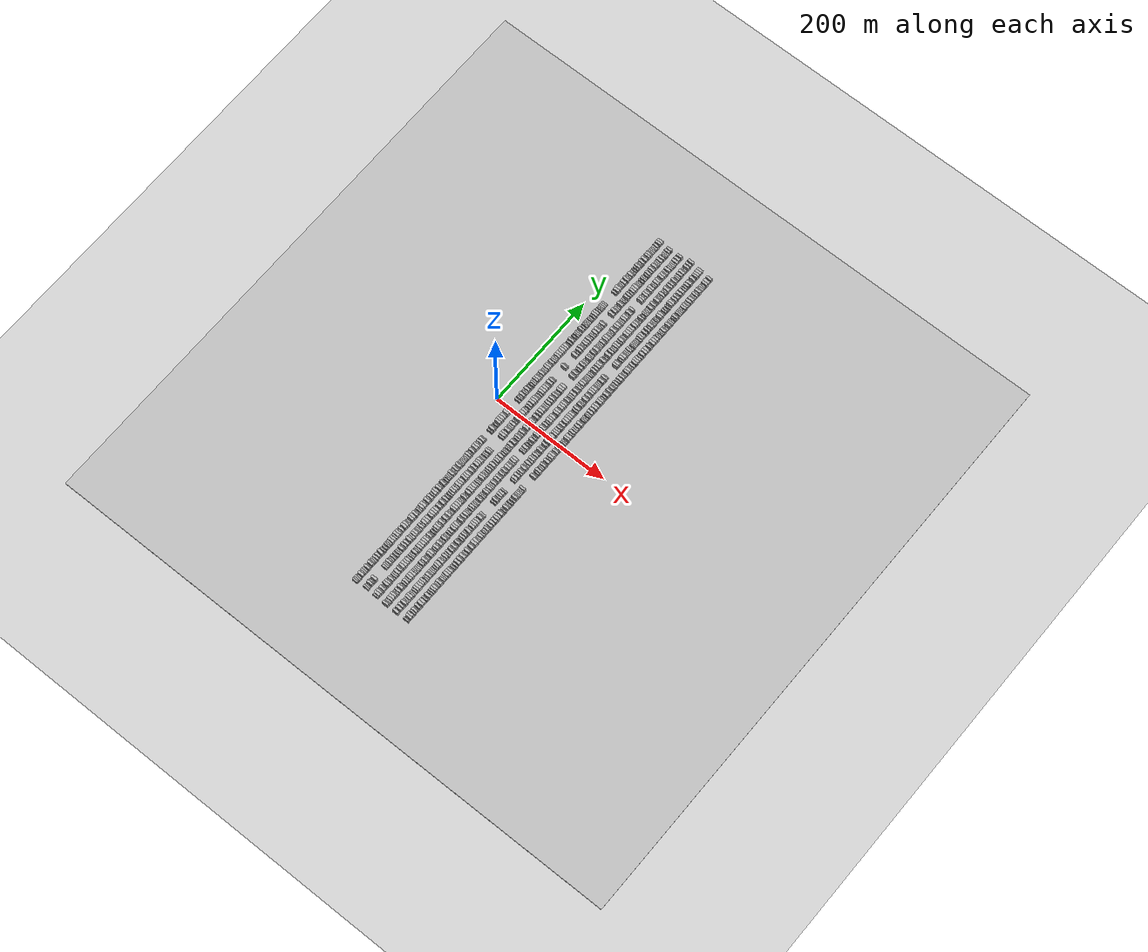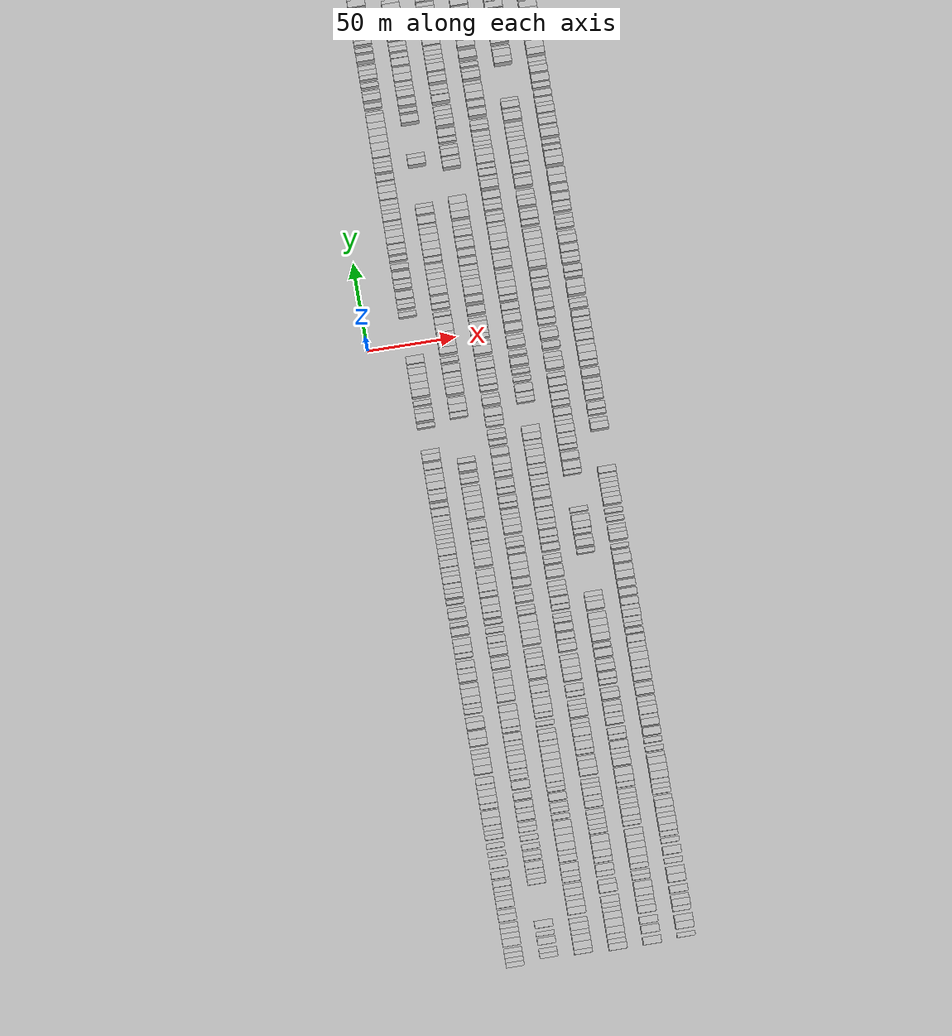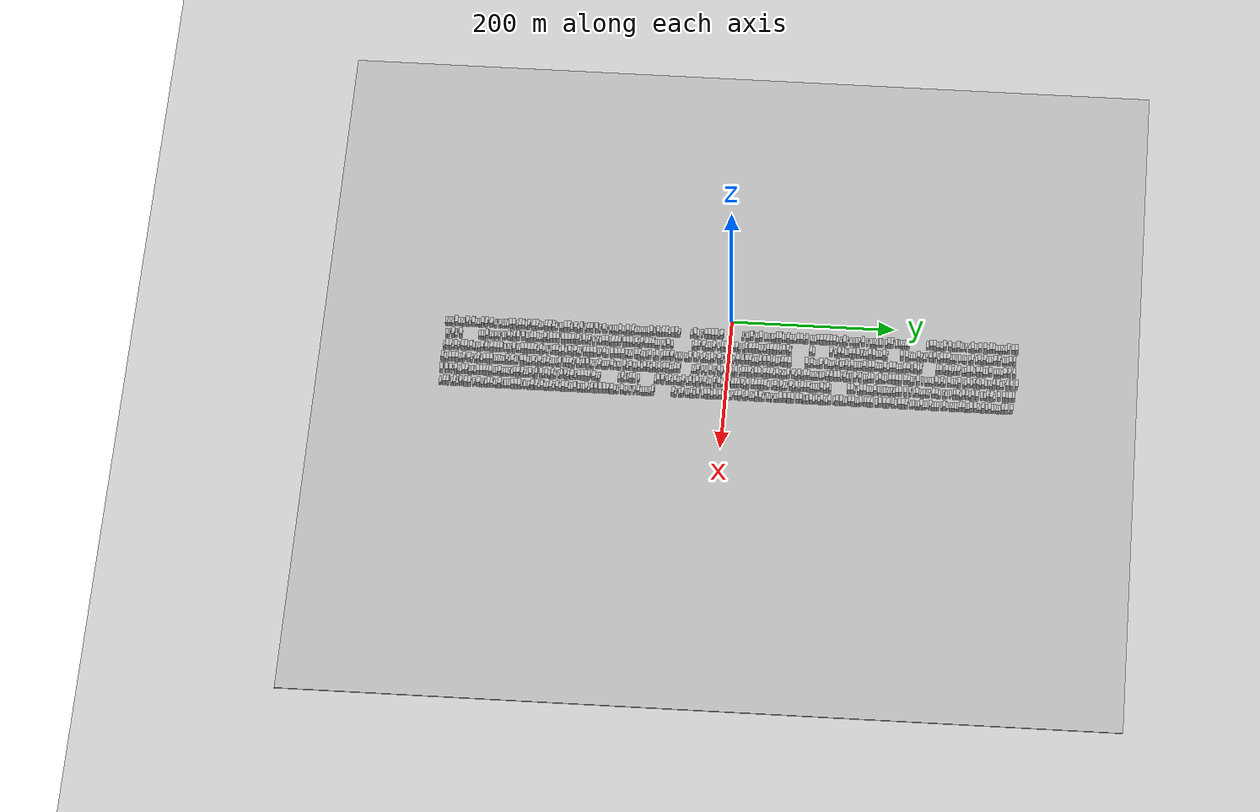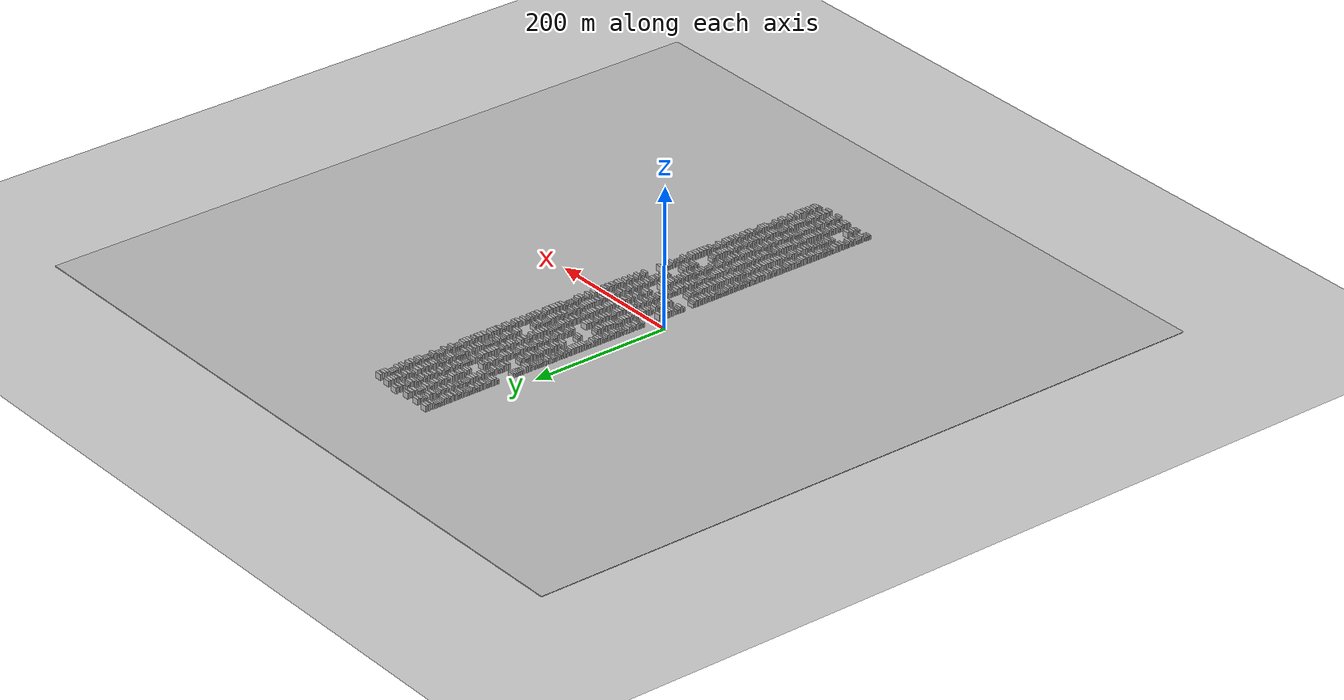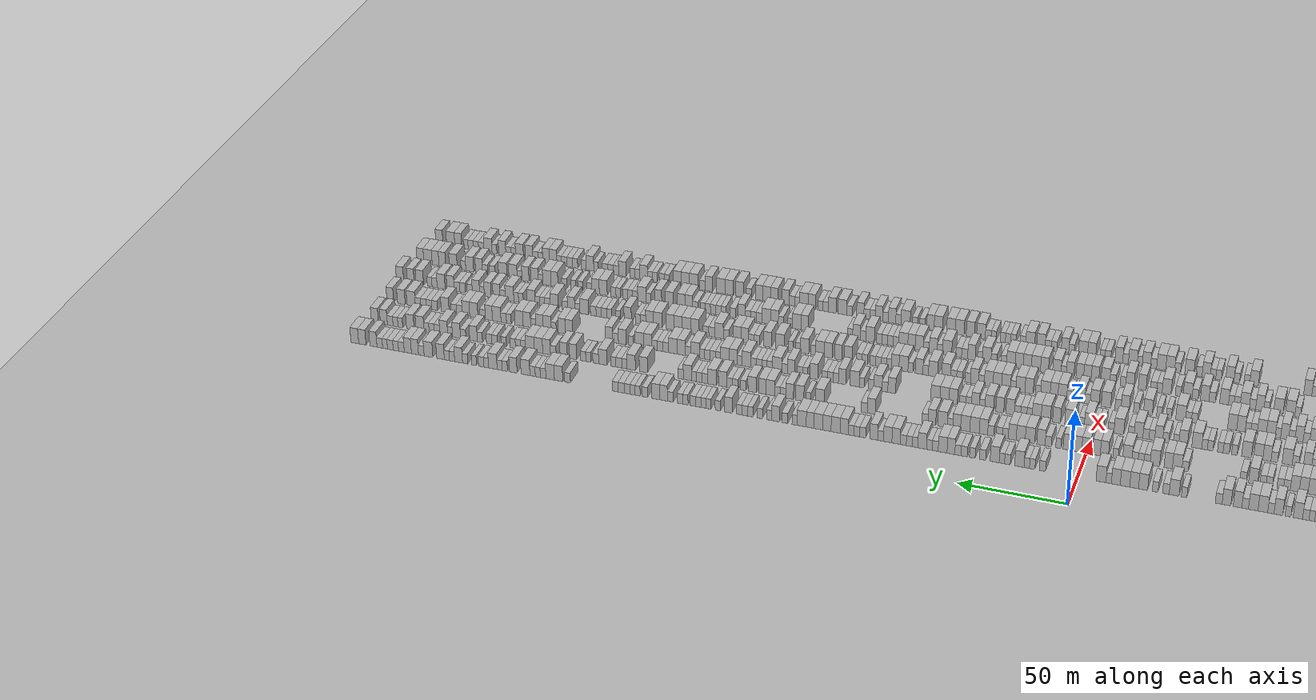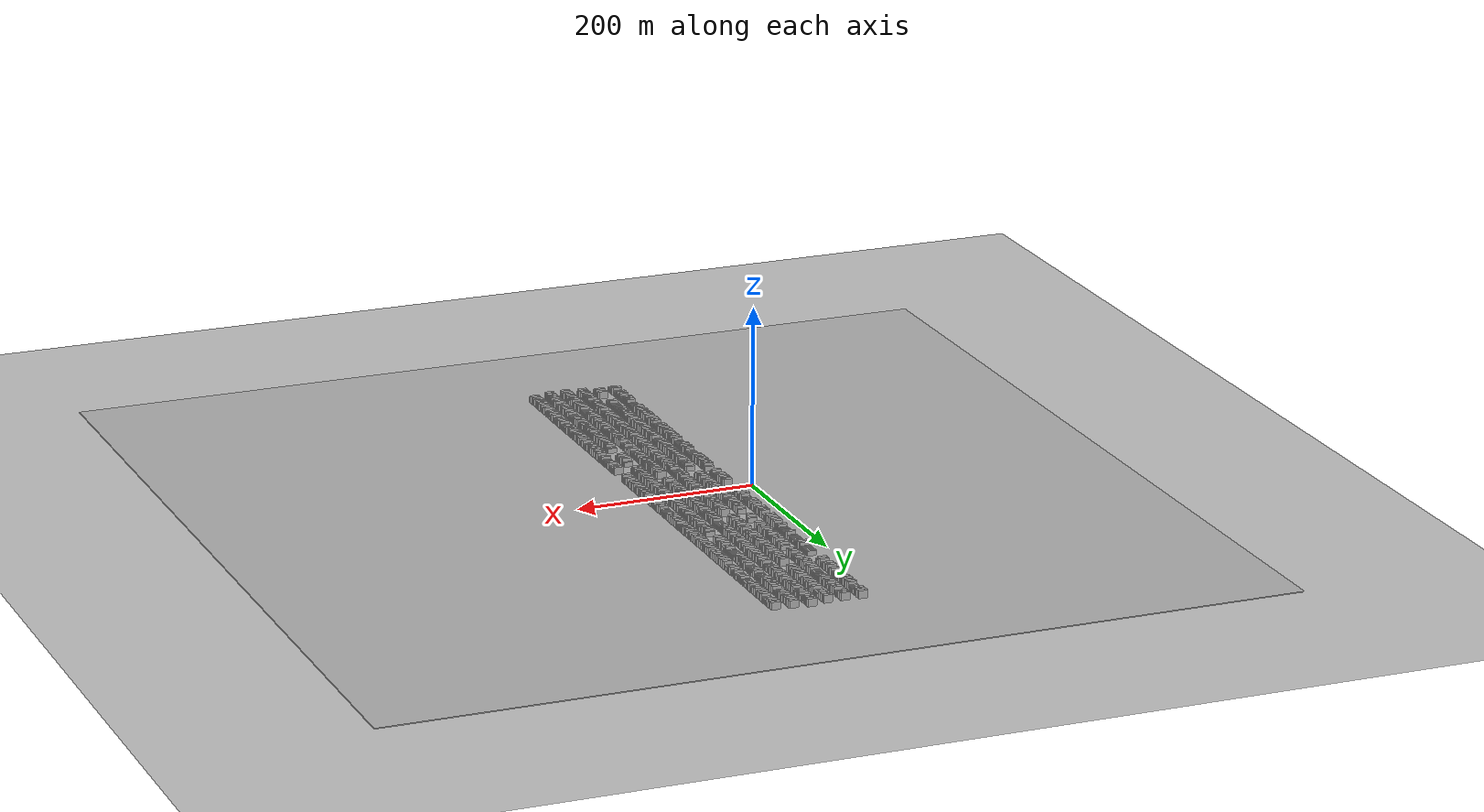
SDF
<?xml version="1.0" encoding="utf-8"?>

<sdf version="1.6">

   <world name="default">

      <gui fullscreen="0">

         <camera name="user_camera">

            <pose>-15 0 4.57585 0 0 0</pose>

            <view_controller>orbit</view_controller>

         </camera>

      </gui>

      <scene>

         <sky>

           <clouds>

             <speed>12</speed>

           </clouds>

         </sky>

         <ambient>0.4 0.4 0.4 1</ambient>

         <background>0.7 0.7 0.7 1</background>

         <shadows>1</shadows>

      </scene>

      <gravity>0 0 -9.8066</gravity>

      <magnetic_field>6e-06 2.3e-05 -4.2e-05</magnetic_field>

      <physics default="0" name="default_physics" type="ode">

         <ode>

            <solver>

               <type>quick</type>

               <iters>10</iters>

               <sor>1.0</sor>

               <use_dynamic_moi_rescaling>0</use_dynamic_moi_rescaling>

            </solver>

            <constraints>

               <cfm>0</cfm>

               <erp>0.2</erp>

               <contact_max_correcting_vel>100</contact_max_correcting_vel>

               <contact_surface_layer>0.001</contact_surface_layer>

            </constraints>

         </ode>

         <max_step_size>0.004</max_step_size>

         <real_time_factor>1</real_time_factor>

         <real_time_update_rate>250</real_time_update_rate>

      </physics>

      <light name="sun" type="directional">

         <cast_shadows>1</cast_shadows>

         <pose>0 0 10 0 0 0</pose>

         <diffuse>0.8 0.8 0.8 1</diffuse>

         <specular>0.2 0.2 0.2 1</specular>

         <attenuation>

            <range>1000</range>

            <constant>0.9</constant>

            <linear>0.01</linear>

            <quadratic>0.001</quadratic>

         </attenuation>

         <direction>-0.5 0.1 -0.9</direction>

      </light>

      <include>

         <name>ground_plane_1</name>

         <uri>model://HANNAS_ground_plane</uri>

         <pose>0 0 0  0 0 0</pose>

      </include>

      <include>

         <name>ground_plane_2</name>

         <uri>model://HANNAS_ground_plane</uri>

         <pose>100 0 0  0 0 0</pose>

      </include>

      <model name="building_1">

         <static>1</static>

         <pose frame="">25.0000 -348.6442 0 0.000000 0.000000 0.000000</pose>

         <link name="link">

            <pose frame="">0 0 3.00 0 0 0</pose>

            <collision name="collision">

               <geometry>

                  <box>

                     <size>10.0000 2.7117 6.0000</size>

                  </box>

               </geometry>

               <max_contacts>10</max_contacts>

               <surface>

                  <contact>

                     <ode/>

                  </contact>

                  <bounce/>

                  <friction>

                     <torsional>

                        <ode/>

                     </torsional>

                     <ode/>

                  </friction>

               </surface>

            </collision>

            <visual name="visual">

               <cast_shadows>0</cast_shadows>

               <geometry>

                  <box>

                     <size>10.0000 2.7117 6.0000</size>

                  </box>

               </geometry>

               <material>

                  <script>

                     <uri>model://HANNAS_wall/materials/scripts</uri>

                     <uri>model://HANNAS_wall/materials/textures</uri>

                     <name>vrc/HANNAS_wall</name>

                  </script>

               </material>

            </visual>

            <self_collide>0</self_collide>

            <enable_wind>0</enable_wind>

            <kinematic>0</kinematic>

         </link>

      </model>

      <model name="building_2">

         <static>1</static>

         <pose frame="">25.0000 -346.0377 0 0.000000 0.000000 0.000000</pose>

         <link name="link">

            <pose frame="">0 0 3.00 0 0 0</pose>

            <collision name="collision">

               <geometry>

                  <box>

                     <size>10.0000 2.5012 6.0000</size>

                  </box>

               </geometry>

               <max_contacts>10</max_contacts>

               <surface>

                  <contact>

                     <ode/>

                  </contact>

                  <bounce/>

                  <friction>

                     <torsional>

                        <ode/>

                     </torsional>

                     <ode/>

                  </friction>

               </surface>

            </collision>

            <visual name="visual">

               <cast_shadows>0</cast_shadows>

               <geometry>

                  <box>

                     <size>10.0000 2.5012 6.0000</size>

                  </box>

               </geometry>

               <material>

                  <script>

                     <uri>model://HANNAS_wall/materials/scripts</uri>

                     <uri>model://HANNAS_wall/materials/textures</uri>

                     <name>vrc/HANNAS_wall</name>

                  </script>

               </material>

            </visual>

            <self_collide>0</self_collide>

            <enable_wind>0</enable_wind>

            <kinematic>0</kinematic>

         </link>

      </model>

      <model name="building_3">

         <static>1</static>

         <pose frame="">25.0000 -343.4030 0 0.000000 0.000000 0.000000</pose>

         <link name="link">

            <pose frame="">0 0 3.00 0 0 0</pose>

            <collision name="collision">

               <geometry>

                  <box>

                     <size>10.0000 2.7682 6.0000</size>

                  </box>

               </geometry>

               <max_contacts>10</max_contacts>

               <surface>

                  <contact>

                     <ode/>

                  </contact>

                  <bounce/>

                  <friction>

                     <torsional>

                        <ode/>

                     </torsional>

                     <ode/>

                  </friction>

               </surface>

            </collision>

            <visual name="visual">

               <cast_shadows>0</cast_shadows>

               <geometry>

                  <box>

                     <size>10.0000 2.7682 6.0000</size>

                  </box>

               </geometry>

               <material>

                  <script>

                     <uri>model://HANNAS_wall/materials/scripts</uri>

                     <uri>model://HANNAS_wall/materials/textures</uri>

                     <name>vrc/HANNAS_wall</name>

                  </script>

               </material>

            </visual>

            <self_collide>0</self_collide>

            <enable_wind>0</enable_wind>

            <kinematic>0</kinematic>

         </link>

      </model>

      <model name="building_4">

         <static>1</static>

         <pose frame="">25.0000 -340.7748 0 0.000000 0.000000 0.000000</pose>

         <link name="link">

            <pose frame="">0 0 3.00 0 0 0</pose>

            <collision name="collision">

               <geometry>

                  <box>

                     <size>10.0000 2.4882 6.0000</size>

                  </box>

               </geometry>

               <max_contacts>10</max_contacts>

               <surface>

                  <contact>

                     <ode/>

                  </contact>

                  <bounce/>

                  <friction>

                     <torsional>

                        <ode/>

                     </torsional>

                     <ode/>

                  </friction>

               </surface>

            </collision>

            <visual name="visual">

               <cast_shadows>0</cast_shadows>

               <geometry>

                  <box>

                     <size>10.0000 2.4882 6.0000</size>

                  </box>

               </geometry>

               <material>

                  <script>

                     <uri>model://HANNAS_wall/materials/scripts</uri>

                     <uri>model://HANNAS_wall/materials/textures</uri>

                     <name>vrc/HANNAS_wall</name>

                  </script>

               </material>

            </visual>

            <self_collide>0</self_collide>

            <enable_wind>0</enable_wind>

            <kinematic>0</kinematic>

         </link>

      </model>

      <model name="building_5">

         <static>1</static>

         <pose frame="">25.0000 -336.3944 0 0.000000 0.000000 0.000000</pose>

         <link name="link">

            <pose frame="">0 0 4.50 0 0 0</pose>

            <collision name="collision">

               <geometry>

                  <box>

                     <size>10.0000 4.2726 9.0000</size>

                  </box>

               </geometry>

               <max_contacts>10</max_contacts>

               <surface>

                  <contact>

                     <ode/>

                  </contact>

                  <bounce/>

                  <friction>

                     <torsional>

                        <ode/>

                     </torsional>

                     <ode/>

                  </friction>

               </surface>

            </collision>

            <visual name="visual">

               <cast_shadows>0</cast_shadows>

               <geometry>

                  <box>

                     <size>10.0000 4.2726 9.0000</size>

                  </box>

               </geometry>

               <material>

                  <script>

                     <uri>model://HANNAS_wall/materials/scripts</uri>

                     <uri>model://HANNAS_wall/materials/textures</uri>

                     <name>vrc/HANNAS_wall</name>

                  </script>

               </material>

            </visual>

            <self_collide>0</self_collide>

            <enable_wind>0</enable_wind>

            <kinematic>0</kinematic>

         </link>

      </model>

      <model name="building_6">

         <static>1</static>

         <pose frame="">25.0000 -332.8057 0 0.000000 0.000000 0.000000</pose>

         <link name="link">

            <pose frame="">0 0 3.00 0 0 0</pose>

            <collision name="collision">

               <geometry>

                  <box>

                     <size>10.0000 2.9047 6.0000</size>

                  </box>

               </geometry>

               <max_contacts>10</max_contacts>

               <surface>

                  <contact>

                     <ode/>

                  </contact>

                  <bounce/>

                  <friction>

                     <torsional>

                        <ode/>

                     </torsional>

                     <ode/>

                  </friction>

               </surface>

            </collision>

            <visual name="visual">

               <cast_shadows>0</cast_shadows>

               <geometry>

                  <box>

                     <size>10.0000 2.9047 6.0000</size>

                  </box>

               </geometry>

               <material>

                  <script>

                     <uri>model://HANNAS_wall/materials/scripts</uri>

                     <uri>model://HANNAS_wall/materials/textures</uri>

                     <name>vrc/HANNAS_wall</name>

                  </script>

               </material>

            </visual>

            <self_collide>0</self_collide>

            <enable_wind>0</enable_wind>

            <kinematic>0</kinematic>

         </link>

      </model>

      <model name="building_7">

         <static>1</static>

         <pose frame="">25.0000 -329.9600 0 0.000000 0.000000 0.000000</pose>

         <link name="link">

            <pose frame="">0 0 3.00 0 0 0</pose>

            <collision name="collision">

               <geometry>

                  <box>

                     <size>10.0000 2.7868 6.0000</size>

                  </box>

               </geometry>

               <max_contacts>10</max_contacts>

               <surface>

                  <contact>

                     <ode/>

                  </contact>

                  <bounce/>

                  <friction>

                     <torsional>

                        <ode/>

                     </torsional>

                     <ode/>

                  </friction>

               </surface>

            </collision>

            <visual name="visual">

               <cast_shadows>0</cast_shadows>

               <geometry>

                  <box>

                     <size>10.0000 2.7868 6.0000</size>

                  </box>

               </geometry>

               <material>

                  <script>

                     <uri>model://HANNAS_wall/materials/scripts</uri>

                     <uri>model://HANNAS_wall/materials/textures</uri>

                     <name>vrc/HANNAS_wall</name>

                  </script>

               </material>

            </visual>

            <self_collide>0</self_collide>

            <enable_wind>0</enable_wind>

            <kinematic>0</kinematic>

         </link>

      </model>

      <model name="building_8">

         <static>1</static>

         <pose frame="">25.0000 -327.2002 0 0.000000 0.000000 0.000000</pose>

         <link name="link">

            <pose frame="">0 0 3.00 0 0 0</pose>

            <collision name="collision">

               <geometry>

                  <box>

                     <size>10.0000 2.7328 6.0000</size>

                  </box>

               </geometry>

               <max_contacts>10</max_contacts>

               <surface>

                  <contact>

                     <ode/>

                  </contact>

                  <bounce/>

                  <friction>

                     <torsional>

                        <ode/>

                     </torsional>

                     <ode/>

                  </friction>

               </surface>

            </collision>

            <visual name="visual">

               <cast_shadows>0</cast_shadows>

               <geometry>

                  <box>

                     <size>10.0000 2.7328 6.0000</size>

                  </box>

               </geometry>

               <material>

                  <script>

                     <uri>model://HANNAS_wall/materials/scripts</uri>

                     <uri>model://HANNAS_wall/materials/textures</uri>

                     <name>vrc/HANNAS_wall</name>

                  </script>

               </material>

            </visual>

            <self_collide>0</self_collide>

            <enable_wind>0</enable_wind>

            <kinematic>0</kinematic>

         </link>

      </model>

      <model name="building_9">

         <static>1</static>

         <pose frame="">25.0000 -322.9202 0 0.000000 0.000000 0.000000</pose>

         <link name="link">

            <pose frame="">0 0 4.50 0 0 0</pose>

            <collision name="collision">

               <geometry>

                  <box>

                     <size>10.0000 3.8272 9.0000</size>

                  </box>

               </geometry>

               <max_contacts>10</max_contacts>

               <surface>

                  <contact>

                     <ode/>

                  </contact>

                  <bounce/>

                  <friction>

                     <torsional>

                        <ode/>

                     </torsional>

                     <ode/>

                  </friction>

               </surface>

            </collision>

            <visual name="visual">

               <cast_shadows>0</cast_shadows>

               <geometry>

                  <box>

                     <size>10.0000 3.8272 9.0000</size>

                  </box>

               </geometry>

               <material>

                  <script>

                     <uri>model://HANNAS_wall/materials/scripts</uri>

                     <uri>model://HANNAS_wall/materials/textures</uri>

                     <name>vrc/HANNAS_wall</name>

                  </script>

               </material>

            </visual>

            <self_collide>0</self_collide>

            <enable_wind>0</enable_wind>

            <kinematic>0</kinematic>

         </link>

      </model>

      <model name="building_10">

         <static>1</static>

         <pose frame="">25.0000 -319.7039 0 0.000000 0.000000 0.000000</pose>

         <link name="link">

            <pose frame="">0 0 3.00 0 0 0</pose>

            <collision name="collision">

               <geometry>

                  <box>

                     <size>10.0000 2.6053 6.0000</size>

                  </box>

               </geometry>

               <max_contacts>10</max_contacts>

               <surface>

                  <contact>

                     <ode/>

                  </contact>

                  <bounce/>

                  <friction>

                     <torsional>

                        <ode/>

                     </torsional>

                     <ode/>

                  </friction>

               </surface>

            </collision>

            <visual name="visual">

               <cast_shadows>0</cast_shadows>

               <geometry>

                  <box>

                     <size>10.0000 2.6053 6.0000</size>

                  </box>

               </geometry>

               <material>

                  <script>

                     <uri>model://HANNAS_wall/materials/scripts</uri>

                     <uri>model://HANNAS_wall/materials/textures</uri>

                     <name>vrc/HANNAS_wall</name>

                  </script>

               </material>

            </visual>

            <self_collide>0</self_collide>

            <enable_wind>0</enable_wind>

            <kinematic>0</kinematic>

         </link>

      </model>

      <model name="building_11">

         <static>1</static>

         <pose frame="">25.0000 -315.4033 0 0.000000 0.000000 0.000000</pose>

         <link name="link">

            <pose frame="">0 0 4.50 0 0 0</pose>

            <collision name="collision">

               <geometry>

                  <box>

                     <size>10.0000 3.9959 9.0000</size>

                  </box>

               </geometry>

               <max_contacts>10</max_contacts>

               <surface>

                  <contact>

                     <ode/>

                  </contact>

                  <bounce/>

                  <friction>

                     <torsional>

                        <ode/>

                     </torsional>

                     <ode/>

                  </friction>

               </surface>

            </collision>

            <visual name="visual">

               <cast_shadows>0</cast_shadows>

               <geometry>

                  <box>

                     <size>10.0000 3.9959 9.0000</size>

                  </box>

               </geometry>

               <material>

                  <script>

                     <uri>model://HANNAS_wall/materials/scripts</uri>

                     <uri>model://HANNAS_wall/materials/textures</uri>

                     <name>vrc/HANNAS_wall</name>

                  </script>

               </material>

            </visual>

            <self_collide>0</self_collide>

            <enable_wind>0</enable_wind>

            <kinematic>0</kinematic>

         </link>

      </model>

      <model name="building_12">

         <static>1</static>

         <pose frame="">25.0000 -312.1419 0 0.000000 0.000000 0.000000</pose>

         <link name="link">

            <pose frame="">0 0 3.00 0 0 0</pose>

            <collision name="collision">

               <geometry>

                  <box>

                     <size>10.0000 2.5270 6.0000</size>

                  </box>

               </geometry>

               <max_contacts>10</max_contacts>

               <surface>

                  <contact>

                     <ode/>

                  </contact>

                  <bounce/>

                  <friction>

                     <torsional>

                        <ode/>

                     </torsional>

                     <ode/>

                  </friction>

               </surface>

            </collision>

            <visual name="visual">

               <cast_shadows>0</cast_shadows>

               <geometry>

                  <box>

                     <size>10.0000 2.5270 6.0000</size>

                  </box>

               </geometry>

               <material>

                  <script>

                     <uri>model://HANNAS_wall/materials/scripts</uri>

                     <uri>model://HANNAS_wall/materials/textures</uri>

                     <name>vrc/HANNAS_wall</name>

                  </script>

               </material>

            </visual>

            <self_collide>0</self_collide>

            <enable_wind>0</enable_wind>

            <kinematic>0</kinematic>

         </link>

      </model>

      <model name="building_13">

         <static>1</static>

         <pose frame="">25.0000 -309.6720 0 0.000000 0.000000 0.000000</pose>

         <link name="link">

            <pose frame="">0 0 3.00 0 0 0</pose>

            <collision name="collision">

               <geometry>

                  <box>

                     <size>10.0000 2.4127 6.0000</size>

                  </box>

               </geometry>

               <max_contacts>10</max_contacts>

               <surface>

                  <contact>

                     <ode/>

                  </contact>

                  <bounce/>

                  <friction>

                     <torsional>

                        <ode/>

                     </torsional>

                     <ode/>

                  </friction>

               </surface>

            </collision>

            <visual name="visual">

               <cast_shadows>0</cast_shadows>

               <geometry>

                  <box>

                     <size>10.0000 2.4127 6.0000</size>

                  </box>

               </geometry>

               <material>

                  <script>

                     <uri>model://HANNAS_wall/materials/scripts</uri>

                     <uri>model://HANNAS_wall/materials/textures</uri>

                     <name>vrc/HANNAS_wall</name>

                  </script>

               </material>

            </visual>

            <self_collide>0</self_collide>

            <enable_wind>0</enable_wind>

            <kinematic>0</kinematic>

         </link>

      </model>

      <model name="building_14">

         <static>1</static>

         <pose frame="">25.0000 -307.1670 0 0.000000 0.000000 0.000000</pose>

         <link name="link">

            <pose frame="">0 0 3.00 0 0 0</pose>

            <collision name="collision">

               <geometry>

                  <box>

                     <size>10.0000 2.5974 6.0000</size>

                  </box>

               </geometry>

               <max_contacts>10</max_contacts>

               <surface>

                  <contact>

                     <ode/>

                  </contact>

                  <bounce/>

                  <friction>

                     <torsional>

                        <ode/>

                     </torsional>

                     <ode/>

                  </friction>

               </surface>

            </collision>

            <visual name="visual">

               <cast_shadows>0</cast_shadows>

               <geometry>

                  <box>

                     <size>10.0000 2.5974 6.0000</size>

                  </box>

               </geometry>

               <material>

                  <script>

                     <uri>model://HANNAS_wall/materials/scripts</uri>

                     <uri>model://HANNAS_wall/materials/textures</uri>

                     <name>vrc/HANNAS_wall</name>

                  </script>

               </material>

            </visual>

            <self_collide>0</self_collide>

            <enable_wind>0</enable_wind>

            <kinematic>0</kinematic>

         </link>

      </model>

      <model name="building_15">

         <static>1</static>

         <pose frame="">25.0000 -304.0613 0 0.000000 0.000000 0.000000</pose>

         <link name="link">

            <pose frame="">0 0 4.50 0 0 0</pose>

            <collision name="collision">

               <geometry>

                  <box>

                     <size>10.0000 3.6139 9.0000</size>

                  </box>

               </geometry>

               <max_contacts>10</max_contacts>

               <surface>

                  <contact>

                     <ode/>

                  </contact>

                  <bounce/>

                  <friction>

                     <torsional>

                        <ode/>

                     </torsional>

                     <ode/>

                  </friction>

               </surface>

            </collision>

            <visual name="visual">

               <cast_shadows>0</cast_shadows>

               <geometry>

                  <box>

                     <size>10.0000 3.6139 9.0000</size>

                  </box>

               </geometry>

               <material>

                  <script>

                     <uri>model://HANNAS_wall/materials/scripts</uri>

                     <uri>model://HANNAS_wall/materials/textures</uri>

                     <name>vrc/HANNAS_wall</name>

                  </script>

               </material>

            </visual>

            <self_collide>0</self_collide>

            <enable_wind>0</enable_wind>

            <kinematic>0</kinematic>

         </link>

      </model>

      <model name="building_16">

         <static>1</static>

         <pose frame="">25.0000 -299.3112 0 0.000000 0.000000 0.000000</pose>

         <link name="link">

            <pose frame="">0 0 4.50 0 0 0</pose>

            <collision name="collision">

               <geometry>

                  <box>

                     <size>10.0000 3.8862 9.0000</size>

                  </box>

               </geometry>

               <max_contacts>10</max_contacts>

               <surface>

                  <contact>

                     <ode/>

                  </contact>

                  <bounce/>

                  <friction>

                     <torsional>

                        <ode/>

                     </torsional>

                     <ode/>

                  </friction>

               </surface>

            </collision>

            <visual name="visual">

               <cast_shadows>0</cast_shadows>

               <geometry>

                  <box>

                     <size>10.0000 3.8862 9.0000</size>

                  </box>

               </geometry>

               <material>

                  <script>

                     <uri>model://HANNAS_wall/materials/scripts</uri>

                     <uri>model://HANNAS_wall/materials/textures</uri>

                     <name>vrc/HANNAS_wall</name>

                  </script>

               </material>

            </visual>

            <self_collide>0</self_collide>

            <enable_wind>0</enable_wind>

            <kinematic>0</kinematic>

         </link>

      </model>

      <model name="building_17">

         <static>1</static>

         <pose frame="">25.0000 -293.1671 0 0.000000 0.000000 0.000000</pose>

         <link name="link">

            <pose frame="">0 0 4.50 0 0 0</pose>

            <collision name="collision">

               <geometry>

                  <box>

                     <size>10.0000 4.4021 9.0000</size>

                  </box>

               </geometry>

               <max_contacts>10</max_contacts>

               <surface>

                  <contact>

                     <ode/>

                  </contact>

                  <bounce/>

                  <friction>

                     <torsional>

                        <ode/>

                     </torsional>

                     <ode/>

                  </friction>

               </surface>

            </collision>

            <visual name="visual">

               <cast_shadows>0</cast_shadows>

               <geometry>

                  <box>

                     <size>10.0000 4.4021 9.0000</size>

                  </box>

               </geometry>

               <material>

                  <script>

                     <uri>model://HANNAS_wall/materials/scripts</uri>

                     <uri>model://HANNAS_wall/materials/textures</uri>

                     <name>vrc/HANNAS_wall</name>

                  </script>

               </material>

            </visual>

            <self_collide>0</self_collide>

            <enable_wind>0</enable_wind>

            <kinematic>0</kinematic>

         </link>

      </model>

      <model name="building_18">

         <static>1</static>

         <pose frame="">25.0000 -287.7111 0 0.000000 0.000000 0.000000</pose>

         <link name="link">

            <pose frame="">0 0 3.00 0 0 0</pose>

            <collision name="collision">

               <geometry>

                  <box>

                     <size>10.0000 2.5098 6.0000</size>

                  </box>

               </geometry>

               <max_contacts>10</max_contacts>

               <surface>

                  <contact>

                     <ode/>

                  </contact>

                  <bounce/>

                  <friction>

                     <torsional>

                        <ode/>

                     </torsional>

                     <ode/>

                  </friction>

               </surface>

            </collision>

            <visual name="visual">

               <cast_shadows>0</cast_shadows>

               <geometry>

                  <box>

                     <size>10.0000 2.5098 6.0000</size>

                  </box>

               </geometry>

               <material>

                  <script>

                     <uri>model://HANNAS_wall/materials/scripts</uri>

                     <uri>model://HANNAS_wall/materials/textures</uri>

                     <name>vrc/HANNAS_wall</name>

                  </script>

               </material>

            </visual>

            <self_collide>0</self_collide>

            <enable_wind>0</enable_wind>

            <kinematic>0</kinematic>

         </link>

      </model>

      <model name="building_19">

         <static>1</static>

         <pose frame="">25.0000 -283.0220 0 0.000000 0.000000 0.000000</pose>

         <link name="link">

            <pose frame="">0 0 3.00 0 0 0</pose>

            <collision name="collision">

               <geometry>

                  <box>

                     <size>10.0000 2.8683 6.0000</size>

                  </box>

               </geometry>

               <max_contacts>10</max_contacts>

               <surface>

                  <contact>

                     <ode/>

                  </contact>

                  <bounce/>

                  <friction>

                     <torsional>

                        <ode/>

                     </torsional>

                     <ode/>

                  </friction>

               </surface>

            </collision>

            <visual name="visual">

               <cast_shadows>0</cast_shadows>

               <geometry>

                  <box>

                     <size>10.0000 2.8683 6.0000</size>

                  </box>

               </geometry>

               <material>

                  <script>

                     <uri>model://HANNAS_wall/materials/scripts</uri>

                     <uri>model://HANNAS_wall/materials/textures</uri>

                     <name>vrc/HANNAS_wall</name>

                  </script>

               </material>

            </visual>

            <self_collide>0</self_collide>

            <enable_wind>0</enable_wind>

            <kinematic>0</kinematic>

         </link>

      </model>

      <model name="building_20">

         <static>1</static>

         <pose frame="">25.0000 -278.3360 0 0.000000 0.000000 0.000000</pose>

         <link name="link">

            <pose frame="">0 0 3.00 0 0 0</pose>

            <collision name="collision">

               <geometry>

                  <box>

                     <size>10.0000 2.5036 6.0000</size>

                  </box>

               </geometry>

               <max_contacts>10</max_contacts>

               <surface>

                  <contact>

                     <ode/>

                  </contact>

                  <bounce/>

                  <friction>

                     <torsional>

                        <ode/>

                     </torsional>

                     <ode/>

                  </friction>

               </surface>

            </collision>

            <visual name="visual">

               <cast_shadows>0</cast_shadows>

               <geometry>

                  <box>

                     <size>10.0000 2.5036 6.0000</size>

                  </box>

               </geometry>

               <material>

                  <script>

                     <uri>model://HANNAS_wall/materials/scripts</uri>

                     <uri>model://HANNAS_wall/materials/textures</uri>

                     <name>vrc/HANNAS_wall</name>

                  </script>

               </material>

            </visual>

            <self_collide>0</self_collide>

            <enable_wind>0</enable_wind>

            <kinematic>0</kinematic>

         </link>

      </model>

      <model name="building_21">

         <static>1</static>

         <pose frame="">25.0000 -275.8799 0 0.000000 0.000000 0.000000</pose>

         <link name="link">

            <pose frame="">0 0 3.00 0 0 0</pose>

            <collision name="collision">

               <geometry>

                  <box>

                     <size>10.0000 2.4085 6.0000</size>

                  </box>

               </geometry>

               <max_contacts>10</max_contacts>

               <surface>

                  <contact>

                     <ode/>

                  </contact>

                  <bounce/>

                  <friction>

                     <torsional>

                        <ode/>

                     </torsional>

                     <ode/>

                  </friction>

               </surface>

            </collision>

            <visual name="visual">

               <cast_shadows>0</cast_shadows>

               <geometry>

                  <box>

                     <size>10.0000 2.4085 6.0000</size>

                  </box>

               </geometry>

               <material>

                  <script>

                     <uri>model://HANNAS_wall/materials/scripts</uri>

                     <uri>model://HANNAS_wall/materials/textures</uri>

                     <name>vrc/HANNAS_wall</name>

                  </script>

               </material>

            </visual>

            <self_collide>0</self_collide>

            <enable_wind>0</enable_wind>

            <kinematic>0</kinematic>

         </link>

      </model>

      <model name="building_22">

         <static>1</static>

         <pose frame="">25.0000 -273.3234 0 0.000000 0.000000 0.000000</pose>

         <link name="link">

            <pose frame="">0 0 3.00 0 0 0</pose>

            <collision name="collision">

               <geometry>

                  <box>

                     <size>10.0000 2.7045 6.0000</size>

                  </box>

               </geometry>

               <max_contacts>10</max_contacts>

               <surface>

                  <contact>

                     <ode/>

                  </contact>

                  <bounce/>

                  <friction>

                     <torsional>

                        <ode/>

                     </torsional>

                     <ode/>

                  </friction>

               </surface>

            </collision>

            <visual name="visual">

               <cast_shadows>0</cast_shadows>

               <geometry>

                  <box>

                     <size>10.0000 2.7045 6.0000</size>

                  </box>

               </geometry>

               <material>

                  <script>

                     <uri>model://HANNAS_wall/materials/scripts</uri>

                     <uri>model://HANNAS_wall/materials/textures</uri>

                     <name>vrc/HANNAS_wall</name>

                  </script>

               </material>

            </visual>

            <self_collide>0</self_collide>

            <enable_wind>0</enable_wind>

            <kinematic>0</kinematic>

         </link>

      </model>

      <model name="building_23">

         <static>1</static>

         <pose frame="">25.0000 -269.9088 0 0.000000 0.000000 0.000000</pose>

         <link name="link">

            <pose frame="">0 0 4.50 0 0 0</pose>

            <collision name="collision">

               <geometry>

                  <box>

                     <size>10.0000 4.1248 9.0000</size>

                  </box>

               </geometry>

               <max_contacts>10</max_contacts>

               <surface>

                  <contact>

                     <ode/>

                  </contact>

                  <bounce/>

                  <friction>

                     <torsional>

                        <ode/>

                     </torsional>

                     <ode/>

                  </friction>

               </surface>

            </collision>

            <visual name="visual">

               <cast_shadows>0</cast_shadows>

               <geometry>

                  <box>

                     <size>10.0000 4.1248 9.0000</size>

                  </box>

               </geometry>

               <material>

                  <script>

                     <uri>model://HANNAS_wall/materials/scripts</uri>

                     <uri>model://HANNAS_wall/materials/textures</uri>

                     <name>vrc/HANNAS_wall</name>

                  </script>

               </material>

            </visual>

            <self_collide>0</self_collide>

            <enable_wind>0</enable_wind>

            <kinematic>0</kinematic>

         </link>

      </model>

      <model name="building_24">

         <static>1</static>

         <pose frame="">25.0000 -265.8082 0 0.000000 0.000000 0.000000</pose>

         <link name="link">

            <pose frame="">0 0 4.50 0 0 0</pose>

            <collision name="collision">

               <geometry>

                  <box>

                     <size>10.0000 4.0764 9.0000</size>

                  </box>

               </geometry>

               <max_contacts>10</max_contacts>

               <surface>

                  <contact>

                     <ode/>

                  </contact>

                  <bounce/>

                  <friction>

                     <torsional>

                        <ode/>

                     </torsional>

                     <ode/>

                  </friction>

               </surface>

            </collision>

            <visual name="visual">

               <cast_shadows>0</cast_shadows>

               <geometry>

                  <box>

                     <size>10.0000 4.0764 9.0000</size>

                  </box>

               </geometry>

               <material>

                  <script>

                     <uri>model://HANNAS_wall/materials/scripts</uri>

                     <uri>model://HANNAS_wall/materials/textures</uri>

                     <name>vrc/HANNAS_wall</name>

                  </script>

               </material>

            </visual>

            <self_collide>0</self_collide>

            <enable_wind>0</enable_wind>

            <kinematic>0</kinematic>

         </link>

      </model>

      <model name="building_25">

         <static>1</static>

         <pose frame="">25.0000 -261.3336 0 0.000000 0.000000 0.000000</pose>

         <link name="link">

            <pose frame="">0 0 3.00 0 0 0</pose>

            <collision name="collision">

               <geometry>

                  <box>

                     <size>10.0000 2.8729 6.0000</size>

                  </box>

               </geometry>

               <max_contacts>10</max_contacts>

               <surface>

                  <contact>

                     <ode/>

                  </contact>

                  <bounce/>

                  <friction>

                     <torsional>

                        <ode/>

                     </torsional>

                     <ode/>

                  </friction>

               </surface>

            </collision>

            <visual name="visual">

               <cast_shadows>0</cast_shadows>

               <geometry>

                  <box>

                     <size>10.0000 2.8729 6.0000</size>

                  </box>

               </geometry>

               <material>

                  <script>

                     <uri>model://HANNAS_wall/materials/scripts</uri>

                     <uri>model://HANNAS_wall/materials/textures</uri>

                     <name>vrc/HANNAS_wall</name>

                  </script>

               </material>

            </visual>

            <self_collide>0</self_collide>

            <enable_wind>0</enable_wind>

            <kinematic>0</kinematic>

         </link>

      </model>

      <model name="building_26">

         <static>1</static>

         <pose frame="">25.0000 -257.8863 0 0.000000 0.000000 0.000000</pose>

         <link name="link">

            <pose frame="">0 0 4.50 0 0 0</pose>

            <collision name="collision">

               <geometry>

                  <box>

                     <size>10.0000 4.0216 9.0000</size>

                  </box>

               </geometry>

               <max_contacts>10</max_contacts>

               <surface>

                  <contact>

                     <ode/>

                  </contact>

                  <bounce/>

                  <friction>

                     <torsional>

                        <ode/>

                     </torsional>

                     <ode/>

                  </friction>

               </surface>

            </collision>

            <visual name="visual">

               <cast_shadows>0</cast_shadows>

               <geometry>

                  <box>

                     <size>10.0000 4.0216 9.0000</size>

                  </box>

               </geometry>

               <material>

                  <script>

                     <uri>model://HANNAS_wall/materials/scripts</uri>

                     <uri>model://HANNAS_wall/materials/textures</uri>

                     <name>vrc/HANNAS_wall</name>

                  </script>

               </material>

            </visual>

            <self_collide>0</self_collide>

            <enable_wind>0</enable_wind>

            <kinematic>0</kinematic>

         </link>

      </model>

      <model name="building_27">

         <static>1</static>

         <pose frame="">25.0000 -254.0091 0 0.000000 0.000000 0.000000</pose>

         <link name="link">

            <pose frame="">0 0 4.50 0 0 0</pose>

            <collision name="collision">

               <geometry>

                  <box>

                     <size>10.0000 3.7329 9.0000</size>

                  </box>

               </geometry>

               <max_contacts>10</max_contacts>

               <surface>

                  <contact>

                     <ode/>

                  </contact>

                  <bounce/>

                  <friction>

                     <torsional>

                        <ode/>

                     </torsional>

                     <ode/>

                  </friction>

               </surface>

            </collision>

            <visual name="visual">

               <cast_shadows>0</cast_shadows>

               <geometry>

                  <box>

                     <size>10.0000 3.7329 9.0000</size>

                  </box>

               </geometry>

               <material>

                  <script>

                     <uri>model://HANNAS_wall/materials/scripts</uri>

                     <uri>model://HANNAS_wall/materials/textures</uri>

                     <name>vrc/HANNAS_wall</name>

                  </script>

               </material>

            </visual>

            <self_collide>0</self_collide>

            <enable_wind>0</enable_wind>

            <kinematic>0</kinematic>

         </link>

      </model>

      <model name="building_28">

         <static>1</static>

         <pose frame="">25.0000 -250.6905 0 0.000000 0.000000 0.000000</pose>

         <link name="link">

            <pose frame="">0 0 3.00 0 0 0</pose>

            <collision name="collision">

               <geometry>

                  <box>

                     <size>10.0000 2.9043 6.0000</size>

                  </box>

               </geometry>

               <max_contacts>10</max_contacts>

               <surface>

                  <contact>

                     <ode/>

                  </contact>

                  <bounce/>

                  <friction>

                     <torsional>

                        <ode/>

                     </torsional>

                     <ode/>

                  </friction>

               </surface>

            </collision>

            <visual name="visual">

               <cast_shadows>0</cast_shadows>

               <geometry>

                  <box>

                     <size>10.0000 2.9043 6.0000</size>

                  </box>

               </geometry>

               <material>

                  <script>

                     <uri>model://HANNAS_wall/materials/scripts</uri>

                     <uri>model://HANNAS_wall/materials/textures</uri>

                     <name>vrc/HANNAS_wall</name>

                  </script>

               </material>

            </visual>

            <self_collide>0</self_collide>

            <enable_wind>0</enable_wind>

            <kinematic>0</kinematic>

         </link>

      </model>

      <model name="building_29">

         <static>1</static>

         <pose frame="">25.0000 -247.3382 0 0.000000 0.000000 0.000000</pose>

         <link name="link">

            <pose frame="">0 0 4.50 0 0 0</pose>

            <collision name="collision">

               <geometry>

                  <box>

                     <size>10.0000 3.8004 9.0000</size>

                  </box>

               </geometry>

               <max_contacts>10</max_contacts>

               <surface>

                  <contact>

                     <ode/>

                  </contact>

                  <bounce/>

                  <friction>

                     <torsional>

                        <ode/>

                     </torsional>

                     <ode/>

                  </friction>

               </surface>

            </collision>

            <visual name="visual">

               <cast_shadows>0</cast_shadows>

               <geometry>

                  <box>

                     <size>10.0000 3.8004 9.0000</size>

                  </box>

               </geometry>

               <material>

                  <script>

                     <uri>model://HANNAS_wall/materials/scripts</uri>

                     <uri>model://HANNAS_wall/materials/textures</uri>

                     <name>vrc/HANNAS_wall</name>

                  </script>

               </material>

            </visual>

            <self_collide>0</self_collide>

            <enable_wind>0</enable_wind>

            <kinematic>0</kinematic>

         </link>

      </model>

      <model name="building_30">

         <static>1</static>

         <pose frame="">25.0000 -241.2113 0 0.000000 0.000000 0.000000</pose>

         <link name="link">

            <pose frame="">0 0 4.50 0 0 0</pose>

            <collision name="collision">

               <geometry>

                  <box>

                     <size>10.0000 4.4534 9.0000</size>

                  </box>

               </geometry>

               <max_contacts>10</max_contacts>

               <surface>

                  <contact>

                     <ode/>

                  </contact>

                  <bounce/>

                  <friction>

                     <torsional>

                        <ode/>

                     </torsional>

                     <ode/>

                  </friction>

               </surface>

            </collision>

            <visual name="visual">

               <cast_shadows>0</cast_shadows>

               <geometry>

                  <box>

                     <size>10.0000 4.4534 9.0000</size>

                  </box>

               </geometry>

               <material>

                  <script>

                     <uri>model://HANNAS_wall/materials/scripts</uri>

                     <uri>model://HANNAS_wall/materials/textures</uri>

                     <name>vrc/HANNAS_wall</name>

                  </script>

               </material>

            </visual>

            <self_collide>0</self_collide>

            <enable_wind>0</enable_wind>

            <kinematic>0</kinematic>

         </link>

      </model>

      <model name="building_31">

         <static>1</static>

         <pose frame="">25.0000 -237.0478 0 0.000000 0.000000 0.000000</pose>

         <link name="link">

            <pose frame="">0 0 4.50 0 0 0</pose>

            <collision name="collision">

               <geometry>

                  <box>

                     <size>10.0000 3.8735 9.0000</size>

                  </box>

               </geometry>

               <max_contacts>10</max_contacts>

               <surface>

                  <contact>

                     <ode/>

                  </contact>

                  <bounce/>

                  <friction>

                     <torsional>

                        <ode/>

                     </torsional>

                     <ode/>

                  </friction>

               </surface>

            </collision>

            <visual name="visual">

               <cast_shadows>0</cast_shadows>

               <geometry>

                  <box>

                     <size>10.0000 3.8735 9.0000</size>

                  </box>

               </geometry>

               <material>

                  <script>

                     <uri>model://HANNAS_wall/materials/scripts</uri>

                     <uri>model://HANNAS_wall/materials/textures</uri>

                     <name>vrc/HANNAS_wall</name>

                  </script>

               </material>

            </visual>

            <self_collide>0</self_collide>

            <enable_wind>0</enable_wind>

            <kinematic>0</kinematic>

         </link>

      </model>

      <model name="building_32">

         <static>1</static>

         <pose frame="">25.0000 -233.6529 0 0.000000 0.000000 0.000000</pose>

         <link name="link">

            <pose frame="">0 0 3.00 0 0 0</pose>

            <collision name="collision">

               <geometry>

                  <box>

                     <size>10.0000 2.9162 6.0000</size>

                  </box>

               </geometry>

               <max_contacts>10</max_contacts>

               <surface>

                  <contact>

                     <ode/>

                  </contact>

                  <bounce/>

                  <friction>

                     <torsional>

                        <ode/>

                     </torsional>

                     <ode/>

                  </friction>

               </surface>

            </collision>

            <visual name="visual">

               <cast_shadows>0</cast_shadows>

               <geometry>

                  <box>

                     <size>10.0000 2.9162 6.0000</size>

                  </box>

               </geometry>

               <material>

                  <script>

                     <uri>model://HANNAS_wall/materials/scripts</uri>

                     <uri>model://HANNAS_wall/materials/textures</uri>

                     <name>vrc/HANNAS_wall</name>

                  </script>

               </material>

            </visual>

            <self_collide>0</self_collide>

            <enable_wind>0</enable_wind>

            <kinematic>0</kinematic>

         </link>

      </model>

      <model name="building_33">

         <static>1</static>

         <pose frame="">25.0000 -230.9695 0 0.000000 0.000000 0.000000</pose>

         <link name="link">

            <pose frame="">0 0 3.00 0 0 0</pose>

            <collision name="collision">

               <geometry>

                  <box>

                     <size>10.0000 2.4507 6.0000</size>

                  </box>

               </geometry>

               <max_contacts>10</max_contacts>

               <surface>

                  <contact>

                     <ode/>

                  </contact>

                  <bounce/>

                  <friction>

                     <torsional>

                        <ode/>

                     </torsional>

                     <ode/>

                  </friction>

               </surface>

            </collision>

            <visual name="visual">

               <cast_shadows>0</cast_shadows>

               <geometry>

                  <box>

                     <size>10.0000 2.4507 6.0000</size>

                  </box>

               </geometry>

               <material>

                  <script>

                     <uri>model://HANNAS_wall/materials/scripts</uri>

                     <uri>model://HANNAS_wall/materials/textures</uri>

                     <name>vrc/HANNAS_wall</name>

                  </script>

               </material>

            </visual>

            <self_collide>0</self_collide>

            <enable_wind>0</enable_wind>

            <kinematic>0</kinematic>

         </link>

      </model>

      <model name="building_34">

         <static>1</static>

         <pose frame="">25.0000 -225.7912 0 0.000000 0.000000 0.000000</pose>

         <link name="link">

            <pose frame="">0 0 4.50 0 0 0</pose>

            <collision name="collision">

               <geometry>

                  <box>

                     <size>10.0000 3.9059 9.0000</size>

                  </box>

               </geometry>

               <max_contacts>10</max_contacts>

               <surface>

                  <contact>

                     <ode/>

                  </contact>

                  <bounce/>

                  <friction>

                     <torsional>

                        <ode/>

                     </torsional>

                     <ode/>

                  </friction>

               </surface>

            </collision>

            <visual name="visual">

               <cast_shadows>0</cast_shadows>

               <geometry>

                  <box>

                     <size>10.0000 3.9059 9.0000</size>

                  </box>

               </geometry>

               <material>

                  <script>

                     <uri>model://HANNAS_wall/materials/scripts</uri>

                     <uri>model://HANNAS_wall/materials/textures</uri>

                     <name>vrc/HANNAS_wall</name>

                  </script>

               </material>

            </visual>

            <self_collide>0</self_collide>

            <enable_wind>0</enable_wind>

            <kinematic>0</kinematic>

         </link>

      </model>

      <model name="building_35">

         <static>1</static>

         <pose frame="">25.0000 -221.6603 0 0.000000 0.000000 0.000000</pose>

         <link name="link">

            <pose frame="">0 0 4.50 0 0 0</pose>

            <collision name="collision">

               <geometry>

                  <box>

                     <size>10.0000 4.3558 9.0000</size>

                  </box>

               </geometry>

               <max_contacts>10</max_contacts>

               <surface>

                  <contact>

                     <ode/>

                  </contact>

                  <bounce/>

                  <friction>

                     <torsional>

                        <ode/>

                     </torsional>

                     <ode/>

                  </friction>

               </surface>

            </collision>

            <visual name="visual">

               <cast_shadows>0</cast_shadows>

               <geometry>

                  <box>

                     <size>10.0000 4.3558 9.0000</size>

                  </box>

               </geometry>

               <material>

                  <script>

                     <uri>model://HANNAS_wall/materials/scripts</uri>

                     <uri>model://HANNAS_wall/materials/textures</uri>

                     <name>vrc/HANNAS_wall</name>

                  </script>

               </material>

            </visual>

            <self_collide>0</self_collide>

            <enable_wind>0</enable_wind>

            <kinematic>0</kinematic>

         </link>

      </model>

      <model name="building_36">

         <static>1</static>

         <pose frame="">25.0000 -216.5429 0 0.000000 0.000000 0.000000</pose>

         <link name="link">

            <pose frame="">0 0 4.50 0 0 0</pose>

            <collision name="collision">

               <geometry>

                  <box>

                     <size>10.0000 3.8790 9.0000</size>

                  </box>

               </geometry>

               <max_contacts>10</max_contacts>

               <surface>

                  <contact>

                     <ode/>

                  </contact>

                  <bounce/>

                  <friction>

                     <torsional>

                        <ode/>

                     </torsional>

                     <ode/>

                  </friction>

               </surface>

            </collision>

            <visual name="visual">

               <cast_shadows>0</cast_shadows>

               <geometry>

                  <box>

                     <size>10.0000 3.8790 9.0000</size>

                  </box>

               </geometry>

               <material>

                  <script>

                     <uri>model://HANNAS_wall/materials/scripts</uri>

                     <uri>model://HANNAS_wall/materials/textures</uri>

                     <name>vrc/HANNAS_wall</name>

                  </script>

               </material>

            </visual>

            <self_collide>0</self_collide>

            <enable_wind>0</enable_wind>

            <kinematic>0</kinematic>

         </link>

      </model>

      <model name="building_37">

         <static>1</static>

         <pose frame="">25.0000 -213.1179 0 0.000000 0.000000 0.000000</pose>

         <link name="link">

            <pose frame="">0 0 3.00 0 0 0</pose>

            <collision name="collision">

               <geometry>

                  <box>

                     <size>10.0000 2.9709 6.0000</size>

                  </box>

               </geometry>

               <max_contacts>10</max_contacts>

               <surface>

                  <contact>

                     <ode/>

                  </contact>

                  <bounce/>

                  <friction>

                     <torsional>

                        <ode/>

                     </torsional>

                     <ode/>

                  </friction>

               </surface>

            </collision>

            <visual name="visual">

               <cast_shadows>0</cast_shadows>

               <geometry>

                  <box>

                     <size>10.0000 2.9709 6.0000</size>

                  </box>

               </geometry>

               <material>

                  <script>

                     <uri>model://HANNAS_wall/materials/scripts</uri>

                     <uri>model://HANNAS_wall/materials/textures</uri>

                     <name>vrc/HANNAS_wall</name>

                  </script>

               </material>

            </visual>

            <self_collide>0</self_collide>

            <enable_wind>0</enable_wind>

            <kinematic>0</kinematic>

         </link>

      </model>

      <model name="building_38">

         <static>1</static>

         <pose frame="">25.0000 -208.2390 0 0.000000 0.000000 0.000000</pose>

         <link name="link">

            <pose frame="">0 0 3.00 0 0 0</pose>

            <collision name="collision">

               <geometry>

                  <box>

                     <size>10.0000 2.7869 6.0000</size>

                  </box>

               </geometry>

               <max_contacts>10</max_contacts>

               <surface>

                  <contact>

                     <ode/>

                  </contact>

                  <bounce/>

                  <friction>

                     <torsional>

                        <ode/>

                     </torsional>

                     <ode/>

                  </friction>

               </surface>

            </collision>

            <visual name="visual">

               <cast_shadows>0</cast_shadows>

               <geometry>

                  <box>

                     <size>10.0000 2.7869 6.0000</size>

                  </box>

               </geometry>

               <material>

                  <script>

                     <uri>model://HANNAS_wall/materials/scripts</uri>

                     <uri>model://HANNAS_wall/materials/textures</uri>

                     <name>vrc/HANNAS_wall</name>

                  </script>

               </material>

            </visual>

            <self_collide>0</self_collide>

            <enable_wind>0</enable_wind>

            <kinematic>0</kinematic>

         </link>

      </model>

      <model name="building_39">

         <static>1</static>

         <pose frame="">25.0000 -205.6031 0 0.000000 0.000000 0.000000</pose>

         <link name="link">

            <pose frame="">0 0 3.00 0 0 0</pose>

            <collision name="collision">

               <geometry>

                  <box>

                     <size>10.0000 2.4848 6.0000</size>

                  </box>

               </geometry>

               <max_contacts>10</max_contacts>

               <surface>

                  <contact>

                     <ode/>

                  </contact>

                  <bounce/>

                  <friction>

                     <torsional>

                        <ode/>

                     </torsional>

                     <ode/>

                  </friction>

               </surface>

            </collision>

            <visual name="visual">

               <cast_shadows>0</cast_shadows>

               <geometry>

                  <box>

                     <size>10.0000 2.4848 6.0000</size>

                  </box>

               </geometry>

               <material>

                  <script>

                     <uri>model://HANNAS_wall/materials/scripts</uri>

                     <uri>model://HANNAS_wall/materials/textures</uri>

                     <name>vrc/HANNAS_wall</name>

                  </script>

               </material>

            </visual>

            <self_collide>0</self_collide>

            <enable_wind>0</enable_wind>

            <kinematic>0</kinematic>

         </link>

      </model>

      <model name="building_40">

         <static>1</static>

         <pose frame="">25.0000 -202.3572 0 0.000000 0.000000 0.000000</pose>

         <link name="link">

            <pose frame="">0 0 4.50 0 0 0</pose>

            <collision name="collision">

               <geometry>

                  <box>

                     <size>10.0000 4.0070 9.0000</size>

                  </box>

               </geometry>

               <max_contacts>10</max_contacts>

               <surface>

                  <contact>

                     <ode/>

                  </contact>

                  <bounce/>

                  <friction>

                     <torsional>

                        <ode/>

                     </torsional>

                     <ode/>

                  </friction>

               </surface>

            </collision>

            <visual name="visual">

               <cast_shadows>0</cast_shadows>

               <geometry>

                  <box>

                     <size>10.0000 4.0070 9.0000</size>

                  </box>

               </geometry>

               <material>

                  <script>

                     <uri>model://HANNAS_wall/materials/scripts</uri>

                     <uri>model://HANNAS_wall/materials/textures</uri>

                     <name>vrc/HANNAS_wall</name>

                  </script>

               </material>

            </visual>

            <self_collide>0</self_collide>

            <enable_wind>0</enable_wind>

            <kinematic>0</kinematic>

         </link>

      </model>

      <model name="building_41">

         <static>1</static>

         <pose frame="">25.0000 -198.1088 0 0.000000 0.000000 0.000000</pose>

         <link name="link">

            <pose frame="">0 0 4.50 0 0 0</pose>

            <collision name="collision">

               <geometry>

                  <box>

                     <size>10.0000 4.4899 9.0000</size>

                  </box>

               </geometry>

               <max_contacts>10</max_contacts>

               <surface>

                  <contact>

                     <ode/>

                  </contact>

                  <bounce/>

                  <friction>

                     <torsional>

                        <ode/>

                     </torsional>

                     <ode/>

                  </friction>

               </surface>

            </collision>

            <visual name="visual">

               <cast_shadows>0</cast_shadows>

               <geometry>

                  <box>

                     <size>10.0000 4.4899 9.0000</size>

                  </box>

               </geometry>

               <material>

                  <script>

                     <uri>model://HANNAS_wall/materials/scripts</uri>

                     <uri>model://HANNAS_wall/materials/textures</uri>

                     <name>vrc/HANNAS_wall</name>

                  </script>

               </material>

            </visual>

            <self_collide>0</self_collide>

            <enable_wind>0</enable_wind>

            <kinematic>0</kinematic>

         </link>

      </model>

      <model name="building_42">

         <static>1</static>

         <pose frame="">25.0000 -194.3705 0 0.000000 0.000000 0.000000</pose>

         <link name="link">

            <pose frame="">0 0 3.00 0 0 0</pose>

            <collision name="collision">

               <geometry>

                  <box>

                     <size>10.0000 2.9866 6.0000</size>

                  </box>

               </geometry>

               <max_contacts>10</max_contacts>

               <surface>

                  <contact>

                     <ode/>

                  </contact>

                  <bounce/>

                  <friction>

                     <torsional>

                        <ode/>

                     </torsional>

                     <ode/>

                  </friction>

               </surface>

            </collision>

            <visual name="visual">

               <cast_shadows>0</cast_shadows>

               <geometry>

                  <box>

                     <size>10.0000 2.9866 6.0000</size>

                  </box>

               </geometry>

               <material>

                  <script>

                     <uri>model://HANNAS_wall/materials/scripts</uri>

                     <uri>model://HANNAS_wall/materials/textures</uri>

                     <name>vrc/HANNAS_wall</name>

                  </script>

               </material>

            </visual>

            <self_collide>0</self_collide>

            <enable_wind>0</enable_wind>

            <kinematic>0</kinematic>

         </link>

      </model>

      <model name="building_43">

         <static>1</static>

         <pose frame="">25.0000 -189.7090 0 0.000000 0.000000 0.000000</pose>

         <link name="link">

            <pose frame="">0 0 4.50 0 0 0</pose>

            <collision name="collision">

               <geometry>

                  <box>

                     <size>10.0000 4.3365 9.0000</size>

                  </box>

               </geometry>

               <max_contacts>10</max_contacts>

               <surface>

                  <contact>

                     <ode/>

                  </contact>

                  <bounce/>

                  <friction>

                     <torsional>

                        <ode/>

                     </torsional>

                     <ode/>

                  </friction>

               </surface>

            </collision>

            <visual name="visual">

               <cast_shadows>0</cast_shadows>

               <geometry>

                  <box>

                     <size>10.0000 4.3365 9.0000</size>

                  </box>

               </geometry>

               <material>

                  <script>

                     <uri>model://HANNAS_wall/materials/scripts</uri>

                     <uri>model://HANNAS_wall/materials/textures</uri>

                     <name>vrc/HANNAS_wall</name>

                  </script>

               </material>

            </visual>

            <self_collide>0</self_collide>

            <enable_wind>0</enable_wind>

            <kinematic>0</kinematic>

         </link>

      </model>

      <model name="building_44">

         <static>1</static>

         <pose frame="">25.0000 -186.0591 0 0.000000 0.000000 0.000000</pose>

         <link name="link">

            <pose frame="">0 0 3.00 0 0 0</pose>

            <collision name="collision">

               <geometry>

                  <box>

                     <size>10.0000 2.9633 6.0000</size>

                  </box>

               </geometry>

               <max_contacts>10</max_contacts>

               <surface>

                  <contact>

                     <ode/>

                  </contact>

                  <bounce/>

                  <friction>

                     <torsional>

                        <ode/>

                     </torsional>

                     <ode/>

                  </friction>

               </surface>

            </collision>

            <visual name="visual">

               <cast_shadows>0</cast_shadows>

               <geometry>

                  <box>

                     <size>10.0000 2.9633 6.0000</size>

                  </box>

               </geometry>

               <material>

                  <script>

                     <uri>model://HANNAS_wall/materials/scripts</uri>

                     <uri>model://HANNAS_wall/materials/textures</uri>

                     <name>vrc/HANNAS_wall</name>

                  </script>

               </material>

            </visual>

            <self_collide>0</self_collide>

            <enable_wind>0</enable_wind>

            <kinematic>0</kinematic>

         </link>

      </model>

      <model name="building_45">

         <static>1</static>

         <pose frame="">25.0000 -182.5844 0 0.000000 0.000000 0.000000</pose>

         <link name="link">

            <pose frame="">0 0 4.50 0 0 0</pose>

            <collision name="collision">

               <geometry>

                  <box>

                     <size>10.0000 3.9861 9.0000</size>

                  </box>

               </geometry>

               <max_contacts>10</max_contacts>

               <surface>

                  <contact>

                     <ode/>

                  </contact>

                  <bounce/>

                  <friction>

                     <torsional>

                        <ode/>

                     </torsional>

                     <ode/>

                  </friction>

               </surface>

            </collision>

            <visual name="visual">

               <cast_shadows>0</cast_shadows>

               <geometry>

                  <box>

                     <size>10.0000 3.9861 9.0000</size>

                  </box>

               </geometry>

               <material>

                  <script>

                     <uri>model://HANNAS_wall/materials/scripts</uri>

                     <uri>model://HANNAS_wall/materials/textures</uri>

                     <name>vrc/HANNAS_wall</name>

                  </script>

               </material>

            </visual>

            <self_collide>0</self_collide>

            <enable_wind>0</enable_wind>

            <kinematic>0</kinematic>

         </link>

      </model>

      <model name="building_46">

         <static>1</static>

         <pose frame="">25.0000 -177.3015 0 0.000000 0.000000 0.000000</pose>

         <link name="link">

            <pose frame="">0 0 3.00 0 0 0</pose>

            <collision name="collision">

               <geometry>

                  <box>

                     <size>10.0000 2.5799 6.0000</size>

                  </box>

               </geometry>

               <max_contacts>10</max_contacts>

               <surface>

                  <contact>

                     <ode/>

                  </contact>

                  <bounce/>

                  <friction>

                     <torsional>

                        <ode/>

                     </torsional>

                     <ode/>

                  </friction>

               </surface>

            </collision>

            <visual name="visual">

               <cast_shadows>0</cast_shadows>

               <geometry>

                  <box>

                     <size>10.0000 2.5799 6.0000</size>

                  </box>

               </geometry>

               <material>

                  <script>

                     <uri>model://HANNAS_wall/materials/scripts</uri>

                     <uri>model://HANNAS_wall/materials/textures</uri>

                     <name>vrc/HANNAS_wall</name>

                  </script>

               </material>

            </visual>

            <self_collide>0</self_collide>

            <enable_wind>0</enable_wind>

            <kinematic>0</kinematic>

         </link>

      </model>

      <model name="building_47">

         <static>1</static>

         <pose frame="">25.0000 -173.9532 0 0.000000 0.000000 0.000000</pose>

         <link name="link">

            <pose frame="">0 0 4.50 0 0 0</pose>

            <collision name="collision">

               <geometry>

                  <box>

                     <size>10.0000 4.1166 9.0000</size>

                  </box>

               </geometry>

               <max_contacts>10</max_contacts>

               <surface>

                  <contact>

                     <ode/>

                  </contact>

                  <bounce/>

                  <friction>

                     <torsional>

                        <ode/>

                     </torsional>

                     <ode/>

                  </friction>

               </surface>

            </collision>

            <visual name="visual">

               <cast_shadows>0</cast_shadows>

               <geometry>

                  <box>

                     <size>10.0000 4.1166 9.0000</size>

                  </box>

               </geometry>

               <material>

                  <script>

                     <uri>model://HANNAS_wall/materials/scripts</uri>

                     <uri>model://HANNAS_wall/materials/textures</uri>

                     <name>vrc/HANNAS_wall</name>

                  </script>

               </material>

            </visual>

            <self_collide>0</self_collide>

            <enable_wind>0</enable_wind>

            <kinematic>0</kinematic>

         </link>

      </model>

      <model name="building_48">

         <static>1</static>

         <pose frame="">25.0000 -169.9814 0 0.000000 0.000000 0.000000</pose>

         <link name="link">

            <pose frame="">0 0 4.50 0 0 0</pose>

            <collision name="collision">

               <geometry>

                  <box>

                     <size>10.0000 3.8270 9.0000</size>

                  </box>

               </geometry>

               <max_contacts>10</max_contacts>

               <surface>

                  <contact>

                     <ode/>

                  </contact>

                  <bounce/>

                  <friction>

                     <torsional>

                        <ode/>

                     </torsional>

                     <ode/>

                  </friction>

               </surface>

            </collision>

            <visual name="visual">

               <cast_shadows>0</cast_shadows>

               <geometry>

                  <box>

                     <size>10.0000 3.8270 9.0000</size>

                  </box>

               </geometry>

               <material>

                  <script>

                     <uri>model://HANNAS_wall/materials/scripts</uri>

                     <uri>model://HANNAS_wall/materials/textures</uri>

                     <name>vrc/HANNAS_wall</name>

                  </script>

               </material>

            </visual>

            <self_collide>0</self_collide>

            <enable_wind>0</enable_wind>

            <kinematic>0</kinematic>

         </link>

      </model>

      <model name="building_49">

         <static>1</static>

         <pose frame="">25.0000 -164.0157 0 0.000000 0.000000 0.000000</pose>

         <link name="link">

            <pose frame="">0 0 4.50 0 0 0</pose>

            <collision name="collision">

               <geometry>

                  <box>

                     <size>10.0000 4.1044 9.0000</size>

                  </box>

               </geometry>

               <max_contacts>10</max_contacts>

               <surface>

                  <contact>

                     <ode/>

                  </contact>

                  <bounce/>

                  <friction>

                     <torsional>

                        <ode/>

                     </torsional>

                     <ode/>

                  </friction>

               </surface>

            </collision>

            <visual name="visual">

               <cast_shadows>0</cast_shadows>

               <geometry>

                  <box>

                     <size>10.0000 4.1044 9.0000</size>

                  </box>

               </geometry>

               <material>

                  <script>

                     <uri>model://HANNAS_wall/materials/scripts</uri>

                     <uri>model://HANNAS_wall/materials/textures</uri>

                     <name>vrc/HANNAS_wall</name>

                  </script>

               </material>

            </visual>

            <self_collide>0</self_collide>

            <enable_wind>0</enable_wind>

            <kinematic>0</kinematic>

         </link>

      </model>

      <model name="building_50">

         <static>1</static>

         <pose frame="">25.0000 -159.7517 0 0.000000 0.000000 0.000000</pose>

         <link name="link">

            <pose frame="">0 0 3.00 0 0 0</pose>

            <collision name="collision">

               <geometry>

                  <box>

                     <size>10.0000 2.4236 6.0000</size>

                  </box>

               </geometry>

               <max_contacts>10</max_contacts>

               <surface>

                  <contact>

                     <ode/>

                  </contact>

                  <bounce/>

                  <friction>

                     <torsional>

                        <ode/>

                     </torsional>

                     <ode/>

                  </friction>

               </surface>

            </collision>

            <visual name="visual">

               <cast_shadows>0</cast_shadows>

               <geometry>

                  <box>

                     <size>10.0000 2.4236 6.0000</size>

                  </box>

               </geometry>

               <material>

                  <script>

                     <uri>model://HANNAS_wall/materials/scripts</uri>

                     <uri>model://HANNAS_wall/materials/textures</uri>

                     <name>vrc/HANNAS_wall</name>

                  </script>

               </material>

            </visual>

            <self_collide>0</self_collide>

            <enable_wind>0</enable_wind>

            <kinematic>0</kinematic>

         </link>

      </model>

      <model name="building_51">

         <static>1</static>

         <pose frame="">25.0000 -154.6381 0 0.000000 0.000000 0.000000</pose>

         <link name="link">

            <pose frame="">0 0 4.50 0 0 0</pose>

            <collision name="collision">

               <geometry>

                  <box>

                     <size>10.0000 3.8036 9.0000</size>

                  </box>

               </geometry>

               <max_contacts>10</max_contacts>

               <surface>

                  <contact>

                     <ode/>

                  </contact>

                  <bounce/>

                  <friction>

                     <torsional>

                        <ode/>

                     </torsional>

                     <ode/>

                  </friction>

               </surface>

            </collision>

            <visual name="visual">

               <cast_shadows>0</cast_shadows>

               <geometry>

                  <box>

                     <size>10.0000 3.8036 9.0000</size>

                  </box>

               </geometry>

               <material>

                  <script>

                     <uri>model://HANNAS_wall/materials/scripts</uri>

                     <uri>model://HANNAS_wall/materials/textures</uri>

                     <name>vrc/HANNAS_wall</name>

                  </script>

               </material>

            </visual>

            <self_collide>0</self_collide>

            <enable_wind>0</enable_wind>

            <kinematic>0</kinematic>

         </link>

      </model>

      <model name="building_52">

         <static>1</static>

         <pose frame="">25.0000 -151.5140 0 0.000000 0.000000 0.000000</pose>

         <link name="link">

            <pose frame="">0 0 3.00 0 0 0</pose>

            <collision name="collision">

               <geometry>

                  <box>

                     <size>10.0000 2.4446 6.0000</size>

                  </box>

               </geometry>

               <max_contacts>10</max_contacts>

               <surface>

                  <contact>

                     <ode/>

                  </contact>

                  <bounce/>

                  <friction>

                     <torsional>

                        <ode/>

                     </torsional>

                     <ode/>

                  </friction>

               </surface>

            </collision>

            <visual name="visual">

               <cast_shadows>0</cast_shadows>

               <geometry>

                  <box>

                     <size>10.0000 2.4446 6.0000</size>

                  </box>

               </geometry>

               <material>

                  <script>

                     <uri>model://HANNAS_wall/materials/scripts</uri>

                     <uri>model://HANNAS_wall/materials/textures</uri>

                     <name>vrc/HANNAS_wall</name>

                  </script>

               </material>

            </visual>

            <self_collide>0</self_collide>

            <enable_wind>0</enable_wind>

            <kinematic>0</kinematic>

         </link>

      </model>

      <model name="building_53">

         <static>1</static>

         <pose frame="">25.0000 -147.0240 0 0.000000 0.000000 0.000000</pose>

         <link name="link">

            <pose frame="">0 0 3.00 0 0 0</pose>

            <collision name="collision">

               <geometry>

                  <box>

                     <size>10.0000 2.5353 6.0000</size>

                  </box>

               </geometry>

               <max_contacts>10</max_contacts>

               <surface>

                  <contact>

                     <ode/>

                  </contact>

                  <bounce/>

                  <friction>

                     <torsional>

                        <ode/>

                     </torsional>

                     <ode/>

                  </friction>

               </surface>

            </collision>

            <visual name="visual">

               <cast_shadows>0</cast_shadows>

               <geometry>

                  <box>

                     <size>10.0000 2.5353 6.0000</size>

                  </box>

               </geometry>

               <material>

                  <script>

                     <uri>model://HANNAS_wall/materials/scripts</uri>

                     <uri>model://HANNAS_wall/materials/textures</uri>

                     <name>vrc/HANNAS_wall</name>

                  </script>

               </material>

            </visual>

            <self_collide>0</self_collide>

            <enable_wind>0</enable_wind>

            <kinematic>0</kinematic>

         </link>

      </model>

      <model name="building_54">

         <static>1</static>

         <pose frame="">25.0000 -143.5289 0 0.000000 0.000000 0.000000</pose>

         <link name="link">

            <pose frame="">0 0 3.00 0 0 0</pose>

            <collision name="collision">

               <geometry>

                  <box>

                     <size>10.0000 2.4549 6.0000</size>

                  </box>

               </geometry>

               <max_contacts>10</max_contacts>

               <surface>

                  <contact>

                     <ode/>

                  </contact>

                  <bounce/>

                  <friction>

                     <torsional>

                        <ode/>

                     </torsional>

                     <ode/>

                  </friction>

               </surface>

            </collision>

            <visual name="visual">

               <cast_shadows>0</cast_shadows>

               <geometry>

                  <box>

                     <size>10.0000 2.4549 6.0000</size>

                  </box>

               </geometry>

               <material>

                  <script>

                     <uri>model://HANNAS_wall/materials/scripts</uri>

                     <uri>model://HANNAS_wall/materials/textures</uri>

                     <name>vrc/HANNAS_wall</name>

                  </script>

               </material>

            </visual>

            <self_collide>0</self_collide>

            <enable_wind>0</enable_wind>

            <kinematic>0</kinematic>

         </link>

      </model>

      <model name="building_55">

         <static>1</static>

         <pose frame="">25.0000 -140.9448 0 0.000000 0.000000 0.000000</pose>

         <link name="link">

            <pose frame="">0 0 3.00 0 0 0</pose>

            <collision name="collision">

               <geometry>

                  <box>

                     <size>10.0000 2.7134 6.0000</size>

                  </box>

               </geometry>

               <max_contacts>10</max_contacts>

               <surface>

                  <contact>

                     <ode/>

                  </contact>

                  <bounce/>

                  <friction>

                     <torsional>

                        <ode/>

                     </torsional>

                     <ode/>

                  </friction>

               </surface>

            </collision>

            <visual name="visual">

               <cast_shadows>0</cast_shadows>

               <geometry>

                  <box>

                     <size>10.0000 2.7134 6.0000</size>

                  </box>

               </geometry>

               <material>

                  <script>

                     <uri>model://HANNAS_wall/materials/scripts</uri>

                     <uri>model://HANNAS_wall/materials/textures</uri>

                     <name>vrc/HANNAS_wall</name>

                  </script>

               </material>

            </visual>

            <self_collide>0</self_collide>

            <enable_wind>0</enable_wind>

            <kinematic>0</kinematic>

         </link>

      </model>

      <model name="building_56">

         <static>1</static>

         <pose frame="">25.0000 -138.2319 0 0.000000 0.000000 0.000000</pose>

         <link name="link">

            <pose frame="">0 0 3.00 0 0 0</pose>

            <collision name="collision">

               <geometry>

                  <box>

                     <size>10.0000 2.7122 6.0000</size>

                  </box>

               </geometry>

               <max_contacts>10</max_contacts>

               <surface>

                  <contact>

                     <ode/>

                  </contact>

                  <bounce/>

                  <friction>

                     <torsional>

                        <ode/>

                     </torsional>

                     <ode/>

                  </friction>

               </surface>

            </collision>

            <visual name="visual">

               <cast_shadows>0</cast_shadows>

               <geometry>

                  <box>

                     <size>10.0000 2.7122 6.0000</size>

                  </box>

               </geometry>

               <material>

                  <script>

                     <uri>model://HANNAS_wall/materials/scripts</uri>

                     <uri>model://HANNAS_wall/materials/textures</uri>

                     <name>vrc/HANNAS_wall</name>

                  </script>

               </material>

            </visual>

            <self_collide>0</self_collide>

            <enable_wind>0</enable_wind>

            <kinematic>0</kinematic>

         </link>

      </model>

      <model name="building_57">

         <static>1</static>

         <pose frame="">25.0000 -134.9331 0 0.000000 0.000000 0.000000</pose>

         <link name="link">

            <pose frame="">0 0 4.50 0 0 0</pose>

            <collision name="collision">

               <geometry>

                  <box>

                     <size>10.0000 3.8853 9.0000</size>

                  </box>

               </geometry>

               <max_contacts>10</max_contacts>

               <surface>

                  <contact>

                     <ode/>

                  </contact>

                  <bounce/>

                  <friction>

                     <torsional>

                        <ode/>

                     </torsional>

                     <ode/>

                  </friction>

               </surface>

            </collision>

            <visual name="visual">

               <cast_shadows>0</cast_shadows>

               <geometry>

                  <box>

                     <size>10.0000 3.8853 9.0000</size>

                  </box>

               </geometry>

               <material>

                  <script>

                     <uri>model://HANNAS_wall/materials/scripts</uri>

                     <uri>model://HANNAS_wall/materials/textures</uri>

                     <name>vrc/HANNAS_wall</name>

                  </script>

               </material>

            </visual>

            <self_collide>0</self_collide>

            <enable_wind>0</enable_wind>

            <kinematic>0</kinematic>

         </link>

      </model>

      <model name="building_58">

         <static>1</static>

         <pose frame="">25.0000 -131.5786 0 0.000000 0.000000 0.000000</pose>

         <link name="link">

            <pose frame="">0 0 3.00 0 0 0</pose>

            <collision name="collision">

               <geometry>

                  <box>

                     <size>10.0000 2.8238 6.0000</size>

                  </box>

               </geometry>

               <max_contacts>10</max_contacts>

               <surface>

                  <contact>

                     <ode/>

                  </contact>

                  <bounce/>

                  <friction>

                     <torsional>

                        <ode/>

                     </torsional>

                     <ode/>

                  </friction>

               </surface>

            </collision>

            <visual name="visual">

               <cast_shadows>0</cast_shadows>

               <geometry>

                  <box>

                     <size>10.0000 2.8238 6.0000</size>

                  </box>

               </geometry>

               <material>

                  <script>

                     <uri>model://HANNAS_wall/materials/scripts</uri>

                     <uri>model://HANNAS_wall/materials/textures</uri>

                     <name>vrc/HANNAS_wall</name>

                  </script>

               </material>

            </visual>

            <self_collide>0</self_collide>

            <enable_wind>0</enable_wind>

            <kinematic>0</kinematic>

         </link>

      </model>

      <model name="building_59">

         <static>1</static>

         <pose frame="">25.0000 -128.9428 0 0.000000 0.000000 0.000000</pose>

         <link name="link">

            <pose frame="">0 0 3.00 0 0 0</pose>

            <collision name="collision">

               <geometry>

                  <box>

                     <size>10.0000 2.4478 6.0000</size>

                  </box>

               </geometry>

               <max_contacts>10</max_contacts>

               <surface>

                  <contact>

                     <ode/>

                  </contact>

                  <bounce/>

                  <friction>

                     <torsional>

                        <ode/>

                     </torsional>

                     <ode/>

                  </friction>

               </surface>

            </collision>

            <visual name="visual">

               <cast_shadows>0</cast_shadows>

               <geometry>

                  <box>

                     <size>10.0000 2.4478 6.0000</size>

                  </box>

               </geometry>

               <material>

                  <script>

                     <uri>model://HANNAS_wall/materials/scripts</uri>

                     <uri>model://HANNAS_wall/materials/textures</uri>

                     <name>vrc/HANNAS_wall</name>

                  </script>

               </material>

            </visual>

            <self_collide>0</self_collide>

            <enable_wind>0</enable_wind>

            <kinematic>0</kinematic>

         </link>

      </model>

      <model name="building_60">

         <static>1</static>

         <pose frame="">25.0000 -125.7645 0 0.000000 0.000000 0.000000</pose>

         <link name="link">

            <pose frame="">0 0 4.50 0 0 0</pose>

            <collision name="collision">

               <geometry>

                  <box>

                     <size>10.0000 3.9089 9.0000</size>

                  </box>

               </geometry>

               <max_contacts>10</max_contacts>

               <surface>

                  <contact>

                     <ode/>

                  </contact>

                  <bounce/>

                  <friction>

                     <torsional>

                        <ode/>

                     </torsional>

                     <ode/>

                  </friction>

               </surface>

            </collision>

            <visual name="visual">

               <cast_shadows>0</cast_shadows>

               <geometry>

                  <box>

                     <size>10.0000 3.9089 9.0000</size>

                  </box>

               </geometry>

               <material>

                  <script>

                     <uri>model://HANNAS_wall/materials/scripts</uri>

                     <uri>model://HANNAS_wall/materials/textures</uri>

                     <name>vrc/HANNAS_wall</name>

                  </script>

               </material>

            </visual>

            <self_collide>0</self_collide>

            <enable_wind>0</enable_wind>

            <kinematic>0</kinematic>

         </link>

      </model>

      <model name="building_61">

         <static>1</static>

         <pose frame="">25.0000 -122.4540 0 0.000000 0.000000 0.000000</pose>

         <link name="link">

            <pose frame="">0 0 3.00 0 0 0</pose>

            <collision name="collision">

               <geometry>

                  <box>

                     <size>10.0000 2.7120 6.0000</size>

                  </box>

               </geometry>

               <max_contacts>10</max_contacts>

               <surface>

                  <contact>

                     <ode/>

                  </contact>

                  <bounce/>

                  <friction>

                     <torsional>

                        <ode/>

                     </torsional>

                     <ode/>

                  </friction>

               </surface>

            </collision>

            <visual name="visual">

               <cast_shadows>0</cast_shadows>

               <geometry>

                  <box>

                     <size>10.0000 2.7120 6.0000</size>

                  </box>

               </geometry>

               <material>

                  <script>

                     <uri>model://HANNAS_wall/materials/scripts</uri>

                     <uri>model://HANNAS_wall/materials/textures</uri>

                     <name>vrc/HANNAS_wall</name>

                  </script>

               </material>

            </visual>

            <self_collide>0</self_collide>

            <enable_wind>0</enable_wind>

            <kinematic>0</kinematic>

         </link>

      </model>

      <model name="building_62">

         <static>1</static>

         <pose frame="">25.0000 -119.0976 0 0.000000 0.000000 0.000000</pose>

         <link name="link">

            <pose frame="">0 0 4.50 0 0 0</pose>

            <collision name="collision">

               <geometry>

                  <box>

                     <size>10.0000 4.0009 9.0000</size>

                  </box>

               </geometry>

               <max_contacts>10</max_contacts>

               <surface>

                  <contact>

                     <ode/>

                  </contact>

                  <bounce/>

                  <friction>

                     <torsional>

                        <ode/>

                     </torsional>

                     <ode/>

                  </friction>

               </surface>

            </collision>

            <visual name="visual">

               <cast_shadows>0</cast_shadows>

               <geometry>

                  <box>

                     <size>10.0000 4.0009 9.0000</size>

                  </box>

               </geometry>

               <material>

                  <script>

                     <uri>model://HANNAS_wall/materials/scripts</uri>

                     <uri>model://HANNAS_wall/materials/textures</uri>

                     <name>vrc/HANNAS_wall</name>

                  </script>

               </material>

            </visual>

            <self_collide>0</self_collide>

            <enable_wind>0</enable_wind>

            <kinematic>0</kinematic>

         </link>

      </model>

      <model name="building_63">

         <static>1</static>

         <pose frame="">25.0000 -115.6321 0 0.000000 0.000000 0.000000</pose>

         <link name="link">

            <pose frame="">0 0 3.00 0 0 0</pose>

            <collision name="collision">

               <geometry>

                  <box>

                     <size>10.0000 2.9301 6.0000</size>

                  </box>

               </geometry>

               <max_contacts>10</max_contacts>

               <surface>

                  <contact>

                     <ode/>

                  </contact>

                  <bounce/>

                  <friction>

                     <torsional>

                        <ode/>

                     </torsional>

                     <ode/>

                  </friction>

               </surface>

            </collision>

            <visual name="visual">

               <cast_shadows>0</cast_shadows>

               <geometry>

                  <box>

                     <size>10.0000 2.9301 6.0000</size>

                  </box>

               </geometry>

               <material>

                  <script>

                     <uri>model://HANNAS_wall/materials/scripts</uri>

                     <uri>model://HANNAS_wall/materials/textures</uri>

                     <name>vrc/HANNAS_wall</name>

                  </script>

               </material>

            </visual>

            <self_collide>0</self_collide>

            <enable_wind>0</enable_wind>

            <kinematic>0</kinematic>

         </link>

      </model>

      <model name="building_64">

         <static>1</static>

         <pose frame="">25.0000 -112.9607 0 0.000000 0.000000 0.000000</pose>

         <link name="link">

            <pose frame="">0 0 3.00 0 0 0</pose>

            <collision name="collision">

               <geometry>

                  <box>

                     <size>10.0000 2.4127 6.0000</size>

                  </box>

               </geometry>

               <max_contacts>10</max_contacts>

               <surface>

                  <contact>

                     <ode/>

                  </contact>

                  <bounce/>

                  <friction>

                     <torsional>

                        <ode/>

                     </torsional>

                     <ode/>

                  </friction>

               </surface>

            </collision>

            <visual name="visual">

               <cast_shadows>0</cast_shadows>

               <geometry>

                  <box>

                     <size>10.0000 2.4127 6.0000</size>

                  </box>

               </geometry>

               <material>

                  <script>

                     <uri>model://HANNAS_wall/materials/scripts</uri>

                     <uri>model://HANNAS_wall/materials/textures</uri>

                     <name>vrc/HANNAS_wall</name>

                  </script>

               </material>

            </visual>

            <self_collide>0</self_collide>

            <enable_wind>0</enable_wind>

            <kinematic>0</kinematic>

         </link>

      </model>

      <model name="building_65">

         <static>1</static>

         <pose frame="">25.0000 -110.4550 0 0.000000 0.000000 0.000000</pose>

         <link name="link">

            <pose frame="">0 0 3.00 0 0 0</pose>

            <collision name="collision">

               <geometry>

                  <box>

                     <size>10.0000 2.5988 6.0000</size>

                  </box>

               </geometry>

               <max_contacts>10</max_contacts>

               <surface>

                  <contact>

                     <ode/>

                  </contact>

                  <bounce/>

                  <friction>

                     <torsional>

                        <ode/>

                     </torsional>

                     <ode/>

                  </friction>

               </surface>

            </collision>

            <visual name="visual">

               <cast_shadows>0</cast_shadows>

               <geometry>

                  <box>

                     <size>10.0000 2.5988 6.0000</size>

                  </box>

               </geometry>

               <material>

                  <script>

                     <uri>model://HANNAS_wall/materials/scripts</uri>

                     <uri>model://HANNAS_wall/materials/textures</uri>

                     <name>vrc/HANNAS_wall</name>

                  </script>

               </material>

            </visual>

            <self_collide>0</self_collide>

            <enable_wind>0</enable_wind>

            <kinematic>0</kinematic>

         </link>

      </model>

      <model name="building_66">

         <static>1</static>

         <pose frame="">25.0000 -107.8737 0 0.000000 0.000000 0.000000</pose>

         <link name="link">

            <pose frame="">0 0 3.00 0 0 0</pose>

            <collision name="collision">

               <geometry>

                  <box>

                     <size>10.0000 2.5639 6.0000</size>

                  </box>

               </geometry>

               <max_contacts>10</max_contacts>

               <surface>

                  <contact>

                     <ode/>

                  </contact>

                  <bounce/>

                  <friction>

                     <torsional>

                        <ode/>

                     </torsional>

                     <ode/>

                  </friction>

               </surface>

            </collision>

            <visual name="visual">

               <cast_shadows>0</cast_shadows>

               <geometry>

                  <box>

                     <size>10.0000 2.5639 6.0000</size>

                  </box>

               </geometry>

               <material>

                  <script>

                     <uri>model://HANNAS_wall/materials/scripts</uri>

                     <uri>model://HANNAS_wall/materials/textures</uri>

                     <name>vrc/HANNAS_wall</name>

                  </script>

               </material>

            </visual>

            <self_collide>0</self_collide>

            <enable_wind>0</enable_wind>

            <kinematic>0</kinematic>

         </link>

      </model>

      <model name="building_67">

         <static>1</static>

         <pose frame="">25.0000 -105.3900 0 0.000000 0.000000 0.000000</pose>

         <link name="link">

            <pose frame="">0 0 3.00 0 0 0</pose>

            <collision name="collision">

               <geometry>

                  <box>

                     <size>10.0000 2.4034 6.0000</size>

                  </box>

               </geometry>

               <max_contacts>10</max_contacts>

               <surface>

                  <contact>

                     <ode/>

                  </contact>

                  <bounce/>

                  <friction>

                     <torsional>

                        <ode/>

                     </torsional>

                     <ode/>

                  </friction>

               </surface>

            </collision>

            <visual name="visual">

               <cast_shadows>0</cast_shadows>

               <geometry>

                  <box>

                     <size>10.0000 2.4034 6.0000</size>

                  </box>

               </geometry>

               <material>

                  <script>

                     <uri>model://HANNAS_wall/materials/scripts</uri>

                     <uri>model://HANNAS_wall/materials/textures</uri>

                     <name>vrc/HANNAS_wall</name>

                  </script>

               </material>

            </visual>

            <self_collide>0</self_collide>

            <enable_wind>0</enable_wind>

            <kinematic>0</kinematic>

         </link>

      </model>

      <model name="building_68">

         <static>1</static>

         <pose frame="">25.0000 -102.9690 0 0.000000 0.000000 0.000000</pose>

         <link name="link">

            <pose frame="">0 0 3.00 0 0 0</pose>

            <collision name="collision">

               <geometry>

                  <box>

                     <size>10.0000 2.4385 6.0000</size>

                  </box>

               </geometry>

               <max_contacts>10</max_contacts>

               <surface>

                  <contact>

                     <ode/>

                  </contact>

                  <bounce/>

                  <friction>

                     <torsional>

                        <ode/>

                     </torsional>

                     <ode/>

                  </friction>

               </surface>

            </collision>

            <visual name="visual">

               <cast_shadows>0</cast_shadows>

               <geometry>

                  <box>

                     <size>10.0000 2.4385 6.0000</size>

                  </box>

               </geometry>

               <material>

                  <script>

                     <uri>model://HANNAS_wall/materials/scripts</uri>

                     <uri>model://HANNAS_wall/materials/textures</uri>

                     <name>vrc/HANNAS_wall</name>

                  </script>

               </material>

            </visual>

            <self_collide>0</self_collide>

            <enable_wind>0</enable_wind>

            <kinematic>0</kinematic>

         </link>

      </model>

      <model name="building_69">

         <static>1</static>

         <pose frame="">25.0000 -100.3519 0 0.000000 0.000000 0.000000</pose>

         <link name="link">

            <pose frame="">0 0 3.00 0 0 0</pose>

            <collision name="collision">

               <geometry>

                  <box>

                     <size>10.0000 2.7957 6.0000</size>

                  </box>

               </geometry>

               <max_contacts>10</max_contacts>

               <surface>

                  <contact>

                     <ode/>

                  </contact>

                  <bounce/>

                  <friction>

                     <torsional>

                        <ode/>

                     </torsional>

                     <ode/>

                  </friction>

               </surface>

            </collision>

            <visual name="visual">

               <cast_shadows>0</cast_shadows>

               <geometry>

                  <box>

                     <size>10.0000 2.7957 6.0000</size>

                  </box>

               </geometry>

               <material>

                  <script>

                     <uri>model://HANNAS_wall/materials/scripts</uri>

                     <uri>model://HANNAS_wall/materials/textures</uri>

                     <name>vrc/HANNAS_wall</name>

                  </script>

               </material>

            </visual>

            <self_collide>0</self_collide>

            <enable_wind>0</enable_wind>

            <kinematic>0</kinematic>

         </link>

      </model>

      <model name="building_70">

         <static>1</static>

         <pose frame="">25.0000 -96.9507 0 0.000000 0.000000 0.000000</pose>

         <link name="link">

            <pose frame="">0 0 4.50 0 0 0</pose>

            <collision name="collision">

               <geometry>

                  <box>

                     <size>10.0000 4.0066 9.0000</size>

                  </box>

               </geometry>

               <max_contacts>10</max_contacts>

               <surface>

                  <contact>

                     <ode/>

                  </contact>

                  <bounce/>

                  <friction>

                     <torsional>

                        <ode/>

                     </torsional>

                     <ode/>

                  </friction>

               </surface>

            </collision>

            <visual name="visual">

               <cast_shadows>0</cast_shadows>

               <geometry>

                  <box>

                     <size>10.0000 4.0066 9.0000</size>

                  </box>

               </geometry>

               <material>

                  <script>

                     <uri>model://HANNAS_wall/materials/scripts</uri>

                     <uri>model://HANNAS_wall/materials/textures</uri>

                     <name>vrc/HANNAS_wall</name>

                  </script>

               </material>

            </visual>

            <self_collide>0</self_collide>

            <enable_wind>0</enable_wind>

            <kinematic>0</kinematic>

         </link>

      </model>

      <model name="building_71">

         <static>1</static>

         <pose frame="">25.0000 -92.6870 0 0.000000 0.000000 0.000000</pose>

         <link name="link">

            <pose frame="">0 0 3.00 0 0 0</pose>

            <collision name="collision">

               <geometry>

                  <box>

                     <size>10.0000 2.5209 6.0000</size>

                  </box>

               </geometry>

               <max_contacts>10</max_contacts>

               <surface>

                  <contact>

                     <ode/>

                  </contact>

                  <bounce/>

                  <friction>

                     <torsional>

                        <ode/>

                     </torsional>

                     <ode/>

                  </friction>

               </surface>

            </collision>

            <visual name="visual">

               <cast_shadows>0</cast_shadows>

               <geometry>

                  <box>

                     <size>10.0000 2.5209 6.0000</size>

                  </box>

               </geometry>

               <material>

                  <script>

                     <uri>model://HANNAS_wall/materials/scripts</uri>

                     <uri>model://HANNAS_wall/materials/textures</uri>

                     <name>vrc/HANNAS_wall</name>

                  </script>

               </material>

            </visual>

            <self_collide>0</self_collide>

            <enable_wind>0</enable_wind>

            <kinematic>0</kinematic>

         </link>

      </model>

      <model name="building_72">

         <static>1</static>

         <pose frame="">25.0000 -88.5406 0 0.000000 0.000000 0.000000</pose>

         <link name="link">

            <pose frame="">0 0 4.50 0 0 0</pose>

            <collision name="collision">

               <geometry>

                  <box>

                     <size>10.0000 3.7719 9.0000</size>

                  </box>

               </geometry>

               <max_contacts>10</max_contacts>

               <surface>

                  <contact>

                     <ode/>

                  </contact>

                  <bounce/>

                  <friction>

                     <torsional>

                        <ode/>

                     </torsional>

                     <ode/>

                  </friction>

               </surface>

            </collision>

            <visual name="visual">

               <cast_shadows>0</cast_shadows>

               <geometry>

                  <box>

                     <size>10.0000 3.7719 9.0000</size>

                  </box>

               </geometry>

               <material>

                  <script>

                     <uri>model://HANNAS_wall/materials/scripts</uri>

                     <uri>model://HANNAS_wall/materials/textures</uri>

                     <name>vrc/HANNAS_wall</name>

                  </script>

               </material>

            </visual>

            <self_collide>0</self_collide>

            <enable_wind>0</enable_wind>

            <kinematic>0</kinematic>

         </link>

      </model>

      <model name="building_73">

         <static>1</static>

         <pose frame="">25.0000 -85.2821 0 0.000000 0.000000 0.000000</pose>

         <link name="link">

            <pose frame="">0 0 3.00 0 0 0</pose>

            <collision name="collision">

               <geometry>

                  <box>

                     <size>10.0000 2.7451 6.0000</size>

                  </box>

               </geometry>

               <max_contacts>10</max_contacts>

               <surface>

                  <contact>

                     <ode/>

                  </contact>

                  <bounce/>

                  <friction>

                     <torsional>

                        <ode/>

                     </torsional>

                     <ode/>

                  </friction>

               </surface>

            </collision>

            <visual name="visual">

               <cast_shadows>0</cast_shadows>

               <geometry>

                  <box>

                     <size>10.0000 2.7451 6.0000</size>

                  </box>

               </geometry>

               <material>

                  <script>

                     <uri>model://HANNAS_wall/materials/scripts</uri>

                     <uri>model://HANNAS_wall/materials/textures</uri>

                     <name>vrc/HANNAS_wall</name>

                  </script>

               </material>

            </visual>

            <self_collide>0</self_collide>

            <enable_wind>0</enable_wind>

            <kinematic>0</kinematic>

         </link>

      </model>

      <model name="building_74">

         <static>1</static>

         <pose frame="">25.0000 -81.8021 0 0.000000 0.000000 0.000000</pose>

         <link name="link">

            <pose frame="">0 0 4.50 0 0 0</pose>

            <collision name="collision">

               <geometry>

                  <box>

                     <size>10.0000 4.2150 9.0000</size>

                  </box>

               </geometry>

               <max_contacts>10</max_contacts>

               <surface>

                  <contact>

                     <ode/>

                  </contact>

                  <bounce/>

                  <friction>

                     <torsional>

                        <ode/>

                     </torsional>

                     <ode/>

                  </friction>

               </surface>

            </collision>

            <visual name="visual">

               <cast_shadows>0</cast_shadows>

               <geometry>

                  <box>

                     <size>10.0000 4.2150 9.0000</size>

                  </box>

               </geometry>

               <material>

                  <script>

                     <uri>model://HANNAS_wall/materials/scripts</uri>

                     <uri>model://HANNAS_wall/materials/textures</uri>

                     <name>vrc/HANNAS_wall</name>

                  </script>

               </material>

            </visual>

            <self_collide>0</self_collide>

            <enable_wind>0</enable_wind>

            <kinematic>0</kinematic>

         </link>

      </model>

      <model name="building_75">

         <static>1</static>

         <pose frame="">25.0000 -77.6193 0 0.000000 0.000000 0.000000</pose>

         <link name="link">

            <pose frame="">0 0 4.50 0 0 0</pose>

            <collision name="collision">

               <geometry>

                  <box>

                     <size>10.0000 4.1505 9.0000</size>

                  </box>

               </geometry>

               <max_contacts>10</max_contacts>

               <surface>

                  <contact>

                     <ode/>

                  </contact>

                  <bounce/>

                  <friction>

                     <torsional>

                        <ode/>

                     </torsional>

                     <ode/>

                  </friction>

               </surface>

            </collision>

            <visual name="visual">

               <cast_shadows>0</cast_shadows>

               <geometry>

                  <box>

                     <size>10.0000 4.1505 9.0000</size>

                  </box>

               </geometry>

               <material>

                  <script>

                     <uri>model://HANNAS_wall/materials/scripts</uri>

                     <uri>model://HANNAS_wall/materials/textures</uri>

                     <name>vrc/HANNAS_wall</name>

                  </script>

               </material>

            </visual>

            <self_collide>0</self_collide>

            <enable_wind>0</enable_wind>

            <kinematic>0</kinematic>

         </link>

      </model>

      <model name="building_76">

         <static>1</static>

         <pose frame="">25.0000 -74.0915 0 0.000000 0.000000 0.000000</pose>

         <link name="link">

            <pose frame="">0 0 3.00 0 0 0</pose>

            <collision name="collision">

               <geometry>

                  <box>

                     <size>10.0000 2.9051 6.0000</size>

                  </box>

               </geometry>

               <max_contacts>10</max_contacts>

               <surface>

                  <contact>

                     <ode/>

                  </contact>

                  <bounce/>

                  <friction>

                     <torsional>

                        <ode/>

                     </torsional>

                     <ode/>

                  </friction>

               </surface>

            </collision>

            <visual name="visual">

               <cast_shadows>0</cast_shadows>

               <geometry>

                  <box>

                     <size>10.0000 2.9051 6.0000</size>

                  </box>

               </geometry>

               <material>

                  <script>

                     <uri>model://HANNAS_wall/materials/scripts</uri>

                     <uri>model://HANNAS_wall/materials/textures</uri>

                     <name>vrc/HANNAS_wall</name>

                  </script>

               </material>

            </visual>

            <self_collide>0</self_collide>

            <enable_wind>0</enable_wind>

            <kinematic>0</kinematic>

         </link>

      </model>

      <model name="building_77">

         <static>1</static>

         <pose frame="">25.0000 -70.7532 0 0.000000 0.000000 0.000000</pose>

         <link name="link">

            <pose frame="">0 0 4.50 0 0 0</pose>

            <collision name="collision">

               <geometry>

                  <box>

                     <size>10.0000 3.7714 9.0000</size>

                  </box>

               </geometry>

               <max_contacts>10</max_contacts>

               <surface>

                  <contact>

                     <ode/>

                  </contact>

                  <bounce/>

                  <friction>

                     <torsional>

                        <ode/>

                     </torsional>

                     <ode/>

                  </friction>

               </surface>

            </collision>

            <visual name="visual">

               <cast_shadows>0</cast_shadows>

               <geometry>

                  <box>

                     <size>10.0000 3.7714 9.0000</size>

                  </box>

               </geometry>

               <material>

                  <script>

                     <uri>model://HANNAS_wall/materials/scripts</uri>

                     <uri>model://HANNAS_wall/materials/textures</uri>

                     <name>vrc/HANNAS_wall</name>

                  </script>

               </material>

            </visual>

            <self_collide>0</self_collide>

            <enable_wind>0</enable_wind>

            <kinematic>0</kinematic>

         </link>

      </model>

      <model name="building_78">

         <static>1</static>

         <pose frame="">25.0000 -65.9466 0 0.000000 0.000000 0.000000</pose>

         <link name="link">

            <pose frame="">0 0 4.50 0 0 0</pose>

            <collision name="collision">

               <geometry>

                  <box>

                     <size>10.0000 3.8419 9.0000</size>

                  </box>

               </geometry>

               <max_contacts>10</max_contacts>

               <surface>

                  <contact>

                     <ode/>

                  </contact>

                  <bounce/>

                  <friction>

                     <torsional>

                        <ode/>

                     </torsional>

                     <ode/>

                  </friction>

               </surface>

            </collision>

            <visual name="visual">

               <cast_shadows>0</cast_shadows>

               <geometry>

                  <box>

                     <size>10.0000 3.8419 9.0000</size>

                  </box>

               </geometry>

               <material>

                  <script>

                     <uri>model://HANNAS_wall/materials/scripts</uri>

                     <uri>model://HANNAS_wall/materials/textures</uri>

                     <name>vrc/HANNAS_wall</name>

                  </script>

               </material>

            </visual>

            <self_collide>0</self_collide>

            <enable_wind>0</enable_wind>

            <kinematic>0</kinematic>

         </link>

      </model>

      <model name="building_79">

         <static>1</static>

         <pose frame="">25.0000 -62.5279 0 0.000000 0.000000 0.000000</pose>

         <link name="link">

            <pose frame="">0 0 3.00 0 0 0</pose>

            <collision name="collision">

               <geometry>

                  <box>

                     <size>10.0000 2.9954 6.0000</size>

                  </box>

               </geometry>

               <max_contacts>10</max_contacts>

               <surface>

                  <contact>

                     <ode/>

                  </contact>

                  <bounce/>

                  <friction>

                     <torsional>

                        <ode/>

                     </torsional>

                     <ode/>

                  </friction>

               </surface>

            </collision>

            <visual name="visual">

               <cast_shadows>0</cast_shadows>

               <geometry>

                  <box>

                     <size>10.0000 2.9954 6.0000</size>

                  </box>

               </geometry>

               <material>

                  <script>

                     <uri>model://HANNAS_wall/materials/scripts</uri>

                     <uri>model://HANNAS_wall/materials/textures</uri>

                     <name>vrc/HANNAS_wall</name>

                  </script>

               </material>

            </visual>

            <self_collide>0</self_collide>

            <enable_wind>0</enable_wind>

            <kinematic>0</kinematic>

         </link>

      </model>

      <model name="building_80">

         <static>1</static>

         <pose frame="">25.0000 -47.3221 0 0.000000 0.000000 0.000000</pose>

         <link name="link">

            <pose frame="">0 0 3.00 0 0 0</pose>

            <collision name="collision">

               <geometry>

                  <box>

                     <size>10.0000 2.4721 6.0000</size>

                  </box>

               </geometry>

               <max_contacts>10</max_contacts>

               <surface>

                  <contact>

                     <ode/>

                  </contact>

                  <bounce/>

                  <friction>

                     <torsional>

                        <ode/>

                     </torsional>

                     <ode/>

                  </friction>

               </surface>

            </collision>

            <visual name="visual">

               <cast_shadows>0</cast_shadows>

               <geometry>

                  <box>

                     <size>10.0000 2.4721 6.0000</size>

                  </box>

               </geometry>

               <material>

                  <script>

                     <uri>model://HANNAS_wall/materials/scripts</uri>

                     <uri>model://HANNAS_wall/materials/textures</uri>

                     <name>vrc/HANNAS_wall</name>

                  </script>

               </material>

            </visual>

            <self_collide>0</self_collide>

            <enable_wind>0</enable_wind>

            <kinematic>0</kinematic>

         </link>

      </model>

      <model name="building_81">

         <static>1</static>

         <pose frame="">25.0000 -42.9015 0 0.000000 0.000000 0.000000</pose>

         <link name="link">

            <pose frame="">0 0 4.50 0 0 0</pose>

            <collision name="collision">

               <geometry>

                  <box>

                     <size>10.0000 4.3690 9.0000</size>

                  </box>

               </geometry>

               <max_contacts>10</max_contacts>

               <surface>

                  <contact>

                     <ode/>

                  </contact>

                  <bounce/>

                  <friction>

                     <torsional>

                        <ode/>

                     </torsional>

                     <ode/>

                  </friction>

               </surface>

            </collision>

            <visual name="visual">

               <cast_shadows>0</cast_shadows>

               <geometry>

                  <box>

                     <size>10.0000 4.3690 9.0000</size>

                  </box>

               </geometry>

               <material>

                  <script>

                     <uri>model://HANNAS_wall/materials/scripts</uri>

                     <uri>model://HANNAS_wall/materials/textures</uri>

                     <name>vrc/HANNAS_wall</name>

                  </script>

               </material>

            </visual>

            <self_collide>0</self_collide>

            <enable_wind>0</enable_wind>

            <kinematic>0</kinematic>

         </link>

      </model>

      <model name="building_82">

         <static>1</static>

         <pose frame="">25.0000 -39.2447 0 0.000000 0.000000 0.000000</pose>

         <link name="link">

            <pose frame="">0 0 3.00 0 0 0</pose>

            <collision name="collision">

               <geometry>

                  <box>

                     <size>10.0000 2.9447 6.0000</size>

                  </box>

               </geometry>

               <max_contacts>10</max_contacts>

               <surface>

                  <contact>

                     <ode/>

                  </contact>

                  <bounce/>

                  <friction>

                     <torsional>

                        <ode/>

                     </torsional>

                     <ode/>

                  </friction>

               </surface>

            </collision>

            <visual name="visual">

               <cast_shadows>0</cast_shadows>

               <geometry>

                  <box>

                     <size>10.0000 2.9447 6.0000</size>

                  </box>

               </geometry>

               <material>

                  <script>

                     <uri>model://HANNAS_wall/materials/scripts</uri>

                     <uri>model://HANNAS_wall/materials/textures</uri>

                     <name>vrc/HANNAS_wall</name>

                  </script>

               </material>

            </visual>

            <self_collide>0</self_collide>

            <enable_wind>0</enable_wind>

            <kinematic>0</kinematic>

         </link>

      </model>

      <model name="building_83">

         <static>1</static>

         <pose frame="">25.0000 -34.4802 0 0.000000 0.000000 0.000000</pose>

         <link name="link">

            <pose frame="">0 0 3.00 0 0 0</pose>

            <collision name="collision">

               <geometry>

                  <box>

                     <size>10.0000 2.5842 6.0000</size>

                  </box>

               </geometry>

               <max_contacts>10</max_contacts>

               <surface>

                  <contact>

                     <ode/>

                  </contact>

                  <bounce/>

                  <friction>

                     <torsional>

                        <ode/>

                     </torsional>

                     <ode/>

                  </friction>

               </surface>

            </collision>

            <visual name="visual">

               <cast_shadows>0</cast_shadows>

               <geometry>

                  <box>

                     <size>10.0000 2.5842 6.0000</size>

                  </box>

               </geometry>

               <material>

                  <script>

                     <uri>model://HANNAS_wall/materials/scripts</uri>

                     <uri>model://HANNAS_wall/materials/textures</uri>

                     <name>vrc/HANNAS_wall</name>

                  </script>

               </material>

            </visual>

            <self_collide>0</self_collide>

            <enable_wind>0</enable_wind>

            <kinematic>0</kinematic>

         </link>

      </model>

      <model name="building_84">

         <static>1</static>

         <pose frame="">25.0000 -29.1527 0 0.000000 0.000000 0.000000</pose>

         <link name="link">

            <pose frame="">0 0 4.50 0 0 0</pose>

            <collision name="collision">

               <geometry>

                  <box>

                     <size>10.0000 4.0708 9.0000</size>

                  </box>

               </geometry>

               <max_contacts>10</max_contacts>

               <surface>

                  <contact>

                     <ode/>

                  </contact>

                  <bounce/>

                  <friction>

                     <torsional>

                        <ode/>

                     </torsional>

                     <ode/>

                  </friction>

               </surface>

            </collision>

            <visual name="visual">

               <cast_shadows>0</cast_shadows>

               <geometry>

                  <box>

                     <size>10.0000 4.0708 9.0000</size>

                  </box>

               </geometry>

               <material>

                  <script>

                     <uri>model://HANNAS_wall/materials/scripts</uri>

                     <uri>model://HANNAS_wall/materials/textures</uri>

                     <name>vrc/HANNAS_wall</name>

                  </script>

               </material>

            </visual>

            <self_collide>0</self_collide>

            <enable_wind>0</enable_wind>

            <kinematic>0</kinematic>

         </link>

      </model>

      <model name="building_85">

         <static>1</static>

         <pose frame="">25.0000 -25.1547 0 0.000000 0.000000 0.000000</pose>

         <link name="link">

            <pose frame="">0 0 4.50 0 0 0</pose>

            <collision name="collision">

               <geometry>

                  <box>

                     <size>10.0000 3.9250 9.0000</size>

                  </box>

               </geometry>

               <max_contacts>10</max_contacts>

               <surface>

                  <contact>

                     <ode/>

                  </contact>

                  <bounce/>

                  <friction>

                     <torsional>

                        <ode/>

                     </torsional>

                     <ode/>

                  </friction>

               </surface>

            </collision>

            <visual name="visual">

               <cast_shadows>0</cast_shadows>

               <geometry>

                  <box>

                     <size>10.0000 3.9250 9.0000</size>

                  </box>

               </geometry>

               <material>

                  <script>

                     <uri>model://HANNAS_wall/materials/scripts</uri>

                     <uri>model://HANNAS_wall/materials/textures</uri>

                     <name>vrc/HANNAS_wall</name>

                  </script>

               </material>

            </visual>

            <self_collide>0</self_collide>

            <enable_wind>0</enable_wind>

            <kinematic>0</kinematic>

         </link>

      </model>

      <model name="building_86">

         <static>1</static>

         <pose frame="">25.0000 -21.0648 0 0.000000 0.000000 0.000000</pose>

         <link name="link">

            <pose frame="">0 0 4.50 0 0 0</pose>

            <collision name="collision">

               <geometry>

                  <box>

                     <size>10.0000 4.2548 9.0000</size>

                  </box>

               </geometry>

               <max_contacts>10</max_contacts>

               <surface>

                  <contact>

                     <ode/>

                  </contact>

                  <bounce/>

                  <friction>

                     <torsional>

                        <ode/>

                     </torsional>

                     <ode/>

                  </friction>

               </surface>

            </collision>

            <visual name="visual">

               <cast_shadows>0</cast_shadows>

               <geometry>

                  <box>

                     <size>10.0000 4.2548 9.0000</size>

                  </box>

               </geometry>

               <material>

                  <script>

                     <uri>model://HANNAS_wall/materials/scripts</uri>

                     <uri>model://HANNAS_wall/materials/textures</uri>

                     <name>vrc/HANNAS_wall</name>

                  </script>

               </material>

            </visual>

            <self_collide>0</self_collide>

            <enable_wind>0</enable_wind>

            <kinematic>0</kinematic>

         </link>

      </model>

      <model name="building_87">

         <static>1</static>

         <pose frame="">25.0000 -16.9578 0 0.000000 0.000000 0.000000</pose>

         <link name="link">

            <pose frame="">0 0 4.50 0 0 0</pose>

            <collision name="collision">

               <geometry>

                  <box>

                     <size>10.0000 3.9593 9.0000</size>

                  </box>

               </geometry>

               <max_contacts>10</max_contacts>

               <surface>

                  <contact>

                     <ode/>

                  </contact>

                  <bounce/>

                  <friction>

                     <torsional>

                        <ode/>

                     </torsional>

                     <ode/>

                  </friction>

               </surface>

            </collision>

            <visual name="visual">

               <cast_shadows>0</cast_shadows>

               <geometry>

                  <box>

                     <size>10.0000 3.9593 9.0000</size>

                  </box>

               </geometry>

               <material>

                  <script>

                     <uri>model://HANNAS_wall/materials/scripts</uri>

                     <uri>model://HANNAS_wall/materials/textures</uri>

                     <name>vrc/HANNAS_wall</name>

                  </script>

               </material>

            </visual>

            <self_collide>0</self_collide>

            <enable_wind>0</enable_wind>

            <kinematic>0</kinematic>

         </link>

      </model>

      <model name="building_88">

         <static>1</static>

         <pose frame="">25.0000 -13.7613 0 0.000000 0.000000 0.000000</pose>

         <link name="link">

            <pose frame="">0 0 3.00 0 0 0</pose>

            <collision name="collision">

               <geometry>

                  <box>

                     <size>10.0000 2.4338 6.0000</size>

                  </box>

               </geometry>

               <max_contacts>10</max_contacts>

               <surface>

                  <contact>

                     <ode/>

                  </contact>

                  <bounce/>

                  <friction>

                     <torsional>

                        <ode/>

                     </torsional>

                     <ode/>

                  </friction>

               </surface>

            </collision>

            <visual name="visual">

               <cast_shadows>0</cast_shadows>

               <geometry>

                  <box>

                     <size>10.0000 2.4338 6.0000</size>

                  </box>

               </geometry>

               <material>

                  <script>

                     <uri>model://HANNAS_wall/materials/scripts</uri>

                     <uri>model://HANNAS_wall/materials/textures</uri>

                     <name>vrc/HANNAS_wall</name>

                  </script>

               </material>

            </visual>

            <self_collide>0</self_collide>

            <enable_wind>0</enable_wind>

            <kinematic>0</kinematic>

         </link>

      </model>

      <model name="building_89">

         <static>1</static>

         <pose frame="">25.0000 -10.3332 0 0.000000 0.000000 0.000000</pose>

         <link name="link">

            <pose frame="">0 0 4.50 0 0 0</pose>

            <collision name="collision">

               <geometry>

                  <box>

                     <size>10.0000 4.4223 9.0000</size>

                  </box>

               </geometry>

               <max_contacts>10</max_contacts>

               <surface>

                  <contact>

                     <ode/>

                  </contact>

                  <bounce/>

                  <friction>

                     <torsional>

                        <ode/>

                     </torsional>

                     <ode/>

                  </friction>

               </surface>

            </collision>

            <visual name="visual">

               <cast_shadows>0</cast_shadows>

               <geometry>

                  <box>

                     <size>10.0000 4.4223 9.0000</size>

                  </box>

               </geometry>

               <material>

                  <script>

                     <uri>model://HANNAS_wall/materials/scripts</uri>

                     <uri>model://HANNAS_wall/materials/textures</uri>

                     <name>vrc/HANNAS_wall</name>

                  </script>

               </material>

            </visual>

            <self_collide>0</self_collide>

            <enable_wind>0</enable_wind>

            <kinematic>0</kinematic>

         </link>

      </model>

      <model name="building_90">

         <static>1</static>

         <pose frame="">25.0000 16.0833 0 0.000000 0.000000 0.000000</pose>

         <link name="link">

            <pose frame="">0 0 3.00 0 0 0</pose>

            <collision name="collision">

               <geometry>

                  <box>

                     <size>10.0000 2.8036 6.0000</size>

                  </box>

               </geometry>

               <max_contacts>10</max_contacts>

               <surface>

                  <contact>

                     <ode/>

                  </contact>

                  <bounce/>

                  <friction>

                     <torsional>

                        <ode/>

                     </torsional>

                     <ode/>

                  </friction>

               </surface>

            </collision>

            <visual name="visual">

               <cast_shadows>0</cast_shadows>

               <geometry>

                  <box>

                     <size>10.0000 2.8036 6.0000</size>

                  </box>

               </geometry>

               <material>

                  <script>

                     <uri>model://HANNAS_wall/materials/scripts</uri>

                     <uri>model://HANNAS_wall/materials/textures</uri>

                     <name>vrc/HANNAS_wall</name>

                  </script>

               </material>

            </visual>

            <self_collide>0</self_collide>

            <enable_wind>0</enable_wind>

            <kinematic>0</kinematic>

         </link>

      </model>

      <model name="building_91">

         <static>1</static>

         <pose frame="">25.0000 20.7323 0 0.000000 0.000000 0.000000</pose>

         <link name="link">

            <pose frame="">0 0 3.00 0 0 0</pose>

            <collision name="collision">

               <geometry>

                  <box>

                     <size>10.0000 2.4944 6.0000</size>

                  </box>

               </geometry>

               <max_contacts>10</max_contacts>

               <surface>

                  <contact>

                     <ode/>

                  </contact>

                  <bounce/>

                  <friction>

                     <torsional>

                        <ode/>

                     </torsional>

                     <ode/>

                  </friction>

               </surface>

            </collision>

            <visual name="visual">

               <cast_shadows>0</cast_shadows>

               <geometry>

                  <box>

                     <size>10.0000 2.4944 6.0000</size>

                  </box>

               </geometry>

               <material>

                  <script>

                     <uri>model://HANNAS_wall/materials/scripts</uri>

                     <uri>model://HANNAS_wall/materials/textures</uri>

                     <name>vrc/HANNAS_wall</name>

                  </script>

               </material>

            </visual>

            <self_collide>0</self_collide>

            <enable_wind>0</enable_wind>

            <kinematic>0</kinematic>

         </link>

      </model>

      <model name="building_92">

         <static>1</static>

         <pose frame="">25.0000 23.2109 0 0.000000 0.000000 0.000000</pose>

         <link name="link">

            <pose frame="">0 0 3.00 0 0 0</pose>

            <collision name="collision">

               <geometry>

                  <box>

                     <size>10.0000 2.4626 6.0000</size>

                  </box>

               </geometry>

               <max_contacts>10</max_contacts>

               <surface>

                  <contact>

                     <ode/>

                  </contact>

                  <bounce/>

                  <friction>

                     <torsional>

                        <ode/>

                     </torsional>

                     <ode/>

                  </friction>

               </surface>

            </collision>

            <visual name="visual">

               <cast_shadows>0</cast_shadows>

               <geometry>

                  <box>

                     <size>10.0000 2.4626 6.0000</size>

                  </box>

               </geometry>

               <material>

                  <script>

                     <uri>model://HANNAS_wall/materials/scripts</uri>

                     <uri>model://HANNAS_wall/materials/textures</uri>

                     <name>vrc/HANNAS_wall</name>

                  </script>

               </material>

            </visual>

            <self_collide>0</self_collide>

            <enable_wind>0</enable_wind>

            <kinematic>0</kinematic>

         </link>

      </model>

      <model name="building_93">

         <static>1</static>

         <pose frame="">25.0000 26.5714 0 0.000000 0.000000 0.000000</pose>

         <link name="link">

            <pose frame="">0 0 4.50 0 0 0</pose>

            <collision name="collision">

               <geometry>

                  <box>

                     <size>10.0000 4.2585 9.0000</size>

                  </box>

               </geometry>

               <max_contacts>10</max_contacts>

               <surface>

                  <contact>

                     <ode/>

                  </contact>

                  <bounce/>

                  <friction>

                     <torsional>

                        <ode/>

                     </torsional>

                     <ode/>

                  </friction>

               </surface>

            </collision>

            <visual name="visual">

               <cast_shadows>0</cast_shadows>

               <geometry>

                  <box>

                     <size>10.0000 4.2585 9.0000</size>

                  </box>

               </geometry>

               <material>

                  <script>

                     <uri>model://HANNAS_wall/materials/scripts</uri>

                     <uri>model://HANNAS_wall/materials/textures</uri>

                     <name>vrc/HANNAS_wall</name>

                  </script>

               </material>

            </visual>

            <self_collide>0</self_collide>

            <enable_wind>0</enable_wind>

            <kinematic>0</kinematic>

         </link>

      </model>

      <model name="building_94">

         <static>1</static>

         <pose frame="">25.0000 32.0183 0 0.000000 0.000000 0.000000</pose>

         <link name="link">

            <pose frame="">0 0 3.00 0 0 0</pose>

            <collision name="collision">

               <geometry>

                  <box>

                     <size>10.0000 2.6353 6.0000</size>

                  </box>

               </geometry>

               <max_contacts>10</max_contacts>

               <surface>

                  <contact>

                     <ode/>

                  </contact>

                  <bounce/>

                  <friction>

                     <torsional>

                        <ode/>

                     </torsional>

                     <ode/>

                  </friction>

               </surface>

            </collision>

            <visual name="visual">

               <cast_shadows>0</cast_shadows>

               <geometry>

                  <box>

                     <size>10.0000 2.6353 6.0000</size>

                  </box>

               </geometry>

               <material>

                  <script>

                     <uri>model://HANNAS_wall/materials/scripts</uri>

                     <uri>model://HANNAS_wall/materials/textures</uri>

                     <name>vrc/HANNAS_wall</name>

                  </script>

               </material>

            </visual>

            <self_collide>0</self_collide>

            <enable_wind>0</enable_wind>

            <kinematic>0</kinematic>

         </link>

      </model>

      <model name="building_95">

         <static>1</static>

         <pose frame="">25.0000 34.5640 0 0.000000 0.000000 0.000000</pose>

         <link name="link">

            <pose frame="">0 0 3.00 0 0 0</pose>

            <collision name="collision">

               <geometry>

                  <box>

                     <size>10.0000 2.4560 6.0000</size>

                  </box>

               </geometry>

               <max_contacts>10</max_contacts>

               <surface>

                  <contact>

                     <ode/>

                  </contact>

                  <bounce/>

                  <friction>

                     <torsional>

                        <ode/>

                     </torsional>

                     <ode/>

                  </friction>

               </surface>

            </collision>

            <visual name="visual">

               <cast_shadows>0</cast_shadows>

               <geometry>

                  <box>

                     <size>10.0000 2.4560 6.0000</size>

                  </box>

               </geometry>

               <material>

                  <script>

                     <uri>model://HANNAS_wall/materials/scripts</uri>

                     <uri>model://HANNAS_wall/materials/textures</uri>

                     <name>vrc/HANNAS_wall</name>

                  </script>

               </material>

            </visual>

            <self_collide>0</self_collide>

            <enable_wind>0</enable_wind>

            <kinematic>0</kinematic>

         </link>

      </model>

      <model name="building_96">

         <static>1</static>

         <pose frame="">25.0000 37.8626 0 0.000000 0.000000 0.000000</pose>

         <link name="link">

            <pose frame="">0 0 4.50 0 0 0</pose>

            <collision name="collision">

               <geometry>

                  <box>

                     <size>10.0000 4.1412 9.0000</size>

                  </box>

               </geometry>

               <max_contacts>10</max_contacts>

               <surface>

                  <contact>

                     <ode/>

                  </contact>

                  <bounce/>

                  <friction>

                     <torsional>

                        <ode/>

                     </torsional>

                     <ode/>

                  </friction>

               </surface>

            </collision>

            <visual name="visual">

               <cast_shadows>0</cast_shadows>

               <geometry>

                  <box>

                     <size>10.0000 4.1412 9.0000</size>

                  </box>

               </geometry>

               <material>

                  <script>

                     <uri>model://HANNAS_wall/materials/scripts</uri>

                     <uri>model://HANNAS_wall/materials/textures</uri>

                     <name>vrc/HANNAS_wall</name>

                  </script>

               </material>

            </visual>

            <self_collide>0</self_collide>

            <enable_wind>0</enable_wind>

            <kinematic>0</kinematic>

         </link>

      </model>

      <model name="building_97">

         <static>1</static>

         <pose frame="">25.0000 43.3817 0 0.000000 0.000000 0.000000</pose>

         <link name="link">

            <pose frame="">0 0 3.00 0 0 0</pose>

            <collision name="collision">

               <geometry>

                  <box>

                     <size>10.0000 2.8970 6.0000</size>

                  </box>

               </geometry>

               <max_contacts>10</max_contacts>

               <surface>

                  <contact>

                     <ode/>

                  </contact>

                  <bounce/>

                  <friction>

                     <torsional>

                        <ode/>

                     </torsional>

                     <ode/>

                  </friction>

               </surface>

            </collision>

            <visual name="visual">

               <cast_shadows>0</cast_shadows>

               <geometry>

                  <box>

                     <size>10.0000 2.8970 6.0000</size>

                  </box>

               </geometry>

               <material>

                  <script>

                     <uri>model://HANNAS_wall/materials/scripts</uri>

                     <uri>model://HANNAS_wall/materials/textures</uri>

                     <name>vrc/HANNAS_wall</name>

                  </script>

               </material>

            </visual>

            <self_collide>0</self_collide>

            <enable_wind>0</enable_wind>

            <kinematic>0</kinematic>

         </link>

      </model>

      <model name="building_98">

         <static>1</static>

         <pose frame="">25.0000 48.1202 0 0.000000 0.000000 0.000000</pose>

         <link name="link">

            <pose frame="">0 0 3.00 0 0 0</pose>

            <collision name="collision">

               <geometry>

                  <box>

                     <size>10.0000 2.5799 6.0000</size>

                  </box>

               </geometry>

               <max_contacts>10</max_contacts>

               <surface>

                  <contact>

                     <ode/>

                  </contact>

                  <bounce/>

                  <friction>

                     <torsional>

                        <ode/>

                     </torsional>

                     <ode/>

                  </friction>

               </surface>

            </collision>

            <visual name="visual">

               <cast_shadows>0</cast_shadows>

               <geometry>

                  <box>

                     <size>10.0000 2.5799 6.0000</size>

                  </box>

               </geometry>

               <material>

                  <script>

                     <uri>model://HANNAS_wall/materials/scripts</uri>

                     <uri>model://HANNAS_wall/materials/textures</uri>

                     <name>vrc/HANNAS_wall</name>

                  </script>

               </material>

            </visual>

            <self_collide>0</self_collide>

            <enable_wind>0</enable_wind>

            <kinematic>0</kinematic>

         </link>

      </model>

      <model name="building_99">

         <static>1</static>

         <pose frame="">25.0000 51.8459 0 0.000000 0.000000 0.000000</pose>

         <link name="link">

            <pose frame="">0 0 3.00 0 0 0</pose>

            <collision name="collision">

               <geometry>

                  <box>

                     <size>10.0000 2.8715 6.0000</size>

                  </box>

               </geometry>

               <max_contacts>10</max_contacts>

               <surface>

                  <contact>

                     <ode/>

                  </contact>

                  <bounce/>

                  <friction>

                     <torsional>

                        <ode/>

                     </torsional>

                     <ode/>

                  </friction>

               </surface>

            </collision>

            <visual name="visual">

               <cast_shadows>0</cast_shadows>

               <geometry>

                  <box>

                     <size>10.0000 2.8715 6.0000</size>

                  </box>

               </geometry>

               <material>

                  <script>

                     <uri>model://HANNAS_wall/materials/scripts</uri>

                     <uri>model://HANNAS_wall/materials/textures</uri>

                     <name>vrc/HANNAS_wall</name>

                  </script>

               </material>

            </visual>

            <self_collide>0</self_collide>

            <enable_wind>0</enable_wind>

            <kinematic>0</kinematic>

         </link>

      </model>

      <model name="building_100">

         <static>1</static>

         <pose frame="">25.0000 54.7202 0 0.000000 0.000000 0.000000</pose>

         <link name="link">

            <pose frame="">0 0 3.00 0 0 0</pose>

            <collision name="collision">

               <geometry>

                  <box>

                     <size>10.0000 2.8771 6.0000</size>

                  </box>

               </geometry>

               <max_contacts>10</max_contacts>

               <surface>

                  <contact>

                     <ode/>

                  </contact>

                  <bounce/>

                  <friction>

                     <torsional>

                        <ode/>

                     </torsional>

                     <ode/>

                  </friction>

               </surface>

            </collision>

            <visual name="visual">

               <cast_shadows>0</cast_shadows>

               <geometry>

                  <box>

                     <size>10.0000 2.8771 6.0000</size>

                  </box>

               </geometry>

               <material>

                  <script>

                     <uri>model://HANNAS_wall/materials/scripts</uri>

                     <uri>model://HANNAS_wall/materials/textures</uri>

                     <name>vrc/HANNAS_wall</name>

                  </script>

               </material>

            </visual>

            <self_collide>0</self_collide>

            <enable_wind>0</enable_wind>

            <kinematic>0</kinematic>

         </link>

      </model>

      <model name="building_101">

         <static>1</static>

         <pose frame="">25.0000 57.9601 0 0.000000 0.000000 0.000000</pose>

         <link name="link">

            <pose frame="">0 0 4.50 0 0 0</pose>

            <collision name="collision">

               <geometry>

                  <box>

                     <size>10.0000 3.6027 9.0000</size>

                  </box>

               </geometry>

               <max_contacts>10</max_contacts>

               <surface>

                  <contact>

                     <ode/>

                  </contact>

                  <bounce/>

                  <friction>

                     <torsional>

                        <ode/>

                     </torsional>

                     <ode/>

                  </friction>

               </surface>

            </collision>

            <visual name="visual">

               <cast_shadows>0</cast_shadows>

               <geometry>

                  <box>

                     <size>10.0000 3.6027 9.0000</size>

                  </box>

               </geometry>

               <material>

                  <script>

                     <uri>model://HANNAS_wall/materials/scripts</uri>

                     <uri>model://HANNAS_wall/materials/textures</uri>

                     <name>vrc/HANNAS_wall</name>

                  </script>

               </material>

            </visual>

            <self_collide>0</self_collide>

            <enable_wind>0</enable_wind>

            <kinematic>0</kinematic>

         </link>

      </model>

      <model name="building_102">

         <static>1</static>

         <pose frame="">25.0000 61.8194 0 0.000000 0.000000 0.000000</pose>

         <link name="link">

            <pose frame="">0 0 4.50 0 0 0</pose>

            <collision name="collision">

               <geometry>

                  <box>

                     <size>10.0000 4.1159 9.0000</size>

                  </box>

               </geometry>

               <max_contacts>10</max_contacts>

               <surface>

                  <contact>

                     <ode/>

                  </contact>

                  <bounce/>

                  <friction>

                     <torsional>

                        <ode/>

                     </torsional>

                     <ode/>

                  </friction>

               </surface>

            </collision>

            <visual name="visual">

               <cast_shadows>0</cast_shadows>

               <geometry>

                  <box>

                     <size>10.0000 4.1159 9.0000</size>

                  </box>

               </geometry>

               <material>

                  <script>

                     <uri>model://HANNAS_wall/materials/scripts</uri>

                     <uri>model://HANNAS_wall/materials/textures</uri>

                     <name>vrc/HANNAS_wall</name>

                  </script>

               </material>

            </visual>

            <self_collide>0</self_collide>

            <enable_wind>0</enable_wind>

            <kinematic>0</kinematic>

         </link>

      </model>

      <model name="building_103">

         <static>1</static>

         <pose frame="">25.0000 65.3079 0 0.000000 0.000000 0.000000</pose>

         <link name="link">

            <pose frame="">0 0 3.00 0 0 0</pose>

            <collision name="collision">

               <geometry>

                  <box>

                     <size>10.0000 2.8610 6.0000</size>

                  </box>

               </geometry>

               <max_contacts>10</max_contacts>

               <surface>

                  <contact>

                     <ode/>

                  </contact>

                  <bounce/>

                  <friction>

                     <torsional>

                        <ode/>

                     </torsional>

                     <ode/>

                  </friction>

               </surface>

            </collision>

            <visual name="visual">

               <cast_shadows>0</cast_shadows>

               <geometry>

                  <box>

                     <size>10.0000 2.8610 6.0000</size>

                  </box>

               </geometry>

               <material>

                  <script>

                     <uri>model://HANNAS_wall/materials/scripts</uri>

                     <uri>model://HANNAS_wall/materials/textures</uri>

                     <name>vrc/HANNAS_wall</name>

                  </script>

               </material>

            </visual>

            <self_collide>0</self_collide>

            <enable_wind>0</enable_wind>

            <kinematic>0</kinematic>

         </link>

      </model>

      <model name="building_104">

         <static>1</static>

         <pose frame="">25.0000 67.9923 0 0.000000 0.000000 0.000000</pose>

         <link name="link">

            <pose frame="">0 0 3.00 0 0 0</pose>

            <collision name="collision">

               <geometry>

                  <box>

                     <size>10.0000 2.5078 6.0000</size>

                  </box>

               </geometry>

               <max_contacts>10</max_contacts>

               <surface>

                  <contact>

                     <ode/>

                  </contact>

                  <bounce/>

                  <friction>

                     <torsional>

                        <ode/>

                     </torsional>

                     <ode/>

                  </friction>

               </surface>

            </collision>

            <visual name="visual">

               <cast_shadows>0</cast_shadows>

               <geometry>

                  <box>

                     <size>10.0000 2.5078 6.0000</size>

                  </box>

               </geometry>

               <material>

                  <script>

                     <uri>model://HANNAS_wall/materials/scripts</uri>

                     <uri>model://HANNAS_wall/materials/textures</uri>

                     <name>vrc/HANNAS_wall</name>

                  </script>

               </material>

            </visual>

            <self_collide>0</self_collide>

            <enable_wind>0</enable_wind>

            <kinematic>0</kinematic>

         </link>

      </model>

      <model name="building_105">

         <static>1</static>

         <pose frame="">25.0000 71.2593 0 0.000000 0.000000 0.000000</pose>

         <link name="link">

            <pose frame="">0 0 4.50 0 0 0</pose>

            <collision name="collision">

               <geometry>

                  <box>

                     <size>10.0000 4.0262 9.0000</size>

                  </box>

               </geometry>

               <max_contacts>10</max_contacts>

               <surface>

                  <contact>

                     <ode/>

                  </contact>

                  <bounce/>

                  <friction>

                     <torsional>

                        <ode/>

                     </torsional>

                     <ode/>

                  </friction>

               </surface>

            </collision>

            <visual name="visual">

               <cast_shadows>0</cast_shadows>

               <geometry>

                  <box>

                     <size>10.0000 4.0262 9.0000</size>

                  </box>

               </geometry>

               <material>

                  <script>

                     <uri>model://HANNAS_wall/materials/scripts</uri>

                     <uri>model://HANNAS_wall/materials/textures</uri>

                     <name>vrc/HANNAS_wall</name>

                  </script>

               </material>

            </visual>

            <self_collide>0</self_collide>

            <enable_wind>0</enable_wind>

            <kinematic>0</kinematic>

         </link>

      </model>

      <model name="building_106">

         <static>1</static>

         <pose frame="">25.0000 74.6072 0 0.000000 0.000000 0.000000</pose>

         <link name="link">

            <pose frame="">0 0 3.00 0 0 0</pose>

            <collision name="collision">

               <geometry>

                  <box>

                     <size>10.0000 2.6695 6.0000</size>

                  </box>

               </geometry>

               <max_contacts>10</max_contacts>

               <surface>

                  <contact>

                     <ode/>

                  </contact>

                  <bounce/>

                  <friction>

                     <torsional>

                        <ode/>

                     </torsional>

                     <ode/>

                  </friction>

               </surface>

            </collision>

            <visual name="visual">

               <cast_shadows>0</cast_shadows>

               <geometry>

                  <box>

                     <size>10.0000 2.6695 6.0000</size>

                  </box>

               </geometry>

               <material>

                  <script>

                     <uri>model://HANNAS_wall/materials/scripts</uri>

                     <uri>model://HANNAS_wall/materials/textures</uri>

                     <name>vrc/HANNAS_wall</name>

                  </script>

               </material>

            </visual>

            <self_collide>0</self_collide>

            <enable_wind>0</enable_wind>

            <kinematic>0</kinematic>

         </link>

      </model>

      <model name="building_107">

         <static>1</static>

         <pose frame="">25.0000 77.3143 0 0.000000 0.000000 0.000000</pose>

         <link name="link">

            <pose frame="">0 0 3.00 0 0 0</pose>

            <collision name="collision">

               <geometry>

                  <box>

                     <size>10.0000 2.7448 6.0000</size>

                  </box>

               </geometry>

               <max_contacts>10</max_contacts>

               <surface>

                  <contact>

                     <ode/>

                  </contact>

                  <bounce/>

                  <friction>

                     <torsional>

                        <ode/>

                     </torsional>

                     <ode/>

                  </friction>

               </surface>

            </collision>

            <visual name="visual">

               <cast_shadows>0</cast_shadows>

               <geometry>

                  <box>

                     <size>10.0000 2.7448 6.0000</size>

                  </box>

               </geometry>

               <material>

                  <script>

                     <uri>model://HANNAS_wall/materials/scripts</uri>

                     <uri>model://HANNAS_wall/materials/textures</uri>

                     <name>vrc/HANNAS_wall</name>

                  </script>

               </material>

            </visual>

            <self_collide>0</self_collide>

            <enable_wind>0</enable_wind>

            <kinematic>0</kinematic>

         </link>

      </model>

      <model name="building_108">

         <static>1</static>

         <pose frame="">25.0000 80.0945 0 0.000000 0.000000 0.000000</pose>

         <link name="link">

            <pose frame="">0 0 3.00 0 0 0</pose>

            <collision name="collision">

               <geometry>

                  <box>

                     <size>10.0000 2.8157 6.0000</size>

                  </box>

               </geometry>

               <max_contacts>10</max_contacts>

               <surface>

                  <contact>

                     <ode/>

                  </contact>

                  <bounce/>

                  <friction>

                     <torsional>

                        <ode/>

                     </torsional>

                     <ode/>

                  </friction>

               </surface>

            </collision>

            <visual name="visual">

               <cast_shadows>0</cast_shadows>

               <geometry>

                  <box>

                     <size>10.0000 2.8157 6.0000</size>

                  </box>

               </geometry>

               <material>

                  <script>

                     <uri>model://HANNAS_wall/materials/scripts</uri>

                     <uri>model://HANNAS_wall/materials/textures</uri>

                     <name>vrc/HANNAS_wall</name>

                  </script>

               </material>

            </visual>

            <self_collide>0</self_collide>

            <enable_wind>0</enable_wind>

            <kinematic>0</kinematic>

         </link>

      </model>

      <model name="building_109">

         <static>1</static>

         <pose frame="">25.0000 83.4525 0 0.000000 0.000000 0.000000</pose>

         <link name="link">

            <pose frame="">0 0 4.50 0 0 0</pose>

            <collision name="collision">

               <geometry>

                  <box>

                     <size>10.0000 3.9001 9.0000</size>

                  </box>

               </geometry>

               <max_contacts>10</max_contacts>

               <surface>

                  <contact>

                     <ode/>

                  </contact>

                  <bounce/>

                  <friction>

                     <torsional>

                        <ode/>

                     </torsional>

                     <ode/>

                  </friction>

               </surface>

            </collision>

            <visual name="visual">

               <cast_shadows>0</cast_shadows>

               <geometry>

                  <box>

                     <size>10.0000 3.9001 9.0000</size>

                  </box>

               </geometry>

               <material>

                  <script>

                     <uri>model://HANNAS_wall/materials/scripts</uri>

                     <uri>model://HANNAS_wall/materials/textures</uri>

                     <name>vrc/HANNAS_wall</name>

                  </script>

               </material>

            </visual>

            <self_collide>0</self_collide>

            <enable_wind>0</enable_wind>

            <kinematic>0</kinematic>

         </link>

      </model>

      <model name="building_110">

         <static>1</static>

         <pose frame="">25.0000 87.3548 0 0.000000 0.000000 0.000000</pose>

         <link name="link">

            <pose frame="">0 0 4.50 0 0 0</pose>

            <collision name="collision">

               <geometry>

                  <box>

                     <size>10.0000 3.9045 9.0000</size>

                  </box>

               </geometry>

               <max_contacts>10</max_contacts>

               <surface>

                  <contact>

                     <ode/>

                  </contact>

                  <bounce/>

                  <friction>

                     <torsional>

                        <ode/>

                     </torsional>

                     <ode/>

                  </friction>

               </surface>

            </collision>

            <visual name="visual">

               <cast_shadows>0</cast_shadows>

               <geometry>

                  <box>

                     <size>10.0000 3.9045 9.0000</size>

                  </box>

               </geometry>

               <material>

                  <script>

                     <uri>model://HANNAS_wall/materials/scripts</uri>

                     <uri>model://HANNAS_wall/materials/textures</uri>

                     <name>vrc/HANNAS_wall</name>

                  </script>

               </material>

            </visual>

            <self_collide>0</self_collide>

            <enable_wind>0</enable_wind>

            <kinematic>0</kinematic>

         </link>

      </model>

      <model name="building_111">

         <static>1</static>

         <pose frame="">25.0000 90.7027 0 0.000000 0.000000 0.000000</pose>

         <link name="link">

            <pose frame="">0 0 3.00 0 0 0</pose>

            <collision name="collision">

               <geometry>

                  <box>

                     <size>10.0000 2.7913 6.0000</size>

                  </box>

               </geometry>

               <max_contacts>10</max_contacts>

               <surface>

                  <contact>

                     <ode/>

                  </contact>

                  <bounce/>

                  <friction>

                     <torsional>

                        <ode/>

                     </torsional>

                     <ode/>

                  </friction>

               </surface>

            </collision>

            <visual name="visual">

               <cast_shadows>0</cast_shadows>

               <geometry>

                  <box>

                     <size>10.0000 2.7913 6.0000</size>

                  </box>

               </geometry>

               <material>

                  <script>

                     <uri>model://HANNAS_wall/materials/scripts</uri>

                     <uri>model://HANNAS_wall/materials/textures</uri>

                     <name>vrc/HANNAS_wall</name>

                  </script>

               </material>

            </visual>

            <self_collide>0</self_collide>

            <enable_wind>0</enable_wind>

            <kinematic>0</kinematic>

         </link>

      </model>

      <model name="building_112">

         <static>1</static>

         <pose frame="">25.0000 93.9038 0 0.000000 0.000000 0.000000</pose>

         <link name="link">

            <pose frame="">0 0 4.50 0 0 0</pose>

            <collision name="collision">

               <geometry>

                  <box>

                     <size>10.0000 3.6109 9.0000</size>

                  </box>

               </geometry>

               <max_contacts>10</max_contacts>

               <surface>

                  <contact>

                     <ode/>

                  </contact>

                  <bounce/>

                  <friction>

                     <torsional>

                        <ode/>

                     </torsional>

                     <ode/>

                  </friction>

               </surface>

            </collision>

            <visual name="visual">

               <cast_shadows>0</cast_shadows>

               <geometry>

                  <box>

                     <size>10.0000 3.6109 9.0000</size>

                  </box>

               </geometry>

               <material>

                  <script>

                     <uri>model://HANNAS_wall/materials/scripts</uri>

                     <uri>model://HANNAS_wall/materials/textures</uri>

                     <name>vrc/HANNAS_wall</name>

                  </script>

               </material>

            </visual>

            <self_collide>0</self_collide>

            <enable_wind>0</enable_wind>

            <kinematic>0</kinematic>

         </link>

      </model>

      <model name="building_113">

         <static>1</static>

         <pose frame="">25.0000 99.1155 0 0.000000 0.000000 0.000000</pose>

         <link name="link">

            <pose frame="">0 0 3.00 0 0 0</pose>

            <collision name="collision">

               <geometry>

                  <box>

                     <size>10.0000 2.8125 6.0000</size>

                  </box>

               </geometry>

               <max_contacts>10</max_contacts>

               <surface>

                  <contact>

                     <ode/>

                  </contact>

                  <bounce/>

                  <friction>

                     <torsional>

                        <ode/>

                     </torsional>

                     <ode/>

                  </friction>

               </surface>

            </collision>

            <visual name="visual">

               <cast_shadows>0</cast_shadows>

               <geometry>

                  <box>

                     <size>10.0000 2.8125 6.0000</size>

                  </box>

               </geometry>

               <material>

                  <script>

                     <uri>model://HANNAS_wall/materials/scripts</uri>

                     <uri>model://HANNAS_wall/materials/textures</uri>

                     <name>vrc/HANNAS_wall</name>

                  </script>

               </material>

            </visual>

            <self_collide>0</self_collide>

            <enable_wind>0</enable_wind>

            <kinematic>0</kinematic>

         </link>

      </model>

      <model name="building_114">

         <static>1</static>

         <pose frame="">25.0000 101.9049 0 0.000000 0.000000 0.000000</pose>

         <link name="link">

            <pose frame="">0 0 3.00 0 0 0</pose>

            <collision name="collision">

               <geometry>

                  <box>

                     <size>10.0000 2.7663 6.0000</size>

                  </box>

               </geometry>

               <max_contacts>10</max_contacts>

               <surface>

                  <contact>

                     <ode/>

                  </contact>

                  <bounce/>

                  <friction>

                     <torsional>

                        <ode/>

                     </torsional>

                     <ode/>

                  </friction>

               </surface>

            </collision>

            <visual name="visual">

               <cast_shadows>0</cast_shadows>

               <geometry>

                  <box>

                     <size>10.0000 2.7663 6.0000</size>

                  </box>

               </geometry>

               <material>

                  <script>

                     <uri>model://HANNAS_wall/materials/scripts</uri>

                     <uri>model://HANNAS_wall/materials/textures</uri>

                     <name>vrc/HANNAS_wall</name>

                  </script>

               </material>

            </visual>

            <self_collide>0</self_collide>

            <enable_wind>0</enable_wind>

            <kinematic>0</kinematic>

         </link>

      </model>

      <model name="building_115">

         <static>1</static>

         <pose frame="">25.0000 104.5640 0 0.000000 0.000000 0.000000</pose>

         <link name="link">

            <pose frame="">0 0 3.00 0 0 0</pose>

            <collision name="collision">

               <geometry>

                  <box>

                     <size>10.0000 2.5519 6.0000</size>

                  </box>

               </geometry>

               <max_contacts>10</max_contacts>

               <surface>

                  <contact>

                     <ode/>

                  </contact>

                  <bounce/>

                  <friction>

                     <torsional>

                        <ode/>

                     </torsional>

                     <ode/>

                  </friction>

               </surface>

            </collision>

            <visual name="visual">

               <cast_shadows>0</cast_shadows>

               <geometry>

                  <box>

                     <size>10.0000 2.5519 6.0000</size>

                  </box>

               </geometry>

               <material>

                  <script>

                     <uri>model://HANNAS_wall/materials/scripts</uri>

                     <uri>model://HANNAS_wall/materials/textures</uri>

                     <name>vrc/HANNAS_wall</name>

                  </script>

               </material>

            </visual>

            <self_collide>0</self_collide>

            <enable_wind>0</enable_wind>

            <kinematic>0</kinematic>

         </link>

      </model>

      <model name="building_116">

         <static>1</static>

         <pose frame="">25.0000 107.7792 0 0.000000 0.000000 0.000000</pose>

         <link name="link">

            <pose frame="">0 0 4.50 0 0 0</pose>

            <collision name="collision">

               <geometry>

                  <box>

                     <size>10.0000 3.8784 9.0000</size>

                  </box>

               </geometry>

               <max_contacts>10</max_contacts>

               <surface>

                  <contact>

                     <ode/>

                  </contact>

                  <bounce/>

                  <friction>

                     <torsional>

                        <ode/>

                     </torsional>

                     <ode/>

                  </friction>

               </surface>

            </collision>

            <visual name="visual">

               <cast_shadows>0</cast_shadows>

               <geometry>

                  <box>

                     <size>10.0000 3.8784 9.0000</size>

                  </box>

               </geometry>

               <material>

                  <script>

                     <uri>model://HANNAS_wall/materials/scripts</uri>

                     <uri>model://HANNAS_wall/materials/textures</uri>

                     <name>vrc/HANNAS_wall</name>

                  </script>

               </material>

            </visual>

            <self_collide>0</self_collide>

            <enable_wind>0</enable_wind>

            <kinematic>0</kinematic>

         </link>

      </model>

      <model name="building_117">

         <static>1</static>

         <pose frame="">25.0000 111.8673 0 0.000000 0.000000 0.000000</pose>

         <link name="link">

            <pose frame="">0 0 4.50 0 0 0</pose>

            <collision name="collision">

               <geometry>

                  <box>

                     <size>10.0000 4.2979 9.0000</size>

                  </box>

               </geometry>

               <max_contacts>10</max_contacts>

               <surface>

                  <contact>

                     <ode/>

                  </contact>

                  <bounce/>

                  <friction>

                     <torsional>

                        <ode/>

                     </torsional>

                     <ode/>

                  </friction>

               </surface>

            </collision>

            <visual name="visual">

               <cast_shadows>0</cast_shadows>

               <geometry>

                  <box>

                     <size>10.0000 4.2979 9.0000</size>

                  </box>

               </geometry>

               <material>

                  <script>

                     <uri>model://HANNAS_wall/materials/scripts</uri>

                     <uri>model://HANNAS_wall/materials/textures</uri>

                     <name>vrc/HANNAS_wall</name>

                  </script>

               </material>

            </visual>

            <self_collide>0</self_collide>

            <enable_wind>0</enable_wind>

            <kinematic>0</kinematic>

         </link>

      </model>

      <model name="building_118">

         <static>1</static>

         <pose frame="">25.0000 115.9936 0 0.000000 0.000000 0.000000</pose>

         <link name="link">

            <pose frame="">0 0 4.50 0 0 0</pose>

            <collision name="collision">

               <geometry>

                  <box>

                     <size>10.0000 3.9547 9.0000</size>

                  </box>

               </geometry>

               <max_contacts>10</max_contacts>

               <surface>

                  <contact>

                     <ode/>

                  </contact>

                  <bounce/>

                  <friction>

                     <torsional>

                        <ode/>

                     </torsional>

                     <ode/>

                  </friction>

               </surface>

            </collision>

            <visual name="visual">

               <cast_shadows>0</cast_shadows>

               <geometry>

                  <box>

                     <size>10.0000 3.9547 9.0000</size>

                  </box>

               </geometry>

               <material>

                  <script>

                     <uri>model://HANNAS_wall/materials/scripts</uri>

                     <uri>model://HANNAS_wall/materials/textures</uri>

                     <name>vrc/HANNAS_wall</name>

                  </script>

               </material>

            </visual>

            <self_collide>0</self_collide>

            <enable_wind>0</enable_wind>

            <kinematic>0</kinematic>

         </link>

      </model>

      <model name="building_119">

         <static>1</static>

         <pose frame="">25.0000 120.0662 0 0.000000 0.000000 0.000000</pose>

         <link name="link">

            <pose frame="">0 0 4.50 0 0 0</pose>

            <collision name="collision">

               <geometry>

                  <box>

                     <size>10.0000 4.1906 9.0000</size>

                  </box>

               </geometry>

               <max_contacts>10</max_contacts>

               <surface>

                  <contact>

                     <ode/>

                  </contact>

                  <bounce/>

                  <friction>

                     <torsional>

                        <ode/>

                     </torsional>

                     <ode/>

                  </friction>

               </surface>

            </collision>

            <visual name="visual">

               <cast_shadows>0</cast_shadows>

               <geometry>

                  <box>

                     <size>10.0000 4.1906 9.0000</size>

                  </box>

               </geometry>

               <material>

                  <script>

                     <uri>model://HANNAS_wall/materials/scripts</uri>

                     <uri>model://HANNAS_wall/materials/textures</uri>

                     <name>vrc/HANNAS_wall</name>

                  </script>

               </material>

            </visual>

            <self_collide>0</self_collide>

            <enable_wind>0</enable_wind>

            <kinematic>0</kinematic>

         </link>

      </model>

      <model name="building_120">

         <static>1</static>

         <pose frame="">25.0000 123.9743 0 0.000000 0.000000 0.000000</pose>

         <link name="link">

            <pose frame="">0 0 4.50 0 0 0</pose>

            <collision name="collision">

               <geometry>

                  <box>

                     <size>10.0000 3.6255 9.0000</size>

                  </box>

               </geometry>

               <max_contacts>10</max_contacts>

               <surface>

                  <contact>

                     <ode/>

                  </contact>

                  <bounce/>

                  <friction>

                     <torsional>

                        <ode/>

                     </torsional>

                     <ode/>

                  </friction>

               </surface>

            </collision>

            <visual name="visual">

               <cast_shadows>0</cast_shadows>

               <geometry>

                  <box>

                     <size>10.0000 3.6255 9.0000</size>

                  </box>

               </geometry>

               <material>

                  <script>

                     <uri>model://HANNAS_wall/materials/scripts</uri>

                     <uri>model://HANNAS_wall/materials/textures</uri>

                     <name>vrc/HANNAS_wall</name>

                  </script>

               </material>

            </visual>

            <self_collide>0</self_collide>

            <enable_wind>0</enable_wind>

            <kinematic>0</kinematic>

         </link>

      </model>

      <model name="building_121">

         <static>1</static>

         <pose frame="">25.0000 127.9794 0 0.000000 0.000000 0.000000</pose>

         <link name="link">

            <pose frame="">0 0 4.50 0 0 0</pose>

            <collision name="collision">

               <geometry>

                  <box>

                     <size>10.0000 4.3848 9.0000</size>

                  </box>

               </geometry>

               <max_contacts>10</max_contacts>

               <surface>

                  <contact>

                     <ode/>

                  </contact>

                  <bounce/>

                  <friction>

                     <torsional>

                        <ode/>

                     </torsional>

                     <ode/>

                  </friction>

               </surface>

            </collision>

            <visual name="visual">

               <cast_shadows>0</cast_shadows>

               <geometry>

                  <box>

                     <size>10.0000 4.3848 9.0000</size>

                  </box>

               </geometry>

               <material>

                  <script>

                     <uri>model://HANNAS_wall/materials/scripts</uri>

                     <uri>model://HANNAS_wall/materials/textures</uri>

                     <name>vrc/HANNAS_wall</name>

                  </script>

               </material>

            </visual>

            <self_collide>0</self_collide>

            <enable_wind>0</enable_wind>

            <kinematic>0</kinematic>

         </link>

      </model>

      <model name="building_122">

         <static>1</static>

         <pose frame="">25.0000 131.3826 0 0.000000 0.000000 0.000000</pose>

         <link name="link">

            <pose frame="">0 0 3.00 0 0 0</pose>

            <collision name="collision">

               <geometry>

                  <box>

                     <size>10.0000 2.4216 6.0000</size>

                  </box>

               </geometry>

               <max_contacts>10</max_contacts>

               <surface>

                  <contact>

                     <ode/>

                  </contact>

                  <bounce/>

                  <friction>

                     <torsional>

                        <ode/>

                     </torsional>

                     <ode/>

                  </friction>

               </surface>

            </collision>

            <visual name="visual">

               <cast_shadows>0</cast_shadows>

               <geometry>

                  <box>

                     <size>10.0000 2.4216 6.0000</size>

                  </box>

               </geometry>

               <material>

                  <script>

                     <uri>model://HANNAS_wall/materials/scripts</uri>

                     <uri>model://HANNAS_wall/materials/textures</uri>

                     <name>vrc/HANNAS_wall</name>

                  </script>

               </material>

            </visual>

            <self_collide>0</self_collide>

            <enable_wind>0</enable_wind>

            <kinematic>0</kinematic>

         </link>

      </model>

      <model name="building_123">

         <static>1</static>

         <pose frame="">25.0000 136.0296 0 0.000000 0.000000 0.000000</pose>

         <link name="link">

            <pose frame="">0 0 3.00 0 0 0</pose>

            <collision name="collision">

               <geometry>

                  <box>

                     <size>10.0000 2.8724 6.0000</size>

                  </box>

               </geometry>

               <max_contacts>10</max_contacts>

               <surface>

                  <contact>

                     <ode/>

                  </contact>

                  <bounce/>

                  <friction>

                     <torsional>

                        <ode/>

                     </torsional>

                     <ode/>

                  </friction>

               </surface>

            </collision>

            <visual name="visual">

               <cast_shadows>0</cast_shadows>

               <geometry>

                  <box>

                     <size>10.0000 2.8724 6.0000</size>

                  </box>

               </geometry>

               <material>

                  <script>

                     <uri>model://HANNAS_wall/materials/scripts</uri>

                     <uri>model://HANNAS_wall/materials/textures</uri>

                     <name>vrc/HANNAS_wall</name>

                  </script>

               </material>

            </visual>

            <self_collide>0</self_collide>

            <enable_wind>0</enable_wind>

            <kinematic>0</kinematic>

         </link>

      </model>

      <model name="building_124">

         <static>1</static>

         <pose frame="">25.0000 140.3420 0 0.000000 0.000000 0.000000</pose>

         <link name="link">

            <pose frame="">0 0 4.50 0 0 0</pose>

            <collision name="collision">

               <geometry>

                  <box>

                     <size>10.0000 3.7524 9.0000</size>

                  </box>

               </geometry>

               <max_contacts>10</max_contacts>

               <surface>

                  <contact>

                     <ode/>

                  </contact>

                  <bounce/>

                  <friction>

                     <torsional>

                        <ode/>

                     </torsional>

                     <ode/>

                  </friction>

               </surface>

            </collision>

            <visual name="visual">

               <cast_shadows>0</cast_shadows>

               <geometry>

                  <box>

                     <size>10.0000 3.7524 9.0000</size>

                  </box>

               </geometry>

               <material>

                  <script>

                     <uri>model://HANNAS_wall/materials/scripts</uri>

                     <uri>model://HANNAS_wall/materials/textures</uri>

                     <name>vrc/HANNAS_wall</name>

                  </script>

               </material>

            </visual>

            <self_collide>0</self_collide>

            <enable_wind>0</enable_wind>

            <kinematic>0</kinematic>

         </link>

      </model>

      <model name="building_125">

         <static>1</static>

         <pose frame="">25.0000 143.4803 0 0.000000 0.000000 0.000000</pose>

         <link name="link">

            <pose frame="">0 0 3.00 0 0 0</pose>

            <collision name="collision">

               <geometry>

                  <box>

                     <size>10.0000 2.5240 6.0000</size>

                  </box>

               </geometry>

               <max_contacts>10</max_contacts>

               <surface>

                  <contact>

                     <ode/>

                  </contact>

                  <bounce/>

                  <friction>

                     <torsional>

                        <ode/>

                     </torsional>

                     <ode/>

                  </friction>

               </surface>

            </collision>

            <visual name="visual">

               <cast_shadows>0</cast_shadows>

               <geometry>

                  <box>

                     <size>10.0000 2.5240 6.0000</size>

                  </box>

               </geometry>

               <material>

                  <script>

                     <uri>model://HANNAS_wall/materials/scripts</uri>

                     <uri>model://HANNAS_wall/materials/textures</uri>

                     <name>vrc/HANNAS_wall</name>

                  </script>

               </material>

            </visual>

            <self_collide>0</self_collide>

            <enable_wind>0</enable_wind>

            <kinematic>0</kinematic>

         </link>

      </model>

      <model name="building_126">

         <static>1</static>

         <pose frame="">25.0000 148.0143 0 0.000000 0.000000 0.000000</pose>

         <link name="link">

            <pose frame="">0 0 3.00 0 0 0</pose>

            <collision name="collision">

               <geometry>

                  <box>

                     <size>10.0000 2.5440 6.0000</size>

                  </box>

               </geometry>

               <max_contacts>10</max_contacts>

               <surface>

                  <contact>

                     <ode/>

                  </contact>

                  <bounce/>

                  <friction>

                     <torsional>

                        <ode/>

                     </torsional>

                     <ode/>

                  </friction>

               </surface>

            </collision>

            <visual name="visual">

               <cast_shadows>0</cast_shadows>

               <geometry>

                  <box>

                     <size>10.0000 2.5440 6.0000</size>

                  </box>

               </geometry>

               <material>

                  <script>

                     <uri>model://HANNAS_wall/materials/scripts</uri>

                     <uri>model://HANNAS_wall/materials/textures</uri>

                     <name>vrc/HANNAS_wall</name>

                  </script>

               </material>

            </visual>

            <self_collide>0</self_collide>

            <enable_wind>0</enable_wind>

            <kinematic>0</kinematic>

         </link>

      </model>

      <model name="building_127">

         <static>1</static>

         <pose frame="">25.0000 152.5151 0 0.000000 0.000000 0.000000</pose>

         <link name="link">

            <pose frame="">0 0 3.00 0 0 0</pose>

            <collision name="collision">

               <geometry>

                  <box>

                     <size>10.0000 2.4577 6.0000</size>

                  </box>

               </geometry>

               <max_contacts>10</max_contacts>

               <surface>

                  <contact>

                     <ode/>

                  </contact>

                  <bounce/>

                  <friction>

                     <torsional>

                        <ode/>

                     </torsional>

                     <ode/>

                  </friction>

               </surface>

            </collision>

            <visual name="visual">

               <cast_shadows>0</cast_shadows>

               <geometry>

                  <box>

                     <size>10.0000 2.4577 6.0000</size>

                  </box>

               </geometry>

               <material>

                  <script>

                     <uri>model://HANNAS_wall/materials/scripts</uri>

                     <uri>model://HANNAS_wall/materials/textures</uri>

                     <name>vrc/HANNAS_wall</name>

                  </script>

               </material>

            </visual>

            <self_collide>0</self_collide>

            <enable_wind>0</enable_wind>

            <kinematic>0</kinematic>

         </link>

      </model>

      <model name="building_128">

         <static>1</static>

         <pose frame="">25.0000 155.2427 0 0.000000 0.000000 0.000000</pose>

         <link name="link">

            <pose frame="">0 0 3.00 0 0 0</pose>

            <collision name="collision">

               <geometry>

                  <box>

                     <size>10.0000 2.9975 6.0000</size>

                  </box>

               </geometry>

               <max_contacts>10</max_contacts>

               <surface>

                  <contact>

                     <ode/>

                  </contact>

                  <bounce/>

                  <friction>

                     <torsional>

                        <ode/>

                     </torsional>

                     <ode/>

                  </friction>

               </surface>

            </collision>

            <visual name="visual">

               <cast_shadows>0</cast_shadows>

               <geometry>

                  <box>

                     <size>10.0000 2.9975 6.0000</size>

                  </box>

               </geometry>

               <material>

                  <script>

                     <uri>model://HANNAS_wall/materials/scripts</uri>

                     <uri>model://HANNAS_wall/materials/textures</uri>

                     <name>vrc/HANNAS_wall</name>

                  </script>

               </material>

            </visual>

            <self_collide>0</self_collide>

            <enable_wind>0</enable_wind>

            <kinematic>0</kinematic>

         </link>

      </model>

      <model name="building_129">

         <static>1</static>

         <pose frame="">25.0000 158.0204 0 0.000000 0.000000 0.000000</pose>

         <link name="link">

            <pose frame="">0 0 3.00 0 0 0</pose>

            <collision name="collision">

               <geometry>

                  <box>

                     <size>10.0000 2.5579 6.0000</size>

                  </box>

               </geometry>

               <max_contacts>10</max_contacts>

               <surface>

                  <contact>

                     <ode/>

                  </contact>

                  <bounce/>

                  <friction>

                     <torsional>

                        <ode/>

                     </torsional>

                     <ode/>

                  </friction>

               </surface>

            </collision>

            <visual name="visual">

               <cast_shadows>0</cast_shadows>

               <geometry>

                  <box>

                     <size>10.0000 2.5579 6.0000</size>

                  </box>

               </geometry>

               <material>

                  <script>

                     <uri>model://HANNAS_wall/materials/scripts</uri>

                     <uri>model://HANNAS_wall/materials/textures</uri>

                     <name>vrc/HANNAS_wall</name>

                  </script>

               </material>

            </visual>

            <self_collide>0</self_collide>

            <enable_wind>0</enable_wind>

            <kinematic>0</kinematic>

         </link>

      </model>

      <model name="building_130">

         <static>1</static>

         <pose frame="">25.0000 163.1060 0 0.000000 0.000000 0.000000</pose>

         <link name="link">

            <pose frame="">0 0 4.50 0 0 0</pose>

            <collision name="collision">

               <geometry>

                  <box>

                     <size>10.0000 3.6133 9.0000</size>

                  </box>

               </geometry>

               <max_contacts>10</max_contacts>

               <surface>

                  <contact>

                     <ode/>

                  </contact>

                  <bounce/>

                  <friction>

                     <torsional>

                        <ode/>

                     </torsional>

                     <ode/>

                  </friction>

               </surface>

            </collision>

            <visual name="visual">

               <cast_shadows>0</cast_shadows>

               <geometry>

                  <box>

                     <size>10.0000 3.6133 9.0000</size>

                  </box>

               </geometry>

               <material>

                  <script>

                     <uri>model://HANNAS_wall/materials/scripts</uri>

                     <uri>model://HANNAS_wall/materials/textures</uri>

                     <name>vrc/HANNAS_wall</name>

                  </script>

               </material>

            </visual>

            <self_collide>0</self_collide>

            <enable_wind>0</enable_wind>

            <kinematic>0</kinematic>

         </link>

      </model>

      <model name="building_131">

         <static>1</static>

         <pose frame="">25.0000 168.2114 0 0.000000 0.000000 0.000000</pose>

         <link name="link">

            <pose frame="">0 0 3.00 0 0 0</pose>

            <collision name="collision">

               <geometry>

                  <box>

                     <size>10.0000 2.5975 6.0000</size>

                  </box>

               </geometry>

               <max_contacts>10</max_contacts>

               <surface>

                  <contact>

                     <ode/>

                  </contact>

                  <bounce/>

                  <friction>

                     <torsional>

                        <ode/>

                     </torsional>

                     <ode/>

                  </friction>

               </surface>

            </collision>

            <visual name="visual">

               <cast_shadows>0</cast_shadows>

               <geometry>

                  <box>

                     <size>10.0000 2.5975 6.0000</size>

                  </box>

               </geometry>

               <material>

                  <script>

                     <uri>model://HANNAS_wall/materials/scripts</uri>

                     <uri>model://HANNAS_wall/materials/textures</uri>

                     <name>vrc/HANNAS_wall</name>

                  </script>

               </material>

            </visual>

            <self_collide>0</self_collide>

            <enable_wind>0</enable_wind>

            <kinematic>0</kinematic>

         </link>

      </model>

      <model name="building_132">

         <static>1</static>

         <pose frame="">25.0000 172.7377 0 0.000000 0.000000 0.000000</pose>

         <link name="link">

            <pose frame="">0 0 3.00 0 0 0</pose>

            <collision name="collision">

               <geometry>

                  <box>

                     <size>10.0000 2.4552 6.0000</size>

                  </box>

               </geometry>

               <max_contacts>10</max_contacts>

               <surface>

                  <contact>

                     <ode/>

                  </contact>

                  <bounce/>

                  <friction>

                     <torsional>

                        <ode/>

                     </torsional>

                     <ode/>

                  </friction>

               </surface>

            </collision>

            <visual name="visual">

               <cast_shadows>0</cast_shadows>

               <geometry>

                  <box>

                     <size>10.0000 2.4552 6.0000</size>

                  </box>

               </geometry>

               <material>

                  <script>

                     <uri>model://HANNAS_wall/materials/scripts</uri>

                     <uri>model://HANNAS_wall/materials/textures</uri>

                     <name>vrc/HANNAS_wall</name>

                  </script>

               </material>

            </visual>

            <self_collide>0</self_collide>

            <enable_wind>0</enable_wind>

            <kinematic>0</kinematic>

         </link>

      </model>

      <model name="building_133">

         <static>1</static>

         <pose frame="">25.0000 175.1990 0 0.000000 0.000000 0.000000</pose>

         <link name="link">

            <pose frame="">0 0 3.00 0 0 0</pose>

            <collision name="collision">

               <geometry>

                  <box>

                     <size>10.0000 2.4673 6.0000</size>

                  </box>

               </geometry>

               <max_contacts>10</max_contacts>

               <surface>

                  <contact>

                     <ode/>

                  </contact>

                  <bounce/>

                  <friction>

                     <torsional>

                        <ode/>

                     </torsional>

                     <ode/>

                  </friction>

               </surface>

            </collision>

            <visual name="visual">

               <cast_shadows>0</cast_shadows>

               <geometry>

                  <box>

                     <size>10.0000 2.4673 6.0000</size>

                  </box>

               </geometry>

               <material>

                  <script>

                     <uri>model://HANNAS_wall/materials/scripts</uri>

                     <uri>model://HANNAS_wall/materials/textures</uri>

                     <name>vrc/HANNAS_wall</name>

                  </script>

               </material>

            </visual>

            <self_collide>0</self_collide>

            <enable_wind>0</enable_wind>

            <kinematic>0</kinematic>

         </link>

      </model>

      <model name="building_134">

         <static>1</static>

         <pose frame="">25.0000 177.6681 0 0.000000 0.000000 0.000000</pose>

         <link name="link">

            <pose frame="">0 0 3.00 0 0 0</pose>

            <collision name="collision">

               <geometry>

                  <box>

                     <size>10.0000 2.4709 6.0000</size>

                  </box>

               </geometry>

               <max_contacts>10</max_contacts>

               <surface>

                  <contact>

                     <ode/>

                  </contact>

                  <bounce/>

                  <friction>

                     <torsional>

                        <ode/>

                     </torsional>

                     <ode/>

                  </friction>

               </surface>

            </collision>

            <visual name="visual">

               <cast_shadows>0</cast_shadows>

               <geometry>

                  <box>

                     <size>10.0000 2.4709 6.0000</size>

                  </box>

               </geometry>

               <material>

                  <script>

                     <uri>model://HANNAS_wall/materials/scripts</uri>

                     <uri>model://HANNAS_wall/materials/textures</uri>

                     <name>vrc/HANNAS_wall</name>

                  </script>

               </material>

            </visual>

            <self_collide>0</self_collide>

            <enable_wind>0</enable_wind>

            <kinematic>0</kinematic>

         </link>

      </model>

      <model name="building_135">

         <static>1</static>

         <pose frame="">25.0000 180.3068 0 0.000000 0.000000 0.000000</pose>

         <link name="link">

            <pose frame="">0 0 3.00 0 0 0</pose>

            <collision name="collision">

               <geometry>

                  <box>

                     <size>10.0000 2.8064 6.0000</size>

                  </box>

               </geometry>

               <max_contacts>10</max_contacts>

               <surface>

                  <contact>

                     <ode/>

                  </contact>

                  <bounce/>

                  <friction>

                     <torsional>

                        <ode/>

                     </torsional>

                     <ode/>

                  </friction>

               </surface>

            </collision>

            <visual name="visual">

               <cast_shadows>0</cast_shadows>

               <geometry>

                  <box>

                     <size>10.0000 2.8064 6.0000</size>

                  </box>

               </geometry>

               <material>

                  <script>

                     <uri>model://HANNAS_wall/materials/scripts</uri>

                     <uri>model://HANNAS_wall/materials/textures</uri>

                     <name>vrc/HANNAS_wall</name>

                  </script>

               </material>

            </visual>

            <self_collide>0</self_collide>

            <enable_wind>0</enable_wind>

            <kinematic>0</kinematic>

         </link>

      </model>

      <model name="building_136">

         <static>1</static>

         <pose frame="">25.0000 184.0530 0 0.000000 0.000000 0.000000</pose>

         <link name="link">

            <pose frame="">0 0 3.00 0 0 0</pose>

            <collision name="collision">

               <geometry>

                  <box>

                     <size>10.0000 2.6861 6.0000</size>

                  </box>

               </geometry>

               <max_contacts>10</max_contacts>

               <surface>

                  <contact>

                     <ode/>

                  </contact>

                  <bounce/>

                  <friction>

                     <torsional>

                        <ode/>

                     </torsional>

                     <ode/>

                  </friction>

               </surface>

            </collision>

            <visual name="visual">

               <cast_shadows>0</cast_shadows>

               <geometry>

                  <box>

                     <size>10.0000 2.6861 6.0000</size>

                  </box>

               </geometry>

               <material>

                  <script>

                     <uri>model://HANNAS_wall/materials/scripts</uri>

                     <uri>model://HANNAS_wall/materials/textures</uri>

                     <name>vrc/HANNAS_wall</name>

                  </script>

               </material>

            </visual>

            <self_collide>0</self_collide>

            <enable_wind>0</enable_wind>

            <kinematic>0</kinematic>

         </link>

      </model>

      <model name="building_137">

         <static>1</static>

         <pose frame="">25.0000 186.6678 0 0.000000 0.000000 0.000000</pose>

         <link name="link">

            <pose frame="">0 0 3.00 0 0 0</pose>

            <collision name="collision">

               <geometry>

                  <box>

                     <size>10.0000 2.5435 6.0000</size>

                  </box>

               </geometry>

               <max_contacts>10</max_contacts>

               <surface>

                  <contact>

                     <ode/>

                  </contact>

                  <bounce/>

                  <friction>

                     <torsional>

                        <ode/>

                     </torsional>

                     <ode/>

                  </friction>

               </surface>

            </collision>

            <visual name="visual">

               <cast_shadows>0</cast_shadows>

               <geometry>

                  <box>

                     <size>10.0000 2.5435 6.0000</size>

                  </box>

               </geometry>

               <material>

                  <script>

                     <uri>model://HANNAS_wall/materials/scripts</uri>

                     <uri>model://HANNAS_wall/materials/textures</uri>

                     <name>vrc/HANNAS_wall</name>

                  </script>

               </material>

            </visual>

            <self_collide>0</self_collide>

            <enable_wind>0</enable_wind>

            <kinematic>0</kinematic>

         </link>

      </model>

      <model name="building_138">

         <static>1</static>

         <pose frame="">25.0000 191.3508 0 0.000000 0.000000 0.000000</pose>

         <link name="link">

            <pose frame="">0 0 3.00 0 0 0</pose>

            <collision name="collision">

               <geometry>

                  <box>

                     <size>10.0000 2.8224 6.0000</size>

                  </box>

               </geometry>

               <max_contacts>10</max_contacts>

               <surface>

                  <contact>

                     <ode/>

                  </contact>

                  <bounce/>

                  <friction>

                     <torsional>

                        <ode/>

                     </torsional>

                     <ode/>

                  </friction>

               </surface>

            </collision>

            <visual name="visual">

               <cast_shadows>0</cast_shadows>

               <geometry>

                  <box>

                     <size>10.0000 2.8224 6.0000</size>

                  </box>

               </geometry>

               <material>

                  <script>

                     <uri>model://HANNAS_wall/materials/scripts</uri>

                     <uri>model://HANNAS_wall/materials/textures</uri>

                     <name>vrc/HANNAS_wall</name>

                  </script>

               </material>

            </visual>

            <self_collide>0</self_collide>

            <enable_wind>0</enable_wind>

            <kinematic>0</kinematic>

         </link>

      </model>

      <model name="building_139">

         <static>1</static>

         <pose frame="">25.0000 194.6985 0 0.000000 0.000000 0.000000</pose>

         <link name="link">

            <pose frame="">0 0 4.50 0 0 0</pose>

            <collision name="collision">

               <geometry>

                  <box>

                     <size>10.0000 3.8731 9.0000</size>

                  </box>

               </geometry>

               <max_contacts>10</max_contacts>

               <surface>

                  <contact>

                     <ode/>

                  </contact>

                  <bounce/>

                  <friction>

                     <torsional>

                        <ode/>

                     </torsional>

                     <ode/>

                  </friction>

               </surface>

            </collision>

            <visual name="visual">

               <cast_shadows>0</cast_shadows>

               <geometry>

                  <box>

                     <size>10.0000 3.8731 9.0000</size>

                  </box>

               </geometry>

               <material>

                  <script>

                     <uri>model://HANNAS_wall/materials/scripts</uri>

                     <uri>model://HANNAS_wall/materials/textures</uri>

                     <name>vrc/HANNAS_wall</name>

                  </script>

               </material>

            </visual>

            <self_collide>0</self_collide>

            <enable_wind>0</enable_wind>

            <kinematic>0</kinematic>

         </link>

      </model>

      <model name="building_140">

         <static>1</static>

         <pose frame="">25.0000 198.5472 0 0.000000 0.000000 0.000000</pose>

         <link name="link">

            <pose frame="">0 0 4.50 0 0 0</pose>

            <collision name="collision">

               <geometry>

                  <box>

                     <size>10.0000 3.8243 9.0000</size>

                  </box>

               </geometry>

               <max_contacts>10</max_contacts>

               <surface>

                  <contact>

                     <ode/>

                  </contact>

                  <bounce/>

                  <friction>

                     <torsional>

                        <ode/>

                     </torsional>

                     <ode/>

                  </friction>

               </surface>

            </collision>

            <visual name="visual">

               <cast_shadows>0</cast_shadows>

               <geometry>

                  <box>

                     <size>10.0000 3.8243 9.0000</size>

                  </box>

               </geometry>

               <material>

                  <script>

                     <uri>model://HANNAS_wall/materials/scripts</uri>

                     <uri>model://HANNAS_wall/materials/textures</uri>

                     <name>vrc/HANNAS_wall</name>

                  </script>

               </material>

            </visual>

            <self_collide>0</self_collide>

            <enable_wind>0</enable_wind>

            <kinematic>0</kinematic>

         </link>

      </model>

      <model name="building_141">

         <static>1</static>

         <pose frame="">25.0000 203.8092 0 0.000000 0.000000 0.000000</pose>

         <link name="link">

            <pose frame="">0 0 3.00 0 0 0</pose>

            <collision name="collision">

               <geometry>

                  <box>

                     <size>10.0000 2.6997 6.0000</size>

                  </box>

               </geometry>

               <max_contacts>10</max_contacts>

               <surface>

                  <contact>

                     <ode/>

                  </contact>

                  <bounce/>

                  <friction>

                     <torsional>

                        <ode/>

                     </torsional>

                     <ode/>

                  </friction>

               </surface>

            </collision>

            <visual name="visual">

               <cast_shadows>0</cast_shadows>

               <geometry>

                  <box>

                     <size>10.0000 2.6997 6.0000</size>

                  </box>

               </geometry>

               <material>

                  <script>

                     <uri>model://HANNAS_wall/materials/scripts</uri>

                     <uri>model://HANNAS_wall/materials/textures</uri>

                     <name>vrc/HANNAS_wall</name>

                  </script>

               </material>

            </visual>

            <self_collide>0</self_collide>

            <enable_wind>0</enable_wind>

            <kinematic>0</kinematic>

         </link>

      </model>

      <model name="building_142">

         <static>1</static>

         <pose frame="">25.0000 207.3882 0 0.000000 0.000000 0.000000</pose>

         <link name="link">

            <pose frame="">0 0 3.00 0 0 0</pose>

            <collision name="collision">

               <geometry>

                  <box>

                     <size>10.0000 2.4583 6.0000</size>

                  </box>

               </geometry>

               <max_contacts>10</max_contacts>

               <surface>

                  <contact>

                     <ode/>

                  </contact>

                  <bounce/>

                  <friction>

                     <torsional>

                        <ode/>

                     </torsional>

                     <ode/>

                  </friction>

               </surface>

            </collision>

            <visual name="visual">

               <cast_shadows>0</cast_shadows>

               <geometry>

                  <box>

                     <size>10.0000 2.4583 6.0000</size>

                  </box>

               </geometry>

               <material>

                  <script>

                     <uri>model://HANNAS_wall/materials/scripts</uri>

                     <uri>model://HANNAS_wall/materials/textures</uri>

                     <name>vrc/HANNAS_wall</name>

                  </script>

               </material>

            </visual>

            <self_collide>0</self_collide>

            <enable_wind>0</enable_wind>

            <kinematic>0</kinematic>

         </link>

      </model>

      <model name="building_143">

         <static>1</static>

         <pose frame="">25.0000 209.8398 0 0.000000 0.000000 0.000000</pose>

         <link name="link">

            <pose frame="">0 0 3.00 0 0 0</pose>

            <collision name="collision">

               <geometry>

                  <box>

                     <size>10.0000 2.4448 6.0000</size>

                  </box>

               </geometry>

               <max_contacts>10</max_contacts>

               <surface>

                  <contact>

                     <ode/>

                  </contact>

                  <bounce/>

                  <friction>

                     <torsional>

                        <ode/>

                     </torsional>

                     <ode/>

                  </friction>

               </surface>

            </collision>

            <visual name="visual">

               <cast_shadows>0</cast_shadows>

               <geometry>

                  <box>

                     <size>10.0000 2.4448 6.0000</size>

                  </box>

               </geometry>

               <material>

                  <script>

                     <uri>model://HANNAS_wall/materials/scripts</uri>

                     <uri>model://HANNAS_wall/materials/textures</uri>

                     <name>vrc/HANNAS_wall</name>

                  </script>

               </material>

            </visual>

            <self_collide>0</self_collide>

            <enable_wind>0</enable_wind>

            <kinematic>0</kinematic>

         </link>

      </model>

      <model name="building_144">

         <static>1</static>

         <pose frame="">25.0000 212.5247 0 0.000000 0.000000 0.000000</pose>

         <link name="link">

            <pose frame="">0 0 3.00 0 0 0</pose>

            <collision name="collision">

               <geometry>

                  <box>

                     <size>10.0000 2.9249 6.0000</size>

                  </box>

               </geometry>

               <max_contacts>10</max_contacts>

               <surface>

                  <contact>

                     <ode/>

                  </contact>

                  <bounce/>

                  <friction>

                     <torsional>

                        <ode/>

                     </torsional>

                     <ode/>

                  </friction>

               </surface>

            </collision>

            <visual name="visual">

               <cast_shadows>0</cast_shadows>

               <geometry>

                  <box>

                     <size>10.0000 2.9249 6.0000</size>

                  </box>

               </geometry>

               <material>

                  <script>

                     <uri>model://HANNAS_wall/materials/scripts</uri>

                     <uri>model://HANNAS_wall/materials/textures</uri>

                     <name>vrc/HANNAS_wall</name>

                  </script>

               </material>

            </visual>

            <self_collide>0</self_collide>

            <enable_wind>0</enable_wind>

            <kinematic>0</kinematic>

         </link>

      </model>

      <model name="building_145">

         <static>1</static>

         <pose frame="">25.0000 215.4558 0 0.000000 0.000000 0.000000</pose>

         <link name="link">

            <pose frame="">0 0 3.00 0 0 0</pose>

            <collision name="collision">

               <geometry>

                  <box>

                     <size>10.0000 2.9374 6.0000</size>

                  </box>

               </geometry>

               <max_contacts>10</max_contacts>

               <surface>

                  <contact>

                     <ode/>

                  </contact>

                  <bounce/>

                  <friction>

                     <torsional>

                        <ode/>

                     </torsional>

                     <ode/>

                  </friction>

               </surface>

            </collision>

            <visual name="visual">

               <cast_shadows>0</cast_shadows>

               <geometry>

                  <box>

                     <size>10.0000 2.9374 6.0000</size>

                  </box>

               </geometry>

               <material>

                  <script>

                     <uri>model://HANNAS_wall/materials/scripts</uri>

                     <uri>model://HANNAS_wall/materials/textures</uri>

                     <name>vrc/HANNAS_wall</name>

                  </script>

               </material>

            </visual>

            <self_collide>0</self_collide>

            <enable_wind>0</enable_wind>

            <kinematic>0</kinematic>

         </link>

      </model>

      <model name="building_146">

         <static>1</static>

         <pose frame="">25.0000 218.3925 0 0.000000 0.000000 0.000000</pose>

         <link name="link">

            <pose frame="">0 0 3.00 0 0 0</pose>

            <collision name="collision">

               <geometry>

                  <box>

                     <size>10.0000 2.9360 6.0000</size>

                  </box>

               </geometry>

               <max_contacts>10</max_contacts>

               <surface>

                  <contact>

                     <ode/>

                  </contact>

                  <bounce/>

                  <friction>

                     <torsional>

                        <ode/>

                     </torsional>

                     <ode/>

                  </friction>

               </surface>

            </collision>

            <visual name="visual">

               <cast_shadows>0</cast_shadows>

               <geometry>

                  <box>

                     <size>10.0000 2.9360 6.0000</size>

                  </box>

               </geometry>

               <material>

                  <script>

                     <uri>model://HANNAS_wall/materials/scripts</uri>

                     <uri>model://HANNAS_wall/materials/textures</uri>

                     <name>vrc/HANNAS_wall</name>

                  </script>

               </material>

            </visual>

            <self_collide>0</self_collide>

            <enable_wind>0</enable_wind>

            <kinematic>0</kinematic>

         </link>

      </model>

      <model name="building_147">

         <static>1</static>

         <pose frame="">25.0000 242.1248 0 0.000000 0.000000 0.000000</pose>

         <link name="link">

            <pose frame="">0 0 3.00 0 0 0</pose>

            <collision name="collision">

               <geometry>

                  <box>

                     <size>10.0000 2.8428 6.0000</size>

                  </box>

               </geometry>

               <max_contacts>10</max_contacts>

               <surface>

                  <contact>

                     <ode/>

                  </contact>

                  <bounce/>

                  <friction>

                     <torsional>

                        <ode/>

                     </torsional>

                     <ode/>

                  </friction>

               </surface>

            </collision>

            <visual name="visual">

               <cast_shadows>0</cast_shadows>

               <geometry>

                  <box>

                     <size>10.0000 2.8428 6.0000</size>

                  </box>

               </geometry>

               <material>

                  <script>

                     <uri>model://HANNAS_wall/materials/scripts</uri>

                     <uri>model://HANNAS_wall/materials/textures</uri>

                     <name>vrc/HANNAS_wall</name>

                  </script>

               </material>

            </visual>

            <self_collide>0</self_collide>

            <enable_wind>0</enable_wind>

            <kinematic>0</kinematic>

         </link>

      </model>

      <model name="building_148">

         <static>1</static>

         <pose frame="">25.0000 246.6315 0 0.000000 0.000000 0.000000</pose>

         <link name="link">

            <pose frame="">0 0 4.50 0 0 0</pose>

            <collision name="collision">

               <geometry>

                  <box>

                     <size>10.0000 4.1706 9.0000</size>

                  </box>

               </geometry>

               <max_contacts>10</max_contacts>

               <surface>

                  <contact>

                     <ode/>

                  </contact>

                  <bounce/>

                  <friction>

                     <torsional>

                        <ode/>

                     </torsional>

                     <ode/>

                  </friction>

               </surface>

            </collision>

            <visual name="visual">

               <cast_shadows>0</cast_shadows>

               <geometry>

                  <box>

                     <size>10.0000 4.1706 9.0000</size>

                  </box>

               </geometry>

               <material>

                  <script>

                     <uri>model://HANNAS_wall/materials/scripts</uri>

                     <uri>model://HANNAS_wall/materials/textures</uri>

                     <name>vrc/HANNAS_wall</name>

                  </script>

               </material>

            </visual>

            <self_collide>0</self_collide>

            <enable_wind>0</enable_wind>

            <kinematic>0</kinematic>

         </link>

      </model>

      <model name="building_149">

         <static>1</static>

         <pose frame="">25.0000 250.8451 0 0.000000 0.000000 0.000000</pose>

         <link name="link">

            <pose frame="">0 0 4.50 0 0 0</pose>

            <collision name="collision">

               <geometry>

                  <box>

                     <size>10.0000 4.2565 9.0000</size>

                  </box>

               </geometry>

               <max_contacts>10</max_contacts>

               <surface>

                  <contact>

                     <ode/>

                  </contact>

                  <bounce/>

                  <friction>

                     <torsional>

                        <ode/>

                     </torsional>

                     <ode/>

                  </friction>

               </surface>

            </collision>

            <visual name="visual">

               <cast_shadows>0</cast_shadows>

               <geometry>

                  <box>

                     <size>10.0000 4.2565 9.0000</size>

                  </box>

               </geometry>

               <material>

                  <script>

                     <uri>model://HANNAS_wall/materials/scripts</uri>

                     <uri>model://HANNAS_wall/materials/textures</uri>

                     <name>vrc/HANNAS_wall</name>

                  </script>

               </material>

            </visual>

            <self_collide>0</self_collide>

            <enable_wind>0</enable_wind>

            <kinematic>0</kinematic>

         </link>

      </model>

      <model name="building_150">

         <static>1</static>

         <pose frame="">25.0000 254.3845 0 0.000000 0.000000 0.000000</pose>

         <link name="link">

            <pose frame="">0 0 3.00 0 0 0</pose>

            <collision name="collision">

               <geometry>

                  <box>

                     <size>10.0000 2.8224 6.0000</size>

                  </box>

               </geometry>

               <max_contacts>10</max_contacts>

               <surface>

                  <contact>

                     <ode/>

                  </contact>

                  <bounce/>

                  <friction>

                     <torsional>

                        <ode/>

                     </torsional>

                     <ode/>

                  </friction>

               </surface>

            </collision>

            <visual name="visual">

               <cast_shadows>0</cast_shadows>

               <geometry>

                  <box>

                     <size>10.0000 2.8224 6.0000</size>

                  </box>

               </geometry>

               <material>

                  <script>

                     <uri>model://HANNAS_wall/materials/scripts</uri>

                     <uri>model://HANNAS_wall/materials/textures</uri>

                     <name>vrc/HANNAS_wall</name>

                  </script>

               </material>

            </visual>

            <self_collide>0</self_collide>

            <enable_wind>0</enable_wind>

            <kinematic>0</kinematic>

         </link>

      </model>

      <model name="building_151">

         <static>1</static>

         <pose frame="">25.0000 257.0540 0 0.000000 0.000000 0.000000</pose>

         <link name="link">

            <pose frame="">0 0 3.00 0 0 0</pose>

            <collision name="collision">

               <geometry>

                  <box>

                     <size>10.0000 2.5165 6.0000</size>

                  </box>

               </geometry>

               <max_contacts>10</max_contacts>

               <surface>

                  <contact>

                     <ode/>

                  </contact>

                  <bounce/>

                  <friction>

                     <torsional>

                        <ode/>

                     </torsional>

                     <ode/>

                  </friction>

               </surface>

            </collision>

            <visual name="visual">

               <cast_shadows>0</cast_shadows>

               <geometry>

                  <box>

                     <size>10.0000 2.5165 6.0000</size>

                  </box>

               </geometry>

               <material>

                  <script>

                     <uri>model://HANNAS_wall/materials/scripts</uri>

                     <uri>model://HANNAS_wall/materials/textures</uri>

                     <name>vrc/HANNAS_wall</name>

                  </script>

               </material>

            </visual>

            <self_collide>0</self_collide>

            <enable_wind>0</enable_wind>

            <kinematic>0</kinematic>

         </link>

      </model>

      <model name="building_152">

         <static>1</static>

         <pose frame="">25.0000 259.6767 0 0.000000 0.000000 0.000000</pose>

         <link name="link">

            <pose frame="">0 0 3.00 0 0 0</pose>

            <collision name="collision">

               <geometry>

                  <box>

                     <size>10.0000 2.7289 6.0000</size>

                  </box>

               </geometry>

               <max_contacts>10</max_contacts>

               <surface>

                  <contact>

                     <ode/>

                  </contact>

                  <bounce/>

                  <friction>

                     <torsional>

                        <ode/>

                     </torsional>

                     <ode/>

                  </friction>

               </surface>

            </collision>

            <visual name="visual">

               <cast_shadows>0</cast_shadows>

               <geometry>

                  <box>

                     <size>10.0000 2.7289 6.0000</size>

                  </box>

               </geometry>

               <material>

                  <script>

                     <uri>model://HANNAS_wall/materials/scripts</uri>

                     <uri>model://HANNAS_wall/materials/textures</uri>

                     <name>vrc/HANNAS_wall</name>

                  </script>

               </material>

            </visual>

            <self_collide>0</self_collide>

            <enable_wind>0</enable_wind>

            <kinematic>0</kinematic>

         </link>

      </model>

      <model name="building_153">

         <static>1</static>

         <pose frame="">25.0000 263.2737 0 0.000000 0.000000 0.000000</pose>

         <link name="link">

            <pose frame="">0 0 4.50 0 0 0</pose>

            <collision name="collision">

               <geometry>

                  <box>

                     <size>10.0000 4.4652 9.0000</size>

                  </box>

               </geometry>

               <max_contacts>10</max_contacts>

               <surface>

                  <contact>

                     <ode/>

                  </contact>

                  <bounce/>

                  <friction>

                     <torsional>

                        <ode/>

                     </torsional>

                     <ode/>

                  </friction>

               </surface>

            </collision>

            <visual name="visual">

               <cast_shadows>0</cast_shadows>

               <geometry>

                  <box>

                     <size>10.0000 4.4652 9.0000</size>

                  </box>

               </geometry>

               <material>

                  <script>

                     <uri>model://HANNAS_wall/materials/scripts</uri>

                     <uri>model://HANNAS_wall/materials/textures</uri>

                     <name>vrc/HANNAS_wall</name>

                  </script>

               </material>

            </visual>

            <self_collide>0</self_collide>

            <enable_wind>0</enable_wind>

            <kinematic>0</kinematic>

         </link>

      </model>

      <model name="building_154">

         <static>1</static>

         <pose frame="">25.0000 269.4197 0 0.000000 0.000000 0.000000</pose>

         <link name="link">

            <pose frame="">0 0 4.50 0 0 0</pose>

            <collision name="collision">

               <geometry>

                  <box>

                     <size>10.0000 3.8267 9.0000</size>

                  </box>

               </geometry>

               <max_contacts>10</max_contacts>

               <surface>

                  <contact>

                     <ode/>

                  </contact>

                  <bounce/>

                  <friction>

                     <torsional>

                        <ode/>

                     </torsional>

                     <ode/>

                  </friction>

               </surface>

            </collision>

            <visual name="visual">

               <cast_shadows>0</cast_shadows>

               <geometry>

                  <box>

                     <size>10.0000 3.8267 9.0000</size>

                  </box>

               </geometry>

               <material>

                  <script>

                     <uri>model://HANNAS_wall/materials/scripts</uri>

                     <uri>model://HANNAS_wall/materials/textures</uri>

                     <name>vrc/HANNAS_wall</name>

                  </script>

               </material>

            </visual>

            <self_collide>0</self_collide>

            <enable_wind>0</enable_wind>

            <kinematic>0</kinematic>

         </link>

      </model>

      <model name="building_155">

         <static>1</static>

         <pose frame="">25.0000 273.7075 0 0.000000 0.000000 0.000000</pose>

         <link name="link">

            <pose frame="">0 0 3.00 0 0 0</pose>

            <collision name="collision">

               <geometry>

                  <box>

                     <size>10.0000 2.7489 6.0000</size>

                  </box>

               </geometry>

               <max_contacts>10</max_contacts>

               <surface>

                  <contact>

                     <ode/>

                  </contact>

                  <bounce/>

                  <friction>

                     <torsional>

                        <ode/>

                     </torsional>

                     <ode/>

                  </friction>

               </surface>

            </collision>

            <visual name="visual">

               <cast_shadows>0</cast_shadows>

               <geometry>

                  <box>

                     <size>10.0000 2.7489 6.0000</size>

                  </box>

               </geometry>

               <material>

                  <script>

                     <uri>model://HANNAS_wall/materials/scripts</uri>

                     <uri>model://HANNAS_wall/materials/textures</uri>

                     <name>vrc/HANNAS_wall</name>

                  </script>

               </material>

            </visual>

            <self_collide>0</self_collide>

            <enable_wind>0</enable_wind>

            <kinematic>0</kinematic>

         </link>

      </model>

      <model name="building_156">

         <static>1</static>

         <pose frame="">25.0000 276.3399 0 0.000000 0.000000 0.000000</pose>

         <link name="link">

            <pose frame="">0 0 3.00 0 0 0</pose>

            <collision name="collision">

               <geometry>

                  <box>

                     <size>10.0000 2.5160 6.0000</size>

                  </box>

               </geometry>

               <max_contacts>10</max_contacts>

               <surface>

                  <contact>

                     <ode/>

                  </contact>

                  <bounce/>

                  <friction>

                     <torsional>

                        <ode/>

                     </torsional>

                     <ode/>

                  </friction>

               </surface>

            </collision>

            <visual name="visual">

               <cast_shadows>0</cast_shadows>

               <geometry>

                  <box>

                     <size>10.0000 2.5160 6.0000</size>

                  </box>

               </geometry>

               <material>

                  <script>

                     <uri>model://HANNAS_wall/materials/scripts</uri>

                     <uri>model://HANNAS_wall/materials/textures</uri>

                     <name>vrc/HANNAS_wall</name>

                  </script>

               </material>

            </visual>

            <self_collide>0</self_collide>

            <enable_wind>0</enable_wind>

            <kinematic>0</kinematic>

         </link>

      </model>

      <model name="building_157">

         <static>1</static>

         <pose frame="">25.0000 279.7574 0 0.000000 0.000000 0.000000</pose>

         <link name="link">

            <pose frame="">0 0 4.50 0 0 0</pose>

            <collision name="collision">

               <geometry>

                  <box>

                     <size>10.0000 4.3190 9.0000</size>

                  </box>

               </geometry>

               <max_contacts>10</max_contacts>

               <surface>

                  <contact>

                     <ode/>

                  </contact>

                  <bounce/>

                  <friction>

                     <torsional>

                        <ode/>

                     </torsional>

                     <ode/>

                  </friction>

               </surface>

            </collision>

            <visual name="visual">

               <cast_shadows>0</cast_shadows>

               <geometry>

                  <box>

                     <size>10.0000 4.3190 9.0000</size>

                  </box>

               </geometry>

               <material>

                  <script>

                     <uri>model://HANNAS_wall/materials/scripts</uri>

                     <uri>model://HANNAS_wall/materials/textures</uri>

                     <name>vrc/HANNAS_wall</name>

                  </script>

               </material>

            </visual>

            <self_collide>0</self_collide>

            <enable_wind>0</enable_wind>

            <kinematic>0</kinematic>

         </link>

      </model>

      <model name="building_158">

         <static>1</static>

         <pose frame="">25.0000 283.1476 0 0.000000 0.000000 0.000000</pose>

         <link name="link">

            <pose frame="">0 0 3.00 0 0 0</pose>

            <collision name="collision">

               <geometry>

                  <box>

                     <size>10.0000 2.4614 6.0000</size>

                  </box>

               </geometry>

               <max_contacts>10</max_contacts>

               <surface>

                  <contact>

                     <ode/>

                  </contact>

                  <bounce/>

                  <friction>

                     <torsional>

                        <ode/>

                     </torsional>

                     <ode/>

                  </friction>

               </surface>

            </collision>

            <visual name="visual">

               <cast_shadows>0</cast_shadows>

               <geometry>

                  <box>

                     <size>10.0000 2.4614 6.0000</size>

                  </box>

               </geometry>

               <material>

                  <script>

                     <uri>model://HANNAS_wall/materials/scripts</uri>

                     <uri>model://HANNAS_wall/materials/textures</uri>

                     <name>vrc/HANNAS_wall</name>

                  </script>

               </material>

            </visual>

            <self_collide>0</self_collide>

            <enable_wind>0</enable_wind>

            <kinematic>0</kinematic>

         </link>

      </model>

      <model name="building_159">

         <static>1</static>

         <pose frame="">25.0000 285.7291 0 0.000000 0.000000 0.000000</pose>

         <link name="link">

            <pose frame="">0 0 3.00 0 0 0</pose>

            <collision name="collision">

               <geometry>

                  <box>

                     <size>10.0000 2.7016 6.0000</size>

                  </box>

               </geometry>

               <max_contacts>10</max_contacts>

               <surface>

                  <contact>

                     <ode/>

                  </contact>

                  <bounce/>

                  <friction>

                     <torsional>

                        <ode/>

                     </torsional>

                     <ode/>

                  </friction>

               </surface>

            </collision>

            <visual name="visual">

               <cast_shadows>0</cast_shadows>

               <geometry>

                  <box>

                     <size>10.0000 2.7016 6.0000</size>

                  </box>

               </geometry>

               <material>

                  <script>

                     <uri>model://HANNAS_wall/materials/scripts</uri>

                     <uri>model://HANNAS_wall/materials/textures</uri>

                     <name>vrc/HANNAS_wall</name>

                  </script>

               </material>

            </visual>

            <self_collide>0</self_collide>

            <enable_wind>0</enable_wind>

            <kinematic>0</kinematic>

         </link>

      </model>

      <model name="building_160">

         <static>1</static>

         <pose frame="">25.0000 289.2823 0 0.000000 0.000000 0.000000</pose>

         <link name="link">

            <pose frame="">0 0 3.00 0 0 0</pose>

            <collision name="collision">

               <geometry>

                  <box>

                     <size>10.0000 2.4048 6.0000</size>

                  </box>

               </geometry>

               <max_contacts>10</max_contacts>

               <surface>

                  <contact>

                     <ode/>

                  </contact>

                  <bounce/>

                  <friction>

                     <torsional>

                        <ode/>

                     </torsional>

                     <ode/>

                  </friction>

               </surface>

            </collision>

            <visual name="visual">

               <cast_shadows>0</cast_shadows>

               <geometry>

                  <box>

                     <size>10.0000 2.4048 6.0000</size>

                  </box>

               </geometry>

               <material>

                  <script>

                     <uri>model://HANNAS_wall/materials/scripts</uri>

                     <uri>model://HANNAS_wall/materials/textures</uri>

                     <name>vrc/HANNAS_wall</name>

                  </script>

               </material>

            </visual>

            <self_collide>0</self_collide>

            <enable_wind>0</enable_wind>

            <kinematic>0</kinematic>

         </link>

      </model>

      <model name="building_161">

         <static>1</static>

         <pose frame="">25.0000 293.8536 0 0.000000 0.000000 0.000000</pose>

         <link name="link">

            <pose frame="">0 0 3.00 0 0 0</pose>

            <collision name="collision">

               <geometry>

                  <box>

                     <size>10.0000 2.7378 6.0000</size>

                  </box>

               </geometry>

               <max_contacts>10</max_contacts>

               <surface>

                  <contact>

                     <ode/>

                  </contact>

                  <bounce/>

                  <friction>

                     <torsional>

                        <ode/>

                     </torsional>

                     <ode/>

                  </friction>

               </surface>

            </collision>

            <visual name="visual">

               <cast_shadows>0</cast_shadows>

               <geometry>

                  <box>

                     <size>10.0000 2.7378 6.0000</size>

                  </box>

               </geometry>

               <material>

                  <script>

                     <uri>model://HANNAS_wall/materials/scripts</uri>

                     <uri>model://HANNAS_wall/materials/textures</uri>

                     <name>vrc/HANNAS_wall</name>

                  </script>

               </material>

            </visual>

            <self_collide>0</self_collide>

            <enable_wind>0</enable_wind>

            <kinematic>0</kinematic>

         </link>

      </model>

      <model name="building_162">

         <static>1</static>

         <pose frame="">25.0000 297.2160 0 0.000000 0.000000 0.000000</pose>

         <link name="link">

            <pose frame="">0 0 4.50 0 0 0</pose>

            <collision name="collision">

               <geometry>

                  <box>

                     <size>10.0000 3.9871 9.0000</size>

                  </box>

               </geometry>

               <max_contacts>10</max_contacts>

               <surface>

                  <contact>

                     <ode/>

                  </contact>

                  <bounce/>

                  <friction>

                     <torsional>

                        <ode/>

                     </torsional>

                     <ode/>

                  </friction>

               </surface>

            </collision>

            <visual name="visual">

               <cast_shadows>0</cast_shadows>

               <geometry>

                  <box>

                     <size>10.0000 3.9871 9.0000</size>

                  </box>

               </geometry>

               <material>

                  <script>

                     <uri>model://HANNAS_wall/materials/scripts</uri>

                     <uri>model://HANNAS_wall/materials/textures</uri>

                     <name>vrc/HANNAS_wall</name>

                  </script>

               </material>

            </visual>

            <self_collide>0</self_collide>

            <enable_wind>0</enable_wind>

            <kinematic>0</kinematic>

         </link>

      </model>

      <model name="building_163">

         <static>1</static>

         <pose frame="">25.0000 300.5717 0 0.000000 0.000000 0.000000</pose>

         <link name="link">

            <pose frame="">0 0 3.00 0 0 0</pose>

            <collision name="collision">

               <geometry>

                  <box>

                     <size>10.0000 2.7243 6.0000</size>

                  </box>

               </geometry>

               <max_contacts>10</max_contacts>

               <surface>

                  <contact>

                     <ode/>

                  </contact>

                  <bounce/>

                  <friction>

                     <torsional>

                        <ode/>

                     </torsional>

                     <ode/>

                  </friction>

               </surface>

            </collision>

            <visual name="visual">

               <cast_shadows>0</cast_shadows>

               <geometry>

                  <box>

                     <size>10.0000 2.7243 6.0000</size>

                  </box>

               </geometry>

               <material>

                  <script>

                     <uri>model://HANNAS_wall/materials/scripts</uri>

                     <uri>model://HANNAS_wall/materials/textures</uri>

                     <name>vrc/HANNAS_wall</name>

                  </script>

               </material>

            </visual>

            <self_collide>0</self_collide>

            <enable_wind>0</enable_wind>

            <kinematic>0</kinematic>

         </link>

      </model>

      <model name="building_164">

         <static>1</static>

         <pose frame="">25.0000 303.2186 0 0.000000 0.000000 0.000000</pose>

         <link name="link">

            <pose frame="">0 0 3.00 0 0 0</pose>

            <collision name="collision">

               <geometry>

                  <box>

                     <size>10.0000 2.5694 6.0000</size>

                  </box>

               </geometry>

               <max_contacts>10</max_contacts>

               <surface>

                  <contact>

                     <ode/>

                  </contact>

                  <bounce/>

                  <friction>

                     <torsional>

                        <ode/>

                     </torsional>

                     <ode/>

                  </friction>

               </surface>

            </collision>

            <visual name="visual">

               <cast_shadows>0</cast_shadows>

               <geometry>

                  <box>

                     <size>10.0000 2.5694 6.0000</size>

                  </box>

               </geometry>

               <material>

                  <script>

                     <uri>model://HANNAS_wall/materials/scripts</uri>

                     <uri>model://HANNAS_wall/materials/textures</uri>

                     <name>vrc/HANNAS_wall</name>

                  </script>

               </material>

            </visual>

            <self_collide>0</self_collide>

            <enable_wind>0</enable_wind>

            <kinematic>0</kinematic>

         </link>

      </model>

      <model name="building_165">

         <static>1</static>

         <pose frame="">25.0000 306.4525 0 0.000000 0.000000 0.000000</pose>

         <link name="link">

            <pose frame="">0 0 4.50 0 0 0</pose>

            <collision name="collision">

               <geometry>

                  <box>

                     <size>10.0000 3.8985 9.0000</size>

                  </box>

               </geometry>

               <max_contacts>10</max_contacts>

               <surface>

                  <contact>

                     <ode/>

                  </contact>

                  <bounce/>

                  <friction>

                     <torsional>

                        <ode/>

                     </torsional>

                     <ode/>

                  </friction>

               </surface>

            </collision>

            <visual name="visual">

               <cast_shadows>0</cast_shadows>

               <geometry>

                  <box>

                     <size>10.0000 3.8985 9.0000</size>

                  </box>

               </geometry>

               <material>

                  <script>

                     <uri>model://HANNAS_wall/materials/scripts</uri>

                     <uri>model://HANNAS_wall/materials/textures</uri>

                     <name>vrc/HANNAS_wall</name>

                  </script>

               </material>

            </visual>

            <self_collide>0</self_collide>

            <enable_wind>0</enable_wind>

            <kinematic>0</kinematic>

         </link>

      </model>

      <model name="building_166">

         <static>1</static>

         <pose frame="">25.0000 312.6498 0 0.000000 0.000000 0.000000</pose>

         <link name="link">

            <pose frame="">0 0 4.50 0 0 0</pose>

            <collision name="collision">

               <geometry>

                  <box>

                     <size>10.0000 4.4961 9.0000</size>

                  </box>

               </geometry>

               <max_contacts>10</max_contacts>

               <surface>

                  <contact>

                     <ode/>

                  </contact>

                  <bounce/>

                  <friction>

                     <torsional>

                        <ode/>

                     </torsional>

                     <ode/>

                  </friction>

               </surface>

            </collision>

            <visual name="visual">

               <cast_shadows>0</cast_shadows>

               <geometry>

                  <box>

                     <size>10.0000 4.4961 9.0000</size>

                  </box>

               </geometry>

               <material>

                  <script>

                     <uri>model://HANNAS_wall/materials/scripts</uri>

                     <uri>model://HANNAS_wall/materials/textures</uri>

                     <name>vrc/HANNAS_wall</name>

                  </script>

               </material>

            </visual>

            <self_collide>0</self_collide>

            <enable_wind>0</enable_wind>

            <kinematic>0</kinematic>

         </link>

      </model>

      <model name="building_167">

         <static>1</static>

         <pose frame="">25.0000 316.3495 0 0.000000 0.000000 0.000000</pose>

         <link name="link">

            <pose frame="">0 0 3.00 0 0 0</pose>

            <collision name="collision">

               <geometry>

                  <box>

                     <size>10.0000 2.9034 6.0000</size>

                  </box>

               </geometry>

               <max_contacts>10</max_contacts>

               <surface>

                  <contact>

                     <ode/>

                  </contact>

                  <bounce/>

                  <friction>

                     <torsional>

                        <ode/>

                     </torsional>

                     <ode/>

                  </friction>

               </surface>

            </collision>

            <visual name="visual">

               <cast_shadows>0</cast_shadows>

               <geometry>

                  <box>

                     <size>10.0000 2.9034 6.0000</size>

                  </box>

               </geometry>

               <material>

                  <script>

                     <uri>model://HANNAS_wall/materials/scripts</uri>

                     <uri>model://HANNAS_wall/materials/textures</uri>

                     <name>vrc/HANNAS_wall</name>

                  </script>

               </material>

            </visual>

            <self_collide>0</self_collide>

            <enable_wind>0</enable_wind>

            <kinematic>0</kinematic>

         </link>

      </model>

      <model name="building_168">

         <static>1</static>

         <pose frame="">25.0000 319.6201 0 0.000000 0.000000 0.000000</pose>

         <link name="link">

            <pose frame="">0 0 4.50 0 0 0</pose>

            <collision name="collision">

               <geometry>

                  <box>

                     <size>10.0000 3.6378 9.0000</size>

                  </box>

               </geometry>

               <max_contacts>10</max_contacts>

               <surface>

                  <contact>

                     <ode/>

                  </contact>

                  <bounce/>

                  <friction>

                     <torsional>

                        <ode/>

                     </torsional>

                     <ode/>

                  </friction>

               </surface>

            </collision>

            <visual name="visual">

               <cast_shadows>0</cast_shadows>

               <geometry>

                  <box>

                     <size>10.0000 3.6378 9.0000</size>

                  </box>

               </geometry>

               <material>

                  <script>

                     <uri>model://HANNAS_wall/materials/scripts</uri>

                     <uri>model://HANNAS_wall/materials/textures</uri>

                     <name>vrc/HANNAS_wall</name>

                  </script>

               </material>

            </visual>

            <self_collide>0</self_collide>

            <enable_wind>0</enable_wind>

            <kinematic>0</kinematic>

         </link>

      </model>

      <model name="building_169">

         <static>1</static>

         <pose frame="">25.0000 323.2885 0 0.000000 0.000000 0.000000</pose>

         <link name="link">

            <pose frame="">0 0 4.50 0 0 0</pose>

            <collision name="collision">

               <geometry>

                  <box>

                     <size>10.0000 3.6989 9.0000</size>

                  </box>

               </geometry>

               <max_contacts>10</max_contacts>

               <surface>

                  <contact>

                     <ode/>

                  </contact>

                  <bounce/>

                  <friction>

                     <torsional>

                        <ode/>

                     </torsional>

                     <ode/>

                  </friction>

               </surface>

            </collision>

            <visual name="visual">

               <cast_shadows>0</cast_shadows>

               <geometry>

                  <box>

                     <size>10.0000 3.6989 9.0000</size>

                  </box>

               </geometry>

               <material>

                  <script>

                     <uri>model://HANNAS_wall/materials/scripts</uri>

                     <uri>model://HANNAS_wall/materials/textures</uri>

                     <name>vrc/HANNAS_wall</name>

                  </script>

               </material>

            </visual>

            <self_collide>0</self_collide>

            <enable_wind>0</enable_wind>

            <kinematic>0</kinematic>

         </link>

      </model>

      <model name="building_170">

         <static>1</static>

         <pose frame="">25.0000 326.5975 0 0.000000 0.000000 0.000000</pose>

         <link name="link">

            <pose frame="">0 0 3.00 0 0 0</pose>

            <collision name="collision">

               <geometry>

                  <box>

                     <size>10.0000 2.9191 6.0000</size>

                  </box>

               </geometry>

               <max_contacts>10</max_contacts>

               <surface>

                  <contact>

                     <ode/>

                  </contact>

                  <bounce/>

                  <friction>

                     <torsional>

                        <ode/>

                     </torsional>

                     <ode/>

                  </friction>

               </surface>

            </collision>

            <visual name="visual">

               <cast_shadows>0</cast_shadows>

               <geometry>

                  <box>

                     <size>10.0000 2.9191 6.0000</size>

                  </box>

               </geometry>

               <material>

                  <script>

                     <uri>model://HANNAS_wall/materials/scripts</uri>

                     <uri>model://HANNAS_wall/materials/textures</uri>

                     <name>vrc/HANNAS_wall</name>

                  </script>

               </material>

            </visual>

            <self_collide>0</self_collide>

            <enable_wind>0</enable_wind>

            <kinematic>0</kinematic>

         </link>

      </model>

      <model name="building_171">

         <static>1</static>

         <pose frame="">25.0000 329.4691 0 0.000000 0.000000 0.000000</pose>

         <link name="link">

            <pose frame="">0 0 3.00 0 0 0</pose>

            <collision name="collision">

               <geometry>

                  <box>

                     <size>10.0000 2.8242 6.0000</size>

                  </box>

               </geometry>

               <max_contacts>10</max_contacts>

               <surface>

                  <contact>

                     <ode/>

                  </contact>

                  <bounce/>

                  <friction>

                     <torsional>

                        <ode/>

                     </torsional>

                     <ode/>

                  </friction>

               </surface>

            </collision>

            <visual name="visual">

               <cast_shadows>0</cast_shadows>

               <geometry>

                  <box>

                     <size>10.0000 2.8242 6.0000</size>

                  </box>

               </geometry>

               <material>

                  <script>

                     <uri>model://HANNAS_wall/materials/scripts</uri>

                     <uri>model://HANNAS_wall/materials/textures</uri>

                     <name>vrc/HANNAS_wall</name>

                  </script>

               </material>

            </visual>

            <self_collide>0</self_collide>

            <enable_wind>0</enable_wind>

            <kinematic>0</kinematic>

         </link>

      </model>

      <model name="building_172">

         <static>1</static>

         <pose frame="">25.0000 332.3462 0 0.000000 0.000000 0.000000</pose>

         <link name="link">

            <pose frame="">0 0 3.00 0 0 0</pose>

            <collision name="collision">

               <geometry>

                  <box>

                     <size>10.0000 2.9299 6.0000</size>

                  </box>

               </geometry>

               <max_contacts>10</max_contacts>

               <surface>

                  <contact>

                     <ode/>

                  </contact>

                  <bounce/>

                  <friction>

                     <torsional>

                        <ode/>

                     </torsional>

                     <ode/>

                  </friction>

               </surface>

            </collision>

            <visual name="visual">

               <cast_shadows>0</cast_shadows>

               <geometry>

                  <box>

                     <size>10.0000 2.9299 6.0000</size>

                  </box>

               </geometry>

               <material>

                  <script>

                     <uri>model://HANNAS_wall/materials/scripts</uri>

                     <uri>model://HANNAS_wall/materials/textures</uri>

                     <name>vrc/HANNAS_wall</name>

                  </script>

               </material>

            </visual>

            <self_collide>0</self_collide>

            <enable_wind>0</enable_wind>

            <kinematic>0</kinematic>

         </link>

      </model>

      <model name="building_173">

         <static>1</static>

         <pose frame="">25.0000 335.0797 0 0.000000 0.000000 0.000000</pose>

         <link name="link">

            <pose frame="">0 0 3.00 0 0 0</pose>

            <collision name="collision">

               <geometry>

                  <box>

                     <size>10.0000 2.5373 6.0000</size>

                  </box>

               </geometry>

               <max_contacts>10</max_contacts>

               <surface>

                  <contact>

                     <ode/>

                  </contact>

                  <bounce/>

                  <friction>

                     <torsional>

                        <ode/>

                     </torsional>

                     <ode/>

                  </friction>

               </surface>

            </collision>

            <visual name="visual">

               <cast_shadows>0</cast_shadows>

               <geometry>

                  <box>

                     <size>10.0000 2.5373 6.0000</size>

                  </box>

               </geometry>

               <material>

                  <script>

                     <uri>model://HANNAS_wall/materials/scripts</uri>

                     <uri>model://HANNAS_wall/materials/textures</uri>

                     <name>vrc/HANNAS_wall</name>

                  </script>

               </material>

            </visual>

            <self_collide>0</self_collide>

            <enable_wind>0</enable_wind>

            <kinematic>0</kinematic>

         </link>

      </model>

      <model name="building_174">

         <static>1</static>

         <pose frame="">25.0000 337.8107 0 0.000000 0.000000 0.000000</pose>

         <link name="link">

            <pose frame="">0 0 3.00 0 0 0</pose>

            <collision name="collision">

               <geometry>

                  <box>

                     <size>10.0000 2.9247 6.0000</size>

                  </box>

               </geometry>

               <max_contacts>10</max_contacts>

               <surface>

                  <contact>

                     <ode/>

                  </contact>

                  <bounce/>

                  <friction>

                     <torsional>

                        <ode/>

                     </torsional>

                     <ode/>

                  </friction>

               </surface>

            </collision>

            <visual name="visual">

               <cast_shadows>0</cast_shadows>

               <geometry>

                  <box>

                     <size>10.0000 2.9247 6.0000</size>

                  </box>

               </geometry>

               <material>

                  <script>

                     <uri>model://HANNAS_wall/materials/scripts</uri>

                     <uri>model://HANNAS_wall/materials/textures</uri>

                     <name>vrc/HANNAS_wall</name>

                  </script>

               </material>

            </visual>

            <self_collide>0</self_collide>

            <enable_wind>0</enable_wind>

            <kinematic>0</kinematic>

         </link>

      </model>

      <model name="building_175">

         <static>1</static>

         <pose frame="">25.0000 341.1141 0 0.000000 0.000000 0.000000</pose>

         <link name="link">

            <pose frame="">0 0 4.50 0 0 0</pose>

            <collision name="collision">

               <geometry>

                  <box>

                     <size>10.0000 3.6820 9.0000</size>

                  </box>

               </geometry>

               <max_contacts>10</max_contacts>

               <surface>

                  <contact>

                     <ode/>

                  </contact>

                  <bounce/>

                  <friction>

                     <torsional>

                        <ode/>

                     </torsional>

                     <ode/>

                  </friction>

               </surface>

            </collision>

            <visual name="visual">

               <cast_shadows>0</cast_shadows>

               <geometry>

                  <box>

                     <size>10.0000 3.6820 9.0000</size>

                  </box>

               </geometry>

               <material>

                  <script>

                     <uri>model://HANNAS_wall/materials/scripts</uri>

                     <uri>model://HANNAS_wall/materials/textures</uri>

                     <name>vrc/HANNAS_wall</name>

                  </script>

               </material>

            </visual>

            <self_collide>0</self_collide>

            <enable_wind>0</enable_wind>

            <kinematic>0</kinematic>

         </link>

      </model>

      <model name="building_176">

         <static>1</static>

         <pose frame="">25.0000 346.8681 0 0.000000 0.000000 0.000000</pose>

         <link name="link">

            <pose frame="">0 0 4.50 0 0 0</pose>

            <collision name="collision">

               <geometry>

                  <box>

                     <size>10.0000 3.8261 9.0000</size>

                  </box>

               </geometry>

               <max_contacts>10</max_contacts>

               <surface>

                  <contact>

                     <ode/>

                  </contact>

                  <bounce/>

                  <friction>

                     <torsional>

                        <ode/>

                     </torsional>

                     <ode/>

                  </friction>

               </surface>

            </collision>

            <visual name="visual">

               <cast_shadows>0</cast_shadows>

               <geometry>

                  <box>

                     <size>10.0000 3.8261 9.0000</size>

                  </box>

               </geometry>

               <material>

                  <script>

                     <uri>model://HANNAS_wall/materials/scripts</uri>

                     <uri>model://HANNAS_wall/materials/textures</uri>

                     <name>vrc/HANNAS_wall</name>

                  </script>

               </material>

            </visual>

            <self_collide>0</self_collide>

            <enable_wind>0</enable_wind>

            <kinematic>0</kinematic>

         </link>

      </model>

      <model name="building_177">

         <static>1</static>

         <pose frame="">25.0000 350.7945 0 0.000000 0.000000 0.000000</pose>

         <link name="link">

            <pose frame="">0 0 4.50 0 0 0</pose>

            <collision name="collision">

               <geometry>

                  <box>

                     <size>10.0000 4.0266 9.0000</size>

                  </box>

               </geometry>

               <max_contacts>10</max_contacts>

               <surface>

                  <contact>

                     <ode/>

                  </contact>

                  <bounce/>

                  <friction>

                     <torsional>

                        <ode/>

                     </torsional>

                     <ode/>

                  </friction>

               </surface>

            </collision>

            <visual name="visual">

               <cast_shadows>0</cast_shadows>

               <geometry>

                  <box>

                     <size>10.0000 4.0266 9.0000</size>

                  </box>

               </geometry>

               <material>

                  <script>

                     <uri>model://HANNAS_wall/materials/scripts</uri>

                     <uri>model://HANNAS_wall/materials/textures</uri>

                     <name>vrc/HANNAS_wall</name>

                  </script>

               </material>

            </visual>

            <self_collide>0</self_collide>

            <enable_wind>0</enable_wind>

            <kinematic>0</kinematic>

         </link>

      </model>

      <model name="building_178">

         <static>1</static>

         <pose frame="">44.0000 -346.6346 0 0.000000 0.000000 0.000000</pose>

         <link name="link">

            <pose frame="">0 0 3.00 0 0 0</pose>

            <collision name="collision">

               <geometry>

                  <box>

                     <size>10.0000 2.7309 6.0000</size>

                  </box>

               </geometry>

               <max_contacts>10</max_contacts>

               <surface>

                  <contact>

                     <ode/>

                  </contact>

                  <bounce/>

                  <friction>

                     <torsional>

                        <ode/>

                     </torsional>

                     <ode/>

                  </friction>

               </surface>

            </collision>

            <visual name="visual">

               <cast_shadows>0</cast_shadows>

               <geometry>

                  <box>

                     <size>10.0000 2.7309 6.0000</size>

                  </box>

               </geometry>

               <material>

                  <script>

                     <uri>model://HANNAS_wall/materials/scripts</uri>

                     <uri>model://HANNAS_wall/materials/textures</uri>

                     <name>vrc/HANNAS_wall</name>

                  </script>

               </material>

            </visual>

            <self_collide>0</self_collide>

            <enable_wind>0</enable_wind>

            <kinematic>0</kinematic>

         </link>

      </model>

      <model name="building_179">

         <static>1</static>

         <pose frame="">44.0000 -343.9709 0 0.000000 0.000000 0.000000</pose>

         <link name="link">

            <pose frame="">0 0 3.00 0 0 0</pose>

            <collision name="collision">

               <geometry>

                  <box>

                     <size>10.0000 2.5965 6.0000</size>

                  </box>

               </geometry>

               <max_contacts>10</max_contacts>

               <surface>

                  <contact>

                     <ode/>

                  </contact>

                  <bounce/>

                  <friction>

                     <torsional>

                        <ode/>

                     </torsional>

                     <ode/>

                  </friction>

               </surface>

            </collision>

            <visual name="visual">

               <cast_shadows>0</cast_shadows>

               <geometry>

                  <box>

                     <size>10.0000 2.5965 6.0000</size>

                  </box>

               </geometry>

               <material>

                  <script>

                     <uri>model://HANNAS_wall/materials/scripts</uri>

                     <uri>model://HANNAS_wall/materials/textures</uri>

                     <name>vrc/HANNAS_wall</name>

                  </script>

               </material>

            </visual>

            <self_collide>0</self_collide>

            <enable_wind>0</enable_wind>

            <kinematic>0</kinematic>

         </link>

      </model>

      <model name="building_180">

         <static>1</static>

         <pose frame="">44.0000 -338.7997 0 0.000000 0.000000 0.000000</pose>

         <link name="link">

            <pose frame="">0 0 4.50 0 0 0</pose>

            <collision name="collision">

               <geometry>

                  <box>

                     <size>10.0000 3.7459 9.0000</size>

                  </box>

               </geometry>

               <max_contacts>10</max_contacts>

               <surface>

                  <contact>

                     <ode/>

                  </contact>

                  <bounce/>

                  <friction>

                     <torsional>

                        <ode/>

                     </torsional>

                     <ode/>

                  </friction>

               </surface>

            </collision>

            <visual name="visual">

               <cast_shadows>0</cast_shadows>

               <geometry>

                  <box>

                     <size>10.0000 3.7459 9.0000</size>

                  </box>

               </geometry>

               <material>

                  <script>

                     <uri>model://HANNAS_wall/materials/scripts</uri>

                     <uri>model://HANNAS_wall/materials/textures</uri>

                     <name>vrc/HANNAS_wall</name>

                  </script>

               </material>

            </visual>

            <self_collide>0</self_collide>

            <enable_wind>0</enable_wind>

            <kinematic>0</kinematic>

         </link>

      </model>

      <model name="building_181">

         <static>1</static>

         <pose frame="">44.0000 -334.7169 0 0.000000 0.000000 0.000000</pose>

         <link name="link">

            <pose frame="">0 0 3.00 0 0 0</pose>

            <collision name="collision">

               <geometry>

                  <box>

                     <size>10.0000 2.4197 6.0000</size>

                  </box>

               </geometry>

               <max_contacts>10</max_contacts>

               <surface>

                  <contact>

                     <ode/>

                  </contact>

                  <bounce/>

                  <friction>

                     <torsional>

                        <ode/>

                     </torsional>

                     <ode/>

                  </friction>

               </surface>

            </collision>

            <visual name="visual">

               <cast_shadows>0</cast_shadows>

               <geometry>

                  <box>

                     <size>10.0000 2.4197 6.0000</size>

                  </box>

               </geometry>

               <material>

                  <script>

                     <uri>model://HANNAS_wall/materials/scripts</uri>

                     <uri>model://HANNAS_wall/materials/textures</uri>

                     <name>vrc/HANNAS_wall</name>

                  </script>

               </material>

            </visual>

            <self_collide>0</self_collide>

            <enable_wind>0</enable_wind>

            <kinematic>0</kinematic>

         </link>

      </model>

      <model name="building_182">

         <static>1</static>

         <pose frame="">44.0000 -329.4727 0 0.000000 0.000000 0.000000</pose>

         <link name="link">

            <pose frame="">0 0 4.50 0 0 0</pose>

            <collision name="collision">

               <geometry>

                  <box>

                     <size>10.0000 4.0688 9.0000</size>

                  </box>

               </geometry>

               <max_contacts>10</max_contacts>

               <surface>

                  <contact>

                     <ode/>

                  </contact>

                  <bounce/>

                  <friction>

                     <torsional>

                        <ode/>

                     </torsional>

                     <ode/>

                  </friction>

               </surface>

            </collision>

            <visual name="visual">

               <cast_shadows>0</cast_shadows>

               <geometry>

                  <box>

                     <size>10.0000 4.0688 9.0000</size>

                  </box>

               </geometry>

               <material>

                  <script>

                     <uri>model://HANNAS_wall/materials/scripts</uri>

                     <uri>model://HANNAS_wall/materials/textures</uri>

                     <name>vrc/HANNAS_wall</name>

                  </script>

               </material>

            </visual>

            <self_collide>0</self_collide>

            <enable_wind>0</enable_wind>

            <kinematic>0</kinematic>

         </link>

      </model>

      <model name="building_183">

         <static>1</static>

         <pose frame="">44.0000 -306.0446 0 0.000000 0.000000 0.000000</pose>

         <link name="link">

            <pose frame="">0 0 3.00 0 0 0</pose>

            <collision name="collision">

               <geometry>

                  <box>

                     <size>10.0000 2.9291 6.0000</size>

                  </box>

               </geometry>

               <max_contacts>10</max_contacts>

               <surface>

                  <contact>

                     <ode/>

                  </contact>

                  <bounce/>

                  <friction>

                     <torsional>

                        <ode/>

                     </torsional>

                     <ode/>

                  </friction>

               </surface>

            </collision>

            <visual name="visual">

               <cast_shadows>0</cast_shadows>

               <geometry>

                  <box>

                     <size>10.0000 2.9291 6.0000</size>

                  </box>

               </geometry>

               <material>

                  <script>

                     <uri>model://HANNAS_wall/materials/scripts</uri>

                     <uri>model://HANNAS_wall/materials/textures</uri>

                     <name>vrc/HANNAS_wall</name>

                  </script>

               </material>

            </visual>

            <self_collide>0</self_collide>

            <enable_wind>0</enable_wind>

            <kinematic>0</kinematic>

         </link>

      </model>

      <model name="building_184">

         <static>1</static>

         <pose frame="">44.0000 -303.1153 0 0.000000 0.000000 0.000000</pose>

         <link name="link">

            <pose frame="">0 0 3.00 0 0 0</pose>

            <collision name="collision">

               <geometry>

                  <box>

                     <size>10.0000 2.9296 6.0000</size>

                  </box>

               </geometry>

               <max_contacts>10</max_contacts>

               <surface>

                  <contact>

                     <ode/>

                  </contact>

                  <bounce/>

                  <friction>

                     <torsional>

                        <ode/>

                     </torsional>

                     <ode/>

                  </friction>

               </surface>

            </collision>

            <visual name="visual">

               <cast_shadows>0</cast_shadows>

               <geometry>

                  <box>

                     <size>10.0000 2.9296 6.0000</size>

                  </box>

               </geometry>

               <material>

                  <script>

                     <uri>model://HANNAS_wall/materials/scripts</uri>

                     <uri>model://HANNAS_wall/materials/textures</uri>

                     <name>vrc/HANNAS_wall</name>

                  </script>

               </material>

            </visual>

            <self_collide>0</self_collide>

            <enable_wind>0</enable_wind>

            <kinematic>0</kinematic>

         </link>

      </model>

      <model name="building_185">

         <static>1</static>

         <pose frame="">44.0000 -300.3401 0 0.000000 0.000000 0.000000</pose>

         <link name="link">

            <pose frame="">0 0 3.00 0 0 0</pose>

            <collision name="collision">

               <geometry>

                  <box>

                     <size>10.0000 2.6207 6.0000</size>

                  </box>

               </geometry>

               <max_contacts>10</max_contacts>

               <surface>

                  <contact>

                     <ode/>

                  </contact>

                  <bounce/>

                  <friction>

                     <torsional>

                        <ode/>

                     </torsional>

                     <ode/>

                  </friction>

               </surface>

            </collision>

            <visual name="visual">

               <cast_shadows>0</cast_shadows>

               <geometry>

                  <box>

                     <size>10.0000 2.6207 6.0000</size>

                  </box>

               </geometry>

               <material>

                  <script>

                     <uri>model://HANNAS_wall/materials/scripts</uri>

                     <uri>model://HANNAS_wall/materials/textures</uri>

                     <name>vrc/HANNAS_wall</name>

                  </script>

               </material>

            </visual>

            <self_collide>0</self_collide>

            <enable_wind>0</enable_wind>

            <kinematic>0</kinematic>

         </link>

      </model>

      <model name="building_186">

         <static>1</static>

         <pose frame="">44.0000 -297.0724 0 0.000000 0.000000 0.000000</pose>

         <link name="link">

            <pose frame="">0 0 4.50 0 0 0</pose>

            <collision name="collision">

               <geometry>

                  <box>

                     <size>10.0000 3.9148 9.0000</size>

                  </box>

               </geometry>

               <max_contacts>10</max_contacts>

               <surface>

                  <contact>

                     <ode/>

                  </contact>

                  <bounce/>

                  <friction>

                     <torsional>

                        <ode/>

                     </torsional>

                     <ode/>

                  </friction>

               </surface>

            </collision>

            <visual name="visual">

               <cast_shadows>0</cast_shadows>

               <geometry>

                  <box>

                     <size>10.0000 3.9148 9.0000</size>

                  </box>

               </geometry>

               <material>

                  <script>

                     <uri>model://HANNAS_wall/materials/scripts</uri>

                     <uri>model://HANNAS_wall/materials/textures</uri>

                     <name>vrc/HANNAS_wall</name>

                  </script>

               </material>

            </visual>

            <self_collide>0</self_collide>

            <enable_wind>0</enable_wind>

            <kinematic>0</kinematic>

         </link>

      </model>

      <model name="building_187">

         <static>1</static>

         <pose frame="">44.0000 -292.9127 0 0.000000 0.000000 0.000000</pose>

         <link name="link">

            <pose frame="">0 0 3.00 0 0 0</pose>

            <collision name="collision">

               <geometry>

                  <box>

                     <size>10.0000 2.4045 6.0000</size>

                  </box>

               </geometry>

               <max_contacts>10</max_contacts>

               <surface>

                  <contact>

                     <ode/>

                  </contact>

                  <bounce/>

                  <friction>

                     <torsional>

                        <ode/>

                     </torsional>

                     <ode/>

                  </friction>

               </surface>

            </collision>

            <visual name="visual">

               <cast_shadows>0</cast_shadows>

               <geometry>

                  <box>

                     <size>10.0000 2.4045 6.0000</size>

                  </box>

               </geometry>

               <material>

                  <script>

                     <uri>model://HANNAS_wall/materials/scripts</uri>

                     <uri>model://HANNAS_wall/materials/textures</uri>

                     <name>vrc/HANNAS_wall</name>

                  </script>

               </material>

            </visual>

            <self_collide>0</self_collide>

            <enable_wind>0</enable_wind>

            <kinematic>0</kinematic>

         </link>

      </model>

      <model name="building_188">

         <static>1</static>

         <pose frame="">44.0000 -290.4183 0 0.000000 0.000000 0.000000</pose>

         <link name="link">

            <pose frame="">0 0 3.00 0 0 0</pose>

            <collision name="collision">

               <geometry>

                  <box>

                     <size>10.0000 2.5843 6.0000</size>

                  </box>

               </geometry>

               <max_contacts>10</max_contacts>

               <surface>

                  <contact>

                     <ode/>

                  </contact>

                  <bounce/>

                  <friction>

                     <torsional>

                        <ode/>

                     </torsional>

                     <ode/>

                  </friction>

               </surface>

            </collision>

            <visual name="visual">

               <cast_shadows>0</cast_shadows>

               <geometry>

                  <box>

                     <size>10.0000 2.5843 6.0000</size>

                  </box>

               </geometry>

               <material>

                  <script>

                     <uri>model://HANNAS_wall/materials/scripts</uri>

                     <uri>model://HANNAS_wall/materials/textures</uri>

                     <name>vrc/HANNAS_wall</name>

                  </script>

               </material>

            </visual>

            <self_collide>0</self_collide>

            <enable_wind>0</enable_wind>

            <kinematic>0</kinematic>

         </link>

      </model>

      <model name="building_189">

         <static>1</static>

         <pose frame="">44.0000 -286.6588 0 0.000000 0.000000 0.000000</pose>

         <link name="link">

            <pose frame="">0 0 3.00 0 0 0</pose>

            <collision name="collision">

               <geometry>

                  <box>

                     <size>10.0000 2.9347 6.0000</size>

                  </box>

               </geometry>

               <max_contacts>10</max_contacts>

               <surface>

                  <contact>

                     <ode/>

                  </contact>

                  <bounce/>

                  <friction>

                     <torsional>

                        <ode/>

                     </torsional>

                     <ode/>

                  </friction>

               </surface>

            </collision>

            <visual name="visual">

               <cast_shadows>0</cast_shadows>

               <geometry>

                  <box>

                     <size>10.0000 2.9347 6.0000</size>

                  </box>

               </geometry>

               <material>

                  <script>

                     <uri>model://HANNAS_wall/materials/scripts</uri>

                     <uri>model://HANNAS_wall/materials/textures</uri>

                     <name>vrc/HANNAS_wall</name>

                  </script>

               </material>

            </visual>

            <self_collide>0</self_collide>

            <enable_wind>0</enable_wind>

            <kinematic>0</kinematic>

         </link>

      </model>

      <model name="building_190">

         <static>1</static>

         <pose frame="">44.0000 -281.8117 0 0.000000 0.000000 0.000000</pose>

         <link name="link">

            <pose frame="">0 0 3.00 0 0 0</pose>

            <collision name="collision">

               <geometry>

                  <box>

                     <size>10.0000 2.7596 6.0000</size>

                  </box>

               </geometry>

               <max_contacts>10</max_contacts>

               <surface>

                  <contact>

                     <ode/>

                  </contact>

                  <bounce/>

                  <friction>

                     <torsional>

                        <ode/>

                     </torsional>

                     <ode/>

                  </friction>

               </surface>

            </collision>

            <visual name="visual">

               <cast_shadows>0</cast_shadows>

               <geometry>

                  <box>

                     <size>10.0000 2.7596 6.0000</size>

                  </box>

               </geometry>

               <material>

                  <script>

                     <uri>model://HANNAS_wall/materials/scripts</uri>

                     <uri>model://HANNAS_wall/materials/textures</uri>

                     <name>vrc/HANNAS_wall</name>

                  </script>

               </material>

            </visual>

            <self_collide>0</self_collide>

            <enable_wind>0</enable_wind>

            <kinematic>0</kinematic>

         </link>

      </model>

      <model name="building_191">

         <static>1</static>

         <pose frame="">44.0000 -277.0166 0 0.000000 0.000000 0.000000</pose>

         <link name="link">

            <pose frame="">0 0 3.00 0 0 0</pose>

            <collision name="collision">

               <geometry>

                  <box>

                     <size>10.0000 2.8305 6.0000</size>

                  </box>

               </geometry>

               <max_contacts>10</max_contacts>

               <surface>

                  <contact>

                     <ode/>

                  </contact>

                  <bounce/>

                  <friction>

                     <torsional>

                        <ode/>

                     </torsional>

                     <ode/>

                  </friction>

               </surface>

            </collision>

            <visual name="visual">

               <cast_shadows>0</cast_shadows>

               <geometry>

                  <box>

                     <size>10.0000 2.8305 6.0000</size>

                  </box>

               </geometry>

               <material>

                  <script>

                     <uri>model://HANNAS_wall/materials/scripts</uri>

                     <uri>model://HANNAS_wall/materials/textures</uri>

                     <name>vrc/HANNAS_wall</name>

                  </script>

               </material>

            </visual>

            <self_collide>0</self_collide>

            <enable_wind>0</enable_wind>

            <kinematic>0</kinematic>

         </link>

      </model>

      <model name="building_192">

         <static>1</static>

         <pose frame="">44.0000 -274.3467 0 0.000000 0.000000 0.000000</pose>

         <link name="link">

            <pose frame="">0 0 3.00 0 0 0</pose>

            <collision name="collision">

               <geometry>

                  <box>

                     <size>10.0000 2.5095 6.0000</size>

                  </box>

               </geometry>

               <max_contacts>10</max_contacts>

               <surface>

                  <contact>

                     <ode/>

                  </contact>

                  <bounce/>

                  <friction>

                     <torsional>

                        <ode/>

                     </torsional>

                     <ode/>

                  </friction>

               </surface>

            </collision>

            <visual name="visual">

               <cast_shadows>0</cast_shadows>

               <geometry>

                  <box>

                     <size>10.0000 2.5095 6.0000</size>

                  </box>

               </geometry>

               <material>

                  <script>

                     <uri>model://HANNAS_wall/materials/scripts</uri>

                     <uri>model://HANNAS_wall/materials/textures</uri>

                     <name>vrc/HANNAS_wall</name>

                  </script>

               </material>

            </visual>

            <self_collide>0</self_collide>

            <enable_wind>0</enable_wind>

            <kinematic>0</kinematic>

         </link>

      </model>

      <model name="building_193">

         <static>1</static>

         <pose frame="">44.0000 -270.0908 0 0.000000 0.000000 0.000000</pose>

         <link name="link">

            <pose frame="">0 0 4.50 0 0 0</pose>

            <collision name="collision">

               <geometry>

                  <box>

                     <size>10.0000 4.0023 9.0000</size>

                  </box>

               </geometry>

               <max_contacts>10</max_contacts>

               <surface>

                  <contact>

                     <ode/>

                  </contact>

                  <bounce/>

                  <friction>

                     <torsional>

                        <ode/>

                     </torsional>

                     <ode/>

                  </friction>

               </surface>

            </collision>

            <visual name="visual">

               <cast_shadows>0</cast_shadows>

               <geometry>

                  <box>

                     <size>10.0000 4.0023 9.0000</size>

                  </box>

               </geometry>

               <material>

                  <script>

                     <uri>model://HANNAS_wall/materials/scripts</uri>

                     <uri>model://HANNAS_wall/materials/textures</uri>

                     <name>vrc/HANNAS_wall</name>

                  </script>

               </material>

            </visual>

            <self_collide>0</self_collide>

            <enable_wind>0</enable_wind>

            <kinematic>0</kinematic>

         </link>

      </model>

      <model name="building_194">

         <static>1</static>

         <pose frame="">44.0000 -266.7684 0 0.000000 0.000000 0.000000</pose>

         <link name="link">

            <pose frame="">0 0 3.00 0 0 0</pose>

            <collision name="collision">

               <geometry>

                  <box>

                     <size>10.0000 2.6424 6.0000</size>

                  </box>

               </geometry>

               <max_contacts>10</max_contacts>

               <surface>

                  <contact>

                     <ode/>

                  </contact>

                  <bounce/>

                  <friction>

                     <torsional>

                        <ode/>

                     </torsional>

                     <ode/>

                  </friction>

               </surface>

            </collision>

            <visual name="visual">

               <cast_shadows>0</cast_shadows>

               <geometry>

                  <box>

                     <size>10.0000 2.6424 6.0000</size>

                  </box>

               </geometry>

               <material>

                  <script>

                     <uri>model://HANNAS_wall/materials/scripts</uri>

                     <uri>model://HANNAS_wall/materials/textures</uri>

                     <name>vrc/HANNAS_wall</name>

                  </script>

               </material>

            </visual>

            <self_collide>0</self_collide>

            <enable_wind>0</enable_wind>

            <kinematic>0</kinematic>

         </link>

      </model>

      <model name="building_195">

         <static>1</static>

         <pose frame="">44.0000 -263.5524 0 0.000000 0.000000 0.000000</pose>

         <link name="link">

            <pose frame="">0 0 4.50 0 0 0</pose>

            <collision name="collision">

               <geometry>

                  <box>

                     <size>10.0000 3.7895 9.0000</size>

                  </box>

               </geometry>

               <max_contacts>10</max_contacts>

               <surface>

                  <contact>

                     <ode/>

                  </contact>

                  <bounce/>

                  <friction>

                     <torsional>

                        <ode/>

                     </torsional>

                     <ode/>

                  </friction>

               </surface>

            </collision>

            <visual name="visual">

               <cast_shadows>0</cast_shadows>

               <geometry>

                  <box>

                     <size>10.0000 3.7895 9.0000</size>

                  </box>

               </geometry>

               <material>

                  <script>

                     <uri>model://HANNAS_wall/materials/scripts</uri>

                     <uri>model://HANNAS_wall/materials/textures</uri>

                     <name>vrc/HANNAS_wall</name>

                  </script>

               </material>

            </visual>

            <self_collide>0</self_collide>

            <enable_wind>0</enable_wind>

            <kinematic>0</kinematic>

         </link>

      </model>

      <model name="building_196">

         <static>1</static>

         <pose frame="">44.0000 -258.7288 0 0.000000 0.000000 0.000000</pose>

         <link name="link">

            <pose frame="">0 0 4.50 0 0 0</pose>

            <collision name="collision">

               <geometry>

                  <box>

                     <size>10.0000 3.8577 9.0000</size>

                  </box>

               </geometry>

               <max_contacts>10</max_contacts>

               <surface>

                  <contact>

                     <ode/>

                  </contact>

                  <bounce/>

                  <friction>

                     <torsional>

                        <ode/>

                     </torsional>

                     <ode/>

                  </friction>

               </surface>

            </collision>

            <visual name="visual">

               <cast_shadows>0</cast_shadows>

               <geometry>

                  <box>

                     <size>10.0000 3.8577 9.0000</size>

                  </box>

               </geometry>

               <material>

                  <script>

                     <uri>model://HANNAS_wall/materials/scripts</uri>

                     <uri>model://HANNAS_wall/materials/textures</uri>

                     <name>vrc/HANNAS_wall</name>

                  </script>

               </material>

            </visual>

            <self_collide>0</self_collide>

            <enable_wind>0</enable_wind>

            <kinematic>0</kinematic>

         </link>

      </model>

      <model name="building_197">

         <static>1</static>

         <pose frame="">44.0000 -252.6129 0 0.000000 0.000000 0.000000</pose>

         <link name="link">

            <pose frame="">0 0 4.50 0 0 0</pose>

            <collision name="collision">

               <geometry>

                  <box>

                     <size>10.0000 4.3741 9.0000</size>

                  </box>

               </geometry>

               <max_contacts>10</max_contacts>

               <surface>

                  <contact>

                     <ode/>

                  </contact>

                  <bounce/>

                  <friction>

                     <torsional>

                        <ode/>

                     </torsional>

                     <ode/>

                  </friction>

               </surface>

            </collision>

            <visual name="visual">

               <cast_shadows>0</cast_shadows>

               <geometry>

                  <box>

                     <size>10.0000 4.3741 9.0000</size>

                  </box>

               </geometry>

               <material>

                  <script>

                     <uri>model://HANNAS_wall/materials/scripts</uri>

                     <uri>model://HANNAS_wall/materials/textures</uri>

                     <name>vrc/HANNAS_wall</name>

                  </script>

               </material>

            </visual>

            <self_collide>0</self_collide>

            <enable_wind>0</enable_wind>

            <kinematic>0</kinematic>

         </link>

      </model>

      <model name="building_198">

         <static>1</static>

         <pose frame="">44.0000 -248.0777 0 0.000000 0.000000 0.000000</pose>

         <link name="link">

            <pose frame="">0 0 3.00 0 0 0</pose>

            <collision name="collision">

               <geometry>

                  <box>

                     <size>10.0000 2.6964 6.0000</size>

                  </box>

               </geometry>

               <max_contacts>10</max_contacts>

               <surface>

                  <contact>

                     <ode/>

                  </contact>

                  <bounce/>

                  <friction>

                     <torsional>

                        <ode/>

                     </torsional>

                     <ode/>

                  </friction>

               </surface>

            </collision>

            <visual name="visual">

               <cast_shadows>0</cast_shadows>

               <geometry>

                  <box>

                     <size>10.0000 2.6964 6.0000</size>

                  </box>

               </geometry>

               <material>

                  <script>

                     <uri>model://HANNAS_wall/materials/scripts</uri>

                     <uri>model://HANNAS_wall/materials/textures</uri>

                     <name>vrc/HANNAS_wall</name>

                  </script>

               </material>

            </visual>

            <self_collide>0</self_collide>

            <enable_wind>0</enable_wind>

            <kinematic>0</kinematic>

         </link>

      </model>

      <model name="building_199">

         <static>1</static>

         <pose frame="">44.0000 -245.2805 0 0.000000 0.000000 0.000000</pose>

         <link name="link">

            <pose frame="">0 0 3.00 0 0 0</pose>

            <collision name="collision">

               <geometry>

                  <box>

                     <size>10.0000 2.8980 6.0000</size>

                  </box>

               </geometry>

               <max_contacts>10</max_contacts>

               <surface>

                  <contact>

                     <ode/>

                  </contact>

                  <bounce/>

                  <friction>

                     <torsional>

                        <ode/>

                     </torsional>

                     <ode/>

                  </friction>

               </surface>

            </collision>

            <visual name="visual">

               <cast_shadows>0</cast_shadows>

               <geometry>

                  <box>

                     <size>10.0000 2.8980 6.0000</size>

                  </box>

               </geometry>

               <material>

                  <script>

                     <uri>model://HANNAS_wall/materials/scripts</uri>

                     <uri>model://HANNAS_wall/materials/textures</uri>

                     <name>vrc/HANNAS_wall</name>

                  </script>

               </material>

            </visual>

            <self_collide>0</self_collide>

            <enable_wind>0</enable_wind>

            <kinematic>0</kinematic>

         </link>

      </model>

      <model name="building_200">

         <static>1</static>

         <pose frame="">44.0000 -241.9789 0 0.000000 0.000000 0.000000</pose>

         <link name="link">

            <pose frame="">0 0 4.50 0 0 0</pose>

            <collision name="collision">

               <geometry>

                  <box>

                     <size>10.0000 3.7052 9.0000</size>

                  </box>

               </geometry>

               <max_contacts>10</max_contacts>

               <surface>

                  <contact>

                     <ode/>

                  </contact>

                  <bounce/>

                  <friction>

                     <torsional>

                        <ode/>

                     </torsional>

                     <ode/>

                  </friction>

               </surface>

            </collision>

            <visual name="visual">

               <cast_shadows>0</cast_shadows>

               <geometry>

                  <box>

                     <size>10.0000 3.7052 9.0000</size>

                  </box>

               </geometry>

               <material>

                  <script>

                     <uri>model://HANNAS_wall/materials/scripts</uri>

                     <uri>model://HANNAS_wall/materials/textures</uri>

                     <name>vrc/HANNAS_wall</name>

                  </script>

               </material>

            </visual>

            <self_collide>0</self_collide>

            <enable_wind>0</enable_wind>

            <kinematic>0</kinematic>

         </link>

      </model>

      <model name="building_201">

         <static>1</static>

         <pose frame="">44.0000 -238.1013 0 0.000000 0.000000 0.000000</pose>

         <link name="link">

            <pose frame="">0 0 4.50 0 0 0</pose>

            <collision name="collision">

               <geometry>

                  <box>

                     <size>10.0000 4.0499 9.0000</size>

                  </box>

               </geometry>

               <max_contacts>10</max_contacts>

               <surface>

                  <contact>

                     <ode/>

                  </contact>

                  <bounce/>

                  <friction>

                     <torsional>

                        <ode/>

                     </torsional>

                     <ode/>

                  </friction>

               </surface>

            </collision>

            <visual name="visual">

               <cast_shadows>0</cast_shadows>

               <geometry>

                  <box>

                     <size>10.0000 4.0499 9.0000</size>

                  </box>

               </geometry>

               <material>

                  <script>

                     <uri>model://HANNAS_wall/materials/scripts</uri>

                     <uri>model://HANNAS_wall/materials/textures</uri>

                     <name>vrc/HANNAS_wall</name>

                  </script>

               </material>

            </visual>

            <self_collide>0</self_collide>

            <enable_wind>0</enable_wind>

            <kinematic>0</kinematic>

         </link>

      </model>

      <model name="building_202">

         <static>1</static>

         <pose frame="">44.0000 -234.7181 0 0.000000 0.000000 0.000000</pose>

         <link name="link">

            <pose frame="">0 0 3.00 0 0 0</pose>

            <collision name="collision">

               <geometry>

                  <box>

                     <size>10.0000 2.7165 6.0000</size>

                  </box>

               </geometry>

               <max_contacts>10</max_contacts>

               <surface>

                  <contact>

                     <ode/>

                  </contact>

                  <bounce/>

                  <friction>

                     <torsional>

                        <ode/>

                     </torsional>

                     <ode/>

                  </friction>

               </surface>

            </collision>

            <visual name="visual">

               <cast_shadows>0</cast_shadows>

               <geometry>

                  <box>

                     <size>10.0000 2.7165 6.0000</size>

                  </box>

               </geometry>

               <material>

                  <script>

                     <uri>model://HANNAS_wall/materials/scripts</uri>

                     <uri>model://HANNAS_wall/materials/textures</uri>

                     <name>vrc/HANNAS_wall</name>

                  </script>

               </material>

            </visual>

            <self_collide>0</self_collide>

            <enable_wind>0</enable_wind>

            <kinematic>0</kinematic>

         </link>

      </model>

      <model name="building_203">

         <static>1</static>

         <pose frame="">44.0000 -231.9727 0 0.000000 0.000000 0.000000</pose>

         <link name="link">

            <pose frame="">0 0 3.00 0 0 0</pose>

            <collision name="collision">

               <geometry>

                  <box>

                     <size>10.0000 2.7742 6.0000</size>

                  </box>

               </geometry>

               <max_contacts>10</max_contacts>

               <surface>

                  <contact>

                     <ode/>

                  </contact>

                  <bounce/>

                  <friction>

                     <torsional>

                        <ode/>

                     </torsional>

                     <ode/>

                  </friction>

               </surface>

            </collision>

            <visual name="visual">

               <cast_shadows>0</cast_shadows>

               <geometry>

                  <box>

                     <size>10.0000 2.7742 6.0000</size>

                  </box>

               </geometry>

               <material>

                  <script>

                     <uri>model://HANNAS_wall/materials/scripts</uri>

                     <uri>model://HANNAS_wall/materials/textures</uri>

                     <name>vrc/HANNAS_wall</name>

                  </script>

               </material>

            </visual>

            <self_collide>0</self_collide>

            <enable_wind>0</enable_wind>

            <kinematic>0</kinematic>

         </link>

      </model>

      <model name="building_204">

         <static>1</static>

         <pose frame="">44.0000 -229.3136 0 0.000000 0.000000 0.000000</pose>

         <link name="link">

            <pose frame="">0 0 3.00 0 0 0</pose>

            <collision name="collision">

               <geometry>

                  <box>

                     <size>10.0000 2.5441 6.0000</size>

                  </box>

               </geometry>

               <max_contacts>10</max_contacts>

               <surface>

                  <contact>

                     <ode/>

                  </contact>

                  <bounce/>

                  <friction>

                     <torsional>

                        <ode/>

                     </torsional>

                     <ode/>

                  </friction>

               </surface>

            </collision>

            <visual name="visual">

               <cast_shadows>0</cast_shadows>

               <geometry>

                  <box>

                     <size>10.0000 2.5441 6.0000</size>

                  </box>

               </geometry>

               <material>

                  <script>

                     <uri>model://HANNAS_wall/materials/scripts</uri>

                     <uri>model://HANNAS_wall/materials/textures</uri>

                     <name>vrc/HANNAS_wall</name>

                  </script>

               </material>

            </visual>

            <self_collide>0</self_collide>

            <enable_wind>0</enable_wind>

            <kinematic>0</kinematic>

         </link>

      </model>

      <model name="building_205">

         <static>1</static>

         <pose frame="">44.0000 -226.0369 0 0.000000 0.000000 0.000000</pose>

         <link name="link">

            <pose frame="">0 0 4.50 0 0 0</pose>

            <collision name="collision">

               <geometry>

                  <box>

                     <size>10.0000 4.0094 9.0000</size>

                  </box>

               </geometry>

               <max_contacts>10</max_contacts>

               <surface>

                  <contact>

                     <ode/>

                  </contact>

                  <bounce/>

                  <friction>

                     <torsional>

                        <ode/>

                     </torsional>

                     <ode/>

                  </friction>

               </surface>

            </collision>

            <visual name="visual">

               <cast_shadows>0</cast_shadows>

               <geometry>

                  <box>

                     <size>10.0000 4.0094 9.0000</size>

                  </box>

               </geometry>

               <material>

                  <script>

                     <uri>model://HANNAS_wall/materials/scripts</uri>

                     <uri>model://HANNAS_wall/materials/textures</uri>

                     <name>vrc/HANNAS_wall</name>

                  </script>

               </material>

            </visual>

            <self_collide>0</self_collide>

            <enable_wind>0</enable_wind>

            <kinematic>0</kinematic>

         </link>

      </model>

      <model name="building_206">

         <static>1</static>

         <pose frame="">44.0000 -221.8279 0 0.000000 0.000000 0.000000</pose>

         <link name="link">

            <pose frame="">0 0 3.00 0 0 0</pose>

            <collision name="collision">

               <geometry>

                  <box>

                     <size>10.0000 2.4086 6.0000</size>

                  </box>

               </geometry>

               <max_contacts>10</max_contacts>

               <surface>

                  <contact>

                     <ode/>

                  </contact>

                  <bounce/>

                  <friction>

                     <torsional>

                        <ode/>

                     </torsional>

                     <ode/>

                  </friction>

               </surface>

            </collision>

            <visual name="visual">

               <cast_shadows>0</cast_shadows>

               <geometry>

                  <box>

                     <size>10.0000 2.4086 6.0000</size>

                  </box>

               </geometry>

               <material>

                  <script>

                     <uri>model://HANNAS_wall/materials/scripts</uri>

                     <uri>model://HANNAS_wall/materials/textures</uri>

                     <name>vrc/HANNAS_wall</name>

                  </script>

               </material>

            </visual>

            <self_collide>0</self_collide>

            <enable_wind>0</enable_wind>

            <kinematic>0</kinematic>

         </link>

      </model>

      <model name="building_207">

         <static>1</static>

         <pose frame="">44.0000 -218.4927 0 0.000000 0.000000 0.000000</pose>

         <link name="link">

            <pose frame="">0 0 4.50 0 0 0</pose>

            <collision name="collision">

               <geometry>

                  <box>

                     <size>10.0000 4.2618 9.0000</size>

                  </box>

               </geometry>

               <max_contacts>10</max_contacts>

               <surface>

                  <contact>

                     <ode/>

                  </contact>

                  <bounce/>

                  <friction>

                     <torsional>

                        <ode/>

                     </torsional>

                     <ode/>

                  </friction>

               </surface>

            </collision>

            <visual name="visual">

               <cast_shadows>0</cast_shadows>

               <geometry>

                  <box>

                     <size>10.0000 4.2618 9.0000</size>

                  </box>

               </geometry>

               <material>

                  <script>

                     <uri>model://HANNAS_wall/materials/scripts</uri>

                     <uri>model://HANNAS_wall/materials/textures</uri>

                     <name>vrc/HANNAS_wall</name>

                  </script>

               </material>

            </visual>

            <self_collide>0</self_collide>

            <enable_wind>0</enable_wind>

            <kinematic>0</kinematic>

         </link>

      </model>

      <model name="building_208">

         <static>1</static>

         <pose frame="">44.0000 -214.1776 0 0.000000 0.000000 0.000000</pose>

         <link name="link">

            <pose frame="">0 0 4.50 0 0 0</pose>

            <collision name="collision">

               <geometry>

                  <box>

                     <size>10.0000 4.3684 9.0000</size>

                  </box>

               </geometry>

               <max_contacts>10</max_contacts>

               <surface>

                  <contact>

                     <ode/>

                  </contact>

                  <bounce/>

                  <friction>

                     <torsional>

                        <ode/>

                     </torsional>

                     <ode/>

                  </friction>

               </surface>

            </collision>

            <visual name="visual">

               <cast_shadows>0</cast_shadows>

               <geometry>

                  <box>

                     <size>10.0000 4.3684 9.0000</size>

                  </box>

               </geometry>

               <material>

                  <script>

                     <uri>model://HANNAS_wall/materials/scripts</uri>

                     <uri>model://HANNAS_wall/materials/textures</uri>

                     <name>vrc/HANNAS_wall</name>

                  </script>

               </material>

            </visual>

            <self_collide>0</self_collide>

            <enable_wind>0</enable_wind>

            <kinematic>0</kinematic>

         </link>

      </model>

      <model name="building_209">

         <static>1</static>

         <pose frame="">44.0000 -210.0485 0 0.000000 0.000000 0.000000</pose>

         <link name="link">

            <pose frame="">0 0 4.50 0 0 0</pose>

            <collision name="collision">

               <geometry>

                  <box>

                     <size>10.0000 3.8898 9.0000</size>

                  </box>

               </geometry>

               <max_contacts>10</max_contacts>

               <surface>

                  <contact>

                     <ode/>

                  </contact>

                  <bounce/>

                  <friction>

                     <torsional>

                        <ode/>

                     </torsional>

                     <ode/>

                  </friction>

               </surface>

            </collision>

            <visual name="visual">

               <cast_shadows>0</cast_shadows>

               <geometry>

                  <box>

                     <size>10.0000 3.8898 9.0000</size>

                  </box>

               </geometry>

               <material>

                  <script>

                     <uri>model://HANNAS_wall/materials/scripts</uri>

                     <uri>model://HANNAS_wall/materials/textures</uri>

                     <name>vrc/HANNAS_wall</name>

                  </script>

               </material>

            </visual>

            <self_collide>0</self_collide>

            <enable_wind>0</enable_wind>

            <kinematic>0</kinematic>

         </link>

      </model>

      <model name="building_210">

         <static>1</static>

         <pose frame="">44.0000 -204.0883 0 0.000000 0.000000 0.000000</pose>

         <link name="link">

            <pose frame="">0 0 4.50 0 0 0</pose>

            <collision name="collision">

               <geometry>

                  <box>

                     <size>10.0000 4.0305 9.0000</size>

                  </box>

               </geometry>

               <max_contacts>10</max_contacts>

               <surface>

                  <contact>

                     <ode/>

                  </contact>

                  <bounce/>

                  <friction>

                     <torsional>

                        <ode/>

                     </torsional>

                     <ode/>

                  </friction>

               </surface>

            </collision>

            <visual name="visual">

               <cast_shadows>0</cast_shadows>

               <geometry>

                  <box>

                     <size>10.0000 4.0305 9.0000</size>

                  </box>

               </geometry>

               <material>

                  <script>

                     <uri>model://HANNAS_wall/materials/scripts</uri>

                     <uri>model://HANNAS_wall/materials/textures</uri>

                     <name>vrc/HANNAS_wall</name>

                  </script>

               </material>

            </visual>

            <self_collide>0</self_collide>

            <enable_wind>0</enable_wind>

            <kinematic>0</kinematic>

         </link>

      </model>

      <model name="building_211">

         <static>1</static>

         <pose frame="">44.0000 -199.9650 0 0.000000 0.000000 0.000000</pose>

         <link name="link">

            <pose frame="">0 0 4.50 0 0 0</pose>

            <collision name="collision">

               <geometry>

                  <box>

                     <size>10.0000 4.2163 9.0000</size>

                  </box>

               </geometry>

               <max_contacts>10</max_contacts>

               <surface>

                  <contact>

                     <ode/>

                  </contact>

                  <bounce/>

                  <friction>

                     <torsional>

                        <ode/>

                     </torsional>

                     <ode/>

                  </friction>

               </surface>

            </collision>

            <visual name="visual">

               <cast_shadows>0</cast_shadows>

               <geometry>

                  <box>

                     <size>10.0000 4.2163 9.0000</size>

                  </box>

               </geometry>

               <material>

                  <script>

                     <uri>model://HANNAS_wall/materials/scripts</uri>

                     <uri>model://HANNAS_wall/materials/textures</uri>

                     <name>vrc/HANNAS_wall</name>

                  </script>

               </material>

            </visual>

            <self_collide>0</self_collide>

            <enable_wind>0</enable_wind>

            <kinematic>0</kinematic>

         </link>

      </model>

      <model name="building_212">

         <static>1</static>

         <pose frame="">44.0000 -195.8840 0 0.000000 0.000000 0.000000</pose>

         <link name="link">

            <pose frame="">0 0 4.50 0 0 0</pose>

            <collision name="collision">

               <geometry>

                  <box>

                     <size>10.0000 3.9457 9.0000</size>

                  </box>

               </geometry>

               <max_contacts>10</max_contacts>

               <surface>

                  <contact>

                     <ode/>

                  </contact>

                  <bounce/>

                  <friction>

                     <torsional>

                        <ode/>

                     </torsional>

                     <ode/>

                  </friction>

               </surface>

            </collision>

            <visual name="visual">

               <cast_shadows>0</cast_shadows>

               <geometry>

                  <box>

                     <size>10.0000 3.9457 9.0000</size>

                  </box>

               </geometry>

               <material>

                  <script>

                     <uri>model://HANNAS_wall/materials/scripts</uri>

                     <uri>model://HANNAS_wall/materials/textures</uri>

                     <name>vrc/HANNAS_wall</name>

                  </script>

               </material>

            </visual>

            <self_collide>0</self_collide>

            <enable_wind>0</enable_wind>

            <kinematic>0</kinematic>

         </link>

      </model>

      <model name="building_213">

         <static>1</static>

         <pose frame="">44.0000 -191.8312 0 0.000000 0.000000 0.000000</pose>

         <link name="link">

            <pose frame="">0 0 4.50 0 0 0</pose>

            <collision name="collision">

               <geometry>

                  <box>

                     <size>10.0000 4.1600 9.0000</size>

                  </box>

               </geometry>

               <max_contacts>10</max_contacts>

               <surface>

                  <contact>

                     <ode/>

                  </contact>

                  <bounce/>

                  <friction>

                     <torsional>

                        <ode/>

                     </torsional>

                     <ode/>

                  </friction>

               </surface>

            </collision>

            <visual name="visual">

               <cast_shadows>0</cast_shadows>

               <geometry>

                  <box>

                     <size>10.0000 4.1600 9.0000</size>

                  </box>

               </geometry>

               <material>

                  <script>

                     <uri>model://HANNAS_wall/materials/scripts</uri>

                     <uri>model://HANNAS_wall/materials/textures</uri>

                     <name>vrc/HANNAS_wall</name>

                  </script>

               </material>

            </visual>

            <self_collide>0</self_collide>

            <enable_wind>0</enable_wind>

            <kinematic>0</kinematic>

         </link>

      </model>

      <model name="building_214">

         <static>1</static>

         <pose frame="">44.0000 -185.6821 0 0.000000 0.000000 0.000000</pose>

         <link name="link">

            <pose frame="">0 0 4.50 0 0 0</pose>

            <collision name="collision">

               <geometry>

                  <box>

                     <size>10.0000 4.1380 9.0000</size>

                  </box>

               </geometry>

               <max_contacts>10</max_contacts>

               <surface>

                  <contact>

                     <ode/>

                  </contact>

                  <bounce/>

                  <friction>

                     <torsional>

                        <ode/>

                     </torsional>

                     <ode/>

                  </friction>

               </surface>

            </collision>

            <visual name="visual">

               <cast_shadows>0</cast_shadows>

               <geometry>

                  <box>

                     <size>10.0000 4.1380 9.0000</size>

                  </box>

               </geometry>

               <material>

                  <script>

                     <uri>model://HANNAS_wall/materials/scripts</uri>

                     <uri>model://HANNAS_wall/materials/textures</uri>

                     <name>vrc/HANNAS_wall</name>

                  </script>

               </material>

            </visual>

            <self_collide>0</self_collide>

            <enable_wind>0</enable_wind>

            <kinematic>0</kinematic>

         </link>

      </model>

      <model name="building_215">

         <static>1</static>

         <pose frame="">44.0000 -182.4116 0 0.000000 0.000000 0.000000</pose>

         <link name="link">

            <pose frame="">0 0 3.00 0 0 0</pose>

            <collision name="collision">

               <geometry>

                  <box>

                     <size>10.0000 2.4030 6.0000</size>

                  </box>

               </geometry>

               <max_contacts>10</max_contacts>

               <surface>

                  <contact>

                     <ode/>

                  </contact>

                  <bounce/>

                  <friction>

                     <torsional>

                        <ode/>

                     </torsional>

                     <ode/>

                  </friction>

               </surface>

            </collision>

            <visual name="visual">

               <cast_shadows>0</cast_shadows>

               <geometry>

                  <box>

                     <size>10.0000 2.4030 6.0000</size>

                  </box>

               </geometry>

               <material>

                  <script>

                     <uri>model://HANNAS_wall/materials/scripts</uri>

                     <uri>model://HANNAS_wall/materials/textures</uri>

                     <name>vrc/HANNAS_wall</name>

                  </script>

               </material>

            </visual>

            <self_collide>0</self_collide>

            <enable_wind>0</enable_wind>

            <kinematic>0</kinematic>

         </link>

      </model>

      <model name="building_216">

         <static>1</static>

         <pose frame="">44.0000 -178.1093 0 0.000000 0.000000 0.000000</pose>

         <link name="link">

            <pose frame="">0 0 4.50 0 0 0</pose>

            <collision name="collision">

               <geometry>

                  <box>

                     <size>10.0000 4.2015 9.0000</size>

                  </box>

               </geometry>

               <max_contacts>10</max_contacts>

               <surface>

                  <contact>

                     <ode/>

                  </contact>

                  <bounce/>

                  <friction>

                     <torsional>

                        <ode/>

                     </torsional>

                     <ode/>

                  </friction>

               </surface>

            </collision>

            <visual name="visual">

               <cast_shadows>0</cast_shadows>

               <geometry>

                  <box>

                     <size>10.0000 4.2015 9.0000</size>

                  </box>

               </geometry>

               <material>

                  <script>

                     <uri>model://HANNAS_wall/materials/scripts</uri>

                     <uri>model://HANNAS_wall/materials/textures</uri>

                     <name>vrc/HANNAS_wall</name>

                  </script>

               </material>

            </visual>

            <self_collide>0</self_collide>

            <enable_wind>0</enable_wind>

            <kinematic>0</kinematic>

         </link>

      </model>

      <model name="building_217">

         <static>1</static>

         <pose frame="">44.0000 -174.6696 0 0.000000 0.000000 0.000000</pose>

         <link name="link">

            <pose frame="">0 0 3.00 0 0 0</pose>

            <collision name="collision">

               <geometry>

                  <box>

                     <size>10.0000 2.6779 6.0000</size>

                  </box>

               </geometry>

               <max_contacts>10</max_contacts>

               <surface>

                  <contact>

                     <ode/>

                  </contact>

                  <bounce/>

                  <friction>

                     <torsional>

                        <ode/>

                     </torsional>

                     <ode/>

                  </friction>

               </surface>

            </collision>

            <visual name="visual">

               <cast_shadows>0</cast_shadows>

               <geometry>

                  <box>

                     <size>10.0000 2.6779 6.0000</size>

                  </box>

               </geometry>

               <material>

                  <script>

                     <uri>model://HANNAS_wall/materials/scripts</uri>

                     <uri>model://HANNAS_wall/materials/textures</uri>

                     <name>vrc/HANNAS_wall</name>

                  </script>

               </material>

            </visual>

            <self_collide>0</self_collide>

            <enable_wind>0</enable_wind>

            <kinematic>0</kinematic>

         </link>

      </model>

      <model name="building_218">

         <static>1</static>

         <pose frame="">44.0000 -171.3869 0 0.000000 0.000000 0.000000</pose>

         <link name="link">

            <pose frame="">0 0 4.50 0 0 0</pose>

            <collision name="collision">

               <geometry>

                  <box>

                     <size>10.0000 3.8875 9.0000</size>

                  </box>

               </geometry>

               <max_contacts>10</max_contacts>

               <surface>

                  <contact>

                     <ode/>

                  </contact>

                  <bounce/>

                  <friction>

                     <torsional>

                        <ode/>

                     </torsional>

                     <ode/>

                  </friction>

               </surface>

            </collision>

            <visual name="visual">

               <cast_shadows>0</cast_shadows>

               <geometry>

                  <box>

                     <size>10.0000 3.8875 9.0000</size>

                  </box>

               </geometry>

               <material>

                  <script>

                     <uri>model://HANNAS_wall/materials/scripts</uri>

                     <uri>model://HANNAS_wall/materials/textures</uri>

                     <name>vrc/HANNAS_wall</name>

                  </script>

               </material>

            </visual>

            <self_collide>0</self_collide>

            <enable_wind>0</enable_wind>

            <kinematic>0</kinematic>

         </link>

      </model>

      <model name="building_219">

         <static>1</static>

         <pose frame="">44.0000 -166.0498 0 0.000000 0.000000 0.000000</pose>

         <link name="link">

            <pose frame="">0 0 3.00 0 0 0</pose>

            <collision name="collision">

               <geometry>

                  <box>

                     <size>10.0000 2.7866 6.0000</size>

                  </box>

               </geometry>

               <max_contacts>10</max_contacts>

               <surface>

                  <contact>

                     <ode/>

                  </contact>

                  <bounce/>

                  <friction>

                     <torsional>

                        <ode/>

                     </torsional>

                     <ode/>

                  </friction>

               </surface>

            </collision>

            <visual name="visual">

               <cast_shadows>0</cast_shadows>

               <geometry>

                  <box>

                     <size>10.0000 2.7866 6.0000</size>

                  </box>

               </geometry>

               <material>

                  <script>

                     <uri>model://HANNAS_wall/materials/scripts</uri>

                     <uri>model://HANNAS_wall/materials/textures</uri>

                     <name>vrc/HANNAS_wall</name>

                  </script>

               </material>

            </visual>

            <self_collide>0</self_collide>

            <enable_wind>0</enable_wind>

            <kinematic>0</kinematic>

         </link>

      </model>

      <model name="building_220">

         <static>1</static>

         <pose frame="">44.0000 -161.3761 0 0.000000 0.000000 0.000000</pose>

         <link name="link">

            <pose frame="">0 0 3.00 0 0 0</pose>

            <collision name="collision">

               <geometry>

                  <box>

                     <size>10.0000 2.5609 6.0000</size>

                  </box>

               </geometry>

               <max_contacts>10</max_contacts>

               <surface>

                  <contact>

                     <ode/>

                  </contact>

                  <bounce/>

                  <friction>

                     <torsional>

                        <ode/>

                     </torsional>

                     <ode/>

                  </friction>

               </surface>

            </collision>

            <visual name="visual">

               <cast_shadows>0</cast_shadows>

               <geometry>

                  <box>

                     <size>10.0000 2.5609 6.0000</size>

                  </box>

               </geometry>

               <material>

                  <script>

                     <uri>model://HANNAS_wall/materials/scripts</uri>

                     <uri>model://HANNAS_wall/materials/textures</uri>

                     <name>vrc/HANNAS_wall</name>

                  </script>

               </material>

            </visual>

            <self_collide>0</self_collide>

            <enable_wind>0</enable_wind>

            <kinematic>0</kinematic>

         </link>

      </model>

      <model name="building_221">

         <static>1</static>

         <pose frame="">44.0000 -157.6429 0 0.000000 0.000000 0.000000</pose>

         <link name="link">

            <pose frame="">0 0 3.00 0 0 0</pose>

            <collision name="collision">

               <geometry>

                  <box>

                     <size>10.0000 2.9056 6.0000</size>

                  </box>

               </geometry>

               <max_contacts>10</max_contacts>

               <surface>

                  <contact>

                     <ode/>

                  </contact>

                  <bounce/>

                  <friction>

                     <torsional>

                        <ode/>

                     </torsional>

                     <ode/>

                  </friction>

               </surface>

            </collision>

            <visual name="visual">

               <cast_shadows>0</cast_shadows>

               <geometry>

                  <box>

                     <size>10.0000 2.9056 6.0000</size>

                  </box>

               </geometry>

               <material>

                  <script>

                     <uri>model://HANNAS_wall/materials/scripts</uri>

                     <uri>model://HANNAS_wall/materials/textures</uri>

                     <name>vrc/HANNAS_wall</name>

                  </script>

               </material>

            </visual>

            <self_collide>0</self_collide>

            <enable_wind>0</enable_wind>

            <kinematic>0</kinematic>

         </link>

      </model>

      <model name="building_222">

         <static>1</static>

         <pose frame="">44.0000 -154.2381 0 0.000000 0.000000 0.000000</pose>

         <link name="link">

            <pose frame="">0 0 4.50 0 0 0</pose>

            <collision name="collision">

               <geometry>

                  <box>

                     <size>10.0000 3.9039 9.0000</size>

                  </box>

               </geometry>

               <max_contacts>10</max_contacts>

               <surface>

                  <contact>

                     <ode/>

                  </contact>

                  <bounce/>

                  <friction>

                     <torsional>

                        <ode/>

                     </torsional>

                     <ode/>

                  </friction>

               </surface>

            </collision>

            <visual name="visual">

               <cast_shadows>0</cast_shadows>

               <geometry>

                  <box>

                     <size>10.0000 3.9039 9.0000</size>

                  </box>

               </geometry>

               <material>

                  <script>

                     <uri>model://HANNAS_wall/materials/scripts</uri>

                     <uri>model://HANNAS_wall/materials/textures</uri>

                     <name>vrc/HANNAS_wall</name>

                  </script>

               </material>

            </visual>

            <self_collide>0</self_collide>

            <enable_wind>0</enable_wind>

            <kinematic>0</kinematic>

         </link>

      </model>

      <model name="building_223">

         <static>1</static>

         <pose frame="">44.0000 -150.2800 0 0.000000 0.000000 0.000000</pose>

         <link name="link">

            <pose frame="">0 0 4.50 0 0 0</pose>

            <collision name="collision">

               <geometry>

                  <box>

                     <size>10.0000 4.0124 9.0000</size>

                  </box>

               </geometry>

               <max_contacts>10</max_contacts>

               <surface>

                  <contact>

                     <ode/>

                  </contact>

                  <bounce/>

                  <friction>

                     <torsional>

                        <ode/>

                     </torsional>

                     <ode/>

                  </friction>

               </surface>

            </collision>

            <visual name="visual">

               <cast_shadows>0</cast_shadows>

               <geometry>

                  <box>

                     <size>10.0000 4.0124 9.0000</size>

                  </box>

               </geometry>

               <material>

                  <script>

                     <uri>model://HANNAS_wall/materials/scripts</uri>

                     <uri>model://HANNAS_wall/materials/textures</uri>

                     <name>vrc/HANNAS_wall</name>

                  </script>

               </material>

            </visual>

            <self_collide>0</self_collide>

            <enable_wind>0</enable_wind>

            <kinematic>0</kinematic>

         </link>

      </model>

      <model name="building_224">

         <static>1</static>

         <pose frame="">44.0000 -145.9101 0 0.000000 0.000000 0.000000</pose>

         <link name="link">

            <pose frame="">0 0 3.00 0 0 0</pose>

            <collision name="collision">

               <geometry>

                  <box>

                     <size>10.0000 2.7274 6.0000</size>

                  </box>

               </geometry>

               <max_contacts>10</max_contacts>

               <surface>

                  <contact>

                     <ode/>

                  </contact>

                  <bounce/>

                  <friction>

                     <torsional>

                        <ode/>

                     </torsional>

                     <ode/>

                  </friction>

               </surface>

            </collision>

            <visual name="visual">

               <cast_shadows>0</cast_shadows>

               <geometry>

                  <box>

                     <size>10.0000 2.7274 6.0000</size>

                  </box>

               </geometry>

               <material>

                  <script>

                     <uri>model://HANNAS_wall/materials/scripts</uri>

                     <uri>model://HANNAS_wall/materials/textures</uri>

                     <name>vrc/HANNAS_wall</name>

                  </script>

               </material>

            </visual>

            <self_collide>0</self_collide>

            <enable_wind>0</enable_wind>

            <kinematic>0</kinematic>

         </link>

      </model>

      <model name="building_225">

         <static>1</static>

         <pose frame="">44.0000 -142.3598 0 0.000000 0.000000 0.000000</pose>

         <link name="link">

            <pose frame="">0 0 4.50 0 0 0</pose>

            <collision name="collision">

               <geometry>

                  <box>

                     <size>10.0000 4.3731 9.0000</size>

                  </box>

               </geometry>

               <max_contacts>10</max_contacts>

               <surface>

                  <contact>

                     <ode/>

                  </contact>

                  <bounce/>

                  <friction>

                     <torsional>

                        <ode/>

                     </torsional>

                     <ode/>

                  </friction>

               </surface>

            </collision>

            <visual name="visual">

               <cast_shadows>0</cast_shadows>

               <geometry>

                  <box>

                     <size>10.0000 4.3731 9.0000</size>

                  </box>

               </geometry>

               <material>

                  <script>

                     <uri>model://HANNAS_wall/materials/scripts</uri>

                     <uri>model://HANNAS_wall/materials/textures</uri>

                     <name>vrc/HANNAS_wall</name>

                  </script>

               </material>

            </visual>

            <self_collide>0</self_collide>

            <enable_wind>0</enable_wind>

            <kinematic>0</kinematic>

         </link>

      </model>

      <model name="building_226">

         <static>1</static>

         <pose frame="">44.0000 -138.1870 0 0.000000 0.000000 0.000000</pose>

         <link name="link">

            <pose frame="">0 0 4.50 0 0 0</pose>

            <collision name="collision">

               <geometry>

                  <box>

                     <size>10.0000 3.9726 9.0000</size>

                  </box>

               </geometry>

               <max_contacts>10</max_contacts>

               <surface>

                  <contact>

                     <ode/>

                  </contact>

                  <bounce/>

                  <friction>

                     <torsional>

                        <ode/>

                     </torsional>

                     <ode/>

                  </friction>

               </surface>

            </collision>

            <visual name="visual">

               <cast_shadows>0</cast_shadows>

               <geometry>

                  <box>

                     <size>10.0000 3.9726 9.0000</size>

                  </box>

               </geometry>

               <material>

                  <script>

                     <uri>model://HANNAS_wall/materials/scripts</uri>

                     <uri>model://HANNAS_wall/materials/textures</uri>

                     <name>vrc/HANNAS_wall</name>

                  </script>

               </material>

            </visual>

            <self_collide>0</self_collide>

            <enable_wind>0</enable_wind>

            <kinematic>0</kinematic>

         </link>

      </model>

      <model name="building_227">

         <static>1</static>

         <pose frame="">44.0000 -134.2184 0 0.000000 0.000000 0.000000</pose>

         <link name="link">

            <pose frame="">0 0 4.50 0 0 0</pose>

            <collision name="collision">

               <geometry>

                  <box>

                     <size>10.0000 3.9646 9.0000</size>

                  </box>

               </geometry>

               <max_contacts>10</max_contacts>

               <surface>

                  <contact>

                     <ode/>

                  </contact>

                  <bounce/>

                  <friction>

                     <torsional>

                        <ode/>

                     </torsional>

                     <ode/>

                  </friction>

               </surface>

            </collision>

            <visual name="visual">

               <cast_shadows>0</cast_shadows>

               <geometry>

                  <box>

                     <size>10.0000 3.9646 9.0000</size>

                  </box>

               </geometry>

               <material>

                  <script>

                     <uri>model://HANNAS_wall/materials/scripts</uri>

                     <uri>model://HANNAS_wall/materials/textures</uri>

                     <name>vrc/HANNAS_wall</name>

                  </script>

               </material>

            </visual>

            <self_collide>0</self_collide>

            <enable_wind>0</enable_wind>

            <kinematic>0</kinematic>

         </link>

      </model>

      <model name="building_228">

         <static>1</static>

         <pose frame="">44.0000 -128.2753 0 0.000000 0.000000 0.000000</pose>

         <link name="link">

            <pose frame="">0 0 4.50 0 0 0</pose>

            <collision name="collision">

               <geometry>

                  <box>

                     <size>10.0000 3.9215 9.0000</size>

                  </box>

               </geometry>

               <max_contacts>10</max_contacts>

               <surface>

                  <contact>

                     <ode/>

                  </contact>

                  <bounce/>

                  <friction>

                     <torsional>

                        <ode/>

                     </torsional>

                     <ode/>

                  </friction>

               </surface>

            </collision>

            <visual name="visual">

               <cast_shadows>0</cast_shadows>

               <geometry>

                  <box>

                     <size>10.0000 3.9215 9.0000</size>

                  </box>

               </geometry>

               <material>

                  <script>

                     <uri>model://HANNAS_wall/materials/scripts</uri>

                     <uri>model://HANNAS_wall/materials/textures</uri>

                     <name>vrc/HANNAS_wall</name>

                  </script>

               </material>

            </visual>

            <self_collide>0</self_collide>

            <enable_wind>0</enable_wind>

            <kinematic>0</kinematic>

         </link>

      </model>

      <model name="building_229">

         <static>1</static>

         <pose frame="">44.0000 -124.3559 0 0.000000 0.000000 0.000000</pose>

         <link name="link">

            <pose frame="">0 0 4.50 0 0 0</pose>

            <collision name="collision">

               <geometry>

                  <box>

                     <size>10.0000 3.9173 9.0000</size>

                  </box>

               </geometry>

               <max_contacts>10</max_contacts>

               <surface>

                  <contact>

                     <ode/>

                  </contact>

                  <bounce/>

                  <friction>

                     <torsional>

                        <ode/>

                     </torsional>

                     <ode/>

                  </friction>

               </surface>

            </collision>

            <visual name="visual">

               <cast_shadows>0</cast_shadows>

               <geometry>

                  <box>

                     <size>10.0000 3.9173 9.0000</size>

                  </box>

               </geometry>

               <material>

                  <script>

                     <uri>model://HANNAS_wall/materials/scripts</uri>

                     <uri>model://HANNAS_wall/materials/textures</uri>

                     <name>vrc/HANNAS_wall</name>

                  </script>

               </material>

            </visual>

            <self_collide>0</self_collide>

            <enable_wind>0</enable_wind>

            <kinematic>0</kinematic>

         </link>

      </model>

      <model name="building_230">

         <static>1</static>

         <pose frame="">44.0000 -120.3570 0 0.000000 0.000000 0.000000</pose>

         <link name="link">

            <pose frame="">0 0 4.50 0 0 0</pose>

            <collision name="collision">

               <geometry>

                  <box>

                     <size>10.0000 4.0806 9.0000</size>

                  </box>

               </geometry>

               <max_contacts>10</max_contacts>

               <surface>

                  <contact>

                     <ode/>

                  </contact>

                  <bounce/>

                  <friction>

                     <torsional>

                        <ode/>

                     </torsional>

                     <ode/>

                  </friction>

               </surface>

            </collision>

            <visual name="visual">

               <cast_shadows>0</cast_shadows>

               <geometry>

                  <box>

                     <size>10.0000 4.0806 9.0000</size>

                  </box>

               </geometry>

               <material>

                  <script>

                     <uri>model://HANNAS_wall/materials/scripts</uri>

                     <uri>model://HANNAS_wall/materials/textures</uri>

                     <name>vrc/HANNAS_wall</name>

                  </script>

               </material>

            </visual>

            <self_collide>0</self_collide>

            <enable_wind>0</enable_wind>

            <kinematic>0</kinematic>

         </link>

      </model>

      <model name="building_231">

         <static>1</static>

         <pose frame="">44.0000 -117.0865 0 0.000000 0.000000 0.000000</pose>

         <link name="link">

            <pose frame="">0 0 3.00 0 0 0</pose>

            <collision name="collision">

               <geometry>

                  <box>

                     <size>10.0000 2.4603 6.0000</size>

                  </box>

               </geometry>

               <max_contacts>10</max_contacts>

               <surface>

                  <contact>

                     <ode/>

                  </contact>

                  <bounce/>

                  <friction>

                     <torsional>

                        <ode/>

                     </torsional>

                     <ode/>

                  </friction>

               </surface>

            </collision>

            <visual name="visual">

               <cast_shadows>0</cast_shadows>

               <geometry>

                  <box>

                     <size>10.0000 2.4603 6.0000</size>

                  </box>

               </geometry>

               <material>

                  <script>

                     <uri>model://HANNAS_wall/materials/scripts</uri>

                     <uri>model://HANNAS_wall/materials/textures</uri>

                     <name>vrc/HANNAS_wall</name>

                  </script>

               </material>

            </visual>

            <self_collide>0</self_collide>

            <enable_wind>0</enable_wind>

            <kinematic>0</kinematic>

         </link>

      </model>

      <model name="building_232">

         <static>1</static>

         <pose frame="">44.0000 -113.6956 0 0.000000 0.000000 0.000000</pose>

         <link name="link">

            <pose frame="">0 0 4.50 0 0 0</pose>

            <collision name="collision">

               <geometry>

                  <box>

                     <size>10.0000 4.3216 9.0000</size>

                  </box>

               </geometry>

               <max_contacts>10</max_contacts>

               <surface>

                  <contact>

                     <ode/>

                  </contact>

                  <bounce/>

                  <friction>

                     <torsional>

                        <ode/>

                     </torsional>

                     <ode/>

                  </friction>

               </surface>

            </collision>

            <visual name="visual">

               <cast_shadows>0</cast_shadows>

               <geometry>

                  <box>

                     <size>10.0000 4.3216 9.0000</size>

                  </box>

               </geometry>

               <material>

                  <script>

                     <uri>model://HANNAS_wall/materials/scripts</uri>

                     <uri>model://HANNAS_wall/materials/textures</uri>

                     <name>vrc/HANNAS_wall</name>

                  </script>

               </material>

            </visual>

            <self_collide>0</self_collide>

            <enable_wind>0</enable_wind>

            <kinematic>0</kinematic>

         </link>

      </model>

      <model name="building_233">

         <static>1</static>

         <pose frame="">44.0000 -110.3074 0 0.000000 0.000000 0.000000</pose>

         <link name="link">

            <pose frame="">0 0 3.00 0 0 0</pose>

            <collision name="collision">

               <geometry>

                  <box>

                     <size>10.0000 2.4548 6.0000</size>

                  </box>

               </geometry>

               <max_contacts>10</max_contacts>

               <surface>

                  <contact>

                     <ode/>

                  </contact>

                  <bounce/>

                  <friction>

                     <torsional>

                        <ode/>

                     </torsional>

                     <ode/>

                  </friction>

               </surface>

            </collision>

            <visual name="visual">

               <cast_shadows>0</cast_shadows>

               <geometry>

                  <box>

                     <size>10.0000 2.4548 6.0000</size>

                  </box>

               </geometry>

               <material>

                  <script>

                     <uri>model://HANNAS_wall/materials/scripts</uri>

                     <uri>model://HANNAS_wall/materials/textures</uri>

                     <name>vrc/HANNAS_wall</name>

                  </script>

               </material>

            </visual>

            <self_collide>0</self_collide>

            <enable_wind>0</enable_wind>

            <kinematic>0</kinematic>

         </link>

      </model>

      <model name="building_234">

         <static>1</static>

         <pose frame="">44.0000 -107.0728 0 0.000000 0.000000 0.000000</pose>

         <link name="link">

            <pose frame="">0 0 4.50 0 0 0</pose>

            <collision name="collision">

               <geometry>

                  <box>

                     <size>10.0000 4.0145 9.0000</size>

                  </box>

               </geometry>

               <max_contacts>10</max_contacts>

               <surface>

                  <contact>

                     <ode/>

                  </contact>

                  <bounce/>

                  <friction>

                     <torsional>

                        <ode/>

                     </torsional>

                     <ode/>

                  </friction>

               </surface>

            </collision>

            <visual name="visual">

               <cast_shadows>0</cast_shadows>

               <geometry>

                  <box>

                     <size>10.0000 4.0145 9.0000</size>

                  </box>

               </geometry>

               <material>

                  <script>

                     <uri>model://HANNAS_wall/materials/scripts</uri>

                     <uri>model://HANNAS_wall/materials/textures</uri>

                     <name>vrc/HANNAS_wall</name>

                  </script>

               </material>

            </visual>

            <self_collide>0</self_collide>

            <enable_wind>0</enable_wind>

            <kinematic>0</kinematic>

         </link>

      </model>

      <model name="building_235">

         <static>1</static>

         <pose frame="">44.0000 -100.8949 0 0.000000 0.000000 0.000000</pose>

         <link name="link">

            <pose frame="">0 0 4.50 0 0 0</pose>

            <collision name="collision">

               <geometry>

                  <box>

                     <size>10.0000 4.3414 9.0000</size>

                  </box>

               </geometry>

               <max_contacts>10</max_contacts>

               <surface>

                  <contact>

                     <ode/>

                  </contact>

                  <bounce/>

                  <friction>

                     <torsional>

                        <ode/>

                     </torsional>

                     <ode/>

                  </friction>

               </surface>

            </collision>

            <visual name="visual">

               <cast_shadows>0</cast_shadows>

               <geometry>

                  <box>

                     <size>10.0000 4.3414 9.0000</size>

                  </box>

               </geometry>

               <material>

                  <script>

                     <uri>model://HANNAS_wall/materials/scripts</uri>

                     <uri>model://HANNAS_wall/materials/textures</uri>

                     <name>vrc/HANNAS_wall</name>

                  </script>

               </material>

            </visual>

            <self_collide>0</self_collide>

            <enable_wind>0</enable_wind>

            <kinematic>0</kinematic>

         </link>

      </model>

      <model name="building_236">

         <static>1</static>

         <pose frame="">44.0000 -96.7959 0 0.000000 0.000000 0.000000</pose>

         <link name="link">

            <pose frame="">0 0 4.50 0 0 0</pose>

            <collision name="collision">

               <geometry>

                  <box>

                     <size>10.0000 3.8564 9.0000</size>

                  </box>

               </geometry>

               <max_contacts>10</max_contacts>

               <surface>

                  <contact>

                     <ode/>

                  </contact>

                  <bounce/>

                  <friction>

                     <torsional>

                        <ode/>

                     </torsional>

                     <ode/>

                  </friction>

               </surface>

            </collision>

            <visual name="visual">

               <cast_shadows>0</cast_shadows>

               <geometry>

                  <box>

                     <size>10.0000 3.8564 9.0000</size>

                  </box>

               </geometry>

               <material>

                  <script>

                     <uri>model://HANNAS_wall/materials/scripts</uri>

                     <uri>model://HANNAS_wall/materials/textures</uri>

                     <name>vrc/HANNAS_wall</name>

                  </script>

               </material>

            </visual>

            <self_collide>0</self_collide>

            <enable_wind>0</enable_wind>

            <kinematic>0</kinematic>

         </link>

      </model>

      <model name="building_237">

         <static>1</static>

         <pose frame="">44.0000 -92.9147 0 0.000000 0.000000 0.000000</pose>

         <link name="link">

            <pose frame="">0 0 4.50 0 0 0</pose>

            <collision name="collision">

               <geometry>

                  <box>

                     <size>10.0000 3.9060 9.0000</size>

                  </box>

               </geometry>

               <max_contacts>10</max_contacts>

               <surface>

                  <contact>

                     <ode/>

                  </contact>

                  <bounce/>

                  <friction>

                     <torsional>

                        <ode/>

                     </torsional>

                     <ode/>

                  </friction>

               </surface>

            </collision>

            <visual name="visual">

               <cast_shadows>0</cast_shadows>

               <geometry>

                  <box>

                     <size>10.0000 3.9060 9.0000</size>

                  </box>

               </geometry>

               <material>

                  <script>

                     <uri>model://HANNAS_wall/materials/scripts</uri>

                     <uri>model://HANNAS_wall/materials/textures</uri>

                     <name>vrc/HANNAS_wall</name>

                  </script>

               </material>

            </visual>

            <self_collide>0</self_collide>

            <enable_wind>0</enable_wind>

            <kinematic>0</kinematic>

         </link>

      </model>

      <model name="building_238">

         <static>1</static>

         <pose frame="">44.0000 -89.4872 0 0.000000 0.000000 0.000000</pose>

         <link name="link">

            <pose frame="">0 0 3.00 0 0 0</pose>

            <collision name="collision">

               <geometry>

                  <box>

                     <size>10.0000 2.9491 6.0000</size>

                  </box>

               </geometry>

               <max_contacts>10</max_contacts>

               <surface>

                  <contact>

                     <ode/>

                  </contact>

                  <bounce/>

                  <friction>

                     <torsional>

                        <ode/>

                     </torsional>

                     <ode/>

                  </friction>

               </surface>

            </collision>

            <visual name="visual">

               <cast_shadows>0</cast_shadows>

               <geometry>

                  <box>

                     <size>10.0000 2.9491 6.0000</size>

                  </box>

               </geometry>

               <material>

                  <script>

                     <uri>model://HANNAS_wall/materials/scripts</uri>

                     <uri>model://HANNAS_wall/materials/textures</uri>

                     <name>vrc/HANNAS_wall</name>

                  </script>

               </material>

            </visual>

            <self_collide>0</self_collide>

            <enable_wind>0</enable_wind>

            <kinematic>0</kinematic>

         </link>

      </model>

      <model name="building_239">

         <static>1</static>

         <pose frame="">44.0000 -86.5484 0 0.000000 0.000000 0.000000</pose>

         <link name="link">

            <pose frame="">0 0 3.00 0 0 0</pose>

            <collision name="collision">

               <geometry>

                  <box>

                     <size>10.0000 2.9286 6.0000</size>

                  </box>

               </geometry>

               <max_contacts>10</max_contacts>

               <surface>

                  <contact>

                     <ode/>

                  </contact>

                  <bounce/>

                  <friction>

                     <torsional>

                        <ode/>

                     </torsional>

                     <ode/>

                  </friction>

               </surface>

            </collision>

            <visual name="visual">

               <cast_shadows>0</cast_shadows>

               <geometry>

                  <box>

                     <size>10.0000 2.9286 6.0000</size>

                  </box>

               </geometry>

               <material>

                  <script>

                     <uri>model://HANNAS_wall/materials/scripts</uri>

                     <uri>model://HANNAS_wall/materials/textures</uri>

                     <name>vrc/HANNAS_wall</name>

                  </script>

               </material>

            </visual>

            <self_collide>0</self_collide>

            <enable_wind>0</enable_wind>

            <kinematic>0</kinematic>

         </link>

      </model>

      <model name="building_240">

         <static>1</static>

         <pose frame="">44.0000 -81.7106 0 0.000000 0.000000 0.000000</pose>

         <link name="link">

            <pose frame="">0 0 3.00 0 0 0</pose>

            <collision name="collision">

               <geometry>

                  <box>

                     <size>10.0000 2.7469 6.0000</size>

                  </box>

               </geometry>

               <max_contacts>10</max_contacts>

               <surface>

                  <contact>

                     <ode/>

                  </contact>

                  <bounce/>

                  <friction>

                     <torsional>

                        <ode/>

                     </torsional>

                     <ode/>

                  </friction>

               </surface>

            </collision>

            <visual name="visual">

               <cast_shadows>0</cast_shadows>

               <geometry>

                  <box>

                     <size>10.0000 2.7469 6.0000</size>

                  </box>

               </geometry>

               <material>

                  <script>

                     <uri>model://HANNAS_wall/materials/scripts</uri>

                     <uri>model://HANNAS_wall/materials/textures</uri>

                     <name>vrc/HANNAS_wall</name>

                  </script>

               </material>

            </visual>

            <self_collide>0</self_collide>

            <enable_wind>0</enable_wind>

            <kinematic>0</kinematic>

         </link>

      </model>

      <model name="building_241">

         <static>1</static>

         <pose frame="">44.0000 -78.9650 0 0.000000 0.000000 0.000000</pose>

         <link name="link">

            <pose frame="">0 0 3.00 0 0 0</pose>

            <collision name="collision">

               <geometry>

                  <box>

                     <size>10.0000 2.7444 6.0000</size>

                  </box>

               </geometry>

               <max_contacts>10</max_contacts>

               <surface>

                  <contact>

                     <ode/>

                  </contact>

                  <bounce/>

                  <friction>

                     <torsional>

                        <ode/>

                     </torsional>

                     <ode/>

                  </friction>

               </surface>

            </collision>

            <visual name="visual">

               <cast_shadows>0</cast_shadows>

               <geometry>

                  <box>

                     <size>10.0000 2.7444 6.0000</size>

                  </box>

               </geometry>

               <material>

                  <script>

                     <uri>model://HANNAS_wall/materials/scripts</uri>

                     <uri>model://HANNAS_wall/materials/textures</uri>

                     <name>vrc/HANNAS_wall</name>

                  </script>

               </material>

            </visual>

            <self_collide>0</self_collide>

            <enable_wind>0</enable_wind>

            <kinematic>0</kinematic>

         </link>

      </model>

      <model name="building_242">

         <static>1</static>

         <pose frame="">44.0000 -74.5951 0 0.000000 0.000000 0.000000</pose>

         <link name="link">

            <pose frame="">0 0 4.50 0 0 0</pose>

            <collision name="collision">

               <geometry>

                  <box>

                     <size>10.0000 3.9955 9.0000</size>

                  </box>

               </geometry>

               <max_contacts>10</max_contacts>

               <surface>

                  <contact>

                     <ode/>

                  </contact>

                  <bounce/>

                  <friction>

                     <torsional>

                        <ode/>

                     </torsional>

                     <ode/>

                  </friction>

               </surface>

            </collision>

            <visual name="visual">

               <cast_shadows>0</cast_shadows>

               <geometry>

                  <box>

                     <size>10.0000 3.9955 9.0000</size>

                  </box>

               </geometry>

               <material>

                  <script>

                     <uri>model://HANNAS_wall/materials/scripts</uri>

                     <uri>model://HANNAS_wall/materials/textures</uri>

                     <name>vrc/HANNAS_wall</name>

                  </script>

               </material>

            </visual>

            <self_collide>0</self_collide>

            <enable_wind>0</enable_wind>

            <kinematic>0</kinematic>

         </link>

      </model>

      <model name="building_243">

         <static>1</static>

         <pose frame="">44.0000 -70.1585 0 0.000000 0.000000 0.000000</pose>

         <link name="link">

            <pose frame="">0 0 3.00 0 0 0</pose>

            <collision name="collision">

               <geometry>

                  <box>

                     <size>10.0000 2.8778 6.0000</size>

                  </box>

               </geometry>

               <max_contacts>10</max_contacts>

               <surface>

                  <contact>

                     <ode/>

                  </contact>

                  <bounce/>

                  <friction>

                     <torsional>

                        <ode/>

                     </torsional>

                     <ode/>

                  </friction>

               </surface>

            </collision>

            <visual name="visual">

               <cast_shadows>0</cast_shadows>

               <geometry>

                  <box>

                     <size>10.0000 2.8778 6.0000</size>

                  </box>

               </geometry>

               <material>

                  <script>

                     <uri>model://HANNAS_wall/materials/scripts</uri>

                     <uri>model://HANNAS_wall/materials/textures</uri>

                     <name>vrc/HANNAS_wall</name>

                  </script>

               </material>

            </visual>

            <self_collide>0</self_collide>

            <enable_wind>0</enable_wind>

            <kinematic>0</kinematic>

         </link>

      </model>

      <model name="building_244">

         <static>1</static>

         <pose frame="">44.0000 -44.3955 0 0.000000 0.000000 0.000000</pose>

         <link name="link">

            <pose frame="">0 0 3.00 0 0 0</pose>

            <collision name="collision">

               <geometry>

                  <box>

                     <size>10.0000 2.8827 6.0000</size>

                  </box>

               </geometry>

               <max_contacts>10</max_contacts>

               <surface>

                  <contact>

                     <ode/>

                  </contact>

                  <bounce/>

                  <friction>

                     <torsional>

                        <ode/>

                     </torsional>

                     <ode/>

                  </friction>

               </surface>

            </collision>

            <visual name="visual">

               <cast_shadows>0</cast_shadows>

               <geometry>

                  <box>

                     <size>10.0000 2.8827 6.0000</size>

                  </box>

               </geometry>

               <material>

                  <script>

                     <uri>model://HANNAS_wall/materials/scripts</uri>

                     <uri>model://HANNAS_wall/materials/textures</uri>

                     <name>vrc/HANNAS_wall</name>

                  </script>

               </material>

            </visual>

            <self_collide>0</self_collide>

            <enable_wind>0</enable_wind>

            <kinematic>0</kinematic>

         </link>

      </model>

      <model name="building_245">

         <static>1</static>

         <pose frame="">44.0000 -40.8205 0 0.000000 0.000000 0.000000</pose>

         <link name="link">

            <pose frame="">0 0 4.50 0 0 0</pose>

            <collision name="collision">

               <geometry>

                  <box>

                     <size>10.0000 4.2674 9.0000</size>

                  </box>

               </geometry>

               <max_contacts>10</max_contacts>

               <surface>

                  <contact>

                     <ode/>

                  </contact>

                  <bounce/>

                  <friction>

                     <torsional>

                        <ode/>

                     </torsional>

                     <ode/>

                  </friction>

               </surface>

            </collision>

            <visual name="visual">

               <cast_shadows>0</cast_shadows>

               <geometry>

                  <box>

                     <size>10.0000 4.2674 9.0000</size>

                  </box>

               </geometry>

               <material>

                  <script>

                     <uri>model://HANNAS_wall/materials/scripts</uri>

                     <uri>model://HANNAS_wall/materials/textures</uri>

                     <name>vrc/HANNAS_wall</name>

                  </script>

               </material>

            </visual>

            <self_collide>0</self_collide>

            <enable_wind>0</enable_wind>

            <kinematic>0</kinematic>

         </link>

      </model>

      <model name="building_246">

         <static>1</static>

         <pose frame="">44.0000 -36.8082 0 0.000000 0.000000 0.000000</pose>

         <link name="link">

            <pose frame="">0 0 4.50 0 0 0</pose>

            <collision name="collision">

               <geometry>

                  <box>

                     <size>10.0000 3.7572 9.0000</size>

                  </box>

               </geometry>

               <max_contacts>10</max_contacts>

               <surface>

                  <contact>

                     <ode/>

                  </contact>

                  <bounce/>

                  <friction>

                     <torsional>

                        <ode/>

                     </torsional>

                     <ode/>

                  </friction>

               </surface>

            </collision>

            <visual name="visual">

               <cast_shadows>0</cast_shadows>

               <geometry>

                  <box>

                     <size>10.0000 3.7572 9.0000</size>

                  </box>

               </geometry>

               <material>

                  <script>

                     <uri>model://HANNAS_wall/materials/scripts</uri>

                     <uri>model://HANNAS_wall/materials/textures</uri>

                     <name>vrc/HANNAS_wall</name>

                  </script>

               </material>

            </visual>

            <self_collide>0</self_collide>

            <enable_wind>0</enable_wind>

            <kinematic>0</kinematic>

         </link>

      </model>

      <model name="building_247">

         <static>1</static>

         <pose frame="">44.0000 -30.7887 0 0.000000 0.000000 0.000000</pose>

         <link name="link">

            <pose frame="">0 0 4.50 0 0 0</pose>

            <collision name="collision">

               <geometry>

                  <box>

                     <size>10.0000 4.2819 9.0000</size>

                  </box>

               </geometry>

               <max_contacts>10</max_contacts>

               <surface>

                  <contact>

                     <ode/>

                  </contact>

                  <bounce/>

                  <friction>

                     <torsional>

                        <ode/>

                     </torsional>

                     <ode/>

                  </friction>

               </surface>

            </collision>

            <visual name="visual">

               <cast_shadows>0</cast_shadows>

               <geometry>

                  <box>

                     <size>10.0000 4.2819 9.0000</size>

                  </box>

               </geometry>

               <material>

                  <script>

                     <uri>model://HANNAS_wall/materials/scripts</uri>

                     <uri>model://HANNAS_wall/materials/textures</uri>

                     <name>vrc/HANNAS_wall</name>

                  </script>

               </material>

            </visual>

            <self_collide>0</self_collide>

            <enable_wind>0</enable_wind>

            <kinematic>0</kinematic>

         </link>

      </model>

      <model name="building_248">

         <static>1</static>

         <pose frame="">44.0000 -27.3065 0 0.000000 0.000000 0.000000</pose>

         <link name="link">

            <pose frame="">0 0 3.00 0 0 0</pose>

            <collision name="collision">

               <geometry>

                  <box>

                     <size>10.0000 2.6823 6.0000</size>

                  </box>

               </geometry>

               <max_contacts>10</max_contacts>

               <surface>

                  <contact>

                     <ode/>

                  </contact>

                  <bounce/>

                  <friction>

                     <torsional>

                        <ode/>

                     </torsional>

                     <ode/>

                  </friction>

               </surface>

            </collision>

            <visual name="visual">

               <cast_shadows>0</cast_shadows>

               <geometry>

                  <box>

                     <size>10.0000 2.6823 6.0000</size>

                  </box>

               </geometry>

               <material>

                  <script>

                     <uri>model://HANNAS_wall/materials/scripts</uri>

                     <uri>model://HANNAS_wall/materials/textures</uri>

                     <name>vrc/HANNAS_wall</name>

                  </script>

               </material>

            </visual>

            <self_collide>0</self_collide>

            <enable_wind>0</enable_wind>

            <kinematic>0</kinematic>

         </link>

      </model>

      <model name="building_249">

         <static>1</static>

         <pose frame="">44.0000 -24.6082 0 0.000000 0.000000 0.000000</pose>

         <link name="link">

            <pose frame="">0 0 3.00 0 0 0</pose>

            <collision name="collision">

               <geometry>

                  <box>

                     <size>10.0000 2.7143 6.0000</size>

                  </box>

               </geometry>

               <max_contacts>10</max_contacts>

               <surface>

                  <contact>

                     <ode/>

                  </contact>

                  <bounce/>

                  <friction>

                     <torsional>

                        <ode/>

                     </torsional>

                     <ode/>

                  </friction>

               </surface>

            </collision>

            <visual name="visual">

               <cast_shadows>0</cast_shadows>

               <geometry>

                  <box>

                     <size>10.0000 2.7143 6.0000</size>

                  </box>

               </geometry>

               <material>

                  <script>

                     <uri>model://HANNAS_wall/materials/scripts</uri>

                     <uri>model://HANNAS_wall/materials/textures</uri>

                     <name>vrc/HANNAS_wall</name>

                  </script>

               </material>

            </visual>

            <self_collide>0</self_collide>

            <enable_wind>0</enable_wind>

            <kinematic>0</kinematic>

         </link>

      </model>

      <model name="building_250">

         <static>1</static>

         <pose frame="">44.0000 -21.8479 0 0.000000 0.000000 0.000000</pose>

         <link name="link">

            <pose frame="">0 0 3.00 0 0 0</pose>

            <collision name="collision">

               <geometry>

                  <box>

                     <size>10.0000 2.8063 6.0000</size>

                  </box>

               </geometry>

               <max_contacts>10</max_contacts>

               <surface>

                  <contact>

                     <ode/>

                  </contact>

                  <bounce/>

                  <friction>

                     <torsional>

                        <ode/>

                     </torsional>

                     <ode/>

                  </friction>

               </surface>

            </collision>

            <visual name="visual">

               <cast_shadows>0</cast_shadows>

               <geometry>

                  <box>

                     <size>10.0000 2.8063 6.0000</size>

                  </box>

               </geometry>

               <material>

                  <script>

                     <uri>model://HANNAS_wall/materials/scripts</uri>

                     <uri>model://HANNAS_wall/materials/textures</uri>

                     <name>vrc/HANNAS_wall</name>

                  </script>

               </material>

            </visual>

            <self_collide>0</self_collide>

            <enable_wind>0</enable_wind>

            <kinematic>0</kinematic>

         </link>

      </model>

      <model name="building_251">

         <static>1</static>

         <pose frame="">44.0000 -18.3447 0 0.000000 0.000000 0.000000</pose>

         <link name="link">

            <pose frame="">0 0 4.50 0 0 0</pose>

            <collision name="collision">

               <geometry>

                  <box>

                     <size>10.0000 4.2001 9.0000</size>

                  </box>

               </geometry>

               <max_contacts>10</max_contacts>

               <surface>

                  <contact>

                     <ode/>

                  </contact>

                  <bounce/>

                  <friction>

                     <torsional>

                        <ode/>

                     </torsional>

                     <ode/>

                  </friction>

               </surface>

            </collision>

            <visual name="visual">

               <cast_shadows>0</cast_shadows>

               <geometry>

                  <box>

                     <size>10.0000 4.2001 9.0000</size>

                  </box>

               </geometry>

               <material>

                  <script>

                     <uri>model://HANNAS_wall/materials/scripts</uri>

                     <uri>model://HANNAS_wall/materials/textures</uri>

                     <name>vrc/HANNAS_wall</name>

                  </script>

               </material>

            </visual>

            <self_collide>0</self_collide>

            <enable_wind>0</enable_wind>

            <kinematic>0</kinematic>

         </link>

      </model>

      <model name="building_252">

         <static>1</static>

         <pose frame="">44.0000 -13.0252 0 0.000000 0.000000 0.000000</pose>

         <link name="link">

            <pose frame="">0 0 3.00 0 0 0</pose>

            <collision name="collision">

               <geometry>

                  <box>

                     <size>10.0000 2.4390 6.0000</size>

                  </box>

               </geometry>

               <max_contacts>10</max_contacts>

               <surface>

                  <contact>

                     <ode/>

                  </contact>

                  <bounce/>

                  <friction>

                     <torsional>

                        <ode/>

                     </torsional>

                     <ode/>

                  </friction>

               </surface>

            </collision>

            <visual name="visual">

               <cast_shadows>0</cast_shadows>

               <geometry>

                  <box>

                     <size>10.0000 2.4390 6.0000</size>

                  </box>

               </geometry>

               <material>

                  <script>

                     <uri>model://HANNAS_wall/materials/scripts</uri>

                     <uri>model://HANNAS_wall/materials/textures</uri>

                     <name>vrc/HANNAS_wall</name>

                  </script>

               </material>

            </visual>

            <self_collide>0</self_collide>

            <enable_wind>0</enable_wind>

            <kinematic>0</kinematic>

         </link>

      </model>

      <model name="building_253">

         <static>1</static>

         <pose frame="">44.0000 -7.9617 0 0.000000 0.000000 0.000000</pose>

         <link name="link">

            <pose frame="">0 0 4.50 0 0 0</pose>

            <collision name="collision">

               <geometry>

                  <box>

                     <size>10.0000 3.6881 9.0000</size>

                  </box>

               </geometry>

               <max_contacts>10</max_contacts>

               <surface>

                  <contact>

                     <ode/>

                  </contact>

                  <bounce/>

                  <friction>

                     <torsional>

                        <ode/>

                     </torsional>

                     <ode/>

                  </friction>

               </surface>

            </collision>

            <visual name="visual">

               <cast_shadows>0</cast_shadows>

               <geometry>

                  <box>

                     <size>10.0000 3.6881 9.0000</size>

                  </box>

               </geometry>

               <material>

                  <script>

                     <uri>model://HANNAS_wall/materials/scripts</uri>

                     <uri>model://HANNAS_wall/materials/textures</uri>

                     <name>vrc/HANNAS_wall</name>

                  </script>

               </material>

            </visual>

            <self_collide>0</self_collide>

            <enable_wind>0</enable_wind>

            <kinematic>0</kinematic>

         </link>

      </model>

      <model name="building_254">

         <static>1</static>

         <pose frame="">44.0000 -4.2919 0 0.000000 0.000000 0.000000</pose>

         <link name="link">

            <pose frame="">0 0 4.50 0 0 0</pose>

            <collision name="collision">

               <geometry>

                  <box>

                     <size>10.0000 3.6514 9.0000</size>

                  </box>

               </geometry>

               <max_contacts>10</max_contacts>

               <surface>

                  <contact>

                     <ode/>

                  </contact>

                  <bounce/>

                  <friction>

                     <torsional>

                        <ode/>

                     </torsional>

                     <ode/>

                  </friction>

               </surface>

            </collision>

            <visual name="visual">

               <cast_shadows>0</cast_shadows>

               <geometry>

                  <box>

                     <size>10.0000 3.6514 9.0000</size>

                  </box>

               </geometry>

               <material>

                  <script>

                     <uri>model://HANNAS_wall/materials/scripts</uri>

                     <uri>model://HANNAS_wall/materials/textures</uri>

                     <name>vrc/HANNAS_wall</name>

                  </script>

               </material>

            </visual>

            <self_collide>0</self_collide>

            <enable_wind>0</enable_wind>

            <kinematic>0</kinematic>

         </link>

      </model>

      <model name="building_255">

         <static>1</static>

         <pose frame="">44.0000 0.4565 0 0.000000 0.000000 0.000000</pose>

         <link name="link">

            <pose frame="">0 0 4.50 0 0 0</pose>

            <collision name="collision">

               <geometry>

                  <box>

                     <size>10.0000 3.8454 9.0000</size>

                  </box>

               </geometry>

               <max_contacts>10</max_contacts>

               <surface>

                  <contact>

                     <ode/>

                  </contact>

                  <bounce/>

                  <friction>

                     <torsional>

                        <ode/>

                     </torsional>

                     <ode/>

                  </friction>

               </surface>

            </collision>

            <visual name="visual">

               <cast_shadows>0</cast_shadows>

               <geometry>

                  <box>

                     <size>10.0000 3.8454 9.0000</size>

                  </box>

               </geometry>

               <material>

                  <script>

                     <uri>model://HANNAS_wall/materials/scripts</uri>

                     <uri>model://HANNAS_wall/materials/textures</uri>

                     <name>vrc/HANNAS_wall</name>

                  </script>

               </material>

            </visual>

            <self_collide>0</self_collide>

            <enable_wind>0</enable_wind>

            <kinematic>0</kinematic>

         </link>

      </model>

      <model name="building_256">

         <static>1</static>

         <pose frame="">44.0000 4.5876 0 0.000000 0.000000 0.000000</pose>

         <link name="link">

            <pose frame="">0 0 4.50 0 0 0</pose>

            <collision name="collision">

               <geometry>

                  <box>

                     <size>10.0000 4.4167 9.0000</size>

                  </box>

               </geometry>

               <max_contacts>10</max_contacts>

               <surface>

                  <contact>

                     <ode/>

                  </contact>

                  <bounce/>

                  <friction>

                     <torsional>

                        <ode/>

                     </torsional>

                     <ode/>

                  </friction>

               </surface>

            </collision>

            <visual name="visual">

               <cast_shadows>0</cast_shadows>

               <geometry>

                  <box>

                     <size>10.0000 4.4167 9.0000</size>

                  </box>

               </geometry>

               <material>

                  <script>

                     <uri>model://HANNAS_wall/materials/scripts</uri>

                     <uri>model://HANNAS_wall/materials/textures</uri>

                     <name>vrc/HANNAS_wall</name>

                  </script>

               </material>

            </visual>

            <self_collide>0</self_collide>

            <enable_wind>0</enable_wind>

            <kinematic>0</kinematic>

         </link>

      </model>

      <model name="building_257">

         <static>1</static>

         <pose frame="">44.0000 8.8105 0 0.000000 0.000000 0.000000</pose>

         <link name="link">

            <pose frame="">0 0 4.50 0 0 0</pose>

            <collision name="collision">

               <geometry>

                  <box>

                     <size>10.0000 4.0291 9.0000</size>

                  </box>

               </geometry>

               <max_contacts>10</max_contacts>

               <surface>

                  <contact>

                     <ode/>

                  </contact>

                  <bounce/>

                  <friction>

                     <torsional>

                        <ode/>

                     </torsional>

                     <ode/>

                  </friction>

               </surface>

            </collision>

            <visual name="visual">

               <cast_shadows>0</cast_shadows>

               <geometry>

                  <box>

                     <size>10.0000 4.0291 9.0000</size>

                  </box>

               </geometry>

               <material>

                  <script>

                     <uri>model://HANNAS_wall/materials/scripts</uri>

                     <uri>model://HANNAS_wall/materials/textures</uri>

                     <name>vrc/HANNAS_wall</name>

                  </script>

               </material>

            </visual>

            <self_collide>0</self_collide>

            <enable_wind>0</enable_wind>

            <kinematic>0</kinematic>

         </link>

      </model>

      <model name="building_258">

         <static>1</static>

         <pose frame="">44.0000 13.0273 0 0.000000 0.000000 0.000000</pose>

         <link name="link">

            <pose frame="">0 0 3.00 0 0 0</pose>

            <collision name="collision">

               <geometry>

                  <box>

                     <size>10.0000 2.4045 6.0000</size>

                  </box>

               </geometry>

               <max_contacts>10</max_contacts>

               <surface>

                  <contact>

                     <ode/>

                  </contact>

                  <bounce/>

                  <friction>

                     <torsional>

                        <ode/>

                     </torsional>

                     <ode/>

                  </friction>

               </surface>

            </collision>

            <visual name="visual">

               <cast_shadows>0</cast_shadows>

               <geometry>

                  <box>

                     <size>10.0000 2.4045 6.0000</size>

                  </box>

               </geometry>

               <material>

                  <script>

                     <uri>model://HANNAS_wall/materials/scripts</uri>

                     <uri>model://HANNAS_wall/materials/textures</uri>

                     <name>vrc/HANNAS_wall</name>

                  </script>

               </material>

            </visual>

            <self_collide>0</self_collide>

            <enable_wind>0</enable_wind>

            <kinematic>0</kinematic>

         </link>

      </model>

      <model name="building_259">

         <static>1</static>

         <pose frame="">44.0000 17.6497 0 0.000000 0.000000 0.000000</pose>

         <link name="link">

            <pose frame="">0 0 3.00 0 0 0</pose>

            <collision name="collision">

               <geometry>

                  <box>

                     <size>10.0000 2.8404 6.0000</size>

                  </box>

               </geometry>

               <max_contacts>10</max_contacts>

               <surface>

                  <contact>

                     <ode/>

                  </contact>

                  <bounce/>

                  <friction>

                     <torsional>

                        <ode/>

                     </torsional>

                     <ode/>

                  </friction>

               </surface>

            </collision>

            <visual name="visual">

               <cast_shadows>0</cast_shadows>

               <geometry>

                  <box>

                     <size>10.0000 2.8404 6.0000</size>

                  </box>

               </geometry>

               <material>

                  <script>

                     <uri>model://HANNAS_wall/materials/scripts</uri>

                     <uri>model://HANNAS_wall/materials/textures</uri>

                     <name>vrc/HANNAS_wall</name>

                  </script>

               </material>

            </visual>

            <self_collide>0</self_collide>

            <enable_wind>0</enable_wind>

            <kinematic>0</kinematic>

         </link>

      </model>

      <model name="building_260">

         <static>1</static>

         <pose frame="">44.0000 20.9813 0 0.000000 0.000000 0.000000</pose>

         <link name="link">

            <pose frame="">0 0 4.50 0 0 0</pose>

            <collision name="collision">

               <geometry>

                  <box>

                     <size>10.0000 3.8229 9.0000</size>

                  </box>

               </geometry>

               <max_contacts>10</max_contacts>

               <surface>

                  <contact>

                     <ode/>

                  </contact>

                  <bounce/>

                  <friction>

                     <torsional>

                        <ode/>

                     </torsional>

                     <ode/>

                  </friction>

               </surface>

            </collision>

            <visual name="visual">

               <cast_shadows>0</cast_shadows>

               <geometry>

                  <box>

                     <size>10.0000 3.8229 9.0000</size>

                  </box>

               </geometry>

               <material>

                  <script>

                     <uri>model://HANNAS_wall/materials/scripts</uri>

                     <uri>model://HANNAS_wall/materials/textures</uri>

                     <name>vrc/HANNAS_wall</name>

                  </script>

               </material>

            </visual>

            <self_collide>0</self_collide>

            <enable_wind>0</enable_wind>

            <kinematic>0</kinematic>

         </link>

      </model>

      <model name="building_261">

         <static>1</static>

         <pose frame="">44.0000 26.0855 0 0.000000 0.000000 0.000000</pose>

         <link name="link">

            <pose frame="">0 0 4.50 0 0 0</pose>

            <collision name="collision">

               <geometry>

                  <box>

                     <size>10.0000 4.3855 9.0000</size>

                  </box>

               </geometry>

               <max_contacts>10</max_contacts>

               <surface>

                  <contact>

                     <ode/>

                  </contact>

                  <bounce/>

                  <friction>

                     <torsional>

                        <ode/>

                     </torsional>

                     <ode/>

                  </friction>

               </surface>

            </collision>

            <visual name="visual">

               <cast_shadows>0</cast_shadows>

               <geometry>

                  <box>

                     <size>10.0000 4.3855 9.0000</size>

                  </box>

               </geometry>

               <material>

                  <script>

                     <uri>model://HANNAS_wall/materials/scripts</uri>

                     <uri>model://HANNAS_wall/materials/textures</uri>

                     <name>vrc/HANNAS_wall</name>

                  </script>

               </material>

            </visual>

            <self_collide>0</self_collide>

            <enable_wind>0</enable_wind>

            <kinematic>0</kinematic>

         </link>

      </model>

      <model name="building_262">

         <static>1</static>

         <pose frame="">44.0000 30.3577 0 0.000000 0.000000 0.000000</pose>

         <link name="link">

            <pose frame="">0 0 4.50 0 0 0</pose>

            <collision name="collision">

               <geometry>

                  <box>

                     <size>10.0000 4.1587 9.0000</size>

                  </box>

               </geometry>

               <max_contacts>10</max_contacts>

               <surface>

                  <contact>

                     <ode/>

                  </contact>

                  <bounce/>

                  <friction>

                     <torsional>

                        <ode/>

                     </torsional>

                     <ode/>

                  </friction>

               </surface>

            </collision>

            <visual name="visual">

               <cast_shadows>0</cast_shadows>

               <geometry>

                  <box>

                     <size>10.0000 4.1587 9.0000</size>

                  </box>

               </geometry>

               <material>

                  <script>

                     <uri>model://HANNAS_wall/materials/scripts</uri>

                     <uri>model://HANNAS_wall/materials/textures</uri>

                     <name>vrc/HANNAS_wall</name>

                  </script>

               </material>

            </visual>

            <self_collide>0</self_collide>

            <enable_wind>0</enable_wind>

            <kinematic>0</kinematic>

         </link>

      </model>

      <model name="building_263">

         <static>1</static>

         <pose frame="">44.0000 34.2528 0 0.000000 0.000000 0.000000</pose>

         <link name="link">

            <pose frame="">0 0 4.50 0 0 0</pose>

            <collision name="collision">

               <geometry>

                  <box>

                     <size>10.0000 3.6316 9.0000</size>

                  </box>

               </geometry>

               <max_contacts>10</max_contacts>

               <surface>

                  <contact>

                     <ode/>

                  </contact>

                  <bounce/>

                  <friction>

                     <torsional>

                        <ode/>

                     </torsional>

                     <ode/>

                  </friction>

               </surface>

            </collision>

            <visual name="visual">

               <cast_shadows>0</cast_shadows>

               <geometry>

                  <box>

                     <size>10.0000 3.6316 9.0000</size>

                  </box>

               </geometry>

               <material>

                  <script>

                     <uri>model://HANNAS_wall/materials/scripts</uri>

                     <uri>model://HANNAS_wall/materials/textures</uri>

                     <name>vrc/HANNAS_wall</name>

                  </script>

               </material>

            </visual>

            <self_collide>0</self_collide>

            <enable_wind>0</enable_wind>

            <kinematic>0</kinematic>

         </link>

      </model>

      <model name="building_264">

         <static>1</static>

         <pose frame="">44.0000 37.4223 0 0.000000 0.000000 0.000000</pose>

         <link name="link">

            <pose frame="">0 0 3.00 0 0 0</pose>

            <collision name="collision">

               <geometry>

                  <box>

                     <size>10.0000 2.7074 6.0000</size>

                  </box>

               </geometry>

               <max_contacts>10</max_contacts>

               <surface>

                  <contact>

                     <ode/>

                  </contact>

                  <bounce/>

                  <friction>

                     <torsional>

                        <ode/>

                     </torsional>

                     <ode/>

                  </friction>

               </surface>

            </collision>

            <visual name="visual">

               <cast_shadows>0</cast_shadows>

               <geometry>

                  <box>

                     <size>10.0000 2.7074 6.0000</size>

                  </box>

               </geometry>

               <material>

                  <script>

                     <uri>model://HANNAS_wall/materials/scripts</uri>

                     <uri>model://HANNAS_wall/materials/textures</uri>

                     <name>vrc/HANNAS_wall</name>

                  </script>

               </material>

            </visual>

            <self_collide>0</self_collide>

            <enable_wind>0</enable_wind>

            <kinematic>0</kinematic>

         </link>

      </model>

      <model name="building_265">

         <static>1</static>

         <pose frame="">44.0000 40.2513 0 0.000000 0.000000 0.000000</pose>

         <link name="link">

            <pose frame="">0 0 3.00 0 0 0</pose>

            <collision name="collision">

               <geometry>

                  <box>

                     <size>10.0000 2.9506 6.0000</size>

                  </box>

               </geometry>

               <max_contacts>10</max_contacts>

               <surface>

                  <contact>

                     <ode/>

                  </contact>

                  <bounce/>

                  <friction>

                     <torsional>

                        <ode/>

                     </torsional>

                     <ode/>

                  </friction>

               </surface>

            </collision>

            <visual name="visual">

               <cast_shadows>0</cast_shadows>

               <geometry>

                  <box>

                     <size>10.0000 2.9506 6.0000</size>

                  </box>

               </geometry>

               <material>

                  <script>

                     <uri>model://HANNAS_wall/materials/scripts</uri>

                     <uri>model://HANNAS_wall/materials/textures</uri>

                     <name>vrc/HANNAS_wall</name>

                  </script>

               </material>

            </visual>

            <self_collide>0</self_collide>

            <enable_wind>0</enable_wind>

            <kinematic>0</kinematic>

         </link>

      </model>

      <model name="building_266">

         <static>1</static>

         <pose frame="">44.0000 44.1898 0 0.000000 0.000000 0.000000</pose>

         <link name="link">

            <pose frame="">0 0 3.00 0 0 0</pose>

            <collision name="collision">

               <geometry>

                  <box>

                     <size>10.0000 2.9263 6.0000</size>

                  </box>

               </geometry>

               <max_contacts>10</max_contacts>

               <surface>

                  <contact>

                     <ode/>

                  </contact>

                  <bounce/>

                  <friction>

                     <torsional>

                        <ode/>

                     </torsional>

                     <ode/>

                  </friction>

               </surface>

            </collision>

            <visual name="visual">

               <cast_shadows>0</cast_shadows>

               <geometry>

                  <box>

                     <size>10.0000 2.9263 6.0000</size>

                  </box>

               </geometry>

               <material>

                  <script>

                     <uri>model://HANNAS_wall/materials/scripts</uri>

                     <uri>model://HANNAS_wall/materials/textures</uri>

                     <name>vrc/HANNAS_wall</name>

                  </script>

               </material>

            </visual>

            <self_collide>0</self_collide>

            <enable_wind>0</enable_wind>

            <kinematic>0</kinematic>

         </link>

      </model>

      <model name="building_267">

         <static>1</static>

         <pose frame="">44.0000 47.6030 0 0.000000 0.000000 0.000000</pose>

         <link name="link">

            <pose frame="">0 0 4.50 0 0 0</pose>

            <collision name="collision">

               <geometry>

                  <box>

                     <size>10.0000 3.9002 9.0000</size>

                  </box>

               </geometry>

               <max_contacts>10</max_contacts>

               <surface>

                  <contact>

                     <ode/>

                  </contact>

                  <bounce/>

                  <friction>

                     <torsional>

                        <ode/>

                     </torsional>

                     <ode/>

                  </friction>

               </surface>

            </collision>

            <visual name="visual">

               <cast_shadows>0</cast_shadows>

               <geometry>

                  <box>

                     <size>10.0000 3.9002 9.0000</size>

                  </box>

               </geometry>

               <material>

                  <script>

                     <uri>model://HANNAS_wall/materials/scripts</uri>

                     <uri>model://HANNAS_wall/materials/textures</uri>

                     <name>vrc/HANNAS_wall</name>

                  </script>

               </material>

            </visual>

            <self_collide>0</self_collide>

            <enable_wind>0</enable_wind>

            <kinematic>0</kinematic>

         </link>

      </model>

      <model name="building_268">

         <static>1</static>

         <pose frame="">44.0000 51.7585 0 0.000000 0.000000 0.000000</pose>

         <link name="link">

            <pose frame="">0 0 4.50 0 0 0</pose>

            <collision name="collision">

               <geometry>

                  <box>

                     <size>10.0000 4.4108 9.0000</size>

                  </box>

               </geometry>

               <max_contacts>10</max_contacts>

               <surface>

                  <contact>

                     <ode/>

                  </contact>

                  <bounce/>

                  <friction>

                     <torsional>

                        <ode/>

                     </torsional>

                     <ode/>

                  </friction>

               </surface>

            </collision>

            <visual name="visual">

               <cast_shadows>0</cast_shadows>

               <geometry>

                  <box>

                     <size>10.0000 4.4108 9.0000</size>

                  </box>

               </geometry>

               <material>

                  <script>

                     <uri>model://HANNAS_wall/materials/scripts</uri>

                     <uri>model://HANNAS_wall/materials/textures</uri>

                     <name>vrc/HANNAS_wall</name>

                  </script>

               </material>

            </visual>

            <self_collide>0</self_collide>

            <enable_wind>0</enable_wind>

            <kinematic>0</kinematic>

         </link>

      </model>

      <model name="building_269">

         <static>1</static>

         <pose frame="">44.0000 56.1307 0 0.000000 0.000000 0.000000</pose>

         <link name="link">

            <pose frame="">0 0 4.50 0 0 0</pose>

            <collision name="collision">

               <geometry>

                  <box>

                     <size>10.0000 4.3337 9.0000</size>

                  </box>

               </geometry>

               <max_contacts>10</max_contacts>

               <surface>

                  <contact>

                     <ode/>

                  </contact>

                  <bounce/>

                  <friction>

                     <torsional>

                        <ode/>

                     </torsional>

                     <ode/>

                  </friction>

               </surface>

            </collision>

            <visual name="visual">

               <cast_shadows>0</cast_shadows>

               <geometry>

                  <box>

                     <size>10.0000 4.3337 9.0000</size>

                  </box>

               </geometry>

               <material>

                  <script>

                     <uri>model://HANNAS_wall/materials/scripts</uri>

                     <uri>model://HANNAS_wall/materials/textures</uri>

                     <name>vrc/HANNAS_wall</name>

                  </script>

               </material>

            </visual>

            <self_collide>0</self_collide>

            <enable_wind>0</enable_wind>

            <kinematic>0</kinematic>

         </link>

      </model>

      <model name="building_270">

         <static>1</static>

         <pose frame="">44.0000 60.1086 0 0.000000 0.000000 0.000000</pose>

         <link name="link">

            <pose frame="">0 0 4.50 0 0 0</pose>

            <collision name="collision">

               <geometry>

                  <box>

                     <size>10.0000 3.6220 9.0000</size>

                  </box>

               </geometry>

               <max_contacts>10</max_contacts>

               <surface>

                  <contact>

                     <ode/>

                  </contact>

                  <bounce/>

                  <friction>

                     <torsional>

                        <ode/>

                     </torsional>

                     <ode/>

                  </friction>

               </surface>

            </collision>

            <visual name="visual">

               <cast_shadows>0</cast_shadows>

               <geometry>

                  <box>

                     <size>10.0000 3.6220 9.0000</size>

                  </box>

               </geometry>

               <material>

                  <script>

                     <uri>model://HANNAS_wall/materials/scripts</uri>

                     <uri>model://HANNAS_wall/materials/textures</uri>

                     <name>vrc/HANNAS_wall</name>

                  </script>

               </material>

            </visual>

            <self_collide>0</self_collide>

            <enable_wind>0</enable_wind>

            <kinematic>0</kinematic>

         </link>

      </model>

      <model name="building_271">

         <static>1</static>

         <pose frame="">44.0000 63.2046 0 0.000000 0.000000 0.000000</pose>

         <link name="link">

            <pose frame="">0 0 3.00 0 0 0</pose>

            <collision name="collision">

               <geometry>

                  <box>

                     <size>10.0000 2.5700 6.0000</size>

                  </box>

               </geometry>

               <max_contacts>10</max_contacts>

               <surface>

                  <contact>

                     <ode/>

                  </contact>

                  <bounce/>

                  <friction>

                     <torsional>

                        <ode/>

                     </torsional>

                     <ode/>

                  </friction>

               </surface>

            </collision>

            <visual name="visual">

               <cast_shadows>0</cast_shadows>

               <geometry>

                  <box>

                     <size>10.0000 2.5700 6.0000</size>

                  </box>

               </geometry>

               <material>

                  <script>

                     <uri>model://HANNAS_wall/materials/scripts</uri>

                     <uri>model://HANNAS_wall/materials/textures</uri>

                     <name>vrc/HANNAS_wall</name>

                  </script>

               </material>

            </visual>

            <self_collide>0</self_collide>

            <enable_wind>0</enable_wind>

            <kinematic>0</kinematic>

         </link>

      </model>

      <model name="building_272">

         <static>1</static>

         <pose frame="">44.0000 66.7151 0 0.000000 0.000000 0.000000</pose>

         <link name="link">

            <pose frame="">0 0 4.50 0 0 0</pose>

            <collision name="collision">

               <geometry>

                  <box>

                     <size>10.0000 4.4510 9.0000</size>

                  </box>

               </geometry>

               <max_contacts>10</max_contacts>

               <surface>

                  <contact>

                     <ode/>

                  </contact>

                  <bounce/>

                  <friction>

                     <torsional>

                        <ode/>

                     </torsional>

                     <ode/>

                  </friction>

               </surface>

            </collision>

            <visual name="visual">

               <cast_shadows>0</cast_shadows>

               <geometry>

                  <box>

                     <size>10.0000 4.4510 9.0000</size>

                  </box>

               </geometry>

               <material>

                  <script>

                     <uri>model://HANNAS_wall/materials/scripts</uri>

                     <uri>model://HANNAS_wall/materials/textures</uri>

                     <name>vrc/HANNAS_wall</name>

                  </script>

               </material>

            </visual>

            <self_collide>0</self_collide>

            <enable_wind>0</enable_wind>

            <kinematic>0</kinematic>

         </link>

      </model>

      <model name="building_273">

         <static>1</static>

         <pose frame="">44.0000 71.7569 0 0.000000 0.000000 0.000000</pose>

         <link name="link">

            <pose frame="">0 0 4.50 0 0 0</pose>

            <collision name="collision">

               <geometry>

                  <box>

                     <size>10.0000 3.6324 9.0000</size>

                  </box>

               </geometry>

               <max_contacts>10</max_contacts>

               <surface>

                  <contact>

                     <ode/>

                  </contact>

                  <bounce/>

                  <friction>

                     <torsional>

                        <ode/>

                     </torsional>

                     <ode/>

                  </friction>

               </surface>

            </collision>

            <visual name="visual">

               <cast_shadows>0</cast_shadows>

               <geometry>

                  <box>

                     <size>10.0000 3.6324 9.0000</size>

                  </box>

               </geometry>

               <material>

                  <script>

                     <uri>model://HANNAS_wall/materials/scripts</uri>

                     <uri>model://HANNAS_wall/materials/textures</uri>

                     <name>vrc/HANNAS_wall</name>

                  </script>

               </material>

            </visual>

            <self_collide>0</self_collide>

            <enable_wind>0</enable_wind>

            <kinematic>0</kinematic>

         </link>

      </model>

      <model name="building_274">

         <static>1</static>

         <pose frame="">44.0000 75.0173 0 0.000000 0.000000 0.000000</pose>

         <link name="link">

            <pose frame="">0 0 3.00 0 0 0</pose>

            <collision name="collision">

               <geometry>

                  <box>

                     <size>10.0000 2.8885 6.0000</size>

                  </box>

               </geometry>

               <max_contacts>10</max_contacts>

               <surface>

                  <contact>

                     <ode/>

                  </contact>

                  <bounce/>

                  <friction>

                     <torsional>

                        <ode/>

                     </torsional>

                     <ode/>

                  </friction>

               </surface>

            </collision>

            <visual name="visual">

               <cast_shadows>0</cast_shadows>

               <geometry>

                  <box>

                     <size>10.0000 2.8885 6.0000</size>

                  </box>

               </geometry>

               <material>

                  <script>

                     <uri>model://HANNAS_wall/materials/scripts</uri>

                     <uri>model://HANNAS_wall/materials/textures</uri>

                     <name>vrc/HANNAS_wall</name>

                  </script>

               </material>

            </visual>

            <self_collide>0</self_collide>

            <enable_wind>0</enable_wind>

            <kinematic>0</kinematic>

         </link>

      </model>

      <model name="building_275">

         <static>1</static>

         <pose frame="">44.0000 100.3310 0 0.000000 0.000000 0.000000</pose>

         <link name="link">

            <pose frame="">0 0 4.50 0 0 0</pose>

            <collision name="collision">

               <geometry>

                  <box>

                     <size>10.0000 3.9129 9.0000</size>

                  </box>

               </geometry>

               <max_contacts>10</max_contacts>

               <surface>

                  <contact>

                     <ode/>

                  </contact>

                  <bounce/>

                  <friction>

                     <torsional>

                        <ode/>

                     </torsional>

                     <ode/>

                  </friction>

               </surface>

            </collision>

            <visual name="visual">

               <cast_shadows>0</cast_shadows>

               <geometry>

                  <box>

                     <size>10.0000 3.9129 9.0000</size>

                  </box>

               </geometry>

               <material>

                  <script>

                     <uri>model://HANNAS_wall/materials/scripts</uri>

                     <uri>model://HANNAS_wall/materials/textures</uri>

                     <name>vrc/HANNAS_wall</name>

                  </script>

               </material>

            </visual>

            <self_collide>0</self_collide>

            <enable_wind>0</enable_wind>

            <kinematic>0</kinematic>

         </link>

      </model>

      <model name="building_276">

         <static>1</static>

         <pose frame="">44.0000 103.7779 0 0.000000 0.000000 0.000000</pose>

         <link name="link">

            <pose frame="">0 0 3.00 0 0 0</pose>

            <collision name="collision">

               <geometry>

                  <box>

                     <size>10.0000 2.9811 6.0000</size>

                  </box>

               </geometry>

               <max_contacts>10</max_contacts>

               <surface>

                  <contact>

                     <ode/>

                  </contact>

                  <bounce/>

                  <friction>

                     <torsional>

                        <ode/>

                     </torsional>

                     <ode/>

                  </friction>

               </surface>

            </collision>

            <visual name="visual">

               <cast_shadows>0</cast_shadows>

               <geometry>

                  <box>

                     <size>10.0000 2.9811 6.0000</size>

                  </box>

               </geometry>

               <material>

                  <script>

                     <uri>model://HANNAS_wall/materials/scripts</uri>

                     <uri>model://HANNAS_wall/materials/textures</uri>

                     <name>vrc/HANNAS_wall</name>

                  </script>

               </material>

            </visual>

            <self_collide>0</self_collide>

            <enable_wind>0</enable_wind>

            <kinematic>0</kinematic>

         </link>

      </model>

      <model name="building_277">

         <static>1</static>

         <pose frame="">44.0000 125.0161 0 0.000000 0.000000 0.000000</pose>

         <link name="link">

            <pose frame="">0 0 4.50 0 0 0</pose>

            <collision name="collision">

               <geometry>

                  <box>

                     <size>10.0000 4.4984 9.0000</size>

                  </box>

               </geometry>

               <max_contacts>10</max_contacts>

               <surface>

                  <contact>

                     <ode/>

                  </contact>

                  <bounce/>

                  <friction>

                     <torsional>

                        <ode/>

                     </torsional>

                     <ode/>

                  </friction>

               </surface>

            </collision>

            <visual name="visual">

               <cast_shadows>0</cast_shadows>

               <geometry>

                  <box>

                     <size>10.0000 4.4984 9.0000</size>

                  </box>

               </geometry>

               <material>

                  <script>

                     <uri>model://HANNAS_wall/materials/scripts</uri>

                     <uri>model://HANNAS_wall/materials/textures</uri>

                     <name>vrc/HANNAS_wall</name>

                  </script>

               </material>

            </visual>

            <self_collide>0</self_collide>

            <enable_wind>0</enable_wind>

            <kinematic>0</kinematic>

         </link>

      </model>

      <model name="building_278">

         <static>1</static>

         <pose frame="">44.0000 130.4810 0 0.000000 0.000000 0.000000</pose>

         <link name="link">

            <pose frame="">0 0 3.00 0 0 0</pose>

            <collision name="collision">

               <geometry>

                  <box>

                     <size>10.0000 2.4314 6.0000</size>

                  </box>

               </geometry>

               <max_contacts>10</max_contacts>

               <surface>

                  <contact>

                     <ode/>

                  </contact>

                  <bounce/>

                  <friction>

                     <torsional>

                        <ode/>

                     </torsional>

                     <ode/>

                  </friction>

               </surface>

            </collision>

            <visual name="visual">

               <cast_shadows>0</cast_shadows>

               <geometry>

                  <box>

                     <size>10.0000 2.4314 6.0000</size>

                  </box>

               </geometry>

               <material>

                  <script>

                     <uri>model://HANNAS_wall/materials/scripts</uri>

                     <uri>model://HANNAS_wall/materials/textures</uri>

                     <name>vrc/HANNAS_wall</name>

                  </script>

               </material>

            </visual>

            <self_collide>0</self_collide>

            <enable_wind>0</enable_wind>

            <kinematic>0</kinematic>

         </link>

      </model>

      <model name="building_279">

         <static>1</static>

         <pose frame="">44.0000 134.6992 0 0.000000 0.000000 0.000000</pose>

         <link name="link">

            <pose frame="">0 0 4.50 0 0 0</pose>

            <collision name="collision">

               <geometry>

                  <box>

                     <size>10.0000 4.0049 9.0000</size>

                  </box>

               </geometry>

               <max_contacts>10</max_contacts>

               <surface>

                  <contact>

                     <ode/>

                  </contact>

                  <bounce/>

                  <friction>

                     <torsional>

                        <ode/>

                     </torsional>

                     <ode/>

                  </friction>

               </surface>

            </collision>

            <visual name="visual">

               <cast_shadows>0</cast_shadows>

               <geometry>

                  <box>

                     <size>10.0000 4.0049 9.0000</size>

                  </box>

               </geometry>

               <material>

                  <script>

                     <uri>model://HANNAS_wall/materials/scripts</uri>

                     <uri>model://HANNAS_wall/materials/textures</uri>

                     <name>vrc/HANNAS_wall</name>

                  </script>

               </material>

            </visual>

            <self_collide>0</self_collide>

            <enable_wind>0</enable_wind>

            <kinematic>0</kinematic>

         </link>

      </model>

      <model name="building_280">

         <static>1</static>

         <pose frame="">44.0000 139.5868 0 0.000000 0.000000 0.000000</pose>

         <link name="link">

            <pose frame="">0 0 4.50 0 0 0</pose>

            <collision name="collision">

               <geometry>

                  <box>

                     <size>10.0000 3.7703 9.0000</size>

                  </box>

               </geometry>

               <max_contacts>10</max_contacts>

               <surface>

                  <contact>

                     <ode/>

                  </contact>

                  <bounce/>

                  <friction>

                     <torsional>

                        <ode/>

                     </torsional>

                     <ode/>

                  </friction>

               </surface>

            </collision>

            <visual name="visual">

               <cast_shadows>0</cast_shadows>

               <geometry>

                  <box>

                     <size>10.0000 3.7703 9.0000</size>

                  </box>

               </geometry>

               <material>

                  <script>

                     <uri>model://HANNAS_wall/materials/scripts</uri>

                     <uri>model://HANNAS_wall/materials/textures</uri>

                     <name>vrc/HANNAS_wall</name>

                  </script>

               </material>

            </visual>

            <self_collide>0</self_collide>

            <enable_wind>0</enable_wind>

            <kinematic>0</kinematic>

         </link>

      </model>

      <model name="building_281">

         <static>1</static>

         <pose frame="">44.0000 142.8171 0 0.000000 0.000000 0.000000</pose>

         <link name="link">

            <pose frame="">0 0 3.00 0 0 0</pose>

            <collision name="collision">

               <geometry>

                  <box>

                     <size>10.0000 2.6903 6.0000</size>

                  </box>

               </geometry>

               <max_contacts>10</max_contacts>

               <surface>

                  <contact>

                     <ode/>

                  </contact>

                  <bounce/>

                  <friction>

                     <torsional>

                        <ode/>

                     </torsional>

                     <ode/>

                  </friction>

               </surface>

            </collision>

            <visual name="visual">

               <cast_shadows>0</cast_shadows>

               <geometry>

                  <box>

                     <size>10.0000 2.6903 6.0000</size>

                  </box>

               </geometry>

               <material>

                  <script>

                     <uri>model://HANNAS_wall/materials/scripts</uri>

                     <uri>model://HANNAS_wall/materials/textures</uri>

                     <name>vrc/HANNAS_wall</name>

                  </script>

               </material>

            </visual>

            <self_collide>0</self_collide>

            <enable_wind>0</enable_wind>

            <kinematic>0</kinematic>

         </link>

      </model>

      <model name="building_282">

         <static>1</static>

         <pose frame="">44.0000 145.4355 0 0.000000 0.000000 0.000000</pose>

         <link name="link">

            <pose frame="">0 0 3.00 0 0 0</pose>

            <collision name="collision">

               <geometry>

                  <box>

                     <size>10.0000 2.5464 6.0000</size>

                  </box>

               </geometry>

               <max_contacts>10</max_contacts>

               <surface>

                  <contact>

                     <ode/>

                  </contact>

                  <bounce/>

                  <friction>

                     <torsional>

                        <ode/>

                     </torsional>

                     <ode/>

                  </friction>

               </surface>

            </collision>

            <visual name="visual">

               <cast_shadows>0</cast_shadows>

               <geometry>

                  <box>

                     <size>10.0000 2.5464 6.0000</size>

                  </box>

               </geometry>

               <material>

                  <script>

                     <uri>model://HANNAS_wall/materials/scripts</uri>

                     <uri>model://HANNAS_wall/materials/textures</uri>

                     <name>vrc/HANNAS_wall</name>

                  </script>

               </material>

            </visual>

            <self_collide>0</self_collide>

            <enable_wind>0</enable_wind>

            <kinematic>0</kinematic>

         </link>

      </model>

      <model name="building_283">

         <static>1</static>

         <pose frame="">44.0000 148.8297 0 0.000000 0.000000 0.000000</pose>

         <link name="link">

            <pose frame="">0 0 4.50 0 0 0</pose>

            <collision name="collision">

               <geometry>

                  <box>

                     <size>10.0000 4.2420 9.0000</size>

                  </box>

               </geometry>

               <max_contacts>10</max_contacts>

               <surface>

                  <contact>

                     <ode/>

                  </contact>

                  <bounce/>

                  <friction>

                     <torsional>

                        <ode/>

                     </torsional>

                     <ode/>

                  </friction>

               </surface>

            </collision>

            <visual name="visual">

               <cast_shadows>0</cast_shadows>

               <geometry>

                  <box>

                     <size>10.0000 4.2420 9.0000</size>

                  </box>

               </geometry>

               <material>

                  <script>

                     <uri>model://HANNAS_wall/materials/scripts</uri>

                     <uri>model://HANNAS_wall/materials/textures</uri>

                     <name>vrc/HANNAS_wall</name>

                  </script>

               </material>

            </visual>

            <self_collide>0</self_collide>

            <enable_wind>0</enable_wind>

            <kinematic>0</kinematic>

         </link>

      </model>

      <model name="building_284">

         <static>1</static>

         <pose frame="">44.0000 152.8318 0 0.000000 0.000000 0.000000</pose>

         <link name="link">

            <pose frame="">0 0 4.50 0 0 0</pose>

            <collision name="collision">

               <geometry>

                  <box>

                     <size>10.0000 3.7622 9.0000</size>

                  </box>

               </geometry>

               <max_contacts>10</max_contacts>

               <surface>

                  <contact>

                     <ode/>

                  </contact>

                  <bounce/>

                  <friction>

                     <torsional>

                        <ode/>

                     </torsional>

                     <ode/>

                  </friction>

               </surface>

            </collision>

            <visual name="visual">

               <cast_shadows>0</cast_shadows>

               <geometry>

                  <box>

                     <size>10.0000 3.7622 9.0000</size>

                  </box>

               </geometry>

               <material>

                  <script>

                     <uri>model://HANNAS_wall/materials/scripts</uri>

                     <uri>model://HANNAS_wall/materials/textures</uri>

                     <name>vrc/HANNAS_wall</name>

                  </script>

               </material>

            </visual>

            <self_collide>0</self_collide>

            <enable_wind>0</enable_wind>

            <kinematic>0</kinematic>

         </link>

      </model>

      <model name="building_285">

         <static>1</static>

         <pose frame="">44.0000 157.7652 0 0.000000 0.000000 0.000000</pose>

         <link name="link">

            <pose frame="">0 0 4.50 0 0 0</pose>

            <collision name="collision">

               <geometry>

                  <box>

                     <size>10.0000 4.1046 9.0000</size>

                  </box>

               </geometry>

               <max_contacts>10</max_contacts>

               <surface>

                  <contact>

                     <ode/>

                  </contact>

                  <bounce/>

                  <friction>

                     <torsional>

                        <ode/>

                     </torsional>

                     <ode/>

                  </friction>

               </surface>

            </collision>

            <visual name="visual">

               <cast_shadows>0</cast_shadows>

               <geometry>

                  <box>

                     <size>10.0000 4.1046 9.0000</size>

                  </box>

               </geometry>

               <material>

                  <script>

                     <uri>model://HANNAS_wall/materials/scripts</uri>

                     <uri>model://HANNAS_wall/materials/textures</uri>

                     <name>vrc/HANNAS_wall</name>

                  </script>

               </material>

            </visual>

            <self_collide>0</self_collide>

            <enable_wind>0</enable_wind>

            <kinematic>0</kinematic>

         </link>

      </model>

      <model name="building_286">

         <static>1</static>

         <pose frame="">44.0000 162.1667 0 0.000000 0.000000 0.000000</pose>

         <link name="link">

            <pose frame="">0 0 3.00 0 0 0</pose>

            <collision name="collision">

               <geometry>

                  <box>

                     <size>10.0000 2.6985 6.0000</size>

                  </box>

               </geometry>

               <max_contacts>10</max_contacts>

               <surface>

                  <contact>

                     <ode/>

                  </contact>

                  <bounce/>

                  <friction>

                     <torsional>

                        <ode/>

                     </torsional>

                     <ode/>

                  </friction>

               </surface>

            </collision>

            <visual name="visual">

               <cast_shadows>0</cast_shadows>

               <geometry>

                  <box>

                     <size>10.0000 2.6985 6.0000</size>

                  </box>

               </geometry>

               <material>

                  <script>

                     <uri>model://HANNAS_wall/materials/scripts</uri>

                     <uri>model://HANNAS_wall/materials/textures</uri>

                     <name>vrc/HANNAS_wall</name>

                  </script>

               </material>

            </visual>

            <self_collide>0</self_collide>

            <enable_wind>0</enable_wind>

            <kinematic>0</kinematic>

         </link>

      </model>

      <model name="building_287">

         <static>1</static>

         <pose frame="">44.0000 166.0072 0 0.000000 0.000000 0.000000</pose>

         <link name="link">

            <pose frame="">0 0 3.00 0 0 0</pose>

            <collision name="collision">

               <geometry>

                  <box>

                     <size>10.0000 2.9824 6.0000</size>

                  </box>

               </geometry>

               <max_contacts>10</max_contacts>

               <surface>

                  <contact>

                     <ode/>

                  </contact>

                  <bounce/>

                  <friction>

                     <torsional>

                        <ode/>

                     </torsional>

                     <ode/>

                  </friction>

               </surface>

            </collision>

            <visual name="visual">

               <cast_shadows>0</cast_shadows>

               <geometry>

                  <box>

                     <size>10.0000 2.9824 6.0000</size>

                  </box>

               </geometry>

               <material>

                  <script>

                     <uri>model://HANNAS_wall/materials/scripts</uri>

                     <uri>model://HANNAS_wall/materials/textures</uri>

                     <name>vrc/HANNAS_wall</name>

                  </script>

               </material>

            </visual>

            <self_collide>0</self_collide>

            <enable_wind>0</enable_wind>

            <kinematic>0</kinematic>

         </link>

      </model>

      <model name="building_288">

         <static>1</static>

         <pose frame="">44.0000 168.7724 0 0.000000 0.000000 0.000000</pose>

         <link name="link">

            <pose frame="">0 0 3.00 0 0 0</pose>

            <collision name="collision">

               <geometry>

                  <box>

                     <size>10.0000 2.5480 6.0000</size>

                  </box>

               </geometry>

               <max_contacts>10</max_contacts>

               <surface>

                  <contact>

                     <ode/>

                  </contact>

                  <bounce/>

                  <friction>

                     <torsional>

                        <ode/>

                     </torsional>

                     <ode/>

                  </friction>

               </surface>

            </collision>

            <visual name="visual">

               <cast_shadows>0</cast_shadows>

               <geometry>

                  <box>

                     <size>10.0000 2.5480 6.0000</size>

                  </box>

               </geometry>

               <material>

                  <script>

                     <uri>model://HANNAS_wall/materials/scripts</uri>

                     <uri>model://HANNAS_wall/materials/textures</uri>

                     <name>vrc/HANNAS_wall</name>

                  </script>

               </material>

            </visual>

            <self_collide>0</self_collide>

            <enable_wind>0</enable_wind>

            <kinematic>0</kinematic>

         </link>

      </model>

      <model name="building_289">

         <static>1</static>

         <pose frame="">44.0000 172.1587 0 0.000000 0.000000 0.000000</pose>

         <link name="link">

            <pose frame="">0 0 4.50 0 0 0</pose>

            <collision name="collision">

               <geometry>

                  <box>

                     <size>10.0000 4.2247 9.0000</size>

                  </box>

               </geometry>

               <max_contacts>10</max_contacts>

               <surface>

                  <contact>

                     <ode/>

                  </contact>

                  <bounce/>

                  <friction>

                     <torsional>

                        <ode/>

                     </torsional>

                     <ode/>

                  </friction>

               </surface>

            </collision>

            <visual name="visual">

               <cast_shadows>0</cast_shadows>

               <geometry>

                  <box>

                     <size>10.0000 4.2247 9.0000</size>

                  </box>

               </geometry>

               <material>

                  <script>

                     <uri>model://HANNAS_wall/materials/scripts</uri>

                     <uri>model://HANNAS_wall/materials/textures</uri>

                     <name>vrc/HANNAS_wall</name>

                  </script>

               </material>

            </visual>

            <self_collide>0</self_collide>

            <enable_wind>0</enable_wind>

            <kinematic>0</kinematic>

         </link>

      </model>

      <model name="building_290">

         <static>1</static>

         <pose frame="">44.0000 177.4740 0 0.000000 0.000000 0.000000</pose>

         <link name="link">

            <pose frame="">0 0 4.50 0 0 0</pose>

            <collision name="collision">

               <geometry>

                  <box>

                     <size>10.0000 4.4060 9.0000</size>

                  </box>

               </geometry>

               <max_contacts>10</max_contacts>

               <surface>

                  <contact>

                     <ode/>

                  </contact>

                  <bounce/>

                  <friction>

                     <torsional>

                        <ode/>

                     </torsional>

                     <ode/>

                  </friction>

               </surface>

            </collision>

            <visual name="visual">

               <cast_shadows>0</cast_shadows>

               <geometry>

                  <box>

                     <size>10.0000 4.4060 9.0000</size>

                  </box>

               </geometry>

               <material>

                  <script>

                     <uri>model://HANNAS_wall/materials/scripts</uri>

                     <uri>model://HANNAS_wall/materials/textures</uri>

                     <name>vrc/HANNAS_wall</name>

                  </script>

               </material>

            </visual>

            <self_collide>0</self_collide>

            <enable_wind>0</enable_wind>

            <kinematic>0</kinematic>

         </link>

      </model>

      <model name="building_291">

         <static>1</static>

         <pose frame="">44.0000 181.0911 0 0.000000 0.000000 0.000000</pose>

         <link name="link">

            <pose frame="">0 0 3.00 0 0 0</pose>

            <collision name="collision">

               <geometry>

                  <box>

                     <size>10.0000 2.8283 6.0000</size>

                  </box>

               </geometry>

               <max_contacts>10</max_contacts>

               <surface>

                  <contact>

                     <ode/>

                  </contact>

                  <bounce/>

                  <friction>

                     <torsional>

                        <ode/>

                     </torsional>

                     <ode/>

                  </friction>

               </surface>

            </collision>

            <visual name="visual">

               <cast_shadows>0</cast_shadows>

               <geometry>

                  <box>

                     <size>10.0000 2.8283 6.0000</size>

                  </box>

               </geometry>

               <material>

                  <script>

                     <uri>model://HANNAS_wall/materials/scripts</uri>

                     <uri>model://HANNAS_wall/materials/textures</uri>

                     <name>vrc/HANNAS_wall</name>

                  </script>

               </material>

            </visual>

            <self_collide>0</self_collide>

            <enable_wind>0</enable_wind>

            <kinematic>0</kinematic>

         </link>

      </model>

      <model name="building_292">

         <static>1</static>

         <pose frame="">44.0000 183.7654 0 0.000000 0.000000 0.000000</pose>

         <link name="link">

            <pose frame="">0 0 3.00 0 0 0</pose>

            <collision name="collision">

               <geometry>

                  <box>

                     <size>10.0000 2.5203 6.0000</size>

                  </box>

               </geometry>

               <max_contacts>10</max_contacts>

               <surface>

                  <contact>

                     <ode/>

                  </contact>

                  <bounce/>

                  <friction>

                     <torsional>

                        <ode/>

                     </torsional>

                     <ode/>

                  </friction>

               </surface>

            </collision>

            <visual name="visual">

               <cast_shadows>0</cast_shadows>

               <geometry>

                  <box>

                     <size>10.0000 2.5203 6.0000</size>

                  </box>

               </geometry>

               <material>

                  <script>

                     <uri>model://HANNAS_wall/materials/scripts</uri>

                     <uri>model://HANNAS_wall/materials/textures</uri>

                     <name>vrc/HANNAS_wall</name>

                  </script>

               </material>

            </visual>

            <self_collide>0</self_collide>

            <enable_wind>0</enable_wind>

            <kinematic>0</kinematic>

         </link>

      </model>

      <model name="building_293">

         <static>1</static>

         <pose frame="">44.0000 186.2464 0 0.000000 0.000000 0.000000</pose>

         <link name="link">

            <pose frame="">0 0 3.00 0 0 0</pose>

            <collision name="collision">

               <geometry>

                  <box>

                     <size>10.0000 2.4418 6.0000</size>

                  </box>

               </geometry>

               <max_contacts>10</max_contacts>

               <surface>

                  <contact>

                     <ode/>

                  </contact>

                  <bounce/>

                  <friction>

                     <torsional>

                        <ode/>

                     </torsional>

                     <ode/>

                  </friction>

               </surface>

            </collision>

            <visual name="visual">

               <cast_shadows>0</cast_shadows>

               <geometry>

                  <box>

                     <size>10.0000 2.4418 6.0000</size>

                  </box>

               </geometry>

               <material>

                  <script>

                     <uri>model://HANNAS_wall/materials/scripts</uri>

                     <uri>model://HANNAS_wall/materials/textures</uri>

                     <name>vrc/HANNAS_wall</name>

                  </script>

               </material>

            </visual>

            <self_collide>0</self_collide>

            <enable_wind>0</enable_wind>

            <kinematic>0</kinematic>

         </link>

      </model>

      <model name="building_294">

         <static>1</static>

         <pose frame="">44.0000 189.5259 0 0.000000 0.000000 0.000000</pose>

         <link name="link">

            <pose frame="">0 0 4.50 0 0 0</pose>

            <collision name="collision">

               <geometry>

                  <box>

                     <size>10.0000 4.1172 9.0000</size>

                  </box>

               </geometry>

               <max_contacts>10</max_contacts>

               <surface>

                  <contact>

                     <ode/>

                  </contact>

                  <bounce/>

                  <friction>

                     <torsional>

                        <ode/>

                     </torsional>

                     <ode/>

                  </friction>

               </surface>

            </collision>

            <visual name="visual">

               <cast_shadows>0</cast_shadows>

               <geometry>

                  <box>

                     <size>10.0000 4.1172 9.0000</size>

                  </box>

               </geometry>

               <material>

                  <script>

                     <uri>model://HANNAS_wall/materials/scripts</uri>

                     <uri>model://HANNAS_wall/materials/textures</uri>

                     <name>vrc/HANNAS_wall</name>

                  </script>

               </material>

            </visual>

            <self_collide>0</self_collide>

            <enable_wind>0</enable_wind>

            <kinematic>0</kinematic>

         </link>

      </model>

      <model name="building_295">

         <static>1</static>

         <pose frame="">44.0000 192.9591 0 0.000000 0.000000 0.000000</pose>

         <link name="link">

            <pose frame="">0 0 3.00 0 0 0</pose>

            <collision name="collision">

               <geometry>

                  <box>

                     <size>10.0000 2.7492 6.0000</size>

                  </box>

               </geometry>

               <max_contacts>10</max_contacts>

               <surface>

                  <contact>

                     <ode/>

                  </contact>

                  <bounce/>

                  <friction>

                     <torsional>

                        <ode/>

                     </torsional>

                     <ode/>

                  </friction>

               </surface>

            </collision>

            <visual name="visual">

               <cast_shadows>0</cast_shadows>

               <geometry>

                  <box>

                     <size>10.0000 2.7492 6.0000</size>

                  </box>

               </geometry>

               <material>

                  <script>

                     <uri>model://HANNAS_wall/materials/scripts</uri>

                     <uri>model://HANNAS_wall/materials/textures</uri>

                     <name>vrc/HANNAS_wall</name>

                  </script>

               </material>

            </visual>

            <self_collide>0</self_collide>

            <enable_wind>0</enable_wind>

            <kinematic>0</kinematic>

         </link>

      </model>

      <model name="building_296">

         <static>1</static>

         <pose frame="">44.0000 211.3644 0 0.000000 0.000000 0.000000</pose>

         <link name="link">

            <pose frame="">0 0 4.50 0 0 0</pose>

            <collision name="collision">

               <geometry>

                  <box>

                     <size>10.0000 4.0205 9.0000</size>

                  </box>

               </geometry>

               <max_contacts>10</max_contacts>

               <surface>

                  <contact>

                     <ode/>

                  </contact>

                  <bounce/>

                  <friction>

                     <torsional>

                        <ode/>

                     </torsional>

                     <ode/>

                  </friction>

               </surface>

            </collision>

            <visual name="visual">

               <cast_shadows>0</cast_shadows>

               <geometry>

                  <box>

                     <size>10.0000 4.0205 9.0000</size>

                  </box>

               </geometry>

               <material>

                  <script>

                     <uri>model://HANNAS_wall/materials/scripts</uri>

                     <uri>model://HANNAS_wall/materials/textures</uri>

                     <name>vrc/HANNAS_wall</name>

                  </script>

               </material>

            </visual>

            <self_collide>0</self_collide>

            <enable_wind>0</enable_wind>

            <kinematic>0</kinematic>

         </link>

      </model>

      <model name="building_297">

         <static>1</static>

         <pose frame="">44.0000 217.5234 0 0.000000 0.000000 0.000000</pose>

         <link name="link">

            <pose frame="">0 0 4.50 0 0 0</pose>

            <collision name="collision">

               <geometry>

                  <box>

                     <size>10.0000 4.2974 9.0000</size>

                  </box>

               </geometry>

               <max_contacts>10</max_contacts>

               <surface>

                  <contact>

                     <ode/>

                  </contact>

                  <bounce/>

                  <friction>

                     <torsional>

                        <ode/>

                     </torsional>

                     <ode/>

                  </friction>

               </surface>

            </collision>

            <visual name="visual">

               <cast_shadows>0</cast_shadows>

               <geometry>

                  <box>

                     <size>10.0000 4.2974 9.0000</size>

                  </box>

               </geometry>

               <material>

                  <script>

                     <uri>model://HANNAS_wall/materials/scripts</uri>

                     <uri>model://HANNAS_wall/materials/textures</uri>

                     <name>vrc/HANNAS_wall</name>

                  </script>

               </material>

            </visual>

            <self_collide>0</self_collide>

            <enable_wind>0</enable_wind>

            <kinematic>0</kinematic>

         </link>

      </model>

      <model name="building_298">

         <static>1</static>

         <pose frame="">44.0000 220.9072 0 0.000000 0.000000 0.000000</pose>

         <link name="link">

            <pose frame="">0 0 3.00 0 0 0</pose>

            <collision name="collision">

               <geometry>

                  <box>

                     <size>10.0000 2.4702 6.0000</size>

                  </box>

               </geometry>

               <max_contacts>10</max_contacts>

               <surface>

                  <contact>

                     <ode/>

                  </contact>

                  <bounce/>

                  <friction>

                     <torsional>

                        <ode/>

                     </torsional>

                     <ode/>

                  </friction>

               </surface>

            </collision>

            <visual name="visual">

               <cast_shadows>0</cast_shadows>

               <geometry>

                  <box>

                     <size>10.0000 2.4702 6.0000</size>

                  </box>

               </geometry>

               <material>

                  <script>

                     <uri>model://HANNAS_wall/materials/scripts</uri>

                     <uri>model://HANNAS_wall/materials/textures</uri>

                     <name>vrc/HANNAS_wall</name>

                  </script>

               </material>

            </visual>

            <self_collide>0</self_collide>

            <enable_wind>0</enable_wind>

            <kinematic>0</kinematic>

         </link>

      </model>

      <model name="building_299">

         <static>1</static>

         <pose frame="">44.0000 223.6390 0 0.000000 0.000000 0.000000</pose>

         <link name="link">

            <pose frame="">0 0 3.00 0 0 0</pose>

            <collision name="collision">

               <geometry>

                  <box>

                     <size>10.0000 2.9933 6.0000</size>

                  </box>

               </geometry>

               <max_contacts>10</max_contacts>

               <surface>

                  <contact>

                     <ode/>

                  </contact>

                  <bounce/>

                  <friction>

                     <torsional>

                        <ode/>

                     </torsional>

                     <ode/>

                  </friction>

               </surface>

            </collision>

            <visual name="visual">

               <cast_shadows>0</cast_shadows>

               <geometry>

                  <box>

                     <size>10.0000 2.9933 6.0000</size>

                  </box>

               </geometry>

               <material>

                  <script>

                     <uri>model://HANNAS_wall/materials/scripts</uri>

                     <uri>model://HANNAS_wall/materials/textures</uri>

                     <name>vrc/HANNAS_wall</name>

                  </script>

               </material>

            </visual>

            <self_collide>0</self_collide>

            <enable_wind>0</enable_wind>

            <kinematic>0</kinematic>

         </link>

      </model>

      <model name="building_300">

         <static>1</static>

         <pose frame="">44.0000 226.4144 0 0.000000 0.000000 0.000000</pose>

         <link name="link">

            <pose frame="">0 0 3.00 0 0 0</pose>

            <collision name="collision">

               <geometry>

                  <box>

                     <size>10.0000 2.5577 6.0000</size>

                  </box>

               </geometry>

               <max_contacts>10</max_contacts>

               <surface>

                  <contact>

                     <ode/>

                  </contact>

                  <bounce/>

                  <friction>

                     <torsional>

                        <ode/>

                     </torsional>

                     <ode/>

                  </friction>

               </surface>

            </collision>

            <visual name="visual">

               <cast_shadows>0</cast_shadows>

               <geometry>

                  <box>

                     <size>10.0000 2.5577 6.0000</size>

                  </box>

               </geometry>

               <material>

                  <script>

                     <uri>model://HANNAS_wall/materials/scripts</uri>

                     <uri>model://HANNAS_wall/materials/textures</uri>

                     <name>vrc/HANNAS_wall</name>

                  </script>

               </material>

            </visual>

            <self_collide>0</self_collide>

            <enable_wind>0</enable_wind>

            <kinematic>0</kinematic>

         </link>

      </model>

      <model name="building_301">

         <static>1</static>

         <pose frame="">44.0000 231.7532 0 0.000000 0.000000 0.000000</pose>

         <link name="link">

            <pose frame="">0 0 4.50 0 0 0</pose>

            <collision name="collision">

               <geometry>

                  <box>

                     <size>10.0000 4.1199 9.0000</size>

                  </box>

               </geometry>

               <max_contacts>10</max_contacts>

               <surface>

                  <contact>

                     <ode/>

                  </contact>

                  <bounce/>

                  <friction>

                     <torsional>

                        <ode/>

                     </torsional>

                     <ode/>

                  </friction>

               </surface>

            </collision>

            <visual name="visual">

               <cast_shadows>0</cast_shadows>

               <geometry>

                  <box>

                     <size>10.0000 4.1199 9.0000</size>

                  </box>

               </geometry>

               <material>

                  <script>

                     <uri>model://HANNAS_wall/materials/scripts</uri>

                     <uri>model://HANNAS_wall/materials/textures</uri>

                     <name>vrc/HANNAS_wall</name>

                  </script>

               </material>

            </visual>

            <self_collide>0</self_collide>

            <enable_wind>0</enable_wind>

            <kinematic>0</kinematic>

         </link>

      </model>

      <model name="building_302">

         <static>1</static>

         <pose frame="">44.0000 235.2736 0 0.000000 0.000000 0.000000</pose>

         <link name="link">

            <pose frame="">0 0 3.00 0 0 0</pose>

            <collision name="collision">

               <geometry>

                  <box>

                     <size>10.0000 2.9209 6.0000</size>

                  </box>

               </geometry>

               <max_contacts>10</max_contacts>

               <surface>

                  <contact>

                     <ode/>

                  </contact>

                  <bounce/>

                  <friction>

                     <torsional>

                        <ode/>

                     </torsional>

                     <ode/>

                  </friction>

               </surface>

            </collision>

            <visual name="visual">

               <cast_shadows>0</cast_shadows>

               <geometry>

                  <box>

                     <size>10.0000 2.9209 6.0000</size>

                  </box>

               </geometry>

               <material>

                  <script>

                     <uri>model://HANNAS_wall/materials/scripts</uri>

                     <uri>model://HANNAS_wall/materials/textures</uri>

                     <name>vrc/HANNAS_wall</name>

                  </script>

               </material>

            </visual>

            <self_collide>0</self_collide>

            <enable_wind>0</enable_wind>

            <kinematic>0</kinematic>

         </link>

      </model>

      <model name="building_303">

         <static>1</static>

         <pose frame="">44.0000 239.0024 0 0.000000 0.000000 0.000000</pose>

         <link name="link">

            <pose frame="">0 0 3.00 0 0 0</pose>

            <collision name="collision">

               <geometry>

                  <box>

                     <size>10.0000 2.5367 6.0000</size>

                  </box>

               </geometry>

               <max_contacts>10</max_contacts>

               <surface>

                  <contact>

                     <ode/>

                  </contact>

                  <bounce/>

                  <friction>

                     <torsional>

                        <ode/>

                     </torsional>

                     <ode/>

                  </friction>

               </surface>

            </collision>

            <visual name="visual">

               <cast_shadows>0</cast_shadows>

               <geometry>

                  <box>

                     <size>10.0000 2.5367 6.0000</size>

                  </box>

               </geometry>

               <material>

                  <script>

                     <uri>model://HANNAS_wall/materials/scripts</uri>

                     <uri>model://HANNAS_wall/materials/textures</uri>

                     <name>vrc/HANNAS_wall</name>

                  </script>

               </material>

            </visual>

            <self_collide>0</self_collide>

            <enable_wind>0</enable_wind>

            <kinematic>0</kinematic>

         </link>

      </model>

      <model name="building_304">

         <static>1</static>

         <pose frame="">44.0000 241.5936 0 0.000000 0.000000 0.000000</pose>

         <link name="link">

            <pose frame="">0 0 3.00 0 0 0</pose>

            <collision name="collision">

               <geometry>

                  <box>

                     <size>10.0000 2.6457 6.0000</size>

                  </box>

               </geometry>

               <max_contacts>10</max_contacts>

               <surface>

                  <contact>

                     <ode/>

                  </contact>

                  <bounce/>

                  <friction>

                     <torsional>

                        <ode/>

                     </torsional>

                     <ode/>

                  </friction>

               </surface>

            </collision>

            <visual name="visual">

               <cast_shadows>0</cast_shadows>

               <geometry>

                  <box>

                     <size>10.0000 2.6457 6.0000</size>

                  </box>

               </geometry>

               <material>

                  <script>

                     <uri>model://HANNAS_wall/materials/scripts</uri>

                     <uri>model://HANNAS_wall/materials/textures</uri>

                     <name>vrc/HANNAS_wall</name>

                  </script>

               </material>

            </visual>

            <self_collide>0</self_collide>

            <enable_wind>0</enable_wind>

            <kinematic>0</kinematic>

         </link>

      </model>

      <model name="building_305">

         <static>1</static>

         <pose frame="">44.0000 246.7717 0 0.000000 0.000000 0.000000</pose>

         <link name="link">

            <pose frame="">0 0 4.50 0 0 0</pose>

            <collision name="collision">

               <geometry>

                  <box>

                     <size>10.0000 3.7106 9.0000</size>

                  </box>

               </geometry>

               <max_contacts>10</max_contacts>

               <surface>

                  <contact>

                     <ode/>

                  </contact>

                  <bounce/>

                  <friction>

                     <torsional>

                        <ode/>

                     </torsional>

                     <ode/>

                  </friction>

               </surface>

            </collision>

            <visual name="visual">

               <cast_shadows>0</cast_shadows>

               <geometry>

                  <box>

                     <size>10.0000 3.7106 9.0000</size>

                  </box>

               </geometry>

               <material>

                  <script>

                     <uri>model://HANNAS_wall/materials/scripts</uri>

                     <uri>model://HANNAS_wall/materials/textures</uri>

                     <name>vrc/HANNAS_wall</name>

                  </script>

               </material>

            </visual>

            <self_collide>0</self_collide>

            <enable_wind>0</enable_wind>

            <kinematic>0</kinematic>

         </link>

      </model>

      <model name="building_306">

         <static>1</static>

         <pose frame="">44.0000 251.4576 0 0.000000 0.000000 0.000000</pose>

         <link name="link">

            <pose frame="">0 0 4.50 0 0 0</pose>

            <collision name="collision">

               <geometry>

                  <box>

                     <size>10.0000 3.6611 9.0000</size>

                  </box>

               </geometry>

               <max_contacts>10</max_contacts>

               <surface>

                  <contact>

                     <ode/>

                  </contact>

                  <bounce/>

                  <friction>

                     <torsional>

                        <ode/>

                     </torsional>

                     <ode/>

                  </friction>

               </surface>

            </collision>

            <visual name="visual">

               <cast_shadows>0</cast_shadows>

               <geometry>

                  <box>

                     <size>10.0000 3.6611 9.0000</size>

                  </box>

               </geometry>

               <material>

                  <script>

                     <uri>model://HANNAS_wall/materials/scripts</uri>

                     <uri>model://HANNAS_wall/materials/textures</uri>

                     <name>vrc/HANNAS_wall</name>

                  </script>

               </material>

            </visual>

            <self_collide>0</self_collide>

            <enable_wind>0</enable_wind>

            <kinematic>0</kinematic>

         </link>

      </model>

      <model name="building_307">

         <static>1</static>

         <pose frame="">44.0000 256.7515 0 0.000000 0.000000 0.000000</pose>

         <link name="link">

            <pose frame="">0 0 3.00 0 0 0</pose>

            <collision name="collision">

               <geometry>

                  <box>

                     <size>10.0000 2.9267 6.0000</size>

                  </box>

               </geometry>

               <max_contacts>10</max_contacts>

               <surface>

                  <contact>

                     <ode/>

                  </contact>

                  <bounce/>

                  <friction>

                     <torsional>

                        <ode/>

                     </torsional>

                     <ode/>

                  </friction>

               </surface>

            </collision>

            <visual name="visual">

               <cast_shadows>0</cast_shadows>

               <geometry>

                  <box>

                     <size>10.0000 2.9267 6.0000</size>

                  </box>

               </geometry>

               <material>

                  <script>

                     <uri>model://HANNAS_wall/materials/scripts</uri>

                     <uri>model://HANNAS_wall/materials/textures</uri>

                     <name>vrc/HANNAS_wall</name>

                  </script>

               </material>

            </visual>

            <self_collide>0</self_collide>

            <enable_wind>0</enable_wind>

            <kinematic>0</kinematic>

         </link>

      </model>

      <model name="building_308">

         <static>1</static>

         <pose frame="">44.0000 260.1618 0 0.000000 0.000000 0.000000</pose>

         <link name="link">

            <pose frame="">0 0 4.50 0 0 0</pose>

            <collision name="collision">

               <geometry>

                  <box>

                     <size>10.0000 3.8939 9.0000</size>

                  </box>

               </geometry>

               <max_contacts>10</max_contacts>

               <surface>

                  <contact>

                     <ode/>

                  </contact>

                  <bounce/>

                  <friction>

                     <torsional>

                        <ode/>

                     </torsional>

                     <ode/>

                  </friction>

               </surface>

            </collision>

            <visual name="visual">

               <cast_shadows>0</cast_shadows>

               <geometry>

                  <box>

                     <size>10.0000 3.8939 9.0000</size>

                  </box>

               </geometry>

               <material>

                  <script>

                     <uri>model://HANNAS_wall/materials/scripts</uri>

                     <uri>model://HANNAS_wall/materials/textures</uri>

                     <name>vrc/HANNAS_wall</name>

                  </script>

               </material>

            </visual>

            <self_collide>0</self_collide>

            <enable_wind>0</enable_wind>

            <kinematic>0</kinematic>

         </link>

      </model>

      <model name="building_309">

         <static>1</static>

         <pose frame="">44.0000 264.2542 0 0.000000 0.000000 0.000000</pose>

         <link name="link">

            <pose frame="">0 0 4.50 0 0 0</pose>

            <collision name="collision">

               <geometry>

                  <box>

                     <size>10.0000 4.2910 9.0000</size>

                  </box>

               </geometry>

               <max_contacts>10</max_contacts>

               <surface>

                  <contact>

                     <ode/>

                  </contact>

                  <bounce/>

                  <friction>

                     <torsional>

                        <ode/>

                     </torsional>

                     <ode/>

                  </friction>

               </surface>

            </collision>

            <visual name="visual">

               <cast_shadows>0</cast_shadows>

               <geometry>

                  <box>

                     <size>10.0000 4.2910 9.0000</size>

                  </box>

               </geometry>

               <material>

                  <script>

                     <uri>model://HANNAS_wall/materials/scripts</uri>

                     <uri>model://HANNAS_wall/materials/textures</uri>

                     <name>vrc/HANNAS_wall</name>

                  </script>

               </material>

            </visual>

            <self_collide>0</self_collide>

            <enable_wind>0</enable_wind>

            <kinematic>0</kinematic>

         </link>

      </model>

      <model name="building_310">

         <static>1</static>

         <pose frame="">44.0000 268.5997 0 0.000000 0.000000 0.000000</pose>

         <link name="link">

            <pose frame="">0 0 4.50 0 0 0</pose>

            <collision name="collision">

               <geometry>

                  <box>

                     <size>10.0000 4.3999 9.0000</size>

                  </box>

               </geometry>

               <max_contacts>10</max_contacts>

               <surface>

                  <contact>

                     <ode/>

                  </contact>

                  <bounce/>

                  <friction>

                     <torsional>

                        <ode/>

                     </torsional>

                     <ode/>

                  </friction>

               </surface>

            </collision>

            <visual name="visual">

               <cast_shadows>0</cast_shadows>

               <geometry>

                  <box>

                     <size>10.0000 4.3999 9.0000</size>

                  </box>

               </geometry>

               <material>

                  <script>

                     <uri>model://HANNAS_wall/materials/scripts</uri>

                     <uri>model://HANNAS_wall/materials/textures</uri>

                     <name>vrc/HANNAS_wall</name>

                  </script>

               </material>

            </visual>

            <self_collide>0</self_collide>

            <enable_wind>0</enable_wind>

            <kinematic>0</kinematic>

         </link>

      </model>

      <model name="building_311">

         <static>1</static>

         <pose frame="">44.0000 272.0270 0 0.000000 0.000000 0.000000</pose>

         <link name="link">

            <pose frame="">0 0 3.00 0 0 0</pose>

            <collision name="collision">

               <geometry>

                  <box>

                     <size>10.0000 2.4548 6.0000</size>

                  </box>

               </geometry>

               <max_contacts>10</max_contacts>

               <surface>

                  <contact>

                     <ode/>

                  </contact>

                  <bounce/>

                  <friction>

                     <torsional>

                        <ode/>

                     </torsional>

                     <ode/>

                  </friction>

               </surface>

            </collision>

            <visual name="visual">

               <cast_shadows>0</cast_shadows>

               <geometry>

                  <box>

                     <size>10.0000 2.4548 6.0000</size>

                  </box>

               </geometry>

               <material>

                  <script>

                     <uri>model://HANNAS_wall/materials/scripts</uri>

                     <uri>model://HANNAS_wall/materials/textures</uri>

                     <name>vrc/HANNAS_wall</name>

                  </script>

               </material>

            </visual>

            <self_collide>0</self_collide>

            <enable_wind>0</enable_wind>

            <kinematic>0</kinematic>

         </link>

      </model>

      <model name="building_312">

         <static>1</static>

         <pose frame="">44.0000 274.6422 0 0.000000 0.000000 0.000000</pose>

         <link name="link">

            <pose frame="">0 0 3.00 0 0 0</pose>

            <collision name="collision">

               <geometry>

                  <box>

                     <size>10.0000 2.7756 6.0000</size>

                  </box>

               </geometry>

               <max_contacts>10</max_contacts>

               <surface>

                  <contact>

                     <ode/>

                  </contact>

                  <bounce/>

                  <friction>

                     <torsional>

                        <ode/>

                     </torsional>

                     <ode/>

                  </friction>

               </surface>

            </collision>

            <visual name="visual">

               <cast_shadows>0</cast_shadows>

               <geometry>

                  <box>

                     <size>10.0000 2.7756 6.0000</size>

                  </box>

               </geometry>

               <material>

                  <script>

                     <uri>model://HANNAS_wall/materials/scripts</uri>

                     <uri>model://HANNAS_wall/materials/textures</uri>

                     <name>vrc/HANNAS_wall</name>

                  </script>

               </material>

            </visual>

            <self_collide>0</self_collide>

            <enable_wind>0</enable_wind>

            <kinematic>0</kinematic>

         </link>

      </model>

      <model name="building_313">

         <static>1</static>

         <pose frame="">44.0000 277.4162 0 0.000000 0.000000 0.000000</pose>

         <link name="link">

            <pose frame="">0 0 3.00 0 0 0</pose>

            <collision name="collision">

               <geometry>

                  <box>

                     <size>10.0000 2.7723 6.0000</size>

                  </box>

               </geometry>

               <max_contacts>10</max_contacts>

               <surface>

                  <contact>

                     <ode/>

                  </contact>

                  <bounce/>

                  <friction>

                     <torsional>

                        <ode/>

                     </torsional>

                     <ode/>

                  </friction>

               </surface>

            </collision>

            <visual name="visual">

               <cast_shadows>0</cast_shadows>

               <geometry>

                  <box>

                     <size>10.0000 2.7723 6.0000</size>

                  </box>

               </geometry>

               <material>

                  <script>

                     <uri>model://HANNAS_wall/materials/scripts</uri>

                     <uri>model://HANNAS_wall/materials/textures</uri>

                     <name>vrc/HANNAS_wall</name>

                  </script>

               </material>

            </visual>

            <self_collide>0</self_collide>

            <enable_wind>0</enable_wind>

            <kinematic>0</kinematic>

         </link>

      </model>

      <model name="building_314">

         <static>1</static>

         <pose frame="">44.0000 282.0756 0 0.000000 0.000000 0.000000</pose>

         <link name="link">

            <pose frame="">0 0 3.00 0 0 0</pose>

            <collision name="collision">

               <geometry>

                  <box>

                     <size>10.0000 2.5465 6.0000</size>

                  </box>

               </geometry>

               <max_contacts>10</max_contacts>

               <surface>

                  <contact>

                     <ode/>

                  </contact>

                  <bounce/>

                  <friction>

                     <torsional>

                        <ode/>

                     </torsional>

                     <ode/>

                  </friction>

               </surface>

            </collision>

            <visual name="visual">

               <cast_shadows>0</cast_shadows>

               <geometry>

                  <box>

                     <size>10.0000 2.5465 6.0000</size>

                  </box>

               </geometry>

               <material>

                  <script>

                     <uri>model://HANNAS_wall/materials/scripts</uri>

                     <uri>model://HANNAS_wall/materials/textures</uri>

                     <name>vrc/HANNAS_wall</name>

                  </script>

               </material>

            </visual>

            <self_collide>0</self_collide>

            <enable_wind>0</enable_wind>

            <kinematic>0</kinematic>

         </link>

      </model>

      <model name="building_315">

         <static>1</static>

         <pose frame="">44.0000 286.7328 0 0.000000 0.000000 0.000000</pose>

         <link name="link">

            <pose frame="">0 0 3.00 0 0 0</pose>

            <collision name="collision">

               <geometry>

                  <box>

                     <size>10.0000 2.7679 6.0000</size>

                  </box>

               </geometry>

               <max_contacts>10</max_contacts>

               <surface>

                  <contact>

                     <ode/>

                  </contact>

                  <bounce/>

                  <friction>

                     <torsional>

                        <ode/>

                     </torsional>

                     <ode/>

                  </friction>

               </surface>

            </collision>

            <visual name="visual">

               <cast_shadows>0</cast_shadows>

               <geometry>

                  <box>

                     <size>10.0000 2.7679 6.0000</size>

                  </box>

               </geometry>

               <material>

                  <script>

                     <uri>model://HANNAS_wall/materials/scripts</uri>

                     <uri>model://HANNAS_wall/materials/textures</uri>

                     <name>vrc/HANNAS_wall</name>

                  </script>

               </material>

            </visual>

            <self_collide>0</self_collide>

            <enable_wind>0</enable_wind>

            <kinematic>0</kinematic>

         </link>

      </model>

      <model name="building_316">

         <static>1</static>

         <pose frame="">44.0000 289.5456 0 0.000000 0.000000 0.000000</pose>

         <link name="link">

            <pose frame="">0 0 3.00 0 0 0</pose>

            <collision name="collision">

               <geometry>

                  <box>

                     <size>10.0000 2.8577 6.0000</size>

                  </box>

               </geometry>

               <max_contacts>10</max_contacts>

               <surface>

                  <contact>

                     <ode/>

                  </contact>

                  <bounce/>

                  <friction>

                     <torsional>

                        <ode/>

                     </torsional>

                     <ode/>

                  </friction>

               </surface>

            </collision>

            <visual name="visual">

               <cast_shadows>0</cast_shadows>

               <geometry>

                  <box>

                     <size>10.0000 2.8577 6.0000</size>

                  </box>

               </geometry>

               <material>

                  <script>

                     <uri>model://HANNAS_wall/materials/scripts</uri>

                     <uri>model://HANNAS_wall/materials/textures</uri>

                     <name>vrc/HANNAS_wall</name>

                  </script>

               </material>

            </visual>

            <self_collide>0</self_collide>

            <enable_wind>0</enable_wind>

            <kinematic>0</kinematic>

         </link>

      </model>

      <model name="building_317">

         <static>1</static>

         <pose frame="">44.0000 294.2979 0 0.000000 0.000000 0.000000</pose>

         <link name="link">

            <pose frame="">0 0 3.00 0 0 0</pose>

            <collision name="collision">

               <geometry>

                  <box>

                     <size>10.0000 2.6469 6.0000</size>

                  </box>

               </geometry>

               <max_contacts>10</max_contacts>

               <surface>

                  <contact>

                     <ode/>

                  </contact>

                  <bounce/>

                  <friction>

                     <torsional>

                        <ode/>

                     </torsional>

                     <ode/>

                  </friction>

               </surface>

            </collision>

            <visual name="visual">

               <cast_shadows>0</cast_shadows>

               <geometry>

                  <box>

                     <size>10.0000 2.6469 6.0000</size>

                  </box>

               </geometry>

               <material>

                  <script>

                     <uri>model://HANNAS_wall/materials/scripts</uri>

                     <uri>model://HANNAS_wall/materials/textures</uri>

                     <name>vrc/HANNAS_wall</name>

                  </script>

               </material>

            </visual>

            <self_collide>0</self_collide>

            <enable_wind>0</enable_wind>

            <kinematic>0</kinematic>

         </link>

      </model>

      <model name="building_318">

         <static>1</static>

         <pose frame="">44.0000 297.5724 0 0.000000 0.000000 0.000000</pose>

         <link name="link">

            <pose frame="">0 0 4.50 0 0 0</pose>

            <collision name="collision">

               <geometry>

                  <box>

                     <size>10.0000 3.9022 9.0000</size>

                  </box>

               </geometry>

               <max_contacts>10</max_contacts>

               <surface>

                  <contact>

                     <ode/>

                  </contact>

                  <bounce/>

                  <friction>

                     <torsional>

                        <ode/>

                     </torsional>

                     <ode/>

                  </friction>

               </surface>

            </collision>

            <visual name="visual">

               <cast_shadows>0</cast_shadows>

               <geometry>

                  <box>

                     <size>10.0000 3.9022 9.0000</size>

                  </box>

               </geometry>

               <material>

                  <script>

                     <uri>model://HANNAS_wall/materials/scripts</uri>

                     <uri>model://HANNAS_wall/materials/textures</uri>

                     <name>vrc/HANNAS_wall</name>

                  </script>

               </material>

            </visual>

            <self_collide>0</self_collide>

            <enable_wind>0</enable_wind>

            <kinematic>0</kinematic>

         </link>

      </model>

      <model name="building_319">

         <static>1</static>

         <pose frame="">44.0000 302.9195 0 0.000000 0.000000 0.000000</pose>

         <link name="link">

            <pose frame="">0 0 3.00 0 0 0</pose>

            <collision name="collision">

               <geometry>

                  <box>

                     <size>10.0000 2.7921 6.0000</size>

                  </box>

               </geometry>

               <max_contacts>10</max_contacts>

               <surface>

                  <contact>

                     <ode/>

                  </contact>

                  <bounce/>

                  <friction>

                     <torsional>

                        <ode/>

                     </torsional>

                     <ode/>

                  </friction>

               </surface>

            </collision>

            <visual name="visual">

               <cast_shadows>0</cast_shadows>

               <geometry>

                  <box>

                     <size>10.0000 2.7921 6.0000</size>

                  </box>

               </geometry>

               <material>

                  <script>

                     <uri>model://HANNAS_wall/materials/scripts</uri>

                     <uri>model://HANNAS_wall/materials/textures</uri>

                     <name>vrc/HANNAS_wall</name>

                  </script>

               </material>

            </visual>

            <self_collide>0</self_collide>

            <enable_wind>0</enable_wind>

            <kinematic>0</kinematic>

         </link>

      </model>

      <model name="building_320">

         <static>1</static>

         <pose frame="">44.0000 306.3910 0 0.000000 0.000000 0.000000</pose>

         <link name="link">

            <pose frame="">0 0 4.50 0 0 0</pose>

            <collision name="collision">

               <geometry>

                  <box>

                     <size>10.0000 4.1510 9.0000</size>

                  </box>

               </geometry>

               <max_contacts>10</max_contacts>

               <surface>

                  <contact>

                     <ode/>

                  </contact>

                  <bounce/>

                  <friction>

                     <torsional>

                        <ode/>

                     </torsional>

                     <ode/>

                  </friction>

               </surface>

            </collision>

            <visual name="visual">

               <cast_shadows>0</cast_shadows>

               <geometry>

                  <box>

                     <size>10.0000 4.1510 9.0000</size>

                  </box>

               </geometry>

               <material>

                  <script>

                     <uri>model://HANNAS_wall/materials/scripts</uri>

                     <uri>model://HANNAS_wall/materials/textures</uri>

                     <name>vrc/HANNAS_wall</name>

                  </script>

               </material>

            </visual>

            <self_collide>0</self_collide>

            <enable_wind>0</enable_wind>

            <kinematic>0</kinematic>

         </link>

      </model>

      <model name="building_321">

         <static>1</static>

         <pose frame="">44.0000 309.7062 0 0.000000 0.000000 0.000000</pose>

         <link name="link">

            <pose frame="">0 0 3.00 0 0 0</pose>

            <collision name="collision">

               <geometry>

                  <box>

                     <size>10.0000 2.4793 6.0000</size>

                  </box>

               </geometry>

               <max_contacts>10</max_contacts>

               <surface>

                  <contact>

                     <ode/>

                  </contact>

                  <bounce/>

                  <friction>

                     <torsional>

                        <ode/>

                     </torsional>

                     <ode/>

                  </friction>

               </surface>

            </collision>

            <visual name="visual">

               <cast_shadows>0</cast_shadows>

               <geometry>

                  <box>

                     <size>10.0000 2.4793 6.0000</size>

                  </box>

               </geometry>

               <material>

                  <script>

                     <uri>model://HANNAS_wall/materials/scripts</uri>

                     <uri>model://HANNAS_wall/materials/textures</uri>

                     <name>vrc/HANNAS_wall</name>

                  </script>

               </material>

            </visual>

            <self_collide>0</self_collide>

            <enable_wind>0</enable_wind>

            <kinematic>0</kinematic>

         </link>

      </model>

      <model name="building_322">

         <static>1</static>

         <pose frame="">44.0000 312.9898 0 0.000000 0.000000 0.000000</pose>

         <link name="link">

            <pose frame="">0 0 4.50 0 0 0</pose>

            <collision name="collision">

               <geometry>

                  <box>

                     <size>10.0000 4.0880 9.0000</size>

                  </box>

               </geometry>

               <max_contacts>10</max_contacts>

               <surface>

                  <contact>

                     <ode/>

                  </contact>

                  <bounce/>

                  <friction>

                     <torsional>

                        <ode/>

                     </torsional>

                     <ode/>

                  </friction>

               </surface>

            </collision>

            <visual name="visual">

               <cast_shadows>0</cast_shadows>

               <geometry>

                  <box>

                     <size>10.0000 4.0880 9.0000</size>

                  </box>

               </geometry>

               <material>

                  <script>

                     <uri>model://HANNAS_wall/materials/scripts</uri>

                     <uri>model://HANNAS_wall/materials/textures</uri>

                     <name>vrc/HANNAS_wall</name>

                  </script>

               </material>

            </visual>

            <self_collide>0</self_collide>

            <enable_wind>0</enable_wind>

            <kinematic>0</kinematic>

         </link>

      </model>

      <model name="building_323">

         <static>1</static>

         <pose frame="">44.0000 316.4430 0 0.000000 0.000000 0.000000</pose>

         <link name="link">

            <pose frame="">0 0 3.00 0 0 0</pose>

            <collision name="collision">

               <geometry>

                  <box>

                     <size>10.0000 2.8183 6.0000</size>

                  </box>

               </geometry>

               <max_contacts>10</max_contacts>

               <surface>

                  <contact>

                     <ode/>

                  </contact>

                  <bounce/>

                  <friction>

                     <torsional>

                        <ode/>

                     </torsional>

                     <ode/>

                  </friction>

               </surface>

            </collision>

            <visual name="visual">

               <cast_shadows>0</cast_shadows>

               <geometry>

                  <box>

                     <size>10.0000 2.8183 6.0000</size>

                  </box>

               </geometry>

               <material>

                  <script>

                     <uri>model://HANNAS_wall/materials/scripts</uri>

                     <uri>model://HANNAS_wall/materials/textures</uri>

                     <name>vrc/HANNAS_wall</name>

                  </script>

               </material>

            </visual>

            <self_collide>0</self_collide>

            <enable_wind>0</enable_wind>

            <kinematic>0</kinematic>

         </link>

      </model>

      <model name="building_324">

         <static>1</static>

         <pose frame="">44.0000 319.2434 0 0.000000 0.000000 0.000000</pose>

         <link name="link">

            <pose frame="">0 0 3.00 0 0 0</pose>

            <collision name="collision">

               <geometry>

                  <box>

                     <size>10.0000 2.7825 6.0000</size>

                  </box>

               </geometry>

               <max_contacts>10</max_contacts>

               <surface>

                  <contact>

                     <ode/>

                  </contact>

                  <bounce/>

                  <friction>

                     <torsional>

                        <ode/>

                     </torsional>

                     <ode/>

                  </friction>

               </surface>

            </collision>

            <visual name="visual">

               <cast_shadows>0</cast_shadows>

               <geometry>

                  <box>

                     <size>10.0000 2.7825 6.0000</size>

                  </box>

               </geometry>

               <material>

                  <script>

                     <uri>model://HANNAS_wall/materials/scripts</uri>

                     <uri>model://HANNAS_wall/materials/textures</uri>

                     <name>vrc/HANNAS_wall</name>

                  </script>

               </material>

            </visual>

            <self_collide>0</self_collide>

            <enable_wind>0</enable_wind>

            <kinematic>0</kinematic>

         </link>

      </model>

      <model name="building_325">

         <static>1</static>

         <pose frame="">44.0000 321.9391 0 0.000000 0.000000 0.000000</pose>

         <link name="link">

            <pose frame="">0 0 3.00 0 0 0</pose>

            <collision name="collision">

               <geometry>

                  <box>

                     <size>10.0000 2.6089 6.0000</size>

                  </box>

               </geometry>

               <max_contacts>10</max_contacts>

               <surface>

                  <contact>

                     <ode/>

                  </contact>

                  <bounce/>

                  <friction>

                     <torsional>

                        <ode/>

                     </torsional>

                     <ode/>

                  </friction>

               </surface>

            </collision>

            <visual name="visual">

               <cast_shadows>0</cast_shadows>

               <geometry>

                  <box>

                     <size>10.0000 2.6089 6.0000</size>

                  </box>

               </geometry>

               <material>

                  <script>

                     <uri>model://HANNAS_wall/materials/scripts</uri>

                     <uri>model://HANNAS_wall/materials/textures</uri>

                     <name>vrc/HANNAS_wall</name>

                  </script>

               </material>

            </visual>

            <self_collide>0</self_collide>

            <enable_wind>0</enable_wind>

            <kinematic>0</kinematic>

         </link>

      </model>

      <model name="building_326">

         <static>1</static>

         <pose frame="">44.0000 325.3527 0 0.000000 0.000000 0.000000</pose>

         <link name="link">

            <pose frame="">0 0 4.50 0 0 0</pose>

            <collision name="collision">

               <geometry>

                  <box>

                     <size>10.0000 4.2183 9.0000</size>

                  </box>

               </geometry>

               <max_contacts>10</max_contacts>

               <surface>

                  <contact>

                     <ode/>

                  </contact>

                  <bounce/>

                  <friction>

                     <torsional>

                        <ode/>

                     </torsional>

                     <ode/>

                  </friction>

               </surface>

            </collision>

            <visual name="visual">

               <cast_shadows>0</cast_shadows>

               <geometry>

                  <box>

                     <size>10.0000 4.2183 9.0000</size>

                  </box>

               </geometry>

               <material>

                  <script>

                     <uri>model://HANNAS_wall/materials/scripts</uri>

                     <uri>model://HANNAS_wall/materials/textures</uri>

                     <name>vrc/HANNAS_wall</name>

                  </script>

               </material>

            </visual>

            <self_collide>0</self_collide>

            <enable_wind>0</enable_wind>

            <kinematic>0</kinematic>

         </link>

      </model>

      <model name="building_327">

         <static>1</static>

         <pose frame="">44.0000 330.4764 0 0.000000 0.000000 0.000000</pose>

         <link name="link">

            <pose frame="">0 0 4.50 0 0 0</pose>

            <collision name="collision">

               <geometry>

                  <box>

                     <size>10.0000 4.0291 9.0000</size>

                  </box>

               </geometry>

               <max_contacts>10</max_contacts>

               <surface>

                  <contact>

                     <ode/>

                  </contact>

                  <bounce/>

                  <friction>

                     <torsional>

                        <ode/>

                     </torsional>

                     <ode/>

                  </friction>

               </surface>

            </collision>

            <visual name="visual">

               <cast_shadows>0</cast_shadows>

               <geometry>

                  <box>

                     <size>10.0000 4.0291 9.0000</size>

                  </box>

               </geometry>

               <material>

                  <script>

                     <uri>model://HANNAS_wall/materials/scripts</uri>

                     <uri>model://HANNAS_wall/materials/textures</uri>

                     <name>vrc/HANNAS_wall</name>

                  </script>

               </material>

            </visual>

            <self_collide>0</self_collide>

            <enable_wind>0</enable_wind>

            <kinematic>0</kinematic>

         </link>

      </model>

      <model name="building_328">

         <static>1</static>

         <pose frame="">44.0000 335.7265 0 0.000000 0.000000 0.000000</pose>

         <link name="link">

            <pose frame="">0 0 3.00 0 0 0</pose>

            <collision name="collision">

               <geometry>

                  <box>

                     <size>10.0000 2.4711 6.0000</size>

                  </box>

               </geometry>

               <max_contacts>10</max_contacts>

               <surface>

                  <contact>

                     <ode/>

                  </contact>

                  <bounce/>

                  <friction>

                     <torsional>

                        <ode/>

                     </torsional>

                     <ode/>

                  </friction>

               </surface>

            </collision>

            <visual name="visual">

               <cast_shadows>0</cast_shadows>

               <geometry>

                  <box>

                     <size>10.0000 2.4711 6.0000</size>

                  </box>

               </geometry>

               <material>

                  <script>

                     <uri>model://HANNAS_wall/materials/scripts</uri>

                     <uri>model://HANNAS_wall/materials/textures</uri>

                     <name>vrc/HANNAS_wall</name>

                  </script>

               </material>

            </visual>

            <self_collide>0</self_collide>

            <enable_wind>0</enable_wind>

            <kinematic>0</kinematic>

         </link>

      </model>

      <model name="building_329">

         <static>1</static>

         <pose frame="">44.0000 338.2605 0 0.000000 0.000000 0.000000</pose>

         <link name="link">

            <pose frame="">0 0 3.00 0 0 0</pose>

            <collision name="collision">

               <geometry>

                  <box>

                     <size>10.0000 2.5969 6.0000</size>

                  </box>

               </geometry>

               <max_contacts>10</max_contacts>

               <surface>

                  <contact>

                     <ode/>

                  </contact>

                  <bounce/>

                  <friction>

                     <torsional>

                        <ode/>

                     </torsional>

                     <ode/>

                  </friction>

               </surface>

            </collision>

            <visual name="visual">

               <cast_shadows>0</cast_shadows>

               <geometry>

                  <box>

                     <size>10.0000 2.5969 6.0000</size>

                  </box>

               </geometry>

               <material>

                  <script>

                     <uri>model://HANNAS_wall/materials/scripts</uri>

                     <uri>model://HANNAS_wall/materials/textures</uri>

                     <name>vrc/HANNAS_wall</name>

                  </script>

               </material>

            </visual>

            <self_collide>0</self_collide>

            <enable_wind>0</enable_wind>

            <kinematic>0</kinematic>

         </link>

      </model>

      <model name="building_330">

         <static>1</static>

         <pose frame="">44.0000 341.0403 0 0.000000 0.000000 0.000000</pose>

         <link name="link">

            <pose frame="">0 0 3.00 0 0 0</pose>

            <collision name="collision">

               <geometry>

                  <box>

                     <size>10.0000 2.9626 6.0000</size>

                  </box>

               </geometry>

               <max_contacts>10</max_contacts>

               <surface>

                  <contact>

                     <ode/>

                  </contact>

                  <bounce/>

                  <friction>

                     <torsional>

                        <ode/>

                     </torsional>

                     <ode/>

                  </friction>

               </surface>

            </collision>

            <visual name="visual">

               <cast_shadows>0</cast_shadows>

               <geometry>

                  <box>

                     <size>10.0000 2.9626 6.0000</size>

                  </box>

               </geometry>

               <material>

                  <script>

                     <uri>model://HANNAS_wall/materials/scripts</uri>

                     <uri>model://HANNAS_wall/materials/textures</uri>

                     <name>vrc/HANNAS_wall</name>

                  </script>

               </material>

            </visual>

            <self_collide>0</self_collide>

            <enable_wind>0</enable_wind>

            <kinematic>0</kinematic>

         </link>

      </model>

      <model name="building_331">

         <static>1</static>

         <pose frame="">44.0000 344.3420 0 0.000000 0.000000 0.000000</pose>

         <link name="link">

            <pose frame="">0 0 4.50 0 0 0</pose>

            <collision name="collision">

               <geometry>

                  <box>

                     <size>10.0000 3.6408 9.0000</size>

                  </box>

               </geometry>

               <max_contacts>10</max_contacts>

               <surface>

                  <contact>

                     <ode/>

                  </contact>

                  <bounce/>

                  <friction>

                     <torsional>

                        <ode/>

                     </torsional>

                     <ode/>

                  </friction>

               </surface>

            </collision>

            <visual name="visual">

               <cast_shadows>0</cast_shadows>

               <geometry>

                  <box>

                     <size>10.0000 3.6408 9.0000</size>

                  </box>

               </geometry>

               <material>

                  <script>

                     <uri>model://HANNAS_wall/materials/scripts</uri>

                     <uri>model://HANNAS_wall/materials/textures</uri>

                     <name>vrc/HANNAS_wall</name>

                  </script>

               </material>

            </visual>

            <self_collide>0</self_collide>

            <enable_wind>0</enable_wind>

            <kinematic>0</kinematic>

         </link>

      </model>

      <model name="building_332">

         <static>1</static>

         <pose frame="">44.0000 349.0337 0 0.000000 0.000000 0.000000</pose>

         <link name="link">

            <pose frame="">0 0 4.50 0 0 0</pose>

            <collision name="collision">

               <geometry>

                  <box>

                     <size>10.0000 3.7426 9.0000</size>

                  </box>

               </geometry>

               <max_contacts>10</max_contacts>

               <surface>

                  <contact>

                     <ode/>

                  </contact>

                  <bounce/>

                  <friction>

                     <torsional>

                        <ode/>

                     </torsional>

                     <ode/>

                  </friction>

               </surface>

            </collision>

            <visual name="visual">

               <cast_shadows>0</cast_shadows>

               <geometry>

                  <box>

                     <size>10.0000 3.7426 9.0000</size>

                  </box>

               </geometry>

               <material>

                  <script>

                     <uri>model://HANNAS_wall/materials/scripts</uri>

                     <uri>model://HANNAS_wall/materials/textures</uri>

                     <name>vrc/HANNAS_wall</name>

                  </script>

               </material>

            </visual>

            <self_collide>0</self_collide>

            <enable_wind>0</enable_wind>

            <kinematic>0</kinematic>

         </link>

      </model>

      <model name="building_333">

         <static>1</static>

         <pose frame="">63.0000 -347.7527 0 0.000000 0.000000 0.000000</pose>

         <link name="link">

            <pose frame="">0 0 3.00 0 0 0</pose>

            <collision name="collision">

               <geometry>

                  <box>

                     <size>10.0000 2.4946 6.0000</size>

                  </box>

               </geometry>

               <max_contacts>10</max_contacts>

               <surface>

                  <contact>

                     <ode/>

                  </contact>

                  <bounce/>

                  <friction>

                     <torsional>

                        <ode/>

                     </torsional>

                     <ode/>

                  </friction>

               </surface>

            </collision>

            <visual name="visual">

               <cast_shadows>0</cast_shadows>

               <geometry>

                  <box>

                     <size>10.0000 2.4946 6.0000</size>

                  </box>

               </geometry>

               <material>

                  <script>

                     <uri>model://HANNAS_wall/materials/scripts</uri>

                     <uri>model://HANNAS_wall/materials/textures</uri>

                     <name>vrc/HANNAS_wall</name>

                  </script>

               </material>

            </visual>

            <self_collide>0</self_collide>

            <enable_wind>0</enable_wind>

            <kinematic>0</kinematic>

         </link>

      </model>

      <model name="building_334">

         <static>1</static>

         <pose frame="">63.0000 -344.3591 0 0.000000 0.000000 0.000000</pose>

         <link name="link">

            <pose frame="">0 0 4.50 0 0 0</pose>

            <collision name="collision">

               <geometry>

                  <box>

                     <size>10.0000 4.2927 9.0000</size>

                  </box>

               </geometry>

               <max_contacts>10</max_contacts>

               <surface>

                  <contact>

                     <ode/>

                  </contact>

                  <bounce/>

                  <friction>

                     <torsional>

                        <ode/>

                     </torsional>

                     <ode/>

                  </friction>

               </surface>

            </collision>

            <visual name="visual">

               <cast_shadows>0</cast_shadows>

               <geometry>

                  <box>

                     <size>10.0000 4.2927 9.0000</size>

                  </box>

               </geometry>

               <material>

                  <script>

                     <uri>model://HANNAS_wall/materials/scripts</uri>

                     <uri>model://HANNAS_wall/materials/textures</uri>

                     <name>vrc/HANNAS_wall</name>

                  </script>

               </material>

            </visual>

            <self_collide>0</self_collide>

            <enable_wind>0</enable_wind>

            <kinematic>0</kinematic>

         </link>

      </model>

      <model name="building_335">

         <static>1</static>

         <pose frame="">63.0000 -340.2853 0 0.000000 0.000000 0.000000</pose>

         <link name="link">

            <pose frame="">0 0 4.50 0 0 0</pose>

            <collision name="collision">

               <geometry>

                  <box>

                     <size>10.0000 3.8549 9.0000</size>

                  </box>

               </geometry>

               <max_contacts>10</max_contacts>

               <surface>

                  <contact>

                     <ode/>

                  </contact>

                  <bounce/>

                  <friction>

                     <torsional>

                        <ode/>

                     </torsional>

                     <ode/>

                  </friction>

               </surface>

            </collision>

            <visual name="visual">

               <cast_shadows>0</cast_shadows>

               <geometry>

                  <box>

                     <size>10.0000 3.8549 9.0000</size>

                  </box>

               </geometry>

               <material>

                  <script>

                     <uri>model://HANNAS_wall/materials/scripts</uri>

                     <uri>model://HANNAS_wall/materials/textures</uri>

                     <name>vrc/HANNAS_wall</name>

                  </script>

               </material>

            </visual>

            <self_collide>0</self_collide>

            <enable_wind>0</enable_wind>

            <kinematic>0</kinematic>

         </link>

      </model>

      <model name="building_336">

         <static>1</static>

         <pose frame="">63.0000 -337.0954 0 0.000000 0.000000 0.000000</pose>

         <link name="link">

            <pose frame="">0 0 3.00 0 0 0</pose>

            <collision name="collision">

               <geometry>

                  <box>

                     <size>10.0000 2.5249 6.0000</size>

                  </box>

               </geometry>

               <max_contacts>10</max_contacts>

               <surface>

                  <contact>

                     <ode/>

                  </contact>

                  <bounce/>

                  <friction>

                     <torsional>

                        <ode/>

                     </torsional>

                     <ode/>

                  </friction>

               </surface>

            </collision>

            <visual name="visual">

               <cast_shadows>0</cast_shadows>

               <geometry>

                  <box>

                     <size>10.0000 2.5249 6.0000</size>

                  </box>

               </geometry>

               <material>

                  <script>

                     <uri>model://HANNAS_wall/materials/scripts</uri>

                     <uri>model://HANNAS_wall/materials/textures</uri>

                     <name>vrc/HANNAS_wall</name>

                  </script>

               </material>

            </visual>

            <self_collide>0</self_collide>

            <enable_wind>0</enable_wind>

            <kinematic>0</kinematic>

         </link>

      </model>

      <model name="building_337">

         <static>1</static>

         <pose frame="">63.0000 -333.8421 0 0.000000 0.000000 0.000000</pose>

         <link name="link">

            <pose frame="">0 0 4.50 0 0 0</pose>

            <collision name="collision">

               <geometry>

                  <box>

                     <size>10.0000 3.9818 9.0000</size>

                  </box>

               </geometry>

               <max_contacts>10</max_contacts>

               <surface>

                  <contact>

                     <ode/>

                  </contact>

                  <bounce/>

                  <friction>

                     <torsional>

                        <ode/>

                     </torsional>

                     <ode/>

                  </friction>

               </surface>

            </collision>

            <visual name="visual">

               <cast_shadows>0</cast_shadows>

               <geometry>

                  <box>

                     <size>10.0000 3.9818 9.0000</size>

                  </box>

               </geometry>

               <material>

                  <script>

                     <uri>model://HANNAS_wall/materials/scripts</uri>

                     <uri>model://HANNAS_wall/materials/textures</uri>

                     <name>vrc/HANNAS_wall</name>

                  </script>

               </material>

            </visual>

            <self_collide>0</self_collide>

            <enable_wind>0</enable_wind>

            <kinematic>0</kinematic>

         </link>

      </model>

      <model name="building_338">

         <static>1</static>

         <pose frame="">63.0000 -330.5333 0 0.000000 0.000000 0.000000</pose>

         <link name="link">

            <pose frame="">0 0 3.00 0 0 0</pose>

            <collision name="collision">

               <geometry>

                  <box>

                     <size>10.0000 2.6357 6.0000</size>

                  </box>

               </geometry>

               <max_contacts>10</max_contacts>

               <surface>

                  <contact>

                     <ode/>

                  </contact>

                  <bounce/>

                  <friction>

                     <torsional>

                        <ode/>

                     </torsional>

                     <ode/>

                  </friction>

               </surface>

            </collision>

            <visual name="visual">

               <cast_shadows>0</cast_shadows>

               <geometry>

                  <box>

                     <size>10.0000 2.6357 6.0000</size>

                  </box>

               </geometry>

               <material>

                  <script>

                     <uri>model://HANNAS_wall/materials/scripts</uri>

                     <uri>model://HANNAS_wall/materials/textures</uri>

                     <name>vrc/HANNAS_wall</name>

                  </script>

               </material>

            </visual>

            <self_collide>0</self_collide>

            <enable_wind>0</enable_wind>

            <kinematic>0</kinematic>

         </link>

      </model>

      <model name="building_339">

         <static>1</static>

         <pose frame="">63.0000 -325.2130 0 0.000000 0.000000 0.000000</pose>

         <link name="link">

            <pose frame="">0 0 4.50 0 0 0</pose>

            <collision name="collision">

               <geometry>

                  <box>

                     <size>10.0000 4.0049 9.0000</size>

                  </box>

               </geometry>

               <max_contacts>10</max_contacts>

               <surface>

                  <contact>

                     <ode/>

                  </contact>

                  <bounce/>

                  <friction>

                     <torsional>

                        <ode/>

                     </torsional>

                     <ode/>

                  </friction>

               </surface>

            </collision>

            <visual name="visual">

               <cast_shadows>0</cast_shadows>

               <geometry>

                  <box>

                     <size>10.0000 4.0049 9.0000</size>

                  </box>

               </geometry>

               <material>

                  <script>

                     <uri>model://HANNAS_wall/materials/scripts</uri>

                     <uri>model://HANNAS_wall/materials/textures</uri>

                     <name>vrc/HANNAS_wall</name>

                  </script>

               </material>

            </visual>

            <self_collide>0</self_collide>

            <enable_wind>0</enable_wind>

            <kinematic>0</kinematic>

         </link>

      </model>

      <model name="building_340">

         <static>1</static>

         <pose frame="">63.0000 -321.3783 0 0.000000 0.000000 0.000000</pose>

         <link name="link">

            <pose frame="">0 0 4.50 0 0 0</pose>

            <collision name="collision">

               <geometry>

                  <box>

                     <size>10.0000 3.6645 9.0000</size>

                  </box>

               </geometry>

               <max_contacts>10</max_contacts>

               <surface>

                  <contact>

                     <ode/>

                  </contact>

                  <bounce/>

                  <friction>

                     <torsional>

                        <ode/>

                     </torsional>

                     <ode/>

                  </friction>

               </surface>

            </collision>

            <visual name="visual">

               <cast_shadows>0</cast_shadows>

               <geometry>

                  <box>

                     <size>10.0000 3.6645 9.0000</size>

                  </box>

               </geometry>

               <material>

                  <script>

                     <uri>model://HANNAS_wall/materials/scripts</uri>

                     <uri>model://HANNAS_wall/materials/textures</uri>

                     <name>vrc/HANNAS_wall</name>

                  </script>

               </material>

            </visual>

            <self_collide>0</self_collide>

            <enable_wind>0</enable_wind>

            <kinematic>0</kinematic>

         </link>

      </model>

      <model name="building_341">

         <static>1</static>

         <pose frame="">63.0000 -318.2621 0 0.000000 0.000000 0.000000</pose>

         <link name="link">

            <pose frame="">0 0 3.00 0 0 0</pose>

            <collision name="collision">

               <geometry>

                  <box>

                     <size>10.0000 2.5678 6.0000</size>

                  </box>

               </geometry>

               <max_contacts>10</max_contacts>

               <surface>

                  <contact>

                     <ode/>

                  </contact>

                  <bounce/>

                  <friction>

                     <torsional>

                        <ode/>

                     </torsional>

                     <ode/>

                  </friction>

               </surface>

            </collision>

            <visual name="visual">

               <cast_shadows>0</cast_shadows>

               <geometry>

                  <box>

                     <size>10.0000 2.5678 6.0000</size>

                  </box>

               </geometry>

               <material>

                  <script>

                     <uri>model://HANNAS_wall/materials/scripts</uri>

                     <uri>model://HANNAS_wall/materials/textures</uri>

                     <name>vrc/HANNAS_wall</name>

                  </script>

               </material>

            </visual>

            <self_collide>0</self_collide>

            <enable_wind>0</enable_wind>

            <kinematic>0</kinematic>

         </link>

      </model>

      <model name="building_342">

         <static>1</static>

         <pose frame="">63.0000 -315.0332 0 0.000000 0.000000 0.000000</pose>

         <link name="link">

            <pose frame="">0 0 4.50 0 0 0</pose>

            <collision name="collision">

               <geometry>

                  <box>

                     <size>10.0000 3.8900 9.0000</size>

                  </box>

               </geometry>

               <max_contacts>10</max_contacts>

               <surface>

                  <contact>

                     <ode/>

                  </contact>

                  <bounce/>

                  <friction>

                     <torsional>

                        <ode/>

                     </torsional>

                     <ode/>

                  </friction>

               </surface>

            </collision>

            <visual name="visual">

               <cast_shadows>0</cast_shadows>

               <geometry>

                  <box>

                     <size>10.0000 3.8900 9.0000</size>

                  </box>

               </geometry>

               <material>

                  <script>

                     <uri>model://HANNAS_wall/materials/scripts</uri>

                     <uri>model://HANNAS_wall/materials/textures</uri>

                     <name>vrc/HANNAS_wall</name>

                  </script>

               </material>

            </visual>

            <self_collide>0</self_collide>

            <enable_wind>0</enable_wind>

            <kinematic>0</kinematic>

         </link>

      </model>

      <model name="building_343">

         <static>1</static>

         <pose frame="">63.0000 -311.6881 0 0.000000 0.000000 0.000000</pose>

         <link name="link">

            <pose frame="">0 0 3.00 0 0 0</pose>

            <collision name="collision">

               <geometry>

                  <box>

                     <size>10.0000 2.8001 6.0000</size>

                  </box>

               </geometry>

               <max_contacts>10</max_contacts>

               <surface>

                  <contact>

                     <ode/>

                  </contact>

                  <bounce/>

                  <friction>

                     <torsional>

                        <ode/>

                     </torsional>

                     <ode/>

                  </friction>

               </surface>

            </collision>

            <visual name="visual">

               <cast_shadows>0</cast_shadows>

               <geometry>

                  <box>

                     <size>10.0000 2.8001 6.0000</size>

                  </box>

               </geometry>

               <material>

                  <script>

                     <uri>model://HANNAS_wall/materials/scripts</uri>

                     <uri>model://HANNAS_wall/materials/textures</uri>

                     <name>vrc/HANNAS_wall</name>

                  </script>

               </material>

            </visual>

            <self_collide>0</self_collide>

            <enable_wind>0</enable_wind>

            <kinematic>0</kinematic>

         </link>

      </model>

      <model name="building_344">

         <static>1</static>

         <pose frame="">63.0000 -307.8653 0 0.000000 0.000000 0.000000</pose>

         <link name="link">

            <pose frame="">0 0 3.00 0 0 0</pose>

            <collision name="collision">

               <geometry>

                  <box>

                     <size>10.0000 2.8454 6.0000</size>

                  </box>

               </geometry>

               <max_contacts>10</max_contacts>

               <surface>

                  <contact>

                     <ode/>

                  </contact>

                  <bounce/>

                  <friction>

                     <torsional>

                        <ode/>

                     </torsional>

                     <ode/>

                  </friction>

               </surface>

            </collision>

            <visual name="visual">

               <cast_shadows>0</cast_shadows>

               <geometry>

                  <box>

                     <size>10.0000 2.8454 6.0000</size>

                  </box>

               </geometry>

               <material>

                  <script>

                     <uri>model://HANNAS_wall/materials/scripts</uri>

                     <uri>model://HANNAS_wall/materials/textures</uri>

                     <name>vrc/HANNAS_wall</name>

                  </script>

               </material>

            </visual>

            <self_collide>0</self_collide>

            <enable_wind>0</enable_wind>

            <kinematic>0</kinematic>

         </link>

      </model>

      <model name="building_345">

         <static>1</static>

         <pose frame="">63.0000 -304.9767 0 0.000000 0.000000 0.000000</pose>

         <link name="link">

            <pose frame="">0 0 3.00 0 0 0</pose>

            <collision name="collision">

               <geometry>

                  <box>

                     <size>10.0000 2.9318 6.0000</size>

                  </box>

               </geometry>

               <max_contacts>10</max_contacts>

               <surface>

                  <contact>

                     <ode/>

                  </contact>

                  <bounce/>

                  <friction>

                     <torsional>

                        <ode/>

                     </torsional>

                     <ode/>

                  </friction>

               </surface>

            </collision>

            <visual name="visual">

               <cast_shadows>0</cast_shadows>

               <geometry>

                  <box>

                     <size>10.0000 2.9318 6.0000</size>

                  </box>

               </geometry>

               <material>

                  <script>

                     <uri>model://HANNAS_wall/materials/scripts</uri>

                     <uri>model://HANNAS_wall/materials/textures</uri>

                     <name>vrc/HANNAS_wall</name>

                  </script>

               </material>

            </visual>

            <self_collide>0</self_collide>

            <enable_wind>0</enable_wind>

            <kinematic>0</kinematic>

         </link>

      </model>

      <model name="building_346">

         <static>1</static>

         <pose frame="">63.0000 -301.3481 0 0.000000 0.000000 0.000000</pose>

         <link name="link">

            <pose frame="">0 0 4.50 0 0 0</pose>

            <collision name="collision">

               <geometry>

                  <box>

                     <size>10.0000 4.3255 9.0000</size>

                  </box>

               </geometry>

               <max_contacts>10</max_contacts>

               <surface>

                  <contact>

                     <ode/>

                  </contact>

                  <bounce/>

                  <friction>

                     <torsional>

                        <ode/>

                     </torsional>

                     <ode/>

                  </friction>

               </surface>

            </collision>

            <visual name="visual">

               <cast_shadows>0</cast_shadows>

               <geometry>

                  <box>

                     <size>10.0000 4.3255 9.0000</size>

                  </box>

               </geometry>

               <material>

                  <script>

                     <uri>model://HANNAS_wall/materials/scripts</uri>

                     <uri>model://HANNAS_wall/materials/textures</uri>

                     <name>vrc/HANNAS_wall</name>

                  </script>

               </material>

            </visual>

            <self_collide>0</self_collide>

            <enable_wind>0</enable_wind>

            <kinematic>0</kinematic>

         </link>

      </model>

      <model name="building_347">

         <static>1</static>

         <pose frame="">63.0000 -296.3301 0 0.000000 0.000000 0.000000</pose>

         <link name="link">

            <pose frame="">0 0 4.50 0 0 0</pose>

            <collision name="collision">

               <geometry>

                  <box>

                     <size>10.0000 3.7104 9.0000</size>

                  </box>

               </geometry>

               <max_contacts>10</max_contacts>

               <surface>

                  <contact>

                     <ode/>

                  </contact>

                  <bounce/>

                  <friction>

                     <torsional>

                        <ode/>

                     </torsional>

                     <ode/>

                  </friction>

               </surface>

            </collision>

            <visual name="visual">

               <cast_shadows>0</cast_shadows>

               <geometry>

                  <box>

                     <size>10.0000 3.7104 9.0000</size>

                  </box>

               </geometry>

               <material>

                  <script>

                     <uri>model://HANNAS_wall/materials/scripts</uri>

                     <uri>model://HANNAS_wall/materials/textures</uri>

                     <name>vrc/HANNAS_wall</name>

                  </script>

               </material>

            </visual>

            <self_collide>0</self_collide>

            <enable_wind>0</enable_wind>

            <kinematic>0</kinematic>

         </link>

      </model>

      <model name="building_348">

         <static>1</static>

         <pose frame="">63.0000 -293.1950 0 0.000000 0.000000 0.000000</pose>

         <link name="link">

            <pose frame="">0 0 3.00 0 0 0</pose>

            <collision name="collision">

               <geometry>

                  <box>

                     <size>10.0000 2.5598 6.0000</size>

                  </box>

               </geometry>

               <max_contacts>10</max_contacts>

               <surface>

                  <contact>

                     <ode/>

                  </contact>

                  <bounce/>

                  <friction>

                     <torsional>

                        <ode/>

                     </torsional>

                     <ode/>

                  </friction>

               </surface>

            </collision>

            <visual name="visual">

               <cast_shadows>0</cast_shadows>

               <geometry>

                  <box>

                     <size>10.0000 2.5598 6.0000</size>

                  </box>

               </geometry>

               <material>

                  <script>

                     <uri>model://HANNAS_wall/materials/scripts</uri>

                     <uri>model://HANNAS_wall/materials/textures</uri>

                     <name>vrc/HANNAS_wall</name>

                  </script>

               </material>

            </visual>

            <self_collide>0</self_collide>

            <enable_wind>0</enable_wind>

            <kinematic>0</kinematic>

         </link>

      </model>

      <model name="building_349">

         <static>1</static>

         <pose frame="">63.0000 -289.7762 0 0.000000 0.000000 0.000000</pose>

         <link name="link">

            <pose frame="">0 0 4.50 0 0 0</pose>

            <collision name="collision">

               <geometry>

                  <box>

                     <size>10.0000 4.2778 9.0000</size>

                  </box>

               </geometry>

               <max_contacts>10</max_contacts>

               <surface>

                  <contact>

                     <ode/>

                  </contact>

                  <bounce/>

                  <friction>

                     <torsional>

                        <ode/>

                     </torsional>

                     <ode/>

                  </friction>

               </surface>

            </collision>

            <visual name="visual">

               <cast_shadows>0</cast_shadows>

               <geometry>

                  <box>

                     <size>10.0000 4.2778 9.0000</size>

                  </box>

               </geometry>

               <material>

                  <script>

                     <uri>model://HANNAS_wall/materials/scripts</uri>

                     <uri>model://HANNAS_wall/materials/textures</uri>

                     <name>vrc/HANNAS_wall</name>

                  </script>

               </material>

            </visual>

            <self_collide>0</self_collide>

            <enable_wind>0</enable_wind>

            <kinematic>0</kinematic>

         </link>

      </model>

      <model name="building_350">

         <static>1</static>

         <pose frame="">63.0000 -285.5443 0 0.000000 0.000000 0.000000</pose>

         <link name="link">

            <pose frame="">0 0 4.50 0 0 0</pose>

            <collision name="collision">

               <geometry>

                  <box>

                     <size>10.0000 4.1861 9.0000</size>

                  </box>

               </geometry>

               <max_contacts>10</max_contacts>

               <surface>

                  <contact>

                     <ode/>

                  </contact>

                  <bounce/>

                  <friction>

                     <torsional>

                        <ode/>

                     </torsional>

                     <ode/>

                  </friction>

               </surface>

            </collision>

            <visual name="visual">

               <cast_shadows>0</cast_shadows>

               <geometry>

                  <box>

                     <size>10.0000 4.1861 9.0000</size>

                  </box>

               </geometry>

               <material>

                  <script>

                     <uri>model://HANNAS_wall/materials/scripts</uri>

                     <uri>model://HANNAS_wall/materials/textures</uri>

                     <name>vrc/HANNAS_wall</name>

                  </script>

               </material>

            </visual>

            <self_collide>0</self_collide>

            <enable_wind>0</enable_wind>

            <kinematic>0</kinematic>

         </link>

      </model>

      <model name="building_351">

         <static>1</static>

         <pose frame="">63.0000 -281.6368 0 0.000000 0.000000 0.000000</pose>

         <link name="link">

            <pose frame="">0 0 4.50 0 0 0</pose>

            <collision name="collision">

               <geometry>

                  <box>

                     <size>10.0000 3.6289 9.0000</size>

                  </box>

               </geometry>

               <max_contacts>10</max_contacts>

               <surface>

                  <contact>

                     <ode/>

                  </contact>

                  <bounce/>

                  <friction>

                     <torsional>

                        <ode/>

                     </torsional>

                     <ode/>

                  </friction>

               </surface>

            </collision>

            <visual name="visual">

               <cast_shadows>0</cast_shadows>

               <geometry>

                  <box>

                     <size>10.0000 3.6289 9.0000</size>

                  </box>

               </geometry>

               <material>

                  <script>

                     <uri>model://HANNAS_wall/materials/scripts</uri>

                     <uri>model://HANNAS_wall/materials/textures</uri>

                     <name>vrc/HANNAS_wall</name>

                  </script>

               </material>

            </visual>

            <self_collide>0</self_collide>

            <enable_wind>0</enable_wind>

            <kinematic>0</kinematic>

         </link>

      </model>

      <model name="building_352">

         <static>1</static>

         <pose frame="">63.0000 -277.7466 0 0.000000 0.000000 0.000000</pose>

         <link name="link">

            <pose frame="">0 0 4.50 0 0 0</pose>

            <collision name="collision">

               <geometry>

                  <box>

                     <size>10.0000 4.1515 9.0000</size>

                  </box>

               </geometry>

               <max_contacts>10</max_contacts>

               <surface>

                  <contact>

                     <ode/>

                  </contact>

                  <bounce/>

                  <friction>

                     <torsional>

                        <ode/>

                     </torsional>

                     <ode/>

                  </friction>

               </surface>

            </collision>

            <visual name="visual">

               <cast_shadows>0</cast_shadows>

               <geometry>

                  <box>

                     <size>10.0000 4.1515 9.0000</size>

                  </box>

               </geometry>

               <material>

                  <script>

                     <uri>model://HANNAS_wall/materials/scripts</uri>

                     <uri>model://HANNAS_wall/materials/textures</uri>

                     <name>vrc/HANNAS_wall</name>

                  </script>

               </material>

            </visual>

            <self_collide>0</self_collide>

            <enable_wind>0</enable_wind>

            <kinematic>0</kinematic>

         </link>

      </model>

      <model name="building_353">

         <static>1</static>

         <pose frame="">63.0000 -273.2471 0 0.000000 0.000000 0.000000</pose>

         <link name="link">

            <pose frame="">0 0 3.00 0 0 0</pose>

            <collision name="collision">

               <geometry>

                  <box>

                     <size>10.0000 2.8475 6.0000</size>

                  </box>

               </geometry>

               <max_contacts>10</max_contacts>

               <surface>

                  <contact>

                     <ode/>

                  </contact>

                  <bounce/>

                  <friction>

                     <torsional>

                        <ode/>

                     </torsional>

                     <ode/>

                  </friction>

               </surface>

            </collision>

            <visual name="visual">

               <cast_shadows>0</cast_shadows>

               <geometry>

                  <box>

                     <size>10.0000 2.8475 6.0000</size>

                  </box>

               </geometry>

               <material>

                  <script>

                     <uri>model://HANNAS_wall/materials/scripts</uri>

                     <uri>model://HANNAS_wall/materials/textures</uri>

                     <name>vrc/HANNAS_wall</name>

                  </script>

               </material>

            </visual>

            <self_collide>0</self_collide>

            <enable_wind>0</enable_wind>

            <kinematic>0</kinematic>

         </link>

      </model>

      <model name="building_354">

         <static>1</static>

         <pose frame="">63.0000 -269.5104 0 0.000000 0.000000 0.000000</pose>

         <link name="link">

            <pose frame="">0 0 3.00 0 0 0</pose>

            <collision name="collision">

               <geometry>

                  <box>

                     <size>10.0000 2.6258 6.0000</size>

                  </box>

               </geometry>

               <max_contacts>10</max_contacts>

               <surface>

                  <contact>

                     <ode/>

                  </contact>

                  <bounce/>

                  <friction>

                     <torsional>

                        <ode/>

                     </torsional>

                     <ode/>

                  </friction>

               </surface>

            </collision>

            <visual name="visual">

               <cast_shadows>0</cast_shadows>

               <geometry>

                  <box>

                     <size>10.0000 2.6258 6.0000</size>

                  </box>

               </geometry>

               <material>

                  <script>

                     <uri>model://HANNAS_wall/materials/scripts</uri>

                     <uri>model://HANNAS_wall/materials/textures</uri>

                     <name>vrc/HANNAS_wall</name>

                  </script>

               </material>

            </visual>

            <self_collide>0</self_collide>

            <enable_wind>0</enable_wind>

            <kinematic>0</kinematic>

         </link>

      </model>

      <model name="building_355">

         <static>1</static>

         <pose frame="">63.0000 -266.7639 0 0.000000 0.000000 0.000000</pose>

         <link name="link">

            <pose frame="">0 0 3.00 0 0 0</pose>

            <collision name="collision">

               <geometry>

                  <box>

                     <size>10.0000 2.8672 6.0000</size>

                  </box>

               </geometry>

               <max_contacts>10</max_contacts>

               <surface>

                  <contact>

                     <ode/>

                  </contact>

                  <bounce/>

                  <friction>

                     <torsional>

                        <ode/>

                     </torsional>

                     <ode/>

                  </friction>

               </surface>

            </collision>

            <visual name="visual">

               <cast_shadows>0</cast_shadows>

               <geometry>

                  <box>

                     <size>10.0000 2.8672 6.0000</size>

                  </box>

               </geometry>

               <material>

                  <script>

                     <uri>model://HANNAS_wall/materials/scripts</uri>

                     <uri>model://HANNAS_wall/materials/textures</uri>

                     <name>vrc/HANNAS_wall</name>

                  </script>

               </material>

            </visual>

            <self_collide>0</self_collide>

            <enable_wind>0</enable_wind>

            <kinematic>0</kinematic>

         </link>

      </model>

      <model name="building_356">

         <static>1</static>

         <pose frame="">63.0000 -262.2448 0 0.000000 0.000000 0.000000</pose>

         <link name="link">

            <pose frame="">0 0 4.50 0 0 0</pose>

            <collision name="collision">

               <geometry>

                  <box>

                     <size>10.0000 4.1710 9.0000</size>

                  </box>

               </geometry>

               <max_contacts>10</max_contacts>

               <surface>

                  <contact>

                     <ode/>

                  </contact>

                  <bounce/>

                  <friction>

                     <torsional>

                        <ode/>

                     </torsional>

                     <ode/>

                  </friction>

               </surface>

            </collision>

            <visual name="visual">

               <cast_shadows>0</cast_shadows>

               <geometry>

                  <box>

                     <size>10.0000 4.1710 9.0000</size>

                  </box>

               </geometry>

               <material>

                  <script>

                     <uri>model://HANNAS_wall/materials/scripts</uri>

                     <uri>model://HANNAS_wall/materials/textures</uri>

                     <name>vrc/HANNAS_wall</name>

                  </script>

               </material>

            </visual>

            <self_collide>0</self_collide>

            <enable_wind>0</enable_wind>

            <kinematic>0</kinematic>

         </link>

      </model>

      <model name="building_357">

         <static>1</static>

         <pose frame="">63.0000 -257.9415 0 0.000000 0.000000 0.000000</pose>

         <link name="link">

            <pose frame="">0 0 3.00 0 0 0</pose>

            <collision name="collision">

               <geometry>

                  <box>

                     <size>10.0000 2.4357 6.0000</size>

                  </box>

               </geometry>

               <max_contacts>10</max_contacts>

               <surface>

                  <contact>

                     <ode/>

                  </contact>

                  <bounce/>

                  <friction>

                     <torsional>

                        <ode/>

                     </torsional>

                     <ode/>

                  </friction>

               </surface>

            </collision>

            <visual name="visual">

               <cast_shadows>0</cast_shadows>

               <geometry>

                  <box>

                     <size>10.0000 2.4357 6.0000</size>

                  </box>

               </geometry>

               <material>

                  <script>

                     <uri>model://HANNAS_wall/materials/scripts</uri>

                     <uri>model://HANNAS_wall/materials/textures</uri>

                     <name>vrc/HANNAS_wall</name>

                  </script>

               </material>

            </visual>

            <self_collide>0</self_collide>

            <enable_wind>0</enable_wind>

            <kinematic>0</kinematic>

         </link>

      </model>

      <model name="building_358">

         <static>1</static>

         <pose frame="">63.0000 -255.4191 0 0.000000 0.000000 0.000000</pose>

         <link name="link">

            <pose frame="">0 0 3.00 0 0 0</pose>

            <collision name="collision">

               <geometry>

                  <box>

                     <size>10.0000 2.6091 6.0000</size>

                  </box>

               </geometry>

               <max_contacts>10</max_contacts>

               <surface>

                  <contact>

                     <ode/>

                  </contact>

                  <bounce/>

                  <friction>

                     <torsional>

                        <ode/>

                     </torsional>

                     <ode/>

                  </friction>

               </surface>

            </collision>

            <visual name="visual">

               <cast_shadows>0</cast_shadows>

               <geometry>

                  <box>

                     <size>10.0000 2.6091 6.0000</size>

                  </box>

               </geometry>

               <material>

                  <script>

                     <uri>model://HANNAS_wall/materials/scripts</uri>

                     <uri>model://HANNAS_wall/materials/textures</uri>

                     <name>vrc/HANNAS_wall</name>

                  </script>

               </material>

            </visual>

            <self_collide>0</self_collide>

            <enable_wind>0</enable_wind>

            <kinematic>0</kinematic>

         </link>

      </model>

      <model name="building_359">

         <static>1</static>

         <pose frame="">63.0000 -252.0746 0 0.000000 0.000000 0.000000</pose>

         <link name="link">

            <pose frame="">0 0 4.50 0 0 0</pose>

            <collision name="collision">

               <geometry>

                  <box>

                     <size>10.0000 4.0799 9.0000</size>

                  </box>

               </geometry>

               <max_contacts>10</max_contacts>

               <surface>

                  <contact>

                     <ode/>

                  </contact>

                  <bounce/>

                  <friction>

                     <torsional>

                        <ode/>

                     </torsional>

                     <ode/>

                  </friction>

               </surface>

            </collision>

            <visual name="visual">

               <cast_shadows>0</cast_shadows>

               <geometry>

                  <box>

                     <size>10.0000 4.0799 9.0000</size>

                  </box>

               </geometry>

               <material>

                  <script>

                     <uri>model://HANNAS_wall/materials/scripts</uri>

                     <uri>model://HANNAS_wall/materials/textures</uri>

                     <name>vrc/HANNAS_wall</name>

                  </script>

               </material>

            </visual>

            <self_collide>0</self_collide>

            <enable_wind>0</enable_wind>

            <kinematic>0</kinematic>

         </link>

      </model>

      <model name="building_360">

         <static>1</static>

         <pose frame="">63.0000 -248.0978 0 0.000000 0.000000 0.000000</pose>

         <link name="link">

            <pose frame="">0 0 4.50 0 0 0</pose>

            <collision name="collision">

               <geometry>

                  <box>

                     <size>10.0000 3.8737 9.0000</size>

                  </box>

               </geometry>

               <max_contacts>10</max_contacts>

               <surface>

                  <contact>

                     <ode/>

                  </contact>

                  <bounce/>

                  <friction>

                     <torsional>

                        <ode/>

                     </torsional>

                     <ode/>

                  </friction>

               </surface>

            </collision>

            <visual name="visual">

               <cast_shadows>0</cast_shadows>

               <geometry>

                  <box>

                     <size>10.0000 3.8737 9.0000</size>

                  </box>

               </geometry>

               <material>

                  <script>

                     <uri>model://HANNAS_wall/materials/scripts</uri>

                     <uri>model://HANNAS_wall/materials/textures</uri>

                     <name>vrc/HANNAS_wall</name>

                  </script>

               </material>

            </visual>

            <self_collide>0</self_collide>

            <enable_wind>0</enable_wind>

            <kinematic>0</kinematic>

         </link>

      </model>

      <model name="building_361">

         <static>1</static>

         <pose frame="">63.0000 -244.0897 0 0.000000 0.000000 0.000000</pose>

         <link name="link">

            <pose frame="">0 0 4.50 0 0 0</pose>

            <collision name="collision">

               <geometry>

                  <box>

                     <size>10.0000 4.1426 9.0000</size>

                  </box>

               </geometry>

               <max_contacts>10</max_contacts>

               <surface>

                  <contact>

                     <ode/>

                  </contact>

                  <bounce/>

                  <friction>

                     <torsional>

                        <ode/>

                     </torsional>

                     <ode/>

                  </friction>

               </surface>

            </collision>

            <visual name="visual">

               <cast_shadows>0</cast_shadows>

               <geometry>

                  <box>

                     <size>10.0000 4.1426 9.0000</size>

                  </box>

               </geometry>

               <material>

                  <script>

                     <uri>model://HANNAS_wall/materials/scripts</uri>

                     <uri>model://HANNAS_wall/materials/textures</uri>

                     <name>vrc/HANNAS_wall</name>

                  </script>

               </material>

            </visual>

            <self_collide>0</self_collide>

            <enable_wind>0</enable_wind>

            <kinematic>0</kinematic>

         </link>

      </model>

      <model name="building_362">

         <static>1</static>

         <pose frame="">63.0000 -240.0663 0 0.000000 0.000000 0.000000</pose>

         <link name="link">

            <pose frame="">0 0 4.50 0 0 0</pose>

            <collision name="collision">

               <geometry>

                  <box>

                     <size>10.0000 3.9042 9.0000</size>

                  </box>

               </geometry>

               <max_contacts>10</max_contacts>

               <surface>

                  <contact>

                     <ode/>

                  </contact>

                  <bounce/>

                  <friction>

                     <torsional>

                        <ode/>

                     </torsional>

                     <ode/>

                  </friction>

               </surface>

            </collision>

            <visual name="visual">

               <cast_shadows>0</cast_shadows>

               <geometry>

                  <box>

                     <size>10.0000 3.9042 9.0000</size>

                  </box>

               </geometry>

               <material>

                  <script>

                     <uri>model://HANNAS_wall/materials/scripts</uri>

                     <uri>model://HANNAS_wall/materials/textures</uri>

                     <name>vrc/HANNAS_wall</name>

                  </script>

               </material>

            </visual>

            <self_collide>0</self_collide>

            <enable_wind>0</enable_wind>

            <kinematic>0</kinematic>

         </link>

      </model>

      <model name="building_363">

         <static>1</static>

         <pose frame="">63.0000 -236.0813 0 0.000000 0.000000 0.000000</pose>

         <link name="link">

            <pose frame="">0 0 4.50 0 0 0</pose>

            <collision name="collision">

               <geometry>

                  <box>

                     <size>10.0000 4.0657 9.0000</size>

                  </box>

               </geometry>

               <max_contacts>10</max_contacts>

               <surface>

                  <contact>

                     <ode/>

                  </contact>

                  <bounce/>

                  <friction>

                     <torsional>

                        <ode/>

                     </torsional>

                     <ode/>

                  </friction>

               </surface>

            </collision>

            <visual name="visual">

               <cast_shadows>0</cast_shadows>

               <geometry>

                  <box>

                     <size>10.0000 4.0657 9.0000</size>

                  </box>

               </geometry>

               <material>

                  <script>

                     <uri>model://HANNAS_wall/materials/scripts</uri>

                     <uri>model://HANNAS_wall/materials/textures</uri>

                     <name>vrc/HANNAS_wall</name>

                  </script>

               </material>

            </visual>

            <self_collide>0</self_collide>

            <enable_wind>0</enable_wind>

            <kinematic>0</kinematic>

         </link>

      </model>

      <model name="building_364">

         <static>1</static>

         <pose frame="">63.0000 -232.5645 0 0.000000 0.000000 0.000000</pose>

         <link name="link">

            <pose frame="">0 0 3.00 0 0 0</pose>

            <collision name="collision">

               <geometry>

                  <box>

                     <size>10.0000 2.9681 6.0000</size>

                  </box>

               </geometry>

               <max_contacts>10</max_contacts>

               <surface>

                  <contact>

                     <ode/>

                  </contact>

                  <bounce/>

                  <friction>

                     <torsional>

                        <ode/>

                     </torsional>

                     <ode/>

                  </friction>

               </surface>

            </collision>

            <visual name="visual">

               <cast_shadows>0</cast_shadows>

               <geometry>

                  <box>

                     <size>10.0000 2.9681 6.0000</size>

                  </box>

               </geometry>

               <material>

                  <script>

                     <uri>model://HANNAS_wall/materials/scripts</uri>

                     <uri>model://HANNAS_wall/materials/textures</uri>

                     <name>vrc/HANNAS_wall</name>

                  </script>

               </material>

            </visual>

            <self_collide>0</self_collide>

            <enable_wind>0</enable_wind>

            <kinematic>0</kinematic>

         </link>

      </model>

      <model name="building_365">

         <static>1</static>

         <pose frame="">63.0000 -229.0961 0 0.000000 0.000000 0.000000</pose>

         <link name="link">

            <pose frame="">0 0 4.50 0 0 0</pose>

            <collision name="collision">

               <geometry>

                  <box>

                     <size>10.0000 3.9686 9.0000</size>

                  </box>

               </geometry>

               <max_contacts>10</max_contacts>

               <surface>

                  <contact>

                     <ode/>

                  </contact>

                  <bounce/>

                  <friction>

                     <torsional>

                        <ode/>

                     </torsional>

                     <ode/>

                  </friction>

               </surface>

            </collision>

            <visual name="visual">

               <cast_shadows>0</cast_shadows>

               <geometry>

                  <box>

                     <size>10.0000 3.9686 9.0000</size>

                  </box>

               </geometry>

               <material>

                  <script>

                     <uri>model://HANNAS_wall/materials/scripts</uri>

                     <uri>model://HANNAS_wall/materials/textures</uri>

                     <name>vrc/HANNAS_wall</name>

                  </script>

               </material>

            </visual>

            <self_collide>0</self_collide>

            <enable_wind>0</enable_wind>

            <kinematic>0</kinematic>

         </link>

      </model>

      <model name="building_366">

         <static>1</static>

         <pose frame="">63.0000 -225.8049 0 0.000000 0.000000 0.000000</pose>

         <link name="link">

            <pose frame="">0 0 3.00 0 0 0</pose>

            <collision name="collision">

               <geometry>

                  <box>

                     <size>10.0000 2.6138 6.0000</size>

                  </box>

               </geometry>

               <max_contacts>10</max_contacts>

               <surface>

                  <contact>

                     <ode/>

                  </contact>

                  <bounce/>

                  <friction>

                     <torsional>

                        <ode/>

                     </torsional>

                     <ode/>

                  </friction>

               </surface>

            </collision>

            <visual name="visual">

               <cast_shadows>0</cast_shadows>

               <geometry>

                  <box>

                     <size>10.0000 2.6138 6.0000</size>

                  </box>

               </geometry>

               <material>

                  <script>

                     <uri>model://HANNAS_wall/materials/scripts</uri>

                     <uri>model://HANNAS_wall/materials/textures</uri>

                     <name>vrc/HANNAS_wall</name>

                  </script>

               </material>

            </visual>

            <self_collide>0</self_collide>

            <enable_wind>0</enable_wind>

            <kinematic>0</kinematic>

         </link>

      </model>

      <model name="building_367">

         <static>1</static>

         <pose frame="">63.0000 -221.2307 0 0.000000 0.000000 0.000000</pose>

         <link name="link">

            <pose frame="">0 0 3.00 0 0 0</pose>

            <collision name="collision">

               <geometry>

                  <box>

                     <size>10.0000 2.5346 6.0000</size>

                  </box>

               </geometry>

               <max_contacts>10</max_contacts>

               <surface>

                  <contact>

                     <ode/>

                  </contact>

                  <bounce/>

                  <friction>

                     <torsional>

                        <ode/>

                     </torsional>

                     <ode/>

                  </friction>

               </surface>

            </collision>

            <visual name="visual">

               <cast_shadows>0</cast_shadows>

               <geometry>

                  <box>

                     <size>10.0000 2.5346 6.0000</size>

                  </box>

               </geometry>

               <material>

                  <script>

                     <uri>model://HANNAS_wall/materials/scripts</uri>

                     <uri>model://HANNAS_wall/materials/textures</uri>

                     <name>vrc/HANNAS_wall</name>

                  </script>

               </material>

            </visual>

            <self_collide>0</self_collide>

            <enable_wind>0</enable_wind>

            <kinematic>0</kinematic>

         </link>

      </model>

      <model name="building_368">

         <static>1</static>

         <pose frame="">63.0000 -216.6948 0 0.000000 0.000000 0.000000</pose>

         <link name="link">

            <pose frame="">0 0 3.00 0 0 0</pose>

            <collision name="collision">

               <geometry>

                  <box>

                     <size>10.0000 2.5373 6.0000</size>

                  </box>

               </geometry>

               <max_contacts>10</max_contacts>

               <surface>

                  <contact>

                     <ode/>

                  </contact>

                  <bounce/>

                  <friction>

                     <torsional>

                        <ode/>

                     </torsional>

                     <ode/>

                  </friction>

               </surface>

            </collision>

            <visual name="visual">

               <cast_shadows>0</cast_shadows>

               <geometry>

                  <box>

                     <size>10.0000 2.5373 6.0000</size>

                  </box>

               </geometry>

               <material>

                  <script>

                     <uri>model://HANNAS_wall/materials/scripts</uri>

                     <uri>model://HANNAS_wall/materials/textures</uri>

                     <name>vrc/HANNAS_wall</name>

                  </script>

               </material>

            </visual>

            <self_collide>0</self_collide>

            <enable_wind>0</enable_wind>

            <kinematic>0</kinematic>

         </link>

      </model>

      <model name="building_369">

         <static>1</static>

         <pose frame="">63.0000 -213.3853 0 0.000000 0.000000 0.000000</pose>

         <link name="link">

            <pose frame="">0 0 4.50 0 0 0</pose>

            <collision name="collision">

               <geometry>

                  <box>

                     <size>10.0000 4.0817 9.0000</size>

                  </box>

               </geometry>

               <max_contacts>10</max_contacts>

               <surface>

                  <contact>

                     <ode/>

                  </contact>

                  <bounce/>

                  <friction>

                     <torsional>

                        <ode/>

                     </torsional>

                     <ode/>

                  </friction>

               </surface>

            </collision>

            <visual name="visual">

               <cast_shadows>0</cast_shadows>

               <geometry>

                  <box>

                     <size>10.0000 4.0817 9.0000</size>

                  </box>

               </geometry>

               <material>

                  <script>

                     <uri>model://HANNAS_wall/materials/scripts</uri>

                     <uri>model://HANNAS_wall/materials/textures</uri>

                     <name>vrc/HANNAS_wall</name>

                  </script>

               </material>

            </visual>

            <self_collide>0</self_collide>

            <enable_wind>0</enable_wind>

            <kinematic>0</kinematic>

         </link>

      </model>

      <model name="building_370">

         <static>1</static>

         <pose frame="">63.0000 -209.3327 0 0.000000 0.000000 0.000000</pose>

         <link name="link">

            <pose frame="">0 0 4.50 0 0 0</pose>

            <collision name="collision">

               <geometry>

                  <box>

                     <size>10.0000 4.0235 9.0000</size>

                  </box>

               </geometry>

               <max_contacts>10</max_contacts>

               <surface>

                  <contact>

                     <ode/>

                  </contact>

                  <bounce/>

                  <friction>

                     <torsional>

                        <ode/>

                     </torsional>

                     <ode/>

                  </friction>

               </surface>

            </collision>

            <visual name="visual">

               <cast_shadows>0</cast_shadows>

               <geometry>

                  <box>

                     <size>10.0000 4.0235 9.0000</size>

                  </box>

               </geometry>

               <material>

                  <script>

                     <uri>model://HANNAS_wall/materials/scripts</uri>

                     <uri>model://HANNAS_wall/materials/textures</uri>

                     <name>vrc/HANNAS_wall</name>

                  </script>

               </material>

            </visual>

            <self_collide>0</self_collide>

            <enable_wind>0</enable_wind>

            <kinematic>0</kinematic>

         </link>

      </model>

      <model name="building_371">

         <static>1</static>

         <pose frame="">63.0000 -205.8464 0 0.000000 0.000000 0.000000</pose>

         <link name="link">

            <pose frame="">0 0 3.00 0 0 0</pose>

            <collision name="collision">

               <geometry>

                  <box>

                     <size>10.0000 2.9491 6.0000</size>

                  </box>

               </geometry>

               <max_contacts>10</max_contacts>

               <surface>

                  <contact>

                     <ode/>

                  </contact>

                  <bounce/>

                  <friction>

                     <torsional>

                        <ode/>

                     </torsional>

                     <ode/>

                  </friction>

               </surface>

            </collision>

            <visual name="visual">

               <cast_shadows>0</cast_shadows>

               <geometry>

                  <box>

                     <size>10.0000 2.9491 6.0000</size>

                  </box>

               </geometry>

               <material>

                  <script>

                     <uri>model://HANNAS_wall/materials/scripts</uri>

                     <uri>model://HANNAS_wall/materials/textures</uri>

                     <name>vrc/HANNAS_wall</name>

                  </script>

               </material>

            </visual>

            <self_collide>0</self_collide>

            <enable_wind>0</enable_wind>

            <kinematic>0</kinematic>

         </link>

      </model>

      <model name="building_372">

         <static>1</static>

         <pose frame="">63.0000 -202.2777 0 0.000000 0.000000 0.000000</pose>

         <link name="link">

            <pose frame="">0 0 4.50 0 0 0</pose>

            <collision name="collision">

               <geometry>

                  <box>

                     <size>10.0000 4.1883 9.0000</size>

                  </box>

               </geometry>

               <max_contacts>10</max_contacts>

               <surface>

                  <contact>

                     <ode/>

                  </contact>

                  <bounce/>

                  <friction>

                     <torsional>

                        <ode/>

                     </torsional>

                     <ode/>

                  </friction>

               </surface>

            </collision>

            <visual name="visual">

               <cast_shadows>0</cast_shadows>

               <geometry>

                  <box>

                     <size>10.0000 4.1883 9.0000</size>

                  </box>

               </geometry>

               <material>

                  <script>

                     <uri>model://HANNAS_wall/materials/scripts</uri>

                     <uri>model://HANNAS_wall/materials/textures</uri>

                     <name>vrc/HANNAS_wall</name>

                  </script>

               </material>

            </visual>

            <self_collide>0</self_collide>

            <enable_wind>0</enable_wind>

            <kinematic>0</kinematic>

         </link>

      </model>

      <model name="building_373">

         <static>1</static>

         <pose frame="">63.0000 -198.7435 0 0.000000 0.000000 0.000000</pose>

         <link name="link">

            <pose frame="">0 0 3.00 0 0 0</pose>

            <collision name="collision">

               <geometry>

                  <box>

                     <size>10.0000 2.8802 6.0000</size>

                  </box>

               </geometry>

               <max_contacts>10</max_contacts>

               <surface>

                  <contact>

                     <ode/>

                  </contact>

                  <bounce/>

                  <friction>

                     <torsional>

                        <ode/>

                     </torsional>

                     <ode/>

                  </friction>

               </surface>

            </collision>

            <visual name="visual">

               <cast_shadows>0</cast_shadows>

               <geometry>

                  <box>

                     <size>10.0000 2.8802 6.0000</size>

                  </box>

               </geometry>

               <material>

                  <script>

                     <uri>model://HANNAS_wall/materials/scripts</uri>

                     <uri>model://HANNAS_wall/materials/textures</uri>

                     <name>vrc/HANNAS_wall</name>

                  </script>

               </material>

            </visual>

            <self_collide>0</self_collide>

            <enable_wind>0</enable_wind>

            <kinematic>0</kinematic>

         </link>

      </model>

      <model name="building_374">

         <static>1</static>

         <pose frame="">63.0000 -194.1563 0 0.000000 0.000000 0.000000</pose>

         <link name="link">

            <pose frame="">0 0 4.50 0 0 0</pose>

            <collision name="collision">

               <geometry>

                  <box>

                     <size>10.0000 4.2942 9.0000</size>

                  </box>

               </geometry>

               <max_contacts>10</max_contacts>

               <surface>

                  <contact>

                     <ode/>

                  </contact>

                  <bounce/>

                  <friction>

                     <torsional>

                        <ode/>

                     </torsional>

                     <ode/>

                  </friction>

               </surface>

            </collision>

            <visual name="visual">

               <cast_shadows>0</cast_shadows>

               <geometry>

                  <box>

                     <size>10.0000 4.2942 9.0000</size>

                  </box>

               </geometry>

               <material>

                  <script>

                     <uri>model://HANNAS_wall/materials/scripts</uri>

                     <uri>model://HANNAS_wall/materials/textures</uri>

                     <name>vrc/HANNAS_wall</name>

                  </script>

               </material>

            </visual>

            <self_collide>0</self_collide>

            <enable_wind>0</enable_wind>

            <kinematic>0</kinematic>

         </link>

      </model>

      <model name="building_375">

         <static>1</static>

         <pose frame="">63.0000 -190.7854 0 0.000000 0.000000 0.000000</pose>

         <link name="link">

            <pose frame="">0 0 3.00 0 0 0</pose>

            <collision name="collision">

               <geometry>

                  <box>

                     <size>10.0000 2.4475 6.0000</size>

                  </box>

               </geometry>

               <max_contacts>10</max_contacts>

               <surface>

                  <contact>

                     <ode/>

                  </contact>

                  <bounce/>

                  <friction>

                     <torsional>

                        <ode/>

                     </torsional>

                     <ode/>

                  </friction>

               </surface>

            </collision>

            <visual name="visual">

               <cast_shadows>0</cast_shadows>

               <geometry>

                  <box>

                     <size>10.0000 2.4475 6.0000</size>

                  </box>

               </geometry>

               <material>

                  <script>

                     <uri>model://HANNAS_wall/materials/scripts</uri>

                     <uri>model://HANNAS_wall/materials/textures</uri>

                     <name>vrc/HANNAS_wall</name>

                  </script>

               </material>

            </visual>

            <self_collide>0</self_collide>

            <enable_wind>0</enable_wind>

            <kinematic>0</kinematic>

         </link>

      </model>

      <model name="building_376">

         <static>1</static>

         <pose frame="">63.0000 -187.3639 0 0.000000 0.000000 0.000000</pose>

         <link name="link">

            <pose frame="">0 0 4.50 0 0 0</pose>

            <collision name="collision">

               <geometry>

                  <box>

                     <size>10.0000 4.3954 9.0000</size>

                  </box>

               </geometry>

               <max_contacts>10</max_contacts>

               <surface>

                  <contact>

                     <ode/>

                  </contact>

                  <bounce/>

                  <friction>

                     <torsional>

                        <ode/>

                     </torsional>

                     <ode/>

                  </friction>

               </surface>

            </collision>

            <visual name="visual">

               <cast_shadows>0</cast_shadows>

               <geometry>

                  <box>

                     <size>10.0000 4.3954 9.0000</size>

                  </box>

               </geometry>

               <material>

                  <script>

                     <uri>model://HANNAS_wall/materials/scripts</uri>

                     <uri>model://HANNAS_wall/materials/textures</uri>

                     <name>vrc/HANNAS_wall</name>

                  </script>

               </material>

            </visual>

            <self_collide>0</self_collide>

            <enable_wind>0</enable_wind>

            <kinematic>0</kinematic>

         </link>

      </model>

      <model name="building_377">

         <static>1</static>

         <pose frame="">63.0000 -183.6902 0 0.000000 0.000000 0.000000</pose>

         <link name="link">

            <pose frame="">0 0 3.00 0 0 0</pose>

            <collision name="collision">

               <geometry>

                  <box>

                     <size>10.0000 2.9520 6.0000</size>

                  </box>

               </geometry>

               <max_contacts>10</max_contacts>

               <surface>

                  <contact>

                     <ode/>

                  </contact>

                  <bounce/>

                  <friction>

                     <torsional>

                        <ode/>

                     </torsional>

                     <ode/>

                  </friction>

               </surface>

            </collision>

            <visual name="visual">

               <cast_shadows>0</cast_shadows>

               <geometry>

                  <box>

                     <size>10.0000 2.9520 6.0000</size>

                  </box>

               </geometry>

               <material>

                  <script>

                     <uri>model://HANNAS_wall/materials/scripts</uri>

                     <uri>model://HANNAS_wall/materials/textures</uri>

                     <name>vrc/HANNAS_wall</name>

                  </script>

               </material>

            </visual>

            <self_collide>0</self_collide>

            <enable_wind>0</enable_wind>

            <kinematic>0</kinematic>

         </link>

      </model>

      <model name="building_378">

         <static>1</static>

         <pose frame="">63.0000 -180.8607 0 0.000000 0.000000 0.000000</pose>

         <link name="link">

            <pose frame="">0 0 3.00 0 0 0</pose>

            <collision name="collision">

               <geometry>

                  <box>

                     <size>10.0000 2.7070 6.0000</size>

                  </box>

               </geometry>

               <max_contacts>10</max_contacts>

               <surface>

                  <contact>

                     <ode/>

                  </contact>

                  <bounce/>

                  <friction>

                     <torsional>

                        <ode/>

                     </torsional>

                     <ode/>

                  </friction>

               </surface>

            </collision>

            <visual name="visual">

               <cast_shadows>0</cast_shadows>

               <geometry>

                  <box>

                     <size>10.0000 2.7070 6.0000</size>

                  </box>

               </geometry>

               <material>

                  <script>

                     <uri>model://HANNAS_wall/materials/scripts</uri>

                     <uri>model://HANNAS_wall/materials/textures</uri>

                     <name>vrc/HANNAS_wall</name>

                  </script>

               </material>

            </visual>

            <self_collide>0</self_collide>

            <enable_wind>0</enable_wind>

            <kinematic>0</kinematic>

         </link>

      </model>

      <model name="building_379">

         <static>1</static>

         <pose frame="">63.0000 -175.7053 0 0.000000 0.000000 0.000000</pose>

         <link name="link">

            <pose frame="">0 0 4.50 0 0 0</pose>

            <collision name="collision">

               <geometry>

                  <box>

                     <size>10.0000 3.6039 9.0000</size>

                  </box>

               </geometry>

               <max_contacts>10</max_contacts>

               <surface>

                  <contact>

                     <ode/>

                  </contact>

                  <bounce/>

                  <friction>

                     <torsional>

                        <ode/>

                     </torsional>

                     <ode/>

                  </friction>

               </surface>

            </collision>

            <visual name="visual">

               <cast_shadows>0</cast_shadows>

               <geometry>

                  <box>

                     <size>10.0000 3.6039 9.0000</size>

                  </box>

               </geometry>

               <material>

                  <script>

                     <uri>model://HANNAS_wall/materials/scripts</uri>

                     <uri>model://HANNAS_wall/materials/textures</uri>

                     <name>vrc/HANNAS_wall</name>

                  </script>

               </material>

            </visual>

            <self_collide>0</self_collide>

            <enable_wind>0</enable_wind>

            <kinematic>0</kinematic>

         </link>

      </model>

      <model name="building_380">

         <static>1</static>

         <pose frame="">63.0000 -171.6891 0 0.000000 0.000000 0.000000</pose>

         <link name="link">

            <pose frame="">0 0 4.50 0 0 0</pose>

            <collision name="collision">

               <geometry>

                  <box>

                     <size>10.0000 4.4285 9.0000</size>

                  </box>

               </geometry>

               <max_contacts>10</max_contacts>

               <surface>

                  <contact>

                     <ode/>

                  </contact>

                  <bounce/>

                  <friction>

                     <torsional>

                        <ode/>

                     </torsional>

                     <ode/>

                  </friction>

               </surface>

            </collision>

            <visual name="visual">

               <cast_shadows>0</cast_shadows>

               <geometry>

                  <box>

                     <size>10.0000 4.4285 9.0000</size>

                  </box>

               </geometry>

               <material>

                  <script>

                     <uri>model://HANNAS_wall/materials/scripts</uri>

                     <uri>model://HANNAS_wall/materials/textures</uri>

                     <name>vrc/HANNAS_wall</name>

                  </script>

               </material>

            </visual>

            <self_collide>0</self_collide>

            <enable_wind>0</enable_wind>

            <kinematic>0</kinematic>

         </link>

      </model>

      <model name="building_381">

         <static>1</static>

         <pose frame="">63.0000 -167.3889 0 0.000000 0.000000 0.000000</pose>

         <link name="link">

            <pose frame="">0 0 4.50 0 0 0</pose>

            <collision name="collision">

               <geometry>

                  <box>

                     <size>10.0000 4.1718 9.0000</size>

                  </box>

               </geometry>

               <max_contacts>10</max_contacts>

               <surface>

                  <contact>

                     <ode/>

                  </contact>

                  <bounce/>

                  <friction>

                     <torsional>

                        <ode/>

                     </torsional>

                     <ode/>

                  </friction>

               </surface>

            </collision>

            <visual name="visual">

               <cast_shadows>0</cast_shadows>

               <geometry>

                  <box>

                     <size>10.0000 4.1718 9.0000</size>

                  </box>

               </geometry>

               <material>

                  <script>

                     <uri>model://HANNAS_wall/materials/scripts</uri>

                     <uri>model://HANNAS_wall/materials/textures</uri>

                     <name>vrc/HANNAS_wall</name>

                  </script>

               </material>

            </visual>

            <self_collide>0</self_collide>

            <enable_wind>0</enable_wind>

            <kinematic>0</kinematic>

         </link>

      </model>

      <model name="building_382">

         <static>1</static>

         <pose frame="">63.0000 -163.2753 0 0.000000 0.000000 0.000000</pose>

         <link name="link">

            <pose frame="">0 0 4.50 0 0 0</pose>

            <collision name="collision">

               <geometry>

                  <box>

                     <size>10.0000 4.0555 9.0000</size>

                  </box>

               </geometry>

               <max_contacts>10</max_contacts>

               <surface>

                  <contact>

                     <ode/>

                  </contact>

                  <bounce/>

                  <friction>

                     <torsional>

                        <ode/>

                     </torsional>

                     <ode/>

                  </friction>

               </surface>

            </collision>

            <visual name="visual">

               <cast_shadows>0</cast_shadows>

               <geometry>

                  <box>

                     <size>10.0000 4.0555 9.0000</size>

                  </box>

               </geometry>

               <material>

                  <script>

                     <uri>model://HANNAS_wall/materials/scripts</uri>

                     <uri>model://HANNAS_wall/materials/textures</uri>

                     <name>vrc/HANNAS_wall</name>

                  </script>

               </material>

            </visual>

            <self_collide>0</self_collide>

            <enable_wind>0</enable_wind>

            <kinematic>0</kinematic>

         </link>

      </model>

      <model name="building_383">

         <static>1</static>

         <pose frame="">63.0000 -159.0303 0 0.000000 0.000000 0.000000</pose>

         <link name="link">

            <pose frame="">0 0 3.00 0 0 0</pose>

            <collision name="collision">

               <geometry>

                  <box>

                     <size>10.0000 2.4345 6.0000</size>

                  </box>

               </geometry>

               <max_contacts>10</max_contacts>

               <surface>

                  <contact>

                     <ode/>

                  </contact>

                  <bounce/>

                  <friction>

                     <torsional>

                        <ode/>

                     </torsional>

                     <ode/>

                  </friction>

               </surface>

            </collision>

            <visual name="visual">

               <cast_shadows>0</cast_shadows>

               <geometry>

                  <box>

                     <size>10.0000 2.4345 6.0000</size>

                  </box>

               </geometry>

               <material>

                  <script>

                     <uri>model://HANNAS_wall/materials/scripts</uri>

                     <uri>model://HANNAS_wall/materials/textures</uri>

                     <name>vrc/HANNAS_wall</name>

                  </script>

               </material>

            </visual>

            <self_collide>0</self_collide>

            <enable_wind>0</enable_wind>

            <kinematic>0</kinematic>

         </link>

      </model>

      <model name="building_384">

         <static>1</static>

         <pose frame="">63.0000 -156.6122 0 0.000000 0.000000 0.000000</pose>

         <link name="link">

            <pose frame="">0 0 3.00 0 0 0</pose>

            <collision name="collision">

               <geometry>

                  <box>

                     <size>10.0000 2.4017 6.0000</size>

                  </box>

               </geometry>

               <max_contacts>10</max_contacts>

               <surface>

                  <contact>

                     <ode/>

                  </contact>

                  <bounce/>

                  <friction>

                     <torsional>

                        <ode/>

                     </torsional>

                     <ode/>

                  </friction>

               </surface>

            </collision>

            <visual name="visual">

               <cast_shadows>0</cast_shadows>

               <geometry>

                  <box>

                     <size>10.0000 2.4017 6.0000</size>

                  </box>

               </geometry>

               <material>

                  <script>

                     <uri>model://HANNAS_wall/materials/scripts</uri>

                     <uri>model://HANNAS_wall/materials/textures</uri>

                     <name>vrc/HANNAS_wall</name>

                  </script>

               </material>

            </visual>

            <self_collide>0</self_collide>

            <enable_wind>0</enable_wind>

            <kinematic>0</kinematic>

         </link>

      </model>

      <model name="building_385">

         <static>1</static>

         <pose frame="">63.0000 -151.5436 0 0.000000 0.000000 0.000000</pose>

         <link name="link">

            <pose frame="">0 0 4.50 0 0 0</pose>

            <collision name="collision">

               <geometry>

                  <box>

                     <size>10.0000 3.7355 9.0000</size>

                  </box>

               </geometry>

               <max_contacts>10</max_contacts>

               <surface>

                  <contact>

                     <ode/>

                  </contact>

                  <bounce/>

                  <friction>

                     <torsional>

                        <ode/>

                     </torsional>

                     <ode/>

                  </friction>

               </surface>

            </collision>

            <visual name="visual">

               <cast_shadows>0</cast_shadows>

               <geometry>

                  <box>

                     <size>10.0000 3.7355 9.0000</size>

                  </box>

               </geometry>

               <material>

                  <script>

                     <uri>model://HANNAS_wall/materials/scripts</uri>

                     <uri>model://HANNAS_wall/materials/textures</uri>

                     <name>vrc/HANNAS_wall</name>

                  </script>

               </material>

            </visual>

            <self_collide>0</self_collide>

            <enable_wind>0</enable_wind>

            <kinematic>0</kinematic>

         </link>

      </model>

      <model name="building_386">

         <static>1</static>

         <pose frame="">63.0000 -148.1850 0 0.000000 0.000000 0.000000</pose>

         <link name="link">

            <pose frame="">0 0 3.00 0 0 0</pose>

            <collision name="collision">

               <geometry>

                  <box>

                     <size>10.0000 2.9816 6.0000</size>

                  </box>

               </geometry>

               <max_contacts>10</max_contacts>

               <surface>

                  <contact>

                     <ode/>

                  </contact>

                  <bounce/>

                  <friction>

                     <torsional>

                        <ode/>

                     </torsional>

                     <ode/>

                  </friction>

               </surface>

            </collision>

            <visual name="visual">

               <cast_shadows>0</cast_shadows>

               <geometry>

                  <box>

                     <size>10.0000 2.9816 6.0000</size>

                  </box>

               </geometry>

               <material>

                  <script>

                     <uri>model://HANNAS_wall/materials/scripts</uri>

                     <uri>model://HANNAS_wall/materials/textures</uri>

                     <name>vrc/HANNAS_wall</name>

                  </script>

               </material>

            </visual>

            <self_collide>0</self_collide>

            <enable_wind>0</enable_wind>

            <kinematic>0</kinematic>

         </link>

      </model>

      <model name="building_387">

         <static>1</static>

         <pose frame="">63.0000 -142.6049 0 0.000000 0.000000 0.000000</pose>

         <link name="link">

            <pose frame="">0 0 4.50 0 0 0</pose>

            <collision name="collision">

               <geometry>

                  <box>

                     <size>10.0000 4.1786 9.0000</size>

                  </box>

               </geometry>

               <max_contacts>10</max_contacts>

               <surface>

                  <contact>

                     <ode/>

                  </contact>

                  <bounce/>

                  <friction>

                     <torsional>

                        <ode/>

                     </torsional>

                     <ode/>

                  </friction>

               </surface>

            </collision>

            <visual name="visual">

               <cast_shadows>0</cast_shadows>

               <geometry>

                  <box>

                     <size>10.0000 4.1786 9.0000</size>

                  </box>

               </geometry>

               <material>

                  <script>

                     <uri>model://HANNAS_wall/materials/scripts</uri>

                     <uri>model://HANNAS_wall/materials/textures</uri>

                     <name>vrc/HANNAS_wall</name>

                  </script>

               </material>

            </visual>

            <self_collide>0</self_collide>

            <enable_wind>0</enable_wind>

            <kinematic>0</kinematic>

         </link>

      </model>

      <model name="building_388">

         <static>1</static>

         <pose frame="">63.0000 -137.4651 0 0.000000 0.000000 0.000000</pose>

         <link name="link">

            <pose frame="">0 0 4.50 0 0 0</pose>

            <collision name="collision">

               <geometry>

                  <box>

                     <size>10.0000 4.1010 9.0000</size>

                  </box>

               </geometry>

               <max_contacts>10</max_contacts>

               <surface>

                  <contact>

                     <ode/>

                  </contact>

                  <bounce/>

                  <friction>

                     <torsional>

                        <ode/>

                     </torsional>

                     <ode/>

                  </friction>

               </surface>

            </collision>

            <visual name="visual">

               <cast_shadows>0</cast_shadows>

               <geometry>

                  <box>

                     <size>10.0000 4.1010 9.0000</size>

                  </box>

               </geometry>

               <material>

                  <script>

                     <uri>model://HANNAS_wall/materials/scripts</uri>

                     <uri>model://HANNAS_wall/materials/textures</uri>

                     <name>vrc/HANNAS_wall</name>

                  </script>

               </material>

            </visual>

            <self_collide>0</self_collide>

            <enable_wind>0</enable_wind>

            <kinematic>0</kinematic>

         </link>

      </model>

      <model name="building_389">

         <static>1</static>

         <pose frame="">63.0000 -133.4780 0 0.000000 0.000000 0.000000</pose>

         <link name="link">

            <pose frame="">0 0 4.50 0 0 0</pose>

            <collision name="collision">

               <geometry>

                  <box>

                     <size>10.0000 3.8732 9.0000</size>

                  </box>

               </geometry>

               <max_contacts>10</max_contacts>

               <surface>

                  <contact>

                     <ode/>

                  </contact>

                  <bounce/>

                  <friction>

                     <torsional>

                        <ode/>

                     </torsional>

                     <ode/>

                  </friction>

               </surface>

            </collision>

            <visual name="visual">

               <cast_shadows>0</cast_shadows>

               <geometry>

                  <box>

                     <size>10.0000 3.8732 9.0000</size>

                  </box>

               </geometry>

               <material>

                  <script>

                     <uri>model://HANNAS_wall/materials/scripts</uri>

                     <uri>model://HANNAS_wall/materials/textures</uri>

                     <name>vrc/HANNAS_wall</name>

                  </script>

               </material>

            </visual>

            <self_collide>0</self_collide>

            <enable_wind>0</enable_wind>

            <kinematic>0</kinematic>

         </link>

      </model>

      <model name="building_390">

         <static>1</static>

         <pose frame="">63.0000 -129.3235 0 0.000000 0.000000 0.000000</pose>

         <link name="link">

            <pose frame="">0 0 4.50 0 0 0</pose>

            <collision name="collision">

               <geometry>

                  <box>

                     <size>10.0000 4.4359 9.0000</size>

                  </box>

               </geometry>

               <max_contacts>10</max_contacts>

               <surface>

                  <contact>

                     <ode/>

                  </contact>

                  <bounce/>

                  <friction>

                     <torsional>

                        <ode/>

                     </torsional>

                     <ode/>

                  </friction>

               </surface>

            </collision>

            <visual name="visual">

               <cast_shadows>0</cast_shadows>

               <geometry>

                  <box>

                     <size>10.0000 4.4359 9.0000</size>

                  </box>

               </geometry>

               <material>

                  <script>

                     <uri>model://HANNAS_wall/materials/scripts</uri>

                     <uri>model://HANNAS_wall/materials/textures</uri>

                     <name>vrc/HANNAS_wall</name>

                  </script>

               </material>

            </visual>

            <self_collide>0</self_collide>

            <enable_wind>0</enable_wind>

            <kinematic>0</kinematic>

         </link>

      </model>

      <model name="building_391">

         <static>1</static>

         <pose frame="">63.0000 -124.6466 0 0.000000 0.000000 0.000000</pose>

         <link name="link">

            <pose frame="">0 0 3.00 0 0 0</pose>

            <collision name="collision">

               <geometry>

                  <box>

                     <size>10.0000 2.9177 6.0000</size>

                  </box>

               </geometry>

               <max_contacts>10</max_contacts>

               <surface>

                  <contact>

                     <ode/>

                  </contact>

                  <bounce/>

                  <friction>

                     <torsional>

                        <ode/>

                     </torsional>

                     <ode/>

                  </friction>

               </surface>

            </collision>

            <visual name="visual">

               <cast_shadows>0</cast_shadows>

               <geometry>

                  <box>

                     <size>10.0000 2.9177 6.0000</size>

                  </box>

               </geometry>

               <material>

                  <script>

                     <uri>model://HANNAS_wall/materials/scripts</uri>

                     <uri>model://HANNAS_wall/materials/textures</uri>

                     <name>vrc/HANNAS_wall</name>

                  </script>

               </material>

            </visual>

            <self_collide>0</self_collide>

            <enable_wind>0</enable_wind>

            <kinematic>0</kinematic>

         </link>

      </model>

      <model name="building_392">

         <static>1</static>

         <pose frame="">63.0000 -120.7719 0 0.000000 0.000000 0.000000</pose>

         <link name="link">

            <pose frame="">0 0 3.00 0 0 0</pose>

            <collision name="collision">

               <geometry>

                  <box>

                     <size>10.0000 2.8318 6.0000</size>

                  </box>

               </geometry>

               <max_contacts>10</max_contacts>

               <surface>

                  <contact>

                     <ode/>

                  </contact>

                  <bounce/>

                  <friction>

                     <torsional>

                        <ode/>

                     </torsional>

                     <ode/>

                  </friction>

               </surface>

            </collision>

            <visual name="visual">

               <cast_shadows>0</cast_shadows>

               <geometry>

                  <box>

                     <size>10.0000 2.8318 6.0000</size>

                  </box>

               </geometry>

               <material>

                  <script>

                     <uri>model://HANNAS_wall/materials/scripts</uri>

                     <uri>model://HANNAS_wall/materials/textures</uri>

                     <name>vrc/HANNAS_wall</name>

                  </script>

               </material>

            </visual>

            <self_collide>0</self_collide>

            <enable_wind>0</enable_wind>

            <kinematic>0</kinematic>

         </link>

      </model>

      <model name="building_393">

         <static>1</static>

         <pose frame="">63.0000 -118.0298 0 0.000000 0.000000 0.000000</pose>

         <link name="link">

            <pose frame="">0 0 3.00 0 0 0</pose>

            <collision name="collision">

               <geometry>

                  <box>

                     <size>10.0000 2.6523 6.0000</size>

                  </box>

               </geometry>

               <max_contacts>10</max_contacts>

               <surface>

                  <contact>

                     <ode/>

                  </contact>

                  <bounce/>

                  <friction>

                     <torsional>

                        <ode/>

                     </torsional>

                     <ode/>

                  </friction>

               </surface>

            </collision>

            <visual name="visual">

               <cast_shadows>0</cast_shadows>

               <geometry>

                  <box>

                     <size>10.0000 2.6523 6.0000</size>

                  </box>

               </geometry>

               <material>

                  <script>

                     <uri>model://HANNAS_wall/materials/scripts</uri>

                     <uri>model://HANNAS_wall/materials/textures</uri>

                     <name>vrc/HANNAS_wall</name>

                  </script>

               </material>

            </visual>

            <self_collide>0</self_collide>

            <enable_wind>0</enable_wind>

            <kinematic>0</kinematic>

         </link>

      </model>

      <model name="building_394">

         <static>1</static>

         <pose frame="">63.0000 -112.7098 0 0.000000 0.000000 0.000000</pose>

         <link name="link">

            <pose frame="">0 0 4.50 0 0 0</pose>

            <collision name="collision">

               <geometry>

                  <box>

                     <size>10.0000 3.9877 9.0000</size>

                  </box>

               </geometry>

               <max_contacts>10</max_contacts>

               <surface>

                  <contact>

                     <ode/>

                  </contact>

                  <bounce/>

                  <friction>

                     <torsional>

                        <ode/>

                     </torsional>

                     <ode/>

                  </friction>

               </surface>

            </collision>

            <visual name="visual">

               <cast_shadows>0</cast_shadows>

               <geometry>

                  <box>

                     <size>10.0000 3.9877 9.0000</size>

                  </box>

               </geometry>

               <material>

                  <script>

                     <uri>model://HANNAS_wall/materials/scripts</uri>

                     <uri>model://HANNAS_wall/materials/textures</uri>

                     <name>vrc/HANNAS_wall</name>

                  </script>

               </material>

            </visual>

            <self_collide>0</self_collide>

            <enable_wind>0</enable_wind>

            <kinematic>0</kinematic>

         </link>

      </model>

      <model name="building_395">

         <static>1</static>

         <pose frame="">63.0000 -108.7933 0 0.000000 0.000000 0.000000</pose>

         <link name="link">

            <pose frame="">0 0 4.50 0 0 0</pose>

            <collision name="collision">

               <geometry>

                  <box>

                     <size>10.0000 3.8453 9.0000</size>

                  </box>

               </geometry>

               <max_contacts>10</max_contacts>

               <surface>

                  <contact>

                     <ode/>

                  </contact>

                  <bounce/>

                  <friction>

                     <torsional>

                        <ode/>

                     </torsional>

                     <ode/>

                  </friction>

               </surface>

            </collision>

            <visual name="visual">

               <cast_shadows>0</cast_shadows>

               <geometry>

                  <box>

                     <size>10.0000 3.8453 9.0000</size>

                  </box>

               </geometry>

               <material>

                  <script>

                     <uri>model://HANNAS_wall/materials/scripts</uri>

                     <uri>model://HANNAS_wall/materials/textures</uri>

                     <name>vrc/HANNAS_wall</name>

                  </script>

               </material>

            </visual>

            <self_collide>0</self_collide>

            <enable_wind>0</enable_wind>

            <kinematic>0</kinematic>

         </link>

      </model>

      <model name="building_396">

         <static>1</static>

         <pose frame="">63.0000 -105.3975 0 0.000000 0.000000 0.000000</pose>

         <link name="link">

            <pose frame="">0 0 3.00 0 0 0</pose>

            <collision name="collision">

               <geometry>

                  <box>

                     <size>10.0000 2.9464 6.0000</size>

                  </box>

               </geometry>

               <max_contacts>10</max_contacts>

               <surface>

                  <contact>

                     <ode/>

                  </contact>

                  <bounce/>

                  <friction>

                     <torsional>

                        <ode/>

                     </torsional>

                     <ode/>

                  </friction>

               </surface>

            </collision>

            <visual name="visual">

               <cast_shadows>0</cast_shadows>

               <geometry>

                  <box>

                     <size>10.0000 2.9464 6.0000</size>

                  </box>

               </geometry>

               <material>

                  <script>

                     <uri>model://HANNAS_wall/materials/scripts</uri>

                     <uri>model://HANNAS_wall/materials/textures</uri>

                     <name>vrc/HANNAS_wall</name>

                  </script>

               </material>

            </visual>

            <self_collide>0</self_collide>

            <enable_wind>0</enable_wind>

            <kinematic>0</kinematic>

         </link>

      </model>

      <model name="building_397">

         <static>1</static>

         <pose frame="">63.0000 -102.5312 0 0.000000 0.000000 0.000000</pose>

         <link name="link">

            <pose frame="">0 0 3.00 0 0 0</pose>

            <collision name="collision">

               <geometry>

                  <box>

                     <size>10.0000 2.7861 6.0000</size>

                  </box>

               </geometry>

               <max_contacts>10</max_contacts>

               <surface>

                  <contact>

                     <ode/>

                  </contact>

                  <bounce/>

                  <friction>

                     <torsional>

                        <ode/>

                     </torsional>

                     <ode/>

                  </friction>

               </surface>

            </collision>

            <visual name="visual">

               <cast_shadows>0</cast_shadows>

               <geometry>

                  <box>

                     <size>10.0000 2.7861 6.0000</size>

                  </box>

               </geometry>

               <material>

                  <script>

                     <uri>model://HANNAS_wall/materials/scripts</uri>

                     <uri>model://HANNAS_wall/materials/textures</uri>

                     <name>vrc/HANNAS_wall</name>

                  </script>

               </material>

            </visual>

            <self_collide>0</self_collide>

            <enable_wind>0</enable_wind>

            <kinematic>0</kinematic>

         </link>

      </model>

      <model name="building_398">

         <static>1</static>

         <pose frame="">63.0000 -98.8743 0 0.000000 0.000000 0.000000</pose>

         <link name="link">

            <pose frame="">0 0 3.00 0 0 0</pose>

            <collision name="collision">

               <geometry>

                  <box>

                     <size>10.0000 2.5277 6.0000</size>

                  </box>

               </geometry>

               <max_contacts>10</max_contacts>

               <surface>

                  <contact>

                     <ode/>

                  </contact>

                  <bounce/>

                  <friction>

                     <torsional>

                        <ode/>

                     </torsional>

                     <ode/>

                  </friction>

               </surface>

            </collision>

            <visual name="visual">

               <cast_shadows>0</cast_shadows>

               <geometry>

                  <box>

                     <size>10.0000 2.5277 6.0000</size>

                  </box>

               </geometry>

               <material>

                  <script>

                     <uri>model://HANNAS_wall/materials/scripts</uri>

                     <uri>model://HANNAS_wall/materials/textures</uri>

                     <name>vrc/HANNAS_wall</name>

                  </script>

               </material>

            </visual>

            <self_collide>0</self_collide>

            <enable_wind>0</enable_wind>

            <kinematic>0</kinematic>

         </link>

      </model>

      <model name="building_399">

         <static>1</static>

         <pose frame="">63.0000 -95.7951 0 0.000000 0.000000 0.000000</pose>

         <link name="link">

            <pose frame="">0 0 4.50 0 0 0</pose>

            <collision name="collision">

               <geometry>

                  <box>

                     <size>10.0000 3.6306 9.0000</size>

                  </box>

               </geometry>

               <max_contacts>10</max_contacts>

               <surface>

                  <contact>

                     <ode/>

                  </contact>

                  <bounce/>

                  <friction>

                     <torsional>

                        <ode/>

                     </torsional>

                     <ode/>

                  </friction>

               </surface>

            </collision>

            <visual name="visual">

               <cast_shadows>0</cast_shadows>

               <geometry>

                  <box>

                     <size>10.0000 3.6306 9.0000</size>

                  </box>

               </geometry>

               <material>

                  <script>

                     <uri>model://HANNAS_wall/materials/scripts</uri>

                     <uri>model://HANNAS_wall/materials/textures</uri>

                     <name>vrc/HANNAS_wall</name>

                  </script>

               </material>

            </visual>

            <self_collide>0</self_collide>

            <enable_wind>0</enable_wind>

            <kinematic>0</kinematic>

         </link>

      </model>

      <model name="building_400">

         <static>1</static>

         <pose frame="">63.0000 -90.5098 0 0.000000 0.000000 0.000000</pose>

         <link name="link">

            <pose frame="">0 0 3.00 0 0 0</pose>

            <collision name="collision">

               <geometry>

                  <box>

                     <size>10.0000 2.9401 6.0000</size>

                  </box>

               </geometry>

               <max_contacts>10</max_contacts>

               <surface>

                  <contact>

                     <ode/>

                  </contact>

                  <bounce/>

                  <friction>

                     <torsional>

                        <ode/>

                     </torsional>

                     <ode/>

                  </friction>

               </surface>

            </collision>

            <visual name="visual">

               <cast_shadows>0</cast_shadows>

               <geometry>

                  <box>

                     <size>10.0000 2.9401 6.0000</size>

                  </box>

               </geometry>

               <material>

                  <script>

                     <uri>model://HANNAS_wall/materials/scripts</uri>

                     <uri>model://HANNAS_wall/materials/textures</uri>

                     <name>vrc/HANNAS_wall</name>

                  </script>

               </material>

            </visual>

            <self_collide>0</self_collide>

            <enable_wind>0</enable_wind>

            <kinematic>0</kinematic>

         </link>

      </model>

      <model name="building_401">

         <static>1</static>

         <pose frame="">63.0000 -86.8113 0 0.000000 0.000000 0.000000</pose>

         <link name="link">

            <pose frame="">0 0 4.50 0 0 0</pose>

            <collision name="collision">

               <geometry>

                  <box>

                     <size>10.0000 4.4569 9.0000</size>

                  </box>

               </geometry>

               <max_contacts>10</max_contacts>

               <surface>

                  <contact>

                     <ode/>

                  </contact>

                  <bounce/>

                  <friction>

                     <torsional>

                        <ode/>

                     </torsional>

                     <ode/>

                  </friction>

               </surface>

            </collision>

            <visual name="visual">

               <cast_shadows>0</cast_shadows>

               <geometry>

                  <box>

                     <size>10.0000 4.4569 9.0000</size>

                  </box>

               </geometry>

               <material>

                  <script>

                     <uri>model://HANNAS_wall/materials/scripts</uri>

                     <uri>model://HANNAS_wall/materials/textures</uri>

                     <name>vrc/HANNAS_wall</name>

                  </script>

               </material>

            </visual>

            <self_collide>0</self_collide>

            <enable_wind>0</enable_wind>

            <kinematic>0</kinematic>

         </link>

      </model>

      <model name="building_402">

         <static>1</static>

         <pose frame="">63.0000 -81.1262 0 0.000000 0.000000 0.000000</pose>

         <link name="link">

            <pose frame="">0 0 3.00 0 0 0</pose>

            <collision name="collision">

               <geometry>

                  <box>

                     <size>10.0000 2.9134 6.0000</size>

                  </box>

               </geometry>

               <max_contacts>10</max_contacts>

               <surface>

                  <contact>

                     <ode/>

                  </contact>

                  <bounce/>

                  <friction>

                     <torsional>

                        <ode/>

                     </torsional>

                     <ode/>

                  </friction>

               </surface>

            </collision>

            <visual name="visual">

               <cast_shadows>0</cast_shadows>

               <geometry>

                  <box>

                     <size>10.0000 2.9134 6.0000</size>

                  </box>

               </geometry>

               <material>

                  <script>

                     <uri>model://HANNAS_wall/materials/scripts</uri>

                     <uri>model://HANNAS_wall/materials/textures</uri>

                     <name>vrc/HANNAS_wall</name>

                  </script>

               </material>

            </visual>

            <self_collide>0</self_collide>

            <enable_wind>0</enable_wind>

            <kinematic>0</kinematic>

         </link>

      </model>

      <model name="building_403">

         <static>1</static>

         <pose frame="">63.0000 -77.8367 0 0.000000 0.000000 0.000000</pose>

         <link name="link">

            <pose frame="">0 0 4.50 0 0 0</pose>

            <collision name="collision">

               <geometry>

                  <box>

                     <size>10.0000 3.6655 9.0000</size>

                  </box>

               </geometry>

               <max_contacts>10</max_contacts>

               <surface>

                  <contact>

                     <ode/>

                  </contact>

                  <bounce/>

                  <friction>

                     <torsional>

                        <ode/>

                     </torsional>

                     <ode/>

                  </friction>

               </surface>

            </collision>

            <visual name="visual">

               <cast_shadows>0</cast_shadows>

               <geometry>

                  <box>

                     <size>10.0000 3.6655 9.0000</size>

                  </box>

               </geometry>

               <material>

                  <script>

                     <uri>model://HANNAS_wall/materials/scripts</uri>

                     <uri>model://HANNAS_wall/materials/textures</uri>

                     <name>vrc/HANNAS_wall</name>

                  </script>

               </material>

            </visual>

            <self_collide>0</self_collide>

            <enable_wind>0</enable_wind>

            <kinematic>0</kinematic>

         </link>

      </model>

      <model name="building_404">

         <static>1</static>

         <pose frame="">63.0000 -73.9444 0 0.000000 0.000000 0.000000</pose>

         <link name="link">

            <pose frame="">0 0 4.50 0 0 0</pose>

            <collision name="collision">

               <geometry>

                  <box>

                     <size>10.0000 4.1192 9.0000</size>

                  </box>

               </geometry>

               <max_contacts>10</max_contacts>

               <surface>

                  <contact>

                     <ode/>

                  </contact>

                  <bounce/>

                  <friction>

                     <torsional>

                        <ode/>

                     </torsional>

                     <ode/>

                  </friction>

               </surface>

            </collision>

            <visual name="visual">

               <cast_shadows>0</cast_shadows>

               <geometry>

                  <box>

                     <size>10.0000 4.1192 9.0000</size>

                  </box>

               </geometry>

               <material>

                  <script>

                     <uri>model://HANNAS_wall/materials/scripts</uri>

                     <uri>model://HANNAS_wall/materials/textures</uri>

                     <name>vrc/HANNAS_wall</name>

                  </script>

               </material>

            </visual>

            <self_collide>0</self_collide>

            <enable_wind>0</enable_wind>

            <kinematic>0</kinematic>

         </link>

      </model>

      <model name="building_405">

         <static>1</static>

         <pose frame="">63.0000 -68.7126 0 0.000000 0.000000 0.000000</pose>

         <link name="link">

            <pose frame="">0 0 4.50 0 0 0</pose>

            <collision name="collision">

               <geometry>

                  <box>

                     <size>10.0000 4.3445 9.0000</size>

                  </box>

               </geometry>

               <max_contacts>10</max_contacts>

               <surface>

                  <contact>

                     <ode/>

                  </contact>

                  <bounce/>

                  <friction>

                     <torsional>

                        <ode/>

                     </torsional>

                     <ode/>

                  </friction>

               </surface>

            </collision>

            <visual name="visual">

               <cast_shadows>0</cast_shadows>

               <geometry>

                  <box>

                     <size>10.0000 4.3445 9.0000</size>

                  </box>

               </geometry>

               <material>

                  <script>

                     <uri>model://HANNAS_wall/materials/scripts</uri>

                     <uri>model://HANNAS_wall/materials/textures</uri>

                     <name>vrc/HANNAS_wall</name>

                  </script>

               </material>

            </visual>

            <self_collide>0</self_collide>

            <enable_wind>0</enable_wind>

            <kinematic>0</kinematic>

         </link>

      </model>

      <model name="building_406">

         <static>1</static>

         <pose frame="">63.0000 -63.2694 0 0.000000 0.000000 0.000000</pose>

         <link name="link">

            <pose frame="">0 0 3.00 0 0 0</pose>

            <collision name="collision">

               <geometry>

                  <box>

                     <size>10.0000 2.5420 6.0000</size>

                  </box>

               </geometry>

               <max_contacts>10</max_contacts>

               <surface>

                  <contact>

                     <ode/>

                  </contact>

                  <bounce/>

                  <friction>

                     <torsional>

                        <ode/>

                     </torsional>

                     <ode/>

                  </friction>

               </surface>

            </collision>

            <visual name="visual">

               <cast_shadows>0</cast_shadows>

               <geometry>

                  <box>

                     <size>10.0000 2.5420 6.0000</size>

                  </box>

               </geometry>

               <material>

                  <script>

                     <uri>model://HANNAS_wall/materials/scripts</uri>

                     <uri>model://HANNAS_wall/materials/textures</uri>

                     <name>vrc/HANNAS_wall</name>

                  </script>

               </material>

            </visual>

            <self_collide>0</self_collide>

            <enable_wind>0</enable_wind>

            <kinematic>0</kinematic>

         </link>

      </model>

      <model name="building_407">

         <static>1</static>

         <pose frame="">63.0000 -59.6215 0 0.000000 0.000000 0.000000</pose>

         <link name="link">

            <pose frame="">0 0 3.00 0 0 0</pose>

            <collision name="collision">

               <geometry>

                  <box>

                     <size>10.0000 2.7538 6.0000</size>

                  </box>

               </geometry>

               <max_contacts>10</max_contacts>

               <surface>

                  <contact>

                     <ode/>

                  </contact>

                  <bounce/>

                  <friction>

                     <torsional>

                        <ode/>

                     </torsional>

                     <ode/>

                  </friction>

               </surface>

            </collision>

            <visual name="visual">

               <cast_shadows>0</cast_shadows>

               <geometry>

                  <box>

                     <size>10.0000 2.7538 6.0000</size>

                  </box>

               </geometry>

               <material>

                  <script>

                     <uri>model://HANNAS_wall/materials/scripts</uri>

                     <uri>model://HANNAS_wall/materials/textures</uri>

                     <name>vrc/HANNAS_wall</name>

                  </script>

               </material>

            </visual>

            <self_collide>0</self_collide>

            <enable_wind>0</enable_wind>

            <kinematic>0</kinematic>

         </link>

      </model>

      <model name="building_408">

         <static>1</static>

         <pose frame="">63.0000 -56.9504 0 0.000000 0.000000 0.000000</pose>

         <link name="link">

            <pose frame="">0 0 3.00 0 0 0</pose>

            <collision name="collision">

               <geometry>

                  <box>

                     <size>10.0000 2.5882 6.0000</size>

                  </box>

               </geometry>

               <max_contacts>10</max_contacts>

               <surface>

                  <contact>

                     <ode/>

                  </contact>

                  <bounce/>

                  <friction>

                     <torsional>

                        <ode/>

                     </torsional>

                     <ode/>

                  </friction>

               </surface>

            </collision>

            <visual name="visual">

               <cast_shadows>0</cast_shadows>

               <geometry>

                  <box>

                     <size>10.0000 2.5882 6.0000</size>

                  </box>

               </geometry>

               <material>

                  <script>

                     <uri>model://HANNAS_wall/materials/scripts</uri>

                     <uri>model://HANNAS_wall/materials/textures</uri>

                     <name>vrc/HANNAS_wall</name>

                  </script>

               </material>

            </visual>

            <self_collide>0</self_collide>

            <enable_wind>0</enable_wind>

            <kinematic>0</kinematic>

         </link>

      </model>

      <model name="building_409">

         <static>1</static>

         <pose frame="">63.0000 -52.3751 0 0.000000 0.000000 0.000000</pose>

         <link name="link">

            <pose frame="">0 0 3.00 0 0 0</pose>

            <collision name="collision">

               <geometry>

                  <box>

                     <size>10.0000 2.5624 6.0000</size>

                  </box>

               </geometry>

               <max_contacts>10</max_contacts>

               <surface>

                  <contact>

                     <ode/>

                  </contact>

                  <bounce/>

                  <friction>

                     <torsional>

                        <ode/>

                     </torsional>

                     <ode/>

                  </friction>

               </surface>

            </collision>

            <visual name="visual">

               <cast_shadows>0</cast_shadows>

               <geometry>

                  <box>

                     <size>10.0000 2.5624 6.0000</size>

                  </box>

               </geometry>

               <material>

                  <script>

                     <uri>model://HANNAS_wall/materials/scripts</uri>

                     <uri>model://HANNAS_wall/materials/textures</uri>

                     <name>vrc/HANNAS_wall</name>

                  </script>

               </material>

            </visual>

            <self_collide>0</self_collide>

            <enable_wind>0</enable_wind>

            <kinematic>0</kinematic>

         </link>

      </model>

      <model name="building_410">

         <static>1</static>

         <pose frame="">63.0000 -49.8174 0 0.000000 0.000000 0.000000</pose>

         <link name="link">

            <pose frame="">0 0 3.00 0 0 0</pose>

            <collision name="collision">

               <geometry>

                  <box>

                     <size>10.0000 2.5531 6.0000</size>

                  </box>

               </geometry>

               <max_contacts>10</max_contacts>

               <surface>

                  <contact>

                     <ode/>

                  </contact>

                  <bounce/>

                  <friction>

                     <torsional>

                        <ode/>

                     </torsional>

                     <ode/>

                  </friction>

               </surface>

            </collision>

            <visual name="visual">

               <cast_shadows>0</cast_shadows>

               <geometry>

                  <box>

                     <size>10.0000 2.5531 6.0000</size>

                  </box>

               </geometry>

               <material>

                  <script>

                     <uri>model://HANNAS_wall/materials/scripts</uri>

                     <uri>model://HANNAS_wall/materials/textures</uri>

                     <name>vrc/HANNAS_wall</name>

                  </script>

               </material>

            </visual>

            <self_collide>0</self_collide>

            <enable_wind>0</enable_wind>

            <kinematic>0</kinematic>

         </link>

      </model>

      <model name="building_411">

         <static>1</static>

         <pose frame="">63.0000 -46.3117 0 0.000000 0.000000 0.000000</pose>

         <link name="link">

            <pose frame="">0 0 4.50 0 0 0</pose>

            <collision name="collision">

               <geometry>

                  <box>

                     <size>10.0000 4.4583 9.0000</size>

                  </box>

               </geometry>

               <max_contacts>10</max_contacts>

               <surface>

                  <contact>

                     <ode/>

                  </contact>

                  <bounce/>

                  <friction>

                     <torsional>

                        <ode/>

                     </torsional>

                     <ode/>

                  </friction>

               </surface>

            </collision>

            <visual name="visual">

               <cast_shadows>0</cast_shadows>

               <geometry>

                  <box>

                     <size>10.0000 4.4583 9.0000</size>

                  </box>

               </geometry>

               <material>

                  <script>

                     <uri>model://HANNAS_wall/materials/scripts</uri>

                     <uri>model://HANNAS_wall/materials/textures</uri>

                     <name>vrc/HANNAS_wall</name>

                  </script>

               </material>

            </visual>

            <self_collide>0</self_collide>

            <enable_wind>0</enable_wind>

            <kinematic>0</kinematic>

         </link>

      </model>

      <model name="building_412">

         <static>1</static>

         <pose frame="">63.0000 -40.1273 0 0.000000 0.000000 0.000000</pose>

         <link name="link">

            <pose frame="">0 0 4.50 0 0 0</pose>

            <collision name="collision">

               <geometry>

                  <box>

                     <size>10.0000 3.9106 9.0000</size>

                  </box>

               </geometry>

               <max_contacts>10</max_contacts>

               <surface>

                  <contact>

                     <ode/>

                  </contact>

                  <bounce/>

                  <friction>

                     <torsional>

                        <ode/>

                     </torsional>

                     <ode/>

                  </friction>

               </surface>

            </collision>

            <visual name="visual">

               <cast_shadows>0</cast_shadows>

               <geometry>

                  <box>

                     <size>10.0000 3.9106 9.0000</size>

                  </box>

               </geometry>

               <material>

                  <script>

                     <uri>model://HANNAS_wall/materials/scripts</uri>

                     <uri>model://HANNAS_wall/materials/textures</uri>

                     <name>vrc/HANNAS_wall</name>

                  </script>

               </material>

            </visual>

            <self_collide>0</self_collide>

            <enable_wind>0</enable_wind>

            <kinematic>0</kinematic>

         </link>

      </model>

      <model name="building_413">

         <static>1</static>

         <pose frame="">63.0000 -36.9164 0 0.000000 0.000000 0.000000</pose>

         <link name="link">

            <pose frame="">0 0 3.00 0 0 0</pose>

            <collision name="collision">

               <geometry>

                  <box>

                     <size>10.0000 2.5112 6.0000</size>

                  </box>

               </geometry>

               <max_contacts>10</max_contacts>

               <surface>

                  <contact>

                     <ode/>

                  </contact>

                  <bounce/>

                  <friction>

                     <torsional>

                        <ode/>

                     </torsional>

                     <ode/>

                  </friction>

               </surface>

            </collision>

            <visual name="visual">

               <cast_shadows>0</cast_shadows>

               <geometry>

                  <box>

                     <size>10.0000 2.5112 6.0000</size>

                  </box>

               </geometry>

               <material>

                  <script>

                     <uri>model://HANNAS_wall/materials/scripts</uri>

                     <uri>model://HANNAS_wall/materials/textures</uri>

                     <name>vrc/HANNAS_wall</name>

                  </script>

               </material>

            </visual>

            <self_collide>0</self_collide>

            <enable_wind>0</enable_wind>

            <kinematic>0</kinematic>

         </link>

      </model>

      <model name="building_414">

         <static>1</static>

         <pose frame="">63.0000 -32.2418 0 0.000000 0.000000 0.000000</pose>

         <link name="link">

            <pose frame="">0 0 3.00 0 0 0</pose>

            <collision name="collision">

               <geometry>

                  <box>

                     <size>10.0000 2.8379 6.0000</size>

                  </box>

               </geometry>

               <max_contacts>10</max_contacts>

               <surface>

                  <contact>

                     <ode/>

                  </contact>

                  <bounce/>

                  <friction>

                     <torsional>

                        <ode/>

                     </torsional>

                     <ode/>

                  </friction>

               </surface>

            </collision>

            <visual name="visual">

               <cast_shadows>0</cast_shadows>

               <geometry>

                  <box>

                     <size>10.0000 2.8379 6.0000</size>

                  </box>

               </geometry>

               <material>

                  <script>

                     <uri>model://HANNAS_wall/materials/scripts</uri>

                     <uri>model://HANNAS_wall/materials/textures</uri>

                     <name>vrc/HANNAS_wall</name>

                  </script>

               </material>

            </visual>

            <self_collide>0</self_collide>

            <enable_wind>0</enable_wind>

            <kinematic>0</kinematic>

         </link>

      </model>

      <model name="building_415">

         <static>1</static>

         <pose frame="">63.0000 -29.0200 0 0.000000 0.000000 0.000000</pose>

         <link name="link">

            <pose frame="">0 0 4.50 0 0 0</pose>

            <collision name="collision">

               <geometry>

                  <box>

                     <size>10.0000 3.6058 9.0000</size>

                  </box>

               </geometry>

               <max_contacts>10</max_contacts>

               <surface>

                  <contact>

                     <ode/>

                  </contact>

                  <bounce/>

                  <friction>

                     <torsional>

                        <ode/>

                     </torsional>

                     <ode/>

                  </friction>

               </surface>

            </collision>

            <visual name="visual">

               <cast_shadows>0</cast_shadows>

               <geometry>

                  <box>

                     <size>10.0000 3.6058 9.0000</size>

                  </box>

               </geometry>

               <material>

                  <script>

                     <uri>model://HANNAS_wall/materials/scripts</uri>

                     <uri>model://HANNAS_wall/materials/textures</uri>

                     <name>vrc/HANNAS_wall</name>

                  </script>

               </material>

            </visual>

            <self_collide>0</self_collide>

            <enable_wind>0</enable_wind>

            <kinematic>0</kinematic>

         </link>

      </model>

      <model name="building_416">

         <static>1</static>

         <pose frame="">63.0000 -25.9020 0 0.000000 0.000000 0.000000</pose>

         <link name="link">

            <pose frame="">0 0 3.00 0 0 0</pose>

            <collision name="collision">

               <geometry>

                  <box>

                     <size>10.0000 2.6302 6.0000</size>

                  </box>

               </geometry>

               <max_contacts>10</max_contacts>

               <surface>

                  <contact>

                     <ode/>

                  </contact>

                  <bounce/>

                  <friction>

                     <torsional>

                        <ode/>

                     </torsional>

                     <ode/>

                  </friction>

               </surface>

            </collision>

            <visual name="visual">

               <cast_shadows>0</cast_shadows>

               <geometry>

                  <box>

                     <size>10.0000 2.6302 6.0000</size>

                  </box>

               </geometry>

               <material>

                  <script>

                     <uri>model://HANNAS_wall/materials/scripts</uri>

                     <uri>model://HANNAS_wall/materials/textures</uri>

                     <name>vrc/HANNAS_wall</name>

                  </script>

               </material>

            </visual>

            <self_collide>0</self_collide>

            <enable_wind>0</enable_wind>

            <kinematic>0</kinematic>

         </link>

      </model>

      <model name="building_417">

         <static>1</static>

         <pose frame="">63.0000 -23.2046 0 0.000000 0.000000 0.000000</pose>

         <link name="link">

            <pose frame="">0 0 3.00 0 0 0</pose>

            <collision name="collision">

               <geometry>

                  <box>

                     <size>10.0000 2.7645 6.0000</size>

                  </box>

               </geometry>

               <max_contacts>10</max_contacts>

               <surface>

                  <contact>

                     <ode/>

                  </contact>

                  <bounce/>

                  <friction>

                     <torsional>

                        <ode/>

                     </torsional>

                     <ode/>

                  </friction>

               </surface>

            </collision>

            <visual name="visual">

               <cast_shadows>0</cast_shadows>

               <geometry>

                  <box>

                     <size>10.0000 2.7645 6.0000</size>

                  </box>

               </geometry>

               <material>

                  <script>

                     <uri>model://HANNAS_wall/materials/scripts</uri>

                     <uri>model://HANNAS_wall/materials/textures</uri>

                     <name>vrc/HANNAS_wall</name>

                  </script>

               </material>

            </visual>

            <self_collide>0</self_collide>

            <enable_wind>0</enable_wind>

            <kinematic>0</kinematic>

         </link>

      </model>

      <model name="building_418">

         <static>1</static>

         <pose frame="">63.0000 -19.7952 0 0.000000 0.000000 0.000000</pose>

         <link name="link">

            <pose frame="">0 0 4.50 0 0 0</pose>

            <collision name="collision">

               <geometry>

                  <box>

                     <size>10.0000 4.0543 9.0000</size>

                  </box>

               </geometry>

               <max_contacts>10</max_contacts>

               <surface>

                  <contact>

                     <ode/>

                  </contact>

                  <bounce/>

                  <friction>

                     <torsional>

                        <ode/>

                     </torsional>

                     <ode/>

                  </friction>

               </surface>

            </collision>

            <visual name="visual">

               <cast_shadows>0</cast_shadows>

               <geometry>

                  <box>

                     <size>10.0000 4.0543 9.0000</size>

                  </box>

               </geometry>

               <material>

                  <script>

                     <uri>model://HANNAS_wall/materials/scripts</uri>

                     <uri>model://HANNAS_wall/materials/textures</uri>

                     <name>vrc/HANNAS_wall</name>

                  </script>

               </material>

            </visual>

            <self_collide>0</self_collide>

            <enable_wind>0</enable_wind>

            <kinematic>0</kinematic>

         </link>

      </model>

      <model name="building_419">

         <static>1</static>

         <pose frame="">63.0000 -16.4064 0 0.000000 0.000000 0.000000</pose>

         <link name="link">

            <pose frame="">0 0 3.00 0 0 0</pose>

            <collision name="collision">

               <geometry>

                  <box>

                     <size>10.0000 2.7233 6.0000</size>

                  </box>

               </geometry>

               <max_contacts>10</max_contacts>

               <surface>

                  <contact>

                     <ode/>

                  </contact>

                  <bounce/>

                  <friction>

                     <torsional>

                        <ode/>

                     </torsional>

                     <ode/>

                  </friction>

               </surface>

            </collision>

            <visual name="visual">

               <cast_shadows>0</cast_shadows>

               <geometry>

                  <box>

                     <size>10.0000 2.7233 6.0000</size>

                  </box>

               </geometry>

               <material>

                  <script>

                     <uri>model://HANNAS_wall/materials/scripts</uri>

                     <uri>model://HANNAS_wall/materials/textures</uri>

                     <name>vrc/HANNAS_wall</name>

                  </script>

               </material>

            </visual>

            <self_collide>0</self_collide>

            <enable_wind>0</enable_wind>

            <kinematic>0</kinematic>

         </link>

      </model>

      <model name="building_420">

         <static>1</static>

         <pose frame="">63.0000 -10.7995 0 0.000000 0.000000 0.000000</pose>

         <link name="link">

            <pose frame="">0 0 4.50 0 0 0</pose>

            <collision name="collision">

               <geometry>

                  <box>

                     <size>10.0000 4.4906 9.0000</size>

                  </box>

               </geometry>

               <max_contacts>10</max_contacts>

               <surface>

                  <contact>

                     <ode/>

                  </contact>

                  <bounce/>

                  <friction>

                     <torsional>

                        <ode/>

                     </torsional>

                     <ode/>

                  </friction>

               </surface>

            </collision>

            <visual name="visual">

               <cast_shadows>0</cast_shadows>

               <geometry>

                  <box>

                     <size>10.0000 4.4906 9.0000</size>

                  </box>

               </geometry>

               <material>

                  <script>

                     <uri>model://HANNAS_wall/materials/scripts</uri>

                     <uri>model://HANNAS_wall/materials/textures</uri>

                     <name>vrc/HANNAS_wall</name>

                  </script>

               </material>

            </visual>

            <self_collide>0</self_collide>

            <enable_wind>0</enable_wind>

            <kinematic>0</kinematic>

         </link>

      </model>

      <model name="building_421">

         <static>1</static>

         <pose frame="">63.0000 -7.1808 0 0.000000 0.000000 0.000000</pose>

         <link name="link">

            <pose frame="">0 0 3.00 0 0 0</pose>

            <collision name="collision">

               <geometry>

                  <box>

                     <size>10.0000 2.7466 6.0000</size>

                  </box>

               </geometry>

               <max_contacts>10</max_contacts>

               <surface>

                  <contact>

                     <ode/>

                  </contact>

                  <bounce/>

                  <friction>

                     <torsional>

                        <ode/>

                     </torsional>

                     <ode/>

                  </friction>

               </surface>

            </collision>

            <visual name="visual">

               <cast_shadows>0</cast_shadows>

               <geometry>

                  <box>

                     <size>10.0000 2.7466 6.0000</size>

                  </box>

               </geometry>

               <material>

                  <script>

                     <uri>model://HANNAS_wall/materials/scripts</uri>

                     <uri>model://HANNAS_wall/materials/textures</uri>

                     <name>vrc/HANNAS_wall</name>

                  </script>

               </material>

            </visual>

            <self_collide>0</self_collide>

            <enable_wind>0</enable_wind>

            <kinematic>0</kinematic>

         </link>

      </model>

      <model name="building_422">

         <static>1</static>

         <pose frame="">63.0000 -2.5815 0 0.000000 0.000000 0.000000</pose>

         <link name="link">

            <pose frame="">0 0 3.00 0 0 0</pose>

            <collision name="collision">

               <geometry>

                  <box>

                     <size>10.0000 2.4520 6.0000</size>

                  </box>

               </geometry>

               <max_contacts>10</max_contacts>

               <surface>

                  <contact>

                     <ode/>

                  </contact>

                  <bounce/>

                  <friction>

                     <torsional>

                        <ode/>

                     </torsional>

                     <ode/>

                  </friction>

               </surface>

            </collision>

            <visual name="visual">

               <cast_shadows>0</cast_shadows>

               <geometry>

                  <box>

                     <size>10.0000 2.4520 6.0000</size>

                  </box>

               </geometry>

               <material>

                  <script>

                     <uri>model://HANNAS_wall/materials/scripts</uri>

                     <uri>model://HANNAS_wall/materials/textures</uri>

                     <name>vrc/HANNAS_wall</name>

                  </script>

               </material>

            </visual>

            <self_collide>0</self_collide>

            <enable_wind>0</enable_wind>

            <kinematic>0</kinematic>

         </link>

      </model>

      <model name="building_423">

         <static>1</static>

         <pose frame="">63.0000 -0.1196 0 0.000000 0.000000 0.000000</pose>

         <link name="link">

            <pose frame="">0 0 3.00 0 0 0</pose>

            <collision name="collision">

               <geometry>

                  <box>

                     <size>10.0000 2.4719 6.0000</size>

                  </box>

               </geometry>

               <max_contacts>10</max_contacts>

               <surface>

                  <contact>

                     <ode/>

                  </contact>

                  <bounce/>

                  <friction>

                     <torsional>

                        <ode/>

                     </torsional>

                     <ode/>

                  </friction>

               </surface>

            </collision>

            <visual name="visual">

               <cast_shadows>0</cast_shadows>

               <geometry>

                  <box>

                     <size>10.0000 2.4719 6.0000</size>

                  </box>

               </geometry>

               <material>

                  <script>

                     <uri>model://HANNAS_wall/materials/scripts</uri>

                     <uri>model://HANNAS_wall/materials/textures</uri>

                     <name>vrc/HANNAS_wall</name>

                  </script>

               </material>

            </visual>

            <self_collide>0</self_collide>

            <enable_wind>0</enable_wind>

            <kinematic>0</kinematic>

         </link>

      </model>

      <model name="building_424">

         <static>1</static>

         <pose frame="">63.0000 3.1468 0 0.000000 0.000000 0.000000</pose>

         <link name="link">

            <pose frame="">0 0 4.50 0 0 0</pose>

            <collision name="collision">

               <geometry>

                  <box>

                     <size>10.0000 4.0609 9.0000</size>

                  </box>

               </geometry>

               <max_contacts>10</max_contacts>

               <surface>

                  <contact>

                     <ode/>

                  </contact>

                  <bounce/>

                  <friction>

                     <torsional>

                        <ode/>

                     </torsional>

                     <ode/>

                  </friction>

               </surface>

            </collision>

            <visual name="visual">

               <cast_shadows>0</cast_shadows>

               <geometry>

                  <box>

                     <size>10.0000 4.0609 9.0000</size>

                  </box>

               </geometry>

               <material>

                  <script>

                     <uri>model://HANNAS_wall/materials/scripts</uri>

                     <uri>model://HANNAS_wall/materials/textures</uri>

                     <name>vrc/HANNAS_wall</name>

                  </script>

               </material>

            </visual>

            <self_collide>0</self_collide>

            <enable_wind>0</enable_wind>

            <kinematic>0</kinematic>

         </link>

      </model>

      <model name="building_425">

         <static>1</static>

         <pose frame="">63.0000 6.5162 0 0.000000 0.000000 0.000000</pose>

         <link name="link">

            <pose frame="">0 0 3.00 0 0 0</pose>

            <collision name="collision">

               <geometry>

                  <box>

                     <size>10.0000 2.6780 6.0000</size>

                  </box>

               </geometry>

               <max_contacts>10</max_contacts>

               <surface>

                  <contact>

                     <ode/>

                  </contact>

                  <bounce/>

                  <friction>

                     <torsional>

                        <ode/>

                     </torsional>

                     <ode/>

                  </friction>

               </surface>

            </collision>

            <visual name="visual">

               <cast_shadows>0</cast_shadows>

               <geometry>

                  <box>

                     <size>10.0000 2.6780 6.0000</size>

                  </box>

               </geometry>

               <material>

                  <script>

                     <uri>model://HANNAS_wall/materials/scripts</uri>

                     <uri>model://HANNAS_wall/materials/textures</uri>

                     <name>vrc/HANNAS_wall</name>

                  </script>

               </material>

            </visual>

            <self_collide>0</self_collide>

            <enable_wind>0</enable_wind>

            <kinematic>0</kinematic>

         </link>

      </model>

      <model name="building_426">

         <static>1</static>

         <pose frame="">63.0000 12.0176 0 0.000000 0.000000 0.000000</pose>

         <link name="link">

            <pose frame="">0 0 4.50 0 0 0</pose>

            <collision name="collision">

               <geometry>

                  <box>

                     <size>10.0000 4.3248 9.0000</size>

                  </box>

               </geometry>

               <max_contacts>10</max_contacts>

               <surface>

                  <contact>

                     <ode/>

                  </contact>

                  <bounce/>

                  <friction>

                     <torsional>

                        <ode/>

                     </torsional>

                     <ode/>

                  </friction>

               </surface>

            </collision>

            <visual name="visual">

               <cast_shadows>0</cast_shadows>

               <geometry>

                  <box>

                     <size>10.0000 4.3248 9.0000</size>

                  </box>

               </geometry>

               <material>

                  <script>

                     <uri>model://HANNAS_wall/materials/scripts</uri>

                     <uri>model://HANNAS_wall/materials/textures</uri>

                     <name>vrc/HANNAS_wall</name>

                  </script>

               </material>

            </visual>

            <self_collide>0</self_collide>

            <enable_wind>0</enable_wind>

            <kinematic>0</kinematic>

         </link>

      </model>

      <model name="building_427">

         <static>1</static>

         <pose frame="">63.0000 18.0112 0 0.000000 0.000000 0.000000</pose>

         <link name="link">

            <pose frame="">0 0 4.50 0 0 0</pose>

            <collision name="collision">

               <geometry>

                  <box>

                     <size>10.0000 3.6624 9.0000</size>

                  </box>

               </geometry>

               <max_contacts>10</max_contacts>

               <surface>

                  <contact>

                     <ode/>

                  </contact>

                  <bounce/>

                  <friction>

                     <torsional>

                        <ode/>

                     </torsional>

                     <ode/>

                  </friction>

               </surface>

            </collision>

            <visual name="visual">

               <cast_shadows>0</cast_shadows>

               <geometry>

                  <box>

                     <size>10.0000 3.6624 9.0000</size>

                  </box>

               </geometry>

               <material>

                  <script>

                     <uri>model://HANNAS_wall/materials/scripts</uri>

                     <uri>model://HANNAS_wall/materials/textures</uri>

                     <name>vrc/HANNAS_wall</name>

                  </script>

               </material>

            </visual>

            <self_collide>0</self_collide>

            <enable_wind>0</enable_wind>

            <kinematic>0</kinematic>

         </link>

      </model>

      <model name="building_428">

         <static>1</static>

         <pose frame="">63.0000 23.0240 0 0.000000 0.000000 0.000000</pose>

         <link name="link">

            <pose frame="">0 0 4.50 0 0 0</pose>

            <collision name="collision">

               <geometry>

                  <box>

                     <size>10.0000 4.3631 9.0000</size>

                  </box>

               </geometry>

               <max_contacts>10</max_contacts>

               <surface>

                  <contact>

                     <ode/>

                  </contact>

                  <bounce/>

                  <friction>

                     <torsional>

                        <ode/>

                     </torsional>

                     <ode/>

                  </friction>

               </surface>

            </collision>

            <visual name="visual">

               <cast_shadows>0</cast_shadows>

               <geometry>

                  <box>

                     <size>10.0000 4.3631 9.0000</size>

                  </box>

               </geometry>

               <material>

                  <script>

                     <uri>model://HANNAS_wall/materials/scripts</uri>

                     <uri>model://HANNAS_wall/materials/textures</uri>

                     <name>vrc/HANNAS_wall</name>

                  </script>

               </material>

            </visual>

            <self_collide>0</self_collide>

            <enable_wind>0</enable_wind>

            <kinematic>0</kinematic>

         </link>

      </model>

      <model name="building_429">

         <static>1</static>

         <pose frame="">63.0000 27.2907 0 0.000000 0.000000 0.000000</pose>

         <link name="link">

            <pose frame="">0 0 4.50 0 0 0</pose>

            <collision name="collision">

               <geometry>

                  <box>

                     <size>10.0000 4.1704 9.0000</size>

                  </box>

               </geometry>

               <max_contacts>10</max_contacts>

               <surface>

                  <contact>

                     <ode/>

                  </contact>

                  <bounce/>

                  <friction>

                     <torsional>

                        <ode/>

                     </torsional>

                     <ode/>

                  </friction>

               </surface>

            </collision>

            <visual name="visual">

               <cast_shadows>0</cast_shadows>

               <geometry>

                  <box>

                     <size>10.0000 4.1704 9.0000</size>

                  </box>

               </geometry>

               <material>

                  <script>

                     <uri>model://HANNAS_wall/materials/scripts</uri>

                     <uri>model://HANNAS_wall/materials/textures</uri>

                     <name>vrc/HANNAS_wall</name>

                  </script>

               </material>

            </visual>

            <self_collide>0</self_collide>

            <enable_wind>0</enable_wind>

            <kinematic>0</kinematic>

         </link>

      </model>

      <model name="building_430">

         <static>1</static>

         <pose frame="">63.0000 30.6071 0 0.000000 0.000000 0.000000</pose>

         <link name="link">

            <pose frame="">0 0 3.00 0 0 0</pose>

            <collision name="collision">

               <geometry>

                  <box>

                     <size>10.0000 2.4624 6.0000</size>

                  </box>

               </geometry>

               <max_contacts>10</max_contacts>

               <surface>

                  <contact>

                     <ode/>

                  </contact>

                  <bounce/>

                  <friction>

                     <torsional>

                        <ode/>

                     </torsional>

                     <ode/>

                  </friction>

               </surface>

            </collision>

            <visual name="visual">

               <cast_shadows>0</cast_shadows>

               <geometry>

                  <box>

                     <size>10.0000 2.4624 6.0000</size>

                  </box>

               </geometry>

               <material>

                  <script>

                     <uri>model://HANNAS_wall/materials/scripts</uri>

                     <uri>model://HANNAS_wall/materials/textures</uri>

                     <name>vrc/HANNAS_wall</name>

                  </script>

               </material>

            </visual>

            <self_collide>0</self_collide>

            <enable_wind>0</enable_wind>

            <kinematic>0</kinematic>

         </link>

      </model>

      <model name="building_431">

         <static>1</static>

         <pose frame="">63.0000 33.3102 0 0.000000 0.000000 0.000000</pose>

         <link name="link">

            <pose frame="">0 0 3.00 0 0 0</pose>

            <collision name="collision">

               <geometry>

                  <box>

                     <size>10.0000 2.9438 6.0000</size>

                  </box>

               </geometry>

               <max_contacts>10</max_contacts>

               <surface>

                  <contact>

                     <ode/>

                  </contact>

                  <bounce/>

                  <friction>

                     <torsional>

                        <ode/>

                     </torsional>

                     <ode/>

                  </friction>

               </surface>

            </collision>

            <visual name="visual">

               <cast_shadows>0</cast_shadows>

               <geometry>

                  <box>

                     <size>10.0000 2.9438 6.0000</size>

                  </box>

               </geometry>

               <material>

                  <script>

                     <uri>model://HANNAS_wall/materials/scripts</uri>

                     <uri>model://HANNAS_wall/materials/textures</uri>

                     <name>vrc/HANNAS_wall</name>

                  </script>

               </material>

            </visual>

            <self_collide>0</self_collide>

            <enable_wind>0</enable_wind>

            <kinematic>0</kinematic>

         </link>

      </model>

      <model name="building_432">

         <static>1</static>

         <pose frame="">63.0000 36.2395 0 0.000000 0.000000 0.000000</pose>

         <link name="link">

            <pose frame="">0 0 3.00 0 0 0</pose>

            <collision name="collision">

               <geometry>

                  <box>

                     <size>10.0000 2.9147 6.0000</size>

                  </box>

               </geometry>

               <max_contacts>10</max_contacts>

               <surface>

                  <contact>

                     <ode/>

                  </contact>

                  <bounce/>

                  <friction>

                     <torsional>

                        <ode/>

                     </torsional>

                     <ode/>

                  </friction>

               </surface>

            </collision>

            <visual name="visual">

               <cast_shadows>0</cast_shadows>

               <geometry>

                  <box>

                     <size>10.0000 2.9147 6.0000</size>

                  </box>

               </geometry>

               <material>

                  <script>

                     <uri>model://HANNAS_wall/materials/scripts</uri>

                     <uri>model://HANNAS_wall/materials/textures</uri>

                     <name>vrc/HANNAS_wall</name>

                  </script>

               </material>

            </visual>

            <self_collide>0</self_collide>

            <enable_wind>0</enable_wind>

            <kinematic>0</kinematic>

         </link>

      </model>

      <model name="building_433">

         <static>1</static>

         <pose frame="">63.0000 39.6796 0 0.000000 0.000000 0.000000</pose>

         <link name="link">

            <pose frame="">0 0 4.50 0 0 0</pose>

            <collision name="collision">

               <geometry>

                  <box>

                     <size>10.0000 3.9654 9.0000</size>

                  </box>

               </geometry>

               <max_contacts>10</max_contacts>

               <surface>

                  <contact>

                     <ode/>

                  </contact>

                  <bounce/>

                  <friction>

                     <torsional>

                        <ode/>

                     </torsional>

                     <ode/>

                  </friction>

               </surface>

            </collision>

            <visual name="visual">

               <cast_shadows>0</cast_shadows>

               <geometry>

                  <box>

                     <size>10.0000 3.9654 9.0000</size>

                  </box>

               </geometry>

               <material>

                  <script>

                     <uri>model://HANNAS_wall/materials/scripts</uri>

                     <uri>model://HANNAS_wall/materials/textures</uri>

                     <name>vrc/HANNAS_wall</name>

                  </script>

               </material>

            </visual>

            <self_collide>0</self_collide>

            <enable_wind>0</enable_wind>

            <kinematic>0</kinematic>

         </link>

      </model>

      <model name="building_434">

         <static>1</static>

         <pose frame="">63.0000 44.5331 0 0.000000 0.000000 0.000000</pose>

         <link name="link">

            <pose frame="">0 0 4.50 0 0 0</pose>

            <collision name="collision">

               <geometry>

                  <box>

                     <size>10.0000 3.7416 9.0000</size>

                  </box>

               </geometry>

               <max_contacts>10</max_contacts>

               <surface>

                  <contact>

                     <ode/>

                  </contact>

                  <bounce/>

                  <friction>

                     <torsional>

                        <ode/>

                     </torsional>

                     <ode/>

                  </friction>

               </surface>

            </collision>

            <visual name="visual">

               <cast_shadows>0</cast_shadows>

               <geometry>

                  <box>

                     <size>10.0000 3.7416 9.0000</size>

                  </box>

               </geometry>

               <material>

                  <script>

                     <uri>model://HANNAS_wall/materials/scripts</uri>

                     <uri>model://HANNAS_wall/materials/textures</uri>

                     <name>vrc/HANNAS_wall</name>

                  </script>

               </material>

            </visual>

            <self_collide>0</self_collide>

            <enable_wind>0</enable_wind>

            <kinematic>0</kinematic>

         </link>

      </model>

      <model name="building_435">

         <static>1</static>

         <pose frame="">63.0000 49.4619 0 0.000000 0.000000 0.000000</pose>

         <link name="link">

            <pose frame="">0 0 4.50 0 0 0</pose>

            <collision name="collision">

               <geometry>

                  <box>

                     <size>10.0000 4.1161 9.0000</size>

                  </box>

               </geometry>

               <max_contacts>10</max_contacts>

               <surface>

                  <contact>

                     <ode/>

                  </contact>

                  <bounce/>

                  <friction>

                     <torsional>

                        <ode/>

                     </torsional>

                     <ode/>

                  </friction>

               </surface>

            </collision>

            <visual name="visual">

               <cast_shadows>0</cast_shadows>

               <geometry>

                  <box>

                     <size>10.0000 4.1161 9.0000</size>

                  </box>

               </geometry>

               <material>

                  <script>

                     <uri>model://HANNAS_wall/materials/scripts</uri>

                     <uri>model://HANNAS_wall/materials/textures</uri>

                     <name>vrc/HANNAS_wall</name>

                  </script>

               </material>

            </visual>

            <self_collide>0</self_collide>

            <enable_wind>0</enable_wind>

            <kinematic>0</kinematic>

         </link>

      </model>

      <model name="building_436">

         <static>1</static>

         <pose frame="">63.0000 52.8478 0 0.000000 0.000000 0.000000</pose>

         <link name="link">

            <pose frame="">0 0 3.00 0 0 0</pose>

            <collision name="collision">

               <geometry>

                  <box>

                     <size>10.0000 2.6557 6.0000</size>

                  </box>

               </geometry>

               <max_contacts>10</max_contacts>

               <surface>

                  <contact>

                     <ode/>

                  </contact>

                  <bounce/>

                  <friction>

                     <torsional>

                        <ode/>

                     </torsional>

                     <ode/>

                  </friction>

               </surface>

            </collision>

            <visual name="visual">

               <cast_shadows>0</cast_shadows>

               <geometry>

                  <box>

                     <size>10.0000 2.6557 6.0000</size>

                  </box>

               </geometry>

               <material>

                  <script>

                     <uri>model://HANNAS_wall/materials/scripts</uri>

                     <uri>model://HANNAS_wall/materials/textures</uri>

                     <name>vrc/HANNAS_wall</name>

                  </script>

               </material>

            </visual>

            <self_collide>0</self_collide>

            <enable_wind>0</enable_wind>

            <kinematic>0</kinematic>

         </link>

      </model>

      <model name="building_437">

         <static>1</static>

         <pose frame="">63.0000 56.0373 0 0.000000 0.000000 0.000000</pose>

         <link name="link">

            <pose frame="">0 0 4.50 0 0 0</pose>

            <collision name="collision">

               <geometry>

                  <box>

                     <size>10.0000 3.7233 9.0000</size>

                  </box>

               </geometry>

               <max_contacts>10</max_contacts>

               <surface>

                  <contact>

                     <ode/>

                  </contact>

                  <bounce/>

                  <friction>

                     <torsional>

                        <ode/>

                     </torsional>

                     <ode/>

                  </friction>

               </surface>

            </collision>

            <visual name="visual">

               <cast_shadows>0</cast_shadows>

               <geometry>

                  <box>

                     <size>10.0000 3.7233 9.0000</size>

                  </box>

               </geometry>

               <material>

                  <script>

                     <uri>model://HANNAS_wall/materials/scripts</uri>

                     <uri>model://HANNAS_wall/materials/textures</uri>

                     <name>vrc/HANNAS_wall</name>

                  </script>

               </material>

            </visual>

            <self_collide>0</self_collide>

            <enable_wind>0</enable_wind>

            <kinematic>0</kinematic>

         </link>

      </model>

      <model name="building_438">

         <static>1</static>

         <pose frame="">63.0000 59.2451 0 0.000000 0.000000 0.000000</pose>

         <link name="link">

            <pose frame="">0 0 3.00 0 0 0</pose>

            <collision name="collision">

               <geometry>

                  <box>

                     <size>10.0000 2.6923 6.0000</size>

                  </box>

               </geometry>

               <max_contacts>10</max_contacts>

               <surface>

                  <contact>

                     <ode/>

                  </contact>

                  <bounce/>

                  <friction>

                     <torsional>

                        <ode/>

                     </torsional>

                     <ode/>

                  </friction>

               </surface>

            </collision>

            <visual name="visual">

               <cast_shadows>0</cast_shadows>

               <geometry>

                  <box>

                     <size>10.0000 2.6923 6.0000</size>

                  </box>

               </geometry>

               <material>

                  <script>

                     <uri>model://HANNAS_wall/materials/scripts</uri>

                     <uri>model://HANNAS_wall/materials/textures</uri>

                     <name>vrc/HANNAS_wall</name>

                  </script>

               </material>

            </visual>

            <self_collide>0</self_collide>

            <enable_wind>0</enable_wind>

            <kinematic>0</kinematic>

         </link>

      </model>

      <model name="building_439">

         <static>1</static>

         <pose frame="">63.0000 62.0840 0 0.000000 0.000000 0.000000</pose>

         <link name="link">

            <pose frame="">0 0 3.00 0 0 0</pose>

            <collision name="collision">

               <geometry>

                  <box>

                     <size>10.0000 2.9853 6.0000</size>

                  </box>

               </geometry>

               <max_contacts>10</max_contacts>

               <surface>

                  <contact>

                     <ode/>

                  </contact>

                  <bounce/>

                  <friction>

                     <torsional>

                        <ode/>

                     </torsional>

                     <ode/>

                  </friction>

               </surface>

            </collision>

            <visual name="visual">

               <cast_shadows>0</cast_shadows>

               <geometry>

                  <box>

                     <size>10.0000 2.9853 6.0000</size>

                  </box>

               </geometry>

               <material>

                  <script>

                     <uri>model://HANNAS_wall/materials/scripts</uri>

                     <uri>model://HANNAS_wall/materials/textures</uri>

                     <name>vrc/HANNAS_wall</name>

                  </script>

               </material>

            </visual>

            <self_collide>0</self_collide>

            <enable_wind>0</enable_wind>

            <kinematic>0</kinematic>

         </link>

      </model>

      <model name="building_440">

         <static>1</static>

         <pose frame="">63.0000 66.5560 0 0.000000 0.000000 0.000000</pose>

         <link name="link">

            <pose frame="">0 0 4.50 0 0 0</pose>

            <collision name="collision">

               <geometry>

                  <box>

                     <size>10.0000 3.9587 9.0000</size>

                  </box>

               </geometry>

               <max_contacts>10</max_contacts>

               <surface>

                  <contact>

                     <ode/>

                  </contact>

                  <bounce/>

                  <friction>

                     <torsional>

                        <ode/>

                     </torsional>

                     <ode/>

                  </friction>

               </surface>

            </collision>

            <visual name="visual">

               <cast_shadows>0</cast_shadows>

               <geometry>

                  <box>

                     <size>10.0000 3.9587 9.0000</size>

                  </box>

               </geometry>

               <material>

                  <script>

                     <uri>model://HANNAS_wall/materials/scripts</uri>

                     <uri>model://HANNAS_wall/materials/textures</uri>

                     <name>vrc/HANNAS_wall</name>

                  </script>

               </material>

            </visual>

            <self_collide>0</self_collide>

            <enable_wind>0</enable_wind>

            <kinematic>0</kinematic>

         </link>

      </model>

      <model name="building_441">

         <static>1</static>

         <pose frame="">63.0000 70.6706 0 0.000000 0.000000 0.000000</pose>

         <link name="link">

            <pose frame="">0 0 4.50 0 0 0</pose>

            <collision name="collision">

               <geometry>

                  <box>

                     <size>10.0000 4.2705 9.0000</size>

                  </box>

               </geometry>

               <max_contacts>10</max_contacts>

               <surface>

                  <contact>

                     <ode/>

                  </contact>

                  <bounce/>

                  <friction>

                     <torsional>

                        <ode/>

                     </torsional>

                     <ode/>

                  </friction>

               </surface>

            </collision>

            <visual name="visual">

               <cast_shadows>0</cast_shadows>

               <geometry>

                  <box>

                     <size>10.0000 4.2705 9.0000</size>

                  </box>

               </geometry>

               <material>

                  <script>

                     <uri>model://HANNAS_wall/materials/scripts</uri>

                     <uri>model://HANNAS_wall/materials/textures</uri>

                     <name>vrc/HANNAS_wall</name>

                  </script>

               </material>

            </visual>

            <self_collide>0</self_collide>

            <enable_wind>0</enable_wind>

            <kinematic>0</kinematic>

         </link>

      </model>

      <model name="building_442">

         <static>1</static>

         <pose frame="">63.0000 75.0108 0 0.000000 0.000000 0.000000</pose>

         <link name="link">

            <pose frame="">0 0 4.50 0 0 0</pose>

            <collision name="collision">

               <geometry>

                  <box>

                     <size>10.0000 4.4099 9.0000</size>

                  </box>

               </geometry>

               <max_contacts>10</max_contacts>

               <surface>

                  <contact>

                     <ode/>

                  </contact>

                  <bounce/>

                  <friction>

                     <torsional>

                        <ode/>

                     </torsional>

                     <ode/>

                  </friction>

               </surface>

            </collision>

            <visual name="visual">

               <cast_shadows>0</cast_shadows>

               <geometry>

                  <box>

                     <size>10.0000 4.4099 9.0000</size>

                  </box>

               </geometry>

               <material>

                  <script>

                     <uri>model://HANNAS_wall/materials/scripts</uri>

                     <uri>model://HANNAS_wall/materials/textures</uri>

                     <name>vrc/HANNAS_wall</name>

                  </script>

               </material>

            </visual>

            <self_collide>0</self_collide>

            <enable_wind>0</enable_wind>

            <kinematic>0</kinematic>

         </link>

      </model>

      <model name="building_443">

         <static>1</static>

         <pose frame="">63.0000 95.8762 0 0.000000 0.000000 0.000000</pose>

         <link name="link">

            <pose frame="">0 0 4.50 0 0 0</pose>

            <collision name="collision">

               <geometry>

                  <box>

                     <size>10.0000 3.7736 9.0000</size>

                  </box>

               </geometry>

               <max_contacts>10</max_contacts>

               <surface>

                  <contact>

                     <ode/>

                  </contact>

                  <bounce/>

                  <friction>

                     <torsional>

                        <ode/>

                     </torsional>

                     <ode/>

                  </friction>

               </surface>

            </collision>

            <visual name="visual">

               <cast_shadows>0</cast_shadows>

               <geometry>

                  <box>

                     <size>10.0000 3.7736 9.0000</size>

                  </box>

               </geometry>

               <material>

                  <script>

                     <uri>model://HANNAS_wall/materials/scripts</uri>

                     <uri>model://HANNAS_wall/materials/textures</uri>

                     <name>vrc/HANNAS_wall</name>

                  </script>

               </material>

            </visual>

            <self_collide>0</self_collide>

            <enable_wind>0</enable_wind>

            <kinematic>0</kinematic>

         </link>

      </model>

      <model name="building_444">

         <static>1</static>

         <pose frame="">63.0000 99.1327 0 0.000000 0.000000 0.000000</pose>

         <link name="link">

            <pose frame="">0 0 3.00 0 0 0</pose>

            <collision name="collision">

               <geometry>

                  <box>

                     <size>10.0000 2.7394 6.0000</size>

                  </box>

               </geometry>

               <max_contacts>10</max_contacts>

               <surface>

                  <contact>

                     <ode/>

                  </contact>

                  <bounce/>

                  <friction>

                     <torsional>

                        <ode/>

                     </torsional>

                     <ode/>

                  </friction>

               </surface>

            </collision>

            <visual name="visual">

               <cast_shadows>0</cast_shadows>

               <geometry>

                  <box>

                     <size>10.0000 2.7394 6.0000</size>

                  </box>

               </geometry>

               <material>

                  <script>

                     <uri>model://HANNAS_wall/materials/scripts</uri>

                     <uri>model://HANNAS_wall/materials/textures</uri>

                     <name>vrc/HANNAS_wall</name>

                  </script>

               </material>

            </visual>

            <self_collide>0</self_collide>

            <enable_wind>0</enable_wind>

            <kinematic>0</kinematic>

         </link>

      </model>

      <model name="building_445">

         <static>1</static>

         <pose frame="">63.0000 102.4610 0 0.000000 0.000000 0.000000</pose>

         <link name="link">

            <pose frame="">0 0 4.50 0 0 0</pose>

            <collision name="collision">

               <geometry>

                  <box>

                     <size>10.0000 3.9171 9.0000</size>

                  </box>

               </geometry>

               <max_contacts>10</max_contacts>

               <surface>

                  <contact>

                     <ode/>

                  </contact>

                  <bounce/>

                  <friction>

                     <torsional>

                        <ode/>

                     </torsional>

                     <ode/>

                  </friction>

               </surface>

            </collision>

            <visual name="visual">

               <cast_shadows>0</cast_shadows>

               <geometry>

                  <box>

                     <size>10.0000 3.9171 9.0000</size>

                  </box>

               </geometry>

               <material>

                  <script>

                     <uri>model://HANNAS_wall/materials/scripts</uri>

                     <uri>model://HANNAS_wall/materials/textures</uri>

                     <name>vrc/HANNAS_wall</name>

                  </script>

               </material>

            </visual>

            <self_collide>0</self_collide>

            <enable_wind>0</enable_wind>

            <kinematic>0</kinematic>

         </link>

      </model>

      <model name="building_446">

         <static>1</static>

         <pose frame="">63.0000 105.7397 0 0.000000 0.000000 0.000000</pose>

         <link name="link">

            <pose frame="">0 0 3.00 0 0 0</pose>

            <collision name="collision">

               <geometry>

                  <box>

                     <size>10.0000 2.6404 6.0000</size>

                  </box>

               </geometry>

               <max_contacts>10</max_contacts>

               <surface>

                  <contact>

                     <ode/>

                  </contact>

                  <bounce/>

                  <friction>

                     <torsional>

                        <ode/>

                     </torsional>

                     <ode/>

                  </friction>

               </surface>

            </collision>

            <visual name="visual">

               <cast_shadows>0</cast_shadows>

               <geometry>

                  <box>

                     <size>10.0000 2.6404 6.0000</size>

                  </box>

               </geometry>

               <material>

                  <script>

                     <uri>model://HANNAS_wall/materials/scripts</uri>

                     <uri>model://HANNAS_wall/materials/textures</uri>

                     <name>vrc/HANNAS_wall</name>

                  </script>

               </material>

            </visual>

            <self_collide>0</self_collide>

            <enable_wind>0</enable_wind>

            <kinematic>0</kinematic>

         </link>

      </model>

      <model name="building_447">

         <static>1</static>

         <pose frame="">63.0000 110.3162 0 0.000000 0.000000 0.000000</pose>

         <link name="link">

            <pose frame="">0 0 3.00 0 0 0</pose>

            <collision name="collision">

               <geometry>

                  <box>

                     <size>10.0000 2.5126 6.0000</size>

                  </box>

               </geometry>

               <max_contacts>10</max_contacts>

               <surface>

                  <contact>

                     <ode/>

                  </contact>

                  <bounce/>

                  <friction>

                     <torsional>

                        <ode/>

                     </torsional>

                     <ode/>

                  </friction>

               </surface>

            </collision>

            <visual name="visual">

               <cast_shadows>0</cast_shadows>

               <geometry>

                  <box>

                     <size>10.0000 2.5126 6.0000</size>

                  </box>

               </geometry>

               <material>

                  <script>

                     <uri>model://HANNAS_wall/materials/scripts</uri>

                     <uri>model://HANNAS_wall/materials/textures</uri>

                     <name>vrc/HANNAS_wall</name>

                  </script>

               </material>

            </visual>

            <self_collide>0</self_collide>

            <enable_wind>0</enable_wind>

            <kinematic>0</kinematic>

         </link>

      </model>

      <model name="building_448">

         <static>1</static>

         <pose frame="">63.0000 113.7956 0 0.000000 0.000000 0.000000</pose>

         <link name="link">

            <pose frame="">0 0 4.50 0 0 0</pose>

            <collision name="collision">

               <geometry>

                  <box>

                     <size>10.0000 4.4463 9.0000</size>

                  </box>

               </geometry>

               <max_contacts>10</max_contacts>

               <surface>

                  <contact>

                     <ode/>

                  </contact>

                  <bounce/>

                  <friction>

                     <torsional>

                        <ode/>

                     </torsional>

                     <ode/>

                  </friction>

               </surface>

            </collision>

            <visual name="visual">

               <cast_shadows>0</cast_shadows>

               <geometry>

                  <box>

                     <size>10.0000 4.4463 9.0000</size>

                  </box>

               </geometry>

               <material>

                  <script>

                     <uri>model://HANNAS_wall/materials/scripts</uri>

                     <uri>model://HANNAS_wall/materials/textures</uri>

                     <name>vrc/HANNAS_wall</name>

                  </script>

               </material>

            </visual>

            <self_collide>0</self_collide>

            <enable_wind>0</enable_wind>

            <kinematic>0</kinematic>

         </link>

      </model>

      <model name="building_449">

         <static>1</static>

         <pose frame="">63.0000 119.8373 0 0.000000 0.000000 0.000000</pose>

         <link name="link">

            <pose frame="">0 0 4.50 0 0 0</pose>

            <collision name="collision">

               <geometry>

                  <box>

                     <size>10.0000 3.6370 9.0000</size>

                  </box>

               </geometry>

               <max_contacts>10</max_contacts>

               <surface>

                  <contact>

                     <ode/>

                  </contact>

                  <bounce/>

                  <friction>

                     <torsional>

                        <ode/>

                     </torsional>

                     <ode/>

                  </friction>

               </surface>

            </collision>

            <visual name="visual">

               <cast_shadows>0</cast_shadows>

               <geometry>

                  <box>

                     <size>10.0000 3.6370 9.0000</size>

                  </box>

               </geometry>

               <material>

                  <script>

                     <uri>model://HANNAS_wall/materials/scripts</uri>

                     <uri>model://HANNAS_wall/materials/textures</uri>

                     <name>vrc/HANNAS_wall</name>

                  </script>

               </material>

            </visual>

            <self_collide>0</self_collide>

            <enable_wind>0</enable_wind>

            <kinematic>0</kinematic>

         </link>

      </model>

      <model name="building_450">

         <static>1</static>

         <pose frame="">63.0000 122.9798 0 0.000000 0.000000 0.000000</pose>

         <link name="link">

            <pose frame="">0 0 3.00 0 0 0</pose>

            <collision name="collision">

               <geometry>

                  <box>

                     <size>10.0000 2.6481 6.0000</size>

                  </box>

               </geometry>

               <max_contacts>10</max_contacts>

               <surface>

                  <contact>

                     <ode/>

                  </contact>

                  <bounce/>

                  <friction>

                     <torsional>

                        <ode/>

                     </torsional>

                     <ode/>

                  </friction>

               </surface>

            </collision>

            <visual name="visual">

               <cast_shadows>0</cast_shadows>

               <geometry>

                  <box>

                     <size>10.0000 2.6481 6.0000</size>

                  </box>

               </geometry>

               <material>

                  <script>

                     <uri>model://HANNAS_wall/materials/scripts</uri>

                     <uri>model://HANNAS_wall/materials/textures</uri>

                     <name>vrc/HANNAS_wall</name>

                  </script>

               </material>

            </visual>

            <self_collide>0</self_collide>

            <enable_wind>0</enable_wind>

            <kinematic>0</kinematic>

         </link>

      </model>

      <model name="building_451">

         <static>1</static>

         <pose frame="">63.0000 125.7102 0 0.000000 0.000000 0.000000</pose>

         <link name="link">

            <pose frame="">0 0 3.00 0 0 0</pose>

            <collision name="collision">

               <geometry>

                  <box>

                     <size>10.0000 2.8127 6.0000</size>

                  </box>

               </geometry>

               <max_contacts>10</max_contacts>

               <surface>

                  <contact>

                     <ode/>

                  </contact>

                  <bounce/>

                  <friction>

                     <torsional>

                        <ode/>

                     </torsional>

                     <ode/>

                  </friction>

               </surface>

            </collision>

            <visual name="visual">

               <cast_shadows>0</cast_shadows>

               <geometry>

                  <box>

                     <size>10.0000 2.8127 6.0000</size>

                  </box>

               </geometry>

               <material>

                  <script>

                     <uri>model://HANNAS_wall/materials/scripts</uri>

                     <uri>model://HANNAS_wall/materials/textures</uri>

                     <name>vrc/HANNAS_wall</name>

                  </script>

               </material>

            </visual>

            <self_collide>0</self_collide>

            <enable_wind>0</enable_wind>

            <kinematic>0</kinematic>

         </link>

      </model>

      <model name="building_452">

         <static>1</static>

         <pose frame="">63.0000 128.3841 0 0.000000 0.000000 0.000000</pose>

         <link name="link">

            <pose frame="">0 0 3.00 0 0 0</pose>

            <collision name="collision">

               <geometry>

                  <box>

                     <size>10.0000 2.5350 6.0000</size>

                  </box>

               </geometry>

               <max_contacts>10</max_contacts>

               <surface>

                  <contact>

                     <ode/>

                  </contact>

                  <bounce/>

                  <friction>

                     <torsional>

                        <ode/>

                     </torsional>

                     <ode/>

                  </friction>

               </surface>

            </collision>

            <visual name="visual">

               <cast_shadows>0</cast_shadows>

               <geometry>

                  <box>

                     <size>10.0000 2.5350 6.0000</size>

                  </box>

               </geometry>

               <material>

                  <script>

                     <uri>model://HANNAS_wall/materials/scripts</uri>

                     <uri>model://HANNAS_wall/materials/textures</uri>

                     <name>vrc/HANNAS_wall</name>

                  </script>

               </material>

            </visual>

            <self_collide>0</self_collide>

            <enable_wind>0</enable_wind>

            <kinematic>0</kinematic>

         </link>

      </model>

      <model name="building_453">

         <static>1</static>

         <pose frame="">63.0000 133.5854 0 0.000000 0.000000 0.000000</pose>

         <link name="link">

            <pose frame="">0 0 4.50 0 0 0</pose>

            <collision name="collision">

               <geometry>

                  <box>

                     <size>10.0000 3.8675 9.0000</size>

                  </box>

               </geometry>

               <max_contacts>10</max_contacts>

               <surface>

                  <contact>

                     <ode/>

                  </contact>

                  <bounce/>

                  <friction>

                     <torsional>

                        <ode/>

                     </torsional>

                     <ode/>

                  </friction>

               </surface>

            </collision>

            <visual name="visual">

               <cast_shadows>0</cast_shadows>

               <geometry>

                  <box>

                     <size>10.0000 3.8675 9.0000</size>

                  </box>

               </geometry>

               <material>

                  <script>

                     <uri>model://HANNAS_wall/materials/scripts</uri>

                     <uri>model://HANNAS_wall/materials/textures</uri>

                     <name>vrc/HANNAS_wall</name>

                  </script>

               </material>

            </visual>

            <self_collide>0</self_collide>

            <enable_wind>0</enable_wind>

            <kinematic>0</kinematic>

         </link>

      </model>

      <model name="building_454">

         <static>1</static>

         <pose frame="">63.0000 137.7604 0 0.000000 0.000000 0.000000</pose>

         <link name="link">

            <pose frame="">0 0 3.00 0 0 0</pose>

            <collision name="collision">

               <geometry>

                  <box>

                     <size>10.0000 2.4825 6.0000</size>

                  </box>

               </geometry>

               <max_contacts>10</max_contacts>

               <surface>

                  <contact>

                     <ode/>

                  </contact>

                  <bounce/>

                  <friction>

                     <torsional>

                        <ode/>

                     </torsional>

                     <ode/>

                  </friction>

               </surface>

            </collision>

            <visual name="visual">

               <cast_shadows>0</cast_shadows>

               <geometry>

                  <box>

                     <size>10.0000 2.4825 6.0000</size>

                  </box>

               </geometry>

               <material>

                  <script>

                     <uri>model://HANNAS_wall/materials/scripts</uri>

                     <uri>model://HANNAS_wall/materials/textures</uri>

                     <name>vrc/HANNAS_wall</name>

                  </script>

               </material>

            </visual>

            <self_collide>0</self_collide>

            <enable_wind>0</enable_wind>

            <kinematic>0</kinematic>

         </link>

      </model>

      <model name="building_455">

         <static>1</static>

         <pose frame="">63.0000 140.4714 0 0.000000 0.000000 0.000000</pose>

         <link name="link">

            <pose frame="">0 0 3.00 0 0 0</pose>

            <collision name="collision">

               <geometry>

                  <box>

                     <size>10.0000 2.9396 6.0000</size>

                  </box>

               </geometry>

               <max_contacts>10</max_contacts>

               <surface>

                  <contact>

                     <ode/>

                  </contact>

                  <bounce/>

                  <friction>

                     <torsional>

                        <ode/>

                     </torsional>

                     <ode/>

                  </friction>

               </surface>

            </collision>

            <visual name="visual">

               <cast_shadows>0</cast_shadows>

               <geometry>

                  <box>

                     <size>10.0000 2.9396 6.0000</size>

                  </box>

               </geometry>

               <material>

                  <script>

                     <uri>model://HANNAS_wall/materials/scripts</uri>

                     <uri>model://HANNAS_wall/materials/textures</uri>

                     <name>vrc/HANNAS_wall</name>

                  </script>

               </material>

            </visual>

            <self_collide>0</self_collide>

            <enable_wind>0</enable_wind>

            <kinematic>0</kinematic>

         </link>

      </model>

      <model name="building_456">

         <static>1</static>

         <pose frame="">63.0000 144.7791 0 0.000000 0.000000 0.000000</pose>

         <link name="link">

            <pose frame="">0 0 4.50 0 0 0</pose>

            <collision name="collision">

               <geometry>

                  <box>

                     <size>10.0000 3.6759 9.0000</size>

                  </box>

               </geometry>

               <max_contacts>10</max_contacts>

               <surface>

                  <contact>

                     <ode/>

                  </contact>

                  <bounce/>

                  <friction>

                     <torsional>

                        <ode/>

                     </torsional>

                     <ode/>

                  </friction>

               </surface>

            </collision>

            <visual name="visual">

               <cast_shadows>0</cast_shadows>

               <geometry>

                  <box>

                     <size>10.0000 3.6759 9.0000</size>

                  </box>

               </geometry>

               <material>

                  <script>

                     <uri>model://HANNAS_wall/materials/scripts</uri>

                     <uri>model://HANNAS_wall/materials/textures</uri>

                     <name>vrc/HANNAS_wall</name>

                  </script>

               </material>

            </visual>

            <self_collide>0</self_collide>

            <enable_wind>0</enable_wind>

            <kinematic>0</kinematic>

         </link>

      </model>

      <model name="building_457">

         <static>1</static>

         <pose frame="">63.0000 148.0016 0 0.000000 0.000000 0.000000</pose>

         <link name="link">

            <pose frame="">0 0 3.00 0 0 0</pose>

            <collision name="collision">

               <geometry>

                  <box>

                     <size>10.0000 2.7691 6.0000</size>

                  </box>

               </geometry>

               <max_contacts>10</max_contacts>

               <surface>

                  <contact>

                     <ode/>

                  </contact>

                  <bounce/>

                  <friction>

                     <torsional>

                        <ode/>

                     </torsional>

                     <ode/>

                  </friction>

               </surface>

            </collision>

            <visual name="visual">

               <cast_shadows>0</cast_shadows>

               <geometry>

                  <box>

                     <size>10.0000 2.7691 6.0000</size>

                  </box>

               </geometry>

               <material>

                  <script>

                     <uri>model://HANNAS_wall/materials/scripts</uri>

                     <uri>model://HANNAS_wall/materials/textures</uri>

                     <name>vrc/HANNAS_wall</name>

                  </script>

               </material>

            </visual>

            <self_collide>0</self_collide>

            <enable_wind>0</enable_wind>

            <kinematic>0</kinematic>

         </link>

      </model>

      <model name="building_458">

         <static>1</static>

         <pose frame="">63.0000 151.6128 0 0.000000 0.000000 0.000000</pose>

         <link name="link">

            <pose frame="">0 0 4.50 0 0 0</pose>

            <collision name="collision">

               <geometry>

                  <box>

                     <size>10.0000 4.4533 9.0000</size>

                  </box>

               </geometry>

               <max_contacts>10</max_contacts>

               <surface>

                  <contact>

                     <ode/>

                  </contact>

                  <bounce/>

                  <friction>

                     <torsional>

                        <ode/>

                     </torsional>

                     <ode/>

                  </friction>

               </surface>

            </collision>

            <visual name="visual">

               <cast_shadows>0</cast_shadows>

               <geometry>

                  <box>

                     <size>10.0000 4.4533 9.0000</size>

                  </box>

               </geometry>

               <material>

                  <script>

                     <uri>model://HANNAS_wall/materials/scripts</uri>

                     <uri>model://HANNAS_wall/materials/textures</uri>

                     <name>vrc/HANNAS_wall</name>

                  </script>

               </material>

            </visual>

            <self_collide>0</self_collide>

            <enable_wind>0</enable_wind>

            <kinematic>0</kinematic>

         </link>

      </model>

      <model name="building_459">

         <static>1</static>

         <pose frame="">63.0000 155.2982 0 0.000000 0.000000 0.000000</pose>

         <link name="link">

            <pose frame="">0 0 3.00 0 0 0</pose>

            <collision name="collision">

               <geometry>

                  <box>

                     <size>10.0000 2.9176 6.0000</size>

                  </box>

               </geometry>

               <max_contacts>10</max_contacts>

               <surface>

                  <contact>

                     <ode/>

                  </contact>

                  <bounce/>

                  <friction>

                     <torsional>

                        <ode/>

                     </torsional>

                     <ode/>

                  </friction>

               </surface>

            </collision>

            <visual name="visual">

               <cast_shadows>0</cast_shadows>

               <geometry>

                  <box>

                     <size>10.0000 2.9176 6.0000</size>

                  </box>

               </geometry>

               <material>

                  <script>

                     <uri>model://HANNAS_wall/materials/scripts</uri>

                     <uri>model://HANNAS_wall/materials/textures</uri>

                     <name>vrc/HANNAS_wall</name>

                  </script>

               </material>

            </visual>

            <self_collide>0</self_collide>

            <enable_wind>0</enable_wind>

            <kinematic>0</kinematic>

         </link>

      </model>

      <model name="building_460">

         <static>1</static>

         <pose frame="">63.0000 157.9644 0 0.000000 0.000000 0.000000</pose>

         <link name="link">

            <pose frame="">0 0 3.00 0 0 0</pose>

            <collision name="collision">

               <geometry>

                  <box>

                     <size>10.0000 2.4148 6.0000</size>

                  </box>

               </geometry>

               <max_contacts>10</max_contacts>

               <surface>

                  <contact>

                     <ode/>

                  </contact>

                  <bounce/>

                  <friction>

                     <torsional>

                        <ode/>

                     </torsional>

                     <ode/>

                  </friction>

               </surface>

            </collision>

            <visual name="visual">

               <cast_shadows>0</cast_shadows>

               <geometry>

                  <box>

                     <size>10.0000 2.4148 6.0000</size>

                  </box>

               </geometry>

               <material>

                  <script>

                     <uri>model://HANNAS_wall/materials/scripts</uri>

                     <uri>model://HANNAS_wall/materials/textures</uri>

                     <name>vrc/HANNAS_wall</name>

                  </script>

               </material>

            </visual>

            <self_collide>0</self_collide>

            <enable_wind>0</enable_wind>

            <kinematic>0</kinematic>

         </link>

      </model>

      <model name="building_461">

         <static>1</static>

         <pose frame="">63.0000 160.5144 0 0.000000 0.000000 0.000000</pose>

         <link name="link">

            <pose frame="">0 0 3.00 0 0 0</pose>

            <collision name="collision">

               <geometry>

                  <box>

                     <size>10.0000 2.6851 6.0000</size>

                  </box>

               </geometry>

               <max_contacts>10</max_contacts>

               <surface>

                  <contact>

                     <ode/>

                  </contact>

                  <bounce/>

                  <friction>

                     <torsional>

                        <ode/>

                     </torsional>

                     <ode/>

                  </friction>

               </surface>

            </collision>

            <visual name="visual">

               <cast_shadows>0</cast_shadows>

               <geometry>

                  <box>

                     <size>10.0000 2.6851 6.0000</size>

                  </box>

               </geometry>

               <material>

                  <script>

                     <uri>model://HANNAS_wall/materials/scripts</uri>

                     <uri>model://HANNAS_wall/materials/textures</uri>

                     <name>vrc/HANNAS_wall</name>

                  </script>

               </material>

            </visual>

            <self_collide>0</self_collide>

            <enable_wind>0</enable_wind>

            <kinematic>0</kinematic>

         </link>

      </model>

      <model name="building_462">

         <static>1</static>

         <pose frame="">63.0000 163.1982 0 0.000000 0.000000 0.000000</pose>

         <link name="link">

            <pose frame="">0 0 3.00 0 0 0</pose>

            <collision name="collision">

               <geometry>

                  <box>

                     <size>10.0000 2.6826 6.0000</size>

                  </box>

               </geometry>

               <max_contacts>10</max_contacts>

               <surface>

                  <contact>

                     <ode/>

                  </contact>

                  <bounce/>

                  <friction>

                     <torsional>

                        <ode/>

                     </torsional>

                     <ode/>

                  </friction>

               </surface>

            </collision>

            <visual name="visual">

               <cast_shadows>0</cast_shadows>

               <geometry>

                  <box>

                     <size>10.0000 2.6826 6.0000</size>

                  </box>

               </geometry>

               <material>

                  <script>

                     <uri>model://HANNAS_wall/materials/scripts</uri>

                     <uri>model://HANNAS_wall/materials/textures</uri>

                     <name>vrc/HANNAS_wall</name>

                  </script>

               </material>

            </visual>

            <self_collide>0</self_collide>

            <enable_wind>0</enable_wind>

            <kinematic>0</kinematic>

         </link>

      </model>

      <model name="building_463">

         <static>1</static>

         <pose frame="">63.0000 166.6734 0 0.000000 0.000000 0.000000</pose>

         <link name="link">

            <pose frame="">0 0 4.50 0 0 0</pose>

            <collision name="collision">

               <geometry>

                  <box>

                     <size>10.0000 4.2678 9.0000</size>

                  </box>

               </geometry>

               <max_contacts>10</max_contacts>

               <surface>

                  <contact>

                     <ode/>

                  </contact>

                  <bounce/>

                  <friction>

                     <torsional>

                        <ode/>

                     </torsional>

                     <ode/>

                  </friction>

               </surface>

            </collision>

            <visual name="visual">

               <cast_shadows>0</cast_shadows>

               <geometry>

                  <box>

                     <size>10.0000 4.2678 9.0000</size>

                  </box>

               </geometry>

               <material>

                  <script>

                     <uri>model://HANNAS_wall/materials/scripts</uri>

                     <uri>model://HANNAS_wall/materials/textures</uri>

                     <name>vrc/HANNAS_wall</name>

                  </script>

               </material>

            </visual>

            <self_collide>0</self_collide>

            <enable_wind>0</enable_wind>

            <kinematic>0</kinematic>

         </link>

      </model>

      <model name="building_464">

         <static>1</static>

         <pose frame="">63.0000 170.0797 0 0.000000 0.000000 0.000000</pose>

         <link name="link">

            <pose frame="">0 0 3.00 0 0 0</pose>

            <collision name="collision">

               <geometry>

                  <box>

                     <size>10.0000 2.5447 6.0000</size>

                  </box>

               </geometry>

               <max_contacts>10</max_contacts>

               <surface>

                  <contact>

                     <ode/>

                  </contact>

                  <bounce/>

                  <friction>

                     <torsional>

                        <ode/>

                     </torsional>

                     <ode/>

                  </friction>

               </surface>

            </collision>

            <visual name="visual">

               <cast_shadows>0</cast_shadows>

               <geometry>

                  <box>

                     <size>10.0000 2.5447 6.0000</size>

                  </box>

               </geometry>

               <material>

                  <script>

                     <uri>model://HANNAS_wall/materials/scripts</uri>

                     <uri>model://HANNAS_wall/materials/textures</uri>

                     <name>vrc/HANNAS_wall</name>

                  </script>

               </material>

            </visual>

            <self_collide>0</self_collide>

            <enable_wind>0</enable_wind>

            <kinematic>0</kinematic>

         </link>

      </model>

      <model name="building_465">

         <static>1</static>

         <pose frame="">63.0000 173.2313 0 0.000000 0.000000 0.000000</pose>

         <link name="link">

            <pose frame="">0 0 4.50 0 0 0</pose>

            <collision name="collision">

               <geometry>

                  <box>

                     <size>10.0000 3.7586 9.0000</size>

                  </box>

               </geometry>

               <max_contacts>10</max_contacts>

               <surface>

                  <contact>

                     <ode/>

                  </contact>

                  <bounce/>

                  <friction>

                     <torsional>

                        <ode/>

                     </torsional>

                     <ode/>

                  </friction>

               </surface>

            </collision>

            <visual name="visual">

               <cast_shadows>0</cast_shadows>

               <geometry>

                  <box>

                     <size>10.0000 3.7586 9.0000</size>

                  </box>

               </geometry>

               <material>

                  <script>

                     <uri>model://HANNAS_wall/materials/scripts</uri>

                     <uri>model://HANNAS_wall/materials/textures</uri>

                     <name>vrc/HANNAS_wall</name>

                  </script>

               </material>

            </visual>

            <self_collide>0</self_collide>

            <enable_wind>0</enable_wind>

            <kinematic>0</kinematic>

         </link>

      </model>

      <model name="building_466">

         <static>1</static>

         <pose frame="">63.0000 177.2924 0 0.000000 0.000000 0.000000</pose>

         <link name="link">

            <pose frame="">0 0 4.50 0 0 0</pose>

            <collision name="collision">

               <geometry>

                  <box>

                     <size>10.0000 4.3635 9.0000</size>

                  </box>

               </geometry>

               <max_contacts>10</max_contacts>

               <surface>

                  <contact>

                     <ode/>

                  </contact>

                  <bounce/>

                  <friction>

                     <torsional>

                        <ode/>

                     </torsional>

                     <ode/>

                  </friction>

               </surface>

            </collision>

            <visual name="visual">

               <cast_shadows>0</cast_shadows>

               <geometry>

                  <box>

                     <size>10.0000 4.3635 9.0000</size>

                  </box>

               </geometry>

               <material>

                  <script>

                     <uri>model://HANNAS_wall/materials/scripts</uri>

                     <uri>model://HANNAS_wall/materials/textures</uri>

                     <name>vrc/HANNAS_wall</name>

                  </script>

               </material>

            </visual>

            <self_collide>0</self_collide>

            <enable_wind>0</enable_wind>

            <kinematic>0</kinematic>

         </link>

      </model>

      <model name="building_467">

         <static>1</static>

         <pose frame="">63.0000 180.7742 0 0.000000 0.000000 0.000000</pose>

         <link name="link">

            <pose frame="">0 0 3.00 0 0 0</pose>

            <collision name="collision">

               <geometry>

                  <box>

                     <size>10.0000 2.6001 6.0000</size>

                  </box>

               </geometry>

               <max_contacts>10</max_contacts>

               <surface>

                  <contact>

                     <ode/>

                  </contact>

                  <bounce/>

                  <friction>

                     <torsional>

                        <ode/>

                     </torsional>

                     <ode/>

                  </friction>

               </surface>

            </collision>

            <visual name="visual">

               <cast_shadows>0</cast_shadows>

               <geometry>

                  <box>

                     <size>10.0000 2.6001 6.0000</size>

                  </box>

               </geometry>

               <material>

                  <script>

                     <uri>model://HANNAS_wall/materials/scripts</uri>

                     <uri>model://HANNAS_wall/materials/textures</uri>

                     <name>vrc/HANNAS_wall</name>

                  </script>

               </material>

            </visual>

            <self_collide>0</self_collide>

            <enable_wind>0</enable_wind>

            <kinematic>0</kinematic>

         </link>

      </model>

      <model name="building_468">

         <static>1</static>

         <pose frame="">63.0000 183.5254 0 0.000000 0.000000 0.000000</pose>

         <link name="link">

            <pose frame="">0 0 3.00 0 0 0</pose>

            <collision name="collision">

               <geometry>

                  <box>

                     <size>10.0000 2.9022 6.0000</size>

                  </box>

               </geometry>

               <max_contacts>10</max_contacts>

               <surface>

                  <contact>

                     <ode/>

                  </contact>

                  <bounce/>

                  <friction>

                     <torsional>

                        <ode/>

                     </torsional>

                     <ode/>

                  </friction>

               </surface>

            </collision>

            <visual name="visual">

               <cast_shadows>0</cast_shadows>

               <geometry>

                  <box>

                     <size>10.0000 2.9022 6.0000</size>

                  </box>

               </geometry>

               <material>

                  <script>

                     <uri>model://HANNAS_wall/materials/scripts</uri>

                     <uri>model://HANNAS_wall/materials/textures</uri>

                     <name>vrc/HANNAS_wall</name>

                  </script>

               </material>

            </visual>

            <self_collide>0</self_collide>

            <enable_wind>0</enable_wind>

            <kinematic>0</kinematic>

         </link>

      </model>

      <model name="building_469">

         <static>1</static>

         <pose frame="">63.0000 186.2348 0 0.000000 0.000000 0.000000</pose>

         <link name="link">

            <pose frame="">0 0 3.00 0 0 0</pose>

            <collision name="collision">

               <geometry>

                  <box>

                     <size>10.0000 2.5167 6.0000</size>

                  </box>

               </geometry>

               <max_contacts>10</max_contacts>

               <surface>

                  <contact>

                     <ode/>

                  </contact>

                  <bounce/>

                  <friction>

                     <torsional>

                        <ode/>

                     </torsional>

                     <ode/>

                  </friction>

               </surface>

            </collision>

            <visual name="visual">

               <cast_shadows>0</cast_shadows>

               <geometry>

                  <box>

                     <size>10.0000 2.5167 6.0000</size>

                  </box>

               </geometry>

               <material>

                  <script>

                     <uri>model://HANNAS_wall/materials/scripts</uri>

                     <uri>model://HANNAS_wall/materials/textures</uri>

                     <name>vrc/HANNAS_wall</name>

                  </script>

               </material>

            </visual>

            <self_collide>0</self_collide>

            <enable_wind>0</enable_wind>

            <kinematic>0</kinematic>

         </link>

      </model>

      <model name="building_470">

         <static>1</static>

         <pose frame="">63.0000 188.6962 0 0.000000 0.000000 0.000000</pose>

         <link name="link">

            <pose frame="">0 0 3.00 0 0 0</pose>

            <collision name="collision">

               <geometry>

                  <box>

                     <size>10.0000 2.4060 6.0000</size>

                  </box>

               </geometry>

               <max_contacts>10</max_contacts>

               <surface>

                  <contact>

                     <ode/>

                  </contact>

                  <bounce/>

                  <friction>

                     <torsional>

                        <ode/>

                     </torsional>

                     <ode/>

                  </friction>

               </surface>

            </collision>

            <visual name="visual">

               <cast_shadows>0</cast_shadows>

               <geometry>

                  <box>

                     <size>10.0000 2.4060 6.0000</size>

                  </box>

               </geometry>

               <material>

                  <script>

                     <uri>model://HANNAS_wall/materials/scripts</uri>

                     <uri>model://HANNAS_wall/materials/textures</uri>

                     <name>vrc/HANNAS_wall</name>

                  </script>

               </material>

            </visual>

            <self_collide>0</self_collide>

            <enable_wind>0</enable_wind>

            <kinematic>0</kinematic>

         </link>

      </model>

      <model name="building_471">

         <static>1</static>

         <pose frame="">63.0000 192.0791 0 0.000000 0.000000 0.000000</pose>

         <link name="link">

            <pose frame="">0 0 4.50 0 0 0</pose>

            <collision name="collision">

               <geometry>

                  <box>

                     <size>10.0000 4.3598 9.0000</size>

                  </box>

               </geometry>

               <max_contacts>10</max_contacts>

               <surface>

                  <contact>

                     <ode/>

                  </contact>

                  <bounce/>

                  <friction>

                     <torsional>

                        <ode/>

                     </torsional>

                     <ode/>

                  </friction>

               </surface>

            </collision>

            <visual name="visual">

               <cast_shadows>0</cast_shadows>

               <geometry>

                  <box>

                     <size>10.0000 4.3598 9.0000</size>

                  </box>

               </geometry>

               <material>

                  <script>

                     <uri>model://HANNAS_wall/materials/scripts</uri>

                     <uri>model://HANNAS_wall/materials/textures</uri>

                     <name>vrc/HANNAS_wall</name>

                  </script>

               </material>

            </visual>

            <self_collide>0</self_collide>

            <enable_wind>0</enable_wind>

            <kinematic>0</kinematic>

         </link>

      </model>

      <model name="building_472">

         <static>1</static>

         <pose frame="">63.0000 195.7497 0 0.000000 0.000000 0.000000</pose>

         <link name="link">

            <pose frame="">0 0 3.00 0 0 0</pose>

            <collision name="collision">

               <geometry>

                  <box>

                     <size>10.0000 2.9816 6.0000</size>

                  </box>

               </geometry>

               <max_contacts>10</max_contacts>

               <surface>

                  <contact>

                     <ode/>

                  </contact>

                  <bounce/>

                  <friction>

                     <torsional>

                        <ode/>

                     </torsional>

                     <ode/>

                  </friction>

               </surface>

            </collision>

            <visual name="visual">

               <cast_shadows>0</cast_shadows>

               <geometry>

                  <box>

                     <size>10.0000 2.9816 6.0000</size>

                  </box>

               </geometry>

               <material>

                  <script>

                     <uri>model://HANNAS_wall/materials/scripts</uri>

                     <uri>model://HANNAS_wall/materials/textures</uri>

                     <name>vrc/HANNAS_wall</name>

                  </script>

               </material>

            </visual>

            <self_collide>0</self_collide>

            <enable_wind>0</enable_wind>

            <kinematic>0</kinematic>

         </link>

      </model>

      <model name="building_473">

         <static>1</static>

         <pose frame="">63.0000 199.1507 0 0.000000 0.000000 0.000000</pose>

         <link name="link">

            <pose frame="">0 0 4.50 0 0 0</pose>

            <collision name="collision">

               <geometry>

                  <box>

                     <size>10.0000 3.8204 9.0000</size>

                  </box>

               </geometry>

               <max_contacts>10</max_contacts>

               <surface>

                  <contact>

                     <ode/>

                  </contact>

                  <bounce/>

                  <friction>

                     <torsional>

                        <ode/>

                     </torsional>

                     <ode/>

                  </friction>

               </surface>

            </collision>

            <visual name="visual">

               <cast_shadows>0</cast_shadows>

               <geometry>

                  <box>

                     <size>10.0000 3.8204 9.0000</size>

                  </box>

               </geometry>

               <material>

                  <script>

                     <uri>model://HANNAS_wall/materials/scripts</uri>

                     <uri>model://HANNAS_wall/materials/textures</uri>

                     <name>vrc/HANNAS_wall</name>

                  </script>

               </material>

            </visual>

            <self_collide>0</self_collide>

            <enable_wind>0</enable_wind>

            <kinematic>0</kinematic>

         </link>

      </model>

      <model name="building_474">

         <static>1</static>

         <pose frame="">63.0000 203.2750 0 0.000000 0.000000 0.000000</pose>

         <link name="link">

            <pose frame="">0 0 4.50 0 0 0</pose>

            <collision name="collision">

               <geometry>

                  <box>

                     <size>10.0000 4.4281 9.0000</size>

                  </box>

               </geometry>

               <max_contacts>10</max_contacts>

               <surface>

                  <contact>

                     <ode/>

                  </contact>

                  <bounce/>

                  <friction>

                     <torsional>

                        <ode/>

                     </torsional>

                     <ode/>

                  </friction>

               </surface>

            </collision>

            <visual name="visual">

               <cast_shadows>0</cast_shadows>

               <geometry>

                  <box>

                     <size>10.0000 4.4281 9.0000</size>

                  </box>

               </geometry>

               <material>

                  <script>

                     <uri>model://HANNAS_wall/materials/scripts</uri>

                     <uri>model://HANNAS_wall/materials/textures</uri>

                     <name>vrc/HANNAS_wall</name>

                  </script>

               </material>

            </visual>

            <self_collide>0</self_collide>

            <enable_wind>0</enable_wind>

            <kinematic>0</kinematic>

         </link>

      </model>

      <model name="building_475">

         <static>1</static>

         <pose frame="">63.0000 206.9762 0 0.000000 0.000000 0.000000</pose>

         <link name="link">

            <pose frame="">0 0 3.00 0 0 0</pose>

            <collision name="collision">

               <geometry>

                  <box>

                     <size>10.0000 2.9743 6.0000</size>

                  </box>

               </geometry>

               <max_contacts>10</max_contacts>

               <surface>

                  <contact>

                     <ode/>

                  </contact>

                  <bounce/>

                  <friction>

                     <torsional>

                        <ode/>

                     </torsional>

                     <ode/>

                  </friction>

               </surface>

            </collision>

            <visual name="visual">

               <cast_shadows>0</cast_shadows>

               <geometry>

                  <box>

                     <size>10.0000 2.9743 6.0000</size>

                  </box>

               </geometry>

               <material>

                  <script>

                     <uri>model://HANNAS_wall/materials/scripts</uri>

                     <uri>model://HANNAS_wall/materials/textures</uri>

                     <name>vrc/HANNAS_wall</name>

                  </script>

               </material>

            </visual>

            <self_collide>0</self_collide>

            <enable_wind>0</enable_wind>

            <kinematic>0</kinematic>

         </link>

      </model>

      <model name="building_476">

         <static>1</static>

         <pose frame="">63.0000 209.8672 0 0.000000 0.000000 0.000000</pose>

         <link name="link">

            <pose frame="">0 0 3.00 0 0 0</pose>

            <collision name="collision">

               <geometry>

                  <box>

                     <size>10.0000 2.8077 6.0000</size>

                  </box>

               </geometry>

               <max_contacts>10</max_contacts>

               <surface>

                  <contact>

                     <ode/>

                  </contact>

                  <bounce/>

                  <friction>

                     <torsional>

                        <ode/>

                     </torsional>

                     <ode/>

                  </friction>

               </surface>

            </collision>

            <visual name="visual">

               <cast_shadows>0</cast_shadows>

               <geometry>

                  <box>

                     <size>10.0000 2.8077 6.0000</size>

                  </box>

               </geometry>

               <material>

                  <script>

                     <uri>model://HANNAS_wall/materials/scripts</uri>

                     <uri>model://HANNAS_wall/materials/textures</uri>

                     <name>vrc/HANNAS_wall</name>

                  </script>

               </material>

            </visual>

            <self_collide>0</self_collide>

            <enable_wind>0</enable_wind>

            <kinematic>0</kinematic>

         </link>

      </model>

      <model name="building_477">

         <static>1</static>

         <pose frame="">63.0000 212.5830 0 0.000000 0.000000 0.000000</pose>

         <link name="link">

            <pose frame="">0 0 3.00 0 0 0</pose>

            <collision name="collision">

               <geometry>

                  <box>

                     <size>10.0000 2.6239 6.0000</size>

                  </box>

               </geometry>

               <max_contacts>10</max_contacts>

               <surface>

                  <contact>

                     <ode/>

                  </contact>

                  <bounce/>

                  <friction>

                     <torsional>

                        <ode/>

                     </torsional>

                     <ode/>

                  </friction>

               </surface>

            </collision>

            <visual name="visual">

               <cast_shadows>0</cast_shadows>

               <geometry>

                  <box>

                     <size>10.0000 2.6239 6.0000</size>

                  </box>

               </geometry>

               <material>

                  <script>

                     <uri>model://HANNAS_wall/materials/scripts</uri>

                     <uri>model://HANNAS_wall/materials/textures</uri>

                     <name>vrc/HANNAS_wall</name>

                  </script>

               </material>

            </visual>

            <self_collide>0</self_collide>

            <enable_wind>0</enable_wind>

            <kinematic>0</kinematic>

         </link>

      </model>

      <model name="building_478">

         <static>1</static>

         <pose frame="">63.0000 215.9695 0 0.000000 0.000000 0.000000</pose>

         <link name="link">

            <pose frame="">0 0 4.50 0 0 0</pose>

            <collision name="collision">

               <geometry>

                  <box>

                     <size>10.0000 4.1491 9.0000</size>

                  </box>

               </geometry>

               <max_contacts>10</max_contacts>

               <surface>

                  <contact>

                     <ode/>

                  </contact>

                  <bounce/>

                  <friction>

                     <torsional>

                        <ode/>

                     </torsional>

                     <ode/>

                  </friction>

               </surface>

            </collision>

            <visual name="visual">

               <cast_shadows>0</cast_shadows>

               <geometry>

                  <box>

                     <size>10.0000 4.1491 9.0000</size>

                  </box>

               </geometry>

               <material>

                  <script>

                     <uri>model://HANNAS_wall/materials/scripts</uri>

                     <uri>model://HANNAS_wall/materials/textures</uri>

                     <name>vrc/HANNAS_wall</name>

                  </script>

               </material>

            </visual>

            <self_collide>0</self_collide>

            <enable_wind>0</enable_wind>

            <kinematic>0</kinematic>

         </link>

      </model>

      <model name="building_479">

         <static>1</static>

         <pose frame="">63.0000 220.2307 0 0.000000 0.000000 0.000000</pose>

         <link name="link">

            <pose frame="">0 0 4.50 0 0 0</pose>

            <collision name="collision">

               <geometry>

                  <box>

                     <size>10.0000 4.3733 9.0000</size>

                  </box>

               </geometry>

               <max_contacts>10</max_contacts>

               <surface>

                  <contact>

                     <ode/>

                  </contact>

                  <bounce/>

                  <friction>

                     <torsional>

                        <ode/>

                     </torsional>

                     <ode/>

                  </friction>

               </surface>

            </collision>

            <visual name="visual">

               <cast_shadows>0</cast_shadows>

               <geometry>

                  <box>

                     <size>10.0000 4.3733 9.0000</size>

                  </box>

               </geometry>

               <material>

                  <script>

                     <uri>model://HANNAS_wall/materials/scripts</uri>

                     <uri>model://HANNAS_wall/materials/textures</uri>

                     <name>vrc/HANNAS_wall</name>

                  </script>

               </material>

            </visual>

            <self_collide>0</self_collide>

            <enable_wind>0</enable_wind>

            <kinematic>0</kinematic>

         </link>

      </model>

      <model name="building_480">

         <static>1</static>

         <pose frame="">63.0000 224.6604 0 0.000000 0.000000 0.000000</pose>

         <link name="link">

            <pose frame="">0 0 3.00 0 0 0</pose>

            <collision name="collision">

               <geometry>

                  <box>

                     <size>10.0000 2.4862 6.0000</size>

                  </box>

               </geometry>

               <max_contacts>10</max_contacts>

               <surface>

                  <contact>

                     <ode/>

                  </contact>

                  <bounce/>

                  <friction>

                     <torsional>

                        <ode/>

                     </torsional>

                     <ode/>

                  </friction>

               </surface>

            </collision>

            <visual name="visual">

               <cast_shadows>0</cast_shadows>

               <geometry>

                  <box>

                     <size>10.0000 2.4862 6.0000</size>

                  </box>

               </geometry>

               <material>

                  <script>

                     <uri>model://HANNAS_wall/materials/scripts</uri>

                     <uri>model://HANNAS_wall/materials/textures</uri>

                     <name>vrc/HANNAS_wall</name>

                  </script>

               </material>

            </visual>

            <self_collide>0</self_collide>

            <enable_wind>0</enable_wind>

            <kinematic>0</kinematic>

         </link>

      </model>

      <model name="building_481">

         <static>1</static>

         <pose frame="">63.0000 228.9023 0 0.000000 0.000000 0.000000</pose>

         <link name="link">

            <pose frame="">0 0 4.50 0 0 0</pose>

            <collision name="collision">

               <geometry>

                  <box>

                     <size>10.0000 3.9976 9.0000</size>

                  </box>

               </geometry>

               <max_contacts>10</max_contacts>

               <surface>

                  <contact>

                     <ode/>

                  </contact>

                  <bounce/>

                  <friction>

                     <torsional>

                        <ode/>

                     </torsional>

                     <ode/>

                  </friction>

               </surface>

            </collision>

            <visual name="visual">

               <cast_shadows>0</cast_shadows>

               <geometry>

                  <box>

                     <size>10.0000 3.9976 9.0000</size>

                  </box>

               </geometry>

               <material>

                  <script>

                     <uri>model://HANNAS_wall/materials/scripts</uri>

                     <uri>model://HANNAS_wall/materials/textures</uri>

                     <name>vrc/HANNAS_wall</name>

                  </script>

               </material>

            </visual>

            <self_collide>0</self_collide>

            <enable_wind>0</enable_wind>

            <kinematic>0</kinematic>

         </link>

      </model>

      <model name="building_482">

         <static>1</static>

         <pose frame="">63.0000 232.3805 0 0.000000 0.000000 0.000000</pose>

         <link name="link">

            <pose frame="">0 0 3.00 0 0 0</pose>

            <collision name="collision">

               <geometry>

                  <box>

                     <size>10.0000 2.9589 6.0000</size>

                  </box>

               </geometry>

               <max_contacts>10</max_contacts>

               <surface>

                  <contact>

                     <ode/>

                  </contact>

                  <bounce/>

                  <friction>

                     <torsional>

                        <ode/>

                     </torsional>

                     <ode/>

                  </friction>

               </surface>

            </collision>

            <visual name="visual">

               <cast_shadows>0</cast_shadows>

               <geometry>

                  <box>

                     <size>10.0000 2.9589 6.0000</size>

                  </box>

               </geometry>

               <material>

                  <script>

                     <uri>model://HANNAS_wall/materials/scripts</uri>

                     <uri>model://HANNAS_wall/materials/textures</uri>

                     <name>vrc/HANNAS_wall</name>

                  </script>

               </material>

            </visual>

            <self_collide>0</self_collide>

            <enable_wind>0</enable_wind>

            <kinematic>0</kinematic>

         </link>

      </model>

      <model name="building_483">

         <static>1</static>

         <pose frame="">63.0000 235.6655 0 0.000000 0.000000 0.000000</pose>

         <link name="link">

            <pose frame="">0 0 4.50 0 0 0</pose>

            <collision name="collision">

               <geometry>

                  <box>

                     <size>10.0000 3.6110 9.0000</size>

                  </box>

               </geometry>

               <max_contacts>10</max_contacts>

               <surface>

                  <contact>

                     <ode/>

                  </contact>

                  <bounce/>

                  <friction>

                     <torsional>

                        <ode/>

                     </torsional>

                     <ode/>

                  </friction>

               </surface>

            </collision>

            <visual name="visual">

               <cast_shadows>0</cast_shadows>

               <geometry>

                  <box>

                     <size>10.0000 3.6110 9.0000</size>

                  </box>

               </geometry>

               <material>

                  <script>

                     <uri>model://HANNAS_wall/materials/scripts</uri>

                     <uri>model://HANNAS_wall/materials/textures</uri>

                     <name>vrc/HANNAS_wall</name>

                  </script>

               </material>

            </visual>

            <self_collide>0</self_collide>

            <enable_wind>0</enable_wind>

            <kinematic>0</kinematic>

         </link>

      </model>

      <model name="building_484">

         <static>1</static>

         <pose frame="">63.0000 256.1323 0 0.000000 0.000000 0.000000</pose>

         <link name="link">

            <pose frame="">0 0 4.50 0 0 0</pose>

            <collision name="collision">

               <geometry>

                  <box>

                     <size>10.0000 3.7742 9.0000</size>

                  </box>

               </geometry>

               <max_contacts>10</max_contacts>

               <surface>

                  <contact>

                     <ode/>

                  </contact>

                  <bounce/>

                  <friction>

                     <torsional>

                        <ode/>

                     </torsional>

                     <ode/>

                  </friction>

               </surface>

            </collision>

            <visual name="visual">

               <cast_shadows>0</cast_shadows>

               <geometry>

                  <box>

                     <size>10.0000 3.7742 9.0000</size>

                  </box>

               </geometry>

               <material>

                  <script>

                     <uri>model://HANNAS_wall/materials/scripts</uri>

                     <uri>model://HANNAS_wall/materials/textures</uri>

                     <name>vrc/HANNAS_wall</name>

                  </script>

               </material>

            </visual>

            <self_collide>0</self_collide>

            <enable_wind>0</enable_wind>

            <kinematic>0</kinematic>

         </link>

      </model>

      <model name="building_485">

         <static>1</static>

         <pose frame="">63.0000 259.8541 0 0.000000 0.000000 0.000000</pose>

         <link name="link">

            <pose frame="">0 0 4.50 0 0 0</pose>

            <collision name="collision">

               <geometry>

                  <box>

                     <size>10.0000 3.6695 9.0000</size>

                  </box>

               </geometry>

               <max_contacts>10</max_contacts>

               <surface>

                  <contact>

                     <ode/>

                  </contact>

                  <bounce/>

                  <friction>

                     <torsional>

                        <ode/>

                     </torsional>

                     <ode/>

                  </friction>

               </surface>

            </collision>

            <visual name="visual">

               <cast_shadows>0</cast_shadows>

               <geometry>

                  <box>

                     <size>10.0000 3.6695 9.0000</size>

                  </box>

               </geometry>

               <material>

                  <script>

                     <uri>model://HANNAS_wall/materials/scripts</uri>

                     <uri>model://HANNAS_wall/materials/textures</uri>

                     <name>vrc/HANNAS_wall</name>

                  </script>

               </material>

            </visual>

            <self_collide>0</self_collide>

            <enable_wind>0</enable_wind>

            <kinematic>0</kinematic>

         </link>

      </model>

      <model name="building_486">

         <static>1</static>

         <pose frame="">63.0000 263.9567 0 0.000000 0.000000 0.000000</pose>

         <link name="link">

            <pose frame="">0 0 3.00 0 0 0</pose>

            <collision name="collision">

               <geometry>

                  <box>

                     <size>10.0000 2.5357 6.0000</size>

                  </box>

               </geometry>

               <max_contacts>10</max_contacts>

               <surface>

                  <contact>

                     <ode/>

                  </contact>

                  <bounce/>

                  <friction>

                     <torsional>

                        <ode/>

                     </torsional>

                     <ode/>

                  </friction>

               </surface>

            </collision>

            <visual name="visual">

               <cast_shadows>0</cast_shadows>

               <geometry>

                  <box>

                     <size>10.0000 2.5357 6.0000</size>

                  </box>

               </geometry>

               <material>

                  <script>

                     <uri>model://HANNAS_wall/materials/scripts</uri>

                     <uri>model://HANNAS_wall/materials/textures</uri>

                     <name>vrc/HANNAS_wall</name>

                  </script>

               </material>

            </visual>

            <self_collide>0</self_collide>

            <enable_wind>0</enable_wind>

            <kinematic>0</kinematic>

         </link>

      </model>

      <model name="building_487">

         <static>1</static>

         <pose frame="">63.0000 267.3367 0 0.000000 0.000000 0.000000</pose>

         <link name="link">

            <pose frame="">0 0 4.50 0 0 0</pose>

            <collision name="collision">

               <geometry>

                  <box>

                     <size>10.0000 4.2243 9.0000</size>

                  </box>

               </geometry>

               <max_contacts>10</max_contacts>

               <surface>

                  <contact>

                     <ode/>

                  </contact>

                  <bounce/>

                  <friction>

                     <torsional>

                        <ode/>

                     </torsional>

                     <ode/>

                  </friction>

               </surface>

            </collision>

            <visual name="visual">

               <cast_shadows>0</cast_shadows>

               <geometry>

                  <box>

                     <size>10.0000 4.2243 9.0000</size>

                  </box>

               </geometry>

               <material>

                  <script>

                     <uri>model://HANNAS_wall/materials/scripts</uri>

                     <uri>model://HANNAS_wall/materials/textures</uri>

                     <name>vrc/HANNAS_wall</name>

                  </script>

               </material>

            </visual>

            <self_collide>0</self_collide>

            <enable_wind>0</enable_wind>

            <kinematic>0</kinematic>

         </link>

      </model>

      <model name="building_488">

         <static>1</static>

         <pose frame="">63.0000 271.3230 0 0.000000 0.000000 0.000000</pose>

         <link name="link">

            <pose frame="">0 0 4.50 0 0 0</pose>

            <collision name="collision">

               <geometry>

                  <box>

                     <size>10.0000 3.7483 9.0000</size>

                  </box>

               </geometry>

               <max_contacts>10</max_contacts>

               <surface>

                  <contact>

                     <ode/>

                  </contact>

                  <bounce/>

                  <friction>

                     <torsional>

                        <ode/>

                     </torsional>

                     <ode/>

                  </friction>

               </surface>

            </collision>

            <visual name="visual">

               <cast_shadows>0</cast_shadows>

               <geometry>

                  <box>

                     <size>10.0000 3.7483 9.0000</size>

                  </box>

               </geometry>

               <material>

                  <script>

                     <uri>model://HANNAS_wall/materials/scripts</uri>

                     <uri>model://HANNAS_wall/materials/textures</uri>

                     <name>vrc/HANNAS_wall</name>

                  </script>

               </material>

            </visual>

            <self_collide>0</self_collide>

            <enable_wind>0</enable_wind>

            <kinematic>0</kinematic>

         </link>

      </model>

      <model name="building_489">

         <static>1</static>

         <pose frame="">63.0000 274.5112 0 0.000000 0.000000 0.000000</pose>

         <link name="link">

            <pose frame="">0 0 3.00 0 0 0</pose>

            <collision name="collision">

               <geometry>

                  <box>

                     <size>10.0000 2.6280 6.0000</size>

                  </box>

               </geometry>

               <max_contacts>10</max_contacts>

               <surface>

                  <contact>

                     <ode/>

                  </contact>

                  <bounce/>

                  <friction>

                     <torsional>

                        <ode/>

                     </torsional>

                     <ode/>

                  </friction>

               </surface>

            </collision>

            <visual name="visual">

               <cast_shadows>0</cast_shadows>

               <geometry>

                  <box>

                     <size>10.0000 2.6280 6.0000</size>

                  </box>

               </geometry>

               <material>

                  <script>

                     <uri>model://HANNAS_wall/materials/scripts</uri>

                     <uri>model://HANNAS_wall/materials/textures</uri>

                     <name>vrc/HANNAS_wall</name>

                  </script>

               </material>

            </visual>

            <self_collide>0</self_collide>

            <enable_wind>0</enable_wind>

            <kinematic>0</kinematic>

         </link>

      </model>

      <model name="building_490">

         <static>1</static>

         <pose frame="">63.0000 277.8118 0 0.000000 0.000000 0.000000</pose>

         <link name="link">

            <pose frame="">0 0 4.50 0 0 0</pose>

            <collision name="collision">

               <geometry>

                  <box>

                     <size>10.0000 3.9733 9.0000</size>

                  </box>

               </geometry>

               <max_contacts>10</max_contacts>

               <surface>

                  <contact>

                     <ode/>

                  </contact>

                  <bounce/>

                  <friction>

                     <torsional>

                        <ode/>

                     </torsional>

                     <ode/>

                  </friction>

               </surface>

            </collision>

            <visual name="visual">

               <cast_shadows>0</cast_shadows>

               <geometry>

                  <box>

                     <size>10.0000 3.9733 9.0000</size>

                  </box>

               </geometry>

               <material>

                  <script>

                     <uri>model://HANNAS_wall/materials/scripts</uri>

                     <uri>model://HANNAS_wall/materials/textures</uri>

                     <name>vrc/HANNAS_wall</name>

                  </script>

               </material>

            </visual>

            <self_collide>0</self_collide>

            <enable_wind>0</enable_wind>

            <kinematic>0</kinematic>

         </link>

      </model>

      <model name="building_491">

         <static>1</static>

         <pose frame="">63.0000 281.8885 0 0.000000 0.000000 0.000000</pose>

         <link name="link">

            <pose frame="">0 0 4.50 0 0 0</pose>

            <collision name="collision">

               <geometry>

                  <box>

                     <size>10.0000 4.1801 9.0000</size>

                  </box>

               </geometry>

               <max_contacts>10</max_contacts>

               <surface>

                  <contact>

                     <ode/>

                  </contact>

                  <bounce/>

                  <friction>

                     <torsional>

                        <ode/>

                     </torsional>

                     <ode/>

                  </friction>

               </surface>

            </collision>

            <visual name="visual">

               <cast_shadows>0</cast_shadows>

               <geometry>

                  <box>

                     <size>10.0000 4.1801 9.0000</size>

                  </box>

               </geometry>

               <material>

                  <script>

                     <uri>model://HANNAS_wall/materials/scripts</uri>

                     <uri>model://HANNAS_wall/materials/textures</uri>

                     <name>vrc/HANNAS_wall</name>

                  </script>

               </material>

            </visual>

            <self_collide>0</self_collide>

            <enable_wind>0</enable_wind>

            <kinematic>0</kinematic>

         </link>

      </model>

      <model name="building_492">

         <static>1</static>

         <pose frame="">63.0000 287.2206 0 0.000000 0.000000 0.000000</pose>

         <link name="link">

            <pose frame="">0 0 3.00 0 0 0</pose>

            <collision name="collision">

               <geometry>

                  <box>

                     <size>10.0000 2.4840 6.0000</size>

                  </box>

               </geometry>

               <max_contacts>10</max_contacts>

               <surface>

                  <contact>

                     <ode/>

                  </contact>

                  <bounce/>

                  <friction>

                     <torsional>

                        <ode/>

                     </torsional>

                     <ode/>

                  </friction>

               </surface>

            </collision>

            <visual name="visual">

               <cast_shadows>0</cast_shadows>

               <geometry>

                  <box>

                     <size>10.0000 2.4840 6.0000</size>

                  </box>

               </geometry>

               <material>

                  <script>

                     <uri>model://HANNAS_wall/materials/scripts</uri>

                     <uri>model://HANNAS_wall/materials/textures</uri>

                     <name>vrc/HANNAS_wall</name>

                  </script>

               </material>

            </visual>

            <self_collide>0</self_collide>

            <enable_wind>0</enable_wind>

            <kinematic>0</kinematic>

         </link>

      </model>

      <model name="building_493">

         <static>1</static>

         <pose frame="">63.0000 289.8745 0 0.000000 0.000000 0.000000</pose>

         <link name="link">

            <pose frame="">0 0 3.00 0 0 0</pose>

            <collision name="collision">

               <geometry>

                  <box>

                     <size>10.0000 2.8240 6.0000</size>

                  </box>

               </geometry>

               <max_contacts>10</max_contacts>

               <surface>

                  <contact>

                     <ode/>

                  </contact>

                  <bounce/>

                  <friction>

                     <torsional>

                        <ode/>

                     </torsional>

                     <ode/>

                  </friction>

               </surface>

            </collision>

            <visual name="visual">

               <cast_shadows>0</cast_shadows>

               <geometry>

                  <box>

                     <size>10.0000 2.8240 6.0000</size>

                  </box>

               </geometry>

               <material>

                  <script>

                     <uri>model://HANNAS_wall/materials/scripts</uri>

                     <uri>model://HANNAS_wall/materials/textures</uri>

                     <name>vrc/HANNAS_wall</name>

                  </script>

               </material>

            </visual>

            <self_collide>0</self_collide>

            <enable_wind>0</enable_wind>

            <kinematic>0</kinematic>

         </link>

      </model>

      <model name="building_494">

         <static>1</static>

         <pose frame="">63.0000 293.4942 0 0.000000 0.000000 0.000000</pose>

         <link name="link">

            <pose frame="">0 0 4.50 0 0 0</pose>

            <collision name="collision">

               <geometry>

                  <box>

                     <size>10.0000 4.4153 9.0000</size>

                  </box>

               </geometry>

               <max_contacts>10</max_contacts>

               <surface>

                  <contact>

                     <ode/>

                  </contact>

                  <bounce/>

                  <friction>

                     <torsional>

                        <ode/>

                     </torsional>

                     <ode/>

                  </friction>

               </surface>

            </collision>

            <visual name="visual">

               <cast_shadows>0</cast_shadows>

               <geometry>

                  <box>

                     <size>10.0000 4.4153 9.0000</size>

                  </box>

               </geometry>

               <material>

                  <script>

                     <uri>model://HANNAS_wall/materials/scripts</uri>

                     <uri>model://HANNAS_wall/materials/textures</uri>

                     <name>vrc/HANNAS_wall</name>

                  </script>

               </material>

            </visual>

            <self_collide>0</self_collide>

            <enable_wind>0</enable_wind>

            <kinematic>0</kinematic>

         </link>

      </model>

      <model name="building_495">

         <static>1</static>

         <pose frame="">63.0000 297.5628 0 0.000000 0.000000 0.000000</pose>

         <link name="link">

            <pose frame="">0 0 4.50 0 0 0</pose>

            <collision name="collision">

               <geometry>

                  <box>

                     <size>10.0000 3.7219 9.0000</size>

                  </box>

               </geometry>

               <max_contacts>10</max_contacts>

               <surface>

                  <contact>

                     <ode/>

                  </contact>

                  <bounce/>

                  <friction>

                     <torsional>

                        <ode/>

                     </torsional>

                     <ode/>

                  </friction>

               </surface>

            </collision>

            <visual name="visual">

               <cast_shadows>0</cast_shadows>

               <geometry>

                  <box>

                     <size>10.0000 3.7219 9.0000</size>

                  </box>

               </geometry>

               <material>

                  <script>

                     <uri>model://HANNAS_wall/materials/scripts</uri>

                     <uri>model://HANNAS_wall/materials/textures</uri>

                     <name>vrc/HANNAS_wall</name>

                  </script>

               </material>

            </visual>

            <self_collide>0</self_collide>

            <enable_wind>0</enable_wind>

            <kinematic>0</kinematic>

         </link>

      </model>

      <model name="building_496">

         <static>1</static>

         <pose frame="">63.0000 300.8689 0 0.000000 0.000000 0.000000</pose>

         <link name="link">

            <pose frame="">0 0 3.00 0 0 0</pose>

            <collision name="collision">

               <geometry>

                  <box>

                     <size>10.0000 2.8903 6.0000</size>

                  </box>

               </geometry>

               <max_contacts>10</max_contacts>

               <surface>

                  <contact>

                     <ode/>

                  </contact>

                  <bounce/>

                  <friction>

                     <torsional>

                        <ode/>

                     </torsional>

                     <ode/>

                  </friction>

               </surface>

            </collision>

            <visual name="visual">

               <cast_shadows>0</cast_shadows>

               <geometry>

                  <box>

                     <size>10.0000 2.8903 6.0000</size>

                  </box>

               </geometry>

               <material>

                  <script>

                     <uri>model://HANNAS_wall/materials/scripts</uri>

                     <uri>model://HANNAS_wall/materials/textures</uri>

                     <name>vrc/HANNAS_wall</name>

                  </script>

               </material>

            </visual>

            <self_collide>0</self_collide>

            <enable_wind>0</enable_wind>

            <kinematic>0</kinematic>

         </link>

      </model>

      <model name="building_497">

         <static>1</static>

         <pose frame="">63.0000 305.4727 0 0.000000 0.000000 0.000000</pose>

         <link name="link">

            <pose frame="">0 0 4.50 0 0 0</pose>

            <collision name="collision">

               <geometry>

                  <box>

                     <size>10.0000 4.3174 9.0000</size>

                  </box>

               </geometry>

               <max_contacts>10</max_contacts>

               <surface>

                  <contact>

                     <ode/>

                  </contact>

                  <bounce/>

                  <friction>

                     <torsional>

                        <ode/>

                     </torsional>

                     <ode/>

                  </friction>

               </surface>

            </collision>

            <visual name="visual">

               <cast_shadows>0</cast_shadows>

               <geometry>

                  <box>

                     <size>10.0000 4.3174 9.0000</size>

                  </box>

               </geometry>

               <material>

                  <script>

                     <uri>model://HANNAS_wall/materials/scripts</uri>

                     <uri>model://HANNAS_wall/materials/textures</uri>

                     <name>vrc/HANNAS_wall</name>

                  </script>

               </material>

            </visual>

            <self_collide>0</self_collide>

            <enable_wind>0</enable_wind>

            <kinematic>0</kinematic>

         </link>

      </model>

      <model name="building_498">

         <static>1</static>

         <pose frame="">63.0000 309.5610 0 0.000000 0.000000 0.000000</pose>

         <link name="link">

            <pose frame="">0 0 4.50 0 0 0</pose>

            <collision name="collision">

               <geometry>

                  <box>

                     <size>10.0000 3.8590 9.0000</size>

                  </box>

               </geometry>

               <max_contacts>10</max_contacts>

               <surface>

                  <contact>

                     <ode/>

                  </contact>

                  <bounce/>

                  <friction>

                     <torsional>

                        <ode/>

                     </torsional>

                     <ode/>

                  </friction>

               </surface>

            </collision>

            <visual name="visual">

               <cast_shadows>0</cast_shadows>

               <geometry>

                  <box>

                     <size>10.0000 3.8590 9.0000</size>

                  </box>

               </geometry>

               <material>

                  <script>

                     <uri>model://HANNAS_wall/materials/scripts</uri>

                     <uri>model://HANNAS_wall/materials/textures</uri>

                     <name>vrc/HANNAS_wall</name>

                  </script>

               </material>

            </visual>

            <self_collide>0</self_collide>

            <enable_wind>0</enable_wind>

            <kinematic>0</kinematic>

         </link>

      </model>

      <model name="building_499">

         <static>1</static>

         <pose frame="">63.0000 312.9844 0 0.000000 0.000000 0.000000</pose>

         <link name="link">

            <pose frame="">0 0 3.00 0 0 0</pose>

            <collision name="collision">

               <geometry>

                  <box>

                     <size>10.0000 2.9877 6.0000</size>

                  </box>

               </geometry>

               <max_contacts>10</max_contacts>

               <surface>

                  <contact>

                     <ode/>

                  </contact>

                  <bounce/>

                  <friction>

                     <torsional>

                        <ode/>

                     </torsional>

                     <ode/>

                  </friction>

               </surface>

            </collision>

            <visual name="visual">

               <cast_shadows>0</cast_shadows>

               <geometry>

                  <box>

                     <size>10.0000 2.9877 6.0000</size>

                  </box>

               </geometry>

               <material>

                  <script>

                     <uri>model://HANNAS_wall/materials/scripts</uri>

                     <uri>model://HANNAS_wall/materials/textures</uri>

                     <name>vrc/HANNAS_wall</name>

                  </script>

               </material>

            </visual>

            <self_collide>0</self_collide>

            <enable_wind>0</enable_wind>

            <kinematic>0</kinematic>

         </link>

      </model>

      <model name="building_500">

         <static>1</static>

         <pose frame="">63.0000 315.9428 0 0.000000 0.000000 0.000000</pose>

         <link name="link">

            <pose frame="">0 0 3.00 0 0 0</pose>

            <collision name="collision">

               <geometry>

                  <box>

                     <size>10.0000 2.9292 6.0000</size>

                  </box>

               </geometry>

               <max_contacts>10</max_contacts>

               <surface>

                  <contact>

                     <ode/>

                  </contact>

                  <bounce/>

                  <friction>

                     <torsional>

                        <ode/>

                     </torsional>

                     <ode/>

                  </friction>

               </surface>

            </collision>

            <visual name="visual">

               <cast_shadows>0</cast_shadows>

               <geometry>

                  <box>

                     <size>10.0000 2.9292 6.0000</size>

                  </box>

               </geometry>

               <material>

                  <script>

                     <uri>model://HANNAS_wall/materials/scripts</uri>

                     <uri>model://HANNAS_wall/materials/textures</uri>

                     <name>vrc/HANNAS_wall</name>

                  </script>

               </material>

            </visual>

            <self_collide>0</self_collide>

            <enable_wind>0</enable_wind>

            <kinematic>0</kinematic>

         </link>

      </model>

      <model name="building_501">

         <static>1</static>

         <pose frame="">63.0000 320.4830 0 0.000000 0.000000 0.000000</pose>

         <link name="link">

            <pose frame="">0 0 4.50 0 0 0</pose>

            <collision name="collision">

               <geometry>

                  <box>

                     <size>10.0000 4.1512 9.0000</size>

                  </box>

               </geometry>

               <max_contacts>10</max_contacts>

               <surface>

                  <contact>

                     <ode/>

                  </contact>

                  <bounce/>

                  <friction>

                     <torsional>

                        <ode/>

                     </torsional>

                     <ode/>

                  </friction>

               </surface>

            </collision>

            <visual name="visual">

               <cast_shadows>0</cast_shadows>

               <geometry>

                  <box>

                     <size>10.0000 4.1512 9.0000</size>

                  </box>

               </geometry>

               <material>

                  <script>

                     <uri>model://HANNAS_wall/materials/scripts</uri>

                     <uri>model://HANNAS_wall/materials/textures</uri>

                     <name>vrc/HANNAS_wall</name>

                  </script>

               </material>

            </visual>

            <self_collide>0</self_collide>

            <enable_wind>0</enable_wind>

            <kinematic>0</kinematic>

         </link>

      </model>

      <model name="building_502">

         <static>1</static>

         <pose frame="">63.0000 326.0491 0 0.000000 0.000000 0.000000</pose>

         <link name="link">

            <pose frame="">0 0 3.00 0 0 0</pose>

            <collision name="collision">

               <geometry>

                  <box>

                     <size>10.0000 2.9811 6.0000</size>

                  </box>

               </geometry>

               <max_contacts>10</max_contacts>

               <surface>

                  <contact>

                     <ode/>

                  </contact>

                  <bounce/>

                  <friction>

                     <torsional>

                        <ode/>

                     </torsional>

                     <ode/>

                  </friction>

               </surface>

            </collision>

            <visual name="visual">

               <cast_shadows>0</cast_shadows>

               <geometry>

                  <box>

                     <size>10.0000 2.9811 6.0000</size>

                  </box>

               </geometry>

               <material>

                  <script>

                     <uri>model://HANNAS_wall/materials/scripts</uri>

                     <uri>model://HANNAS_wall/materials/textures</uri>

                     <name>vrc/HANNAS_wall</name>

                  </script>

               </material>

            </visual>

            <self_collide>0</self_collide>

            <enable_wind>0</enable_wind>

            <kinematic>0</kinematic>

         </link>

      </model>

      <model name="building_503">

         <static>1</static>

         <pose frame="">63.0000 328.9670 0 0.000000 0.000000 0.000000</pose>

         <link name="link">

            <pose frame="">0 0 3.00 0 0 0</pose>

            <collision name="collision">

               <geometry>

                  <box>

                     <size>10.0000 2.8547 6.0000</size>

                  </box>

               </geometry>

               <max_contacts>10</max_contacts>

               <surface>

                  <contact>

                     <ode/>

                  </contact>

                  <bounce/>

                  <friction>

                     <torsional>

                        <ode/>

                     </torsional>

                     <ode/>

                  </friction>

               </surface>

            </collision>

            <visual name="visual">

               <cast_shadows>0</cast_shadows>

               <geometry>

                  <box>

                     <size>10.0000 2.8547 6.0000</size>

                  </box>

               </geometry>

               <material>

                  <script>

                     <uri>model://HANNAS_wall/materials/scripts</uri>

                     <uri>model://HANNAS_wall/materials/textures</uri>

                     <name>vrc/HANNAS_wall</name>

                  </script>

               </material>

            </visual>

            <self_collide>0</self_collide>

            <enable_wind>0</enable_wind>

            <kinematic>0</kinematic>

         </link>

      </model>

      <model name="building_504">

         <static>1</static>

         <pose frame="">63.0000 331.8643 0 0.000000 0.000000 0.000000</pose>

         <link name="link">

            <pose frame="">0 0 3.00 0 0 0</pose>

            <collision name="collision">

               <geometry>

                  <box>

                     <size>10.0000 2.9398 6.0000</size>

                  </box>

               </geometry>

               <max_contacts>10</max_contacts>

               <surface>

                  <contact>

                     <ode/>

                  </contact>

                  <bounce/>

                  <friction>

                     <torsional>

                        <ode/>

                     </torsional>

                     <ode/>

                  </friction>

               </surface>

            </collision>

            <visual name="visual">

               <cast_shadows>0</cast_shadows>

               <geometry>

                  <box>

                     <size>10.0000 2.9398 6.0000</size>

                  </box>

               </geometry>

               <material>

                  <script>

                     <uri>model://HANNAS_wall/materials/scripts</uri>

                     <uri>model://HANNAS_wall/materials/textures</uri>

                     <name>vrc/HANNAS_wall</name>

                  </script>

               </material>

            </visual>

            <self_collide>0</self_collide>

            <enable_wind>0</enable_wind>

            <kinematic>0</kinematic>

         </link>

      </model>

      <model name="building_505">

         <static>1</static>

         <pose frame="">63.0000 334.7977 0 0.000000 0.000000 0.000000</pose>

         <link name="link">

            <pose frame="">0 0 3.00 0 0 0</pose>

            <collision name="collision">

               <geometry>

                  <box>

                     <size>10.0000 2.9271 6.0000</size>

                  </box>

               </geometry>

               <max_contacts>10</max_contacts>

               <surface>

                  <contact>

                     <ode/>

                  </contact>

                  <bounce/>

                  <friction>

                     <torsional>

                        <ode/>

                     </torsional>

                     <ode/>

                  </friction>

               </surface>

            </collision>

            <visual name="visual">

               <cast_shadows>0</cast_shadows>

               <geometry>

                  <box>

                     <size>10.0000 2.9271 6.0000</size>

                  </box>

               </geometry>

               <material>

                  <script>

                     <uri>model://HANNAS_wall/materials/scripts</uri>

                     <uri>model://HANNAS_wall/materials/textures</uri>

                     <name>vrc/HANNAS_wall</name>

                  </script>

               </material>

            </visual>

            <self_collide>0</self_collide>

            <enable_wind>0</enable_wind>

            <kinematic>0</kinematic>

         </link>

      </model>

      <model name="building_506">

         <static>1</static>

         <pose frame="">63.0000 338.4622 0 0.000000 0.000000 0.000000</pose>

         <link name="link">

            <pose frame="">0 0 4.50 0 0 0</pose>

            <collision name="collision">

               <geometry>

                  <box>

                     <size>10.0000 4.4019 9.0000</size>

                  </box>

               </geometry>

               <max_contacts>10</max_contacts>

               <surface>

                  <contact>

                     <ode/>

                  </contact>

                  <bounce/>

                  <friction>

                     <torsional>

                        <ode/>

                     </torsional>

                     <ode/>

                  </friction>

               </surface>

            </collision>

            <visual name="visual">

               <cast_shadows>0</cast_shadows>

               <geometry>

                  <box>

                     <size>10.0000 4.4019 9.0000</size>

                  </box>

               </geometry>

               <material>

                  <script>

                     <uri>model://HANNAS_wall/materials/scripts</uri>

                     <uri>model://HANNAS_wall/materials/textures</uri>

                     <name>vrc/HANNAS_wall</name>

                  </script>

               </material>

            </visual>

            <self_collide>0</self_collide>

            <enable_wind>0</enable_wind>

            <kinematic>0</kinematic>

         </link>

      </model>

      <model name="building_507">

         <static>1</static>

         <pose frame="">63.0000 343.6938 0 0.000000 0.000000 0.000000</pose>

         <link name="link">

            <pose frame="">0 0 4.50 0 0 0</pose>

            <collision name="collision">

               <geometry>

                  <box>

                     <size>10.0000 4.0613 9.0000</size>

                  </box>

               </geometry>

               <max_contacts>10</max_contacts>

               <surface>

                  <contact>

                     <ode/>

                  </contact>

                  <bounce/>

                  <friction>

                     <torsional>

                        <ode/>

                     </torsional>

                     <ode/>

                  </friction>

               </surface>

            </collision>

            <visual name="visual">

               <cast_shadows>0</cast_shadows>

               <geometry>

                  <box>

                     <size>10.0000 4.0613 9.0000</size>

                  </box>

               </geometry>

               <material>

                  <script>

                     <uri>model://HANNAS_wall/materials/scripts</uri>

                     <uri>model://HANNAS_wall/materials/textures</uri>

                     <name>vrc/HANNAS_wall</name>

                  </script>

               </material>

            </visual>

            <self_collide>0</self_collide>

            <enable_wind>0</enable_wind>

            <kinematic>0</kinematic>

         </link>

      </model>

      <model name="building_508">

         <static>1</static>

         <pose frame="">63.0000 349.5474 0 0.000000 0.000000 0.000000</pose>

         <link name="link">

            <pose frame="">0 0 4.50 0 0 0</pose>

            <collision name="collision">

               <geometry>

                  <box>

                     <size>10.0000 3.6459 9.0000</size>

                  </box>

               </geometry>

               <max_contacts>10</max_contacts>

               <surface>

                  <contact>

                     <ode/>

                  </contact>

                  <bounce/>

                  <friction>

                     <torsional>

                        <ode/>

                     </torsional>

                     <ode/>

                  </friction>

               </surface>

            </collision>

            <visual name="visual">

               <cast_shadows>0</cast_shadows>

               <geometry>

                  <box>

                     <size>10.0000 3.6459 9.0000</size>

                  </box>

               </geometry>

               <material>

                  <script>

                     <uri>model://HANNAS_wall/materials/scripts</uri>

                     <uri>model://HANNAS_wall/materials/textures</uri>

                     <name>vrc/HANNAS_wall</name>

                  </script>

               </material>

            </visual>

            <self_collide>0</self_collide>

            <enable_wind>0</enable_wind>

            <kinematic>0</kinematic>

         </link>

      </model>

      <model name="building_509">

         <static>1</static>

         <pose frame="">82.0000 -348.1836 0 0.000000 0.000000 0.000000</pose>

         <link name="link">

            <pose frame="">0 0 4.50 0 0 0</pose>

            <collision name="collision">

               <geometry>

                  <box>

                     <size>10.0000 3.6327 9.0000</size>

                  </box>

               </geometry>

               <max_contacts>10</max_contacts>

               <surface>

                  <contact>

                     <ode/>

                  </contact>

                  <bounce/>

                  <friction>

                     <torsional>

                        <ode/>

                     </torsional>

                     <ode/>

                  </friction>

               </surface>

            </collision>

            <visual name="visual">

               <cast_shadows>0</cast_shadows>

               <geometry>

                  <box>

                     <size>10.0000 3.6327 9.0000</size>

                  </box>

               </geometry>

               <material>

                  <script>

                     <uri>model://HANNAS_wall/materials/scripts</uri>

                     <uri>model://HANNAS_wall/materials/textures</uri>

                     <name>vrc/HANNAS_wall</name>

                  </script>

               </material>

            </visual>

            <self_collide>0</self_collide>

            <enable_wind>0</enable_wind>

            <kinematic>0</kinematic>

         </link>

      </model>

      <model name="building_510">

         <static>1</static>

         <pose frame="">82.0000 -345.0873 0 0.000000 0.000000 0.000000</pose>

         <link name="link">

            <pose frame="">0 0 3.00 0 0 0</pose>

            <collision name="collision">

               <geometry>

                  <box>

                     <size>10.0000 2.5601 6.0000</size>

                  </box>

               </geometry>

               <max_contacts>10</max_contacts>

               <surface>

                  <contact>

                     <ode/>

                  </contact>

                  <bounce/>

                  <friction>

                     <torsional>

                        <ode/>

                     </torsional>

                     <ode/>

                  </friction>

               </surface>

            </collision>

            <visual name="visual">

               <cast_shadows>0</cast_shadows>

               <geometry>

                  <box>

                     <size>10.0000 2.5601 6.0000</size>

                  </box>

               </geometry>

               <material>

                  <script>

                     <uri>model://HANNAS_wall/materials/scripts</uri>

                     <uri>model://HANNAS_wall/materials/textures</uri>

                     <name>vrc/HANNAS_wall</name>

                  </script>

               </material>

            </visual>

            <self_collide>0</self_collide>

            <enable_wind>0</enable_wind>

            <kinematic>0</kinematic>

         </link>

      </model>

      <model name="building_511">

         <static>1</static>

         <pose frame="">82.0000 -342.3950 0 0.000000 0.000000 0.000000</pose>

         <link name="link">

            <pose frame="">0 0 3.00 0 0 0</pose>

            <collision name="collision">

               <geometry>

                  <box>

                     <size>10.0000 2.8243 6.0000</size>

                  </box>

               </geometry>

               <max_contacts>10</max_contacts>

               <surface>

                  <contact>

                     <ode/>

                  </contact>

                  <bounce/>

                  <friction>

                     <torsional>

                        <ode/>

                     </torsional>

                     <ode/>

                  </friction>

               </surface>

            </collision>

            <visual name="visual">

               <cast_shadows>0</cast_shadows>

               <geometry>

                  <box>

                     <size>10.0000 2.8243 6.0000</size>

                  </box>

               </geometry>

               <material>

                  <script>

                     <uri>model://HANNAS_wall/materials/scripts</uri>

                     <uri>model://HANNAS_wall/materials/textures</uri>

                     <name>vrc/HANNAS_wall</name>

                  </script>

               </material>

            </visual>

            <self_collide>0</self_collide>

            <enable_wind>0</enable_wind>

            <kinematic>0</kinematic>

         </link>

      </model>

      <model name="building_512">

         <static>1</static>

         <pose frame="">82.0000 -339.1222 0 0.000000 0.000000 0.000000</pose>

         <link name="link">

            <pose frame="">0 0 4.50 0 0 0</pose>

            <collision name="collision">

               <geometry>

                  <box>

                     <size>10.0000 3.7213 9.0000</size>

                  </box>

               </geometry>

               <max_contacts>10</max_contacts>

               <surface>

                  <contact>

                     <ode/>

                  </contact>

                  <bounce/>

                  <friction>

                     <torsional>

                        <ode/>

                     </torsional>

                     <ode/>

                  </friction>

               </surface>

            </collision>

            <visual name="visual">

               <cast_shadows>0</cast_shadows>

               <geometry>

                  <box>

                     <size>10.0000 3.7213 9.0000</size>

                  </box>

               </geometry>

               <material>

                  <script>

                     <uri>model://HANNAS_wall/materials/scripts</uri>

                     <uri>model://HANNAS_wall/materials/textures</uri>

                     <name>vrc/HANNAS_wall</name>

                  </script>

               </material>

            </visual>

            <self_collide>0</self_collide>

            <enable_wind>0</enable_wind>

            <kinematic>0</kinematic>

         </link>

      </model>

      <model name="building_513">

         <static>1</static>

         <pose frame="">82.0000 -335.0284 0 0.000000 0.000000 0.000000</pose>

         <link name="link">

            <pose frame="">0 0 4.50 0 0 0</pose>

            <collision name="collision">

               <geometry>

                  <box>

                     <size>10.0000 4.4662 9.0000</size>

                  </box>

               </geometry>

               <max_contacts>10</max_contacts>

               <surface>

                  <contact>

                     <ode/>

                  </contact>

                  <bounce/>

                  <friction>

                     <torsional>

                        <ode/>

                     </torsional>

                     <ode/>

                  </friction>

               </surface>

            </collision>

            <visual name="visual">

               <cast_shadows>0</cast_shadows>

               <geometry>

                  <box>

                     <size>10.0000 4.4662 9.0000</size>

                  </box>

               </geometry>

               <material>

                  <script>

                     <uri>model://HANNAS_wall/materials/scripts</uri>

                     <uri>model://HANNAS_wall/materials/textures</uri>

                     <name>vrc/HANNAS_wall</name>

                  </script>

               </material>

            </visual>

            <self_collide>0</self_collide>

            <enable_wind>0</enable_wind>

            <kinematic>0</kinematic>

         </link>

      </model>

      <model name="building_514">

         <static>1</static>

         <pose frame="">82.0000 -330.9245 0 0.000000 0.000000 0.000000</pose>

         <link name="link">

            <pose frame="">0 0 4.50 0 0 0</pose>

            <collision name="collision">

               <geometry>

                  <box>

                     <size>10.0000 3.7416 9.0000</size>

                  </box>

               </geometry>

               <max_contacts>10</max_contacts>

               <surface>

                  <contact>

                     <ode/>

                  </contact>

                  <bounce/>

                  <friction>

                     <torsional>

                        <ode/>

                     </torsional>

                     <ode/>

                  </friction>

               </surface>

            </collision>

            <visual name="visual">

               <cast_shadows>0</cast_shadows>

               <geometry>

                  <box>

                     <size>10.0000 3.7416 9.0000</size>

                  </box>

               </geometry>

               <material>

                  <script>

                     <uri>model://HANNAS_wall/materials/scripts</uri>

                     <uri>model://HANNAS_wall/materials/textures</uri>

                     <name>vrc/HANNAS_wall</name>

                  </script>

               </material>

            </visual>

            <self_collide>0</self_collide>

            <enable_wind>0</enable_wind>

            <kinematic>0</kinematic>

         </link>

      </model>

      <model name="building_515">

         <static>1</static>

         <pose frame="">82.0000 -327.7839 0 0.000000 0.000000 0.000000</pose>

         <link name="link">

            <pose frame="">0 0 3.00 0 0 0</pose>

            <collision name="collision">

               <geometry>

                  <box>

                     <size>10.0000 2.5397 6.0000</size>

                  </box>

               </geometry>

               <max_contacts>10</max_contacts>

               <surface>

                  <contact>

                     <ode/>

                  </contact>

                  <bounce/>

                  <friction>

                     <torsional>

                        <ode/>

                     </torsional>

                     <ode/>

                  </friction>

               </surface>

            </collision>

            <visual name="visual">

               <cast_shadows>0</cast_shadows>

               <geometry>

                  <box>

                     <size>10.0000 2.5397 6.0000</size>

                  </box>

               </geometry>

               <material>

                  <script>

                     <uri>model://HANNAS_wall/materials/scripts</uri>

                     <uri>model://HANNAS_wall/materials/textures</uri>

                     <name>vrc/HANNAS_wall</name>

                  </script>

               </material>

            </visual>

            <self_collide>0</self_collide>

            <enable_wind>0</enable_wind>

            <kinematic>0</kinematic>

         </link>

      </model>

      <model name="building_516">

         <static>1</static>

         <pose frame="">82.0000 -325.2564 0 0.000000 0.000000 0.000000</pose>

         <link name="link">

            <pose frame="">0 0 3.00 0 0 0</pose>

            <collision name="collision">

               <geometry>

                  <box>

                     <size>10.0000 2.5153 6.0000</size>

                  </box>

               </geometry>

               <max_contacts>10</max_contacts>

               <surface>

                  <contact>

                     <ode/>

                  </contact>

                  <bounce/>

                  <friction>

                     <torsional>

                        <ode/>

                     </torsional>

                     <ode/>

                  </friction>

               </surface>

            </collision>

            <visual name="visual">

               <cast_shadows>0</cast_shadows>

               <geometry>

                  <box>

                     <size>10.0000 2.5153 6.0000</size>

                  </box>

               </geometry>

               <material>

                  <script>

                     <uri>model://HANNAS_wall/materials/scripts</uri>

                     <uri>model://HANNAS_wall/materials/textures</uri>

                     <name>vrc/HANNAS_wall</name>

                  </script>

               </material>

            </visual>

            <self_collide>0</self_collide>

            <enable_wind>0</enable_wind>

            <kinematic>0</kinematic>

         </link>

      </model>

      <model name="building_517">

         <static>1</static>

         <pose frame="">82.0000 -322.1340 0 0.000000 0.000000 0.000000</pose>

         <link name="link">

            <pose frame="">0 0 4.50 0 0 0</pose>

            <collision name="collision">

               <geometry>

                  <box>

                     <size>10.0000 3.7295 9.0000</size>

                  </box>

               </geometry>

               <max_contacts>10</max_contacts>

               <surface>

                  <contact>

                     <ode/>

                  </contact>

                  <bounce/>

                  <friction>

                     <torsional>

                        <ode/>

                     </torsional>

                     <ode/>

                  </friction>

               </surface>

            </collision>

            <visual name="visual">

               <cast_shadows>0</cast_shadows>

               <geometry>

                  <box>

                     <size>10.0000 3.7295 9.0000</size>

                  </box>

               </geometry>

               <material>

                  <script>

                     <uri>model://HANNAS_wall/materials/scripts</uri>

                     <uri>model://HANNAS_wall/materials/textures</uri>

                     <name>vrc/HANNAS_wall</name>

                  </script>

               </material>

            </visual>

            <self_collide>0</self_collide>

            <enable_wind>0</enable_wind>

            <kinematic>0</kinematic>

         </link>

      </model>

      <model name="building_518">

         <static>1</static>

         <pose frame="">82.0000 -316.0336 0 0.000000 0.000000 0.000000</pose>

         <link name="link">

            <pose frame="">0 0 4.50 0 0 0</pose>

            <collision name="collision">

               <geometry>

                  <box>

                     <size>10.0000 4.4713 9.0000</size>

                  </box>

               </geometry>

               <max_contacts>10</max_contacts>

               <surface>

                  <contact>

                     <ode/>

                  </contact>

                  <bounce/>

                  <friction>

                     <torsional>

                        <ode/>

                     </torsional>

                     <ode/>

                  </friction>

               </surface>

            </collision>

            <visual name="visual">

               <cast_shadows>0</cast_shadows>

               <geometry>

                  <box>

                     <size>10.0000 4.4713 9.0000</size>

                  </box>

               </geometry>

               <material>

                  <script>

                     <uri>model://HANNAS_wall/materials/scripts</uri>

                     <uri>model://HANNAS_wall/materials/textures</uri>

                     <name>vrc/HANNAS_wall</name>

                  </script>

               </material>

            </visual>

            <self_collide>0</self_collide>

            <enable_wind>0</enable_wind>

            <kinematic>0</kinematic>

         </link>

      </model>

      <model name="building_519">

         <static>1</static>

         <pose frame="">82.0000 -312.4525 0 0.000000 0.000000 0.000000</pose>

         <link name="link">

            <pose frame="">0 0 3.00 0 0 0</pose>

            <collision name="collision">

               <geometry>

                  <box>

                     <size>10.0000 2.6909 6.0000</size>

                  </box>

               </geometry>

               <max_contacts>10</max_contacts>

               <surface>

                  <contact>

                     <ode/>

                  </contact>

                  <bounce/>

                  <friction>

                     <torsional>

                        <ode/>

                     </torsional>

                     <ode/>

                  </friction>

               </surface>

            </collision>

            <visual name="visual">

               <cast_shadows>0</cast_shadows>

               <geometry>

                  <box>

                     <size>10.0000 2.6909 6.0000</size>

                  </box>

               </geometry>

               <material>

                  <script>

                     <uri>model://HANNAS_wall/materials/scripts</uri>

                     <uri>model://HANNAS_wall/materials/textures</uri>

                     <name>vrc/HANNAS_wall</name>

                  </script>

               </material>

            </visual>

            <self_collide>0</self_collide>

            <enable_wind>0</enable_wind>

            <kinematic>0</kinematic>

         </link>

      </model>

      <model name="building_520">

         <static>1</static>

         <pose frame="">82.0000 -307.7881 0 0.000000 0.000000 0.000000</pose>

         <link name="link">

            <pose frame="">0 0 3.00 0 0 0</pose>

            <collision name="collision">

               <geometry>

                  <box>

                     <size>10.0000 2.6378 6.0000</size>

                  </box>

               </geometry>

               <max_contacts>10</max_contacts>

               <surface>

                  <contact>

                     <ode/>

                  </contact>

                  <bounce/>

                  <friction>

                     <torsional>

                        <ode/>

                     </torsional>

                     <ode/>

                  </friction>

               </surface>

            </collision>

            <visual name="visual">

               <cast_shadows>0</cast_shadows>

               <geometry>

                  <box>

                     <size>10.0000 2.6378 6.0000</size>

                  </box>

               </geometry>

               <material>

                  <script>

                     <uri>model://HANNAS_wall/materials/scripts</uri>

                     <uri>model://HANNAS_wall/materials/textures</uri>

                     <name>vrc/HANNAS_wall</name>

                  </script>

               </material>

            </visual>

            <self_collide>0</self_collide>

            <enable_wind>0</enable_wind>

            <kinematic>0</kinematic>

         </link>

      </model>

      <model name="building_521">

         <static>1</static>

         <pose frame="">82.0000 -304.5481 0 0.000000 0.000000 0.000000</pose>

         <link name="link">

            <pose frame="">0 0 4.50 0 0 0</pose>

            <collision name="collision">

               <geometry>

                  <box>

                     <size>10.0000 3.8423 9.0000</size>

                  </box>

               </geometry>

               <max_contacts>10</max_contacts>

               <surface>

                  <contact>

                     <ode/>

                  </contact>

                  <bounce/>

                  <friction>

                     <torsional>

                        <ode/>

                     </torsional>

                     <ode/>

                  </friction>

               </surface>

            </collision>

            <visual name="visual">

               <cast_shadows>0</cast_shadows>

               <geometry>

                  <box>

                     <size>10.0000 3.8423 9.0000</size>

                  </box>

               </geometry>

               <material>

                  <script>

                     <uri>model://HANNAS_wall/materials/scripts</uri>

                     <uri>model://HANNAS_wall/materials/textures</uri>

                     <name>vrc/HANNAS_wall</name>

                  </script>

               </material>

            </visual>

            <self_collide>0</self_collide>

            <enable_wind>0</enable_wind>

            <kinematic>0</kinematic>

         </link>

      </model>

      <model name="building_522">

         <static>1</static>

         <pose frame="">82.0000 -300.2115 0 0.000000 0.000000 0.000000</pose>

         <link name="link">

            <pose frame="">0 0 3.00 0 0 0</pose>

            <collision name="collision">

               <geometry>

                  <box>

                     <size>10.0000 2.8309 6.0000</size>

                  </box>

               </geometry>

               <max_contacts>10</max_contacts>

               <surface>

                  <contact>

                     <ode/>

                  </contact>

                  <bounce/>

                  <friction>

                     <torsional>

                        <ode/>

                     </torsional>

                     <ode/>

                  </friction>

               </surface>

            </collision>

            <visual name="visual">

               <cast_shadows>0</cast_shadows>

               <geometry>

                  <box>

                     <size>10.0000 2.8309 6.0000</size>

                  </box>

               </geometry>

               <material>

                  <script>

                     <uri>model://HANNAS_wall/materials/scripts</uri>

                     <uri>model://HANNAS_wall/materials/textures</uri>

                     <name>vrc/HANNAS_wall</name>

                  </script>

               </material>

            </visual>

            <self_collide>0</self_collide>

            <enable_wind>0</enable_wind>

            <kinematic>0</kinematic>

         </link>

      </model>

      <model name="building_523">

         <static>1</static>

         <pose frame="">82.0000 -296.9261 0 0.000000 0.000000 0.000000</pose>

         <link name="link">

            <pose frame="">0 0 4.50 0 0 0</pose>

            <collision name="collision">

               <geometry>

                  <box>

                     <size>10.0000 3.7397 9.0000</size>

                  </box>

               </geometry>

               <max_contacts>10</max_contacts>

               <surface>

                  <contact>

                     <ode/>

                  </contact>

                  <bounce/>

                  <friction>

                     <torsional>

                        <ode/>

                     </torsional>

                     <ode/>

                  </friction>

               </surface>

            </collision>

            <visual name="visual">

               <cast_shadows>0</cast_shadows>

               <geometry>

                  <box>

                     <size>10.0000 3.7397 9.0000</size>

                  </box>

               </geometry>

               <material>

                  <script>

                     <uri>model://HANNAS_wall/materials/scripts</uri>

                     <uri>model://HANNAS_wall/materials/textures</uri>

                     <name>vrc/HANNAS_wall</name>

                  </script>

               </material>

            </visual>

            <self_collide>0</self_collide>

            <enable_wind>0</enable_wind>

            <kinematic>0</kinematic>

         </link>

      </model>

      <model name="building_524">

         <static>1</static>

         <pose frame="">82.0000 -292.8905 0 0.000000 0.000000 0.000000</pose>

         <link name="link">

            <pose frame="">0 0 4.50 0 0 0</pose>

            <collision name="collision">

               <geometry>

                  <box>

                     <size>10.0000 4.3315 9.0000</size>

                  </box>

               </geometry>

               <max_contacts>10</max_contacts>

               <surface>

                  <contact>

                     <ode/>

                  </contact>

                  <bounce/>

                  <friction>

                     <torsional>

                        <ode/>

                     </torsional>

                     <ode/>

                  </friction>

               </surface>

            </collision>

            <visual name="visual">

               <cast_shadows>0</cast_shadows>

               <geometry>

                  <box>

                     <size>10.0000 4.3315 9.0000</size>

                  </box>

               </geometry>

               <material>

                  <script>

                     <uri>model://HANNAS_wall/materials/scripts</uri>

                     <uri>model://HANNAS_wall/materials/textures</uri>

                     <name>vrc/HANNAS_wall</name>

                  </script>

               </material>

            </visual>

            <self_collide>0</self_collide>

            <enable_wind>0</enable_wind>

            <kinematic>0</kinematic>

         </link>

      </model>

      <model name="building_525">

         <static>1</static>

         <pose frame="">82.0000 -288.6963 0 0.000000 0.000000 0.000000</pose>

         <link name="link">

            <pose frame="">0 0 4.50 0 0 0</pose>

            <collision name="collision">

               <geometry>

                  <box>

                     <size>10.0000 4.0570 9.0000</size>

                  </box>

               </geometry>

               <max_contacts>10</max_contacts>

               <surface>

                  <contact>

                     <ode/>

                  </contact>

                  <bounce/>

                  <friction>

                     <torsional>

                        <ode/>

                     </torsional>

                     <ode/>

                  </friction>

               </surface>

            </collision>

            <visual name="visual">

               <cast_shadows>0</cast_shadows>

               <geometry>

                  <box>

                     <size>10.0000 4.0570 9.0000</size>

                  </box>

               </geometry>

               <material>

                  <script>

                     <uri>model://HANNAS_wall/materials/scripts</uri>

                     <uri>model://HANNAS_wall/materials/textures</uri>

                     <name>vrc/HANNAS_wall</name>

                  </script>

               </material>

            </visual>

            <self_collide>0</self_collide>

            <enable_wind>0</enable_wind>

            <kinematic>0</kinematic>

         </link>

      </model>

      <model name="building_526">

         <static>1</static>

         <pose frame="">82.0000 -284.4329 0 0.000000 0.000000 0.000000</pose>

         <link name="link">

            <pose frame="">0 0 3.00 0 0 0</pose>

            <collision name="collision">

               <geometry>

                  <box>

                     <size>10.0000 2.4698 6.0000</size>

                  </box>

               </geometry>

               <max_contacts>10</max_contacts>

               <surface>

                  <contact>

                     <ode/>

                  </contact>

                  <bounce/>

                  <friction>

                     <torsional>

                        <ode/>

                     </torsional>

                     <ode/>

                  </friction>

               </surface>

            </collision>

            <visual name="visual">

               <cast_shadows>0</cast_shadows>

               <geometry>

                  <box>

                     <size>10.0000 2.4698 6.0000</size>

                  </box>

               </geometry>

               <material>

                  <script>

                     <uri>model://HANNAS_wall/materials/scripts</uri>

                     <uri>model://HANNAS_wall/materials/textures</uri>

                     <name>vrc/HANNAS_wall</name>

                  </script>

               </material>

            </visual>

            <self_collide>0</self_collide>

            <enable_wind>0</enable_wind>

            <kinematic>0</kinematic>

         </link>

      </model>

      <model name="building_527">

         <static>1</static>

         <pose frame="">82.0000 -281.9517 0 0.000000 0.000000 0.000000</pose>

         <link name="link">

            <pose frame="">0 0 3.00 0 0 0</pose>

            <collision name="collision">

               <geometry>

                  <box>

                     <size>10.0000 2.4927 6.0000</size>

                  </box>

               </geometry>

               <max_contacts>10</max_contacts>

               <surface>

                  <contact>

                     <ode/>

                  </contact>

                  <bounce/>

                  <friction>

                     <torsional>

                        <ode/>

                     </torsional>

                     <ode/>

                  </friction>

               </surface>

            </collision>

            <visual name="visual">

               <cast_shadows>0</cast_shadows>

               <geometry>

                  <box>

                     <size>10.0000 2.4927 6.0000</size>

                  </box>

               </geometry>

               <material>

                  <script>

                     <uri>model://HANNAS_wall/materials/scripts</uri>

                     <uri>model://HANNAS_wall/materials/textures</uri>

                     <name>vrc/HANNAS_wall</name>

                  </script>

               </material>

            </visual>

            <self_collide>0</self_collide>

            <enable_wind>0</enable_wind>

            <kinematic>0</kinematic>

         </link>

      </model>

      <model name="building_528">

         <static>1</static>

         <pose frame="">82.0000 -279.2812 0 0.000000 0.000000 0.000000</pose>

         <link name="link">

            <pose frame="">0 0 3.00 0 0 0</pose>

            <collision name="collision">

               <geometry>

                  <box>

                     <size>10.0000 2.8483 6.0000</size>

                  </box>

               </geometry>

               <max_contacts>10</max_contacts>

               <surface>

                  <contact>

                     <ode/>

                  </contact>

                  <bounce/>

                  <friction>

                     <torsional>

                        <ode/>

                     </torsional>

                     <ode/>

                  </friction>

               </surface>

            </collision>

            <visual name="visual">

               <cast_shadows>0</cast_shadows>

               <geometry>

                  <box>

                     <size>10.0000 2.8483 6.0000</size>

                  </box>

               </geometry>

               <material>

                  <script>

                     <uri>model://HANNAS_wall/materials/scripts</uri>

                     <uri>model://HANNAS_wall/materials/textures</uri>

                     <name>vrc/HANNAS_wall</name>

                  </script>

               </material>

            </visual>

            <self_collide>0</self_collide>

            <enable_wind>0</enable_wind>

            <kinematic>0</kinematic>

         </link>

      </model>

      <model name="building_529">

         <static>1</static>

         <pose frame="">82.0000 -276.3931 0 0.000000 0.000000 0.000000</pose>

         <link name="link">

            <pose frame="">0 0 3.00 0 0 0</pose>

            <collision name="collision">

               <geometry>

                  <box>

                     <size>10.0000 2.9280 6.0000</size>

                  </box>

               </geometry>

               <max_contacts>10</max_contacts>

               <surface>

                  <contact>

                     <ode/>

                  </contact>

                  <bounce/>

                  <friction>

                     <torsional>

                        <ode/>

                     </torsional>

                     <ode/>

                  </friction>

               </surface>

            </collision>

            <visual name="visual">

               <cast_shadows>0</cast_shadows>

               <geometry>

                  <box>

                     <size>10.0000 2.9280 6.0000</size>

                  </box>

               </geometry>

               <material>

                  <script>

                     <uri>model://HANNAS_wall/materials/scripts</uri>

                     <uri>model://HANNAS_wall/materials/textures</uri>

                     <name>vrc/HANNAS_wall</name>

                  </script>

               </material>

            </visual>

            <self_collide>0</self_collide>

            <enable_wind>0</enable_wind>

            <kinematic>0</kinematic>

         </link>

      </model>

      <model name="building_530">

         <static>1</static>

         <pose frame="">82.0000 -273.5804 0 0.000000 0.000000 0.000000</pose>

         <link name="link">

            <pose frame="">0 0 3.00 0 0 0</pose>

            <collision name="collision">

               <geometry>

                  <box>

                     <size>10.0000 2.6973 6.0000</size>

                  </box>

               </geometry>

               <max_contacts>10</max_contacts>

               <surface>

                  <contact>

                     <ode/>

                  </contact>

                  <bounce/>

                  <friction>

                     <torsional>

                        <ode/>

                     </torsional>

                     <ode/>

                  </friction>

               </surface>

            </collision>

            <visual name="visual">

               <cast_shadows>0</cast_shadows>

               <geometry>

                  <box>

                     <size>10.0000 2.6973 6.0000</size>

                  </box>

               </geometry>

               <material>

                  <script>

                     <uri>model://HANNAS_wall/materials/scripts</uri>

                     <uri>model://HANNAS_wall/materials/textures</uri>

                     <name>vrc/HANNAS_wall</name>

                  </script>

               </material>

            </visual>

            <self_collide>0</self_collide>

            <enable_wind>0</enable_wind>

            <kinematic>0</kinematic>

         </link>

      </model>

      <model name="building_531">

         <static>1</static>

         <pose frame="">82.0000 -269.3748 0 0.000000 0.000000 0.000000</pose>

         <link name="link">

            <pose frame="">0 0 4.50 0 0 0</pose>

            <collision name="collision">

               <geometry>

                  <box>

                     <size>10.0000 3.7138 9.0000</size>

                  </box>

               </geometry>

               <max_contacts>10</max_contacts>

               <surface>

                  <contact>

                     <ode/>

                  </contact>

                  <bounce/>

                  <friction>

                     <torsional>

                        <ode/>

                     </torsional>

                     <ode/>

                  </friction>

               </surface>

            </collision>

            <visual name="visual">

               <cast_shadows>0</cast_shadows>

               <geometry>

                  <box>

                     <size>10.0000 3.7138 9.0000</size>

                  </box>

               </geometry>

               <material>

                  <script>

                     <uri>model://HANNAS_wall/materials/scripts</uri>

                     <uri>model://HANNAS_wall/materials/textures</uri>

                     <name>vrc/HANNAS_wall</name>

                  </script>

               </material>

            </visual>

            <self_collide>0</self_collide>

            <enable_wind>0</enable_wind>

            <kinematic>0</kinematic>

         </link>

      </model>

      <model name="building_532">

         <static>1</static>

         <pose frame="">82.0000 -266.0852 0 0.000000 0.000000 0.000000</pose>

         <link name="link">

            <pose frame="">0 0 3.00 0 0 0</pose>

            <collision name="collision">

               <geometry>

                  <box>

                     <size>10.0000 2.8654 6.0000</size>

                  </box>

               </geometry>

               <max_contacts>10</max_contacts>

               <surface>

                  <contact>

                     <ode/>

                  </contact>

                  <bounce/>

                  <friction>

                     <torsional>

                        <ode/>

                     </torsional>

                     <ode/>

                  </friction>

               </surface>

            </collision>

            <visual name="visual">

               <cast_shadows>0</cast_shadows>

               <geometry>

                  <box>

                     <size>10.0000 2.8654 6.0000</size>

                  </box>

               </geometry>

               <material>

                  <script>

                     <uri>model://HANNAS_wall/materials/scripts</uri>

                     <uri>model://HANNAS_wall/materials/textures</uri>

                     <name>vrc/HANNAS_wall</name>

                  </script>

               </material>

            </visual>

            <self_collide>0</self_collide>

            <enable_wind>0</enable_wind>

            <kinematic>0</kinematic>

         </link>

      </model>

      <model name="building_533">

         <static>1</static>

         <pose frame="">82.0000 -262.5669 0 0.000000 0.000000 0.000000</pose>

         <link name="link">

            <pose frame="">0 0 4.50 0 0 0</pose>

            <collision name="collision">

               <geometry>

                  <box>

                     <size>10.0000 4.1712 9.0000</size>

                  </box>

               </geometry>

               <max_contacts>10</max_contacts>

               <surface>

                  <contact>

                     <ode/>

                  </contact>

                  <bounce/>

                  <friction>

                     <torsional>

                        <ode/>

                     </torsional>

                     <ode/>

                  </friction>

               </surface>

            </collision>

            <visual name="visual">

               <cast_shadows>0</cast_shadows>

               <geometry>

                  <box>

                     <size>10.0000 4.1712 9.0000</size>

                  </box>

               </geometry>

               <material>

                  <script>

                     <uri>model://HANNAS_wall/materials/scripts</uri>

                     <uri>model://HANNAS_wall/materials/textures</uri>

                     <name>vrc/HANNAS_wall</name>

                  </script>

               </material>

            </visual>

            <self_collide>0</self_collide>

            <enable_wind>0</enable_wind>

            <kinematic>0</kinematic>

         </link>

      </model>

      <model name="building_534">

         <static>1</static>

         <pose frame="">82.0000 -259.1760 0 0.000000 0.000000 0.000000</pose>

         <link name="link">

            <pose frame="">0 0 3.00 0 0 0</pose>

            <collision name="collision">

               <geometry>

                  <box>

                     <size>10.0000 2.6106 6.0000</size>

                  </box>

               </geometry>

               <max_contacts>10</max_contacts>

               <surface>

                  <contact>

                     <ode/>

                  </contact>

                  <bounce/>

                  <friction>

                     <torsional>

                        <ode/>

                     </torsional>

                     <ode/>

                  </friction>

               </surface>

            </collision>

            <visual name="visual">

               <cast_shadows>0</cast_shadows>

               <geometry>

                  <box>

                     <size>10.0000 2.6106 6.0000</size>

                  </box>

               </geometry>

               <material>

                  <script>

                     <uri>model://HANNAS_wall/materials/scripts</uri>

                     <uri>model://HANNAS_wall/materials/textures</uri>

                     <name>vrc/HANNAS_wall</name>

                  </script>

               </material>

            </visual>

            <self_collide>0</self_collide>

            <enable_wind>0</enable_wind>

            <kinematic>0</kinematic>

         </link>

      </model>

      <model name="building_535">

         <static>1</static>

         <pose frame="">82.0000 -256.6536 0 0.000000 0.000000 0.000000</pose>

         <link name="link">

            <pose frame="">0 0 3.00 0 0 0</pose>

            <collision name="collision">

               <geometry>

                  <box>

                     <size>10.0000 2.4341 6.0000</size>

                  </box>

               </geometry>

               <max_contacts>10</max_contacts>

               <surface>

                  <contact>

                     <ode/>

                  </contact>

                  <bounce/>

                  <friction>

                     <torsional>

                        <ode/>

                     </torsional>

                     <ode/>

                  </friction>

               </surface>

            </collision>

            <visual name="visual">

               <cast_shadows>0</cast_shadows>

               <geometry>

                  <box>

                     <size>10.0000 2.4341 6.0000</size>

                  </box>

               </geometry>

               <material>

                  <script>

                     <uri>model://HANNAS_wall/materials/scripts</uri>

                     <uri>model://HANNAS_wall/materials/textures</uri>

                     <name>vrc/HANNAS_wall</name>

                  </script>

               </material>

            </visual>

            <self_collide>0</self_collide>

            <enable_wind>0</enable_wind>

            <kinematic>0</kinematic>

         </link>

      </model>

      <model name="building_536">

         <static>1</static>

         <pose frame="">82.0000 -251.4886 0 0.000000 0.000000 0.000000</pose>

         <link name="link">

            <pose frame="">0 0 4.50 0 0 0</pose>

            <collision name="collision">

               <geometry>

                  <box>

                     <size>10.0000 3.8959 9.0000</size>

                  </box>

               </geometry>

               <max_contacts>10</max_contacts>

               <surface>

                  <contact>

                     <ode/>

                  </contact>

                  <bounce/>

                  <friction>

                     <torsional>

                        <ode/>

                     </torsional>

                     <ode/>

                  </friction>

               </surface>

            </collision>

            <visual name="visual">

               <cast_shadows>0</cast_shadows>

               <geometry>

                  <box>

                     <size>10.0000 3.8959 9.0000</size>

                  </box>

               </geometry>

               <material>

                  <script>

                     <uri>model://HANNAS_wall/materials/scripts</uri>

                     <uri>model://HANNAS_wall/materials/textures</uri>

                     <name>vrc/HANNAS_wall</name>

                  </script>

               </material>

            </visual>

            <self_collide>0</self_collide>

            <enable_wind>0</enable_wind>

            <kinematic>0</kinematic>

         </link>

      </model>

      <model name="building_537">

         <static>1</static>

         <pose frame="">82.0000 -247.3610 0 0.000000 0.000000 0.000000</pose>

         <link name="link">

            <pose frame="">0 0 4.50 0 0 0</pose>

            <collision name="collision">

               <geometry>

                  <box>

                     <size>10.0000 4.3593 9.0000</size>

                  </box>

               </geometry>

               <max_contacts>10</max_contacts>

               <surface>

                  <contact>

                     <ode/>

                  </contact>

                  <bounce/>

                  <friction>

                     <torsional>

                        <ode/>

                     </torsional>

                     <ode/>

                  </friction>

               </surface>

            </collision>

            <visual name="visual">

               <cast_shadows>0</cast_shadows>

               <geometry>

                  <box>

                     <size>10.0000 4.3593 9.0000</size>

                  </box>

               </geometry>

               <material>

                  <script>

                     <uri>model://HANNAS_wall/materials/scripts</uri>

                     <uri>model://HANNAS_wall/materials/textures</uri>

                     <name>vrc/HANNAS_wall</name>

                  </script>

               </material>

            </visual>

            <self_collide>0</self_collide>

            <enable_wind>0</enable_wind>

            <kinematic>0</kinematic>

         </link>

      </model>

      <model name="building_538">

         <static>1</static>

         <pose frame="">82.0000 -243.8351 0 0.000000 0.000000 0.000000</pose>

         <link name="link">

            <pose frame="">0 0 3.00 0 0 0</pose>

            <collision name="collision">

               <geometry>

                  <box>

                     <size>10.0000 2.6925 6.0000</size>

                  </box>

               </geometry>

               <max_contacts>10</max_contacts>

               <surface>

                  <contact>

                     <ode/>

                  </contact>

                  <bounce/>

                  <friction>

                     <torsional>

                        <ode/>

                     </torsional>

                     <ode/>

                  </friction>

               </surface>

            </collision>

            <visual name="visual">

               <cast_shadows>0</cast_shadows>

               <geometry>

                  <box>

                     <size>10.0000 2.6925 6.0000</size>

                  </box>

               </geometry>

               <material>

                  <script>

                     <uri>model://HANNAS_wall/materials/scripts</uri>

                     <uri>model://HANNAS_wall/materials/textures</uri>

                     <name>vrc/HANNAS_wall</name>

                  </script>

               </material>

            </visual>

            <self_collide>0</self_collide>

            <enable_wind>0</enable_wind>

            <kinematic>0</kinematic>

         </link>

      </model>

      <model name="building_539">

         <static>1</static>

         <pose frame="">82.0000 -240.1941 0 0.000000 0.000000 0.000000</pose>

         <link name="link">

            <pose frame="">0 0 3.00 0 0 0</pose>

            <collision name="collision">

               <geometry>

                  <box>

                     <size>10.0000 2.5895 6.0000</size>

                  </box>

               </geometry>

               <max_contacts>10</max_contacts>

               <surface>

                  <contact>

                     <ode/>

                  </contact>

                  <bounce/>

                  <friction>

                     <torsional>

                        <ode/>

                     </torsional>

                     <ode/>

                  </friction>

               </surface>

            </collision>

            <visual name="visual">

               <cast_shadows>0</cast_shadows>

               <geometry>

                  <box>

                     <size>10.0000 2.5895 6.0000</size>

                  </box>

               </geometry>

               <material>

                  <script>

                     <uri>model://HANNAS_wall/materials/scripts</uri>

                     <uri>model://HANNAS_wall/materials/textures</uri>

                     <name>vrc/HANNAS_wall</name>

                  </script>

               </material>

            </visual>

            <self_collide>0</self_collide>

            <enable_wind>0</enable_wind>

            <kinematic>0</kinematic>

         </link>

      </model>

      <model name="building_540">

         <static>1</static>

         <pose frame="">82.0000 -236.7106 0 0.000000 0.000000 0.000000</pose>

         <link name="link">

            <pose frame="">0 0 4.50 0 0 0</pose>

            <collision name="collision">

               <geometry>

                  <box>

                     <size>10.0000 4.3775 9.0000</size>

                  </box>

               </geometry>

               <max_contacts>10</max_contacts>

               <surface>

                  <contact>

                     <ode/>

                  </contact>

                  <bounce/>

                  <friction>

                     <torsional>

                        <ode/>

                     </torsional>

                     <ode/>

                  </friction>

               </surface>

            </collision>

            <visual name="visual">

               <cast_shadows>0</cast_shadows>

               <geometry>

                  <box>

                     <size>10.0000 4.3775 9.0000</size>

                  </box>

               </geometry>

               <material>

                  <script>

                     <uri>model://HANNAS_wall/materials/scripts</uri>

                     <uri>model://HANNAS_wall/materials/textures</uri>

                     <name>vrc/HANNAS_wall</name>

                  </script>

               </material>

            </visual>

            <self_collide>0</self_collide>

            <enable_wind>0</enable_wind>

            <kinematic>0</kinematic>

         </link>

      </model>

      <model name="building_541">

         <static>1</static>

         <pose frame="">82.0000 -233.0728 0 0.000000 0.000000 0.000000</pose>

         <link name="link">

            <pose frame="">0 0 3.00 0 0 0</pose>

            <collision name="collision">

               <geometry>

                  <box>

                     <size>10.0000 2.8980 6.0000</size>

                  </box>

               </geometry>

               <max_contacts>10</max_contacts>

               <surface>

                  <contact>

                     <ode/>

                  </contact>

                  <bounce/>

                  <friction>

                     <torsional>

                        <ode/>

                     </torsional>

                     <ode/>

                  </friction>

               </surface>

            </collision>

            <visual name="visual">

               <cast_shadows>0</cast_shadows>

               <geometry>

                  <box>

                     <size>10.0000 2.8980 6.0000</size>

                  </box>

               </geometry>

               <material>

                  <script>

                     <uri>model://HANNAS_wall/materials/scripts</uri>

                     <uri>model://HANNAS_wall/materials/textures</uri>

                     <name>vrc/HANNAS_wall</name>

                  </script>

               </material>

            </visual>

            <self_collide>0</self_collide>

            <enable_wind>0</enable_wind>

            <kinematic>0</kinematic>

         </link>

      </model>

      <model name="building_542">

         <static>1</static>

         <pose frame="">82.0000 -229.3777 0 0.000000 0.000000 0.000000</pose>

         <link name="link">

            <pose frame="">0 0 4.50 0 0 0</pose>

            <collision name="collision">

               <geometry>

                  <box>

                     <size>10.0000 4.4922 9.0000</size>

                  </box>

               </geometry>

               <max_contacts>10</max_contacts>

               <surface>

                  <contact>

                     <ode/>

                  </contact>

                  <bounce/>

                  <friction>

                     <torsional>

                        <ode/>

                     </torsional>

                     <ode/>

                  </friction>

               </surface>

            </collision>

            <visual name="visual">

               <cast_shadows>0</cast_shadows>

               <geometry>

                  <box>

                     <size>10.0000 4.4922 9.0000</size>

                  </box>

               </geometry>

               <material>

                  <script>

                     <uri>model://HANNAS_wall/materials/scripts</uri>

                     <uri>model://HANNAS_wall/materials/textures</uri>

                     <name>vrc/HANNAS_wall</name>

                  </script>

               </material>

            </visual>

            <self_collide>0</self_collide>

            <enable_wind>0</enable_wind>

            <kinematic>0</kinematic>

         </link>

      </model>

      <model name="building_543">

         <static>1</static>

         <pose frame="">82.0000 -225.8178 0 0.000000 0.000000 0.000000</pose>

         <link name="link">

            <pose frame="">0 0 3.00 0 0 0</pose>

            <collision name="collision">

               <geometry>

                  <box>

                     <size>10.0000 2.6275 6.0000</size>

                  </box>

               </geometry>

               <max_contacts>10</max_contacts>

               <surface>

                  <contact>

                     <ode/>

                  </contact>

                  <bounce/>

                  <friction>

                     <torsional>

                        <ode/>

                     </torsional>

                     <ode/>

                  </friction>

               </surface>

            </collision>

            <visual name="visual">

               <cast_shadows>0</cast_shadows>

               <geometry>

                  <box>

                     <size>10.0000 2.6275 6.0000</size>

                  </box>

               </geometry>

               <material>

                  <script>

                     <uri>model://HANNAS_wall/materials/scripts</uri>

                     <uri>model://HANNAS_wall/materials/textures</uri>

                     <name>vrc/HANNAS_wall</name>

                  </script>

               </material>

            </visual>

            <self_collide>0</self_collide>

            <enable_wind>0</enable_wind>

            <kinematic>0</kinematic>

         </link>

      </model>

      <model name="building_544">

         <static>1</static>

         <pose frame="">82.0000 -223.2350 0 0.000000 0.000000 0.000000</pose>

         <link name="link">

            <pose frame="">0 0 3.00 0 0 0</pose>

            <collision name="collision">

               <geometry>

                  <box>

                     <size>10.0000 2.5381 6.0000</size>

                  </box>

               </geometry>

               <max_contacts>10</max_contacts>

               <surface>

                  <contact>

                     <ode/>

                  </contact>

                  <bounce/>

                  <friction>

                     <torsional>

                        <ode/>

                     </torsional>

                     <ode/>

                  </friction>

               </surface>

            </collision>

            <visual name="visual">

               <cast_shadows>0</cast_shadows>

               <geometry>

                  <box>

                     <size>10.0000 2.5381 6.0000</size>

                  </box>

               </geometry>

               <material>

                  <script>

                     <uri>model://HANNAS_wall/materials/scripts</uri>

                     <uri>model://HANNAS_wall/materials/textures</uri>

                     <name>vrc/HANNAS_wall</name>

                  </script>

               </material>

            </visual>

            <self_collide>0</self_collide>

            <enable_wind>0</enable_wind>

            <kinematic>0</kinematic>

         </link>

      </model>

      <model name="building_545">

         <static>1</static>

         <pose frame="">82.0000 -218.9621 0 0.000000 0.000000 0.000000</pose>

         <link name="link">

            <pose frame="">0 0 4.50 0 0 0</pose>

            <collision name="collision">

               <geometry>

                  <box>

                     <size>10.0000 4.0076 9.0000</size>

                  </box>

               </geometry>

               <max_contacts>10</max_contacts>

               <surface>

                  <contact>

                     <ode/>

                  </contact>

                  <bounce/>

                  <friction>

                     <torsional>

                        <ode/>

                     </torsional>

                     <ode/>

                  </friction>

               </surface>

            </collision>

            <visual name="visual">

               <cast_shadows>0</cast_shadows>

               <geometry>

                  <box>

                     <size>10.0000 4.0076 9.0000</size>

                  </box>

               </geometry>

               <material>

                  <script>

                     <uri>model://HANNAS_wall/materials/scripts</uri>

                     <uri>model://HANNAS_wall/materials/textures</uri>

                     <name>vrc/HANNAS_wall</name>

                  </script>

               </material>

            </visual>

            <self_collide>0</self_collide>

            <enable_wind>0</enable_wind>

            <kinematic>0</kinematic>

         </link>

      </model>

      <model name="building_546">

         <static>1</static>

         <pose frame="">82.0000 -215.5682 0 0.000000 0.000000 0.000000</pose>

         <link name="link">

            <pose frame="">0 0 3.00 0 0 0</pose>

            <collision name="collision">

               <geometry>

                  <box>

                     <size>10.0000 2.7802 6.0000</size>

                  </box>

               </geometry>

               <max_contacts>10</max_contacts>

               <surface>

                  <contact>

                     <ode/>

                  </contact>

                  <bounce/>

                  <friction>

                     <torsional>

                        <ode/>

                     </torsional>

                     <ode/>

                  </friction>

               </surface>

            </collision>

            <visual name="visual">

               <cast_shadows>0</cast_shadows>

               <geometry>

                  <box>

                     <size>10.0000 2.7802 6.0000</size>

                  </box>

               </geometry>

               <material>

                  <script>

                     <uri>model://HANNAS_wall/materials/scripts</uri>

                     <uri>model://HANNAS_wall/materials/textures</uri>

                     <name>vrc/HANNAS_wall</name>

                  </script>

               </material>

            </visual>

            <self_collide>0</self_collide>

            <enable_wind>0</enable_wind>

            <kinematic>0</kinematic>

         </link>

      </model>

      <model name="building_547">

         <static>1</static>

         <pose frame="">82.0000 -212.7780 0 0.000000 0.000000 0.000000</pose>

         <link name="link">

            <pose frame="">0 0 3.00 0 0 0</pose>

            <collision name="collision">

               <geometry>

                  <box>

                     <size>10.0000 2.8003 6.0000</size>

                  </box>

               </geometry>

               <max_contacts>10</max_contacts>

               <surface>

                  <contact>

                     <ode/>

                  </contact>

                  <bounce/>

                  <friction>

                     <torsional>

                        <ode/>

                     </torsional>

                     <ode/>

                  </friction>

               </surface>

            </collision>

            <visual name="visual">

               <cast_shadows>0</cast_shadows>

               <geometry>

                  <box>

                     <size>10.0000 2.8003 6.0000</size>

                  </box>

               </geometry>

               <material>

                  <script>

                     <uri>model://HANNAS_wall/materials/scripts</uri>

                     <uri>model://HANNAS_wall/materials/textures</uri>

                     <name>vrc/HANNAS_wall</name>

                  </script>

               </material>

            </visual>

            <self_collide>0</self_collide>

            <enable_wind>0</enable_wind>

            <kinematic>0</kinematic>

         </link>

      </model>

      <model name="building_548">

         <static>1</static>

         <pose frame="">82.0000 -208.0111 0 0.000000 0.000000 0.000000</pose>

         <link name="link">

            <pose frame="">0 0 3.00 0 0 0</pose>

            <collision name="collision">

               <geometry>

                  <box>

                     <size>10.0000 2.7335 6.0000</size>

                  </box>

               </geometry>

               <max_contacts>10</max_contacts>

               <surface>

                  <contact>

                     <ode/>

                  </contact>

                  <bounce/>

                  <friction>

                     <torsional>

                        <ode/>

                     </torsional>

                     <ode/>

                  </friction>

               </surface>

            </collision>

            <visual name="visual">

               <cast_shadows>0</cast_shadows>

               <geometry>

                  <box>

                     <size>10.0000 2.7335 6.0000</size>

                  </box>

               </geometry>

               <material>

                  <script>

                     <uri>model://HANNAS_wall/materials/scripts</uri>

                     <uri>model://HANNAS_wall/materials/textures</uri>

                     <name>vrc/HANNAS_wall</name>

                  </script>

               </material>

            </visual>

            <self_collide>0</self_collide>

            <enable_wind>0</enable_wind>

            <kinematic>0</kinematic>

         </link>

      </model>

      <model name="building_549">

         <static>1</static>

         <pose frame="">82.0000 -204.6798 0 0.000000 0.000000 0.000000</pose>

         <link name="link">

            <pose frame="">0 0 4.50 0 0 0</pose>

            <collision name="collision">

               <geometry>

                  <box>

                     <size>10.0000 3.9291 9.0000</size>

                  </box>

               </geometry>

               <max_contacts>10</max_contacts>

               <surface>

                  <contact>

                     <ode/>

                  </contact>

                  <bounce/>

                  <friction>

                     <torsional>

                        <ode/>

                     </torsional>

                     <ode/>

                  </friction>

               </surface>

            </collision>

            <visual name="visual">

               <cast_shadows>0</cast_shadows>

               <geometry>

                  <box>

                     <size>10.0000 3.9291 9.0000</size>

                  </box>

               </geometry>

               <material>

                  <script>

                     <uri>model://HANNAS_wall/materials/scripts</uri>

                     <uri>model://HANNAS_wall/materials/textures</uri>

                     <name>vrc/HANNAS_wall</name>

                  </script>

               </material>

            </visual>

            <self_collide>0</self_collide>

            <enable_wind>0</enable_wind>

            <kinematic>0</kinematic>

         </link>

      </model>

      <model name="building_550">

         <static>1</static>

         <pose frame="">82.0000 -198.8608 0 0.000000 0.000000 0.000000</pose>

         <link name="link">

            <pose frame="">0 0 4.50 0 0 0</pose>

            <collision name="collision">

               <geometry>

                  <box>

                     <size>10.0000 3.7090 9.0000</size>

                  </box>

               </geometry>

               <max_contacts>10</max_contacts>

               <surface>

                  <contact>

                     <ode/>

                  </contact>

                  <bounce/>

                  <friction>

                     <torsional>

                        <ode/>

                     </torsional>

                     <ode/>

                  </friction>

               </surface>

            </collision>

            <visual name="visual">

               <cast_shadows>0</cast_shadows>

               <geometry>

                  <box>

                     <size>10.0000 3.7090 9.0000</size>

                  </box>

               </geometry>

               <material>

                  <script>

                     <uri>model://HANNAS_wall/materials/scripts</uri>

                     <uri>model://HANNAS_wall/materials/textures</uri>

                     <name>vrc/HANNAS_wall</name>

                  </script>

               </material>

            </visual>

            <self_collide>0</self_collide>

            <enable_wind>0</enable_wind>

            <kinematic>0</kinematic>

         </link>

      </model>

      <model name="building_551">

         <static>1</static>

         <pose frame="">82.0000 -195.1582 0 0.000000 0.000000 0.000000</pose>

         <link name="link">

            <pose frame="">0 0 4.50 0 0 0</pose>

            <collision name="collision">

               <geometry>

                  <box>

                     <size>10.0000 3.6963 9.0000</size>

                  </box>

               </geometry>

               <max_contacts>10</max_contacts>

               <surface>

                  <contact>

                     <ode/>

                  </contact>

                  <bounce/>

                  <friction>

                     <torsional>

                        <ode/>

                     </torsional>

                     <ode/>

                  </friction>

               </surface>

            </collision>

            <visual name="visual">

               <cast_shadows>0</cast_shadows>

               <geometry>

                  <box>

                     <size>10.0000 3.6963 9.0000</size>

                  </box>

               </geometry>

               <material>

                  <script>

                     <uri>model://HANNAS_wall/materials/scripts</uri>

                     <uri>model://HANNAS_wall/materials/textures</uri>

                     <name>vrc/HANNAS_wall</name>

                  </script>

               </material>

            </visual>

            <self_collide>0</self_collide>

            <enable_wind>0</enable_wind>

            <kinematic>0</kinematic>

         </link>

      </model>

      <model name="building_552">

         <static>1</static>

         <pose frame="">82.0000 -191.1469 0 0.000000 0.000000 0.000000</pose>

         <link name="link">

            <pose frame="">0 0 4.50 0 0 0</pose>

            <collision name="collision">

               <geometry>

                  <box>

                     <size>10.0000 4.3262 9.0000</size>

                  </box>

               </geometry>

               <max_contacts>10</max_contacts>

               <surface>

                  <contact>

                     <ode/>

                  </contact>

                  <bounce/>

                  <friction>

                     <torsional>

                        <ode/>

                     </torsional>

                     <ode/>

                  </friction>

               </surface>

            </collision>

            <visual name="visual">

               <cast_shadows>0</cast_shadows>

               <geometry>

                  <box>

                     <size>10.0000 4.3262 9.0000</size>

                  </box>

               </geometry>

               <material>

                  <script>

                     <uri>model://HANNAS_wall/materials/scripts</uri>

                     <uri>model://HANNAS_wall/materials/textures</uri>

                     <name>vrc/HANNAS_wall</name>

                  </script>

               </material>

            </visual>

            <self_collide>0</self_collide>

            <enable_wind>0</enable_wind>

            <kinematic>0</kinematic>

         </link>

      </model>

      <model name="building_553">

         <static>1</static>

         <pose frame="">82.0000 -187.5595 0 0.000000 0.000000 0.000000</pose>

         <link name="link">

            <pose frame="">0 0 3.00 0 0 0</pose>

            <collision name="collision">

               <geometry>

                  <box>

                     <size>10.0000 2.8487 6.0000</size>

                  </box>

               </geometry>

               <max_contacts>10</max_contacts>

               <surface>

                  <contact>

                     <ode/>

                  </contact>

                  <bounce/>

                  <friction>

                     <torsional>

                        <ode/>

                     </torsional>

                     <ode/>

                  </friction>

               </surface>

            </collision>

            <visual name="visual">

               <cast_shadows>0</cast_shadows>

               <geometry>

                  <box>

                     <size>10.0000 2.8487 6.0000</size>

                  </box>

               </geometry>

               <material>

                  <script>

                     <uri>model://HANNAS_wall/materials/scripts</uri>

                     <uri>model://HANNAS_wall/materials/textures</uri>

                     <name>vrc/HANNAS_wall</name>

                  </script>

               </material>

            </visual>

            <self_collide>0</self_collide>

            <enable_wind>0</enable_wind>

            <kinematic>0</kinematic>

         </link>

      </model>

      <model name="building_554">

         <static>1</static>

         <pose frame="">82.0000 -182.1514 0 0.000000 0.000000 0.000000</pose>

         <link name="link">

            <pose frame="">0 0 4.50 0 0 0</pose>

            <collision name="collision">

               <geometry>

                  <box>

                     <size>10.0000 3.9675 9.0000</size>

                  </box>

               </geometry>

               <max_contacts>10</max_contacts>

               <surface>

                  <contact>

                     <ode/>

                  </contact>

                  <bounce/>

                  <friction>

                     <torsional>

                        <ode/>

                     </torsional>

                     <ode/>

                  </friction>

               </surface>

            </collision>

            <visual name="visual">

               <cast_shadows>0</cast_shadows>

               <geometry>

                  <box>

                     <size>10.0000 3.9675 9.0000</size>

                  </box>

               </geometry>

               <material>

                  <script>

                     <uri>model://HANNAS_wall/materials/scripts</uri>

                     <uri>model://HANNAS_wall/materials/textures</uri>

                     <name>vrc/HANNAS_wall</name>

                  </script>

               </material>

            </visual>

            <self_collide>0</self_collide>

            <enable_wind>0</enable_wind>

            <kinematic>0</kinematic>

         </link>

      </model>

      <model name="building_555">

         <static>1</static>

         <pose frame="">82.0000 -178.8977 0 0.000000 0.000000 0.000000</pose>

         <link name="link">

            <pose frame="">0 0 3.00 0 0 0</pose>

            <collision name="collision">

               <geometry>

                  <box>

                     <size>10.0000 2.5398 6.0000</size>

                  </box>

               </geometry>

               <max_contacts>10</max_contacts>

               <surface>

                  <contact>

                     <ode/>

                  </contact>

                  <bounce/>

                  <friction>

                     <torsional>

                        <ode/>

                     </torsional>

                     <ode/>

                  </friction>

               </surface>

            </collision>

            <visual name="visual">

               <cast_shadows>0</cast_shadows>

               <geometry>

                  <box>

                     <size>10.0000 2.5398 6.0000</size>

                  </box>

               </geometry>

               <material>

                  <script>

                     <uri>model://HANNAS_wall/materials/scripts</uri>

                     <uri>model://HANNAS_wall/materials/textures</uri>

                     <name>vrc/HANNAS_wall</name>

                  </script>

               </material>

            </visual>

            <self_collide>0</self_collide>

            <enable_wind>0</enable_wind>

            <kinematic>0</kinematic>

         </link>

      </model>

      <model name="building_556">

         <static>1</static>

         <pose frame="">82.0000 -175.7666 0 0.000000 0.000000 0.000000</pose>

         <link name="link">

            <pose frame="">0 0 4.50 0 0 0</pose>

            <collision name="collision">

               <geometry>

                  <box>

                     <size>10.0000 3.7225 9.0000</size>

                  </box>

               </geometry>

               <max_contacts>10</max_contacts>

               <surface>

                  <contact>

                     <ode/>

                  </contact>

                  <bounce/>

                  <friction>

                     <torsional>

                        <ode/>

                     </torsional>

                     <ode/>

                  </friction>

               </surface>

            </collision>

            <visual name="visual">

               <cast_shadows>0</cast_shadows>

               <geometry>

                  <box>

                     <size>10.0000 3.7225 9.0000</size>

                  </box>

               </geometry>

               <material>

                  <script>

                     <uri>model://HANNAS_wall/materials/scripts</uri>

                     <uri>model://HANNAS_wall/materials/textures</uri>

                     <name>vrc/HANNAS_wall</name>

                  </script>

               </material>

            </visual>

            <self_collide>0</self_collide>

            <enable_wind>0</enable_wind>

            <kinematic>0</kinematic>

         </link>

      </model>

      <model name="building_557">

         <static>1</static>

         <pose frame="">82.0000 -170.8367 0 0.000000 0.000000 0.000000</pose>

         <link name="link">

            <pose frame="">0 0 4.50 0 0 0</pose>

            <collision name="collision">

               <geometry>

                  <box>

                     <size>10.0000 4.1372 9.0000</size>

                  </box>

               </geometry>

               <max_contacts>10</max_contacts>

               <surface>

                  <contact>

                     <ode/>

                  </contact>

                  <bounce/>

                  <friction>

                     <torsional>

                        <ode/>

                     </torsional>

                     <ode/>

                  </friction>

               </surface>

            </collision>

            <visual name="visual">

               <cast_shadows>0</cast_shadows>

               <geometry>

                  <box>

                     <size>10.0000 4.1372 9.0000</size>

                  </box>

               </geometry>

               <material>

                  <script>

                     <uri>model://HANNAS_wall/materials/scripts</uri>

                     <uri>model://HANNAS_wall/materials/textures</uri>

                     <name>vrc/HANNAS_wall</name>

                  </script>

               </material>

            </visual>

            <self_collide>0</self_collide>

            <enable_wind>0</enable_wind>

            <kinematic>0</kinematic>

         </link>

      </model>

      <model name="building_558">

         <static>1</static>

         <pose frame="">82.0000 -166.4926 0 0.000000 0.000000 0.000000</pose>

         <link name="link">

            <pose frame="">0 0 3.00 0 0 0</pose>

            <collision name="collision">

               <geometry>

                  <box>

                     <size>10.0000 2.5511 6.0000</size>

                  </box>

               </geometry>

               <max_contacts>10</max_contacts>

               <surface>

                  <contact>

                     <ode/>

                  </contact>

                  <bounce/>

                  <friction>

                     <torsional>

                        <ode/>

                     </torsional>

                     <ode/>

                  </friction>

               </surface>

            </collision>

            <visual name="visual">

               <cast_shadows>0</cast_shadows>

               <geometry>

                  <box>

                     <size>10.0000 2.5511 6.0000</size>

                  </box>

               </geometry>

               <material>

                  <script>

                     <uri>model://HANNAS_wall/materials/scripts</uri>

                     <uri>model://HANNAS_wall/materials/textures</uri>

                     <name>vrc/HANNAS_wall</name>

                  </script>

               </material>

            </visual>

            <self_collide>0</self_collide>

            <enable_wind>0</enable_wind>

            <kinematic>0</kinematic>

         </link>

      </model>

      <model name="building_559">

         <static>1</static>

         <pose frame="">82.0000 -163.9585 0 0.000000 0.000000 0.000000</pose>

         <link name="link">

            <pose frame="">0 0 3.00 0 0 0</pose>

            <collision name="collision">

               <geometry>

                  <box>

                     <size>10.0000 2.5170 6.0000</size>

                  </box>

               </geometry>

               <max_contacts>10</max_contacts>

               <surface>

                  <contact>

                     <ode/>

                  </contact>

                  <bounce/>

                  <friction>

                     <torsional>

                        <ode/>

                     </torsional>

                     <ode/>

                  </friction>

               </surface>

            </collision>

            <visual name="visual">

               <cast_shadows>0</cast_shadows>

               <geometry>

                  <box>

                     <size>10.0000 2.5170 6.0000</size>

                  </box>

               </geometry>

               <material>

                  <script>

                     <uri>model://HANNAS_wall/materials/scripts</uri>

                     <uri>model://HANNAS_wall/materials/textures</uri>

                     <name>vrc/HANNAS_wall</name>

                  </script>

               </material>

            </visual>

            <self_collide>0</self_collide>

            <enable_wind>0</enable_wind>

            <kinematic>0</kinematic>

         </link>

      </model>

      <model name="building_560">

         <static>1</static>

         <pose frame="">82.0000 -159.2888 0 0.000000 0.000000 0.000000</pose>

         <link name="link">

            <pose frame="">0 0 3.00 0 0 0</pose>

            <collision name="collision">

               <geometry>

                  <box>

                     <size>10.0000 2.8225 6.0000</size>

                  </box>

               </geometry>

               <max_contacts>10</max_contacts>

               <surface>

                  <contact>

                     <ode/>

                  </contact>

                  <bounce/>

                  <friction>

                     <torsional>

                        <ode/>

                     </torsional>

                     <ode/>

                  </friction>

               </surface>

            </collision>

            <visual name="visual">

               <cast_shadows>0</cast_shadows>

               <geometry>

                  <box>

                     <size>10.0000 2.8225 6.0000</size>

                  </box>

               </geometry>

               <material>

                  <script>

                     <uri>model://HANNAS_wall/materials/scripts</uri>

                     <uri>model://HANNAS_wall/materials/textures</uri>

                     <name>vrc/HANNAS_wall</name>

                  </script>

               </material>

            </visual>

            <self_collide>0</self_collide>

            <enable_wind>0</enable_wind>

            <kinematic>0</kinematic>

         </link>

      </model>

      <model name="building_561">

         <static>1</static>

         <pose frame="">82.0000 -155.9069 0 0.000000 0.000000 0.000000</pose>

         <link name="link">

            <pose frame="">0 0 4.50 0 0 0</pose>

            <collision name="collision">

               <geometry>

                  <box>

                     <size>10.0000 3.9412 9.0000</size>

                  </box>

               </geometry>

               <max_contacts>10</max_contacts>

               <surface>

                  <contact>

                     <ode/>

                  </contact>

                  <bounce/>

                  <friction>

                     <torsional>

                        <ode/>

                     </torsional>

                     <ode/>

                  </friction>

               </surface>

            </collision>

            <visual name="visual">

               <cast_shadows>0</cast_shadows>

               <geometry>

                  <box>

                     <size>10.0000 3.9412 9.0000</size>

                  </box>

               </geometry>

               <material>

                  <script>

                     <uri>model://HANNAS_wall/materials/scripts</uri>

                     <uri>model://HANNAS_wall/materials/textures</uri>

                     <name>vrc/HANNAS_wall</name>

                  </script>

               </material>

            </visual>

            <self_collide>0</self_collide>

            <enable_wind>0</enable_wind>

            <kinematic>0</kinematic>

         </link>

      </model>

      <model name="building_562">

         <static>1</static>

         <pose frame="">82.0000 -151.4589 0 0.000000 0.000000 0.000000</pose>

         <link name="link">

            <pose frame="">0 0 3.00 0 0 0</pose>

            <collision name="collision">

               <geometry>

                  <box>

                     <size>10.0000 2.9547 6.0000</size>

                  </box>

               </geometry>

               <max_contacts>10</max_contacts>

               <surface>

                  <contact>

                     <ode/>

                  </contact>

                  <bounce/>

                  <friction>

                     <torsional>

                        <ode/>

                     </torsional>

                     <ode/>

                  </friction>

               </surface>

            </collision>

            <visual name="visual">

               <cast_shadows>0</cast_shadows>

               <geometry>

                  <box>

                     <size>10.0000 2.9547 6.0000</size>

                  </box>

               </geometry>

               <material>

                  <script>

                     <uri>model://HANNAS_wall/materials/scripts</uri>

                     <uri>model://HANNAS_wall/materials/textures</uri>

                     <name>vrc/HANNAS_wall</name>

                  </script>

               </material>

            </visual>

            <self_collide>0</self_collide>

            <enable_wind>0</enable_wind>

            <kinematic>0</kinematic>

         </link>

      </model>

      <model name="building_563">

         <static>1</static>

         <pose frame="">82.0000 -148.7580 0 0.000000 0.000000 0.000000</pose>

         <link name="link">

            <pose frame="">0 0 3.00 0 0 0</pose>

            <collision name="collision">

               <geometry>

                  <box>

                     <size>10.0000 2.4472 6.0000</size>

                  </box>

               </geometry>

               <max_contacts>10</max_contacts>

               <surface>

                  <contact>

                     <ode/>

                  </contact>

                  <bounce/>

                  <friction>

                     <torsional>

                        <ode/>

                     </torsional>

                     <ode/>

                  </friction>

               </surface>

            </collision>

            <visual name="visual">

               <cast_shadows>0</cast_shadows>

               <geometry>

                  <box>

                     <size>10.0000 2.4472 6.0000</size>

                  </box>

               </geometry>

               <material>

                  <script>

                     <uri>model://HANNAS_wall/materials/scripts</uri>

                     <uri>model://HANNAS_wall/materials/textures</uri>

                     <name>vrc/HANNAS_wall</name>

                  </script>

               </material>

            </visual>

            <self_collide>0</self_collide>

            <enable_wind>0</enable_wind>

            <kinematic>0</kinematic>

         </link>

      </model>

      <model name="building_564">

         <static>1</static>

         <pose frame="">82.0000 -146.0774 0 0.000000 0.000000 0.000000</pose>

         <link name="link">

            <pose frame="">0 0 3.00 0 0 0</pose>

            <collision name="collision">

               <geometry>

                  <box>

                     <size>10.0000 2.9139 6.0000</size>

                  </box>

               </geometry>

               <max_contacts>10</max_contacts>

               <surface>

                  <contact>

                     <ode/>

                  </contact>

                  <bounce/>

                  <friction>

                     <torsional>

                        <ode/>

                     </torsional>

                     <ode/>

                  </friction>

               </surface>

            </collision>

            <visual name="visual">

               <cast_shadows>0</cast_shadows>

               <geometry>

                  <box>

                     <size>10.0000 2.9139 6.0000</size>

                  </box>

               </geometry>

               <material>

                  <script>

                     <uri>model://HANNAS_wall/materials/scripts</uri>

                     <uri>model://HANNAS_wall/materials/textures</uri>

                     <name>vrc/HANNAS_wall</name>

                  </script>

               </material>

            </visual>

            <self_collide>0</self_collide>

            <enable_wind>0</enable_wind>

            <kinematic>0</kinematic>

         </link>

      </model>

      <model name="building_565">

         <static>1</static>

         <pose frame="">82.0000 -140.6217 0 0.000000 0.000000 0.000000</pose>

         <link name="link">

            <pose frame="">0 0 4.50 0 0 0</pose>

            <collision name="collision">

               <geometry>

                  <box>

                     <size>10.0000 3.9975 9.0000</size>

                  </box>

               </geometry>

               <max_contacts>10</max_contacts>

               <surface>

                  <contact>

                     <ode/>

                  </contact>

                  <bounce/>

                  <friction>

                     <torsional>

                        <ode/>

                     </torsional>

                     <ode/>

                  </friction>

               </surface>

            </collision>

            <visual name="visual">

               <cast_shadows>0</cast_shadows>

               <geometry>

                  <box>

                     <size>10.0000 3.9975 9.0000</size>

                  </box>

               </geometry>

               <material>

                  <script>

                     <uri>model://HANNAS_wall/materials/scripts</uri>

                     <uri>model://HANNAS_wall/materials/textures</uri>

                     <name>vrc/HANNAS_wall</name>

                  </script>

               </material>

            </visual>

            <self_collide>0</self_collide>

            <enable_wind>0</enable_wind>

            <kinematic>0</kinematic>

         </link>

      </model>

      <model name="building_566">

         <static>1</static>

         <pose frame="">82.0000 -137.1920 0 0.000000 0.000000 0.000000</pose>

         <link name="link">

            <pose frame="">0 0 3.00 0 0 0</pose>

            <collision name="collision">

               <geometry>

                  <box>

                     <size>10.0000 2.8619 6.0000</size>

                  </box>

               </geometry>

               <max_contacts>10</max_contacts>

               <surface>

                  <contact>

                     <ode/>

                  </contact>

                  <bounce/>

                  <friction>

                     <torsional>

                        <ode/>

                     </torsional>

                     <ode/>

                  </friction>

               </surface>

            </collision>

            <visual name="visual">

               <cast_shadows>0</cast_shadows>

               <geometry>

                  <box>

                     <size>10.0000 2.8619 6.0000</size>

                  </box>

               </geometry>

               <material>

                  <script>

                     <uri>model://HANNAS_wall/materials/scripts</uri>

                     <uri>model://HANNAS_wall/materials/textures</uri>

                     <name>vrc/HANNAS_wall</name>

                  </script>

               </material>

            </visual>

            <self_collide>0</self_collide>

            <enable_wind>0</enable_wind>

            <kinematic>0</kinematic>

         </link>

      </model>

      <model name="building_567">

         <static>1</static>

         <pose frame="">82.0000 -133.4458 0 0.000000 0.000000 0.000000</pose>

         <link name="link">

            <pose frame="">0 0 3.00 0 0 0</pose>

            <collision name="collision">

               <geometry>

                  <box>

                     <size>10.0000 2.6306 6.0000</size>

                  </box>

               </geometry>

               <max_contacts>10</max_contacts>

               <surface>

                  <contact>

                     <ode/>

                  </contact>

                  <bounce/>

                  <friction>

                     <torsional>

                        <ode/>

                     </torsional>

                     <ode/>

                  </friction>

               </surface>

            </collision>

            <visual name="visual">

               <cast_shadows>0</cast_shadows>

               <geometry>

                  <box>

                     <size>10.0000 2.6306 6.0000</size>

                  </box>

               </geometry>

               <material>

                  <script>

                     <uri>model://HANNAS_wall/materials/scripts</uri>

                     <uri>model://HANNAS_wall/materials/textures</uri>

                     <name>vrc/HANNAS_wall</name>

                  </script>

               </material>

            </visual>

            <self_collide>0</self_collide>

            <enable_wind>0</enable_wind>

            <kinematic>0</kinematic>

         </link>

      </model>

      <model name="building_568">

         <static>1</static>

         <pose frame="">82.0000 -130.9004 0 0.000000 0.000000 0.000000</pose>

         <link name="link">

            <pose frame="">0 0 3.00 0 0 0</pose>

            <collision name="collision">

               <geometry>

                  <box>

                     <size>10.0000 2.4604 6.0000</size>

                  </box>

               </geometry>

               <max_contacts>10</max_contacts>

               <surface>

                  <contact>

                     <ode/>

                  </contact>

                  <bounce/>

                  <friction>

                     <torsional>

                        <ode/>

                     </torsional>

                     <ode/>

                  </friction>

               </surface>

            </collision>

            <visual name="visual">

               <cast_shadows>0</cast_shadows>

               <geometry>

                  <box>

                     <size>10.0000 2.4604 6.0000</size>

                  </box>

               </geometry>

               <material>

                  <script>

                     <uri>model://HANNAS_wall/materials/scripts</uri>

                     <uri>model://HANNAS_wall/materials/textures</uri>

                     <name>vrc/HANNAS_wall</name>

                  </script>

               </material>

            </visual>

            <self_collide>0</self_collide>

            <enable_wind>0</enable_wind>

            <kinematic>0</kinematic>

         </link>

      </model>

      <model name="building_569">

         <static>1</static>

         <pose frame="">82.0000 -125.7445 0 0.000000 0.000000 0.000000</pose>

         <link name="link">

            <pose frame="">0 0 4.50 0 0 0</pose>

            <collision name="collision">

               <geometry>

                  <box>

                     <size>10.0000 3.8513 9.0000</size>

                  </box>

               </geometry>

               <max_contacts>10</max_contacts>

               <surface>

                  <contact>

                     <ode/>

                  </contact>

                  <bounce/>

                  <friction>

                     <torsional>

                        <ode/>

                     </torsional>

                     <ode/>

                  </friction>

               </surface>

            </collision>

            <visual name="visual">

               <cast_shadows>0</cast_shadows>

               <geometry>

                  <box>

                     <size>10.0000 3.8513 9.0000</size>

                  </box>

               </geometry>

               <material>

                  <script>

                     <uri>model://HANNAS_wall/materials/scripts</uri>

                     <uri>model://HANNAS_wall/materials/textures</uri>

                     <name>vrc/HANNAS_wall</name>

                  </script>

               </material>

            </visual>

            <self_collide>0</self_collide>

            <enable_wind>0</enable_wind>

            <kinematic>0</kinematic>

         </link>

      </model>

      <model name="building_570">

         <static>1</static>

         <pose frame="">82.0000 -121.3957 0 0.000000 0.000000 0.000000</pose>

         <link name="link">

            <pose frame="">0 0 3.00 0 0 0</pose>

            <collision name="collision">

               <geometry>

                  <box>

                     <size>10.0000 2.8463 6.0000</size>

                  </box>

               </geometry>

               <max_contacts>10</max_contacts>

               <surface>

                  <contact>

                     <ode/>

                  </contact>

                  <bounce/>

                  <friction>

                     <torsional>

                        <ode/>

                     </torsional>

                     <ode/>

                  </friction>

               </surface>

            </collision>

            <visual name="visual">

               <cast_shadows>0</cast_shadows>

               <geometry>

                  <box>

                     <size>10.0000 2.8463 6.0000</size>

                  </box>

               </geometry>

               <material>

                  <script>

                     <uri>model://HANNAS_wall/materials/scripts</uri>

                     <uri>model://HANNAS_wall/materials/textures</uri>

                     <name>vrc/HANNAS_wall</name>

                  </script>

               </material>

            </visual>

            <self_collide>0</self_collide>

            <enable_wind>0</enable_wind>

            <kinematic>0</kinematic>

         </link>

      </model>

      <model name="building_571">

         <static>1</static>

         <pose frame="">82.0000 -118.0819 0 0.000000 0.000000 0.000000</pose>

         <link name="link">

            <pose frame="">0 0 4.50 0 0 0</pose>

            <collision name="collision">

               <geometry>

                  <box>

                     <size>10.0000 3.7815 9.0000</size>

                  </box>

               </geometry>

               <max_contacts>10</max_contacts>

               <surface>

                  <contact>

                     <ode/>

                  </contact>

                  <bounce/>

                  <friction>

                     <torsional>

                        <ode/>

                     </torsional>

                     <ode/>

                  </friction>

               </surface>

            </collision>

            <visual name="visual">

               <cast_shadows>0</cast_shadows>

               <geometry>

                  <box>

                     <size>10.0000 3.7815 9.0000</size>

                  </box>

               </geometry>

               <material>

                  <script>

                     <uri>model://HANNAS_wall/materials/scripts</uri>

                     <uri>model://HANNAS_wall/materials/textures</uri>

                     <name>vrc/HANNAS_wall</name>

                  </script>

               </material>

            </visual>

            <self_collide>0</self_collide>

            <enable_wind>0</enable_wind>

            <kinematic>0</kinematic>

         </link>

      </model>

      <model name="building_572">

         <static>1</static>

         <pose frame="">82.0000 -113.8651 0 0.000000 0.000000 0.000000</pose>

         <link name="link">

            <pose frame="">0 0 3.00 0 0 0</pose>

            <collision name="collision">

               <geometry>

                  <box>

                     <size>10.0000 2.6520 6.0000</size>

                  </box>

               </geometry>

               <max_contacts>10</max_contacts>

               <surface>

                  <contact>

                     <ode/>

                  </contact>

                  <bounce/>

                  <friction>

                     <torsional>

                        <ode/>

                     </torsional>

                     <ode/>

                  </friction>

               </surface>

            </collision>

            <visual name="visual">

               <cast_shadows>0</cast_shadows>

               <geometry>

                  <box>

                     <size>10.0000 2.6520 6.0000</size>

                  </box>

               </geometry>

               <material>

                  <script>

                     <uri>model://HANNAS_wall/materials/scripts</uri>

                     <uri>model://HANNAS_wall/materials/textures</uri>

                     <name>vrc/HANNAS_wall</name>

                  </script>

               </material>

            </visual>

            <self_collide>0</self_collide>

            <enable_wind>0</enable_wind>

            <kinematic>0</kinematic>

         </link>

      </model>

      <model name="building_573">

         <static>1</static>

         <pose frame="">82.0000 -111.1493 0 0.000000 0.000000 0.000000</pose>

         <link name="link">

            <pose frame="">0 0 3.00 0 0 0</pose>

            <collision name="collision">

               <geometry>

                  <box>

                     <size>10.0000 2.7796 6.0000</size>

                  </box>

               </geometry>

               <max_contacts>10</max_contacts>

               <surface>

                  <contact>

                     <ode/>

                  </contact>

                  <bounce/>

                  <friction>

                     <torsional>

                        <ode/>

                     </torsional>

                     <ode/>

                  </friction>

               </surface>

            </collision>

            <visual name="visual">

               <cast_shadows>0</cast_shadows>

               <geometry>

                  <box>

                     <size>10.0000 2.7796 6.0000</size>

                  </box>

               </geometry>

               <material>

                  <script>

                     <uri>model://HANNAS_wall/materials/scripts</uri>

                     <uri>model://HANNAS_wall/materials/textures</uri>

                     <name>vrc/HANNAS_wall</name>

                  </script>

               </material>

            </visual>

            <self_collide>0</self_collide>

            <enable_wind>0</enable_wind>

            <kinematic>0</kinematic>

         </link>

      </model>

      <model name="building_574">

         <static>1</static>

         <pose frame="">82.0000 -107.7302 0 0.000000 0.000000 0.000000</pose>

         <link name="link">

            <pose frame="">0 0 4.50 0 0 0</pose>

            <collision name="collision">

               <geometry>

                  <box>

                     <size>10.0000 4.0585 9.0000</size>

                  </box>

               </geometry>

               <max_contacts>10</max_contacts>

               <surface>

                  <contact>

                     <ode/>

                  </contact>

                  <bounce/>

                  <friction>

                     <torsional>

                        <ode/>

                     </torsional>

                     <ode/>

                  </friction>

               </surface>

            </collision>

            <visual name="visual">

               <cast_shadows>0</cast_shadows>

               <geometry>

                  <box>

                     <size>10.0000 4.0585 9.0000</size>

                  </box>

               </geometry>

               <material>

                  <script>

                     <uri>model://HANNAS_wall/materials/scripts</uri>

                     <uri>model://HANNAS_wall/materials/textures</uri>

                     <name>vrc/HANNAS_wall</name>

                  </script>

               </material>

            </visual>

            <self_collide>0</self_collide>

            <enable_wind>0</enable_wind>

            <kinematic>0</kinematic>

         </link>

      </model>

      <model name="building_575">

         <static>1</static>

         <pose frame="">82.0000 -104.3540 0 0.000000 0.000000 0.000000</pose>

         <link name="link">

            <pose frame="">0 0 3.00 0 0 0</pose>

            <collision name="collision">

               <geometry>

                  <box>

                     <size>10.0000 2.6939 6.0000</size>

                  </box>

               </geometry>

               <max_contacts>10</max_contacts>

               <surface>

                  <contact>

                     <ode/>

                  </contact>

                  <bounce/>

                  <friction>

                     <torsional>

                        <ode/>

                     </torsional>

                     <ode/>

                  </friction>

               </surface>

            </collision>

            <visual name="visual">

               <cast_shadows>0</cast_shadows>

               <geometry>

                  <box>

                     <size>10.0000 2.6939 6.0000</size>

                  </box>

               </geometry>

               <material>

                  <script>

                     <uri>model://HANNAS_wall/materials/scripts</uri>

                     <uri>model://HANNAS_wall/materials/textures</uri>

                     <name>vrc/HANNAS_wall</name>

                  </script>

               </material>

            </visual>

            <self_collide>0</self_collide>

            <enable_wind>0</enable_wind>

            <kinematic>0</kinematic>

         </link>

      </model>

      <model name="building_576">

         <static>1</static>

         <pose frame="">82.0000 -101.0082 0 0.000000 0.000000 0.000000</pose>

         <link name="link">

            <pose frame="">0 0 4.50 0 0 0</pose>

            <collision name="collision">

               <geometry>

                  <box>

                     <size>10.0000 3.9977 9.0000</size>

                  </box>

               </geometry>

               <max_contacts>10</max_contacts>

               <surface>

                  <contact>

                     <ode/>

                  </contact>

                  <bounce/>

                  <friction>

                     <torsional>

                        <ode/>

                     </torsional>

                     <ode/>

                  </friction>

               </surface>

            </collision>

            <visual name="visual">

               <cast_shadows>0</cast_shadows>

               <geometry>

                  <box>

                     <size>10.0000 3.9977 9.0000</size>

                  </box>

               </geometry>

               <material>

                  <script>

                     <uri>model://HANNAS_wall/materials/scripts</uri>

                     <uri>model://HANNAS_wall/materials/textures</uri>

                     <name>vrc/HANNAS_wall</name>

                  </script>

               </material>

            </visual>

            <self_collide>0</self_collide>

            <enable_wind>0</enable_wind>

            <kinematic>0</kinematic>

         </link>

      </model>

      <model name="building_577">

         <static>1</static>

         <pose frame="">82.0000 -96.1224 0 0.000000 0.000000 0.000000</pose>

         <link name="link">

            <pose frame="">0 0 4.50 0 0 0</pose>

            <collision name="collision">

               <geometry>

                  <box>

                     <size>10.0000 3.7740 9.0000</size>

                  </box>

               </geometry>

               <max_contacts>10</max_contacts>

               <surface>

                  <contact>

                     <ode/>

                  </contact>

                  <bounce/>

                  <friction>

                     <torsional>

                        <ode/>

                     </torsional>

                     <ode/>

                  </friction>

               </surface>

            </collision>

            <visual name="visual">

               <cast_shadows>0</cast_shadows>

               <geometry>

                  <box>

                     <size>10.0000 3.7740 9.0000</size>

                  </box>

               </geometry>

               <material>

                  <script>

                     <uri>model://HANNAS_wall/materials/scripts</uri>

                     <uri>model://HANNAS_wall/materials/textures</uri>

                     <name>vrc/HANNAS_wall</name>

                  </script>

               </material>

            </visual>

            <self_collide>0</self_collide>

            <enable_wind>0</enable_wind>

            <kinematic>0</kinematic>

         </link>

      </model>

      <model name="building_578">

         <static>1</static>

         <pose frame="">82.0000 -92.7496 0 0.000000 0.000000 0.000000</pose>

         <link name="link">

            <pose frame="">0 0 3.00 0 0 0</pose>

            <collision name="collision">

               <geometry>

                  <box>

                     <size>10.0000 2.9716 6.0000</size>

                  </box>

               </geometry>

               <max_contacts>10</max_contacts>

               <surface>

                  <contact>

                     <ode/>

                  </contact>

                  <bounce/>

                  <friction>

                     <torsional>

                        <ode/>

                     </torsional>

                     <ode/>

                  </friction>

               </surface>

            </collision>

            <visual name="visual">

               <cast_shadows>0</cast_shadows>

               <geometry>

                  <box>

                     <size>10.0000 2.9716 6.0000</size>

                  </box>

               </geometry>

               <material>

                  <script>

                     <uri>model://HANNAS_wall/materials/scripts</uri>

                     <uri>model://HANNAS_wall/materials/textures</uri>

                     <name>vrc/HANNAS_wall</name>

                  </script>

               </material>

            </visual>

            <self_collide>0</self_collide>

            <enable_wind>0</enable_wind>

            <kinematic>0</kinematic>

         </link>

      </model>

      <model name="building_579">

         <static>1</static>

         <pose frame="">82.0000 -89.4335 0 0.000000 0.000000 0.000000</pose>

         <link name="link">

            <pose frame="">0 0 4.50 0 0 0</pose>

            <collision name="collision">

               <geometry>

                  <box>

                     <size>10.0000 3.6606 9.0000</size>

                  </box>

               </geometry>

               <max_contacts>10</max_contacts>

               <surface>

                  <contact>

                     <ode/>

                  </contact>

                  <bounce/>

                  <friction>

                     <torsional>

                        <ode/>

                     </torsional>

                     <ode/>

                  </friction>

               </surface>

            </collision>

            <visual name="visual">

               <cast_shadows>0</cast_shadows>

               <geometry>

                  <box>

                     <size>10.0000 3.6606 9.0000</size>

                  </box>

               </geometry>

               <material>

                  <script>

                     <uri>model://HANNAS_wall/materials/scripts</uri>

                     <uri>model://HANNAS_wall/materials/textures</uri>

                     <name>vrc/HANNAS_wall</name>

                  </script>

               </material>

            </visual>

            <self_collide>0</self_collide>

            <enable_wind>0</enable_wind>

            <kinematic>0</kinematic>

         </link>

      </model>

      <model name="building_580">

         <static>1</static>

         <pose frame="">82.0000 -86.1973 0 0.000000 0.000000 0.000000</pose>

         <link name="link">

            <pose frame="">0 0 3.00 0 0 0</pose>

            <collision name="collision">

               <geometry>

                  <box>

                     <size>10.0000 2.8118 6.0000</size>

                  </box>

               </geometry>

               <max_contacts>10</max_contacts>

               <surface>

                  <contact>

                     <ode/>

                  </contact>

                  <bounce/>

                  <friction>

                     <torsional>

                        <ode/>

                     </torsional>

                     <ode/>

                  </friction>

               </surface>

            </collision>

            <visual name="visual">

               <cast_shadows>0</cast_shadows>

               <geometry>

                  <box>

                     <size>10.0000 2.8118 6.0000</size>

                  </box>

               </geometry>

               <material>

                  <script>

                     <uri>model://HANNAS_wall/materials/scripts</uri>

                     <uri>model://HANNAS_wall/materials/textures</uri>

                     <name>vrc/HANNAS_wall</name>

                  </script>

               </material>

            </visual>

            <self_collide>0</self_collide>

            <enable_wind>0</enable_wind>

            <kinematic>0</kinematic>

         </link>

      </model>

      <model name="building_581">

         <static>1</static>

         <pose frame="">82.0000 -82.9815 0 0.000000 0.000000 0.000000</pose>

         <link name="link">

            <pose frame="">0 0 4.50 0 0 0</pose>

            <collision name="collision">

               <geometry>

                  <box>

                     <size>10.0000 3.6198 9.0000</size>

                  </box>

               </geometry>

               <max_contacts>10</max_contacts>

               <surface>

                  <contact>

                     <ode/>

                  </contact>

                  <bounce/>

                  <friction>

                     <torsional>

                        <ode/>

                     </torsional>

                     <ode/>

                  </friction>

               </surface>

            </collision>

            <visual name="visual">

               <cast_shadows>0</cast_shadows>

               <geometry>

                  <box>

                     <size>10.0000 3.6198 9.0000</size>

                  </box>

               </geometry>

               <material>

                  <script>

                     <uri>model://HANNAS_wall/materials/scripts</uri>

                     <uri>model://HANNAS_wall/materials/textures</uri>

                     <name>vrc/HANNAS_wall</name>

                  </script>

               </material>

            </visual>

            <self_collide>0</self_collide>

            <enable_wind>0</enable_wind>

            <kinematic>0</kinematic>

         </link>

      </model>

      <model name="building_582">

         <static>1</static>

         <pose frame="">82.0000 -79.9645 0 0.000000 0.000000 0.000000</pose>

         <link name="link">

            <pose frame="">0 0 3.00 0 0 0</pose>

            <collision name="collision">

               <geometry>

                  <box>

                     <size>10.0000 2.4142 6.0000</size>

                  </box>

               </geometry>

               <max_contacts>10</max_contacts>

               <surface>

                  <contact>

                     <ode/>

                  </contact>

                  <bounce/>

                  <friction>

                     <torsional>

                        <ode/>

                     </torsional>

                     <ode/>

                  </friction>

               </surface>

            </collision>

            <visual name="visual">

               <cast_shadows>0</cast_shadows>

               <geometry>

                  <box>

                     <size>10.0000 2.4142 6.0000</size>

                  </box>

               </geometry>

               <material>

                  <script>

                     <uri>model://HANNAS_wall/materials/scripts</uri>

                     <uri>model://HANNAS_wall/materials/textures</uri>

                     <name>vrc/HANNAS_wall</name>

                  </script>

               </material>

            </visual>

            <self_collide>0</self_collide>

            <enable_wind>0</enable_wind>

            <kinematic>0</kinematic>

         </link>

      </model>

      <model name="building_583">

         <static>1</static>

         <pose frame="">82.0000 -76.7062 0 0.000000 0.000000 0.000000</pose>

         <link name="link">

            <pose frame="">0 0 4.50 0 0 0</pose>

            <collision name="collision">

               <geometry>

                  <box>

                     <size>10.0000 4.1023 9.0000</size>

                  </box>

               </geometry>

               <max_contacts>10</max_contacts>

               <surface>

                  <contact>

                     <ode/>

                  </contact>

                  <bounce/>

                  <friction>

                     <torsional>

                        <ode/>

                     </torsional>

                     <ode/>

                  </friction>

               </surface>

            </collision>

            <visual name="visual">

               <cast_shadows>0</cast_shadows>

               <geometry>

                  <box>

                     <size>10.0000 4.1023 9.0000</size>

                  </box>

               </geometry>

               <material>

                  <script>

                     <uri>model://HANNAS_wall/materials/scripts</uri>

                     <uri>model://HANNAS_wall/materials/textures</uri>

                     <name>vrc/HANNAS_wall</name>

                  </script>

               </material>

            </visual>

            <self_collide>0</self_collide>

            <enable_wind>0</enable_wind>

            <kinematic>0</kinematic>

         </link>

      </model>

      <model name="building_584">

         <static>1</static>

         <pose frame="">82.0000 -72.6085 0 0.000000 0.000000 0.000000</pose>

         <link name="link">

            <pose frame="">0 0 4.50 0 0 0</pose>

            <collision name="collision">

               <geometry>

                  <box>

                     <size>10.0000 4.0931 9.0000</size>

                  </box>

               </geometry>

               <max_contacts>10</max_contacts>

               <surface>

                  <contact>

                     <ode/>

                  </contact>

                  <bounce/>

                  <friction>

                     <torsional>

                        <ode/>

                     </torsional>

                     <ode/>

                  </friction>

               </surface>

            </collision>

            <visual name="visual">

               <cast_shadows>0</cast_shadows>

               <geometry>

                  <box>

                     <size>10.0000 4.0931 9.0000</size>

                  </box>

               </geometry>

               <material>

                  <script>

                     <uri>model://HANNAS_wall/materials/scripts</uri>

                     <uri>model://HANNAS_wall/materials/textures</uri>

                     <name>vrc/HANNAS_wall</name>

                  </script>

               </material>

            </visual>

            <self_collide>0</self_collide>

            <enable_wind>0</enable_wind>

            <kinematic>0</kinematic>

         </link>

      </model>

      <model name="building_585">

         <static>1</static>

         <pose frame="">82.0000 -69.1121 0 0.000000 0.000000 0.000000</pose>

         <link name="link">

            <pose frame="">0 0 3.00 0 0 0</pose>

            <collision name="collision">

               <geometry>

                  <box>

                     <size>10.0000 2.8999 6.0000</size>

                  </box>

               </geometry>

               <max_contacts>10</max_contacts>

               <surface>

                  <contact>

                     <ode/>

                  </contact>

                  <bounce/>

                  <friction>

                     <torsional>

                        <ode/>

                     </torsional>

                     <ode/>

                  </friction>

               </surface>

            </collision>

            <visual name="visual">

               <cast_shadows>0</cast_shadows>

               <geometry>

                  <box>

                     <size>10.0000 2.8999 6.0000</size>

                  </box>

               </geometry>

               <material>

                  <script>

                     <uri>model://HANNAS_wall/materials/scripts</uri>

                     <uri>model://HANNAS_wall/materials/textures</uri>

                     <name>vrc/HANNAS_wall</name>

                  </script>

               </material>

            </visual>

            <self_collide>0</self_collide>

            <enable_wind>0</enable_wind>

            <kinematic>0</kinematic>

         </link>

      </model>

      <model name="building_586">

         <static>1</static>

         <pose frame="">82.0000 -66.3932 0 0.000000 0.000000 0.000000</pose>

         <link name="link">

            <pose frame="">0 0 3.00 0 0 0</pose>

            <collision name="collision">

               <geometry>

                  <box>

                     <size>10.0000 2.5379 6.0000</size>

                  </box>

               </geometry>

               <max_contacts>10</max_contacts>

               <surface>

                  <contact>

                     <ode/>

                  </contact>

                  <bounce/>

                  <friction>

                     <torsional>

                        <ode/>

                     </torsional>

                     <ode/>

                  </friction>

               </surface>

            </collision>

            <visual name="visual">

               <cast_shadows>0</cast_shadows>

               <geometry>

                  <box>

                     <size>10.0000 2.5379 6.0000</size>

                  </box>

               </geometry>

               <material>

                  <script>

                     <uri>model://HANNAS_wall/materials/scripts</uri>

                     <uri>model://HANNAS_wall/materials/textures</uri>

                     <name>vrc/HANNAS_wall</name>

                  </script>

               </material>

            </visual>

            <self_collide>0</self_collide>

            <enable_wind>0</enable_wind>

            <kinematic>0</kinematic>

         </link>

      </model>

      <model name="building_587">

         <static>1</static>

         <pose frame="">82.0000 -63.2085 0 0.000000 0.000000 0.000000</pose>

         <link name="link">

            <pose frame="">0 0 4.50 0 0 0</pose>

            <collision name="collision">

               <geometry>

                  <box>

                     <size>10.0000 3.8314 9.0000</size>

                  </box>

               </geometry>

               <max_contacts>10</max_contacts>

               <surface>

                  <contact>

                     <ode/>

                  </contact>

                  <bounce/>

                  <friction>

                     <torsional>

                        <ode/>

                     </torsional>

                     <ode/>

                  </friction>

               </surface>

            </collision>

            <visual name="visual">

               <cast_shadows>0</cast_shadows>

               <geometry>

                  <box>

                     <size>10.0000 3.8314 9.0000</size>

                  </box>

               </geometry>

               <material>

                  <script>

                     <uri>model://HANNAS_wall/materials/scripts</uri>

                     <uri>model://HANNAS_wall/materials/textures</uri>

                     <name>vrc/HANNAS_wall</name>

                  </script>

               </material>

            </visual>

            <self_collide>0</self_collide>

            <enable_wind>0</enable_wind>

            <kinematic>0</kinematic>

         </link>

      </model>

      <model name="building_588">

         <static>1</static>

         <pose frame="">82.0000 -59.2131 0 0.000000 0.000000 0.000000</pose>

         <link name="link">

            <pose frame="">0 0 4.50 0 0 0</pose>

            <collision name="collision">

               <geometry>

                  <box>

                     <size>10.0000 4.1595 9.0000</size>

                  </box>

               </geometry>

               <max_contacts>10</max_contacts>

               <surface>

                  <contact>

                     <ode/>

                  </contact>

                  <bounce/>

                  <friction>

                     <torsional>

                        <ode/>

                     </torsional>

                     <ode/>

                  </friction>

               </surface>

            </collision>

            <visual name="visual">

               <cast_shadows>0</cast_shadows>

               <geometry>

                  <box>

                     <size>10.0000 4.1595 9.0000</size>

                  </box>

               </geometry>

               <material>

                  <script>

                     <uri>model://HANNAS_wall/materials/scripts</uri>

                     <uri>model://HANNAS_wall/materials/textures</uri>

                     <name>vrc/HANNAS_wall</name>

                  </script>

               </material>

            </visual>

            <self_collide>0</self_collide>

            <enable_wind>0</enable_wind>

            <kinematic>0</kinematic>

         </link>

      </model>

      <model name="building_589">

         <static>1</static>

         <pose frame="">82.0000 -41.9427 0 0.000000 0.000000 0.000000</pose>

         <link name="link">

            <pose frame="">0 0 3.00 0 0 0</pose>

            <collision name="collision">

               <geometry>

                  <box>

                     <size>10.0000 2.7938 6.0000</size>

                  </box>

               </geometry>

               <max_contacts>10</max_contacts>

               <surface>

                  <contact>

                     <ode/>

                  </contact>

                  <bounce/>

                  <friction>

                     <torsional>

                        <ode/>

                     </torsional>

                     <ode/>

                  </friction>

               </surface>

            </collision>

            <visual name="visual">

               <cast_shadows>0</cast_shadows>

               <geometry>

                  <box>

                     <size>10.0000 2.7938 6.0000</size>

                  </box>

               </geometry>

               <material>

                  <script>

                     <uri>model://HANNAS_wall/materials/scripts</uri>

                     <uri>model://HANNAS_wall/materials/textures</uri>

                     <name>vrc/HANNAS_wall</name>

                  </script>

               </material>

            </visual>

            <self_collide>0</self_collide>

            <enable_wind>0</enable_wind>

            <kinematic>0</kinematic>

         </link>

      </model>

      <model name="building_590">

         <static>1</static>

         <pose frame="">82.0000 -39.1958 0 0.000000 0.000000 0.000000</pose>

         <link name="link">

            <pose frame="">0 0 3.00 0 0 0</pose>

            <collision name="collision">

               <geometry>

                  <box>

                     <size>10.0000 2.7001 6.0000</size>

                  </box>

               </geometry>

               <max_contacts>10</max_contacts>

               <surface>

                  <contact>

                     <ode/>

                  </contact>

                  <bounce/>

                  <friction>

                     <torsional>

                        <ode/>

                     </torsional>

                     <ode/>

                  </friction>

               </surface>

            </collision>

            <visual name="visual">

               <cast_shadows>0</cast_shadows>

               <geometry>

                  <box>

                     <size>10.0000 2.7001 6.0000</size>

                  </box>

               </geometry>

               <material>

                  <script>

                     <uri>model://HANNAS_wall/materials/scripts</uri>

                     <uri>model://HANNAS_wall/materials/textures</uri>

                     <name>vrc/HANNAS_wall</name>

                  </script>

               </material>

            </visual>

            <self_collide>0</self_collide>

            <enable_wind>0</enable_wind>

            <kinematic>0</kinematic>

         </link>

      </model>

      <model name="building_591">

         <static>1</static>

         <pose frame="">82.0000 -35.6001 0 0.000000 0.000000 0.000000</pose>

         <link name="link">

            <pose frame="">0 0 4.50 0 0 0</pose>

            <collision name="collision">

               <geometry>

                  <box>

                     <size>10.0000 4.4913 9.0000</size>

                  </box>

               </geometry>

               <max_contacts>10</max_contacts>

               <surface>

                  <contact>

                     <ode/>

                  </contact>

                  <bounce/>

                  <friction>

                     <torsional>

                        <ode/>

                     </torsional>

                     <ode/>

                  </friction>

               </surface>

            </collision>

            <visual name="visual">

               <cast_shadows>0</cast_shadows>

               <geometry>

                  <box>

                     <size>10.0000 4.4913 9.0000</size>

                  </box>

               </geometry>

               <material>

                  <script>

                     <uri>model://HANNAS_wall/materials/scripts</uri>

                     <uri>model://HANNAS_wall/materials/textures</uri>

                     <name>vrc/HANNAS_wall</name>

                  </script>

               </material>

            </visual>

            <self_collide>0</self_collide>

            <enable_wind>0</enable_wind>

            <kinematic>0</kinematic>

         </link>

      </model>

      <model name="building_592">

         <static>1</static>

         <pose frame="">82.0000 -30.1511 0 0.000000 0.000000 0.000000</pose>

         <link name="link">

            <pose frame="">0 0 3.00 0 0 0</pose>

            <collision name="collision">

               <geometry>

                  <box>

                     <size>10.0000 2.4069 6.0000</size>

                  </box>

               </geometry>

               <max_contacts>10</max_contacts>

               <surface>

                  <contact>

                     <ode/>

                  </contact>

                  <bounce/>

                  <friction>

                     <torsional>

                        <ode/>

                     </torsional>

                     <ode/>

                  </friction>

               </surface>

            </collision>

            <visual name="visual">

               <cast_shadows>0</cast_shadows>

               <geometry>

                  <box>

                     <size>10.0000 2.4069 6.0000</size>

                  </box>

               </geometry>

               <material>

                  <script>

                     <uri>model://HANNAS_wall/materials/scripts</uri>

                     <uri>model://HANNAS_wall/materials/textures</uri>

                     <name>vrc/HANNAS_wall</name>

                  </script>

               </material>

            </visual>

            <self_collide>0</self_collide>

            <enable_wind>0</enable_wind>

            <kinematic>0</kinematic>

         </link>

      </model>

      <model name="building_593">

         <static>1</static>

         <pose frame="">82.0000 -25.7452 0 0.000000 0.000000 0.000000</pose>

         <link name="link">

            <pose frame="">0 0 3.00 0 0 0</pose>

            <collision name="collision">

               <geometry>

                  <box>

                     <size>10.0000 2.4048 6.0000</size>

                  </box>

               </geometry>

               <max_contacts>10</max_contacts>

               <surface>

                  <contact>

                     <ode/>

                  </contact>

                  <bounce/>

                  <friction>

                     <torsional>

                        <ode/>

                     </torsional>

                     <ode/>

                  </friction>

               </surface>

            </collision>

            <visual name="visual">

               <cast_shadows>0</cast_shadows>

               <geometry>

                  <box>

                     <size>10.0000 2.4048 6.0000</size>

                  </box>

               </geometry>

               <material>

                  <script>

                     <uri>model://HANNAS_wall/materials/scripts</uri>

                     <uri>model://HANNAS_wall/materials/textures</uri>

                     <name>vrc/HANNAS_wall</name>

                  </script>

               </material>

            </visual>

            <self_collide>0</self_collide>

            <enable_wind>0</enable_wind>

            <kinematic>0</kinematic>

         </link>

      </model>

      <model name="building_594">

         <static>1</static>

         <pose frame="">82.0000 -20.4985 0 0.000000 0.000000 0.000000</pose>

         <link name="link">

            <pose frame="">0 0 4.50 0 0 0</pose>

            <collision name="collision">

               <geometry>

                  <box>

                     <size>10.0000 4.0887 9.0000</size>

                  </box>

               </geometry>

               <max_contacts>10</max_contacts>

               <surface>

                  <contact>

                     <ode/>

                  </contact>

                  <bounce/>

                  <friction>

                     <torsional>

                        <ode/>

                     </torsional>

                     <ode/>

                  </friction>

               </surface>

            </collision>

            <visual name="visual">

               <cast_shadows>0</cast_shadows>

               <geometry>

                  <box>

                     <size>10.0000 4.0887 9.0000</size>

                  </box>

               </geometry>

               <material>

                  <script>

                     <uri>model://HANNAS_wall/materials/scripts</uri>

                     <uri>model://HANNAS_wall/materials/textures</uri>

                     <name>vrc/HANNAS_wall</name>

                  </script>

               </material>

            </visual>

            <self_collide>0</self_collide>

            <enable_wind>0</enable_wind>

            <kinematic>0</kinematic>

         </link>

      </model>

      <model name="building_595">

         <static>1</static>

         <pose frame="">82.0000 -15.1555 0 0.000000 0.000000 0.000000</pose>

         <link name="link">

            <pose frame="">0 0 3.00 0 0 0</pose>

            <collision name="collision">

               <geometry>

                  <box>

                     <size>10.0000 2.5972 6.0000</size>

                  </box>

               </geometry>

               <max_contacts>10</max_contacts>

               <surface>

                  <contact>

                     <ode/>

                  </contact>

                  <bounce/>

                  <friction>

                     <torsional>

                        <ode/>

                     </torsional>

                     <ode/>

                  </friction>

               </surface>

            </collision>

            <visual name="visual">

               <cast_shadows>0</cast_shadows>

               <geometry>

                  <box>

                     <size>10.0000 2.5972 6.0000</size>

                  </box>

               </geometry>

               <material>

                  <script>

                     <uri>model://HANNAS_wall/materials/scripts</uri>

                     <uri>model://HANNAS_wall/materials/textures</uri>

                     <name>vrc/HANNAS_wall</name>

                  </script>

               </material>

            </visual>

            <self_collide>0</self_collide>

            <enable_wind>0</enable_wind>

            <kinematic>0</kinematic>

         </link>

      </model>

      <model name="building_596">

         <static>1</static>

         <pose frame="">82.0000 -9.9549 0 0.000000 0.000000 0.000000</pose>

         <link name="link">

            <pose frame="">0 0 4.50 0 0 0</pose>

            <collision name="collision">

               <geometry>

                  <box>

                     <size>10.0000 3.8040 9.0000</size>

                  </box>

               </geometry>

               <max_contacts>10</max_contacts>

               <surface>

                  <contact>

                     <ode/>

                  </contact>

                  <bounce/>

                  <friction>

                     <torsional>

                        <ode/>

                     </torsional>

                     <ode/>

                  </friction>

               </surface>

            </collision>

            <visual name="visual">

               <cast_shadows>0</cast_shadows>

               <geometry>

                  <box>

                     <size>10.0000 3.8040 9.0000</size>

                  </box>

               </geometry>

               <material>

                  <script>

                     <uri>model://HANNAS_wall/materials/scripts</uri>

                     <uri>model://HANNAS_wall/materials/textures</uri>

                     <name>vrc/HANNAS_wall</name>

                  </script>

               </material>

            </visual>

            <self_collide>0</self_collide>

            <enable_wind>0</enable_wind>

            <kinematic>0</kinematic>

         </link>

      </model>

      <model name="building_597">

         <static>1</static>

         <pose frame="">82.0000 -6.6315 0 0.000000 0.000000 0.000000</pose>

         <link name="link">

            <pose frame="">0 0 3.00 0 0 0</pose>

            <collision name="collision">

               <geometry>

                  <box>

                     <size>10.0000 2.8429 6.0000</size>

                  </box>

               </geometry>

               <max_contacts>10</max_contacts>

               <surface>

                  <contact>

                     <ode/>

                  </contact>

                  <bounce/>

                  <friction>

                     <torsional>

                        <ode/>

                     </torsional>

                     <ode/>

                  </friction>

               </surface>

            </collision>

            <visual name="visual">

               <cast_shadows>0</cast_shadows>

               <geometry>

                  <box>

                     <size>10.0000 2.8429 6.0000</size>

                  </box>

               </geometry>

               <material>

                  <script>

                     <uri>model://HANNAS_wall/materials/scripts</uri>

                     <uri>model://HANNAS_wall/materials/textures</uri>

                     <name>vrc/HANNAS_wall</name>

                  </script>

               </material>

            </visual>

            <self_collide>0</self_collide>

            <enable_wind>0</enable_wind>

            <kinematic>0</kinematic>

         </link>

      </model>

      <model name="building_598">

         <static>1</static>

         <pose frame="">82.0000 -1.0185 0 0.000000 0.000000 0.000000</pose>

         <link name="link">

            <pose frame="">0 0 4.50 0 0 0</pose>

            <collision name="collision">

               <geometry>

                  <box>

                     <size>10.0000 4.3831 9.0000</size>

                  </box>

               </geometry>

               <max_contacts>10</max_contacts>

               <surface>

                  <contact>

                     <ode/>

                  </contact>

                  <bounce/>

                  <friction>

                     <torsional>

                        <ode/>

                     </torsional>

                     <ode/>

                  </friction>

               </surface>

            </collision>

            <visual name="visual">

               <cast_shadows>0</cast_shadows>

               <geometry>

                  <box>

                     <size>10.0000 4.3831 9.0000</size>

                  </box>

               </geometry>

               <material>

                  <script>

                     <uri>model://HANNAS_wall/materials/scripts</uri>

                     <uri>model://HANNAS_wall/materials/textures</uri>

                     <name>vrc/HANNAS_wall</name>

                  </script>

               </material>

            </visual>

            <self_collide>0</self_collide>

            <enable_wind>0</enable_wind>

            <kinematic>0</kinematic>

         </link>

      </model>

      <model name="building_599">

         <static>1</static>

         <pose frame="">82.0000 4.2342 0 0.000000 0.000000 0.000000</pose>

         <link name="link">

            <pose frame="">0 0 4.50 0 0 0</pose>

            <collision name="collision">

               <geometry>

                  <box>

                     <size>10.0000 4.1222 9.0000</size>

                  </box>

               </geometry>

               <max_contacts>10</max_contacts>

               <surface>

                  <contact>

                     <ode/>

                  </contact>

                  <bounce/>

                  <friction>

                     <torsional>

                        <ode/>

                     </torsional>

                     <ode/>

                  </friction>

               </surface>

            </collision>

            <visual name="visual">

               <cast_shadows>0</cast_shadows>

               <geometry>

                  <box>

                     <size>10.0000 4.1222 9.0000</size>

                  </box>

               </geometry>

               <material>

                  <script>

                     <uri>model://HANNAS_wall/materials/scripts</uri>

                     <uri>model://HANNAS_wall/materials/textures</uri>

                     <name>vrc/HANNAS_wall</name>

                  </script>

               </material>

            </visual>

            <self_collide>0</self_collide>

            <enable_wind>0</enable_wind>

            <kinematic>0</kinematic>

         </link>

      </model>

      <model name="building_600">

         <static>1</static>

         <pose frame="">82.0000 7.5765 0 0.000000 0.000000 0.000000</pose>

         <link name="link">

            <pose frame="">0 0 3.00 0 0 0</pose>

            <collision name="collision">

               <geometry>

                  <box>

                     <size>10.0000 2.5625 6.0000</size>

                  </box>

               </geometry>

               <max_contacts>10</max_contacts>

               <surface>

                  <contact>

                     <ode/>

                  </contact>

                  <bounce/>

                  <friction>

                     <torsional>

                        <ode/>

                     </torsional>

                     <ode/>

                  </friction>

               </surface>

            </collision>

            <visual name="visual">

               <cast_shadows>0</cast_shadows>

               <geometry>

                  <box>

                     <size>10.0000 2.5625 6.0000</size>

                  </box>

               </geometry>

               <material>

                  <script>

                     <uri>model://HANNAS_wall/materials/scripts</uri>

                     <uri>model://HANNAS_wall/materials/textures</uri>

                     <name>vrc/HANNAS_wall</name>

                  </script>

               </material>

            </visual>

            <self_collide>0</self_collide>

            <enable_wind>0</enable_wind>

            <kinematic>0</kinematic>

         </link>

      </model>

      <model name="building_601">

         <static>1</static>

         <pose frame="">82.0000 10.8044 0 0.000000 0.000000 0.000000</pose>

         <link name="link">

            <pose frame="">0 0 4.50 0 0 0</pose>

            <collision name="collision">

               <geometry>

                  <box>

                     <size>10.0000 3.8935 9.0000</size>

                  </box>

               </geometry>

               <max_contacts>10</max_contacts>

               <surface>

                  <contact>

                     <ode/>

                  </contact>

                  <bounce/>

                  <friction>

                     <torsional>

                        <ode/>

                     </torsional>

                     <ode/>

                  </friction>

               </surface>

            </collision>

            <visual name="visual">

               <cast_shadows>0</cast_shadows>

               <geometry>

                  <box>

                     <size>10.0000 3.8935 9.0000</size>

                  </box>

               </geometry>

               <material>

                  <script>

                     <uri>model://HANNAS_wall/materials/scripts</uri>

                     <uri>model://HANNAS_wall/materials/textures</uri>

                     <name>vrc/HANNAS_wall</name>

                  </script>

               </material>

            </visual>

            <self_collide>0</self_collide>

            <enable_wind>0</enable_wind>

            <kinematic>0</kinematic>

         </link>

      </model>

      <model name="building_602">

         <static>1</static>

         <pose frame="">82.0000 16.0807 0 0.000000 0.000000 0.000000</pose>

         <link name="link">

            <pose frame="">0 0 3.00 0 0 0</pose>

            <collision name="collision">

               <geometry>

                  <box>

                     <size>10.0000 2.6590 6.0000</size>

                  </box>

               </geometry>

               <max_contacts>10</max_contacts>

               <surface>

                  <contact>

                     <ode/>

                  </contact>

                  <bounce/>

                  <friction>

                     <torsional>

                        <ode/>

                     </torsional>

                     <ode/>

                  </friction>

               </surface>

            </collision>

            <visual name="visual">

               <cast_shadows>0</cast_shadows>

               <geometry>

                  <box>

                     <size>10.0000 2.6590 6.0000</size>

                  </box>

               </geometry>

               <material>

                  <script>

                     <uri>model://HANNAS_wall/materials/scripts</uri>

                     <uri>model://HANNAS_wall/materials/textures</uri>

                     <name>vrc/HANNAS_wall</name>

                  </script>

               </material>

            </visual>

            <self_collide>0</self_collide>

            <enable_wind>0</enable_wind>

            <kinematic>0</kinematic>

         </link>

      </model>

      <model name="building_603">

         <static>1</static>

         <pose frame="">82.0000 19.4810 0 0.000000 0.000000 0.000000</pose>

         <link name="link">

            <pose frame="">0 0 4.50 0 0 0</pose>

            <collision name="collision">

               <geometry>

                  <box>

                     <size>10.0000 4.1417 9.0000</size>

                  </box>

               </geometry>

               <max_contacts>10</max_contacts>

               <surface>

                  <contact>

                     <ode/>

                  </contact>

                  <bounce/>

                  <friction>

                     <torsional>

                        <ode/>

                     </torsional>

                     <ode/>

                  </friction>

               </surface>

            </collision>

            <visual name="visual">

               <cast_shadows>0</cast_shadows>

               <geometry>

                  <box>

                     <size>10.0000 4.1417 9.0000</size>

                  </box>

               </geometry>

               <material>

                  <script>

                     <uri>model://HANNAS_wall/materials/scripts</uri>

                     <uri>model://HANNAS_wall/materials/textures</uri>

                     <name>vrc/HANNAS_wall</name>

                  </script>

               </material>

            </visual>

            <self_collide>0</self_collide>

            <enable_wind>0</enable_wind>

            <kinematic>0</kinematic>

         </link>

      </model>

      <model name="building_604">

         <static>1</static>

         <pose frame="">82.0000 23.3853 0 0.000000 0.000000 0.000000</pose>

         <link name="link">

            <pose frame="">0 0 4.50 0 0 0</pose>

            <collision name="collision">

               <geometry>

                  <box>

                     <size>10.0000 3.6668 9.0000</size>

                  </box>

               </geometry>

               <max_contacts>10</max_contacts>

               <surface>

                  <contact>

                     <ode/>

                  </contact>

                  <bounce/>

                  <friction>

                     <torsional>

                        <ode/>

                     </torsional>

                     <ode/>

                  </friction>

               </surface>

            </collision>

            <visual name="visual">

               <cast_shadows>0</cast_shadows>

               <geometry>

                  <box>

                     <size>10.0000 3.6668 9.0000</size>

                  </box>

               </geometry>

               <material>

                  <script>

                     <uri>model://HANNAS_wall/materials/scripts</uri>

                     <uri>model://HANNAS_wall/materials/textures</uri>

                     <name>vrc/HANNAS_wall</name>

                  </script>

               </material>

            </visual>

            <self_collide>0</self_collide>

            <enable_wind>0</enable_wind>

            <kinematic>0</kinematic>

         </link>

      </model>

      <model name="building_605">

         <static>1</static>

         <pose frame="">82.0000 27.4371 0 0.000000 0.000000 0.000000</pose>

         <link name="link">

            <pose frame="">0 0 4.50 0 0 0</pose>

            <collision name="collision">

               <geometry>

                  <box>

                     <size>10.0000 4.4370 9.0000</size>

                  </box>

               </geometry>

               <max_contacts>10</max_contacts>

               <surface>

                  <contact>

                     <ode/>

                  </contact>

                  <bounce/>

                  <friction>

                     <torsional>

                        <ode/>

                     </torsional>

                     <ode/>

                  </friction>

               </surface>

            </collision>

            <visual name="visual">

               <cast_shadows>0</cast_shadows>

               <geometry>

                  <box>

                     <size>10.0000 4.4370 9.0000</size>

                  </box>

               </geometry>

               <material>

                  <script>

                     <uri>model://HANNAS_wall/materials/scripts</uri>

                     <uri>model://HANNAS_wall/materials/textures</uri>

                     <name>vrc/HANNAS_wall</name>

                  </script>

               </material>

            </visual>

            <self_collide>0</self_collide>

            <enable_wind>0</enable_wind>

            <kinematic>0</kinematic>

         </link>

      </model>

      <model name="building_606">

         <static>1</static>

         <pose frame="">82.0000 30.9213 0 0.000000 0.000000 0.000000</pose>

         <link name="link">

            <pose frame="">0 0 3.00 0 0 0</pose>

            <collision name="collision">

               <geometry>

                  <box>

                     <size>10.0000 2.5314 6.0000</size>

                  </box>

               </geometry>

               <max_contacts>10</max_contacts>

               <surface>

                  <contact>

                     <ode/>

                  </contact>

                  <bounce/>

                  <friction>

                     <torsional>

                        <ode/>

                     </torsional>

                     <ode/>

                  </friction>

               </surface>

            </collision>

            <visual name="visual">

               <cast_shadows>0</cast_shadows>

               <geometry>

                  <box>

                     <size>10.0000 2.5314 6.0000</size>

                  </box>

               </geometry>

               <material>

                  <script>

                     <uri>model://HANNAS_wall/materials/scripts</uri>

                     <uri>model://HANNAS_wall/materials/textures</uri>

                     <name>vrc/HANNAS_wall</name>

                  </script>

               </material>

            </visual>

            <self_collide>0</self_collide>

            <enable_wind>0</enable_wind>

            <kinematic>0</kinematic>

         </link>

      </model>

      <model name="building_607">

         <static>1</static>

         <pose frame="">82.0000 35.1420 0 0.000000 0.000000 0.000000</pose>

         <link name="link">

            <pose frame="">0 0 4.50 0 0 0</pose>

            <collision name="collision">

               <geometry>

                  <box>

                     <size>10.0000 3.9100 9.0000</size>

                  </box>

               </geometry>

               <max_contacts>10</max_contacts>

               <surface>

                  <contact>

                     <ode/>

                  </contact>

                  <bounce/>

                  <friction>

                     <torsional>

                        <ode/>

                     </torsional>

                     <ode/>

                  </friction>

               </surface>

            </collision>

            <visual name="visual">

               <cast_shadows>0</cast_shadows>

               <geometry>

                  <box>

                     <size>10.0000 3.9100 9.0000</size>

                  </box>

               </geometry>

               <material>

                  <script>

                     <uri>model://HANNAS_wall/materials/scripts</uri>

                     <uri>model://HANNAS_wall/materials/textures</uri>

                     <name>vrc/HANNAS_wall</name>

                  </script>

               </material>

            </visual>

            <self_collide>0</self_collide>

            <enable_wind>0</enable_wind>

            <kinematic>0</kinematic>

         </link>

      </model>

      <model name="building_608">

         <static>1</static>

         <pose frame="">82.0000 39.2392 0 0.000000 0.000000 0.000000</pose>

         <link name="link">

            <pose frame="">0 0 4.50 0 0 0</pose>

            <collision name="collision">

               <geometry>

                  <box>

                     <size>10.0000 4.2843 9.0000</size>

                  </box>

               </geometry>

               <max_contacts>10</max_contacts>

               <surface>

                  <contact>

                     <ode/>

                  </contact>

                  <bounce/>

                  <friction>

                     <torsional>

                        <ode/>

                     </torsional>

                     <ode/>

                  </friction>

               </surface>

            </collision>

            <visual name="visual">

               <cast_shadows>0</cast_shadows>

               <geometry>

                  <box>

                     <size>10.0000 4.2843 9.0000</size>

                  </box>

               </geometry>

               <material>

                  <script>

                     <uri>model://HANNAS_wall/materials/scripts</uri>

                     <uri>model://HANNAS_wall/materials/textures</uri>

                     <name>vrc/HANNAS_wall</name>

                  </script>

               </material>

            </visual>

            <self_collide>0</self_collide>

            <enable_wind>0</enable_wind>

            <kinematic>0</kinematic>

         </link>

      </model>

      <model name="building_609">

         <static>1</static>

         <pose frame="">82.0000 42.6592 0 0.000000 0.000000 0.000000</pose>

         <link name="link">

            <pose frame="">0 0 3.00 0 0 0</pose>

            <collision name="collision">

               <geometry>

                  <box>

                     <size>10.0000 2.5557 6.0000</size>

                  </box>

               </geometry>

               <max_contacts>10</max_contacts>

               <surface>

                  <contact>

                     <ode/>

                  </contact>

                  <bounce/>

                  <friction>

                     <torsional>

                        <ode/>

                     </torsional>

                     <ode/>

                  </friction>

               </surface>

            </collision>

            <visual name="visual">

               <cast_shadows>0</cast_shadows>

               <geometry>

                  <box>

                     <size>10.0000 2.5557 6.0000</size>

                  </box>

               </geometry>

               <material>

                  <script>

                     <uri>model://HANNAS_wall/materials/scripts</uri>

                     <uri>model://HANNAS_wall/materials/textures</uri>

                     <name>vrc/HANNAS_wall</name>

                  </script>

               </material>

            </visual>

            <self_collide>0</self_collide>

            <enable_wind>0</enable_wind>

            <kinematic>0</kinematic>

         </link>

      </model>

      <model name="building_610">

         <static>1</static>

         <pose frame="">82.0000 46.0772 0 0.000000 0.000000 0.000000</pose>

         <link name="link">

            <pose frame="">0 0 4.50 0 0 0</pose>

            <collision name="collision">

               <geometry>

                  <box>

                     <size>10.0000 4.2804 9.0000</size>

                  </box>

               </geometry>

               <max_contacts>10</max_contacts>

               <surface>

                  <contact>

                     <ode/>

                  </contact>

                  <bounce/>

                  <friction>

                     <torsional>

                        <ode/>

                     </torsional>

                     <ode/>

                  </friction>

               </surface>

            </collision>

            <visual name="visual">

               <cast_shadows>0</cast_shadows>

               <geometry>

                  <box>

                     <size>10.0000 4.2804 9.0000</size>

                  </box>

               </geometry>

               <material>

                  <script>

                     <uri>model://HANNAS_wall/materials/scripts</uri>

                     <uri>model://HANNAS_wall/materials/textures</uri>

                     <name>vrc/HANNAS_wall</name>

                  </script>

               </material>

            </visual>

            <self_collide>0</self_collide>

            <enable_wind>0</enable_wind>

            <kinematic>0</kinematic>

         </link>

      </model>

      <model name="building_611">

         <static>1</static>

         <pose frame="">82.0000 50.2443 0 0.000000 0.000000 0.000000</pose>

         <link name="link">

            <pose frame="">0 0 4.50 0 0 0</pose>

            <collision name="collision">

               <geometry>

                  <box>

                     <size>10.0000 4.0539 9.0000</size>

                  </box>

               </geometry>

               <max_contacts>10</max_contacts>

               <surface>

                  <contact>

                     <ode/>

                  </contact>

                  <bounce/>

                  <friction>

                     <torsional>

                        <ode/>

                     </torsional>

                     <ode/>

                  </friction>

               </surface>

            </collision>

            <visual name="visual">

               <cast_shadows>0</cast_shadows>

               <geometry>

                  <box>

                     <size>10.0000 4.0539 9.0000</size>

                  </box>

               </geometry>

               <material>

                  <script>

                     <uri>model://HANNAS_wall/materials/scripts</uri>

                     <uri>model://HANNAS_wall/materials/textures</uri>

                     <name>vrc/HANNAS_wall</name>

                  </script>

               </material>

            </visual>

            <self_collide>0</self_collide>

            <enable_wind>0</enable_wind>

            <kinematic>0</kinematic>

         </link>

      </model>

      <model name="building_612">

         <static>1</static>

         <pose frame="">82.0000 54.3563 0 0.000000 0.000000 0.000000</pose>

         <link name="link">

            <pose frame="">0 0 4.50 0 0 0</pose>

            <collision name="collision">

               <geometry>

                  <box>

                     <size>10.0000 4.1701 9.0000</size>

                  </box>

               </geometry>

               <max_contacts>10</max_contacts>

               <surface>

                  <contact>

                     <ode/>

                  </contact>

                  <bounce/>

                  <friction>

                     <torsional>

                        <ode/>

                     </torsional>

                     <ode/>

                  </friction>

               </surface>

            </collision>

            <visual name="visual">

               <cast_shadows>0</cast_shadows>

               <geometry>

                  <box>

                     <size>10.0000 4.1701 9.0000</size>

                  </box>

               </geometry>

               <material>

                  <script>

                     <uri>model://HANNAS_wall/materials/scripts</uri>

                     <uri>model://HANNAS_wall/materials/textures</uri>

                     <name>vrc/HANNAS_wall</name>

                  </script>

               </material>

            </visual>

            <self_collide>0</self_collide>

            <enable_wind>0</enable_wind>

            <kinematic>0</kinematic>

         </link>

      </model>

      <model name="building_613">

         <static>1</static>

         <pose frame="">82.0000 57.8096 0 0.000000 0.000000 0.000000</pose>

         <link name="link">

            <pose frame="">0 0 3.00 0 0 0</pose>

            <collision name="collision">

               <geometry>

                  <box>

                     <size>10.0000 2.7364 6.0000</size>

                  </box>

               </geometry>

               <max_contacts>10</max_contacts>

               <surface>

                  <contact>

                     <ode/>

                  </contact>

                  <bounce/>

                  <friction>

                     <torsional>

                        <ode/>

                     </torsional>

                     <ode/>

                  </friction>

               </surface>

            </collision>

            <visual name="visual">

               <cast_shadows>0</cast_shadows>

               <geometry>

                  <box>

                     <size>10.0000 2.7364 6.0000</size>

                  </box>

               </geometry>

               <material>

                  <script>

                     <uri>model://HANNAS_wall/materials/scripts</uri>

                     <uri>model://HANNAS_wall/materials/textures</uri>

                     <name>vrc/HANNAS_wall</name>

                  </script>

               </material>

            </visual>

            <self_collide>0</self_collide>

            <enable_wind>0</enable_wind>

            <kinematic>0</kinematic>

         </link>

      </model>

      <model name="building_614">

         <static>1</static>

         <pose frame="">82.0000 61.1097 0 0.000000 0.000000 0.000000</pose>

         <link name="link">

            <pose frame="">0 0 4.50 0 0 0</pose>

            <collision name="collision">

               <geometry>

                  <box>

                     <size>10.0000 3.8639 9.0000</size>

                  </box>

               </geometry>

               <max_contacts>10</max_contacts>

               <surface>

                  <contact>

                     <ode/>

                  </contact>

                  <bounce/>

                  <friction>

                     <torsional>

                        <ode/>

                     </torsional>

                     <ode/>

                  </friction>

               </surface>

            </collision>

            <visual name="visual">

               <cast_shadows>0</cast_shadows>

               <geometry>

                  <box>

                     <size>10.0000 3.8639 9.0000</size>

                  </box>

               </geometry>

               <material>

                  <script>

                     <uri>model://HANNAS_wall/materials/scripts</uri>

                     <uri>model://HANNAS_wall/materials/textures</uri>

                     <name>vrc/HANNAS_wall</name>

                  </script>

               </material>

            </visual>

            <self_collide>0</self_collide>

            <enable_wind>0</enable_wind>

            <kinematic>0</kinematic>

         </link>

      </model>

      <model name="building_615">

         <static>1</static>

         <pose frame="">82.0000 64.4013 0 0.000000 0.000000 0.000000</pose>

         <link name="link">

            <pose frame="">0 0 3.00 0 0 0</pose>

            <collision name="collision">

               <geometry>

                  <box>

                     <size>10.0000 2.7193 6.0000</size>

                  </box>

               </geometry>

               <max_contacts>10</max_contacts>

               <surface>

                  <contact>

                     <ode/>

                  </contact>

                  <bounce/>

                  <friction>

                     <torsional>

                        <ode/>

                     </torsional>

                     <ode/>

                  </friction>

               </surface>

            </collision>

            <visual name="visual">

               <cast_shadows>0</cast_shadows>

               <geometry>

                  <box>

                     <size>10.0000 2.7193 6.0000</size>

                  </box>

               </geometry>

               <material>

                  <script>

                     <uri>model://HANNAS_wall/materials/scripts</uri>

                     <uri>model://HANNAS_wall/materials/textures</uri>

                     <name>vrc/HANNAS_wall</name>

                  </script>

               </material>

            </visual>

            <self_collide>0</self_collide>

            <enable_wind>0</enable_wind>

            <kinematic>0</kinematic>

         </link>

      </model>

      <model name="building_616">

         <static>1</static>

         <pose frame="">82.0000 68.2459 0 0.000000 0.000000 0.000000</pose>

         <link name="link">

            <pose frame="">0 0 3.00 0 0 0</pose>

            <collision name="collision">

               <geometry>

                  <box>

                     <size>10.0000 2.9698 6.0000</size>

                  </box>

               </geometry>

               <max_contacts>10</max_contacts>

               <surface>

                  <contact>

                     <ode/>

                  </contact>

                  <bounce/>

                  <friction>

                     <torsional>

                        <ode/>

                     </torsional>

                     <ode/>

                  </friction>

               </surface>

            </collision>

            <visual name="visual">

               <cast_shadows>0</cast_shadows>

               <geometry>

                  <box>

                     <size>10.0000 2.9698 6.0000</size>

                  </box>

               </geometry>

               <material>

                  <script>

                     <uri>model://HANNAS_wall/materials/scripts</uri>

                     <uri>model://HANNAS_wall/materials/textures</uri>

                     <name>vrc/HANNAS_wall</name>

                  </script>

               </material>

            </visual>

            <self_collide>0</self_collide>

            <enable_wind>0</enable_wind>

            <kinematic>0</kinematic>

         </link>

      </model>

      <model name="building_617">

         <static>1</static>

         <pose frame="">82.0000 71.1991 0 0.000000 0.000000 0.000000</pose>

         <link name="link">

            <pose frame="">0 0 3.00 0 0 0</pose>

            <collision name="collision">

               <geometry>

                  <box>

                     <size>10.0000 2.9366 6.0000</size>

                  </box>

               </geometry>

               <max_contacts>10</max_contacts>

               <surface>

                  <contact>

                     <ode/>

                  </contact>

                  <bounce/>

                  <friction>

                     <torsional>

                        <ode/>

                     </torsional>

                     <ode/>

                  </friction>

               </surface>

            </collision>

            <visual name="visual">

               <cast_shadows>0</cast_shadows>

               <geometry>

                  <box>

                     <size>10.0000 2.9366 6.0000</size>

                  </box>

               </geometry>

               <material>

                  <script>

                     <uri>model://HANNAS_wall/materials/scripts</uri>

                     <uri>model://HANNAS_wall/materials/textures</uri>

                     <name>vrc/HANNAS_wall</name>

                  </script>

               </material>

            </visual>

            <self_collide>0</self_collide>

            <enable_wind>0</enable_wind>

            <kinematic>0</kinematic>

         </link>

      </model>

      <model name="building_618">

         <static>1</static>

         <pose frame="">82.0000 74.7879 0 0.000000 0.000000 0.000000</pose>

         <link name="link">

            <pose frame="">0 0 4.50 0 0 0</pose>

            <collision name="collision">

               <geometry>

                  <box>

                     <size>10.0000 4.2410 9.0000</size>

                  </box>

               </geometry>

               <max_contacts>10</max_contacts>

               <surface>

                  <contact>

                     <ode/>

                  </contact>

                  <bounce/>

                  <friction>

                     <torsional>

                        <ode/>

                     </torsional>

                     <ode/>

                  </friction>

               </surface>

            </collision>

            <visual name="visual">

               <cast_shadows>0</cast_shadows>

               <geometry>

                  <box>

                     <size>10.0000 4.2410 9.0000</size>

                  </box>

               </geometry>

               <material>

                  <script>

                     <uri>model://HANNAS_wall/materials/scripts</uri>

                     <uri>model://HANNAS_wall/materials/textures</uri>

                     <name>vrc/HANNAS_wall</name>

                  </script>

               </material>

            </visual>

            <self_collide>0</self_collide>

            <enable_wind>0</enable_wind>

            <kinematic>0</kinematic>

         </link>

      </model>

      <model name="building_619">

         <static>1</static>

         <pose frame="">82.0000 81.0736 0 0.000000 0.000000 0.000000</pose>

         <link name="link">

            <pose frame="">0 0 4.50 0 0 0</pose>

            <collision name="collision">

               <geometry>

                  <box>

                     <size>10.0000 4.3304 9.0000</size>

                  </box>

               </geometry>

               <max_contacts>10</max_contacts>

               <surface>

                  <contact>

                     <ode/>

                  </contact>

                  <bounce/>

                  <friction>

                     <torsional>

                        <ode/>

                     </torsional>

                     <ode/>

                  </friction>

               </surface>

            </collision>

            <visual name="visual">

               <cast_shadows>0</cast_shadows>

               <geometry>

                  <box>

                     <size>10.0000 4.3304 9.0000</size>

                  </box>

               </geometry>

               <material>

                  <script>

                     <uri>model://HANNAS_wall/materials/scripts</uri>

                     <uri>model://HANNAS_wall/materials/textures</uri>

                     <name>vrc/HANNAS_wall</name>

                  </script>

               </material>

            </visual>

            <self_collide>0</self_collide>

            <enable_wind>0</enable_wind>

            <kinematic>0</kinematic>

         </link>

      </model>

      <model name="building_620">

         <static>1</static>

         <pose frame="">82.0000 84.6042 0 0.000000 0.000000 0.000000</pose>

         <link name="link">

            <pose frame="">0 0 3.00 0 0 0</pose>

            <collision name="collision">

               <geometry>

                  <box>

                     <size>10.0000 2.7307 6.0000</size>

                  </box>

               </geometry>

               <max_contacts>10</max_contacts>

               <surface>

                  <contact>

                     <ode/>

                  </contact>

                  <bounce/>

                  <friction>

                     <torsional>

                        <ode/>

                     </torsional>

                     <ode/>

                  </friction>

               </surface>

            </collision>

            <visual name="visual">

               <cast_shadows>0</cast_shadows>

               <geometry>

                  <box>

                     <size>10.0000 2.7307 6.0000</size>

                  </box>

               </geometry>

               <material>

                  <script>

                     <uri>model://HANNAS_wall/materials/scripts</uri>

                     <uri>model://HANNAS_wall/materials/textures</uri>

                     <name>vrc/HANNAS_wall</name>

                  </script>

               </material>

            </visual>

            <self_collide>0</self_collide>

            <enable_wind>0</enable_wind>

            <kinematic>0</kinematic>

         </link>

      </model>

      <model name="building_621">

         <static>1</static>

         <pose frame="">82.0000 87.8285 0 0.000000 0.000000 0.000000</pose>

         <link name="link">

            <pose frame="">0 0 4.50 0 0 0</pose>

            <collision name="collision">

               <geometry>

                  <box>

                     <size>10.0000 3.7180 9.0000</size>

                  </box>

               </geometry>

               <max_contacts>10</max_contacts>

               <surface>

                  <contact>

                     <ode/>

                  </contact>

                  <bounce/>

                  <friction>

                     <torsional>

                        <ode/>

                     </torsional>

                     <ode/>

                  </friction>

               </surface>

            </collision>

            <visual name="visual">

               <cast_shadows>0</cast_shadows>

               <geometry>

                  <box>

                     <size>10.0000 3.7180 9.0000</size>

                  </box>

               </geometry>

               <material>

                  <script>

                     <uri>model://HANNAS_wall/materials/scripts</uri>

                     <uri>model://HANNAS_wall/materials/textures</uri>

                     <name>vrc/HANNAS_wall</name>

                  </script>

               </material>

            </visual>

            <self_collide>0</self_collide>

            <enable_wind>0</enable_wind>

            <kinematic>0</kinematic>

         </link>

      </model>

      <model name="building_622">

         <static>1</static>

         <pose frame="">82.0000 91.9439 0 0.000000 0.000000 0.000000</pose>

         <link name="link">

            <pose frame="">0 0 3.00 0 0 0</pose>

            <collision name="collision">

               <geometry>

                  <box>

                     <size>10.0000 2.5127 6.0000</size>

                  </box>

               </geometry>

               <max_contacts>10</max_contacts>

               <surface>

                  <contact>

                     <ode/>

                  </contact>

                  <bounce/>

                  <friction>

                     <torsional>

                        <ode/>

                     </torsional>

                     <ode/>

                  </friction>

               </surface>

            </collision>

            <visual name="visual">

               <cast_shadows>0</cast_shadows>

               <geometry>

                  <box>

                     <size>10.0000 2.5127 6.0000</size>

                  </box>

               </geometry>

               <material>

                  <script>

                     <uri>model://HANNAS_wall/materials/scripts</uri>

                     <uri>model://HANNAS_wall/materials/textures</uri>

                     <name>vrc/HANNAS_wall</name>

                  </script>

               </material>

            </visual>

            <self_collide>0</self_collide>

            <enable_wind>0</enable_wind>

            <kinematic>0</kinematic>

         </link>

      </model>

      <model name="building_623">

         <static>1</static>

         <pose frame="">82.0000 95.3791 0 0.000000 0.000000 0.000000</pose>

         <link name="link">

            <pose frame="">0 0 4.50 0 0 0</pose>

            <collision name="collision">

               <geometry>

                  <box>

                     <size>10.0000 4.3576 9.0000</size>

                  </box>

               </geometry>

               <max_contacts>10</max_contacts>

               <surface>

                  <contact>

                     <ode/>

                  </contact>

                  <bounce/>

                  <friction>

                     <torsional>

                        <ode/>

                     </torsional>

                     <ode/>

                  </friction>

               </surface>

            </collision>

            <visual name="visual">

               <cast_shadows>0</cast_shadows>

               <geometry>

                  <box>

                     <size>10.0000 4.3576 9.0000</size>

                  </box>

               </geometry>

               <material>

                  <script>

                     <uri>model://HANNAS_wall/materials/scripts</uri>

                     <uri>model://HANNAS_wall/materials/textures</uri>

                     <name>vrc/HANNAS_wall</name>

                  </script>

               </material>

            </visual>

            <self_collide>0</self_collide>

            <enable_wind>0</enable_wind>

            <kinematic>0</kinematic>

         </link>

      </model>

      <model name="building_624">

         <static>1</static>

         <pose frame="">82.0000 99.3920 0 0.000000 0.000000 0.000000</pose>

         <link name="link">

            <pose frame="">0 0 4.50 0 0 0</pose>

            <collision name="collision">

               <geometry>

                  <box>

                     <size>10.0000 3.6683 9.0000</size>

                  </box>

               </geometry>

               <max_contacts>10</max_contacts>

               <surface>

                  <contact>

                     <ode/>

                  </contact>

                  <bounce/>

                  <friction>

                     <torsional>

                        <ode/>

                     </torsional>

                     <ode/>

                  </friction>

               </surface>

            </collision>

            <visual name="visual">

               <cast_shadows>0</cast_shadows>

               <geometry>

                  <box>

                     <size>10.0000 3.6683 9.0000</size>

                  </box>

               </geometry>

               <material>

                  <script>

                     <uri>model://HANNAS_wall/materials/scripts</uri>

                     <uri>model://HANNAS_wall/materials/textures</uri>

                     <name>vrc/HANNAS_wall</name>

                  </script>

               </material>

            </visual>

            <self_collide>0</self_collide>

            <enable_wind>0</enable_wind>

            <kinematic>0</kinematic>

         </link>

      </model>

      <model name="building_625">

         <static>1</static>

         <pose frame="">82.0000 102.4519 0 0.000000 0.000000 0.000000</pose>

         <link name="link">

            <pose frame="">0 0 3.00 0 0 0</pose>

            <collision name="collision">

               <geometry>

                  <box>

                     <size>10.0000 2.4516 6.0000</size>

                  </box>

               </geometry>

               <max_contacts>10</max_contacts>

               <surface>

                  <contact>

                     <ode/>

                  </contact>

                  <bounce/>

                  <friction>

                     <torsional>

                        <ode/>

                     </torsional>

                     <ode/>

                  </friction>

               </surface>

            </collision>

            <visual name="visual">

               <cast_shadows>0</cast_shadows>

               <geometry>

                  <box>

                     <size>10.0000 2.4516 6.0000</size>

                  </box>

               </geometry>

               <material>

                  <script>

                     <uri>model://HANNAS_wall/materials/scripts</uri>

                     <uri>model://HANNAS_wall/materials/textures</uri>

                     <name>vrc/HANNAS_wall</name>

                  </script>

               </material>

            </visual>

            <self_collide>0</self_collide>

            <enable_wind>0</enable_wind>

            <kinematic>0</kinematic>

         </link>

      </model>

      <model name="building_626">

         <static>1</static>

         <pose frame="">82.0000 104.9061 0 0.000000 0.000000 0.000000</pose>

         <link name="link">

            <pose frame="">0 0 3.00 0 0 0</pose>

            <collision name="collision">

               <geometry>

                  <box>

                     <size>10.0000 2.4568 6.0000</size>

                  </box>

               </geometry>

               <max_contacts>10</max_contacts>

               <surface>

                  <contact>

                     <ode/>

                  </contact>

                  <bounce/>

                  <friction>

                     <torsional>

                        <ode/>

                     </torsional>

                     <ode/>

                  </friction>

               </surface>

            </collision>

            <visual name="visual">

               <cast_shadows>0</cast_shadows>

               <geometry>

                  <box>

                     <size>10.0000 2.4568 6.0000</size>

                  </box>

               </geometry>

               <material>

                  <script>

                     <uri>model://HANNAS_wall/materials/scripts</uri>

                     <uri>model://HANNAS_wall/materials/textures</uri>

                     <name>vrc/HANNAS_wall</name>

                  </script>

               </material>

            </visual>

            <self_collide>0</self_collide>

            <enable_wind>0</enable_wind>

            <kinematic>0</kinematic>

         </link>

      </model>

      <model name="building_627">

         <static>1</static>

         <pose frame="">82.0000 107.5091 0 0.000000 0.000000 0.000000</pose>

         <link name="link">

            <pose frame="">0 0 3.00 0 0 0</pose>

            <collision name="collision">

               <geometry>

                  <box>

                     <size>10.0000 2.7491 6.0000</size>

                  </box>

               </geometry>

               <max_contacts>10</max_contacts>

               <surface>

                  <contact>

                     <ode/>

                  </contact>

                  <bounce/>

                  <friction>

                     <torsional>

                        <ode/>

                     </torsional>

                     <ode/>

                  </friction>

               </surface>

            </collision>

            <visual name="visual">

               <cast_shadows>0</cast_shadows>

               <geometry>

                  <box>

                     <size>10.0000 2.7491 6.0000</size>

                  </box>

               </geometry>

               <material>

                  <script>

                     <uri>model://HANNAS_wall/materials/scripts</uri>

                     <uri>model://HANNAS_wall/materials/textures</uri>

                     <name>vrc/HANNAS_wall</name>

                  </script>

               </material>

            </visual>

            <self_collide>0</self_collide>

            <enable_wind>0</enable_wind>

            <kinematic>0</kinematic>

         </link>

      </model>

      <model name="building_628">

         <static>1</static>

         <pose frame="">82.0000 110.3489 0 0.000000 0.000000 0.000000</pose>

         <link name="link">

            <pose frame="">0 0 3.00 0 0 0</pose>

            <collision name="collision">

               <geometry>

                  <box>

                     <size>10.0000 2.9305 6.0000</size>

                  </box>

               </geometry>

               <max_contacts>10</max_contacts>

               <surface>

                  <contact>

                     <ode/>

                  </contact>

                  <bounce/>

                  <friction>

                     <torsional>

                        <ode/>

                     </torsional>

                     <ode/>

                  </friction>

               </surface>

            </collision>

            <visual name="visual">

               <cast_shadows>0</cast_shadows>

               <geometry>

                  <box>

                     <size>10.0000 2.9305 6.0000</size>

                  </box>

               </geometry>

               <material>

                  <script>

                     <uri>model://HANNAS_wall/materials/scripts</uri>

                     <uri>model://HANNAS_wall/materials/textures</uri>

                     <name>vrc/HANNAS_wall</name>

                  </script>

               </material>

            </visual>

            <self_collide>0</self_collide>

            <enable_wind>0</enable_wind>

            <kinematic>0</kinematic>

         </link>

      </model>

      <model name="building_629">

         <static>1</static>

         <pose frame="">82.0000 114.1787 0 0.000000 0.000000 0.000000</pose>

         <link name="link">

            <pose frame="">0 0 3.00 0 0 0</pose>

            <collision name="collision">

               <geometry>

                  <box>

                     <size>10.0000 2.7290 6.0000</size>

                  </box>

               </geometry>

               <max_contacts>10</max_contacts>

               <surface>

                  <contact>

                     <ode/>

                  </contact>

                  <bounce/>

                  <friction>

                     <torsional>

                        <ode/>

                     </torsional>

                     <ode/>

                  </friction>

               </surface>

            </collision>

            <visual name="visual">

               <cast_shadows>0</cast_shadows>

               <geometry>

                  <box>

                     <size>10.0000 2.7290 6.0000</size>

                  </box>

               </geometry>

               <material>

                  <script>

                     <uri>model://HANNAS_wall/materials/scripts</uri>

                     <uri>model://HANNAS_wall/materials/textures</uri>

                     <name>vrc/HANNAS_wall</name>

                  </script>

               </material>

            </visual>

            <self_collide>0</self_collide>

            <enable_wind>0</enable_wind>

            <kinematic>0</kinematic>

         </link>

      </model>

      <model name="building_630">

         <static>1</static>

         <pose frame="">82.0000 117.0032 0 0.000000 0.000000 0.000000</pose>

         <link name="link">

            <pose frame="">0 0 3.00 0 0 0</pose>

            <collision name="collision">

               <geometry>

                  <box>

                     <size>10.0000 2.9201 6.0000</size>

                  </box>

               </geometry>

               <max_contacts>10</max_contacts>

               <surface>

                  <contact>

                     <ode/>

                  </contact>

                  <bounce/>

                  <friction>

                     <torsional>

                        <ode/>

                     </torsional>

                     <ode/>

                  </friction>

               </surface>

            </collision>

            <visual name="visual">

               <cast_shadows>0</cast_shadows>

               <geometry>

                  <box>

                     <size>10.0000 2.9201 6.0000</size>

                  </box>

               </geometry>

               <material>

                  <script>

                     <uri>model://HANNAS_wall/materials/scripts</uri>

                     <uri>model://HANNAS_wall/materials/textures</uri>

                     <name>vrc/HANNAS_wall</name>

                  </script>

               </material>

            </visual>

            <self_collide>0</self_collide>

            <enable_wind>0</enable_wind>

            <kinematic>0</kinematic>

         </link>

      </model>

      <model name="building_631">

         <static>1</static>

         <pose frame="">82.0000 122.4516 0 0.000000 0.000000 0.000000</pose>

         <link name="link">

            <pose frame="">0 0 4.50 0 0 0</pose>

            <collision name="collision">

               <geometry>

                  <box>

                     <size>10.0000 3.9767 9.0000</size>

                  </box>

               </geometry>

               <max_contacts>10</max_contacts>

               <surface>

                  <contact>

                     <ode/>

                  </contact>

                  <bounce/>

                  <friction>

                     <torsional>

                        <ode/>

                     </torsional>

                     <ode/>

                  </friction>

               </surface>

            </collision>

            <visual name="visual">

               <cast_shadows>0</cast_shadows>

               <geometry>

                  <box>

                     <size>10.0000 3.9767 9.0000</size>

                  </box>

               </geometry>

               <material>

                  <script>

                     <uri>model://HANNAS_wall/materials/scripts</uri>

                     <uri>model://HANNAS_wall/materials/textures</uri>

                     <name>vrc/HANNAS_wall</name>

                  </script>

               </material>

            </visual>

            <self_collide>0</self_collide>

            <enable_wind>0</enable_wind>

            <kinematic>0</kinematic>

         </link>

      </model>

      <model name="building_632">

         <static>1</static>

         <pose frame="">82.0000 127.2594 0 0.000000 0.000000 0.000000</pose>

         <link name="link">

            <pose frame="">0 0 4.50 0 0 0</pose>

            <collision name="collision">

               <geometry>

                  <box>

                     <size>10.0000 3.6389 9.0000</size>

                  </box>

               </geometry>

               <max_contacts>10</max_contacts>

               <surface>

                  <contact>

                     <ode/>

                  </contact>

                  <bounce/>

                  <friction>

                     <torsional>

                        <ode/>

                     </torsional>

                     <ode/>

                  </friction>

               </surface>

            </collision>

            <visual name="visual">

               <cast_shadows>0</cast_shadows>

               <geometry>

                  <box>

                     <size>10.0000 3.6389 9.0000</size>

                  </box>

               </geometry>

               <material>

                  <script>

                     <uri>model://HANNAS_wall/materials/scripts</uri>

                     <uri>model://HANNAS_wall/materials/textures</uri>

                     <name>vrc/HANNAS_wall</name>

                  </script>

               </material>

            </visual>

            <self_collide>0</self_collide>

            <enable_wind>0</enable_wind>

            <kinematic>0</kinematic>

         </link>

      </model>

      <model name="building_633">

         <static>1</static>

         <pose frame="">82.0000 132.0595 0 0.000000 0.000000 0.000000</pose>

         <link name="link">

            <pose frame="">0 0 4.50 0 0 0</pose>

            <collision name="collision">

               <geometry>

                  <box>

                     <size>10.0000 3.9615 9.0000</size>

                  </box>

               </geometry>

               <max_contacts>10</max_contacts>

               <surface>

                  <contact>

                     <ode/>

                  </contact>

                  <bounce/>

                  <friction>

                     <torsional>

                        <ode/>

                     </torsional>

                     <ode/>

                  </friction>

               </surface>

            </collision>

            <visual name="visual">

               <cast_shadows>0</cast_shadows>

               <geometry>

                  <box>

                     <size>10.0000 3.9615 9.0000</size>

                  </box>

               </geometry>

               <material>

                  <script>

                     <uri>model://HANNAS_wall/materials/scripts</uri>

                     <uri>model://HANNAS_wall/materials/textures</uri>

                     <name>vrc/HANNAS_wall</name>

                  </script>

               </material>

            </visual>

            <self_collide>0</self_collide>

            <enable_wind>0</enable_wind>

            <kinematic>0</kinematic>

         </link>

      </model>

      <model name="building_634">

         <static>1</static>

         <pose frame="">82.0000 136.2074 0 0.000000 0.000000 0.000000</pose>

         <link name="link">

            <pose frame="">0 0 4.50 0 0 0</pose>

            <collision name="collision">

               <geometry>

                  <box>

                     <size>10.0000 4.3343 9.0000</size>

                  </box>

               </geometry>

               <max_contacts>10</max_contacts>

               <surface>

                  <contact>

                     <ode/>

                  </contact>

                  <bounce/>

                  <friction>

                     <torsional>

                        <ode/>

                     </torsional>

                     <ode/>

                  </friction>

               </surface>

            </collision>

            <visual name="visual">

               <cast_shadows>0</cast_shadows>

               <geometry>

                  <box>

                     <size>10.0000 4.3343 9.0000</size>

                  </box>

               </geometry>

               <material>

                  <script>

                     <uri>model://HANNAS_wall/materials/scripts</uri>

                     <uri>model://HANNAS_wall/materials/textures</uri>

                     <name>vrc/HANNAS_wall</name>

                  </script>

               </material>

            </visual>

            <self_collide>0</self_collide>

            <enable_wind>0</enable_wind>

            <kinematic>0</kinematic>

         </link>

      </model>

      <model name="building_635">

         <static>1</static>

         <pose frame="">82.0000 139.5930 0 0.000000 0.000000 0.000000</pose>

         <link name="link">

            <pose frame="">0 0 3.00 0 0 0</pose>

            <collision name="collision">

               <geometry>

                  <box>

                     <size>10.0000 2.4368 6.0000</size>

                  </box>

               </geometry>

               <max_contacts>10</max_contacts>

               <surface>

                  <contact>

                     <ode/>

                  </contact>

                  <bounce/>

                  <friction>

                     <torsional>

                        <ode/>

                     </torsional>

                     <ode/>

                  </friction>

               </surface>

            </collision>

            <visual name="visual">

               <cast_shadows>0</cast_shadows>

               <geometry>

                  <box>

                     <size>10.0000 2.4368 6.0000</size>

                  </box>

               </geometry>

               <material>

                  <script>

                     <uri>model://HANNAS_wall/materials/scripts</uri>

                     <uri>model://HANNAS_wall/materials/textures</uri>

                     <name>vrc/HANNAS_wall</name>

                  </script>

               </material>

            </visual>

            <self_collide>0</self_collide>

            <enable_wind>0</enable_wind>

            <kinematic>0</kinematic>

         </link>

      </model>

      <model name="building_636">

         <static>1</static>

         <pose frame="">82.0000 143.8322 0 0.000000 0.000000 0.000000</pose>

         <link name="link">

            <pose frame="">0 0 4.50 0 0 0</pose>

            <collision name="collision">

               <geometry>

                  <box>

                     <size>10.0000 4.0416 9.0000</size>

                  </box>

               </geometry>

               <max_contacts>10</max_contacts>

               <surface>

                  <contact>

                     <ode/>

                  </contact>

                  <bounce/>

                  <friction>

                     <torsional>

                        <ode/>

                     </torsional>

                     <ode/>

                  </friction>

               </surface>

            </collision>

            <visual name="visual">

               <cast_shadows>0</cast_shadows>

               <geometry>

                  <box>

                     <size>10.0000 4.0416 9.0000</size>

                  </box>

               </geometry>

               <material>

                  <script>

                     <uri>model://HANNAS_wall/materials/scripts</uri>

                     <uri>model://HANNAS_wall/materials/textures</uri>

                     <name>vrc/HANNAS_wall</name>

                  </script>

               </material>

            </visual>

            <self_collide>0</self_collide>

            <enable_wind>0</enable_wind>

            <kinematic>0</kinematic>

         </link>

      </model>

      <model name="building_637">

         <static>1</static>

         <pose frame="">82.0000 147.1769 0 0.000000 0.000000 0.000000</pose>

         <link name="link">

            <pose frame="">0 0 3.00 0 0 0</pose>

            <collision name="collision">

               <geometry>

                  <box>

                     <size>10.0000 2.6477 6.0000</size>

                  </box>

               </geometry>

               <max_contacts>10</max_contacts>

               <surface>

                  <contact>

                     <ode/>

                  </contact>

                  <bounce/>

                  <friction>

                     <torsional>

                        <ode/>

                     </torsional>

                     <ode/>

                  </friction>

               </surface>

            </collision>

            <visual name="visual">

               <cast_shadows>0</cast_shadows>

               <geometry>

                  <box>

                     <size>10.0000 2.6477 6.0000</size>

                  </box>

               </geometry>

               <material>

                  <script>

                     <uri>model://HANNAS_wall/materials/scripts</uri>

                     <uri>model://HANNAS_wall/materials/textures</uri>

                     <name>vrc/HANNAS_wall</name>

                  </script>

               </material>

            </visual>

            <self_collide>0</self_collide>

            <enable_wind>0</enable_wind>

            <kinematic>0</kinematic>

         </link>

      </model>

      <model name="building_638">

         <static>1</static>

         <pose frame="">82.0000 150.7078 0 0.000000 0.000000 0.000000</pose>

         <link name="link">

            <pose frame="">0 0 3.00 0 0 0</pose>

            <collision name="collision">

               <geometry>

                  <box>

                     <size>10.0000 2.4142 6.0000</size>

                  </box>

               </geometry>

               <max_contacts>10</max_contacts>

               <surface>

                  <contact>

                     <ode/>

                  </contact>

                  <bounce/>

                  <friction>

                     <torsional>

                        <ode/>

                     </torsional>

                     <ode/>

                  </friction>

               </surface>

            </collision>

            <visual name="visual">

               <cast_shadows>0</cast_shadows>

               <geometry>

                  <box>

                     <size>10.0000 2.4142 6.0000</size>

                  </box>

               </geometry>

               <material>

                  <script>

                     <uri>model://HANNAS_wall/materials/scripts</uri>

                     <uri>model://HANNAS_wall/materials/textures</uri>

                     <name>vrc/HANNAS_wall</name>

                  </script>

               </material>

            </visual>

            <self_collide>0</self_collide>

            <enable_wind>0</enable_wind>

            <kinematic>0</kinematic>

         </link>

      </model>

      <model name="building_639">

         <static>1</static>

         <pose frame="">82.0000 156.1523 0 0.000000 0.000000 0.000000</pose>

         <link name="link">

            <pose frame="">0 0 4.50 0 0 0</pose>

            <collision name="collision">

               <geometry>

                  <box>

                     <size>10.0000 4.4747 9.0000</size>

                  </box>

               </geometry>

               <max_contacts>10</max_contacts>

               <surface>

                  <contact>

                     <ode/>

                  </contact>

                  <bounce/>

                  <friction>

                     <torsional>

                        <ode/>

                     </torsional>

                     <ode/>

                  </friction>

               </surface>

            </collision>

            <visual name="visual">

               <cast_shadows>0</cast_shadows>

               <geometry>

                  <box>

                     <size>10.0000 4.4747 9.0000</size>

                  </box>

               </geometry>

               <material>

                  <script>

                     <uri>model://HANNAS_wall/materials/scripts</uri>

                     <uri>model://HANNAS_wall/materials/textures</uri>

                     <name>vrc/HANNAS_wall</name>

                  </script>

               </material>

            </visual>

            <self_collide>0</self_collide>

            <enable_wind>0</enable_wind>

            <kinematic>0</kinematic>

         </link>

      </model>

      <model name="building_640">

         <static>1</static>

         <pose frame="">82.0000 162.3221 0 0.000000 0.000000 0.000000</pose>

         <link name="link">

            <pose frame="">0 0 4.50 0 0 0</pose>

            <collision name="collision">

               <geometry>

                  <box>

                     <size>10.0000 3.8649 9.0000</size>

                  </box>

               </geometry>

               <max_contacts>10</max_contacts>

               <surface>

                  <contact>

                     <ode/>

                  </contact>

                  <bounce/>

                  <friction>

                     <torsional>

                        <ode/>

                     </torsional>

                     <ode/>

                  </friction>

               </surface>

            </collision>

            <visual name="visual">

               <cast_shadows>0</cast_shadows>

               <geometry>

                  <box>

                     <size>10.0000 3.8649 9.0000</size>

                  </box>

               </geometry>

               <material>

                  <script>

                     <uri>model://HANNAS_wall/materials/scripts</uri>

                     <uri>model://HANNAS_wall/materials/textures</uri>

                     <name>vrc/HANNAS_wall</name>

                  </script>

               </material>

            </visual>

            <self_collide>0</self_collide>

            <enable_wind>0</enable_wind>

            <kinematic>0</kinematic>

         </link>

      </model>

      <model name="building_641">

         <static>1</static>

         <pose frame="">82.0000 167.6178 0 0.000000 0.000000 0.000000</pose>

         <link name="link">

            <pose frame="">0 0 3.00 0 0 0</pose>

            <collision name="collision">

               <geometry>

                  <box>

                     <size>10.0000 2.7267 6.0000</size>

                  </box>

               </geometry>

               <max_contacts>10</max_contacts>

               <surface>

                  <contact>

                     <ode/>

                  </contact>

                  <bounce/>

                  <friction>

                     <torsional>

                        <ode/>

                     </torsional>

                     <ode/>

                  </friction>

               </surface>

            </collision>

            <visual name="visual">

               <cast_shadows>0</cast_shadows>

               <geometry>

                  <box>

                     <size>10.0000 2.7267 6.0000</size>

                  </box>

               </geometry>

               <material>

                  <script>

                     <uri>model://HANNAS_wall/materials/scripts</uri>

                     <uri>model://HANNAS_wall/materials/textures</uri>

                     <name>vrc/HANNAS_wall</name>

                  </script>

               </material>

            </visual>

            <self_collide>0</self_collide>

            <enable_wind>0</enable_wind>

            <kinematic>0</kinematic>

         </link>

      </model>

      <model name="building_642">

         <static>1</static>

         <pose frame="">82.0000 170.3873 0 0.000000 0.000000 0.000000</pose>

         <link name="link">

            <pose frame="">0 0 3.00 0 0 0</pose>

            <collision name="collision">

               <geometry>

                  <box>

                     <size>10.0000 2.8124 6.0000</size>

                  </box>

               </geometry>

               <max_contacts>10</max_contacts>

               <surface>

                  <contact>

                     <ode/>

                  </contact>

                  <bounce/>

                  <friction>

                     <torsional>

                        <ode/>

                     </torsional>

                     <ode/>

                  </friction>

               </surface>

            </collision>

            <visual name="visual">

               <cast_shadows>0</cast_shadows>

               <geometry>

                  <box>

                     <size>10.0000 2.8124 6.0000</size>

                  </box>

               </geometry>

               <material>

                  <script>

                     <uri>model://HANNAS_wall/materials/scripts</uri>

                     <uri>model://HANNAS_wall/materials/textures</uri>

                     <name>vrc/HANNAS_wall</name>

                  </script>

               </material>

            </visual>

            <self_collide>0</self_collide>

            <enable_wind>0</enable_wind>

            <kinematic>0</kinematic>

         </link>

      </model>

      <model name="building_643">

         <static>1</static>

         <pose frame="">82.0000 173.6055 0 0.000000 0.000000 0.000000</pose>

         <link name="link">

            <pose frame="">0 0 4.50 0 0 0</pose>

            <collision name="collision">

               <geometry>

                  <box>

                     <size>10.0000 3.6238 9.0000</size>

                  </box>

               </geometry>

               <max_contacts>10</max_contacts>

               <surface>

                  <contact>

                     <ode/>

                  </contact>

                  <bounce/>

                  <friction>

                     <torsional>

                        <ode/>

                     </torsional>

                     <ode/>

                  </friction>

               </surface>

            </collision>

            <visual name="visual">

               <cast_shadows>0</cast_shadows>

               <geometry>

                  <box>

                     <size>10.0000 3.6238 9.0000</size>

                  </box>

               </geometry>

               <material>

                  <script>

                     <uri>model://HANNAS_wall/materials/scripts</uri>

                     <uri>model://HANNAS_wall/materials/textures</uri>

                     <name>vrc/HANNAS_wall</name>

                  </script>

               </material>

            </visual>

            <self_collide>0</self_collide>

            <enable_wind>0</enable_wind>

            <kinematic>0</kinematic>

         </link>

      </model>

      <model name="building_644">

         <static>1</static>

         <pose frame="">82.0000 177.5325 0 0.000000 0.000000 0.000000</pose>

         <link name="link">

            <pose frame="">0 0 4.50 0 0 0</pose>

            <collision name="collision">

               <geometry>

                  <box>

                     <size>10.0000 4.2303 9.0000</size>

                  </box>

               </geometry>

               <max_contacts>10</max_contacts>

               <surface>

                  <contact>

                     <ode/>

                  </contact>

                  <bounce/>

                  <friction>

                     <torsional>

                        <ode/>

                     </torsional>

                     <ode/>

                  </friction>

               </surface>

            </collision>

            <visual name="visual">

               <cast_shadows>0</cast_shadows>

               <geometry>

                  <box>

                     <size>10.0000 4.2303 9.0000</size>

                  </box>

               </geometry>

               <material>

                  <script>

                     <uri>model://HANNAS_wall/materials/scripts</uri>

                     <uri>model://HANNAS_wall/materials/textures</uri>

                     <name>vrc/HANNAS_wall</name>

                  </script>

               </material>

            </visual>

            <self_collide>0</self_collide>

            <enable_wind>0</enable_wind>

            <kinematic>0</kinematic>

         </link>

      </model>

      <model name="building_645">

         <static>1</static>

         <pose frame="">82.0000 183.0895 0 0.000000 0.000000 0.000000</pose>

         <link name="link">

            <pose frame="">0 0 3.00 0 0 0</pose>

            <collision name="collision">

               <geometry>

                  <box>

                     <size>10.0000 2.8835 6.0000</size>

                  </box>

               </geometry>

               <max_contacts>10</max_contacts>

               <surface>

                  <contact>

                     <ode/>

                  </contact>

                  <bounce/>

                  <friction>

                     <torsional>

                        <ode/>

                     </torsional>

                     <ode/>

                  </friction>

               </surface>

            </collision>

            <visual name="visual">

               <cast_shadows>0</cast_shadows>

               <geometry>

                  <box>

                     <size>10.0000 2.8835 6.0000</size>

                  </box>

               </geometry>

               <material>

                  <script>

                     <uri>model://HANNAS_wall/materials/scripts</uri>

                     <uri>model://HANNAS_wall/materials/textures</uri>

                     <name>vrc/HANNAS_wall</name>

                  </script>

               </material>

            </visual>

            <self_collide>0</self_collide>

            <enable_wind>0</enable_wind>

            <kinematic>0</kinematic>

         </link>

      </model>

      <model name="building_646">

         <static>1</static>

         <pose frame="">82.0000 186.7228 0 0.000000 0.000000 0.000000</pose>

         <link name="link">

            <pose frame="">0 0 4.50 0 0 0</pose>

            <collision name="collision">

               <geometry>

                  <box>

                     <size>10.0000 4.3831 9.0000</size>

                  </box>

               </geometry>

               <max_contacts>10</max_contacts>

               <surface>

                  <contact>

                     <ode/>

                  </contact>

                  <bounce/>

                  <friction>

                     <torsional>

                        <ode/>

                     </torsional>

                     <ode/>

                  </friction>

               </surface>

            </collision>

            <visual name="visual">

               <cast_shadows>0</cast_shadows>

               <geometry>

                  <box>

                     <size>10.0000 4.3831 9.0000</size>

                  </box>

               </geometry>

               <material>

                  <script>

                     <uri>model://HANNAS_wall/materials/scripts</uri>

                     <uri>model://HANNAS_wall/materials/textures</uri>

                     <name>vrc/HANNAS_wall</name>

                  </script>

               </material>

            </visual>

            <self_collide>0</self_collide>

            <enable_wind>0</enable_wind>

            <kinematic>0</kinematic>

         </link>

      </model>

      <model name="building_647">

         <static>1</static>

         <pose frame="">82.0000 190.3711 0 0.000000 0.000000 0.000000</pose>

         <link name="link">

            <pose frame="">0 0 3.00 0 0 0</pose>

            <collision name="collision">

               <geometry>

                  <box>

                     <size>10.0000 2.9135 6.0000</size>

                  </box>

               </geometry>

               <max_contacts>10</max_contacts>

               <surface>

                  <contact>

                     <ode/>

                  </contact>

                  <bounce/>

                  <friction>

                     <torsional>

                        <ode/>

                     </torsional>

                     <ode/>

                  </friction>

               </surface>

            </collision>

            <visual name="visual">

               <cast_shadows>0</cast_shadows>

               <geometry>

                  <box>

                     <size>10.0000 2.9135 6.0000</size>

                  </box>

               </geometry>

               <material>

                  <script>

                     <uri>model://HANNAS_wall/materials/scripts</uri>

                     <uri>model://HANNAS_wall/materials/textures</uri>

                     <name>vrc/HANNAS_wall</name>

                  </script>

               </material>

            </visual>

            <self_collide>0</self_collide>

            <enable_wind>0</enable_wind>

            <kinematic>0</kinematic>

         </link>

      </model>

      <model name="building_648">

         <static>1</static>

         <pose frame="">82.0000 193.2504 0 0.000000 0.000000 0.000000</pose>

         <link name="link">

            <pose frame="">0 0 3.00 0 0 0</pose>

            <collision name="collision">

               <geometry>

                  <box>

                     <size>10.0000 2.8450 6.0000</size>

                  </box>

               </geometry>

               <max_contacts>10</max_contacts>

               <surface>

                  <contact>

                     <ode/>

                  </contact>

                  <bounce/>

                  <friction>

                     <torsional>

                        <ode/>

                     </torsional>

                     <ode/>

                  </friction>

               </surface>

            </collision>

            <visual name="visual">

               <cast_shadows>0</cast_shadows>

               <geometry>

                  <box>

                     <size>10.0000 2.8450 6.0000</size>

                  </box>

               </geometry>

               <material>

                  <script>

                     <uri>model://HANNAS_wall/materials/scripts</uri>

                     <uri>model://HANNAS_wall/materials/textures</uri>

                     <name>vrc/HANNAS_wall</name>

                  </script>

               </material>

            </visual>

            <self_collide>0</self_collide>

            <enable_wind>0</enable_wind>

            <kinematic>0</kinematic>

         </link>

      </model>

      <model name="building_649">

         <static>1</static>

         <pose frame="">82.0000 198.8581 0 0.000000 0.000000 0.000000</pose>

         <link name="link">

            <pose frame="">0 0 4.50 0 0 0</pose>

            <collision name="collision">

               <geometry>

                  <box>

                     <size>10.0000 4.3703 9.0000</size>

                  </box>

               </geometry>

               <max_contacts>10</max_contacts>

               <surface>

                  <contact>

                     <ode/>

                  </contact>

                  <bounce/>

                  <friction>

                     <torsional>

                        <ode/>

                     </torsional>

                     <ode/>

                  </friction>

               </surface>

            </collision>

            <visual name="visual">

               <cast_shadows>0</cast_shadows>

               <geometry>

                  <box>

                     <size>10.0000 4.3703 9.0000</size>

                  </box>

               </geometry>

               <material>

                  <script>

                     <uri>model://HANNAS_wall/materials/scripts</uri>

                     <uri>model://HANNAS_wall/materials/textures</uri>

                     <name>vrc/HANNAS_wall</name>

                  </script>

               </material>

            </visual>

            <self_collide>0</self_collide>

            <enable_wind>0</enable_wind>

            <kinematic>0</kinematic>

         </link>

      </model>

      <model name="building_650">

         <static>1</static>

         <pose frame="">82.0000 203.2731 0 0.000000 0.000000 0.000000</pose>

         <link name="link">

            <pose frame="">0 0 4.50 0 0 0</pose>

            <collision name="collision">

               <geometry>

                  <box>

                     <size>10.0000 4.4597 9.0000</size>

                  </box>

               </geometry>

               <max_contacts>10</max_contacts>

               <surface>

                  <contact>

                     <ode/>

                  </contact>

                  <bounce/>

                  <friction>

                     <torsional>

                        <ode/>

                     </torsional>

                     <ode/>

                  </friction>

               </surface>

            </collision>

            <visual name="visual">

               <cast_shadows>0</cast_shadows>

               <geometry>

                  <box>

                     <size>10.0000 4.4597 9.0000</size>

                  </box>

               </geometry>

               <material>

                  <script>

                     <uri>model://HANNAS_wall/materials/scripts</uri>

                     <uri>model://HANNAS_wall/materials/textures</uri>

                     <name>vrc/HANNAS_wall</name>

                  </script>

               </material>

            </visual>

            <self_collide>0</self_collide>

            <enable_wind>0</enable_wind>

            <kinematic>0</kinematic>

         </link>

      </model>

      <model name="building_651">

         <static>1</static>

         <pose frame="">82.0000 207.5186 0 0.000000 0.000000 0.000000</pose>

         <link name="link">

            <pose frame="">0 0 4.50 0 0 0</pose>

            <collision name="collision">

               <geometry>

                  <box>

                     <size>10.0000 4.0314 9.0000</size>

                  </box>

               </geometry>

               <max_contacts>10</max_contacts>

               <surface>

                  <contact>

                     <ode/>

                  </contact>

                  <bounce/>

                  <friction>

                     <torsional>

                        <ode/>

                     </torsional>

                     <ode/>

                  </friction>

               </surface>

            </collision>

            <visual name="visual">

               <cast_shadows>0</cast_shadows>

               <geometry>

                  <box>

                     <size>10.0000 4.0314 9.0000</size>

                  </box>

               </geometry>

               <material>

                  <script>

                     <uri>model://HANNAS_wall/materials/scripts</uri>

                     <uri>model://HANNAS_wall/materials/textures</uri>

                     <name>vrc/HANNAS_wall</name>

                  </script>

               </material>

            </visual>

            <self_collide>0</self_collide>

            <enable_wind>0</enable_wind>

            <kinematic>0</kinematic>

         </link>

      </model>

      <model name="building_652">

         <static>1</static>

         <pose frame="">82.0000 211.5571 0 0.000000 0.000000 0.000000</pose>

         <link name="link">

            <pose frame="">0 0 4.50 0 0 0</pose>

            <collision name="collision">

               <geometry>

                  <box>

                     <size>10.0000 4.0456 9.0000</size>

                  </box>

               </geometry>

               <max_contacts>10</max_contacts>

               <surface>

                  <contact>

                     <ode/>

                  </contact>

                  <bounce/>

                  <friction>

                     <torsional>

                        <ode/>

                     </torsional>

                     <ode/>

                  </friction>

               </surface>

            </collision>

            <visual name="visual">

               <cast_shadows>0</cast_shadows>

               <geometry>

                  <box>

                     <size>10.0000 4.0456 9.0000</size>

                  </box>

               </geometry>

               <material>

                  <script>

                     <uri>model://HANNAS_wall/materials/scripts</uri>

                     <uri>model://HANNAS_wall/materials/textures</uri>

                     <name>vrc/HANNAS_wall</name>

                  </script>

               </material>

            </visual>

            <self_collide>0</self_collide>

            <enable_wind>0</enable_wind>

            <kinematic>0</kinematic>

         </link>

      </model>

      <model name="building_653">

         <static>1</static>

         <pose frame="">82.0000 217.7902 0 0.000000 0.000000 0.000000</pose>

         <link name="link">

            <pose frame="">0 0 4.50 0 0 0</pose>

            <collision name="collision">

               <geometry>

                  <box>

                     <size>10.0000 4.4208 9.0000</size>

                  </box>

               </geometry>

               <max_contacts>10</max_contacts>

               <surface>

                  <contact>

                     <ode/>

                  </contact>

                  <bounce/>

                  <friction>

                     <torsional>

                        <ode/>

                     </torsional>

                     <ode/>

                  </friction>

               </surface>

            </collision>

            <visual name="visual">

               <cast_shadows>0</cast_shadows>

               <geometry>

                  <box>

                     <size>10.0000 4.4208 9.0000</size>

                  </box>

               </geometry>

               <material>

                  <script>

                     <uri>model://HANNAS_wall/materials/scripts</uri>

                     <uri>model://HANNAS_wall/materials/textures</uri>

                     <name>vrc/HANNAS_wall</name>

                  </script>

               </material>

            </visual>

            <self_collide>0</self_collide>

            <enable_wind>0</enable_wind>

            <kinematic>0</kinematic>

         </link>

      </model>

      <model name="building_654">

         <static>1</static>

         <pose frame="">82.0000 221.9342 0 0.000000 0.000000 0.000000</pose>

         <link name="link">

            <pose frame="">0 0 4.50 0 0 0</pose>

            <collision name="collision">

               <geometry>

                  <box>

                     <size>10.0000 3.8672 9.0000</size>

                  </box>

               </geometry>

               <max_contacts>10</max_contacts>

               <surface>

                  <contact>

                     <ode/>

                  </contact>

                  <bounce/>

                  <friction>

                     <torsional>

                        <ode/>

                     </torsional>

                     <ode/>

                  </friction>

               </surface>

            </collision>

            <visual name="visual">

               <cast_shadows>0</cast_shadows>

               <geometry>

                  <box>

                     <size>10.0000 3.8672 9.0000</size>

                  </box>

               </geometry>

               <material>

                  <script>

                     <uri>model://HANNAS_wall/materials/scripts</uri>

                     <uri>model://HANNAS_wall/materials/textures</uri>

                     <name>vrc/HANNAS_wall</name>

                  </script>

               </material>

            </visual>

            <self_collide>0</self_collide>

            <enable_wind>0</enable_wind>

            <kinematic>0</kinematic>

         </link>

      </model>

      <model name="building_655">

         <static>1</static>

         <pose frame="">82.0000 225.3136 0 0.000000 0.000000 0.000000</pose>

         <link name="link">

            <pose frame="">0 0 3.00 0 0 0</pose>

            <collision name="collision">

               <geometry>

                  <box>

                     <size>10.0000 2.8915 6.0000</size>

                  </box>

               </geometry>

               <max_contacts>10</max_contacts>

               <surface>

                  <contact>

                     <ode/>

                  </contact>

                  <bounce/>

                  <friction>

                     <torsional>

                        <ode/>

                     </torsional>

                     <ode/>

                  </friction>

               </surface>

            </collision>

            <visual name="visual">

               <cast_shadows>0</cast_shadows>

               <geometry>

                  <box>

                     <size>10.0000 2.8915 6.0000</size>

                  </box>

               </geometry>

               <material>

                  <script>

                     <uri>model://HANNAS_wall/materials/scripts</uri>

                     <uri>model://HANNAS_wall/materials/textures</uri>

                     <name>vrc/HANNAS_wall</name>

                  </script>

               </material>

            </visual>

            <self_collide>0</self_collide>

            <enable_wind>0</enable_wind>

            <kinematic>0</kinematic>

         </link>

      </model>

      <model name="building_656">

         <static>1</static>

         <pose frame="">82.0000 227.9972 0 0.000000 0.000000 0.000000</pose>

         <link name="link">

            <pose frame="">0 0 3.00 0 0 0</pose>

            <collision name="collision">

               <geometry>

                  <box>

                     <size>10.0000 2.4757 6.0000</size>

                  </box>

               </geometry>

               <max_contacts>10</max_contacts>

               <surface>

                  <contact>

                     <ode/>

                  </contact>

                  <bounce/>

                  <friction>

                     <torsional>

                        <ode/>

                     </torsional>

                     <ode/>

                  </friction>

               </surface>

            </collision>

            <visual name="visual">

               <cast_shadows>0</cast_shadows>

               <geometry>

                  <box>

                     <size>10.0000 2.4757 6.0000</size>

                  </box>

               </geometry>

               <material>

                  <script>

                     <uri>model://HANNAS_wall/materials/scripts</uri>

                     <uri>model://HANNAS_wall/materials/textures</uri>

                     <name>vrc/HANNAS_wall</name>

                  </script>

               </material>

            </visual>

            <self_collide>0</self_collide>

            <enable_wind>0</enable_wind>

            <kinematic>0</kinematic>

         </link>

      </model>

      <model name="building_657">

         <static>1</static>

         <pose frame="">82.0000 233.0988 0 0.000000 0.000000 0.000000</pose>

         <link name="link">

            <pose frame="">0 0 4.50 0 0 0</pose>

            <collision name="collision">

               <geometry>

                  <box>

                     <size>10.0000 3.7275 9.0000</size>

                  </box>

               </geometry>

               <max_contacts>10</max_contacts>

               <surface>

                  <contact>

                     <ode/>

                  </contact>

                  <bounce/>

                  <friction>

                     <torsional>

                        <ode/>

                     </torsional>

                     <ode/>

                  </friction>

               </surface>

            </collision>

            <visual name="visual">

               <cast_shadows>0</cast_shadows>

               <geometry>

                  <box>

                     <size>10.0000 3.7275 9.0000</size>

                  </box>

               </geometry>

               <material>

                  <script>

                     <uri>model://HANNAS_wall/materials/scripts</uri>

                     <uri>model://HANNAS_wall/materials/textures</uri>

                     <name>vrc/HANNAS_wall</name>

                  </script>

               </material>

            </visual>

            <self_collide>0</self_collide>

            <enable_wind>0</enable_wind>

            <kinematic>0</kinematic>

         </link>

      </model>

      <model name="building_658">

         <static>1</static>

         <pose frame="">82.0000 238.1775 0 0.000000 0.000000 0.000000</pose>

         <link name="link">

            <pose frame="">0 0 3.00 0 0 0</pose>

            <collision name="collision">

               <geometry>

                  <box>

                     <size>10.0000 2.4299 6.0000</size>

                  </box>

               </geometry>

               <max_contacts>10</max_contacts>

               <surface>

                  <contact>

                     <ode/>

                  </contact>

                  <bounce/>

                  <friction>

                     <torsional>

                        <ode/>

                     </torsional>

                     <ode/>

                  </friction>

               </surface>

            </collision>

            <visual name="visual">

               <cast_shadows>0</cast_shadows>

               <geometry>

                  <box>

                     <size>10.0000 2.4299 6.0000</size>

                  </box>

               </geometry>

               <material>

                  <script>

                     <uri>model://HANNAS_wall/materials/scripts</uri>

                     <uri>model://HANNAS_wall/materials/textures</uri>

                     <name>vrc/HANNAS_wall</name>

                  </script>

               </material>

            </visual>

            <self_collide>0</self_collide>

            <enable_wind>0</enable_wind>

            <kinematic>0</kinematic>

         </link>

      </model>

      <model name="building_659">

         <static>1</static>

         <pose frame="">82.0000 242.6937 0 0.000000 0.000000 0.000000</pose>

         <link name="link">

            <pose frame="">0 0 3.00 0 0 0</pose>

            <collision name="collision">

               <geometry>

                  <box>

                     <size>10.0000 2.6026 6.0000</size>

                  </box>

               </geometry>

               <max_contacts>10</max_contacts>

               <surface>

                  <contact>

                     <ode/>

                  </contact>

                  <bounce/>

                  <friction>

                     <torsional>

                        <ode/>

                     </torsional>

                     <ode/>

                  </friction>

               </surface>

            </collision>

            <visual name="visual">

               <cast_shadows>0</cast_shadows>

               <geometry>

                  <box>

                     <size>10.0000 2.6026 6.0000</size>

                  </box>

               </geometry>

               <material>

                  <script>

                     <uri>model://HANNAS_wall/materials/scripts</uri>

                     <uri>model://HANNAS_wall/materials/textures</uri>

                     <name>vrc/HANNAS_wall</name>

                  </script>

               </material>

            </visual>

            <self_collide>0</self_collide>

            <enable_wind>0</enable_wind>

            <kinematic>0</kinematic>

         </link>

      </model>

      <model name="building_660">

         <static>1</static>

         <pose frame="">82.0000 245.3737 0 0.000000 0.000000 0.000000</pose>

         <link name="link">

            <pose frame="">0 0 3.00 0 0 0</pose>

            <collision name="collision">

               <geometry>

                  <box>

                     <size>10.0000 2.7574 6.0000</size>

                  </box>

               </geometry>

               <max_contacts>10</max_contacts>

               <surface>

                  <contact>

                     <ode/>

                  </contact>

                  <bounce/>

                  <friction>

                     <torsional>

                        <ode/>

                     </torsional>

                     <ode/>

                  </friction>

               </surface>

            </collision>

            <visual name="visual">

               <cast_shadows>0</cast_shadows>

               <geometry>

                  <box>

                     <size>10.0000 2.7574 6.0000</size>

                  </box>

               </geometry>

               <material>

                  <script>

                     <uri>model://HANNAS_wall/materials/scripts</uri>

                     <uri>model://HANNAS_wall/materials/textures</uri>

                     <name>vrc/HANNAS_wall</name>

                  </script>

               </material>

            </visual>

            <self_collide>0</self_collide>

            <enable_wind>0</enable_wind>

            <kinematic>0</kinematic>

         </link>

      </model>

      <model name="building_661">

         <static>1</static>

         <pose frame="">82.0000 248.0823 0 0.000000 0.000000 0.000000</pose>

         <link name="link">

            <pose frame="">0 0 3.00 0 0 0</pose>

            <collision name="collision">

               <geometry>

                  <box>

                     <size>10.0000 2.6599 6.0000</size>

                  </box>

               </geometry>

               <max_contacts>10</max_contacts>

               <surface>

                  <contact>

                     <ode/>

                  </contact>

                  <bounce/>

                  <friction>

                     <torsional>

                        <ode/>

                     </torsional>

                     <ode/>

                  </friction>

               </surface>

            </collision>

            <visual name="visual">

               <cast_shadows>0</cast_shadows>

               <geometry>

                  <box>

                     <size>10.0000 2.6599 6.0000</size>

                  </box>

               </geometry>

               <material>

                  <script>

                     <uri>model://HANNAS_wall/materials/scripts</uri>

                     <uri>model://HANNAS_wall/materials/textures</uri>

                     <name>vrc/HANNAS_wall</name>

                  </script>

               </material>

            </visual>

            <self_collide>0</self_collide>

            <enable_wind>0</enable_wind>

            <kinematic>0</kinematic>

         </link>

      </model>

      <model name="building_662">

         <static>1</static>

         <pose frame="">82.0000 250.8944 0 0.000000 0.000000 0.000000</pose>

         <link name="link">

            <pose frame="">0 0 3.00 0 0 0</pose>

            <collision name="collision">

               <geometry>

                  <box>

                     <size>10.0000 2.9642 6.0000</size>

                  </box>

               </geometry>

               <max_contacts>10</max_contacts>

               <surface>

                  <contact>

                     <ode/>

                  </contact>

                  <bounce/>

                  <friction>

                     <torsional>

                        <ode/>

                     </torsional>

                     <ode/>

                  </friction>

               </surface>

            </collision>

            <visual name="visual">

               <cast_shadows>0</cast_shadows>

               <geometry>

                  <box>

                     <size>10.0000 2.9642 6.0000</size>

                  </box>

               </geometry>

               <material>

                  <script>

                     <uri>model://HANNAS_wall/materials/scripts</uri>

                     <uri>model://HANNAS_wall/materials/textures</uri>

                     <name>vrc/HANNAS_wall</name>

                  </script>

               </material>

            </visual>

            <self_collide>0</self_collide>

            <enable_wind>0</enable_wind>

            <kinematic>0</kinematic>

         </link>

      </model>

      <model name="building_663">

         <static>1</static>

         <pose frame="">82.0000 255.5944 0 0.000000 0.000000 0.000000</pose>

         <link name="link">

            <pose frame="">0 0 4.50 0 0 0</pose>

            <collision name="collision">

               <geometry>

                  <box>

                     <size>10.0000 4.4358 9.0000</size>

                  </box>

               </geometry>

               <max_contacts>10</max_contacts>

               <surface>

                  <contact>

                     <ode/>

                  </contact>

                  <bounce/>

                  <friction>

                     <torsional>

                        <ode/>

                     </torsional>

                     <ode/>

                  </friction>

               </surface>

            </collision>

            <visual name="visual">

               <cast_shadows>0</cast_shadows>

               <geometry>

                  <box>

                     <size>10.0000 4.4358 9.0000</size>

                  </box>

               </geometry>

               <material>

                  <script>

                     <uri>model://HANNAS_wall/materials/scripts</uri>

                     <uri>model://HANNAS_wall/materials/textures</uri>

                     <name>vrc/HANNAS_wall</name>

                  </script>

               </material>

            </visual>

            <self_collide>0</self_collide>

            <enable_wind>0</enable_wind>

            <kinematic>0</kinematic>

         </link>

      </model>

      <model name="building_664">

         <static>1</static>

         <pose frame="">82.0000 259.1375 0 0.000000 0.000000 0.000000</pose>

         <link name="link">

            <pose frame="">0 0 3.00 0 0 0</pose>

            <collision name="collision">

               <geometry>

                  <box>

                     <size>10.0000 2.6506 6.0000</size>

                  </box>

               </geometry>

               <max_contacts>10</max_contacts>

               <surface>

                  <contact>

                     <ode/>

                  </contact>

                  <bounce/>

                  <friction>

                     <torsional>

                        <ode/>

                     </torsional>

                     <ode/>

                  </friction>

               </surface>

            </collision>

            <visual name="visual">

               <cast_shadows>0</cast_shadows>

               <geometry>

                  <box>

                     <size>10.0000 2.6506 6.0000</size>

                  </box>

               </geometry>

               <material>

                  <script>

                     <uri>model://HANNAS_wall/materials/scripts</uri>

                     <uri>model://HANNAS_wall/materials/textures</uri>

                     <name>vrc/HANNAS_wall</name>

                  </script>

               </material>

            </visual>

            <self_collide>0</self_collide>

            <enable_wind>0</enable_wind>

            <kinematic>0</kinematic>

         </link>

      </model>

      <model name="building_665">

         <static>1</static>

         <pose frame="">82.0000 262.3214 0 0.000000 0.000000 0.000000</pose>

         <link name="link">

            <pose frame="">0 0 4.50 0 0 0</pose>

            <collision name="collision">

               <geometry>

                  <box>

                     <size>10.0000 3.7171 9.0000</size>

                  </box>

               </geometry>

               <max_contacts>10</max_contacts>

               <surface>

                  <contact>

                     <ode/>

                  </contact>

                  <bounce/>

                  <friction>

                     <torsional>

                        <ode/>

                     </torsional>

                     <ode/>

                  </friction>

               </surface>

            </collision>

            <visual name="visual">

               <cast_shadows>0</cast_shadows>

               <geometry>

                  <box>

                     <size>10.0000 3.7171 9.0000</size>

                  </box>

               </geometry>

               <material>

                  <script>

                     <uri>model://HANNAS_wall/materials/scripts</uri>

                     <uri>model://HANNAS_wall/materials/textures</uri>

                     <name>vrc/HANNAS_wall</name>

                  </script>

               </material>

            </visual>

            <self_collide>0</self_collide>

            <enable_wind>0</enable_wind>

            <kinematic>0</kinematic>

         </link>

      </model>

      <model name="building_666">

         <static>1</static>

         <pose frame="">82.0000 265.5808 0 0.000000 0.000000 0.000000</pose>

         <link name="link">

            <pose frame="">0 0 3.00 0 0 0</pose>

            <collision name="collision">

               <geometry>

                  <box>

                     <size>10.0000 2.8018 6.0000</size>

                  </box>

               </geometry>

               <max_contacts>10</max_contacts>

               <surface>

                  <contact>

                     <ode/>

                  </contact>

                  <bounce/>

                  <friction>

                     <torsional>

                        <ode/>

                     </torsional>

                     <ode/>

                  </friction>

               </surface>

            </collision>

            <visual name="visual">

               <cast_shadows>0</cast_shadows>

               <geometry>

                  <box>

                     <size>10.0000 2.8018 6.0000</size>

                  </box>

               </geometry>

               <material>

                  <script>

                     <uri>model://HANNAS_wall/materials/scripts</uri>

                     <uri>model://HANNAS_wall/materials/textures</uri>

                     <name>vrc/HANNAS_wall</name>

                  </script>

               </material>

            </visual>

            <self_collide>0</self_collide>

            <enable_wind>0</enable_wind>

            <kinematic>0</kinematic>

         </link>

      </model>

      <model name="building_667">

         <static>1</static>

         <pose frame="">82.0000 271.1279 0 0.000000 0.000000 0.000000</pose>

         <link name="link">

            <pose frame="">0 0 4.50 0 0 0</pose>

            <collision name="collision">

               <geometry>

                  <box>

                     <size>10.0000 4.2924 9.0000</size>

                  </box>

               </geometry>

               <max_contacts>10</max_contacts>

               <surface>

                  <contact>

                     <ode/>

                  </contact>

                  <bounce/>

                  <friction>

                     <torsional>

                        <ode/>

                     </torsional>

                     <ode/>

                  </friction>

               </surface>

            </collision>

            <visual name="visual">

               <cast_shadows>0</cast_shadows>

               <geometry>

                  <box>

                     <size>10.0000 4.2924 9.0000</size>

                  </box>

               </geometry>

               <material>

                  <script>

                     <uri>model://HANNAS_wall/materials/scripts</uri>

                     <uri>model://HANNAS_wall/materials/textures</uri>

                     <name>vrc/HANNAS_wall</name>

                  </script>

               </material>

            </visual>

            <self_collide>0</self_collide>

            <enable_wind>0</enable_wind>

            <kinematic>0</kinematic>

         </link>

      </model>

      <model name="building_668">

         <static>1</static>

         <pose frame="">82.0000 274.7312 0 0.000000 0.000000 0.000000</pose>

         <link name="link">

            <pose frame="">0 0 3.00 0 0 0</pose>

            <collision name="collision">

               <geometry>

                  <box>

                     <size>10.0000 2.9143 6.0000</size>

                  </box>

               </geometry>

               <max_contacts>10</max_contacts>

               <surface>

                  <contact>

                     <ode/>

                  </contact>

                  <bounce/>

                  <friction>

                     <torsional>

                        <ode/>

                     </torsional>

                     <ode/>

                  </friction>

               </surface>

            </collision>

            <visual name="visual">

               <cast_shadows>0</cast_shadows>

               <geometry>

                  <box>

                     <size>10.0000 2.9143 6.0000</size>

                  </box>

               </geometry>

               <material>

                  <script>

                     <uri>model://HANNAS_wall/materials/scripts</uri>

                     <uri>model://HANNAS_wall/materials/textures</uri>

                     <name>vrc/HANNAS_wall</name>

                  </script>

               </material>

            </visual>

            <self_collide>0</self_collide>

            <enable_wind>0</enable_wind>

            <kinematic>0</kinematic>

         </link>

      </model>

      <model name="building_669">

         <static>1</static>

         <pose frame="">82.0000 277.4277 0 0.000000 0.000000 0.000000</pose>

         <link name="link">

            <pose frame="">0 0 3.00 0 0 0</pose>

            <collision name="collision">

               <geometry>

                  <box>

                     <size>10.0000 2.4787 6.0000</size>

                  </box>

               </geometry>

               <max_contacts>10</max_contacts>

               <surface>

                  <contact>

                     <ode/>

                  </contact>

                  <bounce/>

                  <friction>

                     <torsional>

                        <ode/>

                     </torsional>

                     <ode/>

                  </friction>

               </surface>

            </collision>

            <visual name="visual">

               <cast_shadows>0</cast_shadows>

               <geometry>

                  <box>

                     <size>10.0000 2.4787 6.0000</size>

                  </box>

               </geometry>

               <material>

                  <script>

                     <uri>model://HANNAS_wall/materials/scripts</uri>

                     <uri>model://HANNAS_wall/materials/textures</uri>

                     <name>vrc/HANNAS_wall</name>

                  </script>

               </material>

            </visual>

            <self_collide>0</self_collide>

            <enable_wind>0</enable_wind>

            <kinematic>0</kinematic>

         </link>

      </model>

      <model name="building_670">

         <static>1</static>

         <pose frame="">82.0000 279.9191 0 0.000000 0.000000 0.000000</pose>

         <link name="link">

            <pose frame="">0 0 3.00 0 0 0</pose>

            <collision name="collision">

               <geometry>

                  <box>

                     <size>10.0000 2.5040 6.0000</size>

                  </box>

               </geometry>

               <max_contacts>10</max_contacts>

               <surface>

                  <contact>

                     <ode/>

                  </contact>

                  <bounce/>

                  <friction>

                     <torsional>

                        <ode/>

                     </torsional>

                     <ode/>

                  </friction>

               </surface>

            </collision>

            <visual name="visual">

               <cast_shadows>0</cast_shadows>

               <geometry>

                  <box>

                     <size>10.0000 2.5040 6.0000</size>

                  </box>

               </geometry>

               <material>

                  <script>

                     <uri>model://HANNAS_wall/materials/scripts</uri>

                     <uri>model://HANNAS_wall/materials/textures</uri>

                     <name>vrc/HANNAS_wall</name>

                  </script>

               </material>

            </visual>

            <self_collide>0</self_collide>

            <enable_wind>0</enable_wind>

            <kinematic>0</kinematic>

         </link>

      </model>

      <model name="building_671">

         <static>1</static>

         <pose frame="">82.0000 283.2622 0 0.000000 0.000000 0.000000</pose>

         <link name="link">

            <pose frame="">0 0 4.50 0 0 0</pose>

            <collision name="collision">

               <geometry>

                  <box>

                     <size>10.0000 4.1823 9.0000</size>

                  </box>

               </geometry>

               <max_contacts>10</max_contacts>

               <surface>

                  <contact>

                     <ode/>

                  </contact>

                  <bounce/>

                  <friction>

                     <torsional>

                        <ode/>

                     </torsional>

                     <ode/>

                  </friction>

               </surface>

            </collision>

            <visual name="visual">

               <cast_shadows>0</cast_shadows>

               <geometry>

                  <box>

                     <size>10.0000 4.1823 9.0000</size>

                  </box>

               </geometry>

               <material>

                  <script>

                     <uri>model://HANNAS_wall/materials/scripts</uri>

                     <uri>model://HANNAS_wall/materials/textures</uri>

                     <name>vrc/HANNAS_wall</name>

                  </script>

               </material>

            </visual>

            <self_collide>0</self_collide>

            <enable_wind>0</enable_wind>

            <kinematic>0</kinematic>

         </link>

      </model>

      <model name="building_672">

         <static>1</static>

         <pose frame="">82.0000 288.6186 0 0.000000 0.000000 0.000000</pose>

         <link name="link">

            <pose frame="">0 0 3.00 0 0 0</pose>

            <collision name="collision">

               <geometry>

                  <box>

                     <size>10.0000 2.5306 6.0000</size>

                  </box>

               </geometry>

               <max_contacts>10</max_contacts>

               <surface>

                  <contact>

                     <ode/>

                  </contact>

                  <bounce/>

                  <friction>

                     <torsional>

                        <ode/>

                     </torsional>

                     <ode/>

                  </friction>

               </surface>

            </collision>

            <visual name="visual">

               <cast_shadows>0</cast_shadows>

               <geometry>

                  <box>

                     <size>10.0000 2.5306 6.0000</size>

                  </box>

               </geometry>

               <material>

                  <script>

                     <uri>model://HANNAS_wall/materials/scripts</uri>

                     <uri>model://HANNAS_wall/materials/textures</uri>

                     <name>vrc/HANNAS_wall</name>

                  </script>

               </material>

            </visual>

            <self_collide>0</self_collide>

            <enable_wind>0</enable_wind>

            <kinematic>0</kinematic>

         </link>

      </model>

      <model name="building_673">

         <static>1</static>

         <pose frame="">82.0000 291.1114 0 0.000000 0.000000 0.000000</pose>

         <link name="link">

            <pose frame="">0 0 3.00 0 0 0</pose>

            <collision name="collision">

               <geometry>

                  <box>

                     <size>10.0000 2.4549 6.0000</size>

                  </box>

               </geometry>

               <max_contacts>10</max_contacts>

               <surface>

                  <contact>

                     <ode/>

                  </contact>

                  <bounce/>

                  <friction>

                     <torsional>

                        <ode/>

                     </torsional>

                     <ode/>

                  </friction>

               </surface>

            </collision>

            <visual name="visual">

               <cast_shadows>0</cast_shadows>

               <geometry>

                  <box>

                     <size>10.0000 2.4549 6.0000</size>

                  </box>

               </geometry>

               <material>

                  <script>

                     <uri>model://HANNAS_wall/materials/scripts</uri>

                     <uri>model://HANNAS_wall/materials/textures</uri>

                     <name>vrc/HANNAS_wall</name>

                  </script>

               </material>

            </visual>

            <self_collide>0</self_collide>

            <enable_wind>0</enable_wind>

            <kinematic>0</kinematic>

         </link>

      </model>

      <model name="building_674">

         <static>1</static>

         <pose frame="">82.0000 294.5713 0 0.000000 0.000000 0.000000</pose>

         <link name="link">

            <pose frame="">0 0 4.50 0 0 0</pose>

            <collision name="collision">

               <geometry>

                  <box>

                     <size>10.0000 4.4648 9.0000</size>

                  </box>

               </geometry>

               <max_contacts>10</max_contacts>

               <surface>

                  <contact>

                     <ode/>

                  </contact>

                  <bounce/>

                  <friction>

                     <torsional>

                        <ode/>

                     </torsional>

                     <ode/>

                  </friction>

               </surface>

            </collision>

            <visual name="visual">

               <cast_shadows>0</cast_shadows>

               <geometry>

                  <box>

                     <size>10.0000 4.4648 9.0000</size>

                  </box>

               </geometry>

               <material>

                  <script>

                     <uri>model://HANNAS_wall/materials/scripts</uri>

                     <uri>model://HANNAS_wall/materials/textures</uri>

                     <name>vrc/HANNAS_wall</name>

                  </script>

               </material>

            </visual>

            <self_collide>0</self_collide>

            <enable_wind>0</enable_wind>

            <kinematic>0</kinematic>

         </link>

      </model>

      <model name="building_675">

         <static>1</static>

         <pose frame="">82.0000 298.1911 0 0.000000 0.000000 0.000000</pose>

         <link name="link">

            <pose frame="">0 0 3.00 0 0 0</pose>

            <collision name="collision">

               <geometry>

                  <box>

                     <size>10.0000 2.7749 6.0000</size>

                  </box>

               </geometry>

               <max_contacts>10</max_contacts>

               <surface>

                  <contact>

                     <ode/>

                  </contact>

                  <bounce/>

                  <friction>

                     <torsional>

                        <ode/>

                     </torsional>

                     <ode/>

                  </friction>

               </surface>

            </collision>

            <visual name="visual">

               <cast_shadows>0</cast_shadows>

               <geometry>

                  <box>

                     <size>10.0000 2.7749 6.0000</size>

                  </box>

               </geometry>

               <material>

                  <script>

                     <uri>model://HANNAS_wall/materials/scripts</uri>

                     <uri>model://HANNAS_wall/materials/textures</uri>

                     <name>vrc/HANNAS_wall</name>

                  </script>

               </material>

            </visual>

            <self_collide>0</self_collide>

            <enable_wind>0</enable_wind>

            <kinematic>0</kinematic>

         </link>

      </model>

      <model name="building_676">

         <static>1</static>

         <pose frame="">82.0000 301.4313 0 0.000000 0.000000 0.000000</pose>

         <link name="link">

            <pose frame="">0 0 4.50 0 0 0</pose>

            <collision name="collision">

               <geometry>

                  <box>

                     <size>10.0000 3.7056 9.0000</size>

                  </box>

               </geometry>

               <max_contacts>10</max_contacts>

               <surface>

                  <contact>

                     <ode/>

                  </contact>

                  <bounce/>

                  <friction>

                     <torsional>

                        <ode/>

                     </torsional>

                     <ode/>

                  </friction>

               </surface>

            </collision>

            <visual name="visual">

               <cast_shadows>0</cast_shadows>

               <geometry>

                  <box>

                     <size>10.0000 3.7056 9.0000</size>

                  </box>

               </geometry>

               <material>

                  <script>

                     <uri>model://HANNAS_wall/materials/scripts</uri>

                     <uri>model://HANNAS_wall/materials/textures</uri>

                     <name>vrc/HANNAS_wall</name>

                  </script>

               </material>

            </visual>

            <self_collide>0</self_collide>

            <enable_wind>0</enable_wind>

            <kinematic>0</kinematic>

         </link>

      </model>

      <model name="building_677">

         <static>1</static>

         <pose frame="">82.0000 306.1075 0 0.000000 0.000000 0.000000</pose>

         <link name="link">

            <pose frame="">0 0 4.50 0 0 0</pose>

            <collision name="collision">

               <geometry>

                  <box>

                     <size>10.0000 3.6467 9.0000</size>

                  </box>

               </geometry>

               <max_contacts>10</max_contacts>

               <surface>

                  <contact>

                     <ode/>

                  </contact>

                  <bounce/>

                  <friction>

                     <torsional>

                        <ode/>

                     </torsional>

                     <ode/>

                  </friction>

               </surface>

            </collision>

            <visual name="visual">

               <cast_shadows>0</cast_shadows>

               <geometry>

                  <box>

                     <size>10.0000 3.6467 9.0000</size>

                  </box>

               </geometry>

               <material>

                  <script>

                     <uri>model://HANNAS_wall/materials/scripts</uri>

                     <uri>model://HANNAS_wall/materials/textures</uri>

                     <name>vrc/HANNAS_wall</name>

                  </script>

               </material>

            </visual>

            <self_collide>0</self_collide>

            <enable_wind>0</enable_wind>

            <kinematic>0</kinematic>

         </link>

      </model>

      <model name="building_678">

         <static>1</static>

         <pose frame="">82.0000 309.1398 0 0.000000 0.000000 0.000000</pose>

         <link name="link">

            <pose frame="">0 0 3.00 0 0 0</pose>

            <collision name="collision">

               <geometry>

                  <box>

                     <size>10.0000 2.4180 6.0000</size>

                  </box>

               </geometry>

               <max_contacts>10</max_contacts>

               <surface>

                  <contact>

                     <ode/>

                  </contact>

                  <bounce/>

                  <friction>

                     <torsional>

                        <ode/>

                     </torsional>

                     <ode/>

                  </friction>

               </surface>

            </collision>

            <visual name="visual">

               <cast_shadows>0</cast_shadows>

               <geometry>

                  <box>

                     <size>10.0000 2.4180 6.0000</size>

                  </box>

               </geometry>

               <material>

                  <script>

                     <uri>model://HANNAS_wall/materials/scripts</uri>

                     <uri>model://HANNAS_wall/materials/textures</uri>

                     <name>vrc/HANNAS_wall</name>

                  </script>

               </material>

            </visual>

            <self_collide>0</self_collide>

            <enable_wind>0</enable_wind>

            <kinematic>0</kinematic>

         </link>

      </model>

      <model name="building_679">

         <static>1</static>

         <pose frame="">82.0000 312.2969 0 0.000000 0.000000 0.000000</pose>

         <link name="link">

            <pose frame="">0 0 4.50 0 0 0</pose>

            <collision name="collision">

               <geometry>

                  <box>

                     <size>10.0000 3.8962 9.0000</size>

                  </box>

               </geometry>

               <max_contacts>10</max_contacts>

               <surface>

                  <contact>

                     <ode/>

                  </contact>

                  <bounce/>

                  <friction>

                     <torsional>

                        <ode/>

                     </torsional>

                     <ode/>

                  </friction>

               </surface>

            </collision>

            <visual name="visual">

               <cast_shadows>0</cast_shadows>

               <geometry>

                  <box>

                     <size>10.0000 3.8962 9.0000</size>

                  </box>

               </geometry>

               <material>

                  <script>

                     <uri>model://HANNAS_wall/materials/scripts</uri>

                     <uri>model://HANNAS_wall/materials/textures</uri>

                     <name>vrc/HANNAS_wall</name>

                  </script>

               </material>

            </visual>

            <self_collide>0</self_collide>

            <enable_wind>0</enable_wind>

            <kinematic>0</kinematic>

         </link>

      </model>

      <model name="building_680">

         <static>1</static>

         <pose frame="">82.0000 315.6387 0 0.000000 0.000000 0.000000</pose>

         <link name="link">

            <pose frame="">0 0 3.00 0 0 0</pose>

            <collision name="collision">

               <geometry>

                  <box>

                     <size>10.0000 2.7873 6.0000</size>

                  </box>

               </geometry>

               <max_contacts>10</max_contacts>

               <surface>

                  <contact>

                     <ode/>

                  </contact>

                  <bounce/>

                  <friction>

                     <torsional>

                        <ode/>

                     </torsional>

                     <ode/>

                  </friction>

               </surface>

            </collision>

            <visual name="visual">

               <cast_shadows>0</cast_shadows>

               <geometry>

                  <box>

                     <size>10.0000 2.7873 6.0000</size>

                  </box>

               </geometry>

               <material>

                  <script>

                     <uri>model://HANNAS_wall/materials/scripts</uri>

                     <uri>model://HANNAS_wall/materials/textures</uri>

                     <name>vrc/HANNAS_wall</name>

                  </script>

               </material>

            </visual>

            <self_collide>0</self_collide>

            <enable_wind>0</enable_wind>

            <kinematic>0</kinematic>

         </link>

      </model>

      <model name="building_681">

         <static>1</static>

         <pose frame="">82.0000 319.4755 0 0.000000 0.000000 0.000000</pose>

         <link name="link">

            <pose frame="">0 0 3.00 0 0 0</pose>

            <collision name="collision">

               <geometry>

                  <box>

                     <size>10.0000 2.8862 6.0000</size>

                  </box>

               </geometry>

               <max_contacts>10</max_contacts>

               <surface>

                  <contact>

                     <ode/>

                  </contact>

                  <bounce/>

                  <friction>

                     <torsional>

                        <ode/>

                     </torsional>

                     <ode/>

                  </friction>

               </surface>

            </collision>

            <visual name="visual">

               <cast_shadows>0</cast_shadows>

               <geometry>

                  <box>

                     <size>10.0000 2.8862 6.0000</size>

                  </box>

               </geometry>

               <material>

                  <script>

                     <uri>model://HANNAS_wall/materials/scripts</uri>

                     <uri>model://HANNAS_wall/materials/textures</uri>

                     <name>vrc/HANNAS_wall</name>

                  </script>

               </material>

            </visual>

            <self_collide>0</self_collide>

            <enable_wind>0</enable_wind>

            <kinematic>0</kinematic>

         </link>

      </model>

      <model name="building_682">

         <static>1</static>

         <pose frame="">82.0000 322.3924 0 0.000000 0.000000 0.000000</pose>

         <link name="link">

            <pose frame="">0 0 3.00 0 0 0</pose>

            <collision name="collision">

               <geometry>

                  <box>

                     <size>10.0000 2.9476 6.0000</size>

                  </box>

               </geometry>

               <max_contacts>10</max_contacts>

               <surface>

                  <contact>

                     <ode/>

                  </contact>

                  <bounce/>

                  <friction>

                     <torsional>

                        <ode/>

                     </torsional>

                     <ode/>

                  </friction>

               </surface>

            </collision>

            <visual name="visual">

               <cast_shadows>0</cast_shadows>

               <geometry>

                  <box>

                     <size>10.0000 2.9476 6.0000</size>

                  </box>

               </geometry>

               <material>

                  <script>

                     <uri>model://HANNAS_wall/materials/scripts</uri>

                     <uri>model://HANNAS_wall/materials/textures</uri>

                     <name>vrc/HANNAS_wall</name>

                  </script>

               </material>

            </visual>

            <self_collide>0</self_collide>

            <enable_wind>0</enable_wind>

            <kinematic>0</kinematic>

         </link>

      </model>

      <model name="building_683">

         <static>1</static>

         <pose frame="">82.0000 325.8263 0 0.000000 0.000000 0.000000</pose>

         <link name="link">

            <pose frame="">0 0 4.50 0 0 0</pose>

            <collision name="collision">

               <geometry>

                  <box>

                     <size>10.0000 3.9203 9.0000</size>

                  </box>

               </geometry>

               <max_contacts>10</max_contacts>

               <surface>

                  <contact>

                     <ode/>

                  </contact>

                  <bounce/>

                  <friction>

                     <torsional>

                        <ode/>

                     </torsional>

                     <ode/>

                  </friction>

               </surface>

            </collision>

            <visual name="visual">

               <cast_shadows>0</cast_shadows>

               <geometry>

                  <box>

                     <size>10.0000 3.9203 9.0000</size>

                  </box>

               </geometry>

               <material>

                  <script>

                     <uri>model://HANNAS_wall/materials/scripts</uri>

                     <uri>model://HANNAS_wall/materials/textures</uri>

                     <name>vrc/HANNAS_wall</name>

                  </script>

               </material>

            </visual>

            <self_collide>0</self_collide>

            <enable_wind>0</enable_wind>

            <kinematic>0</kinematic>

         </link>

      </model>

      <model name="building_684">

         <static>1</static>

         <pose frame="">82.0000 330.9159 0 0.000000 0.000000 0.000000</pose>

         <link name="link">

            <pose frame="">0 0 4.50 0 0 0</pose>

            <collision name="collision">

               <geometry>

                  <box>

                     <size>10.0000 4.2589 9.0000</size>

                  </box>

               </geometry>

               <max_contacts>10</max_contacts>

               <surface>

                  <contact>

                     <ode/>

                  </contact>

                  <bounce/>

                  <friction>

                     <torsional>

                        <ode/>

                     </torsional>

                     <ode/>

                  </friction>

               </surface>

            </collision>

            <visual name="visual">

               <cast_shadows>0</cast_shadows>

               <geometry>

                  <box>

                     <size>10.0000 4.2589 9.0000</size>

                  </box>

               </geometry>

               <material>

                  <script>

                     <uri>model://HANNAS_wall/materials/scripts</uri>

                     <uri>model://HANNAS_wall/materials/textures</uri>

                     <name>vrc/HANNAS_wall</name>

                  </script>

               </material>

            </visual>

            <self_collide>0</self_collide>

            <enable_wind>0</enable_wind>

            <kinematic>0</kinematic>

         </link>

      </model>

      <model name="building_685">

         <static>1</static>

         <pose frame="">82.0000 334.4254 0 0.000000 0.000000 0.000000</pose>

         <link name="link">

            <pose frame="">0 0 3.00 0 0 0</pose>

            <collision name="collision">

               <geometry>

                  <box>

                     <size>10.0000 2.7600 6.0000</size>

                  </box>

               </geometry>

               <max_contacts>10</max_contacts>

               <surface>

                  <contact>

                     <ode/>

                  </contact>

                  <bounce/>

                  <friction>

                     <torsional>

                        <ode/>

                     </torsional>

                     <ode/>

                  </friction>

               </surface>

            </collision>

            <visual name="visual">

               <cast_shadows>0</cast_shadows>

               <geometry>

                  <box>

                     <size>10.0000 2.7600 6.0000</size>

                  </box>

               </geometry>

               <material>

                  <script>

                     <uri>model://HANNAS_wall/materials/scripts</uri>

                     <uri>model://HANNAS_wall/materials/textures</uri>

                     <name>vrc/HANNAS_wall</name>

                  </script>

               </material>

            </visual>

            <self_collide>0</self_collide>

            <enable_wind>0</enable_wind>

            <kinematic>0</kinematic>

         </link>

      </model>

      <model name="building_686">

         <static>1</static>

         <pose frame="">82.0000 337.0541 0 0.000000 0.000000 0.000000</pose>

         <link name="link">

            <pose frame="">0 0 3.00 0 0 0</pose>

            <collision name="collision">

               <geometry>

                  <box>

                     <size>10.0000 2.4975 6.0000</size>

                  </box>

               </geometry>

               <max_contacts>10</max_contacts>

               <surface>

                  <contact>

                     <ode/>

                  </contact>

                  <bounce/>

                  <friction>

                     <torsional>

                        <ode/>

                     </torsional>

                     <ode/>

                  </friction>

               </surface>

            </collision>

            <visual name="visual">

               <cast_shadows>0</cast_shadows>

               <geometry>

                  <box>

                     <size>10.0000 2.4975 6.0000</size>

                  </box>

               </geometry>

               <material>

                  <script>

                     <uri>model://HANNAS_wall/materials/scripts</uri>

                     <uri>model://HANNAS_wall/materials/textures</uri>

                     <name>vrc/HANNAS_wall</name>

                  </script>

               </material>

            </visual>

            <self_collide>0</self_collide>

            <enable_wind>0</enable_wind>

            <kinematic>0</kinematic>

         </link>

      </model>

      <model name="building_687">

         <static>1</static>

         <pose frame="">82.0000 342.3042 0 0.000000 0.000000 0.000000</pose>

         <link name="link">

            <pose frame="">0 0 4.50 0 0 0</pose>

            <collision name="collision">

               <geometry>

                  <box>

                     <size>10.0000 4.0026 9.0000</size>

                  </box>

               </geometry>

               <max_contacts>10</max_contacts>

               <surface>

                  <contact>

                     <ode/>

                  </contact>

                  <bounce/>

                  <friction>

                     <torsional>

                        <ode/>

                     </torsional>

                     <ode/>

                  </friction>

               </surface>

            </collision>

            <visual name="visual">

               <cast_shadows>0</cast_shadows>

               <geometry>

                  <box>

                     <size>10.0000 4.0026 9.0000</size>

                  </box>

               </geometry>

               <material>

                  <script>

                     <uri>model://HANNAS_wall/materials/scripts</uri>

                     <uri>model://HANNAS_wall/materials/textures</uri>

                     <name>vrc/HANNAS_wall</name>

                  </script>

               </material>

            </visual>

            <self_collide>0</self_collide>

            <enable_wind>0</enable_wind>

            <kinematic>0</kinematic>

         </link>

      </model>

      <model name="building_688">

         <static>1</static>

         <pose frame="">82.0000 347.1461 0 0.000000 0.000000 0.000000</pose>

         <link name="link">

            <pose frame="">0 0 4.50 0 0 0</pose>

            <collision name="collision">

               <geometry>

                  <box>

                     <size>10.0000 3.6812 9.0000</size>

                  </box>

               </geometry>

               <max_contacts>10</max_contacts>

               <surface>

                  <contact>

                     <ode/>

                  </contact>

                  <bounce/>

                  <friction>

                     <torsional>

                        <ode/>

                     </torsional>

                     <ode/>

                  </friction>

               </surface>

            </collision>

            <visual name="visual">

               <cast_shadows>0</cast_shadows>

               <geometry>

                  <box>

                     <size>10.0000 3.6812 9.0000</size>

                  </box>

               </geometry>

               <material>

                  <script>

                     <uri>model://HANNAS_wall/materials/scripts</uri>

                     <uri>model://HANNAS_wall/materials/textures</uri>

                     <name>vrc/HANNAS_wall</name>

                  </script>

               </material>

            </visual>

            <self_collide>0</self_collide>

            <enable_wind>0</enable_wind>

            <kinematic>0</kinematic>

         </link>

      </model>

      <model name="building_689">

         <static>1</static>

         <pose frame="">82.0000 352.9526 0 0.000000 0.000000 0.000000</pose>

         <link name="link">

            <pose frame="">0 0 4.50 0 0 0</pose>

            <collision name="collision">

               <geometry>

                  <box>

                     <size>10.0000 3.9319 9.0000</size>

                  </box>

               </geometry>

               <max_contacts>10</max_contacts>

               <surface>

                  <contact>

                     <ode/>

                  </contact>

                  <bounce/>

                  <friction>

                     <torsional>

                        <ode/>

                     </torsional>

                     <ode/>

                  </friction>

               </surface>

            </collision>

            <visual name="visual">

               <cast_shadows>0</cast_shadows>

               <geometry>

                  <box>

                     <size>10.0000 3.9319 9.0000</size>

                  </box>

               </geometry>

               <material>

                  <script>

                     <uri>model://HANNAS_wall/materials/scripts</uri>

                     <uri>model://HANNAS_wall/materials/textures</uri>

                     <name>vrc/HANNAS_wall</name>

                  </script>

               </material>

            </visual>

            <self_collide>0</self_collide>

            <enable_wind>0</enable_wind>

            <kinematic>0</kinematic>

         </link>

      </model>

      <model name="building_690">

         <static>1</static>

         <pose frame="">101.0000 -347.8854 0 0.000000 0.000000 0.000000</pose>

         <link name="link">

            <pose frame="">0 0 4.50 0 0 0</pose>

            <collision name="collision">

               <geometry>

                  <box>

                     <size>10.0000 4.2292 9.0000</size>

                  </box>

               </geometry>

               <max_contacts>10</max_contacts>

               <surface>

                  <contact>

                     <ode/>

                  </contact>

                  <bounce/>

                  <friction>

                     <torsional>

                        <ode/>

                     </torsional>

                     <ode/>

                  </friction>

               </surface>

            </collision>

            <visual name="visual">

               <cast_shadows>0</cast_shadows>

               <geometry>

                  <box>

                     <size>10.0000 4.2292 9.0000</size>

                  </box>

               </geometry>

               <material>

                  <script>

                     <uri>model://HANNAS_wall/materials/scripts</uri>

                     <uri>model://HANNAS_wall/materials/textures</uri>

                     <name>vrc/HANNAS_wall</name>

                  </script>

               </material>

            </visual>

            <self_collide>0</self_collide>

            <enable_wind>0</enable_wind>

            <kinematic>0</kinematic>

         </link>

      </model>

      <model name="building_691">

         <static>1</static>

         <pose frame="">101.0000 -341.6331 0 0.000000 0.000000 0.000000</pose>

         <link name="link">

            <pose frame="">0 0 4.50 0 0 0</pose>

            <collision name="collision">

               <geometry>

                  <box>

                     <size>10.0000 4.2753 9.0000</size>

                  </box>

               </geometry>

               <max_contacts>10</max_contacts>

               <surface>

                  <contact>

                     <ode/>

                  </contact>

                  <bounce/>

                  <friction>

                     <torsional>

                        <ode/>

                     </torsional>

                     <ode/>

                  </friction>

               </surface>

            </collision>

            <visual name="visual">

               <cast_shadows>0</cast_shadows>

               <geometry>

                  <box>

                     <size>10.0000 4.2753 9.0000</size>

                  </box>

               </geometry>

               <material>

                  <script>

                     <uri>model://HANNAS_wall/materials/scripts</uri>

                     <uri>model://HANNAS_wall/materials/textures</uri>

                     <name>vrc/HANNAS_wall</name>

                  </script>

               </material>

            </visual>

            <self_collide>0</self_collide>

            <enable_wind>0</enable_wind>

            <kinematic>0</kinematic>

         </link>

      </model>

      <model name="building_692">

         <static>1</static>

         <pose frame="">101.0000 -336.5563 0 0.000000 0.000000 0.000000</pose>

         <link name="link">

            <pose frame="">0 0 4.50 0 0 0</pose>

            <collision name="collision">

               <geometry>

                  <box>

                     <size>10.0000 3.8784 9.0000</size>

                  </box>

               </geometry>

               <max_contacts>10</max_contacts>

               <surface>

                  <contact>

                     <ode/>

                  </contact>

                  <bounce/>

                  <friction>

                     <torsional>

                        <ode/>

                     </torsional>

                     <ode/>

                  </friction>

               </surface>

            </collision>

            <visual name="visual">

               <cast_shadows>0</cast_shadows>

               <geometry>

                  <box>

                     <size>10.0000 3.8784 9.0000</size>

                  </box>

               </geometry>

               <material>

                  <script>

                     <uri>model://HANNAS_wall/materials/scripts</uri>

                     <uri>model://HANNAS_wall/materials/textures</uri>

                     <name>vrc/HANNAS_wall</name>

                  </script>

               </material>

            </visual>

            <self_collide>0</self_collide>

            <enable_wind>0</enable_wind>

            <kinematic>0</kinematic>

         </link>

      </model>

      <model name="building_693">

         <static>1</static>

         <pose frame="">101.0000 -330.6016 0 0.000000 0.000000 0.000000</pose>

         <link name="link">

            <pose frame="">0 0 4.50 0 0 0</pose>

            <collision name="collision">

               <geometry>

                  <box>

                     <size>10.0000 4.0309 9.0000</size>

                  </box>

               </geometry>

               <max_contacts>10</max_contacts>

               <surface>

                  <contact>

                     <ode/>

                  </contact>

                  <bounce/>

                  <friction>

                     <torsional>

                        <ode/>

                     </torsional>

                     <ode/>

                  </friction>

               </surface>

            </collision>

            <visual name="visual">

               <cast_shadows>0</cast_shadows>

               <geometry>

                  <box>

                     <size>10.0000 4.0309 9.0000</size>

                  </box>

               </geometry>

               <material>

                  <script>

                     <uri>model://HANNAS_wall/materials/scripts</uri>

                     <uri>model://HANNAS_wall/materials/textures</uri>

                     <name>vrc/HANNAS_wall</name>

                  </script>

               </material>

            </visual>

            <self_collide>0</self_collide>

            <enable_wind>0</enable_wind>

            <kinematic>0</kinematic>

         </link>

      </model>

      <model name="building_694">

         <static>1</static>

         <pose frame="">101.0000 -327.2108 0 0.000000 0.000000 0.000000</pose>

         <link name="link">

            <pose frame="">0 0 3.00 0 0 0</pose>

            <collision name="collision">

               <geometry>

                  <box>

                     <size>10.0000 2.7507 6.0000</size>

                  </box>

               </geometry>

               <max_contacts>10</max_contacts>

               <surface>

                  <contact>

                     <ode/>

                  </contact>

                  <bounce/>

                  <friction>

                     <torsional>

                        <ode/>

                     </torsional>

                     <ode/>

                  </friction>

               </surface>

            </collision>

            <visual name="visual">

               <cast_shadows>0</cast_shadows>

               <geometry>

                  <box>

                     <size>10.0000 2.7507 6.0000</size>

                  </box>

               </geometry>

               <material>

                  <script>

                     <uri>model://HANNAS_wall/materials/scripts</uri>

                     <uri>model://HANNAS_wall/materials/textures</uri>

                     <name>vrc/HANNAS_wall</name>

                  </script>

               </material>

            </visual>

            <self_collide>0</self_collide>

            <enable_wind>0</enable_wind>

            <kinematic>0</kinematic>

         </link>

      </model>

      <model name="building_695">

         <static>1</static>

         <pose frame="">101.0000 -324.4879 0 0.000000 0.000000 0.000000</pose>

         <link name="link">

            <pose frame="">0 0 3.00 0 0 0</pose>

            <collision name="collision">

               <geometry>

                  <box>

                     <size>10.0000 2.6951 6.0000</size>

                  </box>

               </geometry>

               <max_contacts>10</max_contacts>

               <surface>

                  <contact>

                     <ode/>

                  </contact>

                  <bounce/>

                  <friction>

                     <torsional>

                        <ode/>

                     </torsional>

                     <ode/>

                  </friction>

               </surface>

            </collision>

            <visual name="visual">

               <cast_shadows>0</cast_shadows>

               <geometry>

                  <box>

                     <size>10.0000 2.6951 6.0000</size>

                  </box>

               </geometry>

               <material>

                  <script>

                     <uri>model://HANNAS_wall/materials/scripts</uri>

                     <uri>model://HANNAS_wall/materials/textures</uri>

                     <name>vrc/HANNAS_wall</name>

                  </script>

               </material>

            </visual>

            <self_collide>0</self_collide>

            <enable_wind>0</enable_wind>

            <kinematic>0</kinematic>

         </link>

      </model>

      <model name="building_696">

         <static>1</static>

         <pose frame="">101.0000 -321.1911 0 0.000000 0.000000 0.000000</pose>

         <link name="link">

            <pose frame="">0 0 4.50 0 0 0</pose>

            <collision name="collision">

               <geometry>

                  <box>

                     <size>10.0000 3.8985 9.0000</size>

                  </box>

               </geometry>

               <max_contacts>10</max_contacts>

               <surface>

                  <contact>

                     <ode/>

                  </contact>

                  <bounce/>

                  <friction>

                     <torsional>

                        <ode/>

                     </torsional>

                     <ode/>

                  </friction>

               </surface>

            </collision>

            <visual name="visual">

               <cast_shadows>0</cast_shadows>

               <geometry>

                  <box>

                     <size>10.0000 3.8985 9.0000</size>

                  </box>

               </geometry>

               <material>

                  <script>

                     <uri>model://HANNAS_wall/materials/scripts</uri>

                     <uri>model://HANNAS_wall/materials/textures</uri>

                     <name>vrc/HANNAS_wall</name>

                  </script>

               </material>

            </visual>

            <self_collide>0</self_collide>

            <enable_wind>0</enable_wind>

            <kinematic>0</kinematic>

         </link>

      </model>

      <model name="building_697">

         <static>1</static>

         <pose frame="">101.0000 -317.2619 0 0.000000 0.000000 0.000000</pose>

         <link name="link">

            <pose frame="">0 0 4.50 0 0 0</pose>

            <collision name="collision">

               <geometry>

                  <box>

                     <size>10.0000 3.9599 9.0000</size>

                  </box>

               </geometry>

               <max_contacts>10</max_contacts>

               <surface>

                  <contact>

                     <ode/>

                  </contact>

                  <bounce/>

                  <friction>

                     <torsional>

                        <ode/>

                     </torsional>

                     <ode/>

                  </friction>

               </surface>

            </collision>

            <visual name="visual">

               <cast_shadows>0</cast_shadows>

               <geometry>

                  <box>

                     <size>10.0000 3.9599 9.0000</size>

                  </box>

               </geometry>

               <material>

                  <script>

                     <uri>model://HANNAS_wall/materials/scripts</uri>

                     <uri>model://HANNAS_wall/materials/textures</uri>

                     <name>vrc/HANNAS_wall</name>

                  </script>

               </material>

            </visual>

            <self_collide>0</self_collide>

            <enable_wind>0</enable_wind>

            <kinematic>0</kinematic>

         </link>

      </model>

      <model name="building_698">

         <static>1</static>

         <pose frame="">101.0000 -312.9847 0 0.000000 0.000000 0.000000</pose>

         <link name="link">

            <pose frame="">0 0 3.00 0 0 0</pose>

            <collision name="collision">

               <geometry>

                  <box>

                     <size>10.0000 2.5945 6.0000</size>

                  </box>

               </geometry>

               <max_contacts>10</max_contacts>

               <surface>

                  <contact>

                     <ode/>

                  </contact>

                  <bounce/>

                  <friction>

                     <torsional>

                        <ode/>

                     </torsional>

                     <ode/>

                  </friction>

               </surface>

            </collision>

            <visual name="visual">

               <cast_shadows>0</cast_shadows>

               <geometry>

                  <box>

                     <size>10.0000 2.5945 6.0000</size>

                  </box>

               </geometry>

               <material>

                  <script>

                     <uri>model://HANNAS_wall/materials/scripts</uri>

                     <uri>model://HANNAS_wall/materials/textures</uri>

                     <name>vrc/HANNAS_wall</name>

                  </script>

               </material>

            </visual>

            <self_collide>0</self_collide>

            <enable_wind>0</enable_wind>

            <kinematic>0</kinematic>

         </link>

      </model>

      <model name="building_699">

         <static>1</static>

         <pose frame="">101.0000 -310.3934 0 0.000000 0.000000 0.000000</pose>

         <link name="link">

            <pose frame="">0 0 3.00 0 0 0</pose>

            <collision name="collision">

               <geometry>

                  <box>

                     <size>10.0000 2.5880 6.0000</size>

                  </box>

               </geometry>

               <max_contacts>10</max_contacts>

               <surface>

                  <contact>

                     <ode/>

                  </contact>

                  <bounce/>

                  <friction>

                     <torsional>

                        <ode/>

                     </torsional>

                     <ode/>

                  </friction>

               </surface>

            </collision>

            <visual name="visual">

               <cast_shadows>0</cast_shadows>

               <geometry>

                  <box>

                     <size>10.0000 2.5880 6.0000</size>

                  </box>

               </geometry>

               <material>

                  <script>

                     <uri>model://HANNAS_wall/materials/scripts</uri>

                     <uri>model://HANNAS_wall/materials/textures</uri>

                     <name>vrc/HANNAS_wall</name>

                  </script>

               </material>

            </visual>

            <self_collide>0</self_collide>

            <enable_wind>0</enable_wind>

            <kinematic>0</kinematic>

         </link>

      </model>

      <model name="building_700">

         <static>1</static>

         <pose frame="">101.0000 -306.7019 0 0.000000 0.000000 0.000000</pose>

         <link name="link">

            <pose frame="">0 0 3.00 0 0 0</pose>

            <collision name="collision">

               <geometry>

                  <box>

                     <size>10.0000 2.7949 6.0000</size>

                  </box>

               </geometry>

               <max_contacts>10</max_contacts>

               <surface>

                  <contact>

                     <ode/>

                  </contact>

                  <bounce/>

                  <friction>

                     <torsional>

                        <ode/>

                     </torsional>

                     <ode/>

                  </friction>

               </surface>

            </collision>

            <visual name="visual">

               <cast_shadows>0</cast_shadows>

               <geometry>

                  <box>

                     <size>10.0000 2.7949 6.0000</size>

                  </box>

               </geometry>

               <material>

                  <script>

                     <uri>model://HANNAS_wall/materials/scripts</uri>

                     <uri>model://HANNAS_wall/materials/textures</uri>

                     <name>vrc/HANNAS_wall</name>

                  </script>

               </material>

            </visual>

            <self_collide>0</self_collide>

            <enable_wind>0</enable_wind>

            <kinematic>0</kinematic>

         </link>

      </model>

      <model name="building_701">

         <static>1</static>

         <pose frame="">101.0000 -303.4354 0 0.000000 0.000000 0.000000</pose>

         <link name="link">

            <pose frame="">0 0 4.50 0 0 0</pose>

            <collision name="collision">

               <geometry>

                  <box>

                     <size>10.0000 3.7381 9.0000</size>

                  </box>

               </geometry>

               <max_contacts>10</max_contacts>

               <surface>

                  <contact>

                     <ode/>

                  </contact>

                  <bounce/>

                  <friction>

                     <torsional>

                        <ode/>

                     </torsional>

                     <ode/>

                  </friction>

               </surface>

            </collision>

            <visual name="visual">

               <cast_shadows>0</cast_shadows>

               <geometry>

                  <box>

                     <size>10.0000 3.7381 9.0000</size>

                  </box>

               </geometry>

               <material>

                  <script>

                     <uri>model://HANNAS_wall/materials/scripts</uri>

                     <uri>model://HANNAS_wall/materials/textures</uri>

                     <name>vrc/HANNAS_wall</name>

                  </script>

               </material>

            </visual>

            <self_collide>0</self_collide>

            <enable_wind>0</enable_wind>

            <kinematic>0</kinematic>

         </link>

      </model>

      <model name="building_702">

         <static>1</static>

         <pose frame="">101.0000 -299.3965 0 0.000000 0.000000 0.000000</pose>

         <link name="link">

            <pose frame="">0 0 4.50 0 0 0</pose>

            <collision name="collision">

               <geometry>

                  <box>

                     <size>10.0000 4.3397 9.0000</size>

                  </box>

               </geometry>

               <max_contacts>10</max_contacts>

               <surface>

                  <contact>

                     <ode/>

                  </contact>

                  <bounce/>

                  <friction>

                     <torsional>

                        <ode/>

                     </torsional>

                     <ode/>

                  </friction>

               </surface>

            </collision>

            <visual name="visual">

               <cast_shadows>0</cast_shadows>

               <geometry>

                  <box>

                     <size>10.0000 4.3397 9.0000</size>

                  </box>

               </geometry>

               <material>

                  <script>

                     <uri>model://HANNAS_wall/materials/scripts</uri>

                     <uri>model://HANNAS_wall/materials/textures</uri>

                     <name>vrc/HANNAS_wall</name>

                  </script>

               </material>

            </visual>

            <self_collide>0</self_collide>

            <enable_wind>0</enable_wind>

            <kinematic>0</kinematic>

         </link>

      </model>

      <model name="building_703">

         <static>1</static>

         <pose frame="">101.0000 -295.3795 0 0.000000 0.000000 0.000000</pose>

         <link name="link">

            <pose frame="">0 0 4.50 0 0 0</pose>

            <collision name="collision">

               <geometry>

                  <box>

                     <size>10.0000 3.6944 9.0000</size>

                  </box>

               </geometry>

               <max_contacts>10</max_contacts>

               <surface>

                  <contact>

                     <ode/>

                  </contact>

                  <bounce/>

                  <friction>

                     <torsional>

                        <ode/>

                     </torsional>

                     <ode/>

                  </friction>

               </surface>

            </collision>

            <visual name="visual">

               <cast_shadows>0</cast_shadows>

               <geometry>

                  <box>

                     <size>10.0000 3.6944 9.0000</size>

                  </box>

               </geometry>

               <material>

                  <script>

                     <uri>model://HANNAS_wall/materials/scripts</uri>

                     <uri>model://HANNAS_wall/materials/textures</uri>

                     <name>vrc/HANNAS_wall</name>

                  </script>

               </material>

            </visual>

            <self_collide>0</self_collide>

            <enable_wind>0</enable_wind>

            <kinematic>0</kinematic>

         </link>

      </model>

      <model name="building_704">

         <static>1</static>

         <pose frame="">101.0000 -291.6914 0 0.000000 0.000000 0.000000</pose>

         <link name="link">

            <pose frame="">0 0 4.50 0 0 0</pose>

            <collision name="collision">

               <geometry>

                  <box>

                     <size>10.0000 3.6819 9.0000</size>

                  </box>

               </geometry>

               <max_contacts>10</max_contacts>

               <surface>

                  <contact>

                     <ode/>

                  </contact>

                  <bounce/>

                  <friction>

                     <torsional>

                        <ode/>

                     </torsional>

                     <ode/>

                  </friction>

               </surface>

            </collision>

            <visual name="visual">

               <cast_shadows>0</cast_shadows>

               <geometry>

                  <box>

                     <size>10.0000 3.6819 9.0000</size>

                  </box>

               </geometry>

               <material>

                  <script>

                     <uri>model://HANNAS_wall/materials/scripts</uri>

                     <uri>model://HANNAS_wall/materials/textures</uri>

                     <name>vrc/HANNAS_wall</name>

                  </script>

               </material>

            </visual>

            <self_collide>0</self_collide>

            <enable_wind>0</enable_wind>

            <kinematic>0</kinematic>

         </link>

      </model>

      <model name="building_705">

         <static>1</static>

         <pose frame="">101.0000 -288.0410 0 0.000000 0.000000 0.000000</pose>

         <link name="link">

            <pose frame="">0 0 4.50 0 0 0</pose>

            <collision name="collision">

               <geometry>

                  <box>

                     <size>10.0000 3.6188 9.0000</size>

                  </box>

               </geometry>

               <max_contacts>10</max_contacts>

               <surface>

                  <contact>

                     <ode/>

                  </contact>

                  <bounce/>

                  <friction>

                     <torsional>

                        <ode/>

                     </torsional>

                     <ode/>

                  </friction>

               </surface>

            </collision>

            <visual name="visual">

               <cast_shadows>0</cast_shadows>

               <geometry>

                  <box>

                     <size>10.0000 3.6188 9.0000</size>

                  </box>

               </geometry>

               <material>

                  <script>

                     <uri>model://HANNAS_wall/materials/scripts</uri>

                     <uri>model://HANNAS_wall/materials/textures</uri>

                     <name>vrc/HANNAS_wall</name>

                  </script>

               </material>

            </visual>

            <self_collide>0</self_collide>

            <enable_wind>0</enable_wind>

            <kinematic>0</kinematic>

         </link>

      </model>

      <model name="building_706">

         <static>1</static>

         <pose frame="">101.0000 -283.0204 0 0.000000 0.000000 0.000000</pose>

         <link name="link">

            <pose frame="">0 0 3.00 0 0 0</pose>

            <collision name="collision">

               <geometry>

                  <box>

                     <size>10.0000 2.4225 6.0000</size>

                  </box>

               </geometry>

               <max_contacts>10</max_contacts>

               <surface>

                  <contact>

                     <ode/>

                  </contact>

                  <bounce/>

                  <friction>

                     <torsional>

                        <ode/>

                     </torsional>

                     <ode/>

                  </friction>

               </surface>

            </collision>

            <visual name="visual">

               <cast_shadows>0</cast_shadows>

               <geometry>

                  <box>

                     <size>10.0000 2.4225 6.0000</size>

                  </box>

               </geometry>

               <material>

                  <script>

                     <uri>model://HANNAS_wall/materials/scripts</uri>

                     <uri>model://HANNAS_wall/materials/textures</uri>

                     <name>vrc/HANNAS_wall</name>

                  </script>

               </material>

            </visual>

            <self_collide>0</self_collide>

            <enable_wind>0</enable_wind>

            <kinematic>0</kinematic>

         </link>

      </model>

      <model name="building_707">

         <static>1</static>

         <pose frame="">101.0000 -280.3881 0 0.000000 0.000000 0.000000</pose>

         <link name="link">

            <pose frame="">0 0 3.00 0 0 0</pose>

            <collision name="collision">

               <geometry>

                  <box>

                     <size>10.0000 2.8422 6.0000</size>

                  </box>

               </geometry>

               <max_contacts>10</max_contacts>

               <surface>

                  <contact>

                     <ode/>

                  </contact>

                  <bounce/>

                  <friction>

                     <torsional>

                        <ode/>

                     </torsional>

                     <ode/>

                  </friction>

               </surface>

            </collision>

            <visual name="visual">

               <cast_shadows>0</cast_shadows>

               <geometry>

                  <box>

                     <size>10.0000 2.8422 6.0000</size>

                  </box>

               </geometry>

               <material>

                  <script>

                     <uri>model://HANNAS_wall/materials/scripts</uri>

                     <uri>model://HANNAS_wall/materials/textures</uri>

                     <name>vrc/HANNAS_wall</name>

                  </script>

               </material>

            </visual>

            <self_collide>0</self_collide>

            <enable_wind>0</enable_wind>

            <kinematic>0</kinematic>

         </link>

      </model>

      <model name="building_708">

         <static>1</static>

         <pose frame="">101.0000 -276.9197 0 0.000000 0.000000 0.000000</pose>

         <link name="link">

            <pose frame="">0 0 4.50 0 0 0</pose>

            <collision name="collision">

               <geometry>

                  <box>

                     <size>10.0000 4.0945 9.0000</size>

                  </box>

               </geometry>

               <max_contacts>10</max_contacts>

               <surface>

                  <contact>

                     <ode/>

                  </contact>

                  <bounce/>

                  <friction>

                     <torsional>

                        <ode/>

                     </torsional>

                     <ode/>

                  </friction>

               </surface>

            </collision>

            <visual name="visual">

               <cast_shadows>0</cast_shadows>

               <geometry>

                  <box>

                     <size>10.0000 4.0945 9.0000</size>

                  </box>

               </geometry>

               <material>

                  <script>

                     <uri>model://HANNAS_wall/materials/scripts</uri>

                     <uri>model://HANNAS_wall/materials/textures</uri>

                     <name>vrc/HANNAS_wall</name>

                  </script>

               </material>

            </visual>

            <self_collide>0</self_collide>

            <enable_wind>0</enable_wind>

            <kinematic>0</kinematic>

         </link>

      </model>

      <model name="building_709">

         <static>1</static>

         <pose frame="">101.0000 -273.5784 0 0.000000 0.000000 0.000000</pose>

         <link name="link">

            <pose frame="">0 0 3.00 0 0 0</pose>

            <collision name="collision">

               <geometry>

                  <box>

                     <size>10.0000 2.5881 6.0000</size>

                  </box>

               </geometry>

               <max_contacts>10</max_contacts>

               <surface>

                  <contact>

                     <ode/>

                  </contact>

                  <bounce/>

                  <friction>

                     <torsional>

                        <ode/>

                     </torsional>

                     <ode/>

                  </friction>

               </surface>

            </collision>

            <visual name="visual">

               <cast_shadows>0</cast_shadows>

               <geometry>

                  <box>

                     <size>10.0000 2.5881 6.0000</size>

                  </box>

               </geometry>

               <material>

                  <script>

                     <uri>model://HANNAS_wall/materials/scripts</uri>

                     <uri>model://HANNAS_wall/materials/textures</uri>

                     <name>vrc/HANNAS_wall</name>

                  </script>

               </material>

            </visual>

            <self_collide>0</self_collide>

            <enable_wind>0</enable_wind>

            <kinematic>0</kinematic>

         </link>

      </model>

      <model name="building_710">

         <static>1</static>

         <pose frame="">101.0000 -270.8112 0 0.000000 0.000000 0.000000</pose>

         <link name="link">

            <pose frame="">0 0 3.00 0 0 0</pose>

            <collision name="collision">

               <geometry>

                  <box>

                     <size>10.0000 2.9464 6.0000</size>

                  </box>

               </geometry>

               <max_contacts>10</max_contacts>

               <surface>

                  <contact>

                     <ode/>

                  </contact>

                  <bounce/>

                  <friction>

                     <torsional>

                        <ode/>

                     </torsional>

                     <ode/>

                  </friction>

               </surface>

            </collision>

            <visual name="visual">

               <cast_shadows>0</cast_shadows>

               <geometry>

                  <box>

                     <size>10.0000 2.9464 6.0000</size>

                  </box>

               </geometry>

               <material>

                  <script>

                     <uri>model://HANNAS_wall/materials/scripts</uri>

                     <uri>model://HANNAS_wall/materials/textures</uri>

                     <name>vrc/HANNAS_wall</name>

                  </script>

               </material>

            </visual>

            <self_collide>0</self_collide>

            <enable_wind>0</enable_wind>

            <kinematic>0</kinematic>

         </link>

      </model>

      <model name="building_711">

         <static>1</static>

         <pose frame="">101.0000 -267.9586 0 0.000000 0.000000 0.000000</pose>

         <link name="link">

            <pose frame="">0 0 3.00 0 0 0</pose>

            <collision name="collision">

               <geometry>

                  <box>

                     <size>10.0000 2.7590 6.0000</size>

                  </box>

               </geometry>

               <max_contacts>10</max_contacts>

               <surface>

                  <contact>

                     <ode/>

                  </contact>

                  <bounce/>

                  <friction>

                     <torsional>

                        <ode/>

                     </torsional>

                     <ode/>

                  </friction>

               </surface>

            </collision>

            <visual name="visual">

               <cast_shadows>0</cast_shadows>

               <geometry>

                  <box>

                     <size>10.0000 2.7590 6.0000</size>

                  </box>

               </geometry>

               <material>

                  <script>

                     <uri>model://HANNAS_wall/materials/scripts</uri>

                     <uri>model://HANNAS_wall/materials/textures</uri>

                     <name>vrc/HANNAS_wall</name>

                  </script>

               </material>

            </visual>

            <self_collide>0</self_collide>

            <enable_wind>0</enable_wind>

            <kinematic>0</kinematic>

         </link>

      </model>

      <model name="building_712">

         <static>1</static>

         <pose frame="">101.0000 -265.2867 0 0.000000 0.000000 0.000000</pose>

         <link name="link">

            <pose frame="">0 0 3.00 0 0 0</pose>

            <collision name="collision">

               <geometry>

                  <box>

                     <size>10.0000 2.5847 6.0000</size>

                  </box>

               </geometry>

               <max_contacts>10</max_contacts>

               <surface>

                  <contact>

                     <ode/>

                  </contact>

                  <bounce/>

                  <friction>

                     <torsional>

                        <ode/>

                     </torsional>

                     <ode/>

                  </friction>

               </surface>

            </collision>

            <visual name="visual">

               <cast_shadows>0</cast_shadows>

               <geometry>

                  <box>

                     <size>10.0000 2.5847 6.0000</size>

                  </box>

               </geometry>

               <material>

                  <script>

                     <uri>model://HANNAS_wall/materials/scripts</uri>

                     <uri>model://HANNAS_wall/materials/textures</uri>

                     <name>vrc/HANNAS_wall</name>

                  </script>

               </material>

            </visual>

            <self_collide>0</self_collide>

            <enable_wind>0</enable_wind>

            <kinematic>0</kinematic>

         </link>

      </model>

      <model name="building_713">

         <static>1</static>

         <pose frame="">101.0000 -261.6266 0 0.000000 0.000000 0.000000</pose>

         <link name="link">

            <pose frame="">0 0 3.00 0 0 0</pose>

            <collision name="collision">

               <geometry>

                  <box>

                     <size>10.0000 2.7356 6.0000</size>

                  </box>

               </geometry>

               <max_contacts>10</max_contacts>

               <surface>

                  <contact>

                     <ode/>

                  </contact>

                  <bounce/>

                  <friction>

                     <torsional>

                        <ode/>

                     </torsional>

                     <ode/>

                  </friction>

               </surface>

            </collision>

            <visual name="visual">

               <cast_shadows>0</cast_shadows>

               <geometry>

                  <box>

                     <size>10.0000 2.7356 6.0000</size>

                  </box>

               </geometry>

               <material>

                  <script>

                     <uri>model://HANNAS_wall/materials/scripts</uri>

                     <uri>model://HANNAS_wall/materials/textures</uri>

                     <name>vrc/HANNAS_wall</name>

                  </script>

               </material>

            </visual>

            <self_collide>0</self_collide>

            <enable_wind>0</enable_wind>

            <kinematic>0</kinematic>

         </link>

      </model>

      <model name="building_714">

         <static>1</static>

         <pose frame="">101.0000 -258.4552 0 0.000000 0.000000 0.000000</pose>

         <link name="link">

            <pose frame="">0 0 4.50 0 0 0</pose>

            <collision name="collision">

               <geometry>

                  <box>

                     <size>10.0000 3.6072 9.0000</size>

                  </box>

               </geometry>

               <max_contacts>10</max_contacts>

               <surface>

                  <contact>

                     <ode/>

                  </contact>

                  <bounce/>

                  <friction>

                     <torsional>

                        <ode/>

                     </torsional>

                     <ode/>

                  </friction>

               </surface>

            </collision>

            <visual name="visual">

               <cast_shadows>0</cast_shadows>

               <geometry>

                  <box>

                     <size>10.0000 3.6072 9.0000</size>

                  </box>

               </geometry>

               <material>

                  <script>

                     <uri>model://HANNAS_wall/materials/scripts</uri>

                     <uri>model://HANNAS_wall/materials/textures</uri>

                     <name>vrc/HANNAS_wall</name>

                  </script>

               </material>

            </visual>

            <self_collide>0</self_collide>

            <enable_wind>0</enable_wind>

            <kinematic>0</kinematic>

         </link>

      </model>

      <model name="building_715">

         <static>1</static>

         <pose frame="">101.0000 -254.4053 0 0.000000 0.000000 0.000000</pose>

         <link name="link">

            <pose frame="">0 0 4.50 0 0 0</pose>

            <collision name="collision">

               <geometry>

                  <box>

                     <size>10.0000 4.4926 9.0000</size>

                  </box>

               </geometry>

               <max_contacts>10</max_contacts>

               <surface>

                  <contact>

                     <ode/>

                  </contact>

                  <bounce/>

                  <friction>

                     <torsional>

                        <ode/>

                     </torsional>

                     <ode/>

                  </friction>

               </surface>

            </collision>

            <visual name="visual">

               <cast_shadows>0</cast_shadows>

               <geometry>

                  <box>

                     <size>10.0000 4.4926 9.0000</size>

                  </box>

               </geometry>

               <material>

                  <script>

                     <uri>model://HANNAS_wall/materials/scripts</uri>

                     <uri>model://HANNAS_wall/materials/textures</uri>

                     <name>vrc/HANNAS_wall</name>

                  </script>

               </material>

            </visual>

            <self_collide>0</self_collide>

            <enable_wind>0</enable_wind>

            <kinematic>0</kinematic>

         </link>

      </model>

      <model name="building_716">

         <static>1</static>

         <pose frame="">101.0000 -249.1616 0 0.000000 0.000000 0.000000</pose>

         <link name="link">

            <pose frame="">0 0 4.50 0 0 0</pose>

            <collision name="collision">

               <geometry>

                  <box>

                     <size>10.0000 3.9947 9.0000</size>

                  </box>

               </geometry>

               <max_contacts>10</max_contacts>

               <surface>

                  <contact>

                     <ode/>

                  </contact>

                  <bounce/>

                  <friction>

                     <torsional>

                        <ode/>

                     </torsional>

                     <ode/>

                  </friction>

               </surface>

            </collision>

            <visual name="visual">

               <cast_shadows>0</cast_shadows>

               <geometry>

                  <box>

                     <size>10.0000 3.9947 9.0000</size>

                  </box>

               </geometry>

               <material>

                  <script>

                     <uri>model://HANNAS_wall/materials/scripts</uri>

                     <uri>model://HANNAS_wall/materials/textures</uri>

                     <name>vrc/HANNAS_wall</name>

                  </script>

               </material>

            </visual>

            <self_collide>0</self_collide>

            <enable_wind>0</enable_wind>

            <kinematic>0</kinematic>

         </link>

      </model>

      <model name="building_717">

         <static>1</static>

         <pose frame="">101.0000 -245.7098 0 0.000000 0.000000 0.000000</pose>

         <link name="link">

            <pose frame="">0 0 3.00 0 0 0</pose>

            <collision name="collision">

               <geometry>

                  <box>

                     <size>10.0000 2.9088 6.0000</size>

                  </box>

               </geometry>

               <max_contacts>10</max_contacts>

               <surface>

                  <contact>

                     <ode/>

                  </contact>

                  <bounce/>

                  <friction>

                     <torsional>

                        <ode/>

                     </torsional>

                     <ode/>

                  </friction>

               </surface>

            </collision>

            <visual name="visual">

               <cast_shadows>0</cast_shadows>

               <geometry>

                  <box>

                     <size>10.0000 2.9088 6.0000</size>

                  </box>

               </geometry>

               <material>

                  <script>

                     <uri>model://HANNAS_wall/materials/scripts</uri>

                     <uri>model://HANNAS_wall/materials/textures</uri>

                     <name>vrc/HANNAS_wall</name>

                  </script>

               </material>

            </visual>

            <self_collide>0</self_collide>

            <enable_wind>0</enable_wind>

            <kinematic>0</kinematic>

         </link>

      </model>

      <model name="building_718">

         <static>1</static>

         <pose frame="">101.0000 -242.9103 0 0.000000 0.000000 0.000000</pose>

         <link name="link">

            <pose frame="">0 0 3.00 0 0 0</pose>

            <collision name="collision">

               <geometry>

                  <box>

                     <size>10.0000 2.6903 6.0000</size>

                  </box>

               </geometry>

               <max_contacts>10</max_contacts>

               <surface>

                  <contact>

                     <ode/>

                  </contact>

                  <bounce/>

                  <friction>

                     <torsional>

                        <ode/>

                     </torsional>

                     <ode/>

                  </friction>

               </surface>

            </collision>

            <visual name="visual">

               <cast_shadows>0</cast_shadows>

               <geometry>

                  <box>

                     <size>10.0000 2.6903 6.0000</size>

                  </box>

               </geometry>

               <material>

                  <script>

                     <uri>model://HANNAS_wall/materials/scripts</uri>

                     <uri>model://HANNAS_wall/materials/textures</uri>

                     <name>vrc/HANNAS_wall</name>

                  </script>

               </material>

            </visual>

            <self_collide>0</self_collide>

            <enable_wind>0</enable_wind>

            <kinematic>0</kinematic>

         </link>

      </model>

      <model name="building_719">

         <static>1</static>

         <pose frame="">101.0000 -239.5597 0 0.000000 0.000000 0.000000</pose>

         <link name="link">

            <pose frame="">0 0 4.50 0 0 0</pose>

            <collision name="collision">

               <geometry>

                  <box>

                     <size>10.0000 4.0108 9.0000</size>

                  </box>

               </geometry>

               <max_contacts>10</max_contacts>

               <surface>

                  <contact>

                     <ode/>

                  </contact>

                  <bounce/>

                  <friction>

                     <torsional>

                        <ode/>

                     </torsional>

                     <ode/>

                  </friction>

               </surface>

            </collision>

            <visual name="visual">

               <cast_shadows>0</cast_shadows>

               <geometry>

                  <box>

                     <size>10.0000 4.0108 9.0000</size>

                  </box>

               </geometry>

               <material>

                  <script>

                     <uri>model://HANNAS_wall/materials/scripts</uri>

                     <uri>model://HANNAS_wall/materials/textures</uri>

                     <name>vrc/HANNAS_wall</name>

                  </script>

               </material>

            </visual>

            <self_collide>0</self_collide>

            <enable_wind>0</enable_wind>

            <kinematic>0</kinematic>

         </link>

      </model>

      <model name="building_720">

         <static>1</static>

         <pose frame="">101.0000 -235.1753 0 0.000000 0.000000 0.000000</pose>

         <link name="link">

            <pose frame="">0 0 3.00 0 0 0</pose>

            <collision name="collision">

               <geometry>

                  <box>

                     <size>10.0000 2.7579 6.0000</size>

                  </box>

               </geometry>

               <max_contacts>10</max_contacts>

               <surface>

                  <contact>

                     <ode/>

                  </contact>

                  <bounce/>

                  <friction>

                     <torsional>

                        <ode/>

                     </torsional>

                     <ode/>

                  </friction>

               </surface>

            </collision>

            <visual name="visual">

               <cast_shadows>0</cast_shadows>

               <geometry>

                  <box>

                     <size>10.0000 2.7579 6.0000</size>

                  </box>

               </geometry>

               <material>

                  <script>

                     <uri>model://HANNAS_wall/materials/scripts</uri>

                     <uri>model://HANNAS_wall/materials/textures</uri>

                     <name>vrc/HANNAS_wall</name>

                  </script>

               </material>

            </visual>

            <self_collide>0</self_collide>

            <enable_wind>0</enable_wind>

            <kinematic>0</kinematic>

         </link>

      </model>

      <model name="building_721">

         <static>1</static>

         <pose frame="">101.0000 -231.9455 0 0.000000 0.000000 0.000000</pose>

         <link name="link">

            <pose frame="">0 0 4.50 0 0 0</pose>

            <collision name="collision">

               <geometry>

                  <box>

                     <size>10.0000 3.7016 9.0000</size>

                  </box>

               </geometry>

               <max_contacts>10</max_contacts>

               <surface>

                  <contact>

                     <ode/>

                  </contact>

                  <bounce/>

                  <friction>

                     <torsional>

                        <ode/>

                     </torsional>

                     <ode/>

                  </friction>

               </surface>

            </collision>

            <visual name="visual">

               <cast_shadows>0</cast_shadows>

               <geometry>

                  <box>

                     <size>10.0000 3.7016 9.0000</size>

                  </box>

               </geometry>

               <material>

                  <script>

                     <uri>model://HANNAS_wall/materials/scripts</uri>

                     <uri>model://HANNAS_wall/materials/textures</uri>

                     <name>vrc/HANNAS_wall</name>

                  </script>

               </material>

            </visual>

            <self_collide>0</self_collide>

            <enable_wind>0</enable_wind>

            <kinematic>0</kinematic>

         </link>

      </model>

      <model name="building_722">

         <static>1</static>

         <pose frame="">101.0000 -226.2180 0 0.000000 0.000000 0.000000</pose>

         <link name="link">

            <pose frame="">0 0 4.50 0 0 0</pose>

            <collision name="collision">

               <geometry>

                  <box>

                     <size>10.0000 3.7534 9.0000</size>

                  </box>

               </geometry>

               <max_contacts>10</max_contacts>

               <surface>

                  <contact>

                     <ode/>

                  </contact>

                  <bounce/>

                  <friction>

                     <torsional>

                        <ode/>

                     </torsional>

                     <ode/>

                  </friction>

               </surface>

            </collision>

            <visual name="visual">

               <cast_shadows>0</cast_shadows>

               <geometry>

                  <box>

                     <size>10.0000 3.7534 9.0000</size>

                  </box>

               </geometry>

               <material>

                  <script>

                     <uri>model://HANNAS_wall/materials/scripts</uri>

                     <uri>model://HANNAS_wall/materials/textures</uri>

                     <name>vrc/HANNAS_wall</name>

                  </script>

               </material>

            </visual>

            <self_collide>0</self_collide>

            <enable_wind>0</enable_wind>

            <kinematic>0</kinematic>

         </link>

      </model>

      <model name="building_723">

         <static>1</static>

         <pose frame="">101.0000 -223.0095 0 0.000000 0.000000 0.000000</pose>

         <link name="link">

            <pose frame="">0 0 3.00 0 0 0</pose>

            <collision name="collision">

               <geometry>

                  <box>

                     <size>10.0000 2.6635 6.0000</size>

                  </box>

               </geometry>

               <max_contacts>10</max_contacts>

               <surface>

                  <contact>

                     <ode/>

                  </contact>

                  <bounce/>

                  <friction>

                     <torsional>

                        <ode/>

                     </torsional>

                     <ode/>

                  </friction>

               </surface>

            </collision>

            <visual name="visual">

               <cast_shadows>0</cast_shadows>

               <geometry>

                  <box>

                     <size>10.0000 2.6635 6.0000</size>

                  </box>

               </geometry>

               <material>

                  <script>

                     <uri>model://HANNAS_wall/materials/scripts</uri>

                     <uri>model://HANNAS_wall/materials/textures</uri>

                     <name>vrc/HANNAS_wall</name>

                  </script>

               </material>

            </visual>

            <self_collide>0</self_collide>

            <enable_wind>0</enable_wind>

            <kinematic>0</kinematic>

         </link>

      </model>

      <model name="building_724">

         <static>1</static>

         <pose frame="">101.0000 -219.8018 0 0.000000 0.000000 0.000000</pose>

         <link name="link">

            <pose frame="">0 0 4.50 0 0 0</pose>

            <collision name="collision">

               <geometry>

                  <box>

                     <size>10.0000 3.7519 9.0000</size>

                  </box>

               </geometry>

               <max_contacts>10</max_contacts>

               <surface>

                  <contact>

                     <ode/>

                  </contact>

                  <bounce/>

                  <friction>

                     <torsional>

                        <ode/>

                     </torsional>

                     <ode/>

                  </friction>

               </surface>

            </collision>

            <visual name="visual">

               <cast_shadows>0</cast_shadows>

               <geometry>

                  <box>

                     <size>10.0000 3.7519 9.0000</size>

                  </box>

               </geometry>

               <material>

                  <script>

                     <uri>model://HANNAS_wall/materials/scripts</uri>

                     <uri>model://HANNAS_wall/materials/textures</uri>

                     <name>vrc/HANNAS_wall</name>

                  </script>

               </material>

            </visual>

            <self_collide>0</self_collide>

            <enable_wind>0</enable_wind>

            <kinematic>0</kinematic>

         </link>

      </model>

      <model name="building_725">

         <static>1</static>

         <pose frame="">101.0000 -216.4906 0 0.000000 0.000000 0.000000</pose>

         <link name="link">

            <pose frame="">0 0 3.00 0 0 0</pose>

            <collision name="collision">

               <geometry>

                  <box>

                     <size>10.0000 2.8705 6.0000</size>

                  </box>

               </geometry>

               <max_contacts>10</max_contacts>

               <surface>

                  <contact>

                     <ode/>

                  </contact>

                  <bounce/>

                  <friction>

                     <torsional>

                        <ode/>

                     </torsional>

                     <ode/>

                  </friction>

               </surface>

            </collision>

            <visual name="visual">

               <cast_shadows>0</cast_shadows>

               <geometry>

                  <box>

                     <size>10.0000 2.8705 6.0000</size>

                  </box>

               </geometry>

               <material>

                  <script>

                     <uri>model://HANNAS_wall/materials/scripts</uri>

                     <uri>model://HANNAS_wall/materials/textures</uri>

                     <name>vrc/HANNAS_wall</name>

                  </script>

               </material>

            </visual>

            <self_collide>0</self_collide>

            <enable_wind>0</enable_wind>

            <kinematic>0</kinematic>

         </link>

      </model>

      <model name="building_726">

         <static>1</static>

         <pose frame="">101.0000 -212.1906 0 0.000000 0.000000 0.000000</pose>

         <link name="link">

            <pose frame="">0 0 4.50 0 0 0</pose>

            <collision name="collision">

               <geometry>

                  <box>

                     <size>10.0000 3.7295 9.0000</size>

                  </box>

               </geometry>

               <max_contacts>10</max_contacts>

               <surface>

                  <contact>

                     <ode/>

                  </contact>

                  <bounce/>

                  <friction>

                     <torsional>

                        <ode/>

                     </torsional>

                     <ode/>

                  </friction>

               </surface>

            </collision>

            <visual name="visual">

               <cast_shadows>0</cast_shadows>

               <geometry>

                  <box>

                     <size>10.0000 3.7295 9.0000</size>

                  </box>

               </geometry>

               <material>

                  <script>

                     <uri>model://HANNAS_wall/materials/scripts</uri>

                     <uri>model://HANNAS_wall/materials/textures</uri>

                     <name>vrc/HANNAS_wall</name>

                  </script>

               </material>

            </visual>

            <self_collide>0</self_collide>

            <enable_wind>0</enable_wind>

            <kinematic>0</kinematic>

         </link>

      </model>

      <model name="building_727">

         <static>1</static>

         <pose frame="">101.0000 -208.9675 0 0.000000 0.000000 0.000000</pose>

         <link name="link">

            <pose frame="">0 0 3.00 0 0 0</pose>

            <collision name="collision">

               <geometry>

                  <box>

                     <size>10.0000 2.7167 6.0000</size>

                  </box>

               </geometry>

               <max_contacts>10</max_contacts>

               <surface>

                  <contact>

                     <ode/>

                  </contact>

                  <bounce/>

                  <friction>

                     <torsional>

                        <ode/>

                     </torsional>

                     <ode/>

                  </friction>

               </surface>

            </collision>

            <visual name="visual">

               <cast_shadows>0</cast_shadows>

               <geometry>

                  <box>

                     <size>10.0000 2.7167 6.0000</size>

                  </box>

               </geometry>

               <material>

                  <script>

                     <uri>model://HANNAS_wall/materials/scripts</uri>

                     <uri>model://HANNAS_wall/materials/textures</uri>

                     <name>vrc/HANNAS_wall</name>

                  </script>

               </material>

            </visual>

            <self_collide>0</self_collide>

            <enable_wind>0</enable_wind>

            <kinematic>0</kinematic>

         </link>

      </model>

      <model name="building_728">

         <static>1</static>

         <pose frame="">101.0000 -204.2402 0 0.000000 0.000000 0.000000</pose>

         <link name="link">

            <pose frame="">0 0 3.00 0 0 0</pose>

            <collision name="collision">

               <geometry>

                  <box>

                     <size>10.0000 2.7378 6.0000</size>

                  </box>

               </geometry>

               <max_contacts>10</max_contacts>

               <surface>

                  <contact>

                     <ode/>

                  </contact>

                  <bounce/>

                  <friction>

                     <torsional>

                        <ode/>

                     </torsional>

                     <ode/>

                  </friction>

               </surface>

            </collision>

            <visual name="visual">

               <cast_shadows>0</cast_shadows>

               <geometry>

                  <box>

                     <size>10.0000 2.7378 6.0000</size>

                  </box>

               </geometry>

               <material>

                  <script>

                     <uri>model://HANNAS_wall/materials/scripts</uri>

                     <uri>model://HANNAS_wall/materials/textures</uri>

                     <name>vrc/HANNAS_wall</name>

                  </script>

               </material>

            </visual>

            <self_collide>0</self_collide>

            <enable_wind>0</enable_wind>

            <kinematic>0</kinematic>

         </link>

      </model>

      <model name="building_729">

         <static>1</static>

         <pose frame="">101.0000 -201.0414 0 0.000000 0.000000 0.000000</pose>

         <link name="link">

            <pose frame="">0 0 4.50 0 0 0</pose>

            <collision name="collision">

               <geometry>

                  <box>

                     <size>10.0000 3.6598 9.0000</size>

                  </box>

               </geometry>

               <max_contacts>10</max_contacts>

               <surface>

                  <contact>

                     <ode/>

                  </contact>

                  <bounce/>

                  <friction>

                     <torsional>

                        <ode/>

                     </torsional>

                     <ode/>

                  </friction>

               </surface>

            </collision>

            <visual name="visual">

               <cast_shadows>0</cast_shadows>

               <geometry>

                  <box>

                     <size>10.0000 3.6598 9.0000</size>

                  </box>

               </geometry>

               <material>

                  <script>

                     <uri>model://HANNAS_wall/materials/scripts</uri>

                     <uri>model://HANNAS_wall/materials/textures</uri>

                     <name>vrc/HANNAS_wall</name>

                  </script>

               </material>

            </visual>

            <self_collide>0</self_collide>

            <enable_wind>0</enable_wind>

            <kinematic>0</kinematic>

         </link>

      </model>

      <model name="building_730">

         <static>1</static>

         <pose frame="">101.0000 -196.3730 0 0.000000 0.000000 0.000000</pose>

         <link name="link">

            <pose frame="">0 0 4.50 0 0 0</pose>

            <collision name="collision">

               <geometry>

                  <box>

                     <size>10.0000 3.6771 9.0000</size>

                  </box>

               </geometry>

               <max_contacts>10</max_contacts>

               <surface>

                  <contact>

                     <ode/>

                  </contact>

                  <bounce/>

                  <friction>

                     <torsional>

                        <ode/>

                     </torsional>

                     <ode/>

                  </friction>

               </surface>

            </collision>

            <visual name="visual">

               <cast_shadows>0</cast_shadows>

               <geometry>

                  <box>

                     <size>10.0000 3.6771 9.0000</size>

                  </box>

               </geometry>

               <material>

                  <script>

                     <uri>model://HANNAS_wall/materials/scripts</uri>

                     <uri>model://HANNAS_wall/materials/textures</uri>

                     <name>vrc/HANNAS_wall</name>

                  </script>

               </material>

            </visual>

            <self_collide>0</self_collide>

            <enable_wind>0</enable_wind>

            <kinematic>0</kinematic>

         </link>

      </model>

      <model name="building_731">

         <static>1</static>

         <pose frame="">101.0000 -193.0567 0 0.000000 0.000000 0.000000</pose>

         <link name="link">

            <pose frame="">0 0 3.00 0 0 0</pose>

            <collision name="collision">

               <geometry>

                  <box>

                     <size>10.0000 2.9556 6.0000</size>

                  </box>

               </geometry>

               <max_contacts>10</max_contacts>

               <surface>

                  <contact>

                     <ode/>

                  </contact>

                  <bounce/>

                  <friction>

                     <torsional>

                        <ode/>

                     </torsional>

                     <ode/>

                  </friction>

               </surface>

            </collision>

            <visual name="visual">

               <cast_shadows>0</cast_shadows>

               <geometry>

                  <box>

                     <size>10.0000 2.9556 6.0000</size>

                  </box>

               </geometry>

               <material>

                  <script>

                     <uri>model://HANNAS_wall/materials/scripts</uri>

                     <uri>model://HANNAS_wall/materials/textures</uri>

                     <name>vrc/HANNAS_wall</name>

                  </script>

               </material>

            </visual>

            <self_collide>0</self_collide>

            <enable_wind>0</enable_wind>

            <kinematic>0</kinematic>

         </link>

      </model>

      <model name="building_732">

         <static>1</static>

         <pose frame="">101.0000 -188.3492 0 0.000000 0.000000 0.000000</pose>

         <link name="link">

            <pose frame="">0 0 4.50 0 0 0</pose>

            <collision name="collision">

               <geometry>

                  <box>

                     <size>10.0000 4.4595 9.0000</size>

                  </box>

               </geometry>

               <max_contacts>10</max_contacts>

               <surface>

                  <contact>

                     <ode/>

                  </contact>

                  <bounce/>

                  <friction>

                     <torsional>

                        <ode/>

                     </torsional>

                     <ode/>

                  </friction>

               </surface>

            </collision>

            <visual name="visual">

               <cast_shadows>0</cast_shadows>

               <geometry>

                  <box>

                     <size>10.0000 4.4595 9.0000</size>

                  </box>

               </geometry>

               <material>

                  <script>

                     <uri>model://HANNAS_wall/materials/scripts</uri>

                     <uri>model://HANNAS_wall/materials/textures</uri>

                     <name>vrc/HANNAS_wall</name>

                  </script>

               </material>

            </visual>

            <self_collide>0</self_collide>

            <enable_wind>0</enable_wind>

            <kinematic>0</kinematic>

         </link>

      </model>

      <model name="building_733">

         <static>1</static>

         <pose frame="">101.0000 -183.8188 0 0.000000 0.000000 0.000000</pose>

         <link name="link">

            <pose frame="">0 0 3.00 0 0 0</pose>

            <collision name="collision">

               <geometry>

                  <box>

                     <size>10.0000 2.6013 6.0000</size>

                  </box>

               </geometry>

               <max_contacts>10</max_contacts>

               <surface>

                  <contact>

                     <ode/>

                  </contact>

                  <bounce/>

                  <friction>

                     <torsional>

                        <ode/>

                     </torsional>

                     <ode/>

                  </friction>

               </surface>

            </collision>

            <visual name="visual">

               <cast_shadows>0</cast_shadows>

               <geometry>

                  <box>

                     <size>10.0000 2.6013 6.0000</size>

                  </box>

               </geometry>

               <material>

                  <script>

                     <uri>model://HANNAS_wall/materials/scripts</uri>

                     <uri>model://HANNAS_wall/materials/textures</uri>

                     <name>vrc/HANNAS_wall</name>

                  </script>

               </material>

            </visual>

            <self_collide>0</self_collide>

            <enable_wind>0</enable_wind>

            <kinematic>0</kinematic>

         </link>

      </model>

      <model name="building_734">

         <static>1</static>

         <pose frame="">101.0000 -179.4682 0 0.000000 0.000000 0.000000</pose>

         <link name="link">

            <pose frame="">0 0 4.50 0 0 0</pose>

            <collision name="collision">

               <geometry>

                  <box>

                     <size>10.0000 4.0998 9.0000</size>

                  </box>

               </geometry>

               <max_contacts>10</max_contacts>

               <surface>

                  <contact>

                     <ode/>

                  </contact>

                  <bounce/>

                  <friction>

                     <torsional>

                        <ode/>

                     </torsional>

                     <ode/>

                  </friction>

               </surface>

            </collision>

            <visual name="visual">

               <cast_shadows>0</cast_shadows>

               <geometry>

                  <box>

                     <size>10.0000 4.0998 9.0000</size>

                  </box>

               </geometry>

               <material>

                  <script>

                     <uri>model://HANNAS_wall/materials/scripts</uri>

                     <uri>model://HANNAS_wall/materials/textures</uri>

                     <name>vrc/HANNAS_wall</name>

                  </script>

               </material>

            </visual>

            <self_collide>0</self_collide>

            <enable_wind>0</enable_wind>

            <kinematic>0</kinematic>

         </link>

      </model>

      <model name="building_735">

         <static>1</static>

         <pose frame="">101.0000 -175.3942 0 0.000000 0.000000 0.000000</pose>

         <link name="link">

            <pose frame="">0 0 4.50 0 0 0</pose>

            <collision name="collision">

               <geometry>

                  <box>

                     <size>10.0000 4.0483 9.0000</size>

                  </box>

               </geometry>

               <max_contacts>10</max_contacts>

               <surface>

                  <contact>

                     <ode/>

                  </contact>

                  <bounce/>

                  <friction>

                     <torsional>

                        <ode/>

                     </torsional>

                     <ode/>

                  </friction>

               </surface>

            </collision>

            <visual name="visual">

               <cast_shadows>0</cast_shadows>

               <geometry>

                  <box>

                     <size>10.0000 4.0483 9.0000</size>

                  </box>

               </geometry>

               <material>

                  <script>

                     <uri>model://HANNAS_wall/materials/scripts</uri>

                     <uri>model://HANNAS_wall/materials/textures</uri>

                     <name>vrc/HANNAS_wall</name>

                  </script>

               </material>

            </visual>

            <self_collide>0</self_collide>

            <enable_wind>0</enable_wind>

            <kinematic>0</kinematic>

         </link>

      </model>

      <model name="building_736">

         <static>1</static>

         <pose frame="">101.0000 -171.4279 0 0.000000 0.000000 0.000000</pose>

         <link name="link">

            <pose frame="">0 0 4.50 0 0 0</pose>

            <collision name="collision">

               <geometry>

                  <box>

                     <size>10.0000 3.8842 9.0000</size>

                  </box>

               </geometry>

               <max_contacts>10</max_contacts>

               <surface>

                  <contact>

                     <ode/>

                  </contact>

                  <bounce/>

                  <friction>

                     <torsional>

                        <ode/>

                     </torsional>

                     <ode/>

                  </friction>

               </surface>

            </collision>

            <visual name="visual">

               <cast_shadows>0</cast_shadows>

               <geometry>

                  <box>

                     <size>10.0000 3.8842 9.0000</size>

                  </box>

               </geometry>

               <material>

                  <script>

                     <uri>model://HANNAS_wall/materials/scripts</uri>

                     <uri>model://HANNAS_wall/materials/textures</uri>

                     <name>vrc/HANNAS_wall</name>

                  </script>

               </material>

            </visual>

            <self_collide>0</self_collide>

            <enable_wind>0</enable_wind>

            <kinematic>0</kinematic>

         </link>

      </model>

      <model name="building_737">

         <static>1</static>

         <pose frame="">101.0000 -167.6332 0 0.000000 0.000000 0.000000</pose>

         <link name="link">

            <pose frame="">0 0 4.50 0 0 0</pose>

            <collision name="collision">

               <geometry>

                  <box>

                     <size>10.0000 3.7051 9.0000</size>

                  </box>

               </geometry>

               <max_contacts>10</max_contacts>

               <surface>

                  <contact>

                     <ode/>

                  </contact>

                  <bounce/>

                  <friction>

                     <torsional>

                        <ode/>

                     </torsional>

                     <ode/>

                  </friction>

               </surface>

            </collision>

            <visual name="visual">

               <cast_shadows>0</cast_shadows>

               <geometry>

                  <box>

                     <size>10.0000 3.7051 9.0000</size>

                  </box>

               </geometry>

               <material>

                  <script>

                     <uri>model://HANNAS_wall/materials/scripts</uri>

                     <uri>model://HANNAS_wall/materials/textures</uri>

                     <name>vrc/HANNAS_wall</name>

                  </script>

               </material>

            </visual>

            <self_collide>0</self_collide>

            <enable_wind>0</enable_wind>

            <kinematic>0</kinematic>

         </link>

      </model>

      <model name="building_738">

         <static>1</static>

         <pose frame="">101.0000 -161.5920 0 0.000000 0.000000 0.000000</pose>

         <link name="link">

            <pose frame="">0 0 4.50 0 0 0</pose>

            <collision name="collision">

               <geometry>

                  <box>

                     <size>10.0000 4.3774 9.0000</size>

                  </box>

               </geometry>

               <max_contacts>10</max_contacts>

               <surface>

                  <contact>

                     <ode/>

                  </contact>

                  <bounce/>

                  <friction>

                     <torsional>

                        <ode/>

                     </torsional>

                     <ode/>

                  </friction>

               </surface>

            </collision>

            <visual name="visual">

               <cast_shadows>0</cast_shadows>

               <geometry>

                  <box>

                     <size>10.0000 4.3774 9.0000</size>

                  </box>

               </geometry>

               <material>

                  <script>

                     <uri>model://HANNAS_wall/materials/scripts</uri>

                     <uri>model://HANNAS_wall/materials/textures</uri>

                     <name>vrc/HANNAS_wall</name>

                  </script>

               </material>

            </visual>

            <self_collide>0</self_collide>

            <enable_wind>0</enable_wind>

            <kinematic>0</kinematic>

         </link>

      </model>

      <model name="building_739">

         <static>1</static>

         <pose frame="">101.0000 -157.9604 0 0.000000 0.000000 0.000000</pose>

         <link name="link">

            <pose frame="">0 0 3.00 0 0 0</pose>

            <collision name="collision">

               <geometry>

                  <box>

                     <size>10.0000 2.8857 6.0000</size>

                  </box>

               </geometry>

               <max_contacts>10</max_contacts>

               <surface>

                  <contact>

                     <ode/>

                  </contact>

                  <bounce/>

                  <friction>

                     <torsional>

                        <ode/>

                     </torsional>

                     <ode/>

                  </friction>

               </surface>

            </collision>

            <visual name="visual">

               <cast_shadows>0</cast_shadows>

               <geometry>

                  <box>

                     <size>10.0000 2.8857 6.0000</size>

                  </box>

               </geometry>

               <material>

                  <script>

                     <uri>model://HANNAS_wall/materials/scripts</uri>

                     <uri>model://HANNAS_wall/materials/textures</uri>

                     <name>vrc/HANNAS_wall</name>

                  </script>

               </material>

            </visual>

            <self_collide>0</self_collide>

            <enable_wind>0</enable_wind>

            <kinematic>0</kinematic>

         </link>

      </model>

      <model name="building_740">

         <static>1</static>

         <pose frame="">101.0000 -155.0400 0 0.000000 0.000000 0.000000</pose>

         <link name="link">

            <pose frame="">0 0 3.00 0 0 0</pose>

            <collision name="collision">

               <geometry>

                  <box>

                     <size>10.0000 2.9551 6.0000</size>

                  </box>

               </geometry>

               <max_contacts>10</max_contacts>

               <surface>

                  <contact>

                     <ode/>

                  </contact>

                  <bounce/>

                  <friction>

                     <torsional>

                        <ode/>

                     </torsional>

                     <ode/>

                  </friction>

               </surface>

            </collision>

            <visual name="visual">

               <cast_shadows>0</cast_shadows>

               <geometry>

                  <box>

                     <size>10.0000 2.9551 6.0000</size>

                  </box>

               </geometry>

               <material>

                  <script>

                     <uri>model://HANNAS_wall/materials/scripts</uri>

                     <uri>model://HANNAS_wall/materials/textures</uri>

                     <name>vrc/HANNAS_wall</name>

                  </script>

               </material>

            </visual>

            <self_collide>0</self_collide>

            <enable_wind>0</enable_wind>

            <kinematic>0</kinematic>

         </link>

      </model>

      <model name="building_741">

         <static>1</static>

         <pose frame="">101.0000 -130.6577 0 0.000000 0.000000 0.000000</pose>

         <link name="link">

            <pose frame="">0 0 3.00 0 0 0</pose>

            <collision name="collision">

               <geometry>

                  <box>

                     <size>10.0000 2.6032 6.0000</size>

                  </box>

               </geometry>

               <max_contacts>10</max_contacts>

               <surface>

                  <contact>

                     <ode/>

                  </contact>

                  <bounce/>

                  <friction>

                     <torsional>

                        <ode/>

                     </torsional>

                     <ode/>

                  </friction>

               </surface>

            </collision>

            <visual name="visual">

               <cast_shadows>0</cast_shadows>

               <geometry>

                  <box>

                     <size>10.0000 2.6032 6.0000</size>

                  </box>

               </geometry>

               <material>

                  <script>

                     <uri>model://HANNAS_wall/materials/scripts</uri>

                     <uri>model://HANNAS_wall/materials/textures</uri>

                     <name>vrc/HANNAS_wall</name>

                  </script>

               </material>

            </visual>

            <self_collide>0</self_collide>

            <enable_wind>0</enable_wind>

            <kinematic>0</kinematic>

         </link>

      </model>

      <model name="building_742">

         <static>1</static>

         <pose frame="">101.0000 -126.4607 0 0.000000 0.000000 0.000000</pose>

         <link name="link">

            <pose frame="">0 0 4.50 0 0 0</pose>

            <collision name="collision">

               <geometry>

                  <box>

                     <size>10.0000 3.7909 9.0000</size>

                  </box>

               </geometry>

               <max_contacts>10</max_contacts>

               <surface>

                  <contact>

                     <ode/>

                  </contact>

                  <bounce/>

                  <friction>

                     <torsional>

                        <ode/>

                     </torsional>

                     <ode/>

                  </friction>

               </surface>

            </collision>

            <visual name="visual">

               <cast_shadows>0</cast_shadows>

               <geometry>

                  <box>

                     <size>10.0000 3.7909 9.0000</size>

                  </box>

               </geometry>

               <material>

                  <script>

                     <uri>model://HANNAS_wall/materials/scripts</uri>

                     <uri>model://HANNAS_wall/materials/textures</uri>

                     <name>vrc/HANNAS_wall</name>

                  </script>

               </material>

            </visual>

            <self_collide>0</self_collide>

            <enable_wind>0</enable_wind>

            <kinematic>0</kinematic>

         </link>

      </model>

      <model name="building_743">

         <static>1</static>

         <pose frame="">101.0000 -123.2743 0 0.000000 0.000000 0.000000</pose>

         <link name="link">

            <pose frame="">0 0 3.00 0 0 0</pose>

            <collision name="collision">

               <geometry>

                  <box>

                     <size>10.0000 2.5817 6.0000</size>

                  </box>

               </geometry>

               <max_contacts>10</max_contacts>

               <surface>

                  <contact>

                     <ode/>

                  </contact>

                  <bounce/>

                  <friction>

                     <torsional>

                        <ode/>

                     </torsional>

                     <ode/>

                  </friction>

               </surface>

            </collision>

            <visual name="visual">

               <cast_shadows>0</cast_shadows>

               <geometry>

                  <box>

                     <size>10.0000 2.5817 6.0000</size>

                  </box>

               </geometry>

               <material>

                  <script>

                     <uri>model://HANNAS_wall/materials/scripts</uri>

                     <uri>model://HANNAS_wall/materials/textures</uri>

                     <name>vrc/HANNAS_wall</name>

                  </script>

               </material>

            </visual>

            <self_collide>0</self_collide>

            <enable_wind>0</enable_wind>

            <kinematic>0</kinematic>

         </link>

      </model>

      <model name="building_744">

         <static>1</static>

         <pose frame="">101.0000 -119.6280 0 0.000000 0.000000 0.000000</pose>

         <link name="link">

            <pose frame="">0 0 3.00 0 0 0</pose>

            <collision name="collision">

               <geometry>

                  <box>

                     <size>10.0000 2.7110 6.0000</size>

                  </box>

               </geometry>

               <max_contacts>10</max_contacts>

               <surface>

                  <contact>

                     <ode/>

                  </contact>

                  <bounce/>

                  <friction>

                     <torsional>

                        <ode/>

                     </torsional>

                     <ode/>

                  </friction>

               </surface>

            </collision>

            <visual name="visual">

               <cast_shadows>0</cast_shadows>

               <geometry>

                  <box>

                     <size>10.0000 2.7110 6.0000</size>

                  </box>

               </geometry>

               <material>

                  <script>

                     <uri>model://HANNAS_wall/materials/scripts</uri>

                     <uri>model://HANNAS_wall/materials/textures</uri>

                     <name>vrc/HANNAS_wall</name>

                  </script>

               </material>

            </visual>

            <self_collide>0</self_collide>

            <enable_wind>0</enable_wind>

            <kinematic>0</kinematic>

         </link>

      </model>

      <model name="building_745">

         <static>1</static>

         <pose frame="">101.0000 -116.3821 0 0.000000 0.000000 0.000000</pose>

         <link name="link">

            <pose frame="">0 0 4.50 0 0 0</pose>

            <collision name="collision">

               <geometry>

                  <box>

                     <size>10.0000 3.7808 9.0000</size>

                  </box>

               </geometry>

               <max_contacts>10</max_contacts>

               <surface>

                  <contact>

                     <ode/>

                  </contact>

                  <bounce/>

                  <friction>

                     <torsional>

                        <ode/>

                     </torsional>

                     <ode/>

                  </friction>

               </surface>

            </collision>

            <visual name="visual">

               <cast_shadows>0</cast_shadows>

               <geometry>

                  <box>

                     <size>10.0000 3.7808 9.0000</size>

                  </box>

               </geometry>

               <material>

                  <script>

                     <uri>model://HANNAS_wall/materials/scripts</uri>

                     <uri>model://HANNAS_wall/materials/textures</uri>

                     <name>vrc/HANNAS_wall</name>

                  </script>

               </material>

            </visual>

            <self_collide>0</self_collide>

            <enable_wind>0</enable_wind>

            <kinematic>0</kinematic>

         </link>

      </model>

      <model name="building_746">

         <static>1</static>

         <pose frame="">101.0000 -112.5859 0 0.000000 0.000000 0.000000</pose>

         <link name="link">

            <pose frame="">0 0 4.50 0 0 0</pose>

            <collision name="collision">

               <geometry>

                  <box>

                     <size>10.0000 3.8115 9.0000</size>

                  </box>

               </geometry>

               <max_contacts>10</max_contacts>

               <surface>

                  <contact>

                     <ode/>

                  </contact>

                  <bounce/>

                  <friction>

                     <torsional>

                        <ode/>

                     </torsional>

                     <ode/>

                  </friction>

               </surface>

            </collision>

            <visual name="visual">

               <cast_shadows>0</cast_shadows>

               <geometry>

                  <box>

                     <size>10.0000 3.8115 9.0000</size>

                  </box>

               </geometry>

               <material>

                  <script>

                     <uri>model://HANNAS_wall/materials/scripts</uri>

                     <uri>model://HANNAS_wall/materials/textures</uri>

                     <name>vrc/HANNAS_wall</name>

                  </script>

               </material>

            </visual>

            <self_collide>0</self_collide>

            <enable_wind>0</enable_wind>

            <kinematic>0</kinematic>

         </link>

      </model>

      <model name="building_747">

         <static>1</static>

         <pose frame="">101.0000 -107.3086 0 0.000000 0.000000 0.000000</pose>

         <link name="link">

            <pose frame="">0 0 3.00 0 0 0</pose>

            <collision name="collision">

               <geometry>

                  <box>

                     <size>10.0000 2.7430 6.0000</size>

                  </box>

               </geometry>

               <max_contacts>10</max_contacts>

               <surface>

                  <contact>

                     <ode/>

                  </contact>

                  <bounce/>

                  <friction>

                     <torsional>

                        <ode/>

                     </torsional>

                     <ode/>

                  </friction>

               </surface>

            </collision>

            <visual name="visual">

               <cast_shadows>0</cast_shadows>

               <geometry>

                  <box>

                     <size>10.0000 2.7430 6.0000</size>

                  </box>

               </geometry>

               <material>

                  <script>

                     <uri>model://HANNAS_wall/materials/scripts</uri>

                     <uri>model://HANNAS_wall/materials/textures</uri>

                     <name>vrc/HANNAS_wall</name>

                  </script>

               </material>

            </visual>

            <self_collide>0</self_collide>

            <enable_wind>0</enable_wind>

            <kinematic>0</kinematic>

         </link>

      </model>

      <model name="building_748">

         <static>1</static>

         <pose frame="">101.0000 -86.1704 0 0.000000 0.000000 0.000000</pose>

         <link name="link">

            <pose frame="">0 0 3.00 0 0 0</pose>

            <collision name="collision">

               <geometry>

                  <box>

                     <size>10.0000 2.5112 6.0000</size>

                  </box>

               </geometry>

               <max_contacts>10</max_contacts>

               <surface>

                  <contact>

                     <ode/>

                  </contact>

                  <bounce/>

                  <friction>

                     <torsional>

                        <ode/>

                     </torsional>

                     <ode/>

                  </friction>

               </surface>

            </collision>

            <visual name="visual">

               <cast_shadows>0</cast_shadows>

               <geometry>

                  <box>

                     <size>10.0000 2.5112 6.0000</size>

                  </box>

               </geometry>

               <material>

                  <script>

                     <uri>model://HANNAS_wall/materials/scripts</uri>

                     <uri>model://HANNAS_wall/materials/textures</uri>

                     <name>vrc/HANNAS_wall</name>

                  </script>

               </material>

            </visual>

            <self_collide>0</self_collide>

            <enable_wind>0</enable_wind>

            <kinematic>0</kinematic>

         </link>

      </model>

      <model name="building_749">

         <static>1</static>

         <pose frame="">101.0000 -82.7253 0 0.000000 0.000000 0.000000</pose>

         <link name="link">

            <pose frame="">0 0 4.50 0 0 0</pose>

            <collision name="collision">

               <geometry>

                  <box>

                     <size>10.0000 4.3790 9.0000</size>

                  </box>

               </geometry>

               <max_contacts>10</max_contacts>

               <surface>

                  <contact>

                     <ode/>

                  </contact>

                  <bounce/>

                  <friction>

                     <torsional>

                        <ode/>

                     </torsional>

                     <ode/>

                  </friction>

               </surface>

            </collision>

            <visual name="visual">

               <cast_shadows>0</cast_shadows>

               <geometry>

                  <box>

                     <size>10.0000 4.3790 9.0000</size>

                  </box>

               </geometry>

               <material>

                  <script>

                     <uri>model://HANNAS_wall/materials/scripts</uri>

                     <uri>model://HANNAS_wall/materials/textures</uri>

                     <name>vrc/HANNAS_wall</name>

                  </script>

               </material>

            </visual>

            <self_collide>0</self_collide>

            <enable_wind>0</enable_wind>

            <kinematic>0</kinematic>

         </link>

      </model>

      <model name="building_750">

         <static>1</static>

         <pose frame="">101.0000 -77.3717 0 0.000000 0.000000 0.000000</pose>

         <link name="link">

            <pose frame="">0 0 4.50 0 0 0</pose>

            <collision name="collision">

               <geometry>

                  <box>

                     <size>10.0000 4.3282 9.0000</size>

                  </box>

               </geometry>

               <max_contacts>10</max_contacts>

               <surface>

                  <contact>

                     <ode/>

                  </contact>

                  <bounce/>

                  <friction>

                     <torsional>

                        <ode/>

                     </torsional>

                     <ode/>

                  </friction>

               </surface>

            </collision>

            <visual name="visual">

               <cast_shadows>0</cast_shadows>

               <geometry>

                  <box>

                     <size>10.0000 4.3282 9.0000</size>

                  </box>

               </geometry>

               <material>

                  <script>

                     <uri>model://HANNAS_wall/materials/scripts</uri>

                     <uri>model://HANNAS_wall/materials/textures</uri>

                     <name>vrc/HANNAS_wall</name>

                  </script>

               </material>

            </visual>

            <self_collide>0</self_collide>

            <enable_wind>0</enable_wind>

            <kinematic>0</kinematic>

         </link>

      </model>

      <model name="building_751">

         <static>1</static>

         <pose frame="">101.0000 -71.9371 0 0.000000 0.000000 0.000000</pose>

         <link name="link">

            <pose frame="">0 0 3.00 0 0 0</pose>

            <collision name="collision">

               <geometry>

                  <box>

                     <size>10.0000 2.5411 6.0000</size>

                  </box>

               </geometry>

               <max_contacts>10</max_contacts>

               <surface>

                  <contact>

                     <ode/>

                  </contact>

                  <bounce/>

                  <friction>

                     <torsional>

                        <ode/>

                     </torsional>

                     <ode/>

                  </friction>

               </surface>

            </collision>

            <visual name="visual">

               <cast_shadows>0</cast_shadows>

               <geometry>

                  <box>

                     <size>10.0000 2.5411 6.0000</size>

                  </box>

               </geometry>

               <material>

                  <script>

                     <uri>model://HANNAS_wall/materials/scripts</uri>

                     <uri>model://HANNAS_wall/materials/textures</uri>

                     <name>vrc/HANNAS_wall</name>

                  </script>

               </material>

            </visual>

            <self_collide>0</self_collide>

            <enable_wind>0</enable_wind>

            <kinematic>0</kinematic>

         </link>

      </model>

      <model name="building_752">

         <static>1</static>

         <pose frame="">101.0000 -68.8232 0 0.000000 0.000000 0.000000</pose>

         <link name="link">

            <pose frame="">0 0 4.50 0 0 0</pose>

            <collision name="collision">

               <geometry>

                  <box>

                     <size>10.0000 3.6865 9.0000</size>

                  </box>

               </geometry>

               <max_contacts>10</max_contacts>

               <surface>

                  <contact>

                     <ode/>

                  </contact>

                  <bounce/>

                  <friction>

                     <torsional>

                        <ode/>

                     </torsional>

                     <ode/>

                  </friction>

               </surface>

            </collision>

            <visual name="visual">

               <cast_shadows>0</cast_shadows>

               <geometry>

                  <box>

                     <size>10.0000 3.6865 9.0000</size>

                  </box>

               </geometry>

               <material>

                  <script>

                     <uri>model://HANNAS_wall/materials/scripts</uri>

                     <uri>model://HANNAS_wall/materials/textures</uri>

                     <name>vrc/HANNAS_wall</name>

                  </script>

               </material>

            </visual>

            <self_collide>0</self_collide>

            <enable_wind>0</enable_wind>

            <kinematic>0</kinematic>

         </link>

      </model>

      <model name="building_753">

         <static>1</static>

         <pose frame="">101.0000 -65.5203 0 0.000000 0.000000 0.000000</pose>

         <link name="link">

            <pose frame="">0 0 3.00 0 0 0</pose>

            <collision name="collision">

               <geometry>

                  <box>

                     <size>10.0000 2.9194 6.0000</size>

                  </box>

               </geometry>

               <max_contacts>10</max_contacts>

               <surface>

                  <contact>

                     <ode/>

                  </contact>

                  <bounce/>

                  <friction>

                     <torsional>

                        <ode/>

                     </torsional>

                     <ode/>

                  </friction>

               </surface>

            </collision>

            <visual name="visual">

               <cast_shadows>0</cast_shadows>

               <geometry>

                  <box>

                     <size>10.0000 2.9194 6.0000</size>

                  </box>

               </geometry>

               <material>

                  <script>

                     <uri>model://HANNAS_wall/materials/scripts</uri>

                     <uri>model://HANNAS_wall/materials/textures</uri>

                     <name>vrc/HANNAS_wall</name>

                  </script>

               </material>

            </visual>

            <self_collide>0</self_collide>

            <enable_wind>0</enable_wind>

            <kinematic>0</kinematic>

         </link>

      </model>

      <model name="building_754">

         <static>1</static>

         <pose frame="">101.0000 -61.9426 0 0.000000 0.000000 0.000000</pose>

         <link name="link">

            <pose frame="">0 0 4.50 0 0 0</pose>

            <collision name="collision">

               <geometry>

                  <box>

                     <size>10.0000 4.2359 9.0000</size>

                  </box>

               </geometry>

               <max_contacts>10</max_contacts>

               <surface>

                  <contact>

                     <ode/>

                  </contact>

                  <bounce/>

                  <friction>

                     <torsional>

                        <ode/>

                     </torsional>

                     <ode/>

                  </friction>

               </surface>

            </collision>

            <visual name="visual">

               <cast_shadows>0</cast_shadows>

               <geometry>

                  <box>

                     <size>10.0000 4.2359 9.0000</size>

                  </box>

               </geometry>

               <material>

                  <script>

                     <uri>model://HANNAS_wall/materials/scripts</uri>

                     <uri>model://HANNAS_wall/materials/textures</uri>

                     <name>vrc/HANNAS_wall</name>

                  </script>

               </material>

            </visual>

            <self_collide>0</self_collide>

            <enable_wind>0</enable_wind>

            <kinematic>0</kinematic>

         </link>

      </model>

      <model name="building_755">

         <static>1</static>

         <pose frame="">101.0000 -58.4001 0 0.000000 0.000000 0.000000</pose>

         <link name="link">

            <pose frame="">0 0 3.00 0 0 0</pose>

            <collision name="collision">

               <geometry>

                  <box>

                     <size>10.0000 2.8492 6.0000</size>

                  </box>

               </geometry>

               <max_contacts>10</max_contacts>

               <surface>

                  <contact>

                     <ode/>

                  </contact>

                  <bounce/>

                  <friction>

                     <torsional>

                        <ode/>

                     </torsional>

                     <ode/>

                  </friction>

               </surface>

            </collision>

            <visual name="visual">

               <cast_shadows>0</cast_shadows>

               <geometry>

                  <box>

                     <size>10.0000 2.8492 6.0000</size>

                  </box>

               </geometry>

               <material>

                  <script>

                     <uri>model://HANNAS_wall/materials/scripts</uri>

                     <uri>model://HANNAS_wall/materials/textures</uri>

                     <name>vrc/HANNAS_wall</name>

                  </script>

               </material>

            </visual>

            <self_collide>0</self_collide>

            <enable_wind>0</enable_wind>

            <kinematic>0</kinematic>

         </link>

      </model>

      <model name="building_756">

         <static>1</static>

         <pose frame="">101.0000 -55.7331 0 0.000000 0.000000 0.000000</pose>

         <link name="link">

            <pose frame="">0 0 3.00 0 0 0</pose>

            <collision name="collision">

               <geometry>

                  <box>

                     <size>10.0000 2.4847 6.0000</size>

                  </box>

               </geometry>

               <max_contacts>10</max_contacts>

               <surface>

                  <contact>

                     <ode/>

                  </contact>

                  <bounce/>

                  <friction>

                     <torsional>

                        <ode/>

                     </torsional>

                     <ode/>

                  </friction>

               </surface>

            </collision>

            <visual name="visual">

               <cast_shadows>0</cast_shadows>

               <geometry>

                  <box>

                     <size>10.0000 2.4847 6.0000</size>

                  </box>

               </geometry>

               <material>

                  <script>

                     <uri>model://HANNAS_wall/materials/scripts</uri>

                     <uri>model://HANNAS_wall/materials/textures</uri>

                     <name>vrc/HANNAS_wall</name>

                  </script>

               </material>

            </visual>

            <self_collide>0</self_collide>

            <enable_wind>0</enable_wind>

            <kinematic>0</kinematic>

         </link>

      </model>

      <model name="building_757">

         <static>1</static>

         <pose frame="">101.0000 -52.4357 0 0.000000 0.000000 0.000000</pose>

         <link name="link">

            <pose frame="">0 0 4.50 0 0 0</pose>

            <collision name="collision">

               <geometry>

                  <box>

                     <size>10.0000 4.1102 9.0000</size>

                  </box>

               </geometry>

               <max_contacts>10</max_contacts>

               <surface>

                  <contact>

                     <ode/>

                  </contact>

                  <bounce/>

                  <friction>

                     <torsional>

                        <ode/>

                     </torsional>

                     <ode/>

                  </friction>

               </surface>

            </collision>

            <visual name="visual">

               <cast_shadows>0</cast_shadows>

               <geometry>

                  <box>

                     <size>10.0000 4.1102 9.0000</size>

                  </box>

               </geometry>

               <material>

                  <script>

                     <uri>model://HANNAS_wall/materials/scripts</uri>

                     <uri>model://HANNAS_wall/materials/textures</uri>

                     <name>vrc/HANNAS_wall</name>

                  </script>

               </material>

            </visual>

            <self_collide>0</self_collide>

            <enable_wind>0</enable_wind>

            <kinematic>0</kinematic>

         </link>

      </model>

      <model name="building_758">

         <static>1</static>

         <pose frame="">101.0000 -46.8863 0 0.000000 0.000000 0.000000</pose>

         <link name="link">

            <pose frame="">0 0 3.00 0 0 0</pose>

            <collision name="collision">

               <geometry>

                  <box>

                     <size>10.0000 2.9886 6.0000</size>

                  </box>

               </geometry>

               <max_contacts>10</max_contacts>

               <surface>

                  <contact>

                     <ode/>

                  </contact>

                  <bounce/>

                  <friction>

                     <torsional>

                        <ode/>

                     </torsional>

                     <ode/>

                  </friction>

               </surface>

            </collision>

            <visual name="visual">

               <cast_shadows>0</cast_shadows>

               <geometry>

                  <box>

                     <size>10.0000 2.9886 6.0000</size>

                  </box>

               </geometry>

               <material>

                  <script>

                     <uri>model://HANNAS_wall/materials/scripts</uri>

                     <uri>model://HANNAS_wall/materials/textures</uri>

                     <name>vrc/HANNAS_wall</name>

                  </script>

               </material>

            </visual>

            <self_collide>0</self_collide>

            <enable_wind>0</enable_wind>

            <kinematic>0</kinematic>

         </link>

      </model>

      <model name="building_759">

         <static>1</static>

         <pose frame="">101.0000 -43.4188 0 0.000000 0.000000 0.000000</pose>

         <link name="link">

            <pose frame="">0 0 4.50 0 0 0</pose>

            <collision name="collision">

               <geometry>

                  <box>

                     <size>10.0000 3.9465 9.0000</size>

                  </box>

               </geometry>

               <max_contacts>10</max_contacts>

               <surface>

                  <contact>

                     <ode/>

                  </contact>

                  <bounce/>

                  <friction>

                     <torsional>

                        <ode/>

                     </torsional>

                     <ode/>

                  </friction>

               </surface>

            </collision>

            <visual name="visual">

               <cast_shadows>0</cast_shadows>

               <geometry>

                  <box>

                     <size>10.0000 3.9465 9.0000</size>

                  </box>

               </geometry>

               <material>

                  <script>

                     <uri>model://HANNAS_wall/materials/scripts</uri>

                     <uri>model://HANNAS_wall/materials/textures</uri>

                     <name>vrc/HANNAS_wall</name>

                  </script>

               </material>

            </visual>

            <self_collide>0</self_collide>

            <enable_wind>0</enable_wind>

            <kinematic>0</kinematic>

         </link>

      </model>

      <model name="building_760">

         <static>1</static>

         <pose frame="">101.0000 -39.0096 0 0.000000 0.000000 0.000000</pose>

         <link name="link">

            <pose frame="">0 0 3.00 0 0 0</pose>

            <collision name="collision">

               <geometry>

                  <box>

                     <size>10.0000 2.8720 6.0000</size>

                  </box>

               </geometry>

               <max_contacts>10</max_contacts>

               <surface>

                  <contact>

                     <ode/>

                  </contact>

                  <bounce/>

                  <friction>

                     <torsional>

                        <ode/>

                     </torsional>

                     <ode/>

                  </friction>

               </surface>

            </collision>

            <visual name="visual">

               <cast_shadows>0</cast_shadows>

               <geometry>

                  <box>

                     <size>10.0000 2.8720 6.0000</size>

                  </box>

               </geometry>

               <material>

                  <script>

                     <uri>model://HANNAS_wall/materials/scripts</uri>

                     <uri>model://HANNAS_wall/materials/textures</uri>

                     <name>vrc/HANNAS_wall</name>

                  </script>

               </material>

            </visual>

            <self_collide>0</self_collide>

            <enable_wind>0</enable_wind>

            <kinematic>0</kinematic>

         </link>

      </model>

      <model name="building_761">

         <static>1</static>

         <pose frame="">101.0000 -35.4742 0 0.000000 0.000000 0.000000</pose>

         <link name="link">

            <pose frame="">0 0 4.50 0 0 0</pose>

            <collision name="collision">

               <geometry>

                  <box>

                     <size>10.0000 4.1988 9.0000</size>

                  </box>

               </geometry>

               <max_contacts>10</max_contacts>

               <surface>

                  <contact>

                     <ode/>

                  </contact>

                  <bounce/>

                  <friction>

                     <torsional>

                        <ode/>

                     </torsional>

                     <ode/>

                  </friction>

               </surface>

            </collision>

            <visual name="visual">

               <cast_shadows>0</cast_shadows>

               <geometry>

                  <box>

                     <size>10.0000 4.1988 9.0000</size>

                  </box>

               </geometry>

               <material>

                  <script>

                     <uri>model://HANNAS_wall/materials/scripts</uri>

                     <uri>model://HANNAS_wall/materials/textures</uri>

                     <name>vrc/HANNAS_wall</name>

                  </script>

               </material>

            </visual>

            <self_collide>0</self_collide>

            <enable_wind>0</enable_wind>

            <kinematic>0</kinematic>

         </link>

      </model>

      <model name="building_762">

         <static>1</static>

         <pose frame="">101.0000 -31.0665 0 0.000000 0.000000 0.000000</pose>

         <link name="link">

            <pose frame="">0 0 3.00 0 0 0</pose>

            <collision name="collision">

               <geometry>

                  <box>

                     <size>10.0000 2.6165 6.0000</size>

                  </box>

               </geometry>

               <max_contacts>10</max_contacts>

               <surface>

                  <contact>

                     <ode/>

                  </contact>

                  <bounce/>

                  <friction>

                     <torsional>

                        <ode/>

                     </torsional>

                     <ode/>

                  </friction>

               </surface>

            </collision>

            <visual name="visual">

               <cast_shadows>0</cast_shadows>

               <geometry>

                  <box>

                     <size>10.0000 2.6165 6.0000</size>

                  </box>

               </geometry>

               <material>

                  <script>

                     <uri>model://HANNAS_wall/materials/scripts</uri>

                     <uri>model://HANNAS_wall/materials/textures</uri>

                     <name>vrc/HANNAS_wall</name>

                  </script>

               </material>

            </visual>

            <self_collide>0</self_collide>

            <enable_wind>0</enable_wind>

            <kinematic>0</kinematic>

         </link>

      </model>

      <model name="building_763">

         <static>1</static>

         <pose frame="">101.0000 -25.6819 0 0.000000 0.000000 0.000000</pose>

         <link name="link">

            <pose frame="">0 0 4.50 0 0 0</pose>

            <collision name="collision">

               <geometry>

                  <box>

                     <size>10.0000 4.1529 9.0000</size>

                  </box>

               </geometry>

               <max_contacts>10</max_contacts>

               <surface>

                  <contact>

                     <ode/>

                  </contact>

                  <bounce/>

                  <friction>

                     <torsional>

                        <ode/>

                     </torsional>

                     <ode/>

                  </friction>

               </surface>

            </collision>

            <visual name="visual">

               <cast_shadows>0</cast_shadows>

               <geometry>

                  <box>

                     <size>10.0000 4.1529 9.0000</size>

                  </box>

               </geometry>

               <material>

                  <script>

                     <uri>model://HANNAS_wall/materials/scripts</uri>

                     <uri>model://HANNAS_wall/materials/textures</uri>

                     <name>vrc/HANNAS_wall</name>

                  </script>

               </material>

            </visual>

            <self_collide>0</self_collide>

            <enable_wind>0</enable_wind>

            <kinematic>0</kinematic>

         </link>

      </model>

      <model name="building_764">

         <static>1</static>

         <pose frame="">101.0000 -22.3312 0 0.000000 0.000000 0.000000</pose>

         <link name="link">

            <pose frame="">0 0 3.00 0 0 0</pose>

            <collision name="collision">

               <geometry>

                  <box>

                     <size>10.0000 2.5484 6.0000</size>

                  </box>

               </geometry>

               <max_contacts>10</max_contacts>

               <surface>

                  <contact>

                     <ode/>

                  </contact>

                  <bounce/>

                  <friction>

                     <torsional>

                        <ode/>

                     </torsional>

                     <ode/>

                  </friction>

               </surface>

            </collision>

            <visual name="visual">

               <cast_shadows>0</cast_shadows>

               <geometry>

                  <box>

                     <size>10.0000 2.5484 6.0000</size>

                  </box>

               </geometry>

               <material>

                  <script>

                     <uri>model://HANNAS_wall/materials/scripts</uri>

                     <uri>model://HANNAS_wall/materials/textures</uri>

                     <name>vrc/HANNAS_wall</name>

                  </script>

               </material>

            </visual>

            <self_collide>0</self_collide>

            <enable_wind>0</enable_wind>

            <kinematic>0</kinematic>

         </link>

      </model>

      <model name="building_765">

         <static>1</static>

         <pose frame="">101.0000 -19.5704 0 0.000000 0.000000 0.000000</pose>

         <link name="link">

            <pose frame="">0 0 3.00 0 0 0</pose>

            <collision name="collision">

               <geometry>

                  <box>

                     <size>10.0000 2.9733 6.0000</size>

                  </box>

               </geometry>

               <max_contacts>10</max_contacts>

               <surface>

                  <contact>

                     <ode/>

                  </contact>

                  <bounce/>

                  <friction>

                     <torsional>

                        <ode/>

                     </torsional>

                     <ode/>

                  </friction>

               </surface>

            </collision>

            <visual name="visual">

               <cast_shadows>0</cast_shadows>

               <geometry>

                  <box>

                     <size>10.0000 2.9733 6.0000</size>

                  </box>

               </geometry>

               <material>

                  <script>

                     <uri>model://HANNAS_wall/materials/scripts</uri>

                     <uri>model://HANNAS_wall/materials/textures</uri>

                     <name>vrc/HANNAS_wall</name>

                  </script>

               </material>

            </visual>

            <self_collide>0</self_collide>

            <enable_wind>0</enable_wind>

            <kinematic>0</kinematic>

         </link>

      </model>

      <model name="building_766">

         <static>1</static>

         <pose frame="">101.0000 -14.2437 0 0.000000 0.000000 0.000000</pose>

         <link name="link">

            <pose frame="">0 0 4.50 0 0 0</pose>

            <collision name="collision">

               <geometry>

                  <box>

                     <size>10.0000 3.6801 9.0000</size>

                  </box>

               </geometry>

               <max_contacts>10</max_contacts>

               <surface>

                  <contact>

                     <ode/>

                  </contact>

                  <bounce/>

                  <friction>

                     <torsional>

                        <ode/>

                     </torsional>

                     <ode/>

                  </friction>

               </surface>

            </collision>

            <visual name="visual">

               <cast_shadows>0</cast_shadows>

               <geometry>

                  <box>

                     <size>10.0000 3.6801 9.0000</size>

                  </box>

               </geometry>

               <material>

                  <script>

                     <uri>model://HANNAS_wall/materials/scripts</uri>

                     <uri>model://HANNAS_wall/materials/textures</uri>

                     <name>vrc/HANNAS_wall</name>

                  </script>

               </material>

            </visual>

            <self_collide>0</self_collide>

            <enable_wind>0</enable_wind>

            <kinematic>0</kinematic>

         </link>

      </model>

      <model name="building_767">

         <static>1</static>

         <pose frame="">101.0000 -8.4567 0 0.000000 0.000000 0.000000</pose>

         <link name="link">

            <pose frame="">0 0 4.50 0 0 0</pose>

            <collision name="collision">

               <geometry>

                  <box>

                     <size>10.0000 3.8938 9.0000</size>

                  </box>

               </geometry>

               <max_contacts>10</max_contacts>

               <surface>

                  <contact>

                     <ode/>

                  </contact>

                  <bounce/>

                  <friction>

                     <torsional>

                        <ode/>

                     </torsional>

                     <ode/>

                  </friction>

               </surface>

            </collision>

            <visual name="visual">

               <cast_shadows>0</cast_shadows>

               <geometry>

                  <box>

                     <size>10.0000 3.8938 9.0000</size>

                  </box>

               </geometry>

               <material>

                  <script>

                     <uri>model://HANNAS_wall/materials/scripts</uri>

                     <uri>model://HANNAS_wall/materials/textures</uri>

                     <name>vrc/HANNAS_wall</name>

                  </script>

               </material>

            </visual>

            <self_collide>0</self_collide>

            <enable_wind>0</enable_wind>

            <kinematic>0</kinematic>

         </link>

      </model>

      <model name="building_768">

         <static>1</static>

         <pose frame="">101.0000 -5.1970 0 0.000000 0.000000 0.000000</pose>

         <link name="link">

            <pose frame="">0 0 3.00 0 0 0</pose>

            <collision name="collision">

               <geometry>

                  <box>

                     <size>10.0000 2.6257 6.0000</size>

                  </box>

               </geometry>

               <max_contacts>10</max_contacts>

               <surface>

                  <contact>

                     <ode/>

                  </contact>

                  <bounce/>

                  <friction>

                     <torsional>

                        <ode/>

                     </torsional>

                     <ode/>

                  </friction>

               </surface>

            </collision>

            <visual name="visual">

               <cast_shadows>0</cast_shadows>

               <geometry>

                  <box>

                     <size>10.0000 2.6257 6.0000</size>

                  </box>

               </geometry>

               <material>

                  <script>

                     <uri>model://HANNAS_wall/materials/scripts</uri>

                     <uri>model://HANNAS_wall/materials/textures</uri>

                     <name>vrc/HANNAS_wall</name>

                  </script>

               </material>

            </visual>

            <self_collide>0</self_collide>

            <enable_wind>0</enable_wind>

            <kinematic>0</kinematic>

         </link>

      </model>

      <model name="building_769">

         <static>1</static>

         <pose frame="">101.0000 -0.4449 0 0.000000 0.000000 0.000000</pose>

         <link name="link">

            <pose frame="">0 0 3.00 0 0 0</pose>

            <collision name="collision">

               <geometry>

                  <box>

                     <size>10.0000 2.8785 6.0000</size>

                  </box>

               </geometry>

               <max_contacts>10</max_contacts>

               <surface>

                  <contact>

                     <ode/>

                  </contact>

                  <bounce/>

                  <friction>

                     <torsional>

                        <ode/>

                     </torsional>

                     <ode/>

                  </friction>

               </surface>

            </collision>

            <visual name="visual">

               <cast_shadows>0</cast_shadows>

               <geometry>

                  <box>

                     <size>10.0000 2.8785 6.0000</size>

                  </box>

               </geometry>

               <material>

                  <script>

                     <uri>model://HANNAS_wall/materials/scripts</uri>

                     <uri>model://HANNAS_wall/materials/textures</uri>

                     <name>vrc/HANNAS_wall</name>

                  </script>

               </material>

            </visual>

            <self_collide>0</self_collide>

            <enable_wind>0</enable_wind>

            <kinematic>0</kinematic>

         </link>

      </model>

      <model name="building_770">

         <static>1</static>

         <pose frame="">101.0000 3.1016 0 0.000000 0.000000 0.000000</pose>

         <link name="link">

            <pose frame="">0 0 4.50 0 0 0</pose>

            <collision name="collision">

               <geometry>

                  <box>

                     <size>10.0000 4.2146 9.0000</size>

                  </box>

               </geometry>

               <max_contacts>10</max_contacts>

               <surface>

                  <contact>

                     <ode/>

                  </contact>

                  <bounce/>

                  <friction>

                     <torsional>

                        <ode/>

                     </torsional>

                     <ode/>

                  </friction>

               </surface>

            </collision>

            <visual name="visual">

               <cast_shadows>0</cast_shadows>

               <geometry>

                  <box>

                     <size>10.0000 4.2146 9.0000</size>

                  </box>

               </geometry>

               <material>

                  <script>

                     <uri>model://HANNAS_wall/materials/scripts</uri>

                     <uri>model://HANNAS_wall/materials/textures</uri>

                     <name>vrc/HANNAS_wall</name>

                  </script>

               </material>

            </visual>

            <self_collide>0</self_collide>

            <enable_wind>0</enable_wind>

            <kinematic>0</kinematic>

         </link>

      </model>

      <model name="building_771">

         <static>1</static>

         <pose frame="">101.0000 8.0228 0 0.000000 0.000000 0.000000</pose>

         <link name="link">

            <pose frame="">0 0 4.50 0 0 0</pose>

            <collision name="collision">

               <geometry>

                  <box>

                     <size>10.0000 3.6278 9.0000</size>

                  </box>

               </geometry>

               <max_contacts>10</max_contacts>

               <surface>

                  <contact>

                     <ode/>

                  </contact>

                  <bounce/>

                  <friction>

                     <torsional>

                        <ode/>

                     </torsional>

                     <ode/>

                  </friction>

               </surface>

            </collision>

            <visual name="visual">

               <cast_shadows>0</cast_shadows>

               <geometry>

                  <box>

                     <size>10.0000 3.6278 9.0000</size>

                  </box>

               </geometry>

               <material>

                  <script>

                     <uri>model://HANNAS_wall/materials/scripts</uri>

                     <uri>model://HANNAS_wall/materials/textures</uri>

                     <name>vrc/HANNAS_wall</name>

                  </script>

               </material>

            </visual>

            <self_collide>0</self_collide>

            <enable_wind>0</enable_wind>

            <kinematic>0</kinematic>

         </link>

      </model>

      <model name="building_772">

         <static>1</static>

         <pose frame="">101.0000 11.6389 0 0.000000 0.000000 0.000000</pose>

         <link name="link">

            <pose frame="">0 0 4.50 0 0 0</pose>

            <collision name="collision">

               <geometry>

                  <box>

                     <size>10.0000 3.6043 9.0000</size>

                  </box>

               </geometry>

               <max_contacts>10</max_contacts>

               <surface>

                  <contact>

                     <ode/>

                  </contact>

                  <bounce/>

                  <friction>

                     <torsional>

                        <ode/>

                     </torsional>

                     <ode/>

                  </friction>

               </surface>

            </collision>

            <visual name="visual">

               <cast_shadows>0</cast_shadows>

               <geometry>

                  <box>

                     <size>10.0000 3.6043 9.0000</size>

                  </box>

               </geometry>

               <material>

                  <script>

                     <uri>model://HANNAS_wall/materials/scripts</uri>

                     <uri>model://HANNAS_wall/materials/textures</uri>

                     <name>vrc/HANNAS_wall</name>

                  </script>

               </material>

            </visual>

            <self_collide>0</self_collide>

            <enable_wind>0</enable_wind>

            <kinematic>0</kinematic>

         </link>

      </model>

      <model name="building_773">

         <static>1</static>

         <pose frame="">101.0000 15.2428 0 0.000000 0.000000 0.000000</pose>

         <link name="link">

            <pose frame="">0 0 4.50 0 0 0</pose>

            <collision name="collision">

               <geometry>

                  <box>

                     <size>10.0000 3.6036 9.0000</size>

                  </box>

               </geometry>

               <max_contacts>10</max_contacts>

               <surface>

                  <contact>

                     <ode/>

                  </contact>

                  <bounce/>

                  <friction>

                     <torsional>

                        <ode/>

                     </torsional>

                     <ode/>

                  </friction>

               </surface>

            </collision>

            <visual name="visual">

               <cast_shadows>0</cast_shadows>

               <geometry>

                  <box>

                     <size>10.0000 3.6036 9.0000</size>

                  </box>

               </geometry>

               <material>

                  <script>

                     <uri>model://HANNAS_wall/materials/scripts</uri>

                     <uri>model://HANNAS_wall/materials/textures</uri>

                     <name>vrc/HANNAS_wall</name>

                  </script>

               </material>

            </visual>

            <self_collide>0</self_collide>

            <enable_wind>0</enable_wind>

            <kinematic>0</kinematic>

         </link>

      </model>

      <model name="building_774">

         <static>1</static>

         <pose frame="">101.0000 19.8646 0 0.000000 0.000000 0.000000</pose>

         <link name="link">

            <pose frame="">0 0 4.50 0 0 0</pose>

            <collision name="collision">

               <geometry>

                  <box>

                     <size>10.0000 3.6400 9.0000</size>

                  </box>

               </geometry>

               <max_contacts>10</max_contacts>

               <surface>

                  <contact>

                     <ode/>

                  </contact>

                  <bounce/>

                  <friction>

                     <torsional>

                        <ode/>

                     </torsional>

                     <ode/>

                  </friction>

               </surface>

            </collision>

            <visual name="visual">

               <cast_shadows>0</cast_shadows>

               <geometry>

                  <box>

                     <size>10.0000 3.6400 9.0000</size>

                  </box>

               </geometry>

               <material>

                  <script>

                     <uri>model://HANNAS_wall/materials/scripts</uri>

                     <uri>model://HANNAS_wall/materials/textures</uri>

                     <name>vrc/HANNAS_wall</name>

                  </script>

               </material>

            </visual>

            <self_collide>0</self_collide>

            <enable_wind>0</enable_wind>

            <kinematic>0</kinematic>

         </link>

      </model>

      <model name="building_775">

         <static>1</static>

         <pose frame="">101.0000 22.9486 0 0.000000 0.000000 0.000000</pose>

         <link name="link">

            <pose frame="">0 0 3.00 0 0 0</pose>

            <collision name="collision">

               <geometry>

                  <box>

                     <size>10.0000 2.5281 6.0000</size>

                  </box>

               </geometry>

               <max_contacts>10</max_contacts>

               <surface>

                  <contact>

                     <ode/>

                  </contact>

                  <bounce/>

                  <friction>

                     <torsional>

                        <ode/>

                     </torsional>

                     <ode/>

                  </friction>

               </surface>

            </collision>

            <visual name="visual">

               <cast_shadows>0</cast_shadows>

               <geometry>

                  <box>

                     <size>10.0000 2.5281 6.0000</size>

                  </box>

               </geometry>

               <material>

                  <script>

                     <uri>model://HANNAS_wall/materials/scripts</uri>

                     <uri>model://HANNAS_wall/materials/textures</uri>

                     <name>vrc/HANNAS_wall</name>

                  </script>

               </material>

            </visual>

            <self_collide>0</self_collide>

            <enable_wind>0</enable_wind>

            <kinematic>0</kinematic>

         </link>

      </model>

      <model name="building_776">

         <static>1</static>

         <pose frame="">101.0000 26.2231 0 0.000000 0.000000 0.000000</pose>

         <link name="link">

            <pose frame="">0 0 4.50 0 0 0</pose>

            <collision name="collision">

               <geometry>

                  <box>

                     <size>10.0000 4.0208 9.0000</size>

                  </box>

               </geometry>

               <max_contacts>10</max_contacts>

               <surface>

                  <contact>

                     <ode/>

                  </contact>

                  <bounce/>

                  <friction>

                     <torsional>

                        <ode/>

                     </torsional>

                     <ode/>

                  </friction>

               </surface>

            </collision>

            <visual name="visual">

               <cast_shadows>0</cast_shadows>

               <geometry>

                  <box>

                     <size>10.0000 4.0208 9.0000</size>

                  </box>

               </geometry>

               <material>

                  <script>

                     <uri>model://HANNAS_wall/materials/scripts</uri>

                     <uri>model://HANNAS_wall/materials/textures</uri>

                     <name>vrc/HANNAS_wall</name>

                  </script>

               </material>

            </visual>

            <self_collide>0</self_collide>

            <enable_wind>0</enable_wind>

            <kinematic>0</kinematic>

         </link>

      </model>

      <model name="building_777">

         <static>1</static>

         <pose frame="">101.0000 32.1150 0 0.000000 0.000000 0.000000</pose>

         <link name="link">

            <pose frame="">0 0 4.50 0 0 0</pose>

            <collision name="collision">

               <geometry>

                  <box>

                     <size>10.0000 3.7631 9.0000</size>

                  </box>

               </geometry>

               <max_contacts>10</max_contacts>

               <surface>

                  <contact>

                     <ode/>

                  </contact>

                  <bounce/>

                  <friction>

                     <torsional>

                        <ode/>

                     </torsional>

                     <ode/>

                  </friction>

               </surface>

            </collision>

            <visual name="visual">

               <cast_shadows>0</cast_shadows>

               <geometry>

                  <box>

                     <size>10.0000 3.7631 9.0000</size>

                  </box>

               </geometry>

               <material>

                  <script>

                     <uri>model://HANNAS_wall/materials/scripts</uri>

                     <uri>model://HANNAS_wall/materials/textures</uri>

                     <name>vrc/HANNAS_wall</name>

                  </script>

               </material>

            </visual>

            <self_collide>0</self_collide>

            <enable_wind>0</enable_wind>

            <kinematic>0</kinematic>

         </link>

      </model>

      <model name="building_778">

         <static>1</static>

         <pose frame="">101.0000 36.1975 0 0.000000 0.000000 0.000000</pose>

         <link name="link">

            <pose frame="">0 0 4.50 0 0 0</pose>

            <collision name="collision">

               <geometry>

                  <box>

                     <size>10.0000 4.4019 9.0000</size>

                  </box>

               </geometry>

               <max_contacts>10</max_contacts>

               <surface>

                  <contact>

                     <ode/>

                  </contact>

                  <bounce/>

                  <friction>

                     <torsional>

                        <ode/>

                     </torsional>

                     <ode/>

                  </friction>

               </surface>

            </collision>

            <visual name="visual">

               <cast_shadows>0</cast_shadows>

               <geometry>

                  <box>

                     <size>10.0000 4.4019 9.0000</size>

                  </box>

               </geometry>

               <material>

                  <script>

                     <uri>model://HANNAS_wall/materials/scripts</uri>

                     <uri>model://HANNAS_wall/materials/textures</uri>

                     <name>vrc/HANNAS_wall</name>

                  </script>

               </material>

            </visual>

            <self_collide>0</self_collide>

            <enable_wind>0</enable_wind>

            <kinematic>0</kinematic>

         </link>

      </model>

      <model name="building_779">

         <static>1</static>

         <pose frame="">101.0000 40.3726 0 0.000000 0.000000 0.000000</pose>

         <link name="link">

            <pose frame="">0 0 4.50 0 0 0</pose>

            <collision name="collision">

               <geometry>

                  <box>

                     <size>10.0000 3.9484 9.0000</size>

                  </box>

               </geometry>

               <max_contacts>10</max_contacts>

               <surface>

                  <contact>

                     <ode/>

                  </contact>

                  <bounce/>

                  <friction>

                     <torsional>

                        <ode/>

                     </torsional>

                     <ode/>

                  </friction>

               </surface>

            </collision>

            <visual name="visual">

               <cast_shadows>0</cast_shadows>

               <geometry>

                  <box>

                     <size>10.0000 3.9484 9.0000</size>

                  </box>

               </geometry>

               <material>

                  <script>

                     <uri>model://HANNAS_wall/materials/scripts</uri>

                     <uri>model://HANNAS_wall/materials/textures</uri>

                     <name>vrc/HANNAS_wall</name>

                  </script>

               </material>

            </visual>

            <self_collide>0</self_collide>

            <enable_wind>0</enable_wind>

            <kinematic>0</kinematic>

         </link>

      </model>

      <model name="building_780">

         <static>1</static>

         <pose frame="">101.0000 44.2325 0 0.000000 0.000000 0.000000</pose>

         <link name="link">

            <pose frame="">0 0 4.50 0 0 0</pose>

            <collision name="collision">

               <geometry>

                  <box>

                     <size>10.0000 3.7713 9.0000</size>

                  </box>

               </geometry>

               <max_contacts>10</max_contacts>

               <surface>

                  <contact>

                     <ode/>

                  </contact>

                  <bounce/>

                  <friction>

                     <torsional>

                        <ode/>

                     </torsional>

                     <ode/>

                  </friction>

               </surface>

            </collision>

            <visual name="visual">

               <cast_shadows>0</cast_shadows>

               <geometry>

                  <box>

                     <size>10.0000 3.7713 9.0000</size>

                  </box>

               </geometry>

               <material>

                  <script>

                     <uri>model://HANNAS_wall/materials/scripts</uri>

                     <uri>model://HANNAS_wall/materials/textures</uri>

                     <name>vrc/HANNAS_wall</name>

                  </script>

               </material>

            </visual>

            <self_collide>0</self_collide>

            <enable_wind>0</enable_wind>

            <kinematic>0</kinematic>

         </link>

      </model>

      <model name="building_781">

         <static>1</static>

         <pose frame="">101.0000 48.1990 0 0.000000 0.000000 0.000000</pose>

         <link name="link">

            <pose frame="">0 0 4.50 0 0 0</pose>

            <collision name="collision">

               <geometry>

                  <box>

                     <size>10.0000 4.1616 9.0000</size>

                  </box>

               </geometry>

               <max_contacts>10</max_contacts>

               <surface>

                  <contact>

                     <ode/>

                  </contact>

                  <bounce/>

                  <friction>

                     <torsional>

                        <ode/>

                     </torsional>

                     <ode/>

                  </friction>

               </surface>

            </collision>

            <visual name="visual">

               <cast_shadows>0</cast_shadows>

               <geometry>

                  <box>

                     <size>10.0000 4.1616 9.0000</size>

                  </box>

               </geometry>

               <material>

                  <script>

                     <uri>model://HANNAS_wall/materials/scripts</uri>

                     <uri>model://HANNAS_wall/materials/textures</uri>

                     <name>vrc/HANNAS_wall</name>

                  </script>

               </material>

            </visual>

            <self_collide>0</self_collide>

            <enable_wind>0</enable_wind>

            <kinematic>0</kinematic>

         </link>

      </model>

      <model name="building_782">

         <static>1</static>

         <pose frame="">101.0000 51.6075 0 0.000000 0.000000 0.000000</pose>

         <link name="link">

            <pose frame="">0 0 3.00 0 0 0</pose>

            <collision name="collision">

               <geometry>

                  <box>

                     <size>10.0000 2.6555 6.0000</size>

                  </box>

               </geometry>

               <max_contacts>10</max_contacts>

               <surface>

                  <contact>

                     <ode/>

                  </contact>

                  <bounce/>

                  <friction>

                     <torsional>

                        <ode/>

                     </torsional>

                     <ode/>

                  </friction>

               </surface>

            </collision>

            <visual name="visual">

               <cast_shadows>0</cast_shadows>

               <geometry>

                  <box>

                     <size>10.0000 2.6555 6.0000</size>

                  </box>

               </geometry>

               <material>

                  <script>

                     <uri>model://HANNAS_wall/materials/scripts</uri>

                     <uri>model://HANNAS_wall/materials/textures</uri>

                     <name>vrc/HANNAS_wall</name>

                  </script>

               </material>

            </visual>

            <self_collide>0</self_collide>

            <enable_wind>0</enable_wind>

            <kinematic>0</kinematic>

         </link>

      </model>

      <model name="building_783">

         <static>1</static>

         <pose frame="">101.0000 56.3831 0 0.000000 0.000000 0.000000</pose>

         <link name="link">

            <pose frame="">0 0 3.00 0 0 0</pose>

            <collision name="collision">

               <geometry>

                  <box>

                     <size>10.0000 2.8956 6.0000</size>

                  </box>

               </geometry>

               <max_contacts>10</max_contacts>

               <surface>

                  <contact>

                     <ode/>

                  </contact>

                  <bounce/>

                  <friction>

                     <torsional>

                        <ode/>

                     </torsional>

                     <ode/>

                  </friction>

               </surface>

            </collision>

            <visual name="visual">

               <cast_shadows>0</cast_shadows>

               <geometry>

                  <box>

                     <size>10.0000 2.8956 6.0000</size>

                  </box>

               </geometry>

               <material>

                  <script>

                     <uri>model://HANNAS_wall/materials/scripts</uri>

                     <uri>model://HANNAS_wall/materials/textures</uri>

                     <name>vrc/HANNAS_wall</name>

                  </script>

               </material>

            </visual>

            <self_collide>0</self_collide>

            <enable_wind>0</enable_wind>

            <kinematic>0</kinematic>

         </link>

      </model>

      <model name="building_784">

         <static>1</static>

         <pose frame="">101.0000 59.9115 0 0.000000 0.000000 0.000000</pose>

         <link name="link">

            <pose frame="">0 0 4.50 0 0 0</pose>

            <collision name="collision">

               <geometry>

                  <box>

                     <size>10.0000 4.1613 9.0000</size>

                  </box>

               </geometry>

               <max_contacts>10</max_contacts>

               <surface>

                  <contact>

                     <ode/>

                  </contact>

                  <bounce/>

                  <friction>

                     <torsional>

                        <ode/>

                     </torsional>

                     <ode/>

                  </friction>

               </surface>

            </collision>

            <visual name="visual">

               <cast_shadows>0</cast_shadows>

               <geometry>

                  <box>

                     <size>10.0000 4.1613 9.0000</size>

                  </box>

               </geometry>

               <material>

                  <script>

                     <uri>model://HANNAS_wall/materials/scripts</uri>

                     <uri>model://HANNAS_wall/materials/textures</uri>

                     <name>vrc/HANNAS_wall</name>

                  </script>

               </material>

            </visual>

            <self_collide>0</self_collide>

            <enable_wind>0</enable_wind>

            <kinematic>0</kinematic>

         </link>

      </model>

      <model name="building_785">

         <static>1</static>

         <pose frame="">101.0000 63.2044 0 0.000000 0.000000 0.000000</pose>

         <link name="link">

            <pose frame="">0 0 3.00 0 0 0</pose>

            <collision name="collision">

               <geometry>

                  <box>

                     <size>10.0000 2.4245 6.0000</size>

                  </box>

               </geometry>

               <max_contacts>10</max_contacts>

               <surface>

                  <contact>

                     <ode/>

                  </contact>

                  <bounce/>

                  <friction>

                     <torsional>

                        <ode/>

                     </torsional>

                     <ode/>

                  </friction>

               </surface>

            </collision>

            <visual name="visual">

               <cast_shadows>0</cast_shadows>

               <geometry>

                  <box>

                     <size>10.0000 2.4245 6.0000</size>

                  </box>

               </geometry>

               <material>

                  <script>

                     <uri>model://HANNAS_wall/materials/scripts</uri>

                     <uri>model://HANNAS_wall/materials/textures</uri>

                     <name>vrc/HANNAS_wall</name>

                  </script>

               </material>

            </visual>

            <self_collide>0</self_collide>

            <enable_wind>0</enable_wind>

            <kinematic>0</kinematic>

         </link>

      </model>

      <model name="building_786">

         <static>1</static>

         <pose frame="">101.0000 67.2651 0 0.000000 0.000000 0.000000</pose>

         <link name="link">

            <pose frame="">0 0 4.50 0 0 0</pose>

            <collision name="collision">

               <geometry>

                  <box>

                     <size>10.0000 3.6969 9.0000</size>

                  </box>

               </geometry>

               <max_contacts>10</max_contacts>

               <surface>

                  <contact>

                     <ode/>

                  </contact>

                  <bounce/>

                  <friction>

                     <torsional>

                        <ode/>

                     </torsional>

                     <ode/>

                  </friction>

               </surface>

            </collision>

            <visual name="visual">

               <cast_shadows>0</cast_shadows>

               <geometry>

                  <box>

                     <size>10.0000 3.6969 9.0000</size>

                  </box>

               </geometry>

               <material>

                  <script>

                     <uri>model://HANNAS_wall/materials/scripts</uri>

                     <uri>model://HANNAS_wall/materials/textures</uri>

                     <name>vrc/HANNAS_wall</name>

                  </script>

               </material>

            </visual>

            <self_collide>0</self_collide>

            <enable_wind>0</enable_wind>

            <kinematic>0</kinematic>

         </link>

      </model>

      <model name="building_787">

         <static>1</static>

         <pose frame="">101.0000 70.5919 0 0.000000 0.000000 0.000000</pose>

         <link name="link">

            <pose frame="">0 0 3.00 0 0 0</pose>

            <collision name="collision">

               <geometry>

                  <box>

                     <size>10.0000 2.9568 6.0000</size>

                  </box>

               </geometry>

               <max_contacts>10</max_contacts>

               <surface>

                  <contact>

                     <ode/>

                  </contact>

                  <bounce/>

                  <friction>

                     <torsional>

                        <ode/>

                     </torsional>

                     <ode/>

                  </friction>

               </surface>

            </collision>

            <visual name="visual">

               <cast_shadows>0</cast_shadows>

               <geometry>

                  <box>

                     <size>10.0000 2.9568 6.0000</size>

                  </box>

               </geometry>

               <material>

                  <script>

                     <uri>model://HANNAS_wall/materials/scripts</uri>

                     <uri>model://HANNAS_wall/materials/textures</uri>

                     <name>vrc/HANNAS_wall</name>

                  </script>

               </material>

            </visual>

            <self_collide>0</self_collide>

            <enable_wind>0</enable_wind>

            <kinematic>0</kinematic>

         </link>

      </model>

      <model name="building_788">

         <static>1</static>

         <pose frame="">101.0000 73.4823 0 0.000000 0.000000 0.000000</pose>

         <link name="link">

            <pose frame="">0 0 3.00 0 0 0</pose>

            <collision name="collision">

               <geometry>

                  <box>

                     <size>10.0000 2.8240 6.0000</size>

                  </box>

               </geometry>

               <max_contacts>10</max_contacts>

               <surface>

                  <contact>

                     <ode/>

                  </contact>

                  <bounce/>

                  <friction>

                     <torsional>

                        <ode/>

                     </torsional>

                     <ode/>

                  </friction>

               </surface>

            </collision>

            <visual name="visual">

               <cast_shadows>0</cast_shadows>

               <geometry>

                  <box>

                     <size>10.0000 2.8240 6.0000</size>

                  </box>

               </geometry>

               <material>

                  <script>

                     <uri>model://HANNAS_wall/materials/scripts</uri>

                     <uri>model://HANNAS_wall/materials/textures</uri>

                     <name>vrc/HANNAS_wall</name>

                  </script>

               </material>

            </visual>

            <self_collide>0</self_collide>

            <enable_wind>0</enable_wind>

            <kinematic>0</kinematic>

         </link>

      </model>

      <model name="building_789">

         <static>1</static>

         <pose frame="">101.0000 79.1297 0 0.000000 0.000000 0.000000</pose>

         <link name="link">

            <pose frame="">0 0 4.50 0 0 0</pose>

            <collision name="collision">

               <geometry>

                  <box>

                     <size>10.0000 4.4708 9.0000</size>

                  </box>

               </geometry>

               <max_contacts>10</max_contacts>

               <surface>

                  <contact>

                     <ode/>

                  </contact>

                  <bounce/>

                  <friction>

                     <torsional>

                        <ode/>

                     </torsional>

                     <ode/>

                  </friction>

               </surface>

            </collision>

            <visual name="visual">

               <cast_shadows>0</cast_shadows>

               <geometry>

                  <box>

                     <size>10.0000 4.4708 9.0000</size>

                  </box>

               </geometry>

               <material>

                  <script>

                     <uri>model://HANNAS_wall/materials/scripts</uri>

                     <uri>model://HANNAS_wall/materials/textures</uri>

                     <name>vrc/HANNAS_wall</name>

                  </script>

               </material>

            </visual>

            <self_collide>0</self_collide>

            <enable_wind>0</enable_wind>

            <kinematic>0</kinematic>

         </link>

      </model>

      <model name="building_790">

         <static>1</static>

         <pose frame="">101.0000 82.6685 0 0.000000 0.000000 0.000000</pose>

         <link name="link">

            <pose frame="">0 0 3.00 0 0 0</pose>

            <collision name="collision">

               <geometry>

                  <box>

                     <size>10.0000 2.6068 6.0000</size>

                  </box>

               </geometry>

               <max_contacts>10</max_contacts>

               <surface>

                  <contact>

                     <ode/>

                  </contact>

                  <bounce/>

                  <friction>

                     <torsional>

                        <ode/>

                     </torsional>

                     <ode/>

                  </friction>

               </surface>

            </collision>

            <visual name="visual">

               <cast_shadows>0</cast_shadows>

               <geometry>

                  <box>

                     <size>10.0000 2.6068 6.0000</size>

                  </box>

               </geometry>

               <material>

                  <script>

                     <uri>model://HANNAS_wall/materials/scripts</uri>

                     <uri>model://HANNAS_wall/materials/textures</uri>

                     <name>vrc/HANNAS_wall</name>

                  </script>

               </material>

            </visual>

            <self_collide>0</self_collide>

            <enable_wind>0</enable_wind>

            <kinematic>0</kinematic>

         </link>

      </model>

      <model name="building_791">

         <static>1</static>

         <pose frame="">101.0000 85.9202 0 0.000000 0.000000 0.000000</pose>

         <link name="link">

            <pose frame="">0 0 4.50 0 0 0</pose>

            <collision name="collision">

               <geometry>

                  <box>

                     <size>10.0000 3.8966 9.0000</size>

                  </box>

               </geometry>

               <max_contacts>10</max_contacts>

               <surface>

                  <contact>

                     <ode/>

                  </contact>

                  <bounce/>

                  <friction>

                     <torsional>

                        <ode/>

                     </torsional>

                     <ode/>

                  </friction>

               </surface>

            </collision>

            <visual name="visual">

               <cast_shadows>0</cast_shadows>

               <geometry>

                  <box>

                     <size>10.0000 3.8966 9.0000</size>

                  </box>

               </geometry>

               <material>

                  <script>

                     <uri>model://HANNAS_wall/materials/scripts</uri>

                     <uri>model://HANNAS_wall/materials/textures</uri>

                     <name>vrc/HANNAS_wall</name>

                  </script>

               </material>

            </visual>

            <self_collide>0</self_collide>

            <enable_wind>0</enable_wind>

            <kinematic>0</kinematic>

         </link>

      </model>

      <model name="building_792">

         <static>1</static>

         <pose frame="">101.0000 89.2698 0 0.000000 0.000000 0.000000</pose>

         <link name="link">

            <pose frame="">0 0 3.00 0 0 0</pose>

            <collision name="collision">

               <geometry>

                  <box>

                     <size>10.0000 2.8026 6.0000</size>

                  </box>

               </geometry>

               <max_contacts>10</max_contacts>

               <surface>

                  <contact>

                     <ode/>

                  </contact>

                  <bounce/>

                  <friction>

                     <torsional>

                        <ode/>

                     </torsional>

                     <ode/>

                  </friction>

               </surface>

            </collision>

            <visual name="visual">

               <cast_shadows>0</cast_shadows>

               <geometry>

                  <box>

                     <size>10.0000 2.8026 6.0000</size>

                  </box>

               </geometry>

               <material>

                  <script>

                     <uri>model://HANNAS_wall/materials/scripts</uri>

                     <uri>model://HANNAS_wall/materials/textures</uri>

                     <name>vrc/HANNAS_wall</name>

                  </script>

               </material>

            </visual>

            <self_collide>0</self_collide>

            <enable_wind>0</enable_wind>

            <kinematic>0</kinematic>

         </link>

      </model>

      <model name="building_793">

         <static>1</static>

         <pose frame="">101.0000 92.7174 0 0.000000 0.000000 0.000000</pose>

         <link name="link">

            <pose frame="">0 0 4.50 0 0 0</pose>

            <collision name="collision">

               <geometry>

                  <box>

                     <size>10.0000 4.0926 9.0000</size>

                  </box>

               </geometry>

               <max_contacts>10</max_contacts>

               <surface>

                  <contact>

                     <ode/>

                  </contact>

                  <bounce/>

                  <friction>

                     <torsional>

                        <ode/>

                     </torsional>

                     <ode/>

                  </friction>

               </surface>

            </collision>

            <visual name="visual">

               <cast_shadows>0</cast_shadows>

               <geometry>

                  <box>

                     <size>10.0000 4.0926 9.0000</size>

                  </box>

               </geometry>

               <material>

                  <script>

                     <uri>model://HANNAS_wall/materials/scripts</uri>

                     <uri>model://HANNAS_wall/materials/textures</uri>

                     <name>vrc/HANNAS_wall</name>

                  </script>

               </material>

            </visual>

            <self_collide>0</self_collide>

            <enable_wind>0</enable_wind>

            <kinematic>0</kinematic>

         </link>

      </model>

      <model name="building_794">

         <static>1</static>

         <pose frame="">101.0000 96.5786 0 0.000000 0.000000 0.000000</pose>

         <link name="link">

            <pose frame="">0 0 4.50 0 0 0</pose>

            <collision name="collision">

               <geometry>

                  <box>

                     <size>10.0000 3.6298 9.0000</size>

                  </box>

               </geometry>

               <max_contacts>10</max_contacts>

               <surface>

                  <contact>

                     <ode/>

                  </contact>

                  <bounce/>

                  <friction>

                     <torsional>

                        <ode/>

                     </torsional>

                     <ode/>

                  </friction>

               </surface>

            </collision>

            <visual name="visual">

               <cast_shadows>0</cast_shadows>

               <geometry>

                  <box>

                     <size>10.0000 3.6298 9.0000</size>

                  </box>

               </geometry>

               <material>

                  <script>

                     <uri>model://HANNAS_wall/materials/scripts</uri>

                     <uri>model://HANNAS_wall/materials/textures</uri>

                     <name>vrc/HANNAS_wall</name>

                  </script>

               </material>

            </visual>

            <self_collide>0</self_collide>

            <enable_wind>0</enable_wind>

            <kinematic>0</kinematic>

         </link>

      </model>

      <model name="building_795">

         <static>1</static>

         <pose frame="">101.0000 100.5941 0 0.000000 0.000000 0.000000</pose>

         <link name="link">

            <pose frame="">0 0 4.50 0 0 0</pose>

            <collision name="collision">

               <geometry>

                  <box>

                     <size>10.0000 4.4011 9.0000</size>

                  </box>

               </geometry>

               <max_contacts>10</max_contacts>

               <surface>

                  <contact>

                     <ode/>

                  </contact>

                  <bounce/>

                  <friction>

                     <torsional>

                        <ode/>

                     </torsional>

                     <ode/>

                  </friction>

               </surface>

            </collision>

            <visual name="visual">

               <cast_shadows>0</cast_shadows>

               <geometry>

                  <box>

                     <size>10.0000 4.4011 9.0000</size>

                  </box>

               </geometry>

               <material>

                  <script>

                     <uri>model://HANNAS_wall/materials/scripts</uri>

                     <uri>model://HANNAS_wall/materials/textures</uri>

                     <name>vrc/HANNAS_wall</name>

                  </script>

               </material>

            </visual>

            <self_collide>0</self_collide>

            <enable_wind>0</enable_wind>

            <kinematic>0</kinematic>

         </link>

      </model>

      <model name="building_796">

         <static>1</static>

         <pose frame="">101.0000 104.2265 0 0.000000 0.000000 0.000000</pose>

         <link name="link">

            <pose frame="">0 0 3.00 0 0 0</pose>

            <collision name="collision">

               <geometry>

                  <box>

                     <size>10.0000 2.8638 6.0000</size>

                  </box>

               </geometry>

               <max_contacts>10</max_contacts>

               <surface>

                  <contact>

                     <ode/>

                  </contact>

                  <bounce/>

                  <friction>

                     <torsional>

                        <ode/>

                     </torsional>

                     <ode/>

                  </friction>

               </surface>

            </collision>

            <visual name="visual">

               <cast_shadows>0</cast_shadows>

               <geometry>

                  <box>

                     <size>10.0000 2.8638 6.0000</size>

                  </box>

               </geometry>

               <material>

                  <script>

                     <uri>model://HANNAS_wall/materials/scripts</uri>

                     <uri>model://HANNAS_wall/materials/textures</uri>

                     <name>vrc/HANNAS_wall</name>

                  </script>

               </material>

            </visual>

            <self_collide>0</self_collide>

            <enable_wind>0</enable_wind>

            <kinematic>0</kinematic>

         </link>

      </model>

      <model name="building_797">

         <static>1</static>

         <pose frame="">101.0000 107.0425 0 0.000000 0.000000 0.000000</pose>

         <link name="link">

            <pose frame="">0 0 3.00 0 0 0</pose>

            <collision name="collision">

               <geometry>

                  <box>

                     <size>10.0000 2.7683 6.0000</size>

                  </box>

               </geometry>

               <max_contacts>10</max_contacts>

               <surface>

                  <contact>

                     <ode/>

                  </contact>

                  <bounce/>

                  <friction>

                     <torsional>

                        <ode/>

                     </torsional>

                     <ode/>

                  </friction>

               </surface>

            </collision>

            <visual name="visual">

               <cast_shadows>0</cast_shadows>

               <geometry>

                  <box>

                     <size>10.0000 2.7683 6.0000</size>

                  </box>

               </geometry>

               <material>

                  <script>

                     <uri>model://HANNAS_wall/materials/scripts</uri>

                     <uri>model://HANNAS_wall/materials/textures</uri>

                     <name>vrc/HANNAS_wall</name>

                  </script>

               </material>

            </visual>

            <self_collide>0</self_collide>

            <enable_wind>0</enable_wind>

            <kinematic>0</kinematic>

         </link>

      </model>

      <model name="building_798">

         <static>1</static>

         <pose frame="">101.0000 109.8290 0 0.000000 0.000000 0.000000</pose>

         <link name="link">

            <pose frame="">0 0 3.00 0 0 0</pose>

            <collision name="collision">

               <geometry>

                  <box>

                     <size>10.0000 2.8047 6.0000</size>

                  </box>

               </geometry>

               <max_contacts>10</max_contacts>

               <surface>

                  <contact>

                     <ode/>

                  </contact>

                  <bounce/>

                  <friction>

                     <torsional>

                        <ode/>

                     </torsional>

                     <ode/>

                  </friction>

               </surface>

            </collision>

            <visual name="visual">

               <cast_shadows>0</cast_shadows>

               <geometry>

                  <box>

                     <size>10.0000 2.8047 6.0000</size>

                  </box>

               </geometry>

               <material>

                  <script>

                     <uri>model://HANNAS_wall/materials/scripts</uri>

                     <uri>model://HANNAS_wall/materials/textures</uri>

                     <name>vrc/HANNAS_wall</name>

                  </script>

               </material>

            </visual>

            <self_collide>0</self_collide>

            <enable_wind>0</enable_wind>

            <kinematic>0</kinematic>

         </link>

      </model>

      <model name="building_799">

         <static>1</static>

         <pose frame="">101.0000 112.5563 0 0.000000 0.000000 0.000000</pose>

         <link name="link">

            <pose frame="">0 0 3.00 0 0 0</pose>

            <collision name="collision">

               <geometry>

                  <box>

                     <size>10.0000 2.6498 6.0000</size>

                  </box>

               </geometry>

               <max_contacts>10</max_contacts>

               <surface>

                  <contact>

                     <ode/>

                  </contact>

                  <bounce/>

                  <friction>

                     <torsional>

                        <ode/>

                     </torsional>

                     <ode/>

                  </friction>

               </surface>

            </collision>

            <visual name="visual">

               <cast_shadows>0</cast_shadows>

               <geometry>

                  <box>

                     <size>10.0000 2.6498 6.0000</size>

                  </box>

               </geometry>

               <material>

                  <script>

                     <uri>model://HANNAS_wall/materials/scripts</uri>

                     <uri>model://HANNAS_wall/materials/textures</uri>

                     <name>vrc/HANNAS_wall</name>

                  </script>

               </material>

            </visual>

            <self_collide>0</self_collide>

            <enable_wind>0</enable_wind>

            <kinematic>0</kinematic>

         </link>

      </model>

      <model name="building_800">

         <static>1</static>

         <pose frame="">101.0000 116.9889 0 0.000000 0.000000 0.000000</pose>

         <link name="link">

            <pose frame="">0 0 4.50 0 0 0</pose>

            <collision name="collision">

               <geometry>

                  <box>

                     <size>10.0000 4.2154 9.0000</size>

                  </box>

               </geometry>

               <max_contacts>10</max_contacts>

               <surface>

                  <contact>

                     <ode/>

                  </contact>

                  <bounce/>

                  <friction>

                     <torsional>

                        <ode/>

                     </torsional>

                     <ode/>

                  </friction>

               </surface>

            </collision>

            <visual name="visual">

               <cast_shadows>0</cast_shadows>

               <geometry>

                  <box>

                     <size>10.0000 4.2154 9.0000</size>

                  </box>

               </geometry>

               <material>

                  <script>

                     <uri>model://HANNAS_wall/materials/scripts</uri>

                     <uri>model://HANNAS_wall/materials/textures</uri>

                     <name>vrc/HANNAS_wall</name>

                  </script>

               </material>

            </visual>

            <self_collide>0</self_collide>

            <enable_wind>0</enable_wind>

            <kinematic>0</kinematic>

         </link>

      </model>

      <model name="building_801">

         <static>1</static>

         <pose frame="">101.0000 120.4888 0 0.000000 0.000000 0.000000</pose>

         <link name="link">

            <pose frame="">0 0 3.00 0 0 0</pose>

            <collision name="collision">

               <geometry>

                  <box>

                     <size>10.0000 2.7845 6.0000</size>

                  </box>

               </geometry>

               <max_contacts>10</max_contacts>

               <surface>

                  <contact>

                     <ode/>

                  </contact>

                  <bounce/>

                  <friction>

                     <torsional>

                        <ode/>

                     </torsional>

                     <ode/>

                  </friction>

               </surface>

            </collision>

            <visual name="visual">

               <cast_shadows>0</cast_shadows>

               <geometry>

                  <box>

                     <size>10.0000 2.7845 6.0000</size>

                  </box>

               </geometry>

               <material>

                  <script>

                     <uri>model://HANNAS_wall/materials/scripts</uri>

                     <uri>model://HANNAS_wall/materials/textures</uri>

                     <name>vrc/HANNAS_wall</name>

                  </script>

               </material>

            </visual>

            <self_collide>0</self_collide>

            <enable_wind>0</enable_wind>

            <kinematic>0</kinematic>

         </link>

      </model>

      <model name="building_802">

         <static>1</static>

         <pose frame="">101.0000 123.7681 0 0.000000 0.000000 0.000000</pose>

         <link name="link">

            <pose frame="">0 0 4.50 0 0 0</pose>

            <collision name="collision">

               <geometry>

                  <box>

                     <size>10.0000 3.7741 9.0000</size>

                  </box>

               </geometry>

               <max_contacts>10</max_contacts>

               <surface>

                  <contact>

                     <ode/>

                  </contact>

                  <bounce/>

                  <friction>

                     <torsional>

                        <ode/>

                     </torsional>

                     <ode/>

                  </friction>

               </surface>

            </collision>

            <visual name="visual">

               <cast_shadows>0</cast_shadows>

               <geometry>

                  <box>

                     <size>10.0000 3.7741 9.0000</size>

                  </box>

               </geometry>

               <material>

                  <script>

                     <uri>model://HANNAS_wall/materials/scripts</uri>

                     <uri>model://HANNAS_wall/materials/textures</uri>

                     <name>vrc/HANNAS_wall</name>

                  </script>

               </material>

            </visual>

            <self_collide>0</self_collide>

            <enable_wind>0</enable_wind>

            <kinematic>0</kinematic>

         </link>

      </model>

      <model name="building_803">

         <static>1</static>

         <pose frame="">101.0000 126.9273 0 0.000000 0.000000 0.000000</pose>

         <link name="link">

            <pose frame="">0 0 3.00 0 0 0</pose>

            <collision name="collision">

               <geometry>

                  <box>

                     <size>10.0000 2.5443 6.0000</size>

                  </box>

               </geometry>

               <max_contacts>10</max_contacts>

               <surface>

                  <contact>

                     <ode/>

                  </contact>

                  <bounce/>

                  <friction>

                     <torsional>

                        <ode/>

                     </torsional>

                     <ode/>

                  </friction>

               </surface>

            </collision>

            <visual name="visual">

               <cast_shadows>0</cast_shadows>

               <geometry>

                  <box>

                     <size>10.0000 2.5443 6.0000</size>

                  </box>

               </geometry>

               <material>

                  <script>

                     <uri>model://HANNAS_wall/materials/scripts</uri>

                     <uri>model://HANNAS_wall/materials/textures</uri>

                     <name>vrc/HANNAS_wall</name>

                  </script>

               </material>

            </visual>

            <self_collide>0</self_collide>

            <enable_wind>0</enable_wind>

            <kinematic>0</kinematic>

         </link>

      </model>

      <model name="building_804">

         <static>1</static>

         <pose frame="">101.0000 149.7209 0 0.000000 0.000000 0.000000</pose>

         <link name="link">

            <pose frame="">0 0 4.50 0 0 0</pose>

            <collision name="collision">

               <geometry>

                  <box>

                     <size>10.0000 3.6809 9.0000</size>

                  </box>

               </geometry>

               <max_contacts>10</max_contacts>

               <surface>

                  <contact>

                     <ode/>

                  </contact>

                  <bounce/>

                  <friction>

                     <torsional>

                        <ode/>

                     </torsional>

                     <ode/>

                  </friction>

               </surface>

            </collision>

            <visual name="visual">

               <cast_shadows>0</cast_shadows>

               <geometry>

                  <box>

                     <size>10.0000 3.6809 9.0000</size>

                  </box>

               </geometry>

               <material>

                  <script>

                     <uri>model://HANNAS_wall/materials/scripts</uri>

                     <uri>model://HANNAS_wall/materials/textures</uri>

                     <name>vrc/HANNAS_wall</name>

                  </script>

               </material>

            </visual>

            <self_collide>0</self_collide>

            <enable_wind>0</enable_wind>

            <kinematic>0</kinematic>

         </link>

      </model>

      <model name="building_805">

         <static>1</static>

         <pose frame="">101.0000 153.6821 0 0.000000 0.000000 0.000000</pose>

         <link name="link">

            <pose frame="">0 0 4.50 0 0 0</pose>

            <collision name="collision">

               <geometry>

                  <box>

                     <size>10.0000 4.2414 9.0000</size>

                  </box>

               </geometry>

               <max_contacts>10</max_contacts>

               <surface>

                  <contact>

                     <ode/>

                  </contact>

                  <bounce/>

                  <friction>

                     <torsional>

                        <ode/>

                     </torsional>

                     <ode/>

                  </friction>

               </surface>

            </collision>

            <visual name="visual">

               <cast_shadows>0</cast_shadows>

               <geometry>

                  <box>

                     <size>10.0000 4.2414 9.0000</size>

                  </box>

               </geometry>

               <material>

                  <script>

                     <uri>model://HANNAS_wall/materials/scripts</uri>

                     <uri>model://HANNAS_wall/materials/textures</uri>

                     <name>vrc/HANNAS_wall</name>

                  </script>

               </material>

            </visual>

            <self_collide>0</self_collide>

            <enable_wind>0</enable_wind>

            <kinematic>0</kinematic>

         </link>

      </model>

      <model name="building_806">

         <static>1</static>

         <pose frame="">101.0000 157.0127 0 0.000000 0.000000 0.000000</pose>

         <link name="link">

            <pose frame="">0 0 3.00 0 0 0</pose>

            <collision name="collision">

               <geometry>

                  <box>

                     <size>10.0000 2.4200 6.0000</size>

                  </box>

               </geometry>

               <max_contacts>10</max_contacts>

               <surface>

                  <contact>

                     <ode/>

                  </contact>

                  <bounce/>

                  <friction>

                     <torsional>

                        <ode/>

                     </torsional>

                     <ode/>

                  </friction>

               </surface>

            </collision>

            <visual name="visual">

               <cast_shadows>0</cast_shadows>

               <geometry>

                  <box>

                     <size>10.0000 2.4200 6.0000</size>

                  </box>

               </geometry>

               <material>

                  <script>

                     <uri>model://HANNAS_wall/materials/scripts</uri>

                     <uri>model://HANNAS_wall/materials/textures</uri>

                     <name>vrc/HANNAS_wall</name>

                  </script>

               </material>

            </visual>

            <self_collide>0</self_collide>

            <enable_wind>0</enable_wind>

            <kinematic>0</kinematic>

         </link>

      </model>

      <model name="building_807">

         <static>1</static>

         <pose frame="">101.0000 161.5472 0 0.000000 0.000000 0.000000</pose>

         <link name="link">

            <pose frame="">0 0 3.00 0 0 0</pose>

            <collision name="collision">

               <geometry>

                  <box>

                     <size>10.0000 2.6489 6.0000</size>

                  </box>

               </geometry>

               <max_contacts>10</max_contacts>

               <surface>

                  <contact>

                     <ode/>

                  </contact>

                  <bounce/>

                  <friction>

                     <torsional>

                        <ode/>

                     </torsional>

                     <ode/>

                  </friction>

               </surface>

            </collision>

            <visual name="visual">

               <cast_shadows>0</cast_shadows>

               <geometry>

                  <box>

                     <size>10.0000 2.6489 6.0000</size>

                  </box>

               </geometry>

               <material>

                  <script>

                     <uri>model://HANNAS_wall/materials/scripts</uri>

                     <uri>model://HANNAS_wall/materials/textures</uri>

                     <name>vrc/HANNAS_wall</name>

                  </script>

               </material>

            </visual>

            <self_collide>0</self_collide>

            <enable_wind>0</enable_wind>

            <kinematic>0</kinematic>

         </link>

      </model>

      <model name="building_808">

         <static>1</static>

         <pose frame="">101.0000 164.8739 0 0.000000 0.000000 0.000000</pose>

         <link name="link">

            <pose frame="">0 0 4.50 0 0 0</pose>

            <collision name="collision">

               <geometry>

                  <box>

                     <size>10.0000 4.0045 9.0000</size>

                  </box>

               </geometry>

               <max_contacts>10</max_contacts>

               <surface>

                  <contact>

                     <ode/>

                  </contact>

                  <bounce/>

                  <friction>

                     <torsional>

                        <ode/>

                     </torsional>

                     <ode/>

                  </friction>

               </surface>

            </collision>

            <visual name="visual">

               <cast_shadows>0</cast_shadows>

               <geometry>

                  <box>

                     <size>10.0000 4.0045 9.0000</size>

                  </box>

               </geometry>

               <material>

                  <script>

                     <uri>model://HANNAS_wall/materials/scripts</uri>

                     <uri>model://HANNAS_wall/materials/textures</uri>

                     <name>vrc/HANNAS_wall</name>

                  </script>

               </material>

            </visual>

            <self_collide>0</self_collide>

            <enable_wind>0</enable_wind>

            <kinematic>0</kinematic>

         </link>

      </model>

      <model name="building_809">

         <static>1</static>

         <pose frame="">101.0000 169.1126 0 0.000000 0.000000 0.000000</pose>

         <link name="link">

            <pose frame="">0 0 4.50 0 0 0</pose>

            <collision name="collision">

               <geometry>

                  <box>

                     <size>10.0000 4.4730 9.0000</size>

                  </box>

               </geometry>

               <max_contacts>10</max_contacts>

               <surface>

                  <contact>

                     <ode/>

                  </contact>

                  <bounce/>

                  <friction>

                     <torsional>

                        <ode/>

                     </torsional>

                     <ode/>

                  </friction>

               </surface>

            </collision>

            <visual name="visual">

               <cast_shadows>0</cast_shadows>

               <geometry>

                  <box>

                     <size>10.0000 4.4730 9.0000</size>

                  </box>

               </geometry>

               <material>

                  <script>

                     <uri>model://HANNAS_wall/materials/scripts</uri>

                     <uri>model://HANNAS_wall/materials/textures</uri>

                     <name>vrc/HANNAS_wall</name>

                  </script>

               </material>

            </visual>

            <self_collide>0</self_collide>

            <enable_wind>0</enable_wind>

            <kinematic>0</kinematic>

         </link>

      </model>

      <model name="building_810">

         <static>1</static>

         <pose frame="">101.0000 172.7602 0 0.000000 0.000000 0.000000</pose>

         <link name="link">

            <pose frame="">0 0 3.00 0 0 0</pose>

            <collision name="collision">

               <geometry>

                  <box>

                     <size>10.0000 2.8223 6.0000</size>

                  </box>

               </geometry>

               <max_contacts>10</max_contacts>

               <surface>

                  <contact>

                     <ode/>

                  </contact>

                  <bounce/>

                  <friction>

                     <torsional>

                        <ode/>

                     </torsional>

                     <ode/>

                  </friction>

               </surface>

            </collision>

            <visual name="visual">

               <cast_shadows>0</cast_shadows>

               <geometry>

                  <box>

                     <size>10.0000 2.8223 6.0000</size>

                  </box>

               </geometry>

               <material>

                  <script>

                     <uri>model://HANNAS_wall/materials/scripts</uri>

                     <uri>model://HANNAS_wall/materials/textures</uri>

                     <name>vrc/HANNAS_wall</name>

                  </script>

               </material>

            </visual>

            <self_collide>0</self_collide>

            <enable_wind>0</enable_wind>

            <kinematic>0</kinematic>

         </link>

      </model>

      <model name="building_811">

         <static>1</static>

         <pose frame="">101.0000 175.5449 0 0.000000 0.000000 0.000000</pose>

         <link name="link">

            <pose frame="">0 0 3.00 0 0 0</pose>

            <collision name="collision">

               <geometry>

                  <box>

                     <size>10.0000 2.7470 6.0000</size>

                  </box>

               </geometry>

               <max_contacts>10</max_contacts>

               <surface>

                  <contact>

                     <ode/>

                  </contact>

                  <bounce/>

                  <friction>

                     <torsional>

                        <ode/>

                     </torsional>

                     <ode/>

                  </friction>

               </surface>

            </collision>

            <visual name="visual">

               <cast_shadows>0</cast_shadows>

               <geometry>

                  <box>

                     <size>10.0000 2.7470 6.0000</size>

                  </box>

               </geometry>

               <material>

                  <script>

                     <uri>model://HANNAS_wall/materials/scripts</uri>

                     <uri>model://HANNAS_wall/materials/textures</uri>

                     <name>vrc/HANNAS_wall</name>

                  </script>

               </material>

            </visual>

            <self_collide>0</self_collide>

            <enable_wind>0</enable_wind>

            <kinematic>0</kinematic>

         </link>

      </model>

      <model name="building_812">

         <static>1</static>

         <pose frame="">101.0000 178.3660 0 0.000000 0.000000 0.000000</pose>

         <link name="link">

            <pose frame="">0 0 3.00 0 0 0</pose>

            <collision name="collision">

               <geometry>

                  <box>

                     <size>10.0000 2.8953 6.0000</size>

                  </box>

               </geometry>

               <max_contacts>10</max_contacts>

               <surface>

                  <contact>

                     <ode/>

                  </contact>

                  <bounce/>

                  <friction>

                     <torsional>

                        <ode/>

                     </torsional>

                     <ode/>

                  </friction>

               </surface>

            </collision>

            <visual name="visual">

               <cast_shadows>0</cast_shadows>

               <geometry>

                  <box>

                     <size>10.0000 2.8953 6.0000</size>

                  </box>

               </geometry>

               <material>

                  <script>

                     <uri>model://HANNAS_wall/materials/scripts</uri>

                     <uri>model://HANNAS_wall/materials/textures</uri>

                     <name>vrc/HANNAS_wall</name>

                  </script>

               </material>

            </visual>

            <self_collide>0</self_collide>

            <enable_wind>0</enable_wind>

            <kinematic>0</kinematic>

         </link>

      </model>

      <model name="building_813">

         <static>1</static>

         <pose frame="">101.0000 181.6441 0 0.000000 0.000000 0.000000</pose>

         <link name="link">

            <pose frame="">0 0 4.50 0 0 0</pose>

            <collision name="collision">

               <geometry>

                  <box>

                     <size>10.0000 3.6609 9.0000</size>

                  </box>

               </geometry>

               <max_contacts>10</max_contacts>

               <surface>

                  <contact>

                     <ode/>

                  </contact>

                  <bounce/>

                  <friction>

                     <torsional>

                        <ode/>

                     </torsional>

                     <ode/>

                  </friction>

               </surface>

            </collision>

            <visual name="visual">

               <cast_shadows>0</cast_shadows>

               <geometry>

                  <box>

                     <size>10.0000 3.6609 9.0000</size>

                  </box>

               </geometry>

               <material>

                  <script>

                     <uri>model://HANNAS_wall/materials/scripts</uri>

                     <uri>model://HANNAS_wall/materials/textures</uri>

                     <name>vrc/HANNAS_wall</name>

                  </script>

               </material>

            </visual>

            <self_collide>0</self_collide>

            <enable_wind>0</enable_wind>

            <kinematic>0</kinematic>

         </link>

      </model>

      <model name="building_814">

         <static>1</static>

         <pose frame="">101.0000 185.9662 0 0.000000 0.000000 0.000000</pose>

         <link name="link">

            <pose frame="">0 0 3.00 0 0 0</pose>

            <collision name="collision">

               <geometry>

                  <box>

                     <size>10.0000 2.9832 6.0000</size>

                  </box>

               </geometry>

               <max_contacts>10</max_contacts>

               <surface>

                  <contact>

                     <ode/>

                  </contact>

                  <bounce/>

                  <friction>

                     <torsional>

                        <ode/>

                     </torsional>

                     <ode/>

                  </friction>

               </surface>

            </collision>

            <visual name="visual">

               <cast_shadows>0</cast_shadows>

               <geometry>

                  <box>

                     <size>10.0000 2.9832 6.0000</size>

                  </box>

               </geometry>

               <material>

                  <script>

                     <uri>model://HANNAS_wall/materials/scripts</uri>

                     <uri>model://HANNAS_wall/materials/textures</uri>

                     <name>vrc/HANNAS_wall</name>

                  </script>

               </material>

            </visual>

            <self_collide>0</self_collide>

            <enable_wind>0</enable_wind>

            <kinematic>0</kinematic>

         </link>

      </model>

      <model name="building_815">

         <static>1</static>

         <pose frame="">101.0000 190.6661 0 0.000000 0.000000 0.000000</pose>

         <link name="link">

            <pose frame="">0 0 3.00 0 0 0</pose>

            <collision name="collision">

               <geometry>

                  <box>

                     <size>10.0000 2.4166 6.0000</size>

                  </box>

               </geometry>

               <max_contacts>10</max_contacts>

               <surface>

                  <contact>

                     <ode/>

                  </contact>

                  <bounce/>

                  <friction>

                     <torsional>

                        <ode/>

                     </torsional>

                     <ode/>

                  </friction>

               </surface>

            </collision>

            <visual name="visual">

               <cast_shadows>0</cast_shadows>

               <geometry>

                  <box>

                     <size>10.0000 2.4166 6.0000</size>

                  </box>

               </geometry>

               <material>

                  <script>

                     <uri>model://HANNAS_wall/materials/scripts</uri>

                     <uri>model://HANNAS_wall/materials/textures</uri>

                     <name>vrc/HANNAS_wall</name>

                  </script>

               </material>

            </visual>

            <self_collide>0</self_collide>

            <enable_wind>0</enable_wind>

            <kinematic>0</kinematic>

         </link>

      </model>

      <model name="building_816">

         <static>1</static>

         <pose frame="">101.0000 193.2561 0 0.000000 0.000000 0.000000</pose>

         <link name="link">

            <pose frame="">0 0 3.00 0 0 0</pose>

            <collision name="collision">

               <geometry>

                  <box>

                     <size>10.0000 2.7634 6.0000</size>

                  </box>

               </geometry>

               <max_contacts>10</max_contacts>

               <surface>

                  <contact>

                     <ode/>

                  </contact>

                  <bounce/>

                  <friction>

                     <torsional>

                        <ode/>

                     </torsional>

                     <ode/>

                  </friction>

               </surface>

            </collision>

            <visual name="visual">

               <cast_shadows>0</cast_shadows>

               <geometry>

                  <box>

                     <size>10.0000 2.7634 6.0000</size>

                  </box>

               </geometry>

               <material>

                  <script>

                     <uri>model://HANNAS_wall/materials/scripts</uri>

                     <uri>model://HANNAS_wall/materials/textures</uri>

                     <name>vrc/HANNAS_wall</name>

                  </script>

               </material>

            </visual>

            <self_collide>0</self_collide>

            <enable_wind>0</enable_wind>

            <kinematic>0</kinematic>

         </link>

      </model>

      <model name="building_817">

         <static>1</static>

         <pose frame="">101.0000 196.0197 0 0.000000 0.000000 0.000000</pose>

         <link name="link">

            <pose frame="">0 0 3.00 0 0 0</pose>

            <collision name="collision">

               <geometry>

                  <box>

                     <size>10.0000 2.7639 6.0000</size>

                  </box>

               </geometry>

               <max_contacts>10</max_contacts>

               <surface>

                  <contact>

                     <ode/>

                  </contact>

                  <bounce/>

                  <friction>

                     <torsional>

                        <ode/>

                     </torsional>

                     <ode/>

                  </friction>

               </surface>

            </collision>

            <visual name="visual">

               <cast_shadows>0</cast_shadows>

               <geometry>

                  <box>

                     <size>10.0000 2.7639 6.0000</size>

                  </box>

               </geometry>

               <material>

                  <script>

                     <uri>model://HANNAS_wall/materials/scripts</uri>

                     <uri>model://HANNAS_wall/materials/textures</uri>

                     <name>vrc/HANNAS_wall</name>

                  </script>

               </material>

            </visual>

            <self_collide>0</self_collide>

            <enable_wind>0</enable_wind>

            <kinematic>0</kinematic>

         </link>

      </model>

      <model name="building_818">

         <static>1</static>

         <pose frame="">101.0000 198.6618 0 0.000000 0.000000 0.000000</pose>

         <link name="link">

            <pose frame="">0 0 3.00 0 0 0</pose>

            <collision name="collision">

               <geometry>

                  <box>

                     <size>10.0000 2.5203 6.0000</size>

                  </box>

               </geometry>

               <max_contacts>10</max_contacts>

               <surface>

                  <contact>

                     <ode/>

                  </contact>

                  <bounce/>

                  <friction>

                     <torsional>

                        <ode/>

                     </torsional>

                     <ode/>

                  </friction>

               </surface>

            </collision>

            <visual name="visual">

               <cast_shadows>0</cast_shadows>

               <geometry>

                  <box>

                     <size>10.0000 2.5203 6.0000</size>

                  </box>

               </geometry>

               <material>

                  <script>

                     <uri>model://HANNAS_wall/materials/scripts</uri>

                     <uri>model://HANNAS_wall/materials/textures</uri>

                     <name>vrc/HANNAS_wall</name>

                  </script>

               </material>

            </visual>

            <self_collide>0</self_collide>

            <enable_wind>0</enable_wind>

            <kinematic>0</kinematic>

         </link>

      </model>

      <model name="building_819">

         <static>1</static>

         <pose frame="">101.0000 201.2602 0 0.000000 0.000000 0.000000</pose>

         <link name="link">

            <pose frame="">0 0 3.00 0 0 0</pose>

            <collision name="collision">

               <geometry>

                  <box>

                     <size>10.0000 2.6766 6.0000</size>

                  </box>

               </geometry>

               <max_contacts>10</max_contacts>

               <surface>

                  <contact>

                     <ode/>

                  </contact>

                  <bounce/>

                  <friction>

                     <torsional>

                        <ode/>

                     </torsional>

                     <ode/>

                  </friction>

               </surface>

            </collision>

            <visual name="visual">

               <cast_shadows>0</cast_shadows>

               <geometry>

                  <box>

                     <size>10.0000 2.6766 6.0000</size>

                  </box>

               </geometry>

               <material>

                  <script>

                     <uri>model://HANNAS_wall/materials/scripts</uri>

                     <uri>model://HANNAS_wall/materials/textures</uri>

                     <name>vrc/HANNAS_wall</name>

                  </script>

               </material>

            </visual>

            <self_collide>0</self_collide>

            <enable_wind>0</enable_wind>

            <kinematic>0</kinematic>

         </link>

      </model>

      <model name="building_820">

         <static>1</static>

         <pose frame="">101.0000 205.0816 0 0.000000 0.000000 0.000000</pose>

         <link name="link">

            <pose frame="">0 0 3.00 0 0 0</pose>

            <collision name="collision">

               <geometry>

                  <box>

                     <size>10.0000 2.9663 6.0000</size>

                  </box>

               </geometry>

               <max_contacts>10</max_contacts>

               <surface>

                  <contact>

                     <ode/>

                  </contact>

                  <bounce/>

                  <friction>

                     <torsional>

                        <ode/>

                     </torsional>

                     <ode/>

                  </friction>

               </surface>

            </collision>

            <visual name="visual">

               <cast_shadows>0</cast_shadows>

               <geometry>

                  <box>

                     <size>10.0000 2.9663 6.0000</size>

                  </box>

               </geometry>

               <material>

                  <script>

                     <uri>model://HANNAS_wall/materials/scripts</uri>

                     <uri>model://HANNAS_wall/materials/textures</uri>

                     <name>vrc/HANNAS_wall</name>

                  </script>

               </material>

            </visual>

            <self_collide>0</self_collide>

            <enable_wind>0</enable_wind>

            <kinematic>0</kinematic>

         </link>

      </model>

      <model name="building_821">

         <static>1</static>

         <pose frame="">101.0000 208.5144 0 0.000000 0.000000 0.000000</pose>

         <link name="link">

            <pose frame="">0 0 4.50 0 0 0</pose>

            <collision name="collision">

               <geometry>

                  <box>

                     <size>10.0000 3.8992 9.0000</size>

                  </box>

               </geometry>

               <max_contacts>10</max_contacts>

               <surface>

                  <contact>

                     <ode/>

                  </contact>

                  <bounce/>

                  <friction>

                     <torsional>

                        <ode/>

                     </torsional>

                     <ode/>

                  </friction>

               </surface>

            </collision>

            <visual name="visual">

               <cast_shadows>0</cast_shadows>

               <geometry>

                  <box>

                     <size>10.0000 3.8992 9.0000</size>

                  </box>

               </geometry>

               <material>

                  <script>

                     <uri>model://HANNAS_wall/materials/scripts</uri>

                     <uri>model://HANNAS_wall/materials/textures</uri>

                     <name>vrc/HANNAS_wall</name>

                  </script>

               </material>

            </visual>

            <self_collide>0</self_collide>

            <enable_wind>0</enable_wind>

            <kinematic>0</kinematic>

         </link>

      </model>

      <model name="building_822">

         <static>1</static>

         <pose frame="">101.0000 212.4165 0 0.000000 0.000000 0.000000</pose>

         <link name="link">

            <pose frame="">0 0 4.50 0 0 0</pose>

            <collision name="collision">

               <geometry>

                  <box>

                     <size>10.0000 3.9050 9.0000</size>

                  </box>

               </geometry>

               <max_contacts>10</max_contacts>

               <surface>

                  <contact>

                     <ode/>

                  </contact>

                  <bounce/>

                  <friction>

                     <torsional>

                        <ode/>

                     </torsional>

                     <ode/>

                  </friction>

               </surface>

            </collision>

            <visual name="visual">

               <cast_shadows>0</cast_shadows>

               <geometry>

                  <box>

                     <size>10.0000 3.9050 9.0000</size>

                  </box>

               </geometry>

               <material>

                  <script>

                     <uri>model://HANNAS_wall/materials/scripts</uri>

                     <uri>model://HANNAS_wall/materials/textures</uri>

                     <name>vrc/HANNAS_wall</name>

                  </script>

               </material>

            </visual>

            <self_collide>0</self_collide>

            <enable_wind>0</enable_wind>

            <kinematic>0</kinematic>

         </link>

      </model>

      <model name="building_823">

         <static>1</static>

         <pose frame="">101.0000 218.4148 0 0.000000 0.000000 0.000000</pose>

         <link name="link">

            <pose frame="">0 0 4.50 0 0 0</pose>

            <collision name="collision">

               <geometry>

                  <box>

                     <size>10.0000 4.0917 9.0000</size>

                  </box>

               </geometry>

               <max_contacts>10</max_contacts>

               <surface>

                  <contact>

                     <ode/>

                  </contact>

                  <bounce/>

                  <friction>

                     <torsional>

                        <ode/>

                     </torsional>

                     <ode/>

                  </friction>

               </surface>

            </collision>

            <visual name="visual">

               <cast_shadows>0</cast_shadows>

               <geometry>

                  <box>

                     <size>10.0000 4.0917 9.0000</size>

                  </box>

               </geometry>

               <material>

                  <script>

                     <uri>model://HANNAS_wall/materials/scripts</uri>

                     <uri>model://HANNAS_wall/materials/textures</uri>

                     <name>vrc/HANNAS_wall</name>

                  </script>

               </material>

            </visual>

            <self_collide>0</self_collide>

            <enable_wind>0</enable_wind>

            <kinematic>0</kinematic>

         </link>

      </model>

      <model name="building_824">

         <static>1</static>

         <pose frame="">101.0000 224.2686 0 0.000000 0.000000 0.000000</pose>

         <link name="link">

            <pose frame="">0 0 4.50 0 0 0</pose>

            <collision name="collision">

               <geometry>

                  <box>

                     <size>10.0000 3.6159 9.0000</size>

                  </box>

               </geometry>

               <max_contacts>10</max_contacts>

               <surface>

                  <contact>

                     <ode/>

                  </contact>

                  <bounce/>

                  <friction>

                     <torsional>

                        <ode/>

                     </torsional>

                     <ode/>

                  </friction>

               </surface>

            </collision>

            <visual name="visual">

               <cast_shadows>0</cast_shadows>

               <geometry>

                  <box>

                     <size>10.0000 3.6159 9.0000</size>

                  </box>

               </geometry>

               <material>

                  <script>

                     <uri>model://HANNAS_wall/materials/scripts</uri>

                     <uri>model://HANNAS_wall/materials/textures</uri>

                     <name>vrc/HANNAS_wall</name>

                  </script>

               </material>

            </visual>

            <self_collide>0</self_collide>

            <enable_wind>0</enable_wind>

            <kinematic>0</kinematic>

         </link>

      </model>

      <model name="building_825">

         <static>1</static>

         <pose frame="">101.0000 229.2993 0 0.000000 0.000000 0.000000</pose>

         <link name="link">

            <pose frame="">0 0 3.00 0 0 0</pose>

            <collision name="collision">

               <geometry>

                  <box>

                     <size>10.0000 2.4454 6.0000</size>

                  </box>

               </geometry>

               <max_contacts>10</max_contacts>

               <surface>

                  <contact>

                     <ode/>

                  </contact>

                  <bounce/>

                  <friction>

                     <torsional>

                        <ode/>

                     </torsional>

                     <ode/>

                  </friction>

               </surface>

            </collision>

            <visual name="visual">

               <cast_shadows>0</cast_shadows>

               <geometry>

                  <box>

                     <size>10.0000 2.4454 6.0000</size>

                  </box>

               </geometry>

               <material>

                  <script>

                     <uri>model://HANNAS_wall/materials/scripts</uri>

                     <uri>model://HANNAS_wall/materials/textures</uri>

                     <name>vrc/HANNAS_wall</name>

                  </script>

               </material>

            </visual>

            <self_collide>0</self_collide>

            <enable_wind>0</enable_wind>

            <kinematic>0</kinematic>

         </link>

      </model>

      <model name="building_826">

         <static>1</static>

         <pose frame="">101.0000 232.7058 0 0.000000 0.000000 0.000000</pose>

         <link name="link">

            <pose frame="">0 0 4.50 0 0 0</pose>

            <collision name="collision">

               <geometry>

                  <box>

                     <size>10.0000 4.3675 9.0000</size>

                  </box>

               </geometry>

               <max_contacts>10</max_contacts>

               <surface>

                  <contact>

                     <ode/>

                  </contact>

                  <bounce/>

                  <friction>

                     <torsional>

                        <ode/>

                     </torsional>

                     <ode/>

                  </friction>

               </surface>

            </collision>

            <visual name="visual">

               <cast_shadows>0</cast_shadows>

               <geometry>

                  <box>

                     <size>10.0000 4.3675 9.0000</size>

                  </box>

               </geometry>

               <material>

                  <script>

                     <uri>model://HANNAS_wall/materials/scripts</uri>

                     <uri>model://HANNAS_wall/materials/textures</uri>

                     <name>vrc/HANNAS_wall</name>

                  </script>

               </material>

            </visual>

            <self_collide>0</self_collide>

            <enable_wind>0</enable_wind>

            <kinematic>0</kinematic>

         </link>

      </model>

      <model name="building_827">

         <static>1</static>

         <pose frame="">101.0000 236.1939 0 0.000000 0.000000 0.000000</pose>

         <link name="link">

            <pose frame="">0 0 3.00 0 0 0</pose>

            <collision name="collision">

               <geometry>

                  <box>

                     <size>10.0000 2.6087 6.0000</size>

                  </box>

               </geometry>

               <max_contacts>10</max_contacts>

               <surface>

                  <contact>

                     <ode/>

                  </contact>

                  <bounce/>

                  <friction>

                     <torsional>

                        <ode/>

                     </torsional>

                     <ode/>

                  </friction>

               </surface>

            </collision>

            <visual name="visual">

               <cast_shadows>0</cast_shadows>

               <geometry>

                  <box>

                     <size>10.0000 2.6087 6.0000</size>

                  </box>

               </geometry>

               <material>

                  <script>

                     <uri>model://HANNAS_wall/materials/scripts</uri>

                     <uri>model://HANNAS_wall/materials/textures</uri>

                     <name>vrc/HANNAS_wall</name>

                  </script>

               </material>

            </visual>

            <self_collide>0</self_collide>

            <enable_wind>0</enable_wind>

            <kinematic>0</kinematic>

         </link>

      </model>

      <model name="building_828">

         <static>1</static>

         <pose frame="">101.0000 238.7583 0 0.000000 0.000000 0.000000</pose>

         <link name="link">

            <pose frame="">0 0 3.00 0 0 0</pose>

            <collision name="collision">

               <geometry>

                  <box>

                     <size>10.0000 2.5201 6.0000</size>

                  </box>

               </geometry>

               <max_contacts>10</max_contacts>

               <surface>

                  <contact>

                     <ode/>

                  </contact>

                  <bounce/>

                  <friction>

                     <torsional>

                        <ode/>

                     </torsional>

                     <ode/>

                  </friction>

               </surface>

            </collision>

            <visual name="visual">

               <cast_shadows>0</cast_shadows>

               <geometry>

                  <box>

                     <size>10.0000 2.5201 6.0000</size>

                  </box>

               </geometry>

               <material>

                  <script>

                     <uri>model://HANNAS_wall/materials/scripts</uri>

                     <uri>model://HANNAS_wall/materials/textures</uri>

                     <name>vrc/HANNAS_wall</name>

                  </script>

               </material>

            </visual>

            <self_collide>0</self_collide>

            <enable_wind>0</enable_wind>

            <kinematic>0</kinematic>

         </link>

      </model>

      <model name="building_829">

         <static>1</static>

         <pose frame="">101.0000 241.3967 0 0.000000 0.000000 0.000000</pose>

         <link name="link">

            <pose frame="">0 0 3.00 0 0 0</pose>

            <collision name="collision">

               <geometry>

                  <box>

                     <size>10.0000 2.7566 6.0000</size>

                  </box>

               </geometry>

               <max_contacts>10</max_contacts>

               <surface>

                  <contact>

                     <ode/>

                  </contact>

                  <bounce/>

                  <friction>

                     <torsional>

                        <ode/>

                     </torsional>

                     <ode/>

                  </friction>

               </surface>

            </collision>

            <visual name="visual">

               <cast_shadows>0</cast_shadows>

               <geometry>

                  <box>

                     <size>10.0000 2.7566 6.0000</size>

                  </box>

               </geometry>

               <material>

                  <script>

                     <uri>model://HANNAS_wall/materials/scripts</uri>

                     <uri>model://HANNAS_wall/materials/textures</uri>

                     <name>vrc/HANNAS_wall</name>

                  </script>

               </material>

            </visual>

            <self_collide>0</self_collide>

            <enable_wind>0</enable_wind>

            <kinematic>0</kinematic>

         </link>

      </model>

      <model name="building_830">

         <static>1</static>

         <pose frame="">101.0000 244.9947 0 0.000000 0.000000 0.000000</pose>

         <link name="link">

            <pose frame="">0 0 3.00 0 0 0</pose>

            <collision name="collision">

               <geometry>

                  <box>

                     <size>10.0000 2.4394 6.0000</size>

                  </box>

               </geometry>

               <max_contacts>10</max_contacts>

               <surface>

                  <contact>

                     <ode/>

                  </contact>

                  <bounce/>

                  <friction>

                     <torsional>

                        <ode/>

                     </torsional>

                     <ode/>

                  </friction>

               </surface>

            </collision>

            <visual name="visual">

               <cast_shadows>0</cast_shadows>

               <geometry>

                  <box>

                     <size>10.0000 2.4394 6.0000</size>

                  </box>

               </geometry>

               <material>

                  <script>

                     <uri>model://HANNAS_wall/materials/scripts</uri>

                     <uri>model://HANNAS_wall/materials/textures</uri>

                     <name>vrc/HANNAS_wall</name>

                  </script>

               </material>

            </visual>

            <self_collide>0</self_collide>

            <enable_wind>0</enable_wind>

            <kinematic>0</kinematic>

         </link>

      </model>

      <model name="building_831">

         <static>1</static>

         <pose frame="">101.0000 247.4989 0 0.000000 0.000000 0.000000</pose>

         <link name="link">

            <pose frame="">0 0 3.00 0 0 0</pose>

            <collision name="collision">

               <geometry>

                  <box>

                     <size>10.0000 2.5690 6.0000</size>

                  </box>

               </geometry>

               <max_contacts>10</max_contacts>

               <surface>

                  <contact>

                     <ode/>

                  </contact>

                  <bounce/>

                  <friction>

                     <torsional>

                        <ode/>

                     </torsional>

                     <ode/>

                  </friction>

               </surface>

            </collision>

            <visual name="visual">

               <cast_shadows>0</cast_shadows>

               <geometry>

                  <box>

                     <size>10.0000 2.5690 6.0000</size>

                  </box>

               </geometry>

               <material>

                  <script>

                     <uri>model://HANNAS_wall/materials/scripts</uri>

                     <uri>model://HANNAS_wall/materials/textures</uri>

                     <name>vrc/HANNAS_wall</name>

                  </script>

               </material>

            </visual>

            <self_collide>0</self_collide>

            <enable_wind>0</enable_wind>

            <kinematic>0</kinematic>

         </link>

      </model>

      <model name="building_832">

         <static>1</static>

         <pose frame="">101.0000 252.8576 0 0.000000 0.000000 0.000000</pose>

         <link name="link">

            <pose frame="">0 0 4.50 0 0 0</pose>

            <collision name="collision">

               <geometry>

                  <box>

                     <size>10.0000 4.1482 9.0000</size>

                  </box>

               </geometry>

               <max_contacts>10</max_contacts>

               <surface>

                  <contact>

                     <ode/>

                  </contact>

                  <bounce/>

                  <friction>

                     <torsional>

                        <ode/>

                     </torsional>

                     <ode/>

                  </friction>

               </surface>

            </collision>

            <visual name="visual">

               <cast_shadows>0</cast_shadows>

               <geometry>

                  <box>

                     <size>10.0000 4.1482 9.0000</size>

                  </box>

               </geometry>

               <material>

                  <script>

                     <uri>model://HANNAS_wall/materials/scripts</uri>

                     <uri>model://HANNAS_wall/materials/textures</uri>

                     <name>vrc/HANNAS_wall</name>

                  </script>

               </material>

            </visual>

            <self_collide>0</self_collide>

            <enable_wind>0</enable_wind>

            <kinematic>0</kinematic>

         </link>

      </model>

      <model name="building_833">

         <static>1</static>

         <pose frame="">101.0000 256.9338 0 0.000000 0.000000 0.000000</pose>

         <link name="link">

            <pose frame="">0 0 4.50 0 0 0</pose>

            <collision name="collision">

               <geometry>

                  <box>

                     <size>10.0000 4.0043 9.0000</size>

                  </box>

               </geometry>

               <max_contacts>10</max_contacts>

               <surface>

                  <contact>

                     <ode/>

                  </contact>

                  <bounce/>

                  <friction>

                     <torsional>

                        <ode/>

                     </torsional>

                     <ode/>

                  </friction>

               </surface>

            </collision>

            <visual name="visual">

               <cast_shadows>0</cast_shadows>

               <geometry>

                  <box>

                     <size>10.0000 4.0043 9.0000</size>

                  </box>

               </geometry>

               <material>

                  <script>

                     <uri>model://HANNAS_wall/materials/scripts</uri>

                     <uri>model://HANNAS_wall/materials/textures</uri>

                     <name>vrc/HANNAS_wall</name>

                  </script>

               </material>

            </visual>

            <self_collide>0</self_collide>

            <enable_wind>0</enable_wind>

            <kinematic>0</kinematic>

         </link>

      </model>

      <model name="building_834">

         <static>1</static>

         <pose frame="">101.0000 260.2428 0 0.000000 0.000000 0.000000</pose>

         <link name="link">

            <pose frame="">0 0 3.00 0 0 0</pose>

            <collision name="collision">

               <geometry>

                  <box>

                     <size>10.0000 2.6136 6.0000</size>

                  </box>

               </geometry>

               <max_contacts>10</max_contacts>

               <surface>

                  <contact>

                     <ode/>

                  </contact>

                  <bounce/>

                  <friction>

                     <torsional>

                        <ode/>

                     </torsional>

                     <ode/>

                  </friction>

               </surface>

            </collision>

            <visual name="visual">

               <cast_shadows>0</cast_shadows>

               <geometry>

                  <box>

                     <size>10.0000 2.6136 6.0000</size>

                  </box>

               </geometry>

               <material>

                  <script>

                     <uri>model://HANNAS_wall/materials/scripts</uri>

                     <uri>model://HANNAS_wall/materials/textures</uri>

                     <name>vrc/HANNAS_wall</name>

                  </script>

               </material>

            </visual>

            <self_collide>0</self_collide>

            <enable_wind>0</enable_wind>

            <kinematic>0</kinematic>

         </link>

      </model>

      <model name="building_835">

         <static>1</static>

         <pose frame="">101.0000 264.8815 0 0.000000 0.000000 0.000000</pose>

         <link name="link">

            <pose frame="">0 0 3.00 0 0 0</pose>

            <collision name="collision">

               <geometry>

                  <box>

                     <size>10.0000 2.6639 6.0000</size>

                  </box>

               </geometry>

               <max_contacts>10</max_contacts>

               <surface>

                  <contact>

                     <ode/>

                  </contact>

                  <bounce/>

                  <friction>

                     <torsional>

                        <ode/>

                     </torsional>

                     <ode/>

                  </friction>

               </surface>

            </collision>

            <visual name="visual">

               <cast_shadows>0</cast_shadows>

               <geometry>

                  <box>

                     <size>10.0000 2.6639 6.0000</size>

                  </box>

               </geometry>

               <material>

                  <script>

                     <uri>model://HANNAS_wall/materials/scripts</uri>

                     <uri>model://HANNAS_wall/materials/textures</uri>

                     <name>vrc/HANNAS_wall</name>

                  </script>

               </material>

            </visual>

            <self_collide>0</self_collide>

            <enable_wind>0</enable_wind>

            <kinematic>0</kinematic>

         </link>

      </model>

      <model name="building_836">

         <static>1</static>

         <pose frame="">101.0000 268.5681 0 0.000000 0.000000 0.000000</pose>

         <link name="link">

            <pose frame="">0 0 3.00 0 0 0</pose>

            <collision name="collision">

               <geometry>

                  <box>

                     <size>10.0000 2.7093 6.0000</size>

                  </box>

               </geometry>

               <max_contacts>10</max_contacts>

               <surface>

                  <contact>

                     <ode/>

                  </contact>

                  <bounce/>

                  <friction>

                     <torsional>

                        <ode/>

                     </torsional>

                     <ode/>

                  </friction>

               </surface>

            </collision>

            <visual name="visual">

               <cast_shadows>0</cast_shadows>

               <geometry>

                  <box>

                     <size>10.0000 2.7093 6.0000</size>

                  </box>

               </geometry>

               <material>

                  <script>

                     <uri>model://HANNAS_wall/materials/scripts</uri>

                     <uri>model://HANNAS_wall/materials/textures</uri>

                     <name>vrc/HANNAS_wall</name>

                  </script>

               </material>

            </visual>

            <self_collide>0</self_collide>

            <enable_wind>0</enable_wind>

            <kinematic>0</kinematic>

         </link>

      </model>

      <model name="building_837">

         <static>1</static>

         <pose frame="">101.0000 273.3015 0 0.000000 0.000000 0.000000</pose>

         <link name="link">

            <pose frame="">0 0 3.00 0 0 0</pose>

            <collision name="collision">

               <geometry>

                  <box>

                     <size>10.0000 2.7575 6.0000</size>

                  </box>

               </geometry>

               <max_contacts>10</max_contacts>

               <surface>

                  <contact>

                     <ode/>

                  </contact>

                  <bounce/>

                  <friction>

                     <torsional>

                        <ode/>

                     </torsional>

                     <ode/>

                  </friction>

               </surface>

            </collision>

            <visual name="visual">

               <cast_shadows>0</cast_shadows>

               <geometry>

                  <box>

                     <size>10.0000 2.7575 6.0000</size>

                  </box>

               </geometry>

               <material>

                  <script>

                     <uri>model://HANNAS_wall/materials/scripts</uri>

                     <uri>model://HANNAS_wall/materials/textures</uri>

                     <name>vrc/HANNAS_wall</name>

                  </script>

               </material>

            </visual>

            <self_collide>0</self_collide>

            <enable_wind>0</enable_wind>

            <kinematic>0</kinematic>

         </link>

      </model>

      <model name="building_838">

         <static>1</static>

         <pose frame="">101.0000 278.5074 0 0.000000 0.000000 0.000000</pose>

         <link name="link">

            <pose frame="">0 0 4.50 0 0 0</pose>

            <collision name="collision">

               <geometry>

                  <box>

                     <size>10.0000 3.6541 9.0000</size>

                  </box>

               </geometry>

               <max_contacts>10</max_contacts>

               <surface>

                  <contact>

                     <ode/>

                  </contact>

                  <bounce/>

                  <friction>

                     <torsional>

                        <ode/>

                     </torsional>

                     <ode/>

                  </friction>

               </surface>

            </collision>

            <visual name="visual">

               <cast_shadows>0</cast_shadows>

               <geometry>

                  <box>

                     <size>10.0000 3.6541 9.0000</size>

                  </box>

               </geometry>

               <material>

                  <script>

                     <uri>model://HANNAS_wall/materials/scripts</uri>

                     <uri>model://HANNAS_wall/materials/textures</uri>

                     <name>vrc/HANNAS_wall</name>

                  </script>

               </material>

            </visual>

            <self_collide>0</self_collide>

            <enable_wind>0</enable_wind>

            <kinematic>0</kinematic>

         </link>

      </model>

      <model name="building_839">

         <static>1</static>

         <pose frame="">101.0000 282.5134 0 0.000000 0.000000 0.000000</pose>

         <link name="link">

            <pose frame="">0 0 4.50 0 0 0</pose>

            <collision name="collision">

               <geometry>

                  <box>

                     <size>10.0000 4.3580 9.0000</size>

                  </box>

               </geometry>

               <max_contacts>10</max_contacts>

               <surface>

                  <contact>

                     <ode/>

                  </contact>

                  <bounce/>

                  <friction>

                     <torsional>

                        <ode/>

                     </torsional>

                     <ode/>

                  </friction>

               </surface>

            </collision>

            <visual name="visual">

               <cast_shadows>0</cast_shadows>

               <geometry>

                  <box>

                     <size>10.0000 4.3580 9.0000</size>

                  </box>

               </geometry>

               <material>

                  <script>

                     <uri>model://HANNAS_wall/materials/scripts</uri>

                     <uri>model://HANNAS_wall/materials/textures</uri>

                     <name>vrc/HANNAS_wall</name>

                  </script>

               </material>

            </visual>

            <self_collide>0</self_collide>

            <enable_wind>0</enable_wind>

            <kinematic>0</kinematic>

         </link>

      </model>

      <model name="building_840">

         <static>1</static>

         <pose frame="">101.0000 285.8989 0 0.000000 0.000000 0.000000</pose>

         <link name="link">

            <pose frame="">0 0 3.00 0 0 0</pose>

            <collision name="collision">

               <geometry>

                  <box>

                     <size>10.0000 2.4128 6.0000</size>

                  </box>

               </geometry>

               <max_contacts>10</max_contacts>

               <surface>

                  <contact>

                     <ode/>

                  </contact>

                  <bounce/>

                  <friction>

                     <torsional>

                        <ode/>

                     </torsional>

                     <ode/>

                  </friction>

               </surface>

            </collision>

            <visual name="visual">

               <cast_shadows>0</cast_shadows>

               <geometry>

                  <box>

                     <size>10.0000 2.4128 6.0000</size>

                  </box>

               </geometry>

               <material>

                  <script>

                     <uri>model://HANNAS_wall/materials/scripts</uri>

                     <uri>model://HANNAS_wall/materials/textures</uri>

                     <name>vrc/HANNAS_wall</name>

                  </script>

               </material>

            </visual>

            <self_collide>0</self_collide>

            <enable_wind>0</enable_wind>

            <kinematic>0</kinematic>

         </link>

      </model>

      <model name="building_841">

         <static>1</static>

         <pose frame="">101.0000 289.0530 0 0.000000 0.000000 0.000000</pose>

         <link name="link">

            <pose frame="">0 0 4.50 0 0 0</pose>

            <collision name="collision">

               <geometry>

                  <box>

                     <size>10.0000 3.8955 9.0000</size>

                  </box>

               </geometry>

               <max_contacts>10</max_contacts>

               <surface>

                  <contact>

                     <ode/>

                  </contact>

                  <bounce/>

                  <friction>

                     <torsional>

                        <ode/>

                     </torsional>

                     <ode/>

                  </friction>

               </surface>

            </collision>

            <visual name="visual">

               <cast_shadows>0</cast_shadows>

               <geometry>

                  <box>

                     <size>10.0000 3.8955 9.0000</size>

                  </box>

               </geometry>

               <material>

                  <script>

                     <uri>model://HANNAS_wall/materials/scripts</uri>

                     <uri>model://HANNAS_wall/materials/textures</uri>

                     <name>vrc/HANNAS_wall</name>

                  </script>

               </material>

            </visual>

            <self_collide>0</self_collide>

            <enable_wind>0</enable_wind>

            <kinematic>0</kinematic>

         </link>

      </model>

      <model name="building_842">

         <static>1</static>

         <pose frame="">101.0000 293.8676 0 0.000000 0.000000 0.000000</pose>

         <link name="link">

            <pose frame="">0 0 4.50 0 0 0</pose>

            <collision name="collision">

               <geometry>

                  <box>

                     <size>10.0000 3.7338 9.0000</size>

                  </box>

               </geometry>

               <max_contacts>10</max_contacts>

               <surface>

                  <contact>

                     <ode/>

                  </contact>

                  <bounce/>

                  <friction>

                     <torsional>

                        <ode/>

                     </torsional>

                     <ode/>

                  </friction>

               </surface>

            </collision>

            <visual name="visual">

               <cast_shadows>0</cast_shadows>

               <geometry>

                  <box>

                     <size>10.0000 3.7338 9.0000</size>

                  </box>

               </geometry>

               <material>

                  <script>

                     <uri>model://HANNAS_wall/materials/scripts</uri>

                     <uri>model://HANNAS_wall/materials/textures</uri>

                     <name>vrc/HANNAS_wall</name>

                  </script>

               </material>

            </visual>

            <self_collide>0</self_collide>

            <enable_wind>0</enable_wind>

            <kinematic>0</kinematic>

         </link>

      </model>

      <model name="building_843">

         <static>1</static>

         <pose frame="">101.0000 297.0128 0 0.000000 0.000000 0.000000</pose>

         <link name="link">

            <pose frame="">0 0 3.00 0 0 0</pose>

            <collision name="collision">

               <geometry>

                  <box>

                     <size>10.0000 2.5566 6.0000</size>

                  </box>

               </geometry>

               <max_contacts>10</max_contacts>

               <surface>

                  <contact>

                     <ode/>

                  </contact>

                  <bounce/>

                  <friction>

                     <torsional>

                        <ode/>

                     </torsional>

                     <ode/>

                  </friction>

               </surface>

            </collision>

            <visual name="visual">

               <cast_shadows>0</cast_shadows>

               <geometry>

                  <box>

                     <size>10.0000 2.5566 6.0000</size>

                  </box>

               </geometry>

               <material>

                  <script>

                     <uri>model://HANNAS_wall/materials/scripts</uri>

                     <uri>model://HANNAS_wall/materials/textures</uri>

                     <name>vrc/HANNAS_wall</name>

                  </script>

               </material>

            </visual>

            <self_collide>0</self_collide>

            <enable_wind>0</enable_wind>

            <kinematic>0</kinematic>

         </link>

      </model>

      <model name="building_844">

         <static>1</static>

         <pose frame="">101.0000 300.5026 0 0.000000 0.000000 0.000000</pose>

         <link name="link">

            <pose frame="">0 0 4.50 0 0 0</pose>

            <collision name="collision">

               <geometry>

                  <box>

                     <size>10.0000 4.4230 9.0000</size>

                  </box>

               </geometry>

               <max_contacts>10</max_contacts>

               <surface>

                  <contact>

                     <ode/>

                  </contact>

                  <bounce/>

                  <friction>

                     <torsional>

                        <ode/>

                     </torsional>

                     <ode/>

                  </friction>

               </surface>

            </collision>

            <visual name="visual">

               <cast_shadows>0</cast_shadows>

               <geometry>

                  <box>

                     <size>10.0000 4.4230 9.0000</size>

                  </box>

               </geometry>

               <material>

                  <script>

                     <uri>model://HANNAS_wall/materials/scripts</uri>

                     <uri>model://HANNAS_wall/materials/textures</uri>

                     <name>vrc/HANNAS_wall</name>

                  </script>

               </material>

            </visual>

            <self_collide>0</self_collide>

            <enable_wind>0</enable_wind>

            <kinematic>0</kinematic>

         </link>

      </model>

      <model name="building_845">

         <static>1</static>

         <pose frame="">101.0000 305.9583 0 0.000000 0.000000 0.000000</pose>

         <link name="link">

            <pose frame="">0 0 4.50 0 0 0</pose>

            <collision name="collision">

               <geometry>

                  <box>

                     <size>10.0000 4.4885 9.0000</size>

                  </box>

               </geometry>

               <max_contacts>10</max_contacts>

               <surface>

                  <contact>

                     <ode/>

                  </contact>

                  <bounce/>

                  <friction>

                     <torsional>

                        <ode/>

                     </torsional>

                     <ode/>

                  </friction>

               </surface>

            </collision>

            <visual name="visual">

               <cast_shadows>0</cast_shadows>

               <geometry>

                  <box>

                     <size>10.0000 4.4885 9.0000</size>

                  </box>

               </geometry>

               <material>

                  <script>

                     <uri>model://HANNAS_wall/materials/scripts</uri>

                     <uri>model://HANNAS_wall/materials/textures</uri>

                     <name>vrc/HANNAS_wall</name>

                  </script>

               </material>

            </visual>

            <self_collide>0</self_collide>

            <enable_wind>0</enable_wind>

            <kinematic>0</kinematic>

         </link>

      </model>

      <model name="building_846">

         <static>1</static>

         <pose frame="">101.0000 311.6291 0 0.000000 0.000000 0.000000</pose>

         <link name="link">

            <pose frame="">0 0 3.00 0 0 0</pose>

            <collision name="collision">

               <geometry>

                  <box>

                     <size>10.0000 2.8529 6.0000</size>

                  </box>

               </geometry>

               <max_contacts>10</max_contacts>

               <surface>

                  <contact>

                     <ode/>

                  </contact>

                  <bounce/>

                  <friction>

                     <torsional>

                        <ode/>

                     </torsional>

                     <ode/>

                  </friction>

               </surface>

            </collision>

            <visual name="visual">

               <cast_shadows>0</cast_shadows>

               <geometry>

                  <box>

                     <size>10.0000 2.8529 6.0000</size>

                  </box>

               </geometry>

               <material>

                  <script>

                     <uri>model://HANNAS_wall/materials/scripts</uri>

                     <uri>model://HANNAS_wall/materials/textures</uri>

                     <name>vrc/HANNAS_wall</name>

                  </script>

               </material>

            </visual>

            <self_collide>0</self_collide>

            <enable_wind>0</enable_wind>

            <kinematic>0</kinematic>

         </link>

      </model>

      <model name="building_847">

         <static>1</static>

         <pose frame="">101.0000 315.4611 0 0.000000 0.000000 0.000000</pose>

         <link name="link">

            <pose frame="">0 0 3.00 0 0 0</pose>

            <collision name="collision">

               <geometry>

                  <box>

                     <size>10.0000 2.8112 6.0000</size>

                  </box>

               </geometry>

               <max_contacts>10</max_contacts>

               <surface>

                  <contact>

                     <ode/>

                  </contact>

                  <bounce/>

                  <friction>

                     <torsional>

                        <ode/>

                     </torsional>

                     <ode/>

                  </friction>

               </surface>

            </collision>

            <visual name="visual">

               <cast_shadows>0</cast_shadows>

               <geometry>

                  <box>

                     <size>10.0000 2.8112 6.0000</size>

                  </box>

               </geometry>

               <material>

                  <script>

                     <uri>model://HANNAS_wall/materials/scripts</uri>

                     <uri>model://HANNAS_wall/materials/textures</uri>

                     <name>vrc/HANNAS_wall</name>

                  </script>

               </material>

            </visual>

            <self_collide>0</self_collide>

            <enable_wind>0</enable_wind>

            <kinematic>0</kinematic>

         </link>

      </model>

      <model name="building_848">

         <static>1</static>

         <pose frame="">101.0000 318.7270 0 0.000000 0.000000 0.000000</pose>

         <link name="link">

            <pose frame="">0 0 4.50 0 0 0</pose>

            <collision name="collision">

               <geometry>

                  <box>

                     <size>10.0000 3.7206 9.0000</size>

                  </box>

               </geometry>

               <max_contacts>10</max_contacts>

               <surface>

                  <contact>

                     <ode/>

                  </contact>

                  <bounce/>

                  <friction>

                     <torsional>

                        <ode/>

                     </torsional>

                     <ode/>

                  </friction>

               </surface>

            </collision>

            <visual name="visual">

               <cast_shadows>0</cast_shadows>

               <geometry>

                  <box>

                     <size>10.0000 3.7206 9.0000</size>

                  </box>

               </geometry>

               <material>

                  <script>

                     <uri>model://HANNAS_wall/materials/scripts</uri>

                     <uri>model://HANNAS_wall/materials/textures</uri>

                     <name>vrc/HANNAS_wall</name>

                  </script>

               </material>

            </visual>

            <self_collide>0</self_collide>

            <enable_wind>0</enable_wind>

            <kinematic>0</kinematic>

         </link>

      </model>

      <model name="building_849">

         <static>1</static>

         <pose frame="">101.0000 323.7167 0 0.000000 0.000000 0.000000</pose>

         <link name="link">

            <pose frame="">0 0 4.50 0 0 0</pose>

            <collision name="collision">

               <geometry>

                  <box>

                     <size>10.0000 4.2587 9.0000</size>

                  </box>

               </geometry>

               <max_contacts>10</max_contacts>

               <surface>

                  <contact>

                     <ode/>

                  </contact>

                  <bounce/>

                  <friction>

                     <torsional>

                        <ode/>

                     </torsional>

                     <ode/>

                  </friction>

               </surface>

            </collision>

            <visual name="visual">

               <cast_shadows>0</cast_shadows>

               <geometry>

                  <box>

                     <size>10.0000 4.2587 9.0000</size>

                  </box>

               </geometry>

               <material>

                  <script>

                     <uri>model://HANNAS_wall/materials/scripts</uri>

                     <uri>model://HANNAS_wall/materials/textures</uri>

                     <name>vrc/HANNAS_wall</name>

                  </script>

               </material>

            </visual>

            <self_collide>0</self_collide>

            <enable_wind>0</enable_wind>

            <kinematic>0</kinematic>

         </link>

      </model>

      <model name="building_850">

         <static>1</static>

         <pose frame="">101.0000 327.1508 0 0.000000 0.000000 0.000000</pose>

         <link name="link">

            <pose frame="">0 0 3.00 0 0 0</pose>

            <collision name="collision">

               <geometry>

                  <box>

                     <size>10.0000 2.6095 6.0000</size>

                  </box>

               </geometry>

               <max_contacts>10</max_contacts>

               <surface>

                  <contact>

                     <ode/>

                  </contact>

                  <bounce/>

                  <friction>

                     <torsional>

                        <ode/>

                     </torsional>

                     <ode/>

                  </friction>

               </surface>

            </collision>

            <visual name="visual">

               <cast_shadows>0</cast_shadows>

               <geometry>

                  <box>

                     <size>10.0000 2.6095 6.0000</size>

                  </box>

               </geometry>

               <material>

                  <script>

                     <uri>model://HANNAS_wall/materials/scripts</uri>

                     <uri>model://HANNAS_wall/materials/textures</uri>

                     <name>vrc/HANNAS_wall</name>

                  </script>

               </material>

            </visual>

            <self_collide>0</self_collide>

            <enable_wind>0</enable_wind>

            <kinematic>0</kinematic>

         </link>

      </model>

      <model name="building_851">

         <static>1</static>

         <pose frame="">101.0000 332.5759 0 0.000000 0.000000 0.000000</pose>

         <link name="link">

            <pose frame="">0 0 4.50 0 0 0</pose>

            <collision name="collision">

               <geometry>

                  <box>

                     <size>10.0000 4.2408 9.0000</size>

                  </box>

               </geometry>

               <max_contacts>10</max_contacts>

               <surface>

                  <contact>

                     <ode/>

                  </contact>

                  <bounce/>

                  <friction>

                     <torsional>

                        <ode/>

                     </torsional>

                     <ode/>

                  </friction>

               </surface>

            </collision>

            <visual name="visual">

               <cast_shadows>0</cast_shadows>

               <geometry>

                  <box>

                     <size>10.0000 4.2408 9.0000</size>

                  </box>

               </geometry>

               <material>

                  <script>

                     <uri>model://HANNAS_wall/materials/scripts</uri>

                     <uri>model://HANNAS_wall/materials/textures</uri>

                     <name>vrc/HANNAS_wall</name>

                  </script>

               </material>

            </visual>

            <self_collide>0</self_collide>

            <enable_wind>0</enable_wind>

            <kinematic>0</kinematic>

         </link>

      </model>

      <model name="building_852">

         <static>1</static>

         <pose frame="">101.0000 338.5177 0 0.000000 0.000000 0.000000</pose>

         <link name="link">

            <pose frame="">0 0 4.50 0 0 0</pose>

            <collision name="collision">

               <geometry>

                  <box>

                     <size>10.0000 3.6427 9.0000</size>

                  </box>

               </geometry>

               <max_contacts>10</max_contacts>

               <surface>

                  <contact>

                     <ode/>

                  </contact>

                  <bounce/>

                  <friction>

                     <torsional>

                        <ode/>

                     </torsional>

                     <ode/>

                  </friction>

               </surface>

            </collision>

            <visual name="visual">

               <cast_shadows>0</cast_shadows>

               <geometry>

                  <box>

                     <size>10.0000 3.6427 9.0000</size>

                  </box>

               </geometry>

               <material>

                  <script>

                     <uri>model://HANNAS_wall/materials/scripts</uri>

                     <uri>model://HANNAS_wall/materials/textures</uri>

                     <name>vrc/HANNAS_wall</name>

                  </script>

               </material>

            </visual>

            <self_collide>0</self_collide>

            <enable_wind>0</enable_wind>

            <kinematic>0</kinematic>

         </link>

      </model>

      <model name="building_853">

         <static>1</static>

         <pose frame="">101.0000 342.1835 0 0.000000 0.000000 0.000000</pose>

         <link name="link">

            <pose frame="">0 0 4.50 0 0 0</pose>

            <collision name="collision">

               <geometry>

                  <box>

                     <size>10.0000 3.6889 9.0000</size>

                  </box>

               </geometry>

               <max_contacts>10</max_contacts>

               <surface>

                  <contact>

                     <ode/>

                  </contact>

                  <bounce/>

                  <friction>

                     <torsional>

                        <ode/>

                     </torsional>

                     <ode/>

                  </friction>

               </surface>

            </collision>

            <visual name="visual">

               <cast_shadows>0</cast_shadows>

               <geometry>

                  <box>

                     <size>10.0000 3.6889 9.0000</size>

                  </box>

               </geometry>

               <material>

                  <script>

                     <uri>model://HANNAS_wall/materials/scripts</uri>

                     <uri>model://HANNAS_wall/materials/textures</uri>

                     <name>vrc/HANNAS_wall</name>

                  </script>

               </material>

            </visual>

            <self_collide>0</self_collide>

            <enable_wind>0</enable_wind>

            <kinematic>0</kinematic>

         </link>

      </model>

      <model name="building_854">

         <static>1</static>

         <pose frame="">101.0000 346.2707 0 0.000000 0.000000 0.000000</pose>

         <link name="link">

            <pose frame="">0 0 4.50 0 0 0</pose>

            <collision name="collision">

               <geometry>

                  <box>

                     <size>10.0000 4.4856 9.0000</size>

                  </box>

               </geometry>

               <max_contacts>10</max_contacts>

               <surface>

                  <contact>

                     <ode/>

                  </contact>

                  <bounce/>

                  <friction>

                     <torsional>

                        <ode/>

                     </torsional>

                     <ode/>

                  </friction>

               </surface>

            </collision>

            <visual name="visual">

               <cast_shadows>0</cast_shadows>

               <geometry>

                  <box>

                     <size>10.0000 4.4856 9.0000</size>

                  </box>

               </geometry>

               <material>

                  <script>

                     <uri>model://HANNAS_wall/materials/scripts</uri>

                     <uri>model://HANNAS_wall/materials/textures</uri>

                     <name>vrc/HANNAS_wall</name>

                  </script>

               </material>

            </visual>

            <self_collide>0</self_collide>

            <enable_wind>0</enable_wind>

            <kinematic>0</kinematic>

         </link>

      </model>

      <model name="building_855">

         <static>1</static>

         <pose frame="">101.0000 350.3792 0 0.000000 0.000000 0.000000</pose>

         <link name="link">

            <pose frame="">0 0 4.50 0 0 0</pose>

            <collision name="collision">

               <geometry>

                  <box>

                     <size>10.0000 3.7314 9.0000</size>

                  </box>

               </geometry>

               <max_contacts>10</max_contacts>

               <surface>

                  <contact>

                     <ode/>

                  </contact>

                  <bounce/>

                  <friction>

                     <torsional>

                        <ode/>

                     </torsional>

                     <ode/>

                  </friction>

               </surface>

            </collision>

            <visual name="visual">

               <cast_shadows>0</cast_shadows>

               <geometry>

                  <box>

                     <size>10.0000 3.7314 9.0000</size>

                  </box>

               </geometry>

               <material>

                  <script>

                     <uri>model://HANNAS_wall/materials/scripts</uri>

                     <uri>model://HANNAS_wall/materials/textures</uri>

                     <name>vrc/HANNAS_wall</name>

                  </script>

               </material>

            </visual>

            <self_collide>0</self_collide>

            <enable_wind>0</enable_wind>

            <kinematic>0</kinematic>

         </link>

      </model>

      <model name="building_856">

         <static>1</static>

         <pose frame="">120.0000 -347.7268 0 0.000000 0.000000 0.000000</pose>

         <link name="link">

            <pose frame="">0 0 3.00 0 0 0</pose>

            <collision name="collision">

               <geometry>

                  <box>

                     <size>10.0000 2.5464 6.0000</size>

                  </box>

               </geometry>

               <max_contacts>10</max_contacts>

               <surface>

                  <contact>

                     <ode/>

                  </contact>

                  <bounce/>

                  <friction>

                     <torsional>

                        <ode/>

                     </torsional>

                     <ode/>

                  </friction>

               </surface>

            </collision>

            <visual name="visual">

               <cast_shadows>0</cast_shadows>

               <geometry>

                  <box>

                     <size>10.0000 2.5464 6.0000</size>

                  </box>

               </geometry>

               <material>

                  <script>

                     <uri>model://HANNAS_wall/materials/scripts</uri>

                     <uri>model://HANNAS_wall/materials/textures</uri>

                     <name>vrc/HANNAS_wall</name>

                  </script>

               </material>

            </visual>

            <self_collide>0</self_collide>

            <enable_wind>0</enable_wind>

            <kinematic>0</kinematic>

         </link>

      </model>

      <model name="building_857">

         <static>1</static>

         <pose frame="">120.0000 -342.4643 0 0.000000 0.000000 0.000000</pose>

         <link name="link">

            <pose frame="">0 0 4.50 0 0 0</pose>

            <collision name="collision">

               <geometry>

                  <box>

                     <size>10.0000 3.9784 9.0000</size>

                  </box>

               </geometry>

               <max_contacts>10</max_contacts>

               <surface>

                  <contact>

                     <ode/>

                  </contact>

                  <bounce/>

                  <friction>

                     <torsional>

                        <ode/>

                     </torsional>

                     <ode/>

                  </friction>

               </surface>

            </collision>

            <visual name="visual">

               <cast_shadows>0</cast_shadows>

               <geometry>

                  <box>

                     <size>10.0000 3.9784 9.0000</size>

                  </box>

               </geometry>

               <material>

                  <script>

                     <uri>model://HANNAS_wall/materials/scripts</uri>

                     <uri>model://HANNAS_wall/materials/textures</uri>

                     <name>vrc/HANNAS_wall</name>

                  </script>

               </material>

            </visual>

            <self_collide>0</self_collide>

            <enable_wind>0</enable_wind>

            <kinematic>0</kinematic>

         </link>

      </model>

      <model name="building_858">

         <static>1</static>

         <pose frame="">120.0000 -338.5949 0 0.000000 0.000000 0.000000</pose>

         <link name="link">

            <pose frame="">0 0 4.50 0 0 0</pose>

            <collision name="collision">

               <geometry>

                  <box>

                     <size>10.0000 3.7606 9.0000</size>

                  </box>

               </geometry>

               <max_contacts>10</max_contacts>

               <surface>

                  <contact>

                     <ode/>

                  </contact>

                  <bounce/>

                  <friction>

                     <torsional>

                        <ode/>

                     </torsional>

                     <ode/>

                  </friction>

               </surface>

            </collision>

            <visual name="visual">

               <cast_shadows>0</cast_shadows>

               <geometry>

                  <box>

                     <size>10.0000 3.7606 9.0000</size>

                  </box>

               </geometry>

               <material>

                  <script>

                     <uri>model://HANNAS_wall/materials/scripts</uri>

                     <uri>model://HANNAS_wall/materials/textures</uri>

                     <name>vrc/HANNAS_wall</name>

                  </script>

               </material>

            </visual>

            <self_collide>0</self_collide>

            <enable_wind>0</enable_wind>

            <kinematic>0</kinematic>

         </link>

      </model>

      <model name="building_859">

         <static>1</static>

         <pose frame="">120.0000 -333.3319 0 0.000000 0.000000 0.000000</pose>

         <link name="link">

            <pose frame="">0 0 3.00 0 0 0</pose>

            <collision name="collision">

               <geometry>

                  <box>

                     <size>10.0000 2.7654 6.0000</size>

                  </box>

               </geometry>

               <max_contacts>10</max_contacts>

               <surface>

                  <contact>

                     <ode/>

                  </contact>

                  <bounce/>

                  <friction>

                     <torsional>

                        <ode/>

                     </torsional>

                     <ode/>

                  </friction>

               </surface>

            </collision>

            <visual name="visual">

               <cast_shadows>0</cast_shadows>

               <geometry>

                  <box>

                     <size>10.0000 2.7654 6.0000</size>

                  </box>

               </geometry>

               <material>

                  <script>

                     <uri>model://HANNAS_wall/materials/scripts</uri>

                     <uri>model://HANNAS_wall/materials/textures</uri>

                     <name>vrc/HANNAS_wall</name>

                  </script>

               </material>

            </visual>

            <self_collide>0</self_collide>

            <enable_wind>0</enable_wind>

            <kinematic>0</kinematic>

         </link>

      </model>

      <model name="building_860">

         <static>1</static>

         <pose frame="">120.0000 -330.0328 0 0.000000 0.000000 0.000000</pose>

         <link name="link">

            <pose frame="">0 0 4.50 0 0 0</pose>

            <collision name="collision">

               <geometry>

                  <box>

                     <size>10.0000 3.8328 9.0000</size>

                  </box>

               </geometry>

               <max_contacts>10</max_contacts>

               <surface>

                  <contact>

                     <ode/>

                  </contact>

                  <bounce/>

                  <friction>

                     <torsional>

                        <ode/>

                     </torsional>

                     <ode/>

                  </friction>

               </surface>

            </collision>

            <visual name="visual">

               <cast_shadows>0</cast_shadows>

               <geometry>

                  <box>

                     <size>10.0000 3.8328 9.0000</size>

                  </box>

               </geometry>

               <material>

                  <script>

                     <uri>model://HANNAS_wall/materials/scripts</uri>

                     <uri>model://HANNAS_wall/materials/textures</uri>

                     <name>vrc/HANNAS_wall</name>

                  </script>

               </material>

            </visual>

            <self_collide>0</self_collide>

            <enable_wind>0</enable_wind>

            <kinematic>0</kinematic>

         </link>

      </model>

      <model name="building_861">

         <static>1</static>

         <pose frame="">120.0000 -326.8255 0 0.000000 0.000000 0.000000</pose>

         <link name="link">

            <pose frame="">0 0 3.00 0 0 0</pose>

            <collision name="collision">

               <geometry>

                  <box>

                     <size>10.0000 2.5816 6.0000</size>

                  </box>

               </geometry>

               <max_contacts>10</max_contacts>

               <surface>

                  <contact>

                     <ode/>

                  </contact>

                  <bounce/>

                  <friction>

                     <torsional>

                        <ode/>

                     </torsional>

                     <ode/>

                  </friction>

               </surface>

            </collision>

            <visual name="visual">

               <cast_shadows>0</cast_shadows>

               <geometry>

                  <box>

                     <size>10.0000 2.5816 6.0000</size>

                  </box>

               </geometry>

               <material>

                  <script>

                     <uri>model://HANNAS_wall/materials/scripts</uri>

                     <uri>model://HANNAS_wall/materials/textures</uri>

                     <name>vrc/HANNAS_wall</name>

                  </script>

               </material>

            </visual>

            <self_collide>0</self_collide>

            <enable_wind>0</enable_wind>

            <kinematic>0</kinematic>

         </link>

      </model>

      <model name="building_862">

         <static>1</static>

         <pose frame="">120.0000 -322.6174 0 0.000000 0.000000 0.000000</pose>

         <link name="link">

            <pose frame="">0 0 4.50 0 0 0</pose>

            <collision name="collision">

               <geometry>

                  <box>

                     <size>10.0000 3.8346 9.0000</size>

                  </box>

               </geometry>

               <max_contacts>10</max_contacts>

               <surface>

                  <contact>

                     <ode/>

                  </contact>

                  <bounce/>

                  <friction>

                     <torsional>

                        <ode/>

                     </torsional>

                     <ode/>

                  </friction>

               </surface>

            </collision>

            <visual name="visual">

               <cast_shadows>0</cast_shadows>

               <geometry>

                  <box>

                     <size>10.0000 3.8346 9.0000</size>

                  </box>

               </geometry>

               <material>

                  <script>

                     <uri>model://HANNAS_wall/materials/scripts</uri>

                     <uri>model://HANNAS_wall/materials/textures</uri>

                     <name>vrc/HANNAS_wall</name>

                  </script>

               </material>

            </visual>

            <self_collide>0</self_collide>

            <enable_wind>0</enable_wind>

            <kinematic>0</kinematic>

         </link>

      </model>

      <model name="building_863">

         <static>1</static>

         <pose frame="">120.0000 -316.5108 0 0.000000 0.000000 0.000000</pose>

         <link name="link">

            <pose frame="">0 0 4.50 0 0 0</pose>

            <collision name="collision">

               <geometry>

                  <box>

                     <size>10.0000 4.3785 9.0000</size>

                  </box>

               </geometry>

               <max_contacts>10</max_contacts>

               <surface>

                  <contact>

                     <ode/>

                  </contact>

                  <bounce/>

                  <friction>

                     <torsional>

                        <ode/>

                     </torsional>

                     <ode/>

                  </friction>

               </surface>

            </collision>

            <visual name="visual">

               <cast_shadows>0</cast_shadows>

               <geometry>

                  <box>

                     <size>10.0000 4.3785 9.0000</size>

                  </box>

               </geometry>

               <material>

                  <script>

                     <uri>model://HANNAS_wall/materials/scripts</uri>

                     <uri>model://HANNAS_wall/materials/textures</uri>

                     <name>vrc/HANNAS_wall</name>

                  </script>

               </material>

            </visual>

            <self_collide>0</self_collide>

            <enable_wind>0</enable_wind>

            <kinematic>0</kinematic>

         </link>

      </model>

      <model name="building_864">

         <static>1</static>

         <pose frame="">120.0000 -312.2629 0 0.000000 0.000000 0.000000</pose>

         <link name="link">

            <pose frame="">0 0 4.50 0 0 0</pose>

            <collision name="collision">

               <geometry>

                  <box>

                     <size>10.0000 4.1173 9.0000</size>

                  </box>

               </geometry>

               <max_contacts>10</max_contacts>

               <surface>

                  <contact>

                     <ode/>

                  </contact>

                  <bounce/>

                  <friction>

                     <torsional>

                        <ode/>

                     </torsional>

                     <ode/>

                  </friction>

               </surface>

            </collision>

            <visual name="visual">

               <cast_shadows>0</cast_shadows>

               <geometry>

                  <box>

                     <size>10.0000 4.1173 9.0000</size>

                  </box>

               </geometry>

               <material>

                  <script>

                     <uri>model://HANNAS_wall/materials/scripts</uri>

                     <uri>model://HANNAS_wall/materials/textures</uri>

                     <name>vrc/HANNAS_wall</name>

                  </script>

               </material>

            </visual>

            <self_collide>0</self_collide>

            <enable_wind>0</enable_wind>

            <kinematic>0</kinematic>

         </link>

      </model>

      <model name="building_865">

         <static>1</static>

         <pose frame="">120.0000 -306.8116 0 0.000000 0.000000 0.000000</pose>

         <link name="link">

            <pose frame="">0 0 3.00 0 0 0</pose>

            <collision name="collision">

               <geometry>

                  <box>

                     <size>10.0000 2.7854 6.0000</size>

                  </box>

               </geometry>

               <max_contacts>10</max_contacts>

               <surface>

                  <contact>

                     <ode/>

                  </contact>

                  <bounce/>

                  <friction>

                     <torsional>

                        <ode/>

                     </torsional>

                     <ode/>

                  </friction>

               </surface>

            </collision>

            <visual name="visual">

               <cast_shadows>0</cast_shadows>

               <geometry>

                  <box>

                     <size>10.0000 2.7854 6.0000</size>

                  </box>

               </geometry>

               <material>

                  <script>

                     <uri>model://HANNAS_wall/materials/scripts</uri>

                     <uri>model://HANNAS_wall/materials/textures</uri>

                     <name>vrc/HANNAS_wall</name>

                  </script>

               </material>

            </visual>

            <self_collide>0</self_collide>

            <enable_wind>0</enable_wind>

            <kinematic>0</kinematic>

         </link>

      </model>

      <model name="building_866">

         <static>1</static>

         <pose frame="">120.0000 -301.2245 0 0.000000 0.000000 0.000000</pose>

         <link name="link">

            <pose frame="">0 0 4.50 0 0 0</pose>

            <collision name="collision">

               <geometry>

                  <box>

                     <size>10.0000 4.3889 9.0000</size>

                  </box>

               </geometry>

               <max_contacts>10</max_contacts>

               <surface>

                  <contact>

                     <ode/>

                  </contact>

                  <bounce/>

                  <friction>

                     <torsional>

                        <ode/>

                     </torsional>

                     <ode/>

                  </friction>

               </surface>

            </collision>

            <visual name="visual">

               <cast_shadows>0</cast_shadows>

               <geometry>

                  <box>

                     <size>10.0000 4.3889 9.0000</size>

                  </box>

               </geometry>

               <material>

                  <script>

                     <uri>model://HANNAS_wall/materials/scripts</uri>

                     <uri>model://HANNAS_wall/materials/textures</uri>

                     <name>vrc/HANNAS_wall</name>

                  </script>

               </material>

            </visual>

            <self_collide>0</self_collide>

            <enable_wind>0</enable_wind>

            <kinematic>0</kinematic>

         </link>

      </model>

      <model name="building_867">

         <static>1</static>

         <pose frame="">120.0000 -295.6457 0 0.000000 0.000000 0.000000</pose>

         <link name="link">

            <pose frame="">0 0 3.00 0 0 0</pose>

            <collision name="collision">

               <geometry>

                  <box>

                     <size>10.0000 2.7687 6.0000</size>

                  </box>

               </geometry>

               <max_contacts>10</max_contacts>

               <surface>

                  <contact>

                     <ode/>

                  </contact>

                  <bounce/>

                  <friction>

                     <torsional>

                        <ode/>

                     </torsional>

                     <ode/>

                  </friction>

               </surface>

            </collision>

            <visual name="visual">

               <cast_shadows>0</cast_shadows>

               <geometry>

                  <box>

                     <size>10.0000 2.7687 6.0000</size>

                  </box>

               </geometry>

               <material>

                  <script>

                     <uri>model://HANNAS_wall/materials/scripts</uri>

                     <uri>model://HANNAS_wall/materials/textures</uri>

                     <name>vrc/HANNAS_wall</name>

                  </script>

               </material>

            </visual>

            <self_collide>0</self_collide>

            <enable_wind>0</enable_wind>

            <kinematic>0</kinematic>

         </link>

      </model>

      <model name="building_868">

         <static>1</static>

         <pose frame="">120.0000 -291.8860 0 0.000000 0.000000 0.000000</pose>

         <link name="link">

            <pose frame="">0 0 3.00 0 0 0</pose>

            <collision name="collision">

               <geometry>

                  <box>

                     <size>10.0000 2.7508 6.0000</size>

                  </box>

               </geometry>

               <max_contacts>10</max_contacts>

               <surface>

                  <contact>

                     <ode/>

                  </contact>

                  <bounce/>

                  <friction>

                     <torsional>

                        <ode/>

                     </torsional>

                     <ode/>

                  </friction>

               </surface>

            </collision>

            <visual name="visual">

               <cast_shadows>0</cast_shadows>

               <geometry>

                  <box>

                     <size>10.0000 2.7508 6.0000</size>

                  </box>

               </geometry>

               <material>

                  <script>

                     <uri>model://HANNAS_wall/materials/scripts</uri>

                     <uri>model://HANNAS_wall/materials/textures</uri>

                     <name>vrc/HANNAS_wall</name>

                  </script>

               </material>

            </visual>

            <self_collide>0</self_collide>

            <enable_wind>0</enable_wind>

            <kinematic>0</kinematic>

         </link>

      </model>

      <model name="building_869">

         <static>1</static>

         <pose frame="">120.0000 -288.6821 0 0.000000 0.000000 0.000000</pose>

         <link name="link">

            <pose frame="">0 0 4.50 0 0 0</pose>

            <collision name="collision">

               <geometry>

                  <box>

                     <size>10.0000 3.6569 9.0000</size>

                  </box>

               </geometry>

               <max_contacts>10</max_contacts>

               <surface>

                  <contact>

                     <ode/>

                  </contact>

                  <bounce/>

                  <friction>

                     <torsional>

                        <ode/>

                     </torsional>

                     <ode/>

                  </friction>

               </surface>

            </collision>

            <visual name="visual">

               <cast_shadows>0</cast_shadows>

               <geometry>

                  <box>

                     <size>10.0000 3.6569 9.0000</size>

                  </box>

               </geometry>

               <material>

                  <script>

                     <uri>model://HANNAS_wall/materials/scripts</uri>

                     <uri>model://HANNAS_wall/materials/textures</uri>

                     <name>vrc/HANNAS_wall</name>

                  </script>

               </material>

            </visual>

            <self_collide>0</self_collide>

            <enable_wind>0</enable_wind>

            <kinematic>0</kinematic>

         </link>

      </model>

      <model name="building_870">

         <static>1</static>

         <pose frame="">120.0000 -284.8900 0 0.000000 0.000000 0.000000</pose>

         <link name="link">

            <pose frame="">0 0 4.50 0 0 0</pose>

            <collision name="collision">

               <geometry>

                  <box>

                     <size>10.0000 3.9272 9.0000</size>

                  </box>

               </geometry>

               <max_contacts>10</max_contacts>

               <surface>

                  <contact>

                     <ode/>

                  </contact>

                  <bounce/>

                  <friction>

                     <torsional>

                        <ode/>

                     </torsional>

                     <ode/>

                  </friction>

               </surface>

            </collision>

            <visual name="visual">

               <cast_shadows>0</cast_shadows>

               <geometry>

                  <box>

                     <size>10.0000 3.9272 9.0000</size>

                  </box>

               </geometry>

               <material>

                  <script>

                     <uri>model://HANNAS_wall/materials/scripts</uri>

                     <uri>model://HANNAS_wall/materials/textures</uri>

                     <name>vrc/HANNAS_wall</name>

                  </script>

               </material>

            </visual>

            <self_collide>0</self_collide>

            <enable_wind>0</enable_wind>

            <kinematic>0</kinematic>

         </link>

      </model>

      <model name="building_871">

         <static>1</static>

         <pose frame="">120.0000 -281.5954 0 0.000000 0.000000 0.000000</pose>

         <link name="link">

            <pose frame="">0 0 3.00 0 0 0</pose>

            <collision name="collision">

               <geometry>

                  <box>

                     <size>10.0000 2.6621 6.0000</size>

                  </box>

               </geometry>

               <max_contacts>10</max_contacts>

               <surface>

                  <contact>

                     <ode/>

                  </contact>

                  <bounce/>

                  <friction>

                     <torsional>

                        <ode/>

                     </torsional>

                     <ode/>

                  </friction>

               </surface>

            </collision>

            <visual name="visual">

               <cast_shadows>0</cast_shadows>

               <geometry>

                  <box>

                     <size>10.0000 2.6621 6.0000</size>

                  </box>

               </geometry>

               <material>

                  <script>

                     <uri>model://HANNAS_wall/materials/scripts</uri>

                     <uri>model://HANNAS_wall/materials/textures</uri>

                     <name>vrc/HANNAS_wall</name>

                  </script>

               </material>

            </visual>

            <self_collide>0</self_collide>

            <enable_wind>0</enable_wind>

            <kinematic>0</kinematic>

         </link>

      </model>

      <model name="building_872">

         <static>1</static>

         <pose frame="">120.0000 -278.8628 0 0.000000 0.000000 0.000000</pose>

         <link name="link">

            <pose frame="">0 0 3.00 0 0 0</pose>

            <collision name="collision">

               <geometry>

                  <box>

                     <size>10.0000 2.8029 6.0000</size>

                  </box>

               </geometry>

               <max_contacts>10</max_contacts>

               <surface>

                  <contact>

                     <ode/>

                  </contact>

                  <bounce/>

                  <friction>

                     <torsional>

                        <ode/>

                     </torsional>

                     <ode/>

                  </friction>

               </surface>

            </collision>

            <visual name="visual">

               <cast_shadows>0</cast_shadows>

               <geometry>

                  <box>

                     <size>10.0000 2.8029 6.0000</size>

                  </box>

               </geometry>

               <material>

                  <script>

                     <uri>model://HANNAS_wall/materials/scripts</uri>

                     <uri>model://HANNAS_wall/materials/textures</uri>

                     <name>vrc/HANNAS_wall</name>

                  </script>

               </material>

            </visual>

            <self_collide>0</self_collide>

            <enable_wind>0</enable_wind>

            <kinematic>0</kinematic>

         </link>

      </model>

      <model name="building_873">

         <static>1</static>

         <pose frame="">120.0000 -275.3433 0 0.000000 0.000000 0.000000</pose>

         <link name="link">

            <pose frame="">0 0 4.50 0 0 0</pose>

            <collision name="collision">

               <geometry>

                  <box>

                     <size>10.0000 4.2362 9.0000</size>

                  </box>

               </geometry>

               <max_contacts>10</max_contacts>

               <surface>

                  <contact>

                     <ode/>

                  </contact>

                  <bounce/>

                  <friction>

                     <torsional>

                        <ode/>

                     </torsional>

                     <ode/>

                  </friction>

               </surface>

            </collision>

            <visual name="visual">

               <cast_shadows>0</cast_shadows>

               <geometry>

                  <box>

                     <size>10.0000 4.2362 9.0000</size>

                  </box>

               </geometry>

               <material>

                  <script>

                     <uri>model://HANNAS_wall/materials/scripts</uri>

                     <uri>model://HANNAS_wall/materials/textures</uri>

                     <name>vrc/HANNAS_wall</name>

                  </script>

               </material>

            </visual>

            <self_collide>0</self_collide>

            <enable_wind>0</enable_wind>

            <kinematic>0</kinematic>

         </link>

      </model>

      <model name="building_874">

         <static>1</static>

         <pose frame="">120.0000 -271.9950 0 0.000000 0.000000 0.000000</pose>

         <link name="link">

            <pose frame="">0 0 3.00 0 0 0</pose>

            <collision name="collision">

               <geometry>

                  <box>

                     <size>10.0000 2.4602 6.0000</size>

                  </box>

               </geometry>

               <max_contacts>10</max_contacts>

               <surface>

                  <contact>

                     <ode/>

                  </contact>

                  <bounce/>

                  <friction>

                     <torsional>

                        <ode/>

                     </torsional>

                     <ode/>

                  </friction>

               </surface>

            </collision>

            <visual name="visual">

               <cast_shadows>0</cast_shadows>

               <geometry>

                  <box>

                     <size>10.0000 2.4602 6.0000</size>

                  </box>

               </geometry>

               <material>

                  <script>

                     <uri>model://HANNAS_wall/materials/scripts</uri>

                     <uri>model://HANNAS_wall/materials/textures</uri>

                     <name>vrc/HANNAS_wall</name>

                  </script>

               </material>

            </visual>

            <self_collide>0</self_collide>

            <enable_wind>0</enable_wind>

            <kinematic>0</kinematic>

         </link>

      </model>

      <model name="building_875">

         <static>1</static>

         <pose frame="">120.0000 -268.2931 0 0.000000 0.000000 0.000000</pose>

         <link name="link">

            <pose frame="">0 0 3.00 0 0 0</pose>

            <collision name="collision">

               <geometry>

                  <box>

                     <size>10.0000 2.9436 6.0000</size>

                  </box>

               </geometry>

               <max_contacts>10</max_contacts>

               <surface>

                  <contact>

                     <ode/>

                  </contact>

                  <bounce/>

                  <friction>

                     <torsional>

                        <ode/>

                     </torsional>

                     <ode/>

                  </friction>

               </surface>

            </collision>

            <visual name="visual">

               <cast_shadows>0</cast_shadows>

               <geometry>

                  <box>

                     <size>10.0000 2.9436 6.0000</size>

                  </box>

               </geometry>

               <material>

                  <script>

                     <uri>model://HANNAS_wall/materials/scripts</uri>

                     <uri>model://HANNAS_wall/materials/textures</uri>

                     <name>vrc/HANNAS_wall</name>

                  </script>

               </material>

            </visual>

            <self_collide>0</self_collide>

            <enable_wind>0</enable_wind>

            <kinematic>0</kinematic>

         </link>

      </model>

      <model name="building_876">

         <static>1</static>

         <pose frame="">120.0000 -265.5019 0 0.000000 0.000000 0.000000</pose>

         <link name="link">

            <pose frame="">0 0 3.00 0 0 0</pose>

            <collision name="collision">

               <geometry>

                  <box>

                     <size>10.0000 2.6388 6.0000</size>

                  </box>

               </geometry>

               <max_contacts>10</max_contacts>

               <surface>

                  <contact>

                     <ode/>

                  </contact>

                  <bounce/>

                  <friction>

                     <torsional>

                        <ode/>

                     </torsional>

                     <ode/>

                  </friction>

               </surface>

            </collision>

            <visual name="visual">

               <cast_shadows>0</cast_shadows>

               <geometry>

                  <box>

                     <size>10.0000 2.6388 6.0000</size>

                  </box>

               </geometry>

               <material>

                  <script>

                     <uri>model://HANNAS_wall/materials/scripts</uri>

                     <uri>model://HANNAS_wall/materials/textures</uri>

                     <name>vrc/HANNAS_wall</name>

                  </script>

               </material>

            </visual>

            <self_collide>0</self_collide>

            <enable_wind>0</enable_wind>

            <kinematic>0</kinematic>

         </link>

      </model>

      <model name="building_877">

         <static>1</static>

         <pose frame="">120.0000 -262.8621 0 0.000000 0.000000 0.000000</pose>

         <link name="link">

            <pose frame="">0 0 3.00 0 0 0</pose>

            <collision name="collision">

               <geometry>

                  <box>

                     <size>10.0000 2.6408 6.0000</size>

                  </box>

               </geometry>

               <max_contacts>10</max_contacts>

               <surface>

                  <contact>

                     <ode/>

                  </contact>

                  <bounce/>

                  <friction>

                     <torsional>

                        <ode/>

                     </torsional>

                     <ode/>

                  </friction>

               </surface>

            </collision>

            <visual name="visual">

               <cast_shadows>0</cast_shadows>

               <geometry>

                  <box>

                     <size>10.0000 2.6408 6.0000</size>

                  </box>

               </geometry>

               <material>

                  <script>

                     <uri>model://HANNAS_wall/materials/scripts</uri>

                     <uri>model://HANNAS_wall/materials/textures</uri>

                     <name>vrc/HANNAS_wall</name>

                  </script>

               </material>

            </visual>

            <self_collide>0</self_collide>

            <enable_wind>0</enable_wind>

            <kinematic>0</kinematic>

         </link>

      </model>

      <model name="building_878">

         <static>1</static>

         <pose frame="">120.0000 -259.4547 0 0.000000 0.000000 0.000000</pose>

         <link name="link">

            <pose frame="">0 0 4.50 0 0 0</pose>

            <collision name="collision">

               <geometry>

                  <box>

                     <size>10.0000 4.1739 9.0000</size>

                  </box>

               </geometry>

               <max_contacts>10</max_contacts>

               <surface>

                  <contact>

                     <ode/>

                  </contact>

                  <bounce/>

                  <friction>

                     <torsional>

                        <ode/>

                     </torsional>

                     <ode/>

                  </friction>

               </surface>

            </collision>

            <visual name="visual">

               <cast_shadows>0</cast_shadows>

               <geometry>

                  <box>

                     <size>10.0000 4.1739 9.0000</size>

                  </box>

               </geometry>

               <material>

                  <script>

                     <uri>model://HANNAS_wall/materials/scripts</uri>

                     <uri>model://HANNAS_wall/materials/textures</uri>

                     <name>vrc/HANNAS_wall</name>

                  </script>

               </material>

            </visual>

            <self_collide>0</self_collide>

            <enable_wind>0</enable_wind>

            <kinematic>0</kinematic>

         </link>

      </model>

      <model name="building_879">

         <static>1</static>

         <pose frame="">120.0000 -255.3837 0 0.000000 0.000000 0.000000</pose>

         <link name="link">

            <pose frame="">0 0 4.50 0 0 0</pose>

            <collision name="collision">

               <geometry>

                  <box>

                     <size>10.0000 3.9682 9.0000</size>

                  </box>

               </geometry>

               <max_contacts>10</max_contacts>

               <surface>

                  <contact>

                     <ode/>

                  </contact>

                  <bounce/>

                  <friction>

                     <torsional>

                        <ode/>

                     </torsional>

                     <ode/>

                  </friction>

               </surface>

            </collision>

            <visual name="visual">

               <cast_shadows>0</cast_shadows>

               <geometry>

                  <box>

                     <size>10.0000 3.9682 9.0000</size>

                  </box>

               </geometry>

               <material>

                  <script>

                     <uri>model://HANNAS_wall/materials/scripts</uri>

                     <uri>model://HANNAS_wall/materials/textures</uri>

                     <name>vrc/HANNAS_wall</name>

                  </script>

               </material>

            </visual>

            <self_collide>0</self_collide>

            <enable_wind>0</enable_wind>

            <kinematic>0</kinematic>

         </link>

      </model>

      <model name="building_880">

         <static>1</static>

         <pose frame="">120.0000 -251.4327 0 0.000000 0.000000 0.000000</pose>

         <link name="link">

            <pose frame="">0 0 4.50 0 0 0</pose>

            <collision name="collision">

               <geometry>

                  <box>

                     <size>10.0000 3.9338 9.0000</size>

                  </box>

               </geometry>

               <max_contacts>10</max_contacts>

               <surface>

                  <contact>

                     <ode/>

                  </contact>

                  <bounce/>

                  <friction>

                     <torsional>

                        <ode/>

                     </torsional>

                     <ode/>

                  </friction>

               </surface>

            </collision>

            <visual name="visual">

               <cast_shadows>0</cast_shadows>

               <geometry>

                  <box>

                     <size>10.0000 3.9338 9.0000</size>

                  </box>

               </geometry>

               <material>

                  <script>

                     <uri>model://HANNAS_wall/materials/scripts</uri>

                     <uri>model://HANNAS_wall/materials/textures</uri>

                     <name>vrc/HANNAS_wall</name>

                  </script>

               </material>

            </visual>

            <self_collide>0</self_collide>

            <enable_wind>0</enable_wind>

            <kinematic>0</kinematic>

         </link>

      </model>

      <model name="building_881">

         <static>1</static>

         <pose frame="">120.0000 -248.2424 0 0.000000 0.000000 0.000000</pose>

         <link name="link">

            <pose frame="">0 0 3.00 0 0 0</pose>

            <collision name="collision">

               <geometry>

                  <box>

                     <size>10.0000 2.4467 6.0000</size>

                  </box>

               </geometry>

               <max_contacts>10</max_contacts>

               <surface>

                  <contact>

                     <ode/>

                  </contact>

                  <bounce/>

                  <friction>

                     <torsional>

                        <ode/>

                     </torsional>

                     <ode/>

                  </friction>

               </surface>

            </collision>

            <visual name="visual">

               <cast_shadows>0</cast_shadows>

               <geometry>

                  <box>

                     <size>10.0000 2.4467 6.0000</size>

                  </box>

               </geometry>

               <material>

                  <script>

                     <uri>model://HANNAS_wall/materials/scripts</uri>

                     <uri>model://HANNAS_wall/materials/textures</uri>

                     <name>vrc/HANNAS_wall</name>

                  </script>

               </material>

            </visual>

            <self_collide>0</self_collide>

            <enable_wind>0</enable_wind>

            <kinematic>0</kinematic>

         </link>

      </model>

      <model name="building_882">

         <static>1</static>

         <pose frame="">120.0000 -244.6625 0 0.000000 0.000000 0.000000</pose>

         <link name="link">

            <pose frame="">0 0 3.00 0 0 0</pose>

            <collision name="collision">

               <geometry>

                  <box>

                     <size>10.0000 2.7131 6.0000</size>

                  </box>

               </geometry>

               <max_contacts>10</max_contacts>

               <surface>

                  <contact>

                     <ode/>

                  </contact>

                  <bounce/>

                  <friction>

                     <torsional>

                        <ode/>

                     </torsional>

                     <ode/>

                  </friction>

               </surface>

            </collision>

            <visual name="visual">

               <cast_shadows>0</cast_shadows>

               <geometry>

                  <box>

                     <size>10.0000 2.7131 6.0000</size>

                  </box>

               </geometry>

               <material>

                  <script>

                     <uri>model://HANNAS_wall/materials/scripts</uri>

                     <uri>model://HANNAS_wall/materials/textures</uri>

                     <name>vrc/HANNAS_wall</name>

                  </script>

               </material>

            </visual>

            <self_collide>0</self_collide>

            <enable_wind>0</enable_wind>

            <kinematic>0</kinematic>

         </link>

      </model>

      <model name="building_883">

         <static>1</static>

         <pose frame="">120.0000 -239.8668 0 0.000000 0.000000 0.000000</pose>

         <link name="link">

            <pose frame="">0 0 3.00 0 0 0</pose>

            <collision name="collision">

               <geometry>

                  <box>

                     <size>10.0000 2.8782 6.0000</size>

                  </box>

               </geometry>

               <max_contacts>10</max_contacts>

               <surface>

                  <contact>

                     <ode/>

                  </contact>

                  <bounce/>

                  <friction>

                     <torsional>

                        <ode/>

                     </torsional>

                     <ode/>

                  </friction>

               </surface>

            </collision>

            <visual name="visual">

               <cast_shadows>0</cast_shadows>

               <geometry>

                  <box>

                     <size>10.0000 2.8782 6.0000</size>

                  </box>

               </geometry>

               <material>

                  <script>

                     <uri>model://HANNAS_wall/materials/scripts</uri>

                     <uri>model://HANNAS_wall/materials/textures</uri>

                     <name>vrc/HANNAS_wall</name>

                  </script>

               </material>

            </visual>

            <self_collide>0</self_collide>

            <enable_wind>0</enable_wind>

            <kinematic>0</kinematic>

         </link>

      </model>

      <model name="building_884">

         <static>1</static>

         <pose frame="">120.0000 -235.2346 0 0.000000 0.000000 0.000000</pose>

         <link name="link">

            <pose frame="">0 0 4.50 0 0 0</pose>

            <collision name="collision">

               <geometry>

                  <box>

                     <size>10.0000 4.3864 9.0000</size>

                  </box>

               </geometry>

               <max_contacts>10</max_contacts>

               <surface>

                  <contact>

                     <ode/>

                  </contact>

                  <bounce/>

                  <friction>

                     <torsional>

                        <ode/>

                     </torsional>

                     <ode/>

                  </friction>

               </surface>

            </collision>

            <visual name="visual">

               <cast_shadows>0</cast_shadows>

               <geometry>

                  <box>

                     <size>10.0000 4.3864 9.0000</size>

                  </box>

               </geometry>

               <material>

                  <script>

                     <uri>model://HANNAS_wall/materials/scripts</uri>

                     <uri>model://HANNAS_wall/materials/textures</uri>

                     <name>vrc/HANNAS_wall</name>

                  </script>

               </material>

            </visual>

            <self_collide>0</self_collide>

            <enable_wind>0</enable_wind>

            <kinematic>0</kinematic>

         </link>

      </model>

      <model name="building_885">

         <static>1</static>

         <pose frame="">120.0000 -230.0715 0 0.000000 0.000000 0.000000</pose>

         <link name="link">

            <pose frame="">0 0 4.50 0 0 0</pose>

            <collision name="collision">

               <geometry>

                  <box>

                     <size>10.0000 3.9398 9.0000</size>

                  </box>

               </geometry>

               <max_contacts>10</max_contacts>

               <surface>

                  <contact>

                     <ode/>

                  </contact>

                  <bounce/>

                  <friction>

                     <torsional>

                        <ode/>

                     </torsional>

                     <ode/>

                  </friction>

               </surface>

            </collision>

            <visual name="visual">

               <cast_shadows>0</cast_shadows>

               <geometry>

                  <box>

                     <size>10.0000 3.9398 9.0000</size>

                  </box>

               </geometry>

               <material>

                  <script>

                     <uri>model://HANNAS_wall/materials/scripts</uri>

                     <uri>model://HANNAS_wall/materials/textures</uri>

                     <name>vrc/HANNAS_wall</name>

                  </script>

               </material>

            </visual>

            <self_collide>0</self_collide>

            <enable_wind>0</enable_wind>

            <kinematic>0</kinematic>

         </link>

      </model>

      <model name="building_886">

         <static>1</static>

         <pose frame="">120.0000 -226.8714 0 0.000000 0.000000 0.000000</pose>

         <link name="link">

            <pose frame="">0 0 3.00 0 0 0</pose>

            <collision name="collision">

               <geometry>

                  <box>

                     <size>10.0000 2.4604 6.0000</size>

                  </box>

               </geometry>

               <max_contacts>10</max_contacts>

               <surface>

                  <contact>

                     <ode/>

                  </contact>

                  <bounce/>

                  <friction>

                     <torsional>

                        <ode/>

                     </torsional>

                     <ode/>

                  </friction>

               </surface>

            </collision>

            <visual name="visual">

               <cast_shadows>0</cast_shadows>

               <geometry>

                  <box>

                     <size>10.0000 2.4604 6.0000</size>

                  </box>

               </geometry>

               <material>

                  <script>

                     <uri>model://HANNAS_wall/materials/scripts</uri>

                     <uri>model://HANNAS_wall/materials/textures</uri>

                     <name>vrc/HANNAS_wall</name>

                  </script>

               </material>

            </visual>

            <self_collide>0</self_collide>

            <enable_wind>0</enable_wind>

            <kinematic>0</kinematic>

         </link>

      </model>

      <model name="building_887">

         <static>1</static>

         <pose frame="">120.0000 -223.4250 0 0.000000 0.000000 0.000000</pose>

         <link name="link">

            <pose frame="">0 0 4.50 0 0 0</pose>

            <collision name="collision">

               <geometry>

                  <box>

                     <size>10.0000 4.4324 9.0000</size>

                  </box>

               </geometry>

               <max_contacts>10</max_contacts>

               <surface>

                  <contact>

                     <ode/>

                  </contact>

                  <bounce/>

                  <friction>

                     <torsional>

                        <ode/>

                     </torsional>

                     <ode/>

                  </friction>

               </surface>

            </collision>

            <visual name="visual">

               <cast_shadows>0</cast_shadows>

               <geometry>

                  <box>

                     <size>10.0000 4.4324 9.0000</size>

                  </box>

               </geometry>

               <material>

                  <script>

                     <uri>model://HANNAS_wall/materials/scripts</uri>

                     <uri>model://HANNAS_wall/materials/textures</uri>

                     <name>vrc/HANNAS_wall</name>

                  </script>

               </material>

            </visual>

            <self_collide>0</self_collide>

            <enable_wind>0</enable_wind>

            <kinematic>0</kinematic>

         </link>

      </model>

      <model name="building_888">

         <static>1</static>

         <pose frame="">120.0000 -219.9252 0 0.000000 0.000000 0.000000</pose>

         <link name="link">

            <pose frame="">0 0 3.00 0 0 0</pose>

            <collision name="collision">

               <geometry>

                  <box>

                     <size>10.0000 2.5670 6.0000</size>

                  </box>

               </geometry>

               <max_contacts>10</max_contacts>

               <surface>

                  <contact>

                     <ode/>

                  </contact>

                  <bounce/>

                  <friction>

                     <torsional>

                        <ode/>

                     </torsional>

                     <ode/>

                  </friction>

               </surface>

            </collision>

            <visual name="visual">

               <cast_shadows>0</cast_shadows>

               <geometry>

                  <box>

                     <size>10.0000 2.5670 6.0000</size>

                  </box>

               </geometry>

               <material>

                  <script>

                     <uri>model://HANNAS_wall/materials/scripts</uri>

                     <uri>model://HANNAS_wall/materials/textures</uri>

                     <name>vrc/HANNAS_wall</name>

                  </script>

               </material>

            </visual>

            <self_collide>0</self_collide>

            <enable_wind>0</enable_wind>

            <kinematic>0</kinematic>

         </link>

      </model>

      <model name="building_889">

         <static>1</static>

         <pose frame="">120.0000 -217.1423 0 0.000000 0.000000 0.000000</pose>

         <link name="link">

            <pose frame="">0 0 3.00 0 0 0</pose>

            <collision name="collision">

               <geometry>

                  <box>

                     <size>10.0000 2.9988 6.0000</size>

                  </box>

               </geometry>

               <max_contacts>10</max_contacts>

               <surface>

                  <contact>

                     <ode/>

                  </contact>

                  <bounce/>

                  <friction>

                     <torsional>

                        <ode/>

                     </torsional>

                     <ode/>

                  </friction>

               </surface>

            </collision>

            <visual name="visual">

               <cast_shadows>0</cast_shadows>

               <geometry>

                  <box>

                     <size>10.0000 2.9988 6.0000</size>

                  </box>

               </geometry>

               <material>

                  <script>

                     <uri>model://HANNAS_wall/materials/scripts</uri>

                     <uri>model://HANNAS_wall/materials/textures</uri>

                     <name>vrc/HANNAS_wall</name>

                  </script>

               </material>

            </visual>

            <self_collide>0</self_collide>

            <enable_wind>0</enable_wind>

            <kinematic>0</kinematic>

         </link>

      </model>

      <model name="building_890">

         <static>1</static>

         <pose frame="">120.0000 -212.5976 0 0.000000 0.000000 0.000000</pose>

         <link name="link">

            <pose frame="">0 0 4.50 0 0 0</pose>

            <collision name="collision">

               <geometry>

                  <box>

                     <size>10.0000 4.0907 9.0000</size>

                  </box>

               </geometry>

               <max_contacts>10</max_contacts>

               <surface>

                  <contact>

                     <ode/>

                  </contact>

                  <bounce/>

                  <friction>

                     <torsional>

                        <ode/>

                     </torsional>

                     <ode/>

                  </friction>

               </surface>

            </collision>

            <visual name="visual">

               <cast_shadows>0</cast_shadows>

               <geometry>

                  <box>

                     <size>10.0000 4.0907 9.0000</size>

                  </box>

               </geometry>

               <material>

                  <script>

                     <uri>model://HANNAS_wall/materials/scripts</uri>

                     <uri>model://HANNAS_wall/materials/textures</uri>

                     <name>vrc/HANNAS_wall</name>

                  </script>

               </material>

            </visual>

            <self_collide>0</self_collide>

            <enable_wind>0</enable_wind>

            <kinematic>0</kinematic>

         </link>

      </model>

      <model name="building_891">

         <static>1</static>

         <pose frame="">120.0000 -209.1703 0 0.000000 0.000000 0.000000</pose>

         <link name="link">

            <pose frame="">0 0 3.00 0 0 0</pose>

            <collision name="collision">

               <geometry>

                  <box>

                     <size>10.0000 2.7637 6.0000</size>

                  </box>

               </geometry>

               <max_contacts>10</max_contacts>

               <surface>

                  <contact>

                     <ode/>

                  </contact>

                  <bounce/>

                  <friction>

                     <torsional>

                        <ode/>

                     </torsional>

                     <ode/>

                  </friction>

               </surface>

            </collision>

            <visual name="visual">

               <cast_shadows>0</cast_shadows>

               <geometry>

                  <box>

                     <size>10.0000 2.7637 6.0000</size>

                  </box>

               </geometry>

               <material>

                  <script>

                     <uri>model://HANNAS_wall/materials/scripts</uri>

                     <uri>model://HANNAS_wall/materials/textures</uri>

                     <name>vrc/HANNAS_wall</name>

                  </script>

               </material>

            </visual>

            <self_collide>0</self_collide>

            <enable_wind>0</enable_wind>

            <kinematic>0</kinematic>

         </link>

      </model>

      <model name="building_892">

         <static>1</static>

         <pose frame="">120.0000 -204.7067 0 0.000000 0.000000 0.000000</pose>

         <link name="link">

            <pose frame="">0 0 4.50 0 0 0</pose>

            <collision name="collision">

               <geometry>

                  <box>

                     <size>10.0000 4.1635 9.0000</size>

                  </box>

               </geometry>

               <max_contacts>10</max_contacts>

               <surface>

                  <contact>

                     <ode/>

                  </contact>

                  <bounce/>

                  <friction>

                     <torsional>

                        <ode/>

                     </torsional>

                     <ode/>

                  </friction>

               </surface>

            </collision>

            <visual name="visual">

               <cast_shadows>0</cast_shadows>

               <geometry>

                  <box>

                     <size>10.0000 4.1635 9.0000</size>

                  </box>

               </geometry>

               <material>

                  <script>

                     <uri>model://HANNAS_wall/materials/scripts</uri>

                     <uri>model://HANNAS_wall/materials/textures</uri>

                     <name>vrc/HANNAS_wall</name>

                  </script>

               </material>

            </visual>

            <self_collide>0</self_collide>

            <enable_wind>0</enable_wind>

            <kinematic>0</kinematic>

         </link>

      </model>

      <model name="building_893">

         <static>1</static>

         <pose frame="">120.0000 -201.2400 0 0.000000 0.000000 0.000000</pose>

         <link name="link">

            <pose frame="">0 0 3.00 0 0 0</pose>

            <collision name="collision">

               <geometry>

                  <box>

                     <size>10.0000 2.7698 6.0000</size>

                  </box>

               </geometry>

               <max_contacts>10</max_contacts>

               <surface>

                  <contact>

                     <ode/>

                  </contact>

                  <bounce/>

                  <friction>

                     <torsional>

                        <ode/>

                     </torsional>

                     <ode/>

                  </friction>

               </surface>

            </collision>

            <visual name="visual">

               <cast_shadows>0</cast_shadows>

               <geometry>

                  <box>

                     <size>10.0000 2.7698 6.0000</size>

                  </box>

               </geometry>

               <material>

                  <script>

                     <uri>model://HANNAS_wall/materials/scripts</uri>

                     <uri>model://HANNAS_wall/materials/textures</uri>

                     <name>vrc/HANNAS_wall</name>

                  </script>

               </material>

            </visual>

            <self_collide>0</self_collide>

            <enable_wind>0</enable_wind>

            <kinematic>0</kinematic>

         </link>

      </model>

      <model name="building_894">

         <static>1</static>

         <pose frame="">120.0000 -197.6636 0 0.000000 0.000000 0.000000</pose>

         <link name="link">

            <pose frame="">0 0 4.50 0 0 0</pose>

            <collision name="collision">

               <geometry>

                  <box>

                     <size>10.0000 4.3830 9.0000</size>

                  </box>

               </geometry>

               <max_contacts>10</max_contacts>

               <surface>

                  <contact>

                     <ode/>

                  </contact>

                  <bounce/>

                  <friction>

                     <torsional>

                        <ode/>

                     </torsional>

                     <ode/>

                  </friction>

               </surface>

            </collision>

            <visual name="visual">

               <cast_shadows>0</cast_shadows>

               <geometry>

                  <box>

                     <size>10.0000 4.3830 9.0000</size>

                  </box>

               </geometry>

               <material>

                  <script>

                     <uri>model://HANNAS_wall/materials/scripts</uri>

                     <uri>model://HANNAS_wall/materials/textures</uri>

                     <name>vrc/HANNAS_wall</name>

                  </script>

               </material>

            </visual>

            <self_collide>0</self_collide>

            <enable_wind>0</enable_wind>

            <kinematic>0</kinematic>

         </link>

      </model>

      <model name="building_895">

         <static>1</static>

         <pose frame="">120.0000 -193.3256 0 0.000000 0.000000 0.000000</pose>

         <link name="link">

            <pose frame="">0 0 4.50 0 0 0</pose>

            <collision name="collision">

               <geometry>

                  <box>

                     <size>10.0000 4.2930 9.0000</size>

                  </box>

               </geometry>

               <max_contacts>10</max_contacts>

               <surface>

                  <contact>

                     <ode/>

                  </contact>

                  <bounce/>

                  <friction>

                     <torsional>

                        <ode/>

                     </torsional>

                     <ode/>

                  </friction>

               </surface>

            </collision>

            <visual name="visual">

               <cast_shadows>0</cast_shadows>

               <geometry>

                  <box>

                     <size>10.0000 4.2930 9.0000</size>

                  </box>

               </geometry>

               <material>

                  <script>

                     <uri>model://HANNAS_wall/materials/scripts</uri>

                     <uri>model://HANNAS_wall/materials/textures</uri>

                     <name>vrc/HANNAS_wall</name>

                  </script>

               </material>

            </visual>

            <self_collide>0</self_collide>

            <enable_wind>0</enable_wind>

            <kinematic>0</kinematic>

         </link>

      </model>

      <model name="building_896">

         <static>1</static>

         <pose frame="">120.0000 -189.6833 0 0.000000 0.000000 0.000000</pose>

         <link name="link">

            <pose frame="">0 0 3.00 0 0 0</pose>

            <collision name="collision">

               <geometry>

                  <box>

                     <size>10.0000 2.9917 6.0000</size>

                  </box>

               </geometry>

               <max_contacts>10</max_contacts>

               <surface>

                  <contact>

                     <ode/>

                  </contact>

                  <bounce/>

                  <friction>

                     <torsional>

                        <ode/>

                     </torsional>

                     <ode/>

                  </friction>

               </surface>

            </collision>

            <visual name="visual">

               <cast_shadows>0</cast_shadows>

               <geometry>

                  <box>

                     <size>10.0000 2.9917 6.0000</size>

                  </box>

               </geometry>

               <material>

                  <script>

                     <uri>model://HANNAS_wall/materials/scripts</uri>

                     <uri>model://HANNAS_wall/materials/textures</uri>

                     <name>vrc/HANNAS_wall</name>

                  </script>

               </material>

            </visual>

            <self_collide>0</self_collide>

            <enable_wind>0</enable_wind>

            <kinematic>0</kinematic>

         </link>

      </model>

      <model name="building_897">

         <static>1</static>

         <pose frame="">120.0000 -186.7782 0 0.000000 0.000000 0.000000</pose>

         <link name="link">

            <pose frame="">0 0 3.00 0 0 0</pose>

            <collision name="collision">

               <geometry>

                  <box>

                     <size>10.0000 2.8185 6.0000</size>

                  </box>

               </geometry>

               <max_contacts>10</max_contacts>

               <surface>

                  <contact>

                     <ode/>

                  </contact>

                  <bounce/>

                  <friction>

                     <torsional>

                        <ode/>

                     </torsional>

                     <ode/>

                  </friction>

               </surface>

            </collision>

            <visual name="visual">

               <cast_shadows>0</cast_shadows>

               <geometry>

                  <box>

                     <size>10.0000 2.8185 6.0000</size>

                  </box>

               </geometry>

               <material>

                  <script>

                     <uri>model://HANNAS_wall/materials/scripts</uri>

                     <uri>model://HANNAS_wall/materials/textures</uri>

                     <name>vrc/HANNAS_wall</name>

                  </script>

               </material>

            </visual>

            <self_collide>0</self_collide>

            <enable_wind>0</enable_wind>

            <kinematic>0</kinematic>

         </link>

      </model>

      <model name="building_898">

         <static>1</static>

         <pose frame="">120.0000 -183.3016 0 0.000000 0.000000 0.000000</pose>

         <link name="link">

            <pose frame="">0 0 4.50 0 0 0</pose>

            <collision name="collision">

               <geometry>

                  <box>

                     <size>10.0000 4.1346 9.0000</size>

                  </box>

               </geometry>

               <max_contacts>10</max_contacts>

               <surface>

                  <contact>

                     <ode/>

                  </contact>

                  <bounce/>

                  <friction>

                     <torsional>

                        <ode/>

                     </torsional>

                     <ode/>

                  </friction>

               </surface>

            </collision>

            <visual name="visual">

               <cast_shadows>0</cast_shadows>

               <geometry>

                  <box>

                     <size>10.0000 4.1346 9.0000</size>

                  </box>

               </geometry>

               <material>

                  <script>

                     <uri>model://HANNAS_wall/materials/scripts</uri>

                     <uri>model://HANNAS_wall/materials/textures</uri>

                     <name>vrc/HANNAS_wall</name>

                  </script>

               </material>

            </visual>

            <self_collide>0</self_collide>

            <enable_wind>0</enable_wind>

            <kinematic>0</kinematic>

         </link>

      </model>

      <model name="building_899">

         <static>1</static>

         <pose frame="">120.0000 -178.8159 0 0.000000 0.000000 0.000000</pose>

         <link name="link">

            <pose frame="">0 0 3.00 0 0 0</pose>

            <collision name="collision">

               <geometry>

                  <box>

                     <size>10.0000 2.8370 6.0000</size>

                  </box>

               </geometry>

               <max_contacts>10</max_contacts>

               <surface>

                  <contact>

                     <ode/>

                  </contact>

                  <bounce/>

                  <friction>

                     <torsional>

                        <ode/>

                     </torsional>

                     <ode/>

                  </friction>

               </surface>

            </collision>

            <visual name="visual">

               <cast_shadows>0</cast_shadows>

               <geometry>

                  <box>

                     <size>10.0000 2.8370 6.0000</size>

                  </box>

               </geometry>

               <material>

                  <script>

                     <uri>model://HANNAS_wall/materials/scripts</uri>

                     <uri>model://HANNAS_wall/materials/textures</uri>

                     <name>vrc/HANNAS_wall</name>

                  </script>

               </material>

            </visual>

            <self_collide>0</self_collide>

            <enable_wind>0</enable_wind>

            <kinematic>0</kinematic>

         </link>

      </model>

      <model name="building_900">

         <static>1</static>

         <pose frame="">120.0000 -175.1718 0 0.000000 0.000000 0.000000</pose>

         <link name="link">

            <pose frame="">0 0 3.00 0 0 0</pose>

            <collision name="collision">

               <geometry>

                  <box>

                     <size>10.0000 2.4512 6.0000</size>

                  </box>

               </geometry>

               <max_contacts>10</max_contacts>

               <surface>

                  <contact>

                     <ode/>

                  </contact>

                  <bounce/>

                  <friction>

                     <torsional>

                        <ode/>

                     </torsional>

                     <ode/>

                  </friction>

               </surface>

            </collision>

            <visual name="visual">

               <cast_shadows>0</cast_shadows>

               <geometry>

                  <box>

                     <size>10.0000 2.4512 6.0000</size>

                  </box>

               </geometry>

               <material>

                  <script>

                     <uri>model://HANNAS_wall/materials/scripts</uri>

                     <uri>model://HANNAS_wall/materials/textures</uri>

                     <name>vrc/HANNAS_wall</name>

                  </script>

               </material>

            </visual>

            <self_collide>0</self_collide>

            <enable_wind>0</enable_wind>

            <kinematic>0</kinematic>

         </link>

      </model>

      <model name="building_901">

         <static>1</static>

         <pose frame="">120.0000 -172.4870 0 0.000000 0.000000 0.000000</pose>

         <link name="link">

            <pose frame="">0 0 3.00 0 0 0</pose>

            <collision name="collision">

               <geometry>

                  <box>

                     <size>10.0000 2.9183 6.0000</size>

                  </box>

               </geometry>

               <max_contacts>10</max_contacts>

               <surface>

                  <contact>

                     <ode/>

                  </contact>

                  <bounce/>

                  <friction>

                     <torsional>

                        <ode/>

                     </torsional>

                     <ode/>

                  </friction>

               </surface>

            </collision>

            <visual name="visual">

               <cast_shadows>0</cast_shadows>

               <geometry>

                  <box>

                     <size>10.0000 2.9183 6.0000</size>

                  </box>

               </geometry>

               <material>

                  <script>

                     <uri>model://HANNAS_wall/materials/scripts</uri>

                     <uri>model://HANNAS_wall/materials/textures</uri>

                     <name>vrc/HANNAS_wall</name>

                  </script>

               </material>

            </visual>

            <self_collide>0</self_collide>

            <enable_wind>0</enable_wind>

            <kinematic>0</kinematic>

         </link>

      </model>

      <model name="building_902">

         <static>1</static>

         <pose frame="">120.0000 -169.1313 0 0.000000 0.000000 0.000000</pose>

         <link name="link">

            <pose frame="">0 0 4.50 0 0 0</pose>

            <collision name="collision">

               <geometry>

                  <box>

                     <size>10.0000 3.7931 9.0000</size>

                  </box>

               </geometry>

               <max_contacts>10</max_contacts>

               <surface>

                  <contact>

                     <ode/>

                  </contact>

                  <bounce/>

                  <friction>

                     <torsional>

                        <ode/>

                     </torsional>

                     <ode/>

                  </friction>

               </surface>

            </collision>

            <visual name="visual">

               <cast_shadows>0</cast_shadows>

               <geometry>

                  <box>

                     <size>10.0000 3.7931 9.0000</size>

                  </box>

               </geometry>

               <material>

                  <script>

                     <uri>model://HANNAS_wall/materials/scripts</uri>

                     <uri>model://HANNAS_wall/materials/textures</uri>

                     <name>vrc/HANNAS_wall</name>

                  </script>

               </material>

            </visual>

            <self_collide>0</self_collide>

            <enable_wind>0</enable_wind>

            <kinematic>0</kinematic>

         </link>

      </model>

      <model name="building_903">

         <static>1</static>

         <pose frame="">120.0000 -165.8257 0 0.000000 0.000000 0.000000</pose>

         <link name="link">

            <pose frame="">0 0 3.00 0 0 0</pose>

            <collision name="collision">

               <geometry>

                  <box>

                     <size>10.0000 2.8180 6.0000</size>

                  </box>

               </geometry>

               <max_contacts>10</max_contacts>

               <surface>

                  <contact>

                     <ode/>

                  </contact>

                  <bounce/>

                  <friction>

                     <torsional>

                        <ode/>

                     </torsional>

                     <ode/>

                  </friction>

               </surface>

            </collision>

            <visual name="visual">

               <cast_shadows>0</cast_shadows>

               <geometry>

                  <box>

                     <size>10.0000 2.8180 6.0000</size>

                  </box>

               </geometry>

               <material>

                  <script>

                     <uri>model://HANNAS_wall/materials/scripts</uri>

                     <uri>model://HANNAS_wall/materials/textures</uri>

                     <name>vrc/HANNAS_wall</name>

                  </script>

               </material>

            </visual>

            <self_collide>0</self_collide>

            <enable_wind>0</enable_wind>

            <kinematic>0</kinematic>

         </link>

      </model>

      <model name="building_904">

         <static>1</static>

         <pose frame="">120.0000 -162.4069 0 0.000000 0.000000 0.000000</pose>

         <link name="link">

            <pose frame="">0 0 4.50 0 0 0</pose>

            <collision name="collision">

               <geometry>

                  <box>

                     <size>10.0000 4.0196 9.0000</size>

                  </box>

               </geometry>

               <max_contacts>10</max_contacts>

               <surface>

                  <contact>

                     <ode/>

                  </contact>

                  <bounce/>

                  <friction>

                     <torsional>

                        <ode/>

                     </torsional>

                     <ode/>

                  </friction>

               </surface>

            </collision>

            <visual name="visual">

               <cast_shadows>0</cast_shadows>

               <geometry>

                  <box>

                     <size>10.0000 4.0196 9.0000</size>

                  </box>

               </geometry>

               <material>

                  <script>

                     <uri>model://HANNAS_wall/materials/scripts</uri>

                     <uri>model://HANNAS_wall/materials/textures</uri>

                     <name>vrc/HANNAS_wall</name>

                  </script>

               </material>

            </visual>

            <self_collide>0</self_collide>

            <enable_wind>0</enable_wind>

            <kinematic>0</kinematic>

         </link>

      </model>

      <model name="building_905">

         <static>1</static>

         <pose frame="">120.0000 -157.3634 0 0.000000 0.000000 0.000000</pose>

         <link name="link">

            <pose frame="">0 0 4.50 0 0 0</pose>

            <collision name="collision">

               <geometry>

                  <box>

                     <size>10.0000 4.0676 9.0000</size>

                  </box>

               </geometry>

               <max_contacts>10</max_contacts>

               <surface>

                  <contact>

                     <ode/>

                  </contact>

                  <bounce/>

                  <friction>

                     <torsional>

                        <ode/>

                     </torsional>

                     <ode/>

                  </friction>

               </surface>

            </collision>

            <visual name="visual">

               <cast_shadows>0</cast_shadows>

               <geometry>

                  <box>

                     <size>10.0000 4.0676 9.0000</size>

                  </box>

               </geometry>

               <material>

                  <script>

                     <uri>model://HANNAS_wall/materials/scripts</uri>

                     <uri>model://HANNAS_wall/materials/textures</uri>

                     <name>vrc/HANNAS_wall</name>

                  </script>

               </material>

            </visual>

            <self_collide>0</self_collide>

            <enable_wind>0</enable_wind>

            <kinematic>0</kinematic>

         </link>

      </model>

      <model name="building_906">

         <static>1</static>

         <pose frame="">120.0000 -152.4222 0 0.000000 0.000000 0.000000</pose>

         <link name="link">

            <pose frame="">0 0 4.50 0 0 0</pose>

            <collision name="collision">

               <geometry>

                  <box>

                     <size>10.0000 3.8149 9.0000</size>

                  </box>

               </geometry>

               <max_contacts>10</max_contacts>

               <surface>

                  <contact>

                     <ode/>

                  </contact>

                  <bounce/>

                  <friction>

                     <torsional>

                        <ode/>

                     </torsional>

                     <ode/>

                  </friction>

               </surface>

            </collision>

            <visual name="visual">

               <cast_shadows>0</cast_shadows>

               <geometry>

                  <box>

                     <size>10.0000 3.8149 9.0000</size>

                  </box>

               </geometry>

               <material>

                  <script>

                     <uri>model://HANNAS_wall/materials/scripts</uri>

                     <uri>model://HANNAS_wall/materials/textures</uri>

                     <name>vrc/HANNAS_wall</name>

                  </script>

               </material>

            </visual>

            <self_collide>0</self_collide>

            <enable_wind>0</enable_wind>

            <kinematic>0</kinematic>

         </link>

      </model>

      <model name="building_907">

         <static>1</static>

         <pose frame="">120.0000 -147.4371 0 0.000000 0.000000 0.000000</pose>

         <link name="link">

            <pose frame="">0 0 4.50 0 0 0</pose>

            <collision name="collision">

               <geometry>

                  <box>

                     <size>10.0000 4.1551 9.0000</size>

                  </box>

               </geometry>

               <max_contacts>10</max_contacts>

               <surface>

                  <contact>

                     <ode/>

                  </contact>

                  <bounce/>

                  <friction>

                     <torsional>

                        <ode/>

                     </torsional>

                     <ode/>

                  </friction>

               </surface>

            </collision>

            <visual name="visual">

               <cast_shadows>0</cast_shadows>

               <geometry>

                  <box>

                     <size>10.0000 4.1551 9.0000</size>

                  </box>

               </geometry>

               <material>

                  <script>

                     <uri>model://HANNAS_wall/materials/scripts</uri>

                     <uri>model://HANNAS_wall/materials/textures</uri>

                     <name>vrc/HANNAS_wall</name>

                  </script>

               </material>

            </visual>

            <self_collide>0</self_collide>

            <enable_wind>0</enable_wind>

            <kinematic>0</kinematic>

         </link>

      </model>

      <model name="building_908">

         <static>1</static>

         <pose frame="">120.0000 -143.4344 0 0.000000 0.000000 0.000000</pose>

         <link name="link">

            <pose frame="">0 0 4.50 0 0 0</pose>

            <collision name="collision">

               <geometry>

                  <box>

                     <size>10.0000 3.8504 9.0000</size>

                  </box>

               </geometry>

               <max_contacts>10</max_contacts>

               <surface>

                  <contact>

                     <ode/>

                  </contact>

                  <bounce/>

                  <friction>

                     <torsional>

                        <ode/>

                     </torsional>

                     <ode/>

                  </friction>

               </surface>

            </collision>

            <visual name="visual">

               <cast_shadows>0</cast_shadows>

               <geometry>

                  <box>

                     <size>10.0000 3.8504 9.0000</size>

                  </box>

               </geometry>

               <material>

                  <script>

                     <uri>model://HANNAS_wall/materials/scripts</uri>

                     <uri>model://HANNAS_wall/materials/textures</uri>

                     <name>vrc/HANNAS_wall</name>

                  </script>

               </material>

            </visual>

            <self_collide>0</self_collide>

            <enable_wind>0</enable_wind>

            <kinematic>0</kinematic>

         </link>

      </model>

      <model name="building_909">

         <static>1</static>

         <pose frame="">120.0000 -138.2617 0 0.000000 0.000000 0.000000</pose>

         <link name="link">

            <pose frame="">0 0 4.50 0 0 0</pose>

            <collision name="collision">

               <geometry>

                  <box>

                     <size>10.0000 4.4950 9.0000</size>

                  </box>

               </geometry>

               <max_contacts>10</max_contacts>

               <surface>

                  <contact>

                     <ode/>

                  </contact>

                  <bounce/>

                  <friction>

                     <torsional>

                        <ode/>

                     </torsional>

                     <ode/>

                  </friction>

               </surface>

            </collision>

            <visual name="visual">

               <cast_shadows>0</cast_shadows>

               <geometry>

                  <box>

                     <size>10.0000 4.4950 9.0000</size>

                  </box>

               </geometry>

               <material>

                  <script>

                     <uri>model://HANNAS_wall/materials/scripts</uri>

                     <uri>model://HANNAS_wall/materials/textures</uri>

                     <name>vrc/HANNAS_wall</name>

                  </script>

               </material>

            </visual>

            <self_collide>0</self_collide>

            <enable_wind>0</enable_wind>

            <kinematic>0</kinematic>

         </link>

      </model>

      <model name="building_910">

         <static>1</static>

         <pose frame="">120.0000 -134.6510 0 0.000000 0.000000 0.000000</pose>

         <link name="link">

            <pose frame="">0 0 3.00 0 0 0</pose>

            <collision name="collision">

               <geometry>

                  <box>

                     <size>10.0000 2.7265 6.0000</size>

                  </box>

               </geometry>

               <max_contacts>10</max_contacts>

               <surface>

                  <contact>

                     <ode/>

                  </contact>

                  <bounce/>

                  <friction>

                     <torsional>

                        <ode/>

                     </torsional>

                     <ode/>

                  </friction>

               </surface>

            </collision>

            <visual name="visual">

               <cast_shadows>0</cast_shadows>

               <geometry>

                  <box>

                     <size>10.0000 2.7265 6.0000</size>

                  </box>

               </geometry>

               <material>

                  <script>

                     <uri>model://HANNAS_wall/materials/scripts</uri>

                     <uri>model://HANNAS_wall/materials/textures</uri>

                     <name>vrc/HANNAS_wall</name>

                  </script>

               </material>

            </visual>

            <self_collide>0</self_collide>

            <enable_wind>0</enable_wind>

            <kinematic>0</kinematic>

         </link>

      </model>

      <model name="building_911">

         <static>1</static>

         <pose frame="">120.0000 -131.0514 0 0.000000 0.000000 0.000000</pose>

         <link name="link">

            <pose frame="">0 0 3.00 0 0 0</pose>

            <collision name="collision">

               <geometry>

                  <box>

                     <size>10.0000 2.4727 6.0000</size>

                  </box>

               </geometry>

               <max_contacts>10</max_contacts>

               <surface>

                  <contact>

                     <ode/>

                  </contact>

                  <bounce/>

                  <friction>

                     <torsional>

                        <ode/>

                     </torsional>

                     <ode/>

                  </friction>

               </surface>

            </collision>

            <visual name="visual">

               <cast_shadows>0</cast_shadows>

               <geometry>

                  <box>

                     <size>10.0000 2.4727 6.0000</size>

                  </box>

               </geometry>

               <material>

                  <script>

                     <uri>model://HANNAS_wall/materials/scripts</uri>

                     <uri>model://HANNAS_wall/materials/textures</uri>

                     <name>vrc/HANNAS_wall</name>

                  </script>

               </material>

            </visual>

            <self_collide>0</self_collide>

            <enable_wind>0</enable_wind>

            <kinematic>0</kinematic>

         </link>

      </model>

      <model name="building_912">

         <static>1</static>

         <pose frame="">120.0000 -125.8404 0 0.000000 0.000000 0.000000</pose>

         <link name="link">

            <pose frame="">0 0 4.50 0 0 0</pose>

            <collision name="collision">

               <geometry>

                  <box>

                     <size>10.0000 3.9492 9.0000</size>

                  </box>

               </geometry>

               <max_contacts>10</max_contacts>

               <surface>

                  <contact>

                     <ode/>

                  </contact>

                  <bounce/>

                  <friction>

                     <torsional>

                        <ode/>

                     </torsional>

                     <ode/>

                  </friction>

               </surface>

            </collision>

            <visual name="visual">

               <cast_shadows>0</cast_shadows>

               <geometry>

                  <box>

                     <size>10.0000 3.9492 9.0000</size>

                  </box>

               </geometry>

               <material>

                  <script>

                     <uri>model://HANNAS_wall/materials/scripts</uri>

                     <uri>model://HANNAS_wall/materials/textures</uri>

                     <name>vrc/HANNAS_wall</name>

                  </script>

               </material>

            </visual>

            <self_collide>0</self_collide>

            <enable_wind>0</enable_wind>

            <kinematic>0</kinematic>

         </link>

      </model>

      <model name="building_913">

         <static>1</static>

         <pose frame="">120.0000 -122.6322 0 0.000000 0.000000 0.000000</pose>

         <link name="link">

            <pose frame="">0 0 3.00 0 0 0</pose>

            <collision name="collision">

               <geometry>

                  <box>

                     <size>10.0000 2.4672 6.0000</size>

                  </box>

               </geometry>

               <max_contacts>10</max_contacts>

               <surface>

                  <contact>

                     <ode/>

                  </contact>

                  <bounce/>

                  <friction>

                     <torsional>

                        <ode/>

                     </torsional>

                     <ode/>

                  </friction>

               </surface>

            </collision>

            <visual name="visual">

               <cast_shadows>0</cast_shadows>

               <geometry>

                  <box>

                     <size>10.0000 2.4672 6.0000</size>

                  </box>

               </geometry>

               <material>

                  <script>

                     <uri>model://HANNAS_wall/materials/scripts</uri>

                     <uri>model://HANNAS_wall/materials/textures</uri>

                     <name>vrc/HANNAS_wall</name>

                  </script>

               </material>

            </visual>

            <self_collide>0</self_collide>

            <enable_wind>0</enable_wind>

            <kinematic>0</kinematic>

         </link>

      </model>

      <model name="building_914">

         <static>1</static>

         <pose frame="">120.0000 -120.1594 0 0.000000 0.000000 0.000000</pose>

         <link name="link">

            <pose frame="">0 0 3.00 0 0 0</pose>

            <collision name="collision">

               <geometry>

                  <box>

                     <size>10.0000 2.4784 6.0000</size>

                  </box>

               </geometry>

               <max_contacts>10</max_contacts>

               <surface>

                  <contact>

                     <ode/>

                  </contact>

                  <bounce/>

                  <friction>

                     <torsional>

                        <ode/>

                     </torsional>

                     <ode/>

                  </friction>

               </surface>

            </collision>

            <visual name="visual">

               <cast_shadows>0</cast_shadows>

               <geometry>

                  <box>

                     <size>10.0000 2.4784 6.0000</size>

                  </box>

               </geometry>

               <material>

                  <script>

                     <uri>model://HANNAS_wall/materials/scripts</uri>

                     <uri>model://HANNAS_wall/materials/textures</uri>

                     <name>vrc/HANNAS_wall</name>

                  </script>

               </material>

            </visual>

            <self_collide>0</self_collide>

            <enable_wind>0</enable_wind>

            <kinematic>0</kinematic>

         </link>

      </model>

      <model name="building_915">

         <static>1</static>

         <pose frame="">120.0000 -115.6203 0 0.000000 0.000000 0.000000</pose>

         <link name="link">

            <pose frame="">0 0 3.00 0 0 0</pose>

            <collision name="collision">

               <geometry>

                  <box>

                     <size>10.0000 2.5997 6.0000</size>

                  </box>

               </geometry>

               <max_contacts>10</max_contacts>

               <surface>

                  <contact>

                     <ode/>

                  </contact>

                  <bounce/>

                  <friction>

                     <torsional>

                        <ode/>

                     </torsional>

                     <ode/>

                  </friction>

               </surface>

            </collision>

            <visual name="visual">

               <cast_shadows>0</cast_shadows>

               <geometry>

                  <box>

                     <size>10.0000 2.5997 6.0000</size>

                  </box>

               </geometry>

               <material>

                  <script>

                     <uri>model://HANNAS_wall/materials/scripts</uri>

                     <uri>model://HANNAS_wall/materials/textures</uri>

                     <name>vrc/HANNAS_wall</name>

                  </script>

               </material>

            </visual>

            <self_collide>0</self_collide>

            <enable_wind>0</enable_wind>

            <kinematic>0</kinematic>

         </link>

      </model>

      <model name="building_916">

         <static>1</static>

         <pose frame="">120.0000 -110.9989 0 0.000000 0.000000 0.000000</pose>

         <link name="link">

            <pose frame="">0 0 3.00 0 0 0</pose>

            <collision name="collision">

               <geometry>

                  <box>

                     <size>10.0000 2.6431 6.0000</size>

                  </box>

               </geometry>

               <max_contacts>10</max_contacts>

               <surface>

                  <contact>

                     <ode/>

                  </contact>

                  <bounce/>

                  <friction>

                     <torsional>

                        <ode/>

                     </torsional>

                     <ode/>

                  </friction>

               </surface>

            </collision>

            <visual name="visual">

               <cast_shadows>0</cast_shadows>

               <geometry>

                  <box>

                     <size>10.0000 2.6431 6.0000</size>

                  </box>

               </geometry>

               <material>

                  <script>

                     <uri>model://HANNAS_wall/materials/scripts</uri>

                     <uri>model://HANNAS_wall/materials/textures</uri>

                     <name>vrc/HANNAS_wall</name>

                  </script>

               </material>

            </visual>

            <self_collide>0</self_collide>

            <enable_wind>0</enable_wind>

            <kinematic>0</kinematic>

         </link>

      </model>

      <model name="building_917">

         <static>1</static>

         <pose frame="">120.0000 -105.7099 0 0.000000 0.000000 0.000000</pose>

         <link name="link">

            <pose frame="">0 0 4.50 0 0 0</pose>

            <collision name="collision">

               <geometry>

                  <box>

                     <size>10.0000 3.9348 9.0000</size>

                  </box>

               </geometry>

               <max_contacts>10</max_contacts>

               <surface>

                  <contact>

                     <ode/>

                  </contact>

                  <bounce/>

                  <friction>

                     <torsional>

                        <ode/>

                     </torsional>

                     <ode/>

                  </friction>

               </surface>

            </collision>

            <visual name="visual">

               <cast_shadows>0</cast_shadows>

               <geometry>

                  <box>

                     <size>10.0000 3.9348 9.0000</size>

                  </box>

               </geometry>

               <material>

                  <script>

                     <uri>model://HANNAS_wall/materials/scripts</uri>

                     <uri>model://HANNAS_wall/materials/textures</uri>

                     <name>vrc/HANNAS_wall</name>

                  </script>

               </material>

            </visual>

            <self_collide>0</self_collide>

            <enable_wind>0</enable_wind>

            <kinematic>0</kinematic>

         </link>

      </model>

      <model name="building_918">

         <static>1</static>

         <pose frame="">120.0000 -102.2704 0 0.000000 0.000000 0.000000</pose>

         <link name="link">

            <pose frame="">0 0 3.00 0 0 0</pose>

            <collision name="collision">

               <geometry>

                  <box>

                     <size>10.0000 2.9441 6.0000</size>

                  </box>

               </geometry>

               <max_contacts>10</max_contacts>

               <surface>

                  <contact>

                     <ode/>

                  </contact>

                  <bounce/>

                  <friction>

                     <torsional>

                        <ode/>

                     </torsional>

                     <ode/>

                  </friction>

               </surface>

            </collision>

            <visual name="visual">

               <cast_shadows>0</cast_shadows>

               <geometry>

                  <box>

                     <size>10.0000 2.9441 6.0000</size>

                  </box>

               </geometry>

               <material>

                  <script>

                     <uri>model://HANNAS_wall/materials/scripts</uri>

                     <uri>model://HANNAS_wall/materials/textures</uri>

                     <name>vrc/HANNAS_wall</name>

                  </script>

               </material>

            </visual>

            <self_collide>0</self_collide>

            <enable_wind>0</enable_wind>

            <kinematic>0</kinematic>

         </link>

      </model>

      <model name="building_919">

         <static>1</static>

         <pose frame="">120.0000 -99.4796 0 0.000000 0.000000 0.000000</pose>

         <link name="link">

            <pose frame="">0 0 3.00 0 0 0</pose>

            <collision name="collision">

               <geometry>

                  <box>

                     <size>10.0000 2.6376 6.0000</size>

                  </box>

               </geometry>

               <max_contacts>10</max_contacts>

               <surface>

                  <contact>

                     <ode/>

                  </contact>

                  <bounce/>

                  <friction>

                     <torsional>

                        <ode/>

                     </torsional>

                     <ode/>

                  </friction>

               </surface>

            </collision>

            <visual name="visual">

               <cast_shadows>0</cast_shadows>

               <geometry>

                  <box>

                     <size>10.0000 2.6376 6.0000</size>

                  </box>

               </geometry>

               <material>

                  <script>

                     <uri>model://HANNAS_wall/materials/scripts</uri>

                     <uri>model://HANNAS_wall/materials/textures</uri>

                     <name>vrc/HANNAS_wall</name>

                  </script>

               </material>

            </visual>

            <self_collide>0</self_collide>

            <enable_wind>0</enable_wind>

            <kinematic>0</kinematic>

         </link>

      </model>

      <model name="building_920">

         <static>1</static>

         <pose frame="">120.0000 -96.6784 0 0.000000 0.000000 0.000000</pose>

         <link name="link">

            <pose frame="">0 0 3.00 0 0 0</pose>

            <collision name="collision">

               <geometry>

                  <box>

                     <size>10.0000 2.9646 6.0000</size>

                  </box>

               </geometry>

               <max_contacts>10</max_contacts>

               <surface>

                  <contact>

                     <ode/>

                  </contact>

                  <bounce/>

                  <friction>

                     <torsional>

                        <ode/>

                     </torsional>

                     <ode/>

                  </friction>

               </surface>

            </collision>

            <visual name="visual">

               <cast_shadows>0</cast_shadows>

               <geometry>

                  <box>

                     <size>10.0000 2.9646 6.0000</size>

                  </box>

               </geometry>

               <material>

                  <script>

                     <uri>model://HANNAS_wall/materials/scripts</uri>

                     <uri>model://HANNAS_wall/materials/textures</uri>

                     <name>vrc/HANNAS_wall</name>

                  </script>

               </material>

            </visual>

            <self_collide>0</self_collide>

            <enable_wind>0</enable_wind>

            <kinematic>0</kinematic>

         </link>

      </model>

      <model name="building_921">

         <static>1</static>

         <pose frame="">120.0000 -93.9006 0 0.000000 0.000000 0.000000</pose>

         <link name="link">

            <pose frame="">0 0 3.00 0 0 0</pose>

            <collision name="collision">

               <geometry>

                  <box>

                     <size>10.0000 2.5910 6.0000</size>

                  </box>

               </geometry>

               <max_contacts>10</max_contacts>

               <surface>

                  <contact>

                     <ode/>

                  </contact>

                  <bounce/>

                  <friction>

                     <torsional>

                        <ode/>

                     </torsional>

                     <ode/>

                  </friction>

               </surface>

            </collision>

            <visual name="visual">

               <cast_shadows>0</cast_shadows>

               <geometry>

                  <box>

                     <size>10.0000 2.5910 6.0000</size>

                  </box>

               </geometry>

               <material>

                  <script>

                     <uri>model://HANNAS_wall/materials/scripts</uri>

                     <uri>model://HANNAS_wall/materials/textures</uri>

                     <name>vrc/HANNAS_wall</name>

                  </script>

               </material>

            </visual>

            <self_collide>0</self_collide>

            <enable_wind>0</enable_wind>

            <kinematic>0</kinematic>

         </link>

      </model>

      <model name="building_922">

         <static>1</static>

         <pose frame="">120.0000 -91.3291 0 0.000000 0.000000 0.000000</pose>

         <link name="link">

            <pose frame="">0 0 3.00 0 0 0</pose>

            <collision name="collision">

               <geometry>

                  <box>

                     <size>10.0000 2.5521 6.0000</size>

                  </box>

               </geometry>

               <max_contacts>10</max_contacts>

               <surface>

                  <contact>

                     <ode/>

                  </contact>

                  <bounce/>

                  <friction>

                     <torsional>

                        <ode/>

                     </torsional>

                     <ode/>

                  </friction>

               </surface>

            </collision>

            <visual name="visual">

               <cast_shadows>0</cast_shadows>

               <geometry>

                  <box>

                     <size>10.0000 2.5521 6.0000</size>

                  </box>

               </geometry>

               <material>

                  <script>

                     <uri>model://HANNAS_wall/materials/scripts</uri>

                     <uri>model://HANNAS_wall/materials/textures</uri>

                     <name>vrc/HANNAS_wall</name>

                  </script>

               </material>

            </visual>

            <self_collide>0</self_collide>

            <enable_wind>0</enable_wind>

            <kinematic>0</kinematic>

         </link>

      </model>

      <model name="building_923">

         <static>1</static>

         <pose frame="">120.0000 -88.1747 0 0.000000 0.000000 0.000000</pose>

         <link name="link">

            <pose frame="">0 0 4.50 0 0 0</pose>

            <collision name="collision">

               <geometry>

                  <box>

                     <size>10.0000 3.7566 9.0000</size>

                  </box>

               </geometry>

               <max_contacts>10</max_contacts>

               <surface>

                  <contact>

                     <ode/>

                  </contact>

                  <bounce/>

                  <friction>

                     <torsional>

                        <ode/>

                     </torsional>

                     <ode/>

                  </friction>

               </surface>

            </collision>

            <visual name="visual">

               <cast_shadows>0</cast_shadows>

               <geometry>

                  <box>

                     <size>10.0000 3.7566 9.0000</size>

                  </box>

               </geometry>

               <material>

                  <script>

                     <uri>model://HANNAS_wall/materials/scripts</uri>

                     <uri>model://HANNAS_wall/materials/textures</uri>

                     <name>vrc/HANNAS_wall</name>

                  </script>

               </material>

            </visual>

            <self_collide>0</self_collide>

            <enable_wind>0</enable_wind>

            <kinematic>0</kinematic>

         </link>

      </model>

      <model name="building_924">

         <static>1</static>

         <pose frame="">120.0000 -63.3026 0 0.000000 0.000000 0.000000</pose>

         <link name="link">

            <pose frame="">0 0 4.50 0 0 0</pose>

            <collision name="collision">

               <geometry>

                  <box>

                     <size>10.0000 3.9959 9.0000</size>

                  </box>

               </geometry>

               <max_contacts>10</max_contacts>

               <surface>

                  <contact>

                     <ode/>

                  </contact>

                  <bounce/>

                  <friction>

                     <torsional>

                        <ode/>

                     </torsional>

                     <ode/>

                  </friction>

               </surface>

            </collision>

            <visual name="visual">

               <cast_shadows>0</cast_shadows>

               <geometry>

                  <box>

                     <size>10.0000 3.9959 9.0000</size>

                  </box>

               </geometry>

               <material>

                  <script>

                     <uri>model://HANNAS_wall/materials/scripts</uri>

                     <uri>model://HANNAS_wall/materials/textures</uri>

                     <name>vrc/HANNAS_wall</name>

                  </script>

               </material>

            </visual>

            <self_collide>0</self_collide>

            <enable_wind>0</enable_wind>

            <kinematic>0</kinematic>

         </link>

      </model>

      <model name="building_925">

         <static>1</static>

         <pose frame="">120.0000 -59.9243 0 0.000000 0.000000 0.000000</pose>

         <link name="link">

            <pose frame="">0 0 3.00 0 0 0</pose>

            <collision name="collision">

               <geometry>

                  <box>

                     <size>10.0000 2.7606 6.0000</size>

                  </box>

               </geometry>

               <max_contacts>10</max_contacts>

               <surface>

                  <contact>

                     <ode/>

                  </contact>

                  <bounce/>

                  <friction>

                     <torsional>

                        <ode/>

                     </torsional>

                     <ode/>

                  </friction>

               </surface>

            </collision>

            <visual name="visual">

               <cast_shadows>0</cast_shadows>

               <geometry>

                  <box>

                     <size>10.0000 2.7606 6.0000</size>

                  </box>

               </geometry>

               <material>

                  <script>

                     <uri>model://HANNAS_wall/materials/scripts</uri>

                     <uri>model://HANNAS_wall/materials/textures</uri>

                     <name>vrc/HANNAS_wall</name>

                  </script>

               </material>

            </visual>

            <self_collide>0</self_collide>

            <enable_wind>0</enable_wind>

            <kinematic>0</kinematic>

         </link>

      </model>

      <model name="building_926">

         <static>1</static>

         <pose frame="">120.0000 -55.2328 0 0.000000 0.000000 0.000000</pose>

         <link name="link">

            <pose frame="">0 0 3.00 0 0 0</pose>

            <collision name="collision">

               <geometry>

                  <box>

                     <size>10.0000 2.6224 6.0000</size>

                  </box>

               </geometry>

               <max_contacts>10</max_contacts>

               <surface>

                  <contact>

                     <ode/>

                  </contact>

                  <bounce/>

                  <friction>

                     <torsional>

                        <ode/>

                     </torsional>

                     <ode/>

                  </friction>

               </surface>

            </collision>

            <visual name="visual">

               <cast_shadows>0</cast_shadows>

               <geometry>

                  <box>

                     <size>10.0000 2.6224 6.0000</size>

                  </box>

               </geometry>

               <material>

                  <script>

                     <uri>model://HANNAS_wall/materials/scripts</uri>

                     <uri>model://HANNAS_wall/materials/textures</uri>

                     <name>vrc/HANNAS_wall</name>

                  </script>

               </material>

            </visual>

            <self_collide>0</self_collide>

            <enable_wind>0</enable_wind>

            <kinematic>0</kinematic>

         </link>

      </model>

      <model name="building_927">

         <static>1</static>

         <pose frame="">120.0000 -51.9736 0 0.000000 0.000000 0.000000</pose>

         <link name="link">

            <pose frame="">0 0 4.50 0 0 0</pose>

            <collision name="collision">

               <geometry>

                  <box>

                     <size>10.0000 3.8959 9.0000</size>

                  </box>

               </geometry>

               <max_contacts>10</max_contacts>

               <surface>

                  <contact>

                     <ode/>

                  </contact>

                  <bounce/>

                  <friction>

                     <torsional>

                        <ode/>

                     </torsional>

                     <ode/>

                  </friction>

               </surface>

            </collision>

            <visual name="visual">

               <cast_shadows>0</cast_shadows>

               <geometry>

                  <box>

                     <size>10.0000 3.8959 9.0000</size>

                  </box>

               </geometry>

               <material>

                  <script>

                     <uri>model://HANNAS_wall/materials/scripts</uri>

                     <uri>model://HANNAS_wall/materials/textures</uri>

                     <name>vrc/HANNAS_wall</name>

                  </script>

               </material>

            </visual>

            <self_collide>0</self_collide>

            <enable_wind>0</enable_wind>

            <kinematic>0</kinematic>

         </link>

      </model>

      <model name="building_928">

         <static>1</static>

         <pose frame="">120.0000 -46.7137 0 0.000000 0.000000 0.000000</pose>

         <link name="link">

            <pose frame="">0 0 3.00 0 0 0</pose>

            <collision name="collision">

               <geometry>

                  <box>

                     <size>10.0000 2.6240 6.0000</size>

                  </box>

               </geometry>

               <max_contacts>10</max_contacts>

               <surface>

                  <contact>

                     <ode/>

                  </contact>

                  <bounce/>

                  <friction>

                     <torsional>

                        <ode/>

                     </torsional>

                     <ode/>

                  </friction>

               </surface>

            </collision>

            <visual name="visual">

               <cast_shadows>0</cast_shadows>

               <geometry>

                  <box>

                     <size>10.0000 2.6240 6.0000</size>

                  </box>

               </geometry>

               <material>

                  <script>

                     <uri>model://HANNAS_wall/materials/scripts</uri>

                     <uri>model://HANNAS_wall/materials/textures</uri>

                     <name>vrc/HANNAS_wall</name>

                  </script>

               </material>

            </visual>

            <self_collide>0</self_collide>

            <enable_wind>0</enable_wind>

            <kinematic>0</kinematic>

         </link>

      </model>

      <model name="building_929">

         <static>1</static>

         <pose frame="">120.0000 -44.0988 0 0.000000 0.000000 0.000000</pose>

         <link name="link">

            <pose frame="">0 0 3.00 0 0 0</pose>

            <collision name="collision">

               <geometry>

                  <box>

                     <size>10.0000 2.6056 6.0000</size>

                  </box>

               </geometry>

               <max_contacts>10</max_contacts>

               <surface>

                  <contact>

                     <ode/>

                  </contact>

                  <bounce/>

                  <friction>

                     <torsional>

                        <ode/>

                     </torsional>

                     <ode/>

                  </friction>

               </surface>

            </collision>

            <visual name="visual">

               <cast_shadows>0</cast_shadows>

               <geometry>

                  <box>

                     <size>10.0000 2.6056 6.0000</size>

                  </box>

               </geometry>

               <material>

                  <script>

                     <uri>model://HANNAS_wall/materials/scripts</uri>

                     <uri>model://HANNAS_wall/materials/textures</uri>

                     <name>vrc/HANNAS_wall</name>

                  </script>

               </material>

            </visual>

            <self_collide>0</self_collide>

            <enable_wind>0</enable_wind>

            <kinematic>0</kinematic>

         </link>

      </model>

      <model name="building_930">

         <static>1</static>

         <pose frame="">120.0000 -40.8960 0 0.000000 0.000000 0.000000</pose>

         <link name="link">

            <pose frame="">0 0 4.50 0 0 0</pose>

            <collision name="collision">

               <geometry>

                  <box>

                     <size>10.0000 3.7999 9.0000</size>

                  </box>

               </geometry>

               <max_contacts>10</max_contacts>

               <surface>

                  <contact>

                     <ode/>

                  </contact>

                  <bounce/>

                  <friction>

                     <torsional>

                        <ode/>

                     </torsional>

                     <ode/>

                  </friction>

               </surface>

            </collision>

            <visual name="visual">

               <cast_shadows>0</cast_shadows>

               <geometry>

                  <box>

                     <size>10.0000 3.7999 9.0000</size>

                  </box>

               </geometry>

               <material>

                  <script>

                     <uri>model://HANNAS_wall/materials/scripts</uri>

                     <uri>model://HANNAS_wall/materials/textures</uri>

                     <name>vrc/HANNAS_wall</name>

                  </script>

               </material>

            </visual>

            <self_collide>0</self_collide>

            <enable_wind>0</enable_wind>

            <kinematic>0</kinematic>

         </link>

      </model>

      <model name="building_931">

         <static>1</static>

         <pose frame="">120.0000 -37.5584 0 0.000000 0.000000 0.000000</pose>

         <link name="link">

            <pose frame="">0 0 3.00 0 0 0</pose>

            <collision name="collision">

               <geometry>

                  <box>

                     <size>10.0000 2.8753 6.0000</size>

                  </box>

               </geometry>

               <max_contacts>10</max_contacts>

               <surface>

                  <contact>

                     <ode/>

                  </contact>

                  <bounce/>

                  <friction>

                     <torsional>

                        <ode/>

                     </torsional>

                     <ode/>

                  </friction>

               </surface>

            </collision>

            <visual name="visual">

               <cast_shadows>0</cast_shadows>

               <geometry>

                  <box>

                     <size>10.0000 2.8753 6.0000</size>

                  </box>

               </geometry>

               <material>

                  <script>

                     <uri>model://HANNAS_wall/materials/scripts</uri>

                     <uri>model://HANNAS_wall/materials/textures</uri>

                     <name>vrc/HANNAS_wall</name>

                  </script>

               </material>

            </visual>

            <self_collide>0</self_collide>

            <enable_wind>0</enable_wind>

            <kinematic>0</kinematic>

         </link>

      </model>

      <model name="building_932">

         <static>1</static>

         <pose frame="">120.0000 -32.9792 0 0.000000 0.000000 0.000000</pose>

         <link name="link">

            <pose frame="">0 0 4.50 0 0 0</pose>

            <collision name="collision">

               <geometry>

                  <box>

                     <size>10.0000 4.2833 9.0000</size>

                  </box>

               </geometry>

               <max_contacts>10</max_contacts>

               <surface>

                  <contact>

                     <ode/>

                  </contact>

                  <bounce/>

                  <friction>

                     <torsional>

                        <ode/>

                     </torsional>

                     <ode/>

                  </friction>

               </surface>

            </collision>

            <visual name="visual">

               <cast_shadows>0</cast_shadows>

               <geometry>

                  <box>

                     <size>10.0000 4.2833 9.0000</size>

                  </box>

               </geometry>

               <material>

                  <script>

                     <uri>model://HANNAS_wall/materials/scripts</uri>

                     <uri>model://HANNAS_wall/materials/textures</uri>

                     <name>vrc/HANNAS_wall</name>

                  </script>

               </material>

            </visual>

            <self_collide>0</self_collide>

            <enable_wind>0</enable_wind>

            <kinematic>0</kinematic>

         </link>

      </model>

      <model name="building_933">

         <static>1</static>

         <pose frame="">120.0000 -27.4238 0 0.000000 0.000000 0.000000</pose>

         <link name="link">

            <pose frame="">0 0 3.00 0 0 0</pose>

            <collision name="collision">

               <geometry>

                  <box>

                     <size>10.0000 2.8273 6.0000</size>

                  </box>

               </geometry>

               <max_contacts>10</max_contacts>

               <surface>

                  <contact>

                     <ode/>

                  </contact>

                  <bounce/>

                  <friction>

                     <torsional>

                        <ode/>

                     </torsional>

                     <ode/>

                  </friction>

               </surface>

            </collision>

            <visual name="visual">

               <cast_shadows>0</cast_shadows>

               <geometry>

                  <box>

                     <size>10.0000 2.8273 6.0000</size>

                  </box>

               </geometry>

               <material>

                  <script>

                     <uri>model://HANNAS_wall/materials/scripts</uri>

                     <uri>model://HANNAS_wall/materials/textures</uri>

                     <name>vrc/HANNAS_wall</name>

                  </script>

               </material>

            </visual>

            <self_collide>0</self_collide>

            <enable_wind>0</enable_wind>

            <kinematic>0</kinematic>

         </link>

      </model>

      <model name="building_934">

         <static>1</static>

         <pose frame="">120.0000 -23.8927 0 0.000000 0.000000 0.000000</pose>

         <link name="link">

            <pose frame="">0 0 4.50 0 0 0</pose>

            <collision name="collision">

               <geometry>

                  <box>

                     <size>10.0000 4.2348 9.0000</size>

                  </box>

               </geometry>

               <max_contacts>10</max_contacts>

               <surface>

                  <contact>

                     <ode/>

                  </contact>

                  <bounce/>

                  <friction>

                     <torsional>

                        <ode/>

                     </torsional>

                     <ode/>

                  </friction>

               </surface>

            </collision>

            <visual name="visual">

               <cast_shadows>0</cast_shadows>

               <geometry>

                  <box>

                     <size>10.0000 4.2348 9.0000</size>

                  </box>

               </geometry>

               <material>

                  <script>

                     <uri>model://HANNAS_wall/materials/scripts</uri>

                     <uri>model://HANNAS_wall/materials/textures</uri>

                     <name>vrc/HANNAS_wall</name>

                  </script>

               </material>

            </visual>

            <self_collide>0</self_collide>

            <enable_wind>0</enable_wind>

            <kinematic>0</kinematic>

         </link>

      </model>

      <model name="building_935">

         <static>1</static>

         <pose frame="">120.0000 -19.6703 0 0.000000 0.000000 0.000000</pose>

         <link name="link">

            <pose frame="">0 0 4.50 0 0 0</pose>

            <collision name="collision">

               <geometry>

                  <box>

                     <size>10.0000 4.2100 9.0000</size>

                  </box>

               </geometry>

               <max_contacts>10</max_contacts>

               <surface>

                  <contact>

                     <ode/>

                  </contact>

                  <bounce/>

                  <friction>

                     <torsional>

                        <ode/>

                     </torsional>

                     <ode/>

                  </friction>

               </surface>

            </collision>

            <visual name="visual">

               <cast_shadows>0</cast_shadows>

               <geometry>

                  <box>

                     <size>10.0000 4.2100 9.0000</size>

                  </box>

               </geometry>

               <material>

                  <script>

                     <uri>model://HANNAS_wall/materials/scripts</uri>

                     <uri>model://HANNAS_wall/materials/textures</uri>

                     <name>vrc/HANNAS_wall</name>

                  </script>

               </material>

            </visual>

            <self_collide>0</self_collide>

            <enable_wind>0</enable_wind>

            <kinematic>0</kinematic>

         </link>

      </model>

      <model name="building_936">

         <static>1</static>

         <pose frame="">120.0000 -16.0831 0 0.000000 0.000000 0.000000</pose>

         <link name="link">

            <pose frame="">0 0 3.00 0 0 0</pose>

            <collision name="collision">

               <geometry>

                  <box>

                     <size>10.0000 2.9644 6.0000</size>

                  </box>

               </geometry>

               <max_contacts>10</max_contacts>

               <surface>

                  <contact>

                     <ode/>

                  </contact>

                  <bounce/>

                  <friction>

                     <torsional>

                        <ode/>

                     </torsional>

                     <ode/>

                  </friction>

               </surface>

            </collision>

            <visual name="visual">

               <cast_shadows>0</cast_shadows>

               <geometry>

                  <box>

                     <size>10.0000 2.9644 6.0000</size>

                  </box>

               </geometry>

               <material>

                  <script>

                     <uri>model://HANNAS_wall/materials/scripts</uri>

                     <uri>model://HANNAS_wall/materials/textures</uri>

                     <name>vrc/HANNAS_wall</name>

                  </script>

               </material>

            </visual>

            <self_collide>0</self_collide>

            <enable_wind>0</enable_wind>

            <kinematic>0</kinematic>

         </link>

      </model>

      <model name="building_937">

         <static>1</static>

         <pose frame="">120.0000 -12.6337 0 0.000000 0.000000 0.000000</pose>

         <link name="link">

            <pose frame="">0 0 4.50 0 0 0</pose>

            <collision name="collision">

               <geometry>

                  <box>

                     <size>10.0000 3.9344 9.0000</size>

                  </box>

               </geometry>

               <max_contacts>10</max_contacts>

               <surface>

                  <contact>

                     <ode/>

                  </contact>

                  <bounce/>

                  <friction>

                     <torsional>

                        <ode/>

                     </torsional>

                     <ode/>

                  </friction>

               </surface>

            </collision>

            <visual name="visual">

               <cast_shadows>0</cast_shadows>

               <geometry>

                  <box>

                     <size>10.0000 3.9344 9.0000</size>

                  </box>

               </geometry>

               <material>

                  <script>

                     <uri>model://HANNAS_wall/materials/scripts</uri>

                     <uri>model://HANNAS_wall/materials/textures</uri>

                     <name>vrc/HANNAS_wall</name>

                  </script>

               </material>

            </visual>

            <self_collide>0</self_collide>

            <enable_wind>0</enable_wind>

            <kinematic>0</kinematic>

         </link>

      </model>

      <model name="building_938">

         <static>1</static>

         <pose frame="">120.0000 -9.4624 0 0.000000 0.000000 0.000000</pose>

         <link name="link">

            <pose frame="">0 0 3.00 0 0 0</pose>

            <collision name="collision">

               <geometry>

                  <box>

                     <size>10.0000 2.4083 6.0000</size>

                  </box>

               </geometry>

               <max_contacts>10</max_contacts>

               <surface>

                  <contact>

                     <ode/>

                  </contact>

                  <bounce/>

                  <friction>

                     <torsional>

                        <ode/>

                     </torsional>

                     <ode/>

                  </friction>

               </surface>

            </collision>

            <visual name="visual">

               <cast_shadows>0</cast_shadows>

               <geometry>

                  <box>

                     <size>10.0000 2.4083 6.0000</size>

                  </box>

               </geometry>

               <material>

                  <script>

                     <uri>model://HANNAS_wall/materials/scripts</uri>

                     <uri>model://HANNAS_wall/materials/textures</uri>

                     <name>vrc/HANNAS_wall</name>

                  </script>

               </material>

            </visual>

            <self_collide>0</self_collide>

            <enable_wind>0</enable_wind>

            <kinematic>0</kinematic>

         </link>

      </model>

      <model name="building_939">

         <static>1</static>

         <pose frame="">120.0000 -6.1741 0 0.000000 0.000000 0.000000</pose>

         <link name="link">

            <pose frame="">0 0 4.50 0 0 0</pose>

            <collision name="collision">

               <geometry>

                  <box>

                     <size>10.0000 4.1682 9.0000</size>

                  </box>

               </geometry>

               <max_contacts>10</max_contacts>

               <surface>

                  <contact>

                     <ode/>

                  </contact>

                  <bounce/>

                  <friction>

                     <torsional>

                        <ode/>

                     </torsional>

                     <ode/>

                  </friction>

               </surface>

            </collision>

            <visual name="visual">

               <cast_shadows>0</cast_shadows>

               <geometry>

                  <box>

                     <size>10.0000 4.1682 9.0000</size>

                  </box>

               </geometry>

               <material>

                  <script>

                     <uri>model://HANNAS_wall/materials/scripts</uri>

                     <uri>model://HANNAS_wall/materials/textures</uri>

                     <name>vrc/HANNAS_wall</name>

                  </script>

               </material>

            </visual>

            <self_collide>0</self_collide>

            <enable_wind>0</enable_wind>

            <kinematic>0</kinematic>

         </link>

      </model>

      <model name="building_940">

         <static>1</static>

         <pose frame="">120.0000 -2.6899 0 0.000000 0.000000 0.000000</pose>

         <link name="link">

            <pose frame="">0 0 3.00 0 0 0</pose>

            <collision name="collision">

               <geometry>

                  <box>

                     <size>10.0000 2.8003 6.0000</size>

                  </box>

               </geometry>

               <max_contacts>10</max_contacts>

               <surface>

                  <contact>

                     <ode/>

                  </contact>

                  <bounce/>

                  <friction>

                     <torsional>

                        <ode/>

                     </torsional>

                     <ode/>

                  </friction>

               </surface>

            </collision>

            <visual name="visual">

               <cast_shadows>0</cast_shadows>

               <geometry>

                  <box>

                     <size>10.0000 2.8003 6.0000</size>

                  </box>

               </geometry>

               <material>

                  <script>

                     <uri>model://HANNAS_wall/materials/scripts</uri>

                     <uri>model://HANNAS_wall/materials/textures</uri>

                     <name>vrc/HANNAS_wall</name>

                  </script>

               </material>

            </visual>

            <self_collide>0</self_collide>

            <enable_wind>0</enable_wind>

            <kinematic>0</kinematic>

         </link>

      </model>

      <model name="building_941">

         <static>1</static>

         <pose frame="">120.0000 0.5254 0 0.000000 0.000000 0.000000</pose>

         <link name="link">

            <pose frame="">0 0 4.50 0 0 0</pose>

            <collision name="collision">

               <geometry>

                  <box>

                     <size>10.0000 3.6303 9.0000</size>

                  </box>

               </geometry>

               <max_contacts>10</max_contacts>

               <surface>

                  <contact>

                     <ode/>

                  </contact>

                  <bounce/>

                  <friction>

                     <torsional>

                        <ode/>

                     </torsional>

                     <ode/>

                  </friction>

               </surface>

            </collision>

            <visual name="visual">

               <cast_shadows>0</cast_shadows>

               <geometry>

                  <box>

                     <size>10.0000 3.6303 9.0000</size>

                  </box>

               </geometry>

               <material>

                  <script>

                     <uri>model://HANNAS_wall/materials/scripts</uri>

                     <uri>model://HANNAS_wall/materials/textures</uri>

                     <name>vrc/HANNAS_wall</name>

                  </script>

               </material>

            </visual>

            <self_collide>0</self_collide>

            <enable_wind>0</enable_wind>

            <kinematic>0</kinematic>

         </link>

      </model>

      <model name="building_942">

         <static>1</static>

         <pose frame="">120.0000 5.7524 0 0.000000 0.000000 0.000000</pose>

         <link name="link">

            <pose frame="">0 0 3.00 0 0 0</pose>

            <collision name="collision">

               <geometry>

                  <box>

                     <size>10.0000 2.8237 6.0000</size>

                  </box>

               </geometry>

               <max_contacts>10</max_contacts>

               <surface>

                  <contact>

                     <ode/>

                  </contact>

                  <bounce/>

                  <friction>

                     <torsional>

                        <ode/>

                     </torsional>

                     <ode/>

                  </friction>

               </surface>

            </collision>

            <visual name="visual">

               <cast_shadows>0</cast_shadows>

               <geometry>

                  <box>

                     <size>10.0000 2.8237 6.0000</size>

                  </box>

               </geometry>

               <material>

                  <script>

                     <uri>model://HANNAS_wall/materials/scripts</uri>

                     <uri>model://HANNAS_wall/materials/textures</uri>

                     <name>vrc/HANNAS_wall</name>

                  </script>

               </material>

            </visual>

            <self_collide>0</self_collide>

            <enable_wind>0</enable_wind>

            <kinematic>0</kinematic>

         </link>

      </model>

      <model name="building_943">

         <static>1</static>

         <pose frame="">120.0000 8.3646 0 0.000000 0.000000 0.000000</pose>

         <link name="link">

            <pose frame="">0 0 3.00 0 0 0</pose>

            <collision name="collision">

               <geometry>

                  <box>

                     <size>10.0000 2.4008 6.0000</size>

                  </box>

               </geometry>

               <max_contacts>10</max_contacts>

               <surface>

                  <contact>

                     <ode/>

                  </contact>

                  <bounce/>

                  <friction>

                     <torsional>

                        <ode/>

                     </torsional>

                     <ode/>

                  </friction>

               </surface>

            </collision>

            <visual name="visual">

               <cast_shadows>0</cast_shadows>

               <geometry>

                  <box>

                     <size>10.0000 2.4008 6.0000</size>

                  </box>

               </geometry>

               <material>

                  <script>

                     <uri>model://HANNAS_wall/materials/scripts</uri>

                     <uri>model://HANNAS_wall/materials/textures</uri>

                     <name>vrc/HANNAS_wall</name>

                  </script>

               </material>

            </visual>

            <self_collide>0</self_collide>

            <enable_wind>0</enable_wind>

            <kinematic>0</kinematic>

         </link>

      </model>

      <model name="building_944">

         <static>1</static>

         <pose frame="">120.0000 13.5516 0 0.000000 0.000000 0.000000</pose>

         <link name="link">

            <pose frame="">0 0 4.50 0 0 0</pose>

            <collision name="collision">

               <geometry>

                  <box>

                     <size>10.0000 3.9733 9.0000</size>

                  </box>

               </geometry>

               <max_contacts>10</max_contacts>

               <surface>

                  <contact>

                     <ode/>

                  </contact>

                  <bounce/>

                  <friction>

                     <torsional>

                        <ode/>

                     </torsional>

                     <ode/>

                  </friction>

               </surface>

            </collision>

            <visual name="visual">

               <cast_shadows>0</cast_shadows>

               <geometry>

                  <box>

                     <size>10.0000 3.9733 9.0000</size>

                  </box>

               </geometry>

               <material>

                  <script>

                     <uri>model://HANNAS_wall/materials/scripts</uri>

                     <uri>model://HANNAS_wall/materials/textures</uri>

                     <name>vrc/HANNAS_wall</name>

                  </script>

               </material>

            </visual>

            <self_collide>0</self_collide>

            <enable_wind>0</enable_wind>

            <kinematic>0</kinematic>

         </link>

      </model>

      <model name="building_945">

         <static>1</static>

         <pose frame="">120.0000 17.7330 0 0.000000 0.000000 0.000000</pose>

         <link name="link">

            <pose frame="">0 0 4.50 0 0 0</pose>

            <collision name="collision">

               <geometry>

                  <box>

                     <size>10.0000 4.3894 9.0000</size>

                  </box>

               </geometry>

               <max_contacts>10</max_contacts>

               <surface>

                  <contact>

                     <ode/>

                  </contact>

                  <bounce/>

                  <friction>

                     <torsional>

                        <ode/>

                     </torsional>

                     <ode/>

                  </friction>

               </surface>

            </collision>

            <visual name="visual">

               <cast_shadows>0</cast_shadows>

               <geometry>

                  <box>

                     <size>10.0000 4.3894 9.0000</size>

                  </box>

               </geometry>

               <material>

                  <script>

                     <uri>model://HANNAS_wall/materials/scripts</uri>

                     <uri>model://HANNAS_wall/materials/textures</uri>

                     <name>vrc/HANNAS_wall</name>

                  </script>

               </material>

            </visual>

            <self_collide>0</self_collide>

            <enable_wind>0</enable_wind>

            <kinematic>0</kinematic>

         </link>

      </model>

      <model name="building_946">

         <static>1</static>

         <pose frame="">120.0000 23.2335 0 0.000000 0.000000 0.000000</pose>

         <link name="link">

            <pose frame="">0 0 3.00 0 0 0</pose>

            <collision name="collision">

               <geometry>

                  <box>

                     <size>10.0000 2.6117 6.0000</size>

                  </box>

               </geometry>

               <max_contacts>10</max_contacts>

               <surface>

                  <contact>

                     <ode/>

                  </contact>

                  <bounce/>

                  <friction>

                     <torsional>

                        <ode/>

                     </torsional>

                     <ode/>

                  </friction>

               </surface>

            </collision>

            <visual name="visual">

               <cast_shadows>0</cast_shadows>

               <geometry>

                  <box>

                     <size>10.0000 2.6117 6.0000</size>

                  </box>

               </geometry>

               <material>

                  <script>

                     <uri>model://HANNAS_wall/materials/scripts</uri>

                     <uri>model://HANNAS_wall/materials/textures</uri>

                     <name>vrc/HANNAS_wall</name>

                  </script>

               </material>

            </visual>

            <self_collide>0</self_collide>

            <enable_wind>0</enable_wind>

            <kinematic>0</kinematic>

         </link>

      </model>

      <model name="building_947">

         <static>1</static>

         <pose frame="">120.0000 26.3928 0 0.000000 0.000000 0.000000</pose>

         <link name="link">

            <pose frame="">0 0 4.50 0 0 0</pose>

            <collision name="collision">

               <geometry>

                  <box>

                     <size>10.0000 3.7068 9.0000</size>

                  </box>

               </geometry>

               <max_contacts>10</max_contacts>

               <surface>

                  <contact>

                     <ode/>

                  </contact>

                  <bounce/>

                  <friction>

                     <torsional>

                        <ode/>

                     </torsional>

                     <ode/>

                  </friction>

               </surface>

            </collision>

            <visual name="visual">

               <cast_shadows>0</cast_shadows>

               <geometry>

                  <box>

                     <size>10.0000 3.7068 9.0000</size>

                  </box>

               </geometry>

               <material>

                  <script>

                     <uri>model://HANNAS_wall/materials/scripts</uri>

                     <uri>model://HANNAS_wall/materials/textures</uri>

                     <name>vrc/HANNAS_wall</name>

                  </script>

               </material>

            </visual>

            <self_collide>0</self_collide>

            <enable_wind>0</enable_wind>

            <kinematic>0</kinematic>

         </link>

      </model>

      <model name="building_948">

         <static>1</static>

         <pose frame="">120.0000 31.6231 0 0.000000 0.000000 0.000000</pose>

         <link name="link">

            <pose frame="">0 0 3.00 0 0 0</pose>

            <collision name="collision">

               <geometry>

                  <box>

                     <size>10.0000 2.7538 6.0000</size>

                  </box>

               </geometry>

               <max_contacts>10</max_contacts>

               <surface>

                  <contact>

                     <ode/>

                  </contact>

                  <bounce/>

                  <friction>

                     <torsional>

                        <ode/>

                     </torsional>

                     <ode/>

                  </friction>

               </surface>

            </collision>

            <visual name="visual">

               <cast_shadows>0</cast_shadows>

               <geometry>

                  <box>

                     <size>10.0000 2.7538 6.0000</size>

                  </box>

               </geometry>

               <material>

                  <script>

                     <uri>model://HANNAS_wall/materials/scripts</uri>

                     <uri>model://HANNAS_wall/materials/textures</uri>

                     <name>vrc/HANNAS_wall</name>

                  </script>

               </material>

            </visual>

            <self_collide>0</self_collide>

            <enable_wind>0</enable_wind>

            <kinematic>0</kinematic>

         </link>

      </model>

      <model name="building_949">

         <static>1</static>

         <pose frame="">120.0000 34.4984 0 0.000000 0.000000 0.000000</pose>

         <link name="link">

            <pose frame="">0 0 3.00 0 0 0</pose>

            <collision name="collision">

               <geometry>

                  <box>

                     <size>10.0000 2.9970 6.0000</size>

                  </box>

               </geometry>

               <max_contacts>10</max_contacts>

               <surface>

                  <contact>

                     <ode/>

                  </contact>

                  <bounce/>

                  <friction>

                     <torsional>

                        <ode/>

                     </torsional>

                     <ode/>

                  </friction>

               </surface>

            </collision>

            <visual name="visual">

               <cast_shadows>0</cast_shadows>

               <geometry>

                  <box>

                     <size>10.0000 2.9970 6.0000</size>

                  </box>

               </geometry>

               <material>

                  <script>

                     <uri>model://HANNAS_wall/materials/scripts</uri>

                     <uri>model://HANNAS_wall/materials/textures</uri>

                     <name>vrc/HANNAS_wall</name>

                  </script>

               </material>

            </visual>

            <self_collide>0</self_collide>

            <enable_wind>0</enable_wind>

            <kinematic>0</kinematic>

         </link>

      </model>

      <model name="building_950">

         <static>1</static>

         <pose frame="">120.0000 38.0505 0 0.000000 0.000000 0.000000</pose>

         <link name="link">

            <pose frame="">0 0 4.50 0 0 0</pose>

            <collision name="collision">

               <geometry>

                  <box>

                     <size>10.0000 4.1073 9.0000</size>

                  </box>

               </geometry>

               <max_contacts>10</max_contacts>

               <surface>

                  <contact>

                     <ode/>

                  </contact>

                  <bounce/>

                  <friction>

                     <torsional>

                        <ode/>

                     </torsional>

                     <ode/>

                  </friction>

               </surface>

            </collision>

            <visual name="visual">

               <cast_shadows>0</cast_shadows>

               <geometry>

                  <box>

                     <size>10.0000 4.1073 9.0000</size>

                  </box>

               </geometry>

               <material>

                  <script>

                     <uri>model://HANNAS_wall/materials/scripts</uri>

                     <uri>model://HANNAS_wall/materials/textures</uri>

                     <name>vrc/HANNAS_wall</name>

                  </script>

               </material>

            </visual>

            <self_collide>0</self_collide>

            <enable_wind>0</enable_wind>

            <kinematic>0</kinematic>

         </link>

      </model>

      <model name="building_951">

         <static>1</static>

         <pose frame="">120.0000 43.2707 0 0.000000 0.000000 0.000000</pose>

         <link name="link">

            <pose frame="">0 0 4.50 0 0 0</pose>

            <collision name="collision">

               <geometry>

                  <box>

                     <size>10.0000 4.3331 9.0000</size>

                  </box>

               </geometry>

               <max_contacts>10</max_contacts>

               <surface>

                  <contact>

                     <ode/>

                  </contact>

                  <bounce/>

                  <friction>

                     <torsional>

                        <ode/>

                     </torsional>

                     <ode/>

                  </friction>

               </surface>

            </collision>

            <visual name="visual">

               <cast_shadows>0</cast_shadows>

               <geometry>

                  <box>

                     <size>10.0000 4.3331 9.0000</size>

                  </box>

               </geometry>

               <material>

                  <script>

                     <uri>model://HANNAS_wall/materials/scripts</uri>

                     <uri>model://HANNAS_wall/materials/textures</uri>

                     <name>vrc/HANNAS_wall</name>

                  </script>

               </material>

            </visual>

            <self_collide>0</self_collide>

            <enable_wind>0</enable_wind>

            <kinematic>0</kinematic>

         </link>

      </model>

      <model name="building_952">

         <static>1</static>

         <pose frame="">120.0000 46.8428 0 0.000000 0.000000 0.000000</pose>

         <link name="link">

            <pose frame="">0 0 3.00 0 0 0</pose>

            <collision name="collision">

               <geometry>

                  <box>

                     <size>10.0000 2.8111 6.0000</size>

                  </box>

               </geometry>

               <max_contacts>10</max_contacts>

               <surface>

                  <contact>

                     <ode/>

                  </contact>

                  <bounce/>

                  <friction>

                     <torsional>

                        <ode/>

                     </torsional>

                     <ode/>

                  </friction>

               </surface>

            </collision>

            <visual name="visual">

               <cast_shadows>0</cast_shadows>

               <geometry>

                  <box>

                     <size>10.0000 2.8111 6.0000</size>

                  </box>

               </geometry>

               <material>

                  <script>

                     <uri>model://HANNAS_wall/materials/scripts</uri>

                     <uri>model://HANNAS_wall/materials/textures</uri>

                     <name>vrc/HANNAS_wall</name>

                  </script>

               </material>

            </visual>

            <self_collide>0</self_collide>

            <enable_wind>0</enable_wind>

            <kinematic>0</kinematic>

         </link>

      </model>

      <model name="building_953">

         <static>1</static>

         <pose frame="">120.0000 51.4757 0 0.000000 0.000000 0.000000</pose>

         <link name="link">

            <pose frame="">0 0 3.00 0 0 0</pose>

            <collision name="collision">

               <geometry>

                  <box>

                     <size>10.0000 2.4548 6.0000</size>

                  </box>

               </geometry>

               <max_contacts>10</max_contacts>

               <surface>

                  <contact>

                     <ode/>

                  </contact>

                  <bounce/>

                  <friction>

                     <torsional>

                        <ode/>

                     </torsional>

                     <ode/>

                  </friction>

               </surface>

            </collision>

            <visual name="visual">

               <cast_shadows>0</cast_shadows>

               <geometry>

                  <box>

                     <size>10.0000 2.4548 6.0000</size>

                  </box>

               </geometry>

               <material>

                  <script>

                     <uri>model://HANNAS_wall/materials/scripts</uri>

                     <uri>model://HANNAS_wall/materials/textures</uri>

                     <name>vrc/HANNAS_wall</name>

                  </script>

               </material>

            </visual>

            <self_collide>0</self_collide>

            <enable_wind>0</enable_wind>

            <kinematic>0</kinematic>

         </link>

      </model>

      <model name="building_954">

         <static>1</static>

         <pose frame="">120.0000 54.0085 0 0.000000 0.000000 0.000000</pose>

         <link name="link">

            <pose frame="">0 0 3.00 0 0 0</pose>

            <collision name="collision">

               <geometry>

                  <box>

                     <size>10.0000 2.6108 6.0000</size>

                  </box>

               </geometry>

               <max_contacts>10</max_contacts>

               <surface>

                  <contact>

                     <ode/>

                  </contact>

                  <bounce/>

                  <friction>

                     <torsional>

                        <ode/>

                     </torsional>

                     <ode/>

                  </friction>

               </surface>

            </collision>

            <visual name="visual">

               <cast_shadows>0</cast_shadows>

               <geometry>

                  <box>

                     <size>10.0000 2.6108 6.0000</size>

                  </box>

               </geometry>

               <material>

                  <script>

                     <uri>model://HANNAS_wall/materials/scripts</uri>

                     <uri>model://HANNAS_wall/materials/textures</uri>

                     <name>vrc/HANNAS_wall</name>

                  </script>

               </material>

            </visual>

            <self_collide>0</self_collide>

            <enable_wind>0</enable_wind>

            <kinematic>0</kinematic>

         </link>

      </model>

      <model name="building_955">

         <static>1</static>

         <pose frame="">120.0000 56.5485 0 0.000000 0.000000 0.000000</pose>

         <link name="link">

            <pose frame="">0 0 3.00 0 0 0</pose>

            <collision name="collision">

               <geometry>

                  <box>

                     <size>10.0000 2.4692 6.0000</size>

                  </box>

               </geometry>

               <max_contacts>10</max_contacts>

               <surface>

                  <contact>

                     <ode/>

                  </contact>

                  <bounce/>

                  <friction>

                     <torsional>

                        <ode/>

                     </torsional>

                     <ode/>

                  </friction>

               </surface>

            </collision>

            <visual name="visual">

               <cast_shadows>0</cast_shadows>

               <geometry>

                  <box>

                     <size>10.0000 2.4692 6.0000</size>

                  </box>

               </geometry>

               <material>

                  <script>

                     <uri>model://HANNAS_wall/materials/scripts</uri>

                     <uri>model://HANNAS_wall/materials/textures</uri>

                     <name>vrc/HANNAS_wall</name>

                  </script>

               </material>

            </visual>

            <self_collide>0</self_collide>

            <enable_wind>0</enable_wind>

            <kinematic>0</kinematic>

         </link>

      </model>

      <model name="building_956">

         <static>1</static>

         <pose frame="">120.0000 61.0032 0 0.000000 0.000000 0.000000</pose>

         <link name="link">

            <pose frame="">0 0 3.00 0 0 0</pose>

            <collision name="collision">

               <geometry>

                  <box>

                     <size>10.0000 2.4402 6.0000</size>

                  </box>

               </geometry>

               <max_contacts>10</max_contacts>

               <surface>

                  <contact>

                     <ode/>

                  </contact>

                  <bounce/>

                  <friction>

                     <torsional>

                        <ode/>

                     </torsional>

                     <ode/>

                  </friction>

               </surface>

            </collision>

            <visual name="visual">

               <cast_shadows>0</cast_shadows>

               <geometry>

                  <box>

                     <size>10.0000 2.4402 6.0000</size>

                  </box>

               </geometry>

               <material>

                  <script>

                     <uri>model://HANNAS_wall/materials/scripts</uri>

                     <uri>model://HANNAS_wall/materials/textures</uri>

                     <name>vrc/HANNAS_wall</name>

                  </script>

               </material>

            </visual>

            <self_collide>0</self_collide>

            <enable_wind>0</enable_wind>

            <kinematic>0</kinematic>

         </link>

      </model>

      <model name="building_957">

         <static>1</static>

         <pose frame="">120.0000 63.7025 0 0.000000 0.000000 0.000000</pose>

         <link name="link">

            <pose frame="">0 0 3.00 0 0 0</pose>

            <collision name="collision">

               <geometry>

                  <box>

                     <size>10.0000 2.9584 6.0000</size>

                  </box>

               </geometry>

               <max_contacts>10</max_contacts>

               <surface>

                  <contact>

                     <ode/>

                  </contact>

                  <bounce/>

                  <friction>

                     <torsional>

                        <ode/>

                     </torsional>

                     <ode/>

                  </friction>

               </surface>

            </collision>

            <visual name="visual">

               <cast_shadows>0</cast_shadows>

               <geometry>

                  <box>

                     <size>10.0000 2.9584 6.0000</size>

                  </box>

               </geometry>

               <material>

                  <script>

                     <uri>model://HANNAS_wall/materials/scripts</uri>

                     <uri>model://HANNAS_wall/materials/textures</uri>

                     <name>vrc/HANNAS_wall</name>

                  </script>

               </material>

            </visual>

            <self_collide>0</self_collide>

            <enable_wind>0</enable_wind>

            <kinematic>0</kinematic>

         </link>

      </model>

      <model name="building_958">

         <static>1</static>

         <pose frame="">120.0000 67.3103 0 0.000000 0.000000 0.000000</pose>

         <link name="link">

            <pose frame="">0 0 4.50 0 0 0</pose>

            <collision name="collision">

               <geometry>

                  <box>

                     <size>10.0000 4.2572 9.0000</size>

                  </box>

               </geometry>

               <max_contacts>10</max_contacts>

               <surface>

                  <contact>

                     <ode/>

                  </contact>

                  <bounce/>

                  <friction>

                     <torsional>

                        <ode/>

                     </torsional>

                     <ode/>

                  </friction>

               </surface>

            </collision>

            <visual name="visual">

               <cast_shadows>0</cast_shadows>

               <geometry>

                  <box>

                     <size>10.0000 4.2572 9.0000</size>

                  </box>

               </geometry>

               <material>

                  <script>

                     <uri>model://HANNAS_wall/materials/scripts</uri>

                     <uri>model://HANNAS_wall/materials/textures</uri>

                     <name>vrc/HANNAS_wall</name>

                  </script>

               </material>

            </visual>

            <self_collide>0</self_collide>

            <enable_wind>0</enable_wind>

            <kinematic>0</kinematic>

         </link>

      </model>

      <model name="building_959">

         <static>1</static>

         <pose frame="">120.0000 72.4888 0 0.000000 0.000000 0.000000</pose>

         <link name="link">

            <pose frame="">0 0 4.50 0 0 0</pose>

            <collision name="collision">

               <geometry>

                  <box>

                     <size>10.0000 4.1000 9.0000</size>

                  </box>

               </geometry>

               <max_contacts>10</max_contacts>

               <surface>

                  <contact>

                     <ode/>

                  </contact>

                  <bounce/>

                  <friction>

                     <torsional>

                        <ode/>

                     </torsional>

                     <ode/>

                  </friction>

               </surface>

            </collision>

            <visual name="visual">

               <cast_shadows>0</cast_shadows>

               <geometry>

                  <box>

                     <size>10.0000 4.1000 9.0000</size>

                  </box>

               </geometry>

               <material>

                  <script>

                     <uri>model://HANNAS_wall/materials/scripts</uri>

                     <uri>model://HANNAS_wall/materials/textures</uri>

                     <name>vrc/HANNAS_wall</name>

                  </script>

               </material>

            </visual>

            <self_collide>0</self_collide>

            <enable_wind>0</enable_wind>

            <kinematic>0</kinematic>

         </link>

      </model>

      <model name="building_960">

         <static>1</static>

         <pose frame="">120.0000 77.7418 0 0.000000 0.000000 0.000000</pose>

         <link name="link">

            <pose frame="">0 0 4.50 0 0 0</pose>

            <collision name="collision">

               <geometry>

                  <box>

                     <size>10.0000 4.4059 9.0000</size>

                  </box>

               </geometry>

               <max_contacts>10</max_contacts>

               <surface>

                  <contact>

                     <ode/>

                  </contact>

                  <bounce/>

                  <friction>

                     <torsional>

                        <ode/>

                     </torsional>

                     <ode/>

                  </friction>

               </surface>

            </collision>

            <visual name="visual">

               <cast_shadows>0</cast_shadows>

               <geometry>

                  <box>

                     <size>10.0000 4.4059 9.0000</size>

                  </box>

               </geometry>

               <material>

                  <script>

                     <uri>model://HANNAS_wall/materials/scripts</uri>

                     <uri>model://HANNAS_wall/materials/textures</uri>

                     <name>vrc/HANNAS_wall</name>

                  </script>

               </material>

            </visual>

            <self_collide>0</self_collide>

            <enable_wind>0</enable_wind>

            <kinematic>0</kinematic>

         </link>

      </model>

      <model name="building_961">

         <static>1</static>

         <pose frame="">120.0000 82.0539 0 0.000000 0.000000 0.000000</pose>

         <link name="link">

            <pose frame="">0 0 4.50 0 0 0</pose>

            <collision name="collision">

               <geometry>

                  <box>

                     <size>10.0000 4.2185 9.0000</size>

                  </box>

               </geometry>

               <max_contacts>10</max_contacts>

               <surface>

                  <contact>

                     <ode/>

                  </contact>

                  <bounce/>

                  <friction>

                     <torsional>

                        <ode/>

                     </torsional>

                     <ode/>

                  </friction>

               </surface>

            </collision>

            <visual name="visual">

               <cast_shadows>0</cast_shadows>

               <geometry>

                  <box>

                     <size>10.0000 4.2185 9.0000</size>

                  </box>

               </geometry>

               <material>

                  <script>

                     <uri>model://HANNAS_wall/materials/scripts</uri>

                     <uri>model://HANNAS_wall/materials/textures</uri>

                     <name>vrc/HANNAS_wall</name>

                  </script>

               </material>

            </visual>

            <self_collide>0</self_collide>

            <enable_wind>0</enable_wind>

            <kinematic>0</kinematic>

         </link>

      </model>

      <model name="building_962">

         <static>1</static>

         <pose frame="">120.0000 88.2882 0 0.000000 0.000000 0.000000</pose>

         <link name="link">

            <pose frame="">0 0 4.50 0 0 0</pose>

            <collision name="collision">

               <geometry>

                  <box>

                     <size>10.0000 4.2501 9.0000</size>

                  </box>

               </geometry>

               <max_contacts>10</max_contacts>

               <surface>

                  <contact>

                     <ode/>

                  </contact>

                  <bounce/>

                  <friction>

                     <torsional>

                        <ode/>

                     </torsional>

                     <ode/>

                  </friction>

               </surface>

            </collision>

            <visual name="visual">

               <cast_shadows>0</cast_shadows>

               <geometry>

                  <box>

                     <size>10.0000 4.2501 9.0000</size>

                  </box>

               </geometry>

               <material>

                  <script>

                     <uri>model://HANNAS_wall/materials/scripts</uri>

                     <uri>model://HANNAS_wall/materials/textures</uri>

                     <name>vrc/HANNAS_wall</name>

                  </script>

               </material>

            </visual>

            <self_collide>0</self_collide>

            <enable_wind>0</enable_wind>

            <kinematic>0</kinematic>

         </link>

      </model>

      <model name="building_963">

         <static>1</static>

         <pose frame="">120.0000 92.2272 0 0.000000 0.000000 0.000000</pose>

         <link name="link">

            <pose frame="">0 0 4.50 0 0 0</pose>

            <collision name="collision">

               <geometry>

                  <box>

                     <size>10.0000 3.6279 9.0000</size>

                  </box>

               </geometry>

               <max_contacts>10</max_contacts>

               <surface>

                  <contact>

                     <ode/>

                  </contact>

                  <bounce/>

                  <friction>

                     <torsional>

                        <ode/>

                     </torsional>

                     <ode/>

                  </friction>

               </surface>

            </collision>

            <visual name="visual">

               <cast_shadows>0</cast_shadows>

               <geometry>

                  <box>

                     <size>10.0000 3.6279 9.0000</size>

                  </box>

               </geometry>

               <material>

                  <script>

                     <uri>model://HANNAS_wall/materials/scripts</uri>

                     <uri>model://HANNAS_wall/materials/textures</uri>

                     <name>vrc/HANNAS_wall</name>

                  </script>

               </material>

            </visual>

            <self_collide>0</self_collide>

            <enable_wind>0</enable_wind>

            <kinematic>0</kinematic>

         </link>

      </model>

      <model name="building_964">

         <static>1</static>

         <pose frame="">120.0000 96.3371 0 0.000000 0.000000 0.000000</pose>

         <link name="link">

            <pose frame="">0 0 3.00 0 0 0</pose>

            <collision name="collision">

               <geometry>

                  <box>

                     <size>10.0000 2.5919 6.0000</size>

                  </box>

               </geometry>

               <max_contacts>10</max_contacts>

               <surface>

                  <contact>

                     <ode/>

                  </contact>

                  <bounce/>

                  <friction>

                     <torsional>

                        <ode/>

                     </torsional>

                     <ode/>

                  </friction>

               </surface>

            </collision>

            <visual name="visual">

               <cast_shadows>0</cast_shadows>

               <geometry>

                  <box>

                     <size>10.0000 2.5919 6.0000</size>

                  </box>

               </geometry>

               <material>

                  <script>

                     <uri>model://HANNAS_wall/materials/scripts</uri>

                     <uri>model://HANNAS_wall/materials/textures</uri>

                     <name>vrc/HANNAS_wall</name>

                  </script>

               </material>

            </visual>

            <self_collide>0</self_collide>

            <enable_wind>0</enable_wind>

            <kinematic>0</kinematic>

         </link>

      </model>

      <model name="building_965">

         <static>1</static>

         <pose frame="">120.0000 99.9714 0 0.000000 0.000000 0.000000</pose>

         <link name="link">

            <pose frame="">0 0 3.00 0 0 0</pose>

            <collision name="collision">

               <geometry>

                  <box>

                     <size>10.0000 2.6766 6.0000</size>

                  </box>

               </geometry>

               <max_contacts>10</max_contacts>

               <surface>

                  <contact>

                     <ode/>

                  </contact>

                  <bounce/>

                  <friction>

                     <torsional>

                        <ode/>

                     </torsional>

                     <ode/>

                  </friction>

               </surface>

            </collision>

            <visual name="visual">

               <cast_shadows>0</cast_shadows>

               <geometry>

                  <box>

                     <size>10.0000 2.6766 6.0000</size>

                  </box>

               </geometry>

               <material>

                  <script>

                     <uri>model://HANNAS_wall/materials/scripts</uri>

                     <uri>model://HANNAS_wall/materials/textures</uri>

                     <name>vrc/HANNAS_wall</name>

                  </script>

               </material>

            </visual>

            <self_collide>0</self_collide>

            <enable_wind>0</enable_wind>

            <kinematic>0</kinematic>

         </link>

      </model>

      <model name="building_966">

         <static>1</static>

         <pose frame="">120.0000 104.5487 0 0.000000 0.000000 0.000000</pose>

         <link name="link">

            <pose frame="">0 0 4.50 0 0 0</pose>

            <collision name="collision">

               <geometry>

                  <box>

                     <size>10.0000 4.4781 9.0000</size>

                  </box>

               </geometry>

               <max_contacts>10</max_contacts>

               <surface>

                  <contact>

                     <ode/>

                  </contact>

                  <bounce/>

                  <friction>

                     <torsional>

                        <ode/>

                     </torsional>

                     <ode/>

                  </friction>

               </surface>

            </collision>

            <visual name="visual">

               <cast_shadows>0</cast_shadows>

               <geometry>

                  <box>

                     <size>10.0000 4.4781 9.0000</size>

                  </box>

               </geometry>

               <material>

                  <script>

                     <uri>model://HANNAS_wall/materials/scripts</uri>

                     <uri>model://HANNAS_wall/materials/textures</uri>

                     <name>vrc/HANNAS_wall</name>

                  </script>

               </material>

            </visual>

            <self_collide>0</self_collide>

            <enable_wind>0</enable_wind>

            <kinematic>0</kinematic>

         </link>

      </model>

      <model name="building_967">

         <static>1</static>

         <pose frame="">120.0000 108.1310 0 0.000000 0.000000 0.000000</pose>

         <link name="link">

            <pose frame="">0 0 3.00 0 0 0</pose>

            <collision name="collision">

               <geometry>

                  <box>

                     <size>10.0000 2.6865 6.0000</size>

                  </box>

               </geometry>

               <max_contacts>10</max_contacts>

               <surface>

                  <contact>

                     <ode/>

                  </contact>

                  <bounce/>

                  <friction>

                     <torsional>

                        <ode/>

                     </torsional>

                     <ode/>

                  </friction>

               </surface>

            </collision>

            <visual name="visual">

               <cast_shadows>0</cast_shadows>

               <geometry>

                  <box>

                     <size>10.0000 2.6865 6.0000</size>

                  </box>

               </geometry>

               <material>

                  <script>

                     <uri>model://HANNAS_wall/materials/scripts</uri>

                     <uri>model://HANNAS_wall/materials/textures</uri>

                     <name>vrc/HANNAS_wall</name>

                  </script>

               </material>

            </visual>

            <self_collide>0</self_collide>

            <enable_wind>0</enable_wind>

            <kinematic>0</kinematic>

         </link>

      </model>

      <model name="building_968">

         <static>1</static>

         <pose frame="">120.0000 111.2994 0 0.000000 0.000000 0.000000</pose>

         <link name="link">

            <pose frame="">0 0 4.50 0 0 0</pose>

            <collision name="collision">

               <geometry>

                  <box>

                     <size>10.0000 3.6502 9.0000</size>

                  </box>

               </geometry>

               <max_contacts>10</max_contacts>

               <surface>

                  <contact>

                     <ode/>

                  </contact>

                  <bounce/>

                  <friction>

                     <torsional>

                        <ode/>

                     </torsional>

                     <ode/>

                  </friction>

               </surface>

            </collision>

            <visual name="visual">

               <cast_shadows>0</cast_shadows>

               <geometry>

                  <box>

                     <size>10.0000 3.6502 9.0000</size>

                  </box>

               </geometry>

               <material>

                  <script>

                     <uri>model://HANNAS_wall/materials/scripts</uri>

                     <uri>model://HANNAS_wall/materials/textures</uri>

                     <name>vrc/HANNAS_wall</name>

                  </script>

               </material>

            </visual>

            <self_collide>0</self_collide>

            <enable_wind>0</enable_wind>

            <kinematic>0</kinematic>

         </link>

      </model>

      <model name="building_969">

         <static>1</static>

         <pose frame="">120.0000 114.5448 0 0.000000 0.000000 0.000000</pose>

         <link name="link">

            <pose frame="">0 0 3.00 0 0 0</pose>

            <collision name="collision">

               <geometry>

                  <box>

                     <size>10.0000 2.8407 6.0000</size>

                  </box>

               </geometry>

               <max_contacts>10</max_contacts>

               <surface>

                  <contact>

                     <ode/>

                  </contact>

                  <bounce/>

                  <friction>

                     <torsional>

                        <ode/>

                     </torsional>

                     <ode/>

                  </friction>

               </surface>

            </collision>

            <visual name="visual">

               <cast_shadows>0</cast_shadows>

               <geometry>

                  <box>

                     <size>10.0000 2.8407 6.0000</size>

                  </box>

               </geometry>

               <material>

                  <script>

                     <uri>model://HANNAS_wall/materials/scripts</uri>

                     <uri>model://HANNAS_wall/materials/textures</uri>

                     <name>vrc/HANNAS_wall</name>

                  </script>

               </material>

            </visual>

            <self_collide>0</self_collide>

            <enable_wind>0</enable_wind>

            <kinematic>0</kinematic>

         </link>

      </model>

      <model name="building_970">

         <static>1</static>

         <pose frame="">120.0000 117.8379 0 0.000000 0.000000 0.000000</pose>

         <link name="link">

            <pose frame="">0 0 4.50 0 0 0</pose>

            <collision name="collision">

               <geometry>

                  <box>

                     <size>10.0000 3.7455 9.0000</size>

                  </box>

               </geometry>

               <max_contacts>10</max_contacts>

               <surface>

                  <contact>

                     <ode/>

                  </contact>

                  <bounce/>

                  <friction>

                     <torsional>

                        <ode/>

                     </torsional>

                     <ode/>

                  </friction>

               </surface>

            </collision>

            <visual name="visual">

               <cast_shadows>0</cast_shadows>

               <geometry>

                  <box>

                     <size>10.0000 3.7455 9.0000</size>

                  </box>

               </geometry>

               <material>

                  <script>

                     <uri>model://HANNAS_wall/materials/scripts</uri>

                     <uri>model://HANNAS_wall/materials/textures</uri>

                     <name>vrc/HANNAS_wall</name>

                  </script>

               </material>

            </visual>

            <self_collide>0</self_collide>

            <enable_wind>0</enable_wind>

            <kinematic>0</kinematic>

         </link>

      </model>

      <model name="building_971">

         <static>1</static>

         <pose frame="">120.0000 121.1058 0 0.000000 0.000000 0.000000</pose>

         <link name="link">

            <pose frame="">0 0 3.00 0 0 0</pose>

            <collision name="collision">

               <geometry>

                  <box>

                     <size>10.0000 2.7903 6.0000</size>

                  </box>

               </geometry>

               <max_contacts>10</max_contacts>

               <surface>

                  <contact>

                     <ode/>

                  </contact>

                  <bounce/>

                  <friction>

                     <torsional>

                        <ode/>

                     </torsional>

                     <ode/>

                  </friction>

               </surface>

            </collision>

            <visual name="visual">

               <cast_shadows>0</cast_shadows>

               <geometry>

                  <box>

                     <size>10.0000 2.7903 6.0000</size>

                  </box>

               </geometry>

               <material>

                  <script>

                     <uri>model://HANNAS_wall/materials/scripts</uri>

                     <uri>model://HANNAS_wall/materials/textures</uri>

                     <name>vrc/HANNAS_wall</name>

                  </script>

               </material>

            </visual>

            <self_collide>0</self_collide>

            <enable_wind>0</enable_wind>

            <kinematic>0</kinematic>

         </link>

      </model>

      <model name="building_972">

         <static>1</static>

         <pose frame="">120.0000 123.9909 0 0.000000 0.000000 0.000000</pose>

         <link name="link">

            <pose frame="">0 0 3.00 0 0 0</pose>

            <collision name="collision">

               <geometry>

                  <box>

                     <size>10.0000 2.9800 6.0000</size>

                  </box>

               </geometry>

               <max_contacts>10</max_contacts>

               <surface>

                  <contact>

                     <ode/>

                  </contact>

                  <bounce/>

                  <friction>

                     <torsional>

                        <ode/>

                     </torsional>

                     <ode/>

                  </friction>

               </surface>

            </collision>

            <visual name="visual">

               <cast_shadows>0</cast_shadows>

               <geometry>

                  <box>

                     <size>10.0000 2.9800 6.0000</size>

                  </box>

               </geometry>

               <material>

                  <script>

                     <uri>model://HANNAS_wall/materials/scripts</uri>

                     <uri>model://HANNAS_wall/materials/textures</uri>

                     <name>vrc/HANNAS_wall</name>

                  </script>

               </material>

            </visual>

            <self_collide>0</self_collide>

            <enable_wind>0</enable_wind>

            <kinematic>0</kinematic>

         </link>

      </model>

      <model name="building_973">

         <static>1</static>

         <pose frame="">120.0000 127.3016 0 0.000000 0.000000 0.000000</pose>

         <link name="link">

            <pose frame="">0 0 4.50 0 0 0</pose>

            <collision name="collision">

               <geometry>

                  <box>

                     <size>10.0000 3.6414 9.0000</size>

                  </box>

               </geometry>

               <max_contacts>10</max_contacts>

               <surface>

                  <contact>

                     <ode/>

                  </contact>

                  <bounce/>

                  <friction>

                     <torsional>

                        <ode/>

                     </torsional>

                     <ode/>

                  </friction>

               </surface>

            </collision>

            <visual name="visual">

               <cast_shadows>0</cast_shadows>

               <geometry>

                  <box>

                     <size>10.0000 3.6414 9.0000</size>

                  </box>

               </geometry>

               <material>

                  <script>

                     <uri>model://HANNAS_wall/materials/scripts</uri>

                     <uri>model://HANNAS_wall/materials/textures</uri>

                     <name>vrc/HANNAS_wall</name>

                  </script>

               </material>

            </visual>

            <self_collide>0</self_collide>

            <enable_wind>0</enable_wind>

            <kinematic>0</kinematic>

         </link>

      </model>

      <model name="building_974">

         <static>1</static>

         <pose frame="">120.0000 132.5819 0 0.000000 0.000000 0.000000</pose>

         <link name="link">

            <pose frame="">0 0 3.00 0 0 0</pose>

            <collision name="collision">

               <geometry>

                  <box>

                     <size>10.0000 2.9192 6.0000</size>

                  </box>

               </geometry>

               <max_contacts>10</max_contacts>

               <surface>

                  <contact>

                     <ode/>

                  </contact>

                  <bounce/>

                  <friction>

                     <torsional>

                        <ode/>

                     </torsional>

                     <ode/>

                  </friction>

               </surface>

            </collision>

            <visual name="visual">

               <cast_shadows>0</cast_shadows>

               <geometry>

                  <box>

                     <size>10.0000 2.9192 6.0000</size>

                  </box>

               </geometry>

               <material>

                  <script>

                     <uri>model://HANNAS_wall/materials/scripts</uri>

                     <uri>model://HANNAS_wall/materials/textures</uri>

                     <name>vrc/HANNAS_wall</name>

                  </script>

               </material>

            </visual>

            <self_collide>0</self_collide>

            <enable_wind>0</enable_wind>

            <kinematic>0</kinematic>

         </link>

      </model>

      <model name="building_975">

         <static>1</static>

         <pose frame="">120.0000 136.2393 0 0.000000 0.000000 0.000000</pose>

         <link name="link">

            <pose frame="">0 0 4.50 0 0 0</pose>

            <collision name="collision">

               <geometry>

                  <box>

                     <size>10.0000 4.3957 9.0000</size>

                  </box>

               </geometry>

               <max_contacts>10</max_contacts>

               <surface>

                  <contact>

                     <ode/>

                  </contact>

                  <bounce/>

                  <friction>

                     <torsional>

                        <ode/>

                     </torsional>

                     <ode/>

                  </friction>

               </surface>

            </collision>

            <visual name="visual">

               <cast_shadows>0</cast_shadows>

               <geometry>

                  <box>

                     <size>10.0000 4.3957 9.0000</size>

                  </box>

               </geometry>

               <material>

                  <script>

                     <uri>model://HANNAS_wall/materials/scripts</uri>

                     <uri>model://HANNAS_wall/materials/textures</uri>

                     <name>vrc/HANNAS_wall</name>

                  </script>

               </material>

            </visual>

            <self_collide>0</self_collide>

            <enable_wind>0</enable_wind>

            <kinematic>0</kinematic>

         </link>

      </model>

      <model name="building_976">

         <static>1</static>

         <pose frame="">120.0000 141.3536 0 0.000000 0.000000 0.000000</pose>

         <link name="link">

            <pose frame="">0 0 4.50 0 0 0</pose>

            <collision name="collision">

               <geometry>

                  <box>

                     <size>10.0000 3.8329 9.0000</size>

                  </box>

               </geometry>

               <max_contacts>10</max_contacts>

               <surface>

                  <contact>

                     <ode/>

                  </contact>

                  <bounce/>

                  <friction>

                     <torsional>

                        <ode/>

                     </torsional>

                     <ode/>

                  </friction>

               </surface>

            </collision>

            <visual name="visual">

               <cast_shadows>0</cast_shadows>

               <geometry>

                  <box>

                     <size>10.0000 3.8329 9.0000</size>

                  </box>

               </geometry>

               <material>

                  <script>

                     <uri>model://HANNAS_wall/materials/scripts</uri>

                     <uri>model://HANNAS_wall/materials/textures</uri>

                     <name>vrc/HANNAS_wall</name>

                  </script>

               </material>

            </visual>

            <self_collide>0</self_collide>

            <enable_wind>0</enable_wind>

            <kinematic>0</kinematic>

         </link>

      </model>

      <model name="building_977">

         <static>1</static>

         <pose frame="">120.0000 144.6742 0 0.000000 0.000000 0.000000</pose>

         <link name="link">

            <pose frame="">0 0 3.00 0 0 0</pose>

            <collision name="collision">

               <geometry>

                  <box>

                     <size>10.0000 2.8081 6.0000</size>

                  </box>

               </geometry>

               <max_contacts>10</max_contacts>

               <surface>

                  <contact>

                     <ode/>

                  </contact>

                  <bounce/>

                  <friction>

                     <torsional>

                        <ode/>

                     </torsional>

                     <ode/>

                  </friction>

               </surface>

            </collision>

            <visual name="visual">

               <cast_shadows>0</cast_shadows>

               <geometry>

                  <box>

                     <size>10.0000 2.8081 6.0000</size>

                  </box>

               </geometry>

               <material>

                  <script>

                     <uri>model://HANNAS_wall/materials/scripts</uri>

                     <uri>model://HANNAS_wall/materials/textures</uri>

                     <name>vrc/HANNAS_wall</name>

                  </script>

               </material>

            </visual>

            <self_collide>0</self_collide>

            <enable_wind>0</enable_wind>

            <kinematic>0</kinematic>

         </link>

      </model>

      <model name="building_978">

         <static>1</static>

         <pose frame="">120.0000 147.4521 0 0.000000 0.000000 0.000000</pose>

         <link name="link">

            <pose frame="">0 0 3.00 0 0 0</pose>

            <collision name="collision">

               <geometry>

                  <box>

                     <size>10.0000 2.7477 6.0000</size>

                  </box>

               </geometry>

               <max_contacts>10</max_contacts>

               <surface>

                  <contact>

                     <ode/>

                  </contact>

                  <bounce/>

                  <friction>

                     <torsional>

                        <ode/>

                     </torsional>

                     <ode/>

                  </friction>

               </surface>

            </collision>

            <visual name="visual">

               <cast_shadows>0</cast_shadows>

               <geometry>

                  <box>

                     <size>10.0000 2.7477 6.0000</size>

                  </box>

               </geometry>

               <material>

                  <script>

                     <uri>model://HANNAS_wall/materials/scripts</uri>

                     <uri>model://HANNAS_wall/materials/textures</uri>

                     <name>vrc/HANNAS_wall</name>

                  </script>

               </material>

            </visual>

            <self_collide>0</self_collide>

            <enable_wind>0</enable_wind>

            <kinematic>0</kinematic>

         </link>

      </model>

      <model name="building_979">

         <static>1</static>

         <pose frame="">120.0000 151.6518 0 0.000000 0.000000 0.000000</pose>

         <link name="link">

            <pose frame="">0 0 4.50 0 0 0</pose>

            <collision name="collision">

               <geometry>

                  <box>

                     <size>10.0000 3.6516 9.0000</size>

                  </box>

               </geometry>

               <max_contacts>10</max_contacts>

               <surface>

                  <contact>

                     <ode/>

                  </contact>

                  <bounce/>

                  <friction>

                     <torsional>

                        <ode/>

                     </torsional>

                     <ode/>

                  </friction>

               </surface>

            </collision>

            <visual name="visual">

               <cast_shadows>0</cast_shadows>

               <geometry>

                  <box>

                     <size>10.0000 3.6516 9.0000</size>

                  </box>

               </geometry>

               <material>

                  <script>

                     <uri>model://HANNAS_wall/materials/scripts</uri>

                     <uri>model://HANNAS_wall/materials/textures</uri>

                     <name>vrc/HANNAS_wall</name>

                  </script>

               </material>

            </visual>

            <self_collide>0</self_collide>

            <enable_wind>0</enable_wind>

            <kinematic>0</kinematic>

         </link>

      </model>

      <model name="building_980">

         <static>1</static>

         <pose frame="">120.0000 155.7216 0 0.000000 0.000000 0.000000</pose>

         <link name="link">

            <pose frame="">0 0 4.50 0 0 0</pose>

            <collision name="collision">

               <geometry>

                  <box>

                     <size>10.0000 4.4880 9.0000</size>

                  </box>

               </geometry>

               <max_contacts>10</max_contacts>

               <surface>

                  <contact>

                     <ode/>

                  </contact>

                  <bounce/>

                  <friction>

                     <torsional>

                        <ode/>

                     </torsional>

                     <ode/>

                  </friction>

               </surface>

            </collision>

            <visual name="visual">

               <cast_shadows>0</cast_shadows>

               <geometry>

                  <box>

                     <size>10.0000 4.4880 9.0000</size>

                  </box>

               </geometry>

               <material>

                  <script>

                     <uri>model://HANNAS_wall/materials/scripts</uri>

                     <uri>model://HANNAS_wall/materials/textures</uri>

                     <name>vrc/HANNAS_wall</name>

                  </script>

               </material>

            </visual>

            <self_collide>0</self_collide>

            <enable_wind>0</enable_wind>

            <kinematic>0</kinematic>

         </link>

      </model>

      <model name="building_981">

         <static>1</static>

         <pose frame="">120.0000 159.1995 0 0.000000 0.000000 0.000000</pose>

         <link name="link">

            <pose frame="">0 0 3.00 0 0 0</pose>

            <collision name="collision">

               <geometry>

                  <box>

                     <size>10.0000 2.4679 6.0000</size>

                  </box>

               </geometry>

               <max_contacts>10</max_contacts>

               <surface>

                  <contact>

                     <ode/>

                  </contact>

                  <bounce/>

                  <friction>

                     <torsional>

                        <ode/>

                     </torsional>

                     <ode/>

                  </friction>

               </surface>

            </collision>

            <visual name="visual">

               <cast_shadows>0</cast_shadows>

               <geometry>

                  <box>

                     <size>10.0000 2.4679 6.0000</size>

                  </box>

               </geometry>

               <material>

                  <script>

                     <uri>model://HANNAS_wall/materials/scripts</uri>

                     <uri>model://HANNAS_wall/materials/textures</uri>

                     <name>vrc/HANNAS_wall</name>

                  </script>

               </material>

            </visual>

            <self_collide>0</self_collide>

            <enable_wind>0</enable_wind>

            <kinematic>0</kinematic>

         </link>

      </model>

      <model name="building_982">

         <static>1</static>

         <pose frame="">120.0000 161.8230 0 0.000000 0.000000 0.000000</pose>

         <link name="link">

            <pose frame="">0 0 3.00 0 0 0</pose>

            <collision name="collision">

               <geometry>

                  <box>

                     <size>10.0000 2.7791 6.0000</size>

                  </box>

               </geometry>

               <max_contacts>10</max_contacts>

               <surface>

                  <contact>

                     <ode/>

                  </contact>

                  <bounce/>

                  <friction>

                     <torsional>

                        <ode/>

                     </torsional>

                     <ode/>

                  </friction>

               </surface>

            </collision>

            <visual name="visual">

               <cast_shadows>0</cast_shadows>

               <geometry>

                  <box>

                     <size>10.0000 2.7791 6.0000</size>

                  </box>

               </geometry>

               <material>

                  <script>

                     <uri>model://HANNAS_wall/materials/scripts</uri>

                     <uri>model://HANNAS_wall/materials/textures</uri>

                     <name>vrc/HANNAS_wall</name>

                  </script>

               </material>

            </visual>

            <self_collide>0</self_collide>

            <enable_wind>0</enable_wind>

            <kinematic>0</kinematic>

         </link>

      </model>

      <model name="building_983">

         <static>1</static>

         <pose frame="">120.0000 165.0764 0 0.000000 0.000000 0.000000</pose>

         <link name="link">

            <pose frame="">0 0 4.50 0 0 0</pose>

            <collision name="collision">

               <geometry>

                  <box>

                     <size>10.0000 3.7278 9.0000</size>

                  </box>

               </geometry>

               <max_contacts>10</max_contacts>

               <surface>

                  <contact>

                     <ode/>

                  </contact>

                  <bounce/>

                  <friction>

                     <torsional>

                        <ode/>

                     </torsional>

                     <ode/>

                  </friction>

               </surface>

            </collision>

            <visual name="visual">

               <cast_shadows>0</cast_shadows>

               <geometry>

                  <box>

                     <size>10.0000 3.7278 9.0000</size>

                  </box>

               </geometry>

               <material>

                  <script>

                     <uri>model://HANNAS_wall/materials/scripts</uri>

                     <uri>model://HANNAS_wall/materials/textures</uri>

                     <name>vrc/HANNAS_wall</name>

                  </script>

               </material>

            </visual>

            <self_collide>0</self_collide>

            <enable_wind>0</enable_wind>

            <kinematic>0</kinematic>

         </link>

      </model>

      <model name="building_984">

         <static>1</static>

         <pose frame="">120.0000 170.8263 0 0.000000 0.000000 0.000000</pose>

         <link name="link">

            <pose frame="">0 0 4.50 0 0 0</pose>

            <collision name="collision">

               <geometry>

                  <box>

                     <size>10.0000 3.7719 9.0000</size>

                  </box>

               </geometry>

               <max_contacts>10</max_contacts>

               <surface>

                  <contact>

                     <ode/>

                  </contact>

                  <bounce/>

                  <friction>

                     <torsional>

                        <ode/>

                     </torsional>

                     <ode/>

                  </friction>

               </surface>

            </collision>

            <visual name="visual">

               <cast_shadows>0</cast_shadows>

               <geometry>

                  <box>

                     <size>10.0000 3.7719 9.0000</size>

                  </box>

               </geometry>

               <material>

                  <script>

                     <uri>model://HANNAS_wall/materials/scripts</uri>

                     <uri>model://HANNAS_wall/materials/textures</uri>

                     <name>vrc/HANNAS_wall</name>

                  </script>

               </material>

            </visual>

            <self_collide>0</self_collide>

            <enable_wind>0</enable_wind>

            <kinematic>0</kinematic>

         </link>

      </model>

      <model name="building_985">

         <static>1</static>

         <pose frame="">120.0000 174.7875 0 0.000000 0.000000 0.000000</pose>

         <link name="link">

            <pose frame="">0 0 4.50 0 0 0</pose>

            <collision name="collision">

               <geometry>

                  <box>

                     <size>10.0000 4.1506 9.0000</size>

                  </box>

               </geometry>

               <max_contacts>10</max_contacts>

               <surface>

                  <contact>

                     <ode/>

                  </contact>

                  <bounce/>

                  <friction>

                     <torsional>

                        <ode/>

                     </torsional>

                     <ode/>

                  </friction>

               </surface>

            </collision>

            <visual name="visual">

               <cast_shadows>0</cast_shadows>

               <geometry>

                  <box>

                     <size>10.0000 4.1506 9.0000</size>

                  </box>

               </geometry>

               <material>

                  <script>

                     <uri>model://HANNAS_wall/materials/scripts</uri>

                     <uri>model://HANNAS_wall/materials/textures</uri>

                     <name>vrc/HANNAS_wall</name>

                  </script>

               </material>

            </visual>

            <self_collide>0</self_collide>

            <enable_wind>0</enable_wind>

            <kinematic>0</kinematic>

         </link>

      </model>

      <model name="building_986">

         <static>1</static>

         <pose frame="">120.0000 178.7486 0 0.000000 0.000000 0.000000</pose>

         <link name="link">

            <pose frame="">0 0 4.50 0 0 0</pose>

            <collision name="collision">

               <geometry>

                  <box>

                     <size>10.0000 3.7715 9.0000</size>

                  </box>

               </geometry>

               <max_contacts>10</max_contacts>

               <surface>

                  <contact>

                     <ode/>

                  </contact>

                  <bounce/>

                  <friction>

                     <torsional>

                        <ode/>

                     </torsional>

                     <ode/>

                  </friction>

               </surface>

            </collision>

            <visual name="visual">

               <cast_shadows>0</cast_shadows>

               <geometry>

                  <box>

                     <size>10.0000 3.7715 9.0000</size>

                  </box>

               </geometry>

               <material>

                  <script>

                     <uri>model://HANNAS_wall/materials/scripts</uri>

                     <uri>model://HANNAS_wall/materials/textures</uri>

                     <name>vrc/HANNAS_wall</name>

                  </script>

               </material>

            </visual>

            <self_collide>0</self_collide>

            <enable_wind>0</enable_wind>

            <kinematic>0</kinematic>

         </link>

      </model>

      <model name="building_987">

         <static>1</static>

         <pose frame="">120.0000 184.0470 0 0.000000 0.000000 0.000000</pose>

         <link name="link">

            <pose frame="">0 0 3.00 0 0 0</pose>

            <collision name="collision">

               <geometry>

                  <box>

                     <size>10.0000 2.8253 6.0000</size>

                  </box>

               </geometry>

               <max_contacts>10</max_contacts>

               <surface>

                  <contact>

                     <ode/>

                  </contact>

                  <bounce/>

                  <friction>

                     <torsional>

                        <ode/>

                     </torsional>

                     <ode/>

                  </friction>

               </surface>

            </collision>

            <visual name="visual">

               <cast_shadows>0</cast_shadows>

               <geometry>

                  <box>

                     <size>10.0000 2.8253 6.0000</size>

                  </box>

               </geometry>

               <material>

                  <script>

                     <uri>model://HANNAS_wall/materials/scripts</uri>

                     <uri>model://HANNAS_wall/materials/textures</uri>

                     <name>vrc/HANNAS_wall</name>

                  </script>

               </material>

            </visual>

            <self_collide>0</self_collide>

            <enable_wind>0</enable_wind>

            <kinematic>0</kinematic>

         </link>

      </model>

      <model name="building_988">

         <static>1</static>

         <pose frame="">120.0000 188.6456 0 0.000000 0.000000 0.000000</pose>

         <link name="link">

            <pose frame="">0 0 4.50 0 0 0</pose>

            <collision name="collision">

               <geometry>

                  <box>

                     <size>10.0000 4.3718 9.0000</size>

                  </box>

               </geometry>

               <max_contacts>10</max_contacts>

               <surface>

                  <contact>

                     <ode/>

                  </contact>

                  <bounce/>

                  <friction>

                     <torsional>

                        <ode/>

                     </torsional>

                     <ode/>

                  </friction>

               </surface>

            </collision>

            <visual name="visual">

               <cast_shadows>0</cast_shadows>

               <geometry>

                  <box>

                     <size>10.0000 4.3718 9.0000</size>

                  </box>

               </geometry>

               <material>

                  <script>

                     <uri>model://HANNAS_wall/materials/scripts</uri>

                     <uri>model://HANNAS_wall/materials/textures</uri>

                     <name>vrc/HANNAS_wall</name>

                  </script>

               </material>

            </visual>

            <self_collide>0</self_collide>

            <enable_wind>0</enable_wind>

            <kinematic>0</kinematic>

         </link>

      </model>

      <model name="building_989">

         <static>1</static>

         <pose frame="">120.0000 194.0559 0 0.000000 0.000000 0.000000</pose>

         <link name="link">

            <pose frame="">0 0 4.50 0 0 0</pose>

            <collision name="collision">

               <geometry>

                  <box>

                     <size>10.0000 4.4487 9.0000</size>

                  </box>

               </geometry>

               <max_contacts>10</max_contacts>

               <surface>

                  <contact>

                     <ode/>

                  </contact>

                  <bounce/>

                  <friction>

                     <torsional>

                        <ode/>

                     </torsional>

                     <ode/>

                  </friction>

               </surface>

            </collision>

            <visual name="visual">

               <cast_shadows>0</cast_shadows>

               <geometry>

                  <box>

                     <size>10.0000 4.4487 9.0000</size>

                  </box>

               </geometry>

               <material>

                  <script>

                     <uri>model://HANNAS_wall/materials/scripts</uri>

                     <uri>model://HANNAS_wall/materials/textures</uri>

                     <name>vrc/HANNAS_wall</name>

                  </script>

               </material>

            </visual>

            <self_collide>0</self_collide>

            <enable_wind>0</enable_wind>

            <kinematic>0</kinematic>

         </link>

      </model>

      <model name="building_990">

         <static>1</static>

         <pose frame="">120.0000 198.4968 0 0.000000 0.000000 0.000000</pose>

         <link name="link">

            <pose frame="">0 0 4.50 0 0 0</pose>

            <collision name="collision">

               <geometry>

                  <box>

                     <size>10.0000 4.4333 9.0000</size>

                  </box>

               </geometry>

               <max_contacts>10</max_contacts>

               <surface>

                  <contact>

                     <ode/>

                  </contact>

                  <bounce/>

                  <friction>

                     <torsional>

                        <ode/>

                     </torsional>

                     <ode/>

                  </friction>

               </surface>

            </collision>

            <visual name="visual">

               <cast_shadows>0</cast_shadows>

               <geometry>

                  <box>

                     <size>10.0000 4.4333 9.0000</size>

                  </box>

               </geometry>

               <material>

                  <script>

                     <uri>model://HANNAS_wall/materials/scripts</uri>

                     <uri>model://HANNAS_wall/materials/textures</uri>

                     <name>vrc/HANNAS_wall</name>

                  </script>

               </material>

            </visual>

            <self_collide>0</self_collide>

            <enable_wind>0</enable_wind>

            <kinematic>0</kinematic>

         </link>

      </model>

      <model name="building_991">

         <static>1</static>

         <pose frame="">120.0000 204.5836 0 0.000000 0.000000 0.000000</pose>

         <link name="link">

            <pose frame="">0 0 4.50 0 0 0</pose>

            <collision name="collision">

               <geometry>

                  <box>

                     <size>10.0000 3.7402 9.0000</size>

                  </box>

               </geometry>

               <max_contacts>10</max_contacts>

               <surface>

                  <contact>

                     <ode/>

                  </contact>

                  <bounce/>

                  <friction>

                     <torsional>

                        <ode/>

                     </torsional>

                     <ode/>

                  </friction>

               </surface>

            </collision>

            <visual name="visual">

               <cast_shadows>0</cast_shadows>

               <geometry>

                  <box>

                     <size>10.0000 3.7402 9.0000</size>

                  </box>

               </geometry>

               <material>

                  <script>

                     <uri>model://HANNAS_wall/materials/scripts</uri>

                     <uri>model://HANNAS_wall/materials/textures</uri>

                     <name>vrc/HANNAS_wall</name>

                  </script>

               </material>

            </visual>

            <self_collide>0</self_collide>

            <enable_wind>0</enable_wind>

            <kinematic>0</kinematic>

         </link>

      </model>

      <model name="building_992">

         <static>1</static>

         <pose frame="">120.0000 207.8778 0 0.000000 0.000000 0.000000</pose>

         <link name="link">

            <pose frame="">0 0 3.00 0 0 0</pose>

            <collision name="collision">

               <geometry>

                  <box>

                     <size>10.0000 2.8482 6.0000</size>

                  </box>

               </geometry>

               <max_contacts>10</max_contacts>

               <surface>

                  <contact>

                     <ode/>

                  </contact>

                  <bounce/>

                  <friction>

                     <torsional>

                        <ode/>

                     </torsional>

                     <ode/>

                  </friction>

               </surface>

            </collision>

            <visual name="visual">

               <cast_shadows>0</cast_shadows>

               <geometry>

                  <box>

                     <size>10.0000 2.8482 6.0000</size>

                  </box>

               </geometry>

               <material>

                  <script>

                     <uri>model://HANNAS_wall/materials/scripts</uri>

                     <uri>model://HANNAS_wall/materials/textures</uri>

                     <name>vrc/HANNAS_wall</name>

                  </script>

               </material>

            </visual>

            <self_collide>0</self_collide>

            <enable_wind>0</enable_wind>

            <kinematic>0</kinematic>

         </link>

      </model>

      <model name="building_993">

         <static>1</static>

         <pose frame="">120.0000 212.4800 0 0.000000 0.000000 0.000000</pose>

         <link name="link">

            <pose frame="">0 0 4.50 0 0 0</pose>

            <collision name="collision">

               <geometry>

                  <box>

                     <size>10.0000 4.3563 9.0000</size>

                  </box>

               </geometry>

               <max_contacts>10</max_contacts>

               <surface>

                  <contact>

                     <ode/>

                  </contact>

                  <bounce/>

                  <friction>

                     <torsional>

                        <ode/>

                     </torsional>

                     <ode/>

                  </friction>

               </surface>

            </collision>

            <visual name="visual">

               <cast_shadows>0</cast_shadows>

               <geometry>

                  <box>

                     <size>10.0000 4.3563 9.0000</size>

                  </box>

               </geometry>

               <material>

                  <script>

                     <uri>model://HANNAS_wall/materials/scripts</uri>

                     <uri>model://HANNAS_wall/materials/textures</uri>

                     <name>vrc/HANNAS_wall</name>

                  </script>

               </material>

            </visual>

            <self_collide>0</self_collide>

            <enable_wind>0</enable_wind>

            <kinematic>0</kinematic>

         </link>

      </model>

      <model name="building_994">

         <static>1</static>

         <pose frame="">120.0000 216.8635 0 0.000000 0.000000 0.000000</pose>

         <link name="link">

            <pose frame="">0 0 4.50 0 0 0</pose>

            <collision name="collision">

               <geometry>

                  <box>

                     <size>10.0000 4.4106 9.0000</size>

                  </box>

               </geometry>

               <max_contacts>10</max_contacts>

               <surface>

                  <contact>

                     <ode/>

                  </contact>

                  <bounce/>

                  <friction>

                     <torsional>

                        <ode/>

                     </torsional>

                     <ode/>

                  </friction>

               </surface>

            </collision>

            <visual name="visual">

               <cast_shadows>0</cast_shadows>

               <geometry>

                  <box>

                     <size>10.0000 4.4106 9.0000</size>

                  </box>

               </geometry>

               <material>

                  <script>

                     <uri>model://HANNAS_wall/materials/scripts</uri>

                     <uri>model://HANNAS_wall/materials/textures</uri>

                     <name>vrc/HANNAS_wall</name>

                  </script>

               </material>

            </visual>

            <self_collide>0</self_collide>

            <enable_wind>0</enable_wind>

            <kinematic>0</kinematic>

         </link>

      </model>

      <model name="building_995">

         <static>1</static>

         <pose frame="">120.0000 221.0652 0 0.000000 0.000000 0.000000</pose>

         <link name="link">

            <pose frame="">0 0 4.50 0 0 0</pose>

            <collision name="collision">

               <geometry>

                  <box>

                     <size>10.0000 3.9928 9.0000</size>

                  </box>

               </geometry>

               <max_contacts>10</max_contacts>

               <surface>

                  <contact>

                     <ode/>

                  </contact>

                  <bounce/>

                  <friction>

                     <torsional>

                        <ode/>

                     </torsional>

                     <ode/>

                  </friction>

               </surface>

            </collision>

            <visual name="visual">

               <cast_shadows>0</cast_shadows>

               <geometry>

                  <box>

                     <size>10.0000 3.9928 9.0000</size>

                  </box>

               </geometry>

               <material>

                  <script>

                     <uri>model://HANNAS_wall/materials/scripts</uri>

                     <uri>model://HANNAS_wall/materials/textures</uri>

                     <name>vrc/HANNAS_wall</name>

                  </script>

               </material>

            </visual>

            <self_collide>0</self_collide>

            <enable_wind>0</enable_wind>

            <kinematic>0</kinematic>

         </link>

      </model>

      <model name="building_996">

         <static>1</static>

         <pose frame="">120.0000 226.4651 0 0.000000 0.000000 0.000000</pose>

         <link name="link">

            <pose frame="">0 0 3.00 0 0 0</pose>

            <collision name="collision">

               <geometry>

                  <box>

                     <size>10.0000 2.8070 6.0000</size>

                  </box>

               </geometry>

               <max_contacts>10</max_contacts>

               <surface>

                  <contact>

                     <ode/>

                  </contact>

                  <bounce/>

                  <friction>

                     <torsional>

                        <ode/>

                     </torsional>

                     <ode/>

                  </friction>

               </surface>

            </collision>

            <visual name="visual">

               <cast_shadows>0</cast_shadows>

               <geometry>

                  <box>

                     <size>10.0000 2.8070 6.0000</size>

                  </box>

               </geometry>

               <material>

                  <script>

                     <uri>model://HANNAS_wall/materials/scripts</uri>

                     <uri>model://HANNAS_wall/materials/textures</uri>

                     <name>vrc/HANNAS_wall</name>

                  </script>

               </material>

            </visual>

            <self_collide>0</self_collide>

            <enable_wind>0</enable_wind>

            <kinematic>0</kinematic>

         </link>

      </model>

      <model name="building_997">

         <static>1</static>

         <pose frame="">120.0000 229.1734 0 0.000000 0.000000 0.000000</pose>

         <link name="link">

            <pose frame="">0 0 3.00 0 0 0</pose>

            <collision name="collision">

               <geometry>

                  <box>

                     <size>10.0000 2.6095 6.0000</size>

                  </box>

               </geometry>

               <max_contacts>10</max_contacts>

               <surface>

                  <contact>

                     <ode/>

                  </contact>

                  <bounce/>

                  <friction>

                     <torsional>

                        <ode/>

                     </torsional>

                     <ode/>

                  </friction>

               </surface>

            </collision>

            <visual name="visual">

               <cast_shadows>0</cast_shadows>

               <geometry>

                  <box>

                     <size>10.0000 2.6095 6.0000</size>

                  </box>

               </geometry>

               <material>

                  <script>

                     <uri>model://HANNAS_wall/materials/scripts</uri>

                     <uri>model://HANNAS_wall/materials/textures</uri>

                     <name>vrc/HANNAS_wall</name>

                  </script>

               </material>

            </visual>

            <self_collide>0</self_collide>

            <enable_wind>0</enable_wind>

            <kinematic>0</kinematic>

         </link>

      </model>

      <model name="building_998">

         <static>1</static>

         <pose frame="">120.0000 232.6795 0 0.000000 0.000000 0.000000</pose>

         <link name="link">

            <pose frame="">0 0 3.00 0 0 0</pose>

            <collision name="collision">

               <geometry>

                  <box>

                     <size>10.0000 2.4028 6.0000</size>

                  </box>

               </geometry>

               <max_contacts>10</max_contacts>

               <surface>

                  <contact>

                     <ode/>

                  </contact>

                  <bounce/>

                  <friction>

                     <torsional>

                        <ode/>

                     </torsional>

                     <ode/>

                  </friction>

               </surface>

            </collision>

            <visual name="visual">

               <cast_shadows>0</cast_shadows>

               <geometry>

                  <box>

                     <size>10.0000 2.4028 6.0000</size>

                  </box>

               </geometry>

               <material>

                  <script>

                     <uri>model://HANNAS_wall/materials/scripts</uri>

                     <uri>model://HANNAS_wall/materials/textures</uri>

                     <name>vrc/HANNAS_wall</name>

                  </script>

               </material>

            </visual>

            <self_collide>0</self_collide>

            <enable_wind>0</enable_wind>

            <kinematic>0</kinematic>

         </link>

      </model>

      <model name="building_999">

         <static>1</static>

         <pose frame="">120.0000 235.2661 0 0.000000 0.000000 0.000000</pose>

         <link name="link">

            <pose frame="">0 0 3.00 0 0 0</pose>

            <collision name="collision">

               <geometry>

                  <box>

                     <size>10.0000 2.7703 6.0000</size>

                  </box>

               </geometry>

               <max_contacts>10</max_contacts>

               <surface>

                  <contact>

                     <ode/>

                  </contact>

                  <bounce/>

                  <friction>

                     <torsional>

                        <ode/>

                     </torsional>

                     <ode/>

                  </friction>

               </surface>

            </collision>

            <visual name="visual">

               <cast_shadows>0</cast_shadows>

               <geometry>

                  <box>

                     <size>10.0000 2.7703 6.0000</size>

                  </box>

               </geometry>

               <material>

                  <script>

                     <uri>model://HANNAS_wall/materials/scripts</uri>

                     <uri>model://HANNAS_wall/materials/textures</uri>

                     <name>vrc/HANNAS_wall</name>

                  </script>

               </material>

            </visual>

            <self_collide>0</self_collide>

            <enable_wind>0</enable_wind>

            <kinematic>0</kinematic>

         </link>

      </model>

      <model name="building_1000">

         <static>1</static>

         <pose frame="">120.0000 238.6749 0 0.000000 0.000000 0.000000</pose>

         <link name="link">

            <pose frame="">0 0 4.50 0 0 0</pose>

            <collision name="collision">

               <geometry>

                  <box>

                     <size>10.0000 4.0475 9.0000</size>

                  </box>

               </geometry>

               <max_contacts>10</max_contacts>

               <surface>

                  <contact>

                     <ode/>

                  </contact>

                  <bounce/>

                  <friction>

                     <torsional>

                        <ode/>

                     </torsional>

                     <ode/>

                  </friction>

               </surface>

            </collision>

            <visual name="visual">

               <cast_shadows>0</cast_shadows>

               <geometry>

                  <box>

                     <size>10.0000 4.0475 9.0000</size>

                  </box>

               </geometry>

               <material>

                  <script>

                     <uri>model://HANNAS_wall/materials/scripts</uri>

                     <uri>model://HANNAS_wall/materials/textures</uri>

                     <name>vrc/HANNAS_wall</name>

                  </script>

               </material>

            </visual>

            <self_collide>0</self_collide>

            <enable_wind>0</enable_wind>

            <kinematic>0</kinematic>

         </link>

      </model>

      <model name="building_1001">

         <static>1</static>

         <pose frame="">120.0000 241.9702 0 0.000000 0.000000 0.000000</pose>

         <link name="link">

            <pose frame="">0 0 3.00 0 0 0</pose>

            <collision name="collision">

               <geometry>

                  <box>

                     <size>10.0000 2.5432 6.0000</size>

                  </box>

               </geometry>

               <max_contacts>10</max_contacts>

               <surface>

                  <contact>

                     <ode/>

                  </contact>

                  <bounce/>

                  <friction>

                     <torsional>

                        <ode/>

                     </torsional>

                     <ode/>

                  </friction>

               </surface>

            </collision>

            <visual name="visual">

               <cast_shadows>0</cast_shadows>

               <geometry>

                  <box>

                     <size>10.0000 2.5432 6.0000</size>

                  </box>

               </geometry>

               <material>

                  <script>

                     <uri>model://HANNAS_wall/materials/scripts</uri>

                     <uri>model://HANNAS_wall/materials/textures</uri>

                     <name>vrc/HANNAS_wall</name>

                  </script>

               </material>

            </visual>

            <self_collide>0</self_collide>

            <enable_wind>0</enable_wind>

            <kinematic>0</kinematic>

         </link>

      </model>

      <model name="building_1002">

         <static>1</static>

         <pose frame="">120.0000 244.5945 0 0.000000 0.000000 0.000000</pose>

         <link name="link">

            <pose frame="">0 0 3.00 0 0 0</pose>

            <collision name="collision">

               <geometry>

                  <box>

                     <size>10.0000 2.7054 6.0000</size>

                  </box>

               </geometry>

               <max_contacts>10</max_contacts>

               <surface>

                  <contact>

                     <ode/>

                  </contact>

                  <bounce/>

                  <friction>

                     <torsional>

                        <ode/>

                     </torsional>

                     <ode/>

                  </friction>

               </surface>

            </collision>

            <visual name="visual">

               <cast_shadows>0</cast_shadows>

               <geometry>

                  <box>

                     <size>10.0000 2.7054 6.0000</size>

                  </box>

               </geometry>

               <material>

                  <script>

                     <uri>model://HANNAS_wall/materials/scripts</uri>

                     <uri>model://HANNAS_wall/materials/textures</uri>

                     <name>vrc/HANNAS_wall</name>

                  </script>

               </material>

            </visual>

            <self_collide>0</self_collide>

            <enable_wind>0</enable_wind>

            <kinematic>0</kinematic>

         </link>

      </model>

      <model name="building_1003">

         <static>1</static>

         <pose frame="">120.0000 249.8879 0 0.000000 0.000000 0.000000</pose>

         <link name="link">

            <pose frame="">0 0 4.50 0 0 0</pose>

            <collision name="collision">

               <geometry>

                  <box>

                     <size>10.0000 3.8815 9.0000</size>

                  </box>

               </geometry>

               <max_contacts>10</max_contacts>

               <surface>

                  <contact>

                     <ode/>

                  </contact>

                  <bounce/>

                  <friction>

                     <torsional>

                        <ode/>

                     </torsional>

                     <ode/>

                  </friction>

               </surface>

            </collision>

            <visual name="visual">

               <cast_shadows>0</cast_shadows>

               <geometry>

                  <box>

                     <size>10.0000 3.8815 9.0000</size>

                  </box>

               </geometry>

               <material>

                  <script>

                     <uri>model://HANNAS_wall/materials/scripts</uri>

                     <uri>model://HANNAS_wall/materials/textures</uri>

                     <name>vrc/HANNAS_wall</name>

                  </script>

               </material>

            </visual>

            <self_collide>0</self_collide>

            <enable_wind>0</enable_wind>

            <kinematic>0</kinematic>

         </link>

      </model>

      <model name="building_1004">

         <static>1</static>

         <pose frame="">120.0000 253.2580 0 0.000000 0.000000 0.000000</pose>

         <link name="link">

            <pose frame="">0 0 3.00 0 0 0</pose>

            <collision name="collision">

               <geometry>

                  <box>

                     <size>10.0000 2.8585 6.0000</size>

                  </box>

               </geometry>

               <max_contacts>10</max_contacts>

               <surface>

                  <contact>

                     <ode/>

                  </contact>

                  <bounce/>

                  <friction>

                     <torsional>

                        <ode/>

                     </torsional>

                     <ode/>

                  </friction>

               </surface>

            </collision>

            <visual name="visual">

               <cast_shadows>0</cast_shadows>

               <geometry>

                  <box>

                     <size>10.0000 2.8585 6.0000</size>

                  </box>

               </geometry>

               <material>

                  <script>

                     <uri>model://HANNAS_wall/materials/scripts</uri>

                     <uri>model://HANNAS_wall/materials/textures</uri>

                     <name>vrc/HANNAS_wall</name>

                  </script>

               </material>

            </visual>

            <self_collide>0</self_collide>

            <enable_wind>0</enable_wind>

            <kinematic>0</kinematic>

         </link>

      </model>

      <model name="building_1005">

         <static>1</static>

         <pose frame="">120.0000 256.1467 0 0.000000 0.000000 0.000000</pose>

         <link name="link">

            <pose frame="">0 0 3.00 0 0 0</pose>

            <collision name="collision">

               <geometry>

                  <box>

                     <size>10.0000 2.9188 6.0000</size>

                  </box>

               </geometry>

               <max_contacts>10</max_contacts>

               <surface>

                  <contact>

                     <ode/>

                  </contact>

                  <bounce/>

                  <friction>

                     <torsional>

                        <ode/>

                     </torsional>

                     <ode/>

                  </friction>

               </surface>

            </collision>

            <visual name="visual">

               <cast_shadows>0</cast_shadows>

               <geometry>

                  <box>

                     <size>10.0000 2.9188 6.0000</size>

                  </box>

               </geometry>

               <material>

                  <script>

                     <uri>model://HANNAS_wall/materials/scripts</uri>

                     <uri>model://HANNAS_wall/materials/textures</uri>

                     <name>vrc/HANNAS_wall</name>

                  </script>

               </material>

            </visual>

            <self_collide>0</self_collide>

            <enable_wind>0</enable_wind>

            <kinematic>0</kinematic>

         </link>

      </model>

      <model name="building_1006">

         <static>1</static>

         <pose frame="">120.0000 259.1045 0 0.000000 0.000000 0.000000</pose>

         <link name="link">

            <pose frame="">0 0 3.00 0 0 0</pose>

            <collision name="collision">

               <geometry>

                  <box>

                     <size>10.0000 2.9969 6.0000</size>

                  </box>

               </geometry>

               <max_contacts>10</max_contacts>

               <surface>

                  <contact>

                     <ode/>

                  </contact>

                  <bounce/>

                  <friction>

                     <torsional>

                        <ode/>

                     </torsional>

                     <ode/>

                  </friction>

               </surface>

            </collision>

            <visual name="visual">

               <cast_shadows>0</cast_shadows>

               <geometry>

                  <box>

                     <size>10.0000 2.9969 6.0000</size>

                  </box>

               </geometry>

               <material>

                  <script>

                     <uri>model://HANNAS_wall/materials/scripts</uri>

                     <uri>model://HANNAS_wall/materials/textures</uri>

                     <name>vrc/HANNAS_wall</name>

                  </script>

               </material>

            </visual>

            <self_collide>0</self_collide>

            <enable_wind>0</enable_wind>

            <kinematic>0</kinematic>

         </link>

      </model>

      <model name="building_1007">

         <static>1</static>

         <pose frame="">120.0000 263.8099 0 0.000000 0.000000 0.000000</pose>

         <link name="link">

            <pose frame="">0 0 3.00 0 0 0</pose>

            <collision name="collision">

               <geometry>

                  <box>

                     <size>10.0000 2.4139 6.0000</size>

                  </box>

               </geometry>

               <max_contacts>10</max_contacts>

               <surface>

                  <contact>

                     <ode/>

                  </contact>

                  <bounce/>

                  <friction>

                     <torsional>

                        <ode/>

                     </torsional>

                     <ode/>

                  </friction>

               </surface>

            </collision>

            <visual name="visual">

               <cast_shadows>0</cast_shadows>

               <geometry>

                  <box>

                     <size>10.0000 2.4139 6.0000</size>

                  </box>

               </geometry>

               <material>

                  <script>

                     <uri>model://HANNAS_wall/materials/scripts</uri>

                     <uri>model://HANNAS_wall/materials/textures</uri>

                     <name>vrc/HANNAS_wall</name>

                  </script>

               </material>

            </visual>

            <self_collide>0</self_collide>

            <enable_wind>0</enable_wind>

            <kinematic>0</kinematic>

         </link>

      </model>

      <model name="building_1008">

         <static>1</static>

         <pose frame="">120.0000 267.0240 0 0.000000 0.000000 0.000000</pose>

         <link name="link">

            <pose frame="">0 0 4.50 0 0 0</pose>

            <collision name="collision">

               <geometry>

                  <box>

                     <size>10.0000 4.0144 9.0000</size>

                  </box>

               </geometry>

               <max_contacts>10</max_contacts>

               <surface>

                  <contact>

                     <ode/>

                  </contact>

                  <bounce/>

                  <friction>

                     <torsional>

                        <ode/>

                     </torsional>

                     <ode/>

                  </friction>

               </surface>

            </collision>

            <visual name="visual">

               <cast_shadows>0</cast_shadows>

               <geometry>

                  <box>

                     <size>10.0000 4.0144 9.0000</size>

                  </box>

               </geometry>

               <material>

                  <script>

                     <uri>model://HANNAS_wall/materials/scripts</uri>

                     <uri>model://HANNAS_wall/materials/textures</uri>

                     <name>vrc/HANNAS_wall</name>

                  </script>

               </material>

            </visual>

            <self_collide>0</self_collide>

            <enable_wind>0</enable_wind>

            <kinematic>0</kinematic>

         </link>

      </model>

      <model name="building_1009">

         <static>1</static>

         <pose frame="">120.0000 270.3070 0 0.000000 0.000000 0.000000</pose>

         <link name="link">

            <pose frame="">0 0 3.00 0 0 0</pose>

            <collision name="collision">

               <geometry>

                  <box>

                     <size>10.0000 2.5515 6.0000</size>

                  </box>

               </geometry>

               <max_contacts>10</max_contacts>

               <surface>

                  <contact>

                     <ode/>

                  </contact>

                  <bounce/>

                  <friction>

                     <torsional>

                        <ode/>

                     </torsional>

                     <ode/>

                  </friction>

               </surface>

            </collision>

            <visual name="visual">

               <cast_shadows>0</cast_shadows>

               <geometry>

                  <box>

                     <size>10.0000 2.5515 6.0000</size>

                  </box>

               </geometry>

               <material>

                  <script>

                     <uri>model://HANNAS_wall/materials/scripts</uri>

                     <uri>model://HANNAS_wall/materials/textures</uri>

                     <name>vrc/HANNAS_wall</name>

                  </script>

               </material>

            </visual>

            <self_collide>0</self_collide>

            <enable_wind>0</enable_wind>

            <kinematic>0</kinematic>

         </link>

      </model>

      <model name="building_1010">

         <static>1</static>

         <pose frame="">120.0000 275.0174 0 0.000000 0.000000 0.000000</pose>

         <link name="link">

            <pose frame="">0 0 3.00 0 0 0</pose>

            <collision name="collision">

               <geometry>

                  <box>

                     <size>10.0000 2.8694 6.0000</size>

                  </box>

               </geometry>

               <max_contacts>10</max_contacts>

               <surface>

                  <contact>

                     <ode/>

                  </contact>

                  <bounce/>

                  <friction>

                     <torsional>

                        <ode/>

                     </torsional>

                     <ode/>

                  </friction>

               </surface>

            </collision>

            <visual name="visual">

               <cast_shadows>0</cast_shadows>

               <geometry>

                  <box>

                     <size>10.0000 2.8694 6.0000</size>

                  </box>

               </geometry>

               <material>

                  <script>

                     <uri>model://HANNAS_wall/materials/scripts</uri>

                     <uri>model://HANNAS_wall/materials/textures</uri>

                     <name>vrc/HANNAS_wall</name>

                  </script>

               </material>

            </visual>

            <self_collide>0</self_collide>

            <enable_wind>0</enable_wind>

            <kinematic>0</kinematic>

         </link>

      </model>

      <model name="building_1011">

         <static>1</static>

         <pose frame="">120.0000 277.8928 0 0.000000 0.000000 0.000000</pose>

         <link name="link">

            <pose frame="">0 0 3.00 0 0 0</pose>

            <collision name="collision">

               <geometry>

                  <box>

                     <size>10.0000 2.8814 6.0000</size>

                  </box>

               </geometry>

               <max_contacts>10</max_contacts>

               <surface>

                  <contact>

                     <ode/>

                  </contact>

                  <bounce/>

                  <friction>

                     <torsional>

                        <ode/>

                     </torsional>

                     <ode/>

                  </friction>

               </surface>

            </collision>

            <visual name="visual">

               <cast_shadows>0</cast_shadows>

               <geometry>

                  <box>

                     <size>10.0000 2.8814 6.0000</size>

                  </box>

               </geometry>

               <material>

                  <script>

                     <uri>model://HANNAS_wall/materials/scripts</uri>

                     <uri>model://HANNAS_wall/materials/textures</uri>

                     <name>vrc/HANNAS_wall</name>

                  </script>

               </material>

            </visual>

            <self_collide>0</self_collide>

            <enable_wind>0</enable_wind>

            <kinematic>0</kinematic>

         </link>

      </model>

      <model name="building_1012">

         <static>1</static>

         <pose frame="">120.0000 280.7447 0 0.000000 0.000000 0.000000</pose>

         <link name="link">

            <pose frame="">0 0 3.00 0 0 0</pose>

            <collision name="collision">

               <geometry>

                  <box>

                     <size>10.0000 2.8224 6.0000</size>

                  </box>

               </geometry>

               <max_contacts>10</max_contacts>

               <surface>

                  <contact>

                     <ode/>

                  </contact>

                  <bounce/>

                  <friction>

                     <torsional>

                        <ode/>

                     </torsional>

                     <ode/>

                  </friction>

               </surface>

            </collision>

            <visual name="visual">

               <cast_shadows>0</cast_shadows>

               <geometry>

                  <box>

                     <size>10.0000 2.8224 6.0000</size>

                  </box>

               </geometry>

               <material>

                  <script>

                     <uri>model://HANNAS_wall/materials/scripts</uri>

                     <uri>model://HANNAS_wall/materials/textures</uri>

                     <name>vrc/HANNAS_wall</name>

                  </script>

               </material>

            </visual>

            <self_collide>0</self_collide>

            <enable_wind>0</enable_wind>

            <kinematic>0</kinematic>

         </link>

      </model>

      <model name="building_1013">

         <static>1</static>

         <pose frame="">120.0000 283.4139 0 0.000000 0.000000 0.000000</pose>

         <link name="link">

            <pose frame="">0 0 3.00 0 0 0</pose>

            <collision name="collision">

               <geometry>

                  <box>

                     <size>10.0000 2.5160 6.0000</size>

                  </box>

               </geometry>

               <max_contacts>10</max_contacts>

               <surface>

                  <contact>

                     <ode/>

                  </contact>

                  <bounce/>

                  <friction>

                     <torsional>

                        <ode/>

                     </torsional>

                     <ode/>

                  </friction>

               </surface>

            </collision>

            <visual name="visual">

               <cast_shadows>0</cast_shadows>

               <geometry>

                  <box>

                     <size>10.0000 2.5160 6.0000</size>

                  </box>

               </geometry>

               <material>

                  <script>

                     <uri>model://HANNAS_wall/materials/scripts</uri>

                     <uri>model://HANNAS_wall/materials/textures</uri>

                     <name>vrc/HANNAS_wall</name>

                  </script>

               </material>

            </visual>

            <self_collide>0</self_collide>

            <enable_wind>0</enable_wind>

            <kinematic>0</kinematic>

         </link>

      </model>

      <model name="building_1014">

         <static>1</static>

         <pose frame="">120.0000 286.6405 0 0.000000 0.000000 0.000000</pose>

         <link name="link">

            <pose frame="">0 0 4.50 0 0 0</pose>

            <collision name="collision">

               <geometry>

                  <box>

                     <size>10.0000 3.9373 9.0000</size>

                  </box>

               </geometry>

               <max_contacts>10</max_contacts>

               <surface>

                  <contact>

                     <ode/>

                  </contact>

                  <bounce/>

                  <friction>

                     <torsional>

                        <ode/>

                     </torsional>

                     <ode/>

                  </friction>

               </surface>

            </collision>

            <visual name="visual">

               <cast_shadows>0</cast_shadows>

               <geometry>

                  <box>

                     <size>10.0000 3.9373 9.0000</size>

                  </box>

               </geometry>

               <material>

                  <script>

                     <uri>model://HANNAS_wall/materials/scripts</uri>

                     <uri>model://HANNAS_wall/materials/textures</uri>

                     <name>vrc/HANNAS_wall</name>

                  </script>

               </material>

            </visual>

            <self_collide>0</self_collide>

            <enable_wind>0</enable_wind>

            <kinematic>0</kinematic>

         </link>

      </model>

      <model name="building_1015">

         <static>1</static>

         <pose frame="">120.0000 290.4310 0 0.000000 0.000000 0.000000</pose>

         <link name="link">

            <pose frame="">0 0 4.50 0 0 0</pose>

            <collision name="collision">

               <geometry>

                  <box>

                     <size>10.0000 3.6437 9.0000</size>

                  </box>

               </geometry>

               <max_contacts>10</max_contacts>

               <surface>

                  <contact>

                     <ode/>

                  </contact>

                  <bounce/>

                  <friction>

                     <torsional>

                        <ode/>

                     </torsional>

                     <ode/>

                  </friction>

               </surface>

            </collision>

            <visual name="visual">

               <cast_shadows>0</cast_shadows>

               <geometry>

                  <box>

                     <size>10.0000 3.6437 9.0000</size>

                  </box>

               </geometry>

               <material>

                  <script>

                     <uri>model://HANNAS_wall/materials/scripts</uri>

                     <uri>model://HANNAS_wall/materials/textures</uri>

                     <name>vrc/HANNAS_wall</name>

                  </script>

               </material>

            </visual>

            <self_collide>0</self_collide>

            <enable_wind>0</enable_wind>

            <kinematic>0</kinematic>

         </link>

      </model>

      <model name="building_1016">

         <static>1</static>

         <pose frame="">120.0000 293.4593 0 0.000000 0.000000 0.000000</pose>

         <link name="link">

            <pose frame="">0 0 3.00 0 0 0</pose>

            <collision name="collision">

               <geometry>

                  <box>

                     <size>10.0000 2.4129 6.0000</size>

                  </box>

               </geometry>

               <max_contacts>10</max_contacts>

               <surface>

                  <contact>

                     <ode/>

                  </contact>

                  <bounce/>

                  <friction>

                     <torsional>

                        <ode/>

                     </torsional>

                     <ode/>

                  </friction>

               </surface>

            </collision>

            <visual name="visual">

               <cast_shadows>0</cast_shadows>

               <geometry>

                  <box>

                     <size>10.0000 2.4129 6.0000</size>

                  </box>

               </geometry>

               <material>

                  <script>

                     <uri>model://HANNAS_wall/materials/scripts</uri>

                     <uri>model://HANNAS_wall/materials/textures</uri>

                     <name>vrc/HANNAS_wall</name>

                  </script>

               </material>

            </visual>

            <self_collide>0</self_collide>

            <enable_wind>0</enable_wind>

            <kinematic>0</kinematic>

         </link>

      </model>

      <model name="building_1017">

         <static>1</static>

         <pose frame="">120.0000 296.1598 0 0.000000 0.000000 0.000000</pose>

         <link name="link">

            <pose frame="">0 0 3.00 0 0 0</pose>

            <collision name="collision">

               <geometry>

                  <box>

                     <size>10.0000 2.9880 6.0000</size>

                  </box>

               </geometry>

               <max_contacts>10</max_contacts>

               <surface>

                  <contact>

                     <ode/>

                  </contact>

                  <bounce/>

                  <friction>

                     <torsional>

                        <ode/>

                     </torsional>

                     <ode/>

                  </friction>

               </surface>

            </collision>

            <visual name="visual">

               <cast_shadows>0</cast_shadows>

               <geometry>

                  <box>

                     <size>10.0000 2.9880 6.0000</size>

                  </box>

               </geometry>

               <material>

                  <script>

                     <uri>model://HANNAS_wall/materials/scripts</uri>

                     <uri>model://HANNAS_wall/materials/textures</uri>

                     <name>vrc/HANNAS_wall</name>

                  </script>

               </material>

            </visual>

            <self_collide>0</self_collide>

            <enable_wind>0</enable_wind>

            <kinematic>0</kinematic>

         </link>

      </model>

      <model name="building_1018">

         <static>1</static>

         <pose frame="">120.0000 299.6402 0 0.000000 0.000000 0.000000</pose>

         <link name="link">

            <pose frame="">0 0 4.50 0 0 0</pose>

            <collision name="collision">

               <geometry>

                  <box>

                     <size>10.0000 3.9728 9.0000</size>

                  </box>

               </geometry>

               <max_contacts>10</max_contacts>

               <surface>

                  <contact>

                     <ode/>

                  </contact>

                  <bounce/>

                  <friction>

                     <torsional>

                        <ode/>

                     </torsional>

                     <ode/>

                  </friction>

               </surface>

            </collision>

            <visual name="visual">

               <cast_shadows>0</cast_shadows>

               <geometry>

                  <box>

                     <size>10.0000 3.9728 9.0000</size>

                  </box>

               </geometry>

               <material>

                  <script>

                     <uri>model://HANNAS_wall/materials/scripts</uri>

                     <uri>model://HANNAS_wall/materials/textures</uri>

                     <name>vrc/HANNAS_wall</name>

                  </script>

               </material>

            </visual>

            <self_collide>0</self_collide>

            <enable_wind>0</enable_wind>

            <kinematic>0</kinematic>

         </link>

      </model>

      <model name="building_1019">

         <static>1</static>

         <pose frame="">120.0000 304.7378 0 0.000000 0.000000 0.000000</pose>

         <link name="link">

            <pose frame="">0 0 4.50 0 0 0</pose>

            <collision name="collision">

               <geometry>

                  <box>

                     <size>10.0000 4.2223 9.0000</size>

                  </box>

               </geometry>

               <max_contacts>10</max_contacts>

               <surface>

                  <contact>

                     <ode/>

                  </contact>

                  <bounce/>

                  <friction>

                     <torsional>

                        <ode/>

                     </torsional>

                     <ode/>

                  </friction>

               </surface>

            </collision>

            <visual name="visual">

               <cast_shadows>0</cast_shadows>

               <geometry>

                  <box>

                     <size>10.0000 4.2223 9.0000</size>

                  </box>

               </geometry>

               <material>

                  <script>

                     <uri>model://HANNAS_wall/materials/scripts</uri>

                     <uri>model://HANNAS_wall/materials/textures</uri>

                     <name>vrc/HANNAS_wall</name>

                  </script>

               </material>

            </visual>

            <self_collide>0</self_collide>

            <enable_wind>0</enable_wind>

            <kinematic>0</kinematic>

         </link>

      </model>

      <model name="building_1020">

         <static>1</static>

         <pose frame="">120.0000 308.0685 0 0.000000 0.000000 0.000000</pose>

         <link name="link">

            <pose frame="">0 0 3.00 0 0 0</pose>

            <collision name="collision">

               <geometry>

                  <box>

                     <size>10.0000 2.4392 6.0000</size>

                  </box>

               </geometry>

               <max_contacts>10</max_contacts>

               <surface>

                  <contact>

                     <ode/>

                  </contact>

                  <bounce/>

                  <friction>

                     <torsional>

                        <ode/>

                     </torsional>

                     <ode/>

                  </friction>

               </surface>

            </collision>

            <visual name="visual">

               <cast_shadows>0</cast_shadows>

               <geometry>

                  <box>

                     <size>10.0000 2.4392 6.0000</size>

                  </box>

               </geometry>

               <material>

                  <script>

                     <uri>model://HANNAS_wall/materials/scripts</uri>

                     <uri>model://HANNAS_wall/materials/textures</uri>

                     <name>vrc/HANNAS_wall</name>

                  </script>

               </material>

            </visual>

            <self_collide>0</self_collide>

            <enable_wind>0</enable_wind>

            <kinematic>0</kinematic>

         </link>

      </model>

      <model name="building_1021">

         <static>1</static>

         <pose frame="">120.0000 310.7334 0 0.000000 0.000000 0.000000</pose>

         <link name="link">

            <pose frame="">0 0 3.00 0 0 0</pose>

            <collision name="collision">

               <geometry>

                  <box>

                     <size>10.0000 2.8904 6.0000</size>

                  </box>

               </geometry>

               <max_contacts>10</max_contacts>

               <surface>

                  <contact>

                     <ode/>

                  </contact>

                  <bounce/>

                  <friction>

                     <torsional>

                        <ode/>

                     </torsional>

                     <ode/>

                  </friction>

               </surface>

            </collision>

            <visual name="visual">

               <cast_shadows>0</cast_shadows>

               <geometry>

                  <box>

                     <size>10.0000 2.8904 6.0000</size>

                  </box>

               </geometry>

               <material>

                  <script>

                     <uri>model://HANNAS_wall/materials/scripts</uri>

                     <uri>model://HANNAS_wall/materials/textures</uri>

                     <name>vrc/HANNAS_wall</name>

                  </script>

               </material>

            </visual>

            <self_collide>0</self_collide>

            <enable_wind>0</enable_wind>

            <kinematic>0</kinematic>

         </link>

      </model>

      <model name="building_1022">

         <static>1</static>

         <pose frame="">120.0000 314.0993 0 0.000000 0.000000 0.000000</pose>

         <link name="link">

            <pose frame="">0 0 4.50 0 0 0</pose>

            <collision name="collision">

               <geometry>

                  <box>

                     <size>10.0000 3.8414 9.0000</size>

                  </box>

               </geometry>

               <max_contacts>10</max_contacts>

               <surface>

                  <contact>

                     <ode/>

                  </contact>

                  <bounce/>

                  <friction>

                     <torsional>

                        <ode/>

                     </torsional>

                     <ode/>

                  </friction>

               </surface>

            </collision>

            <visual name="visual">

               <cast_shadows>0</cast_shadows>

               <geometry>

                  <box>

                     <size>10.0000 3.8414 9.0000</size>

                  </box>

               </geometry>

               <material>

                  <script>

                     <uri>model://HANNAS_wall/materials/scripts</uri>

                     <uri>model://HANNAS_wall/materials/textures</uri>

                     <name>vrc/HANNAS_wall</name>

                  </script>

               </material>

            </visual>

            <self_collide>0</self_collide>

            <enable_wind>0</enable_wind>

            <kinematic>0</kinematic>

         </link>

      </model>

      <model name="building_1023">

         <static>1</static>

         <pose frame="">120.0000 318.3566 0 0.000000 0.000000 0.000000</pose>

         <link name="link">

            <pose frame="">0 0 3.00 0 0 0</pose>

            <collision name="collision">

               <geometry>

                  <box>

                     <size>10.0000 2.6733 6.0000</size>

                  </box>

               </geometry>

               <max_contacts>10</max_contacts>

               <surface>

                  <contact>

                     <ode/>

                  </contact>

                  <bounce/>

                  <friction>

                     <torsional>

                        <ode/>

                     </torsional>

                     <ode/>

                  </friction>

               </surface>

            </collision>

            <visual name="visual">

               <cast_shadows>0</cast_shadows>

               <geometry>

                  <box>

                     <size>10.0000 2.6733 6.0000</size>

                  </box>

               </geometry>

               <material>

                  <script>

                     <uri>model://HANNAS_wall/materials/scripts</uri>

                     <uri>model://HANNAS_wall/materials/textures</uri>

                     <name>vrc/HANNAS_wall</name>

                  </script>

               </material>

            </visual>

            <self_collide>0</self_collide>

            <enable_wind>0</enable_wind>

            <kinematic>0</kinematic>

         </link>

      </model>

      <model name="building_1024">

         <static>1</static>

         <pose frame="">120.0000 321.8391 0 0.000000 0.000000 0.000000</pose>

         <link name="link">

            <pose frame="">0 0 4.50 0 0 0</pose>

            <collision name="collision">

               <geometry>

                  <box>

                     <size>10.0000 4.2918 9.0000</size>

                  </box>

               </geometry>

               <max_contacts>10</max_contacts>

               <surface>

                  <contact>

                     <ode/>

                  </contact>

                  <bounce/>

                  <friction>

                     <torsional>

                        <ode/>

                     </torsional>

                     <ode/>

                  </friction>

               </surface>

            </collision>

            <visual name="visual">

               <cast_shadows>0</cast_shadows>

               <geometry>

                  <box>

                     <size>10.0000 4.2918 9.0000</size>

                  </box>

               </geometry>

               <material>

                  <script>

                     <uri>model://HANNAS_wall/materials/scripts</uri>

                     <uri>model://HANNAS_wall/materials/textures</uri>

                     <name>vrc/HANNAS_wall</name>

                  </script>

               </material>

            </visual>

            <self_collide>0</self_collide>

            <enable_wind>0</enable_wind>

            <kinematic>0</kinematic>

         </link>

      </model>

      <model name="building_1025">

         <static>1</static>

         <pose frame="">120.0000 325.4596 0 0.000000 0.000000 0.000000</pose>

         <link name="link">

            <pose frame="">0 0 3.00 0 0 0</pose>

            <collision name="collision">

               <geometry>

                  <box>

                     <size>10.0000 2.9492 6.0000</size>

                  </box>

               </geometry>

               <max_contacts>10</max_contacts>

               <surface>

                  <contact>

                     <ode/>

                  </contact>

                  <bounce/>

                  <friction>

                     <torsional>

                        <ode/>

                     </torsional>

                     <ode/>

                  </friction>

               </surface>

            </collision>

            <visual name="visual">

               <cast_shadows>0</cast_shadows>

               <geometry>

                  <box>

                     <size>10.0000 2.9492 6.0000</size>

                  </box>

               </geometry>

               <material>

                  <script>

                     <uri>model://HANNAS_wall/materials/scripts</uri>

                     <uri>model://HANNAS_wall/materials/textures</uri>

                     <name>vrc/HANNAS_wall</name>

                  </script>

               </material>

            </visual>

            <self_collide>0</self_collide>

            <enable_wind>0</enable_wind>

            <kinematic>0</kinematic>

         </link>

      </model>

      <model name="building_1026">

         <static>1</static>

         <pose frame="">120.0000 328.3691 0 0.000000 0.000000 0.000000</pose>

         <link name="link">

            <pose frame="">0 0 3.00 0 0 0</pose>

            <collision name="collision">

               <geometry>

                  <box>

                     <size>10.0000 2.8698 6.0000</size>

                  </box>

               </geometry>

               <max_contacts>10</max_contacts>

               <surface>

                  <contact>

                     <ode/>

                  </contact>

                  <bounce/>

                  <friction>

                     <torsional>

                        <ode/>

                     </torsional>

                     <ode/>

                  </friction>

               </surface>

            </collision>

            <visual name="visual">

               <cast_shadows>0</cast_shadows>

               <geometry>

                  <box>

                     <size>10.0000 2.8698 6.0000</size>

                  </box>

               </geometry>

               <material>

                  <script>

                     <uri>model://HANNAS_wall/materials/scripts</uri>

                     <uri>model://HANNAS_wall/materials/textures</uri>

                     <name>vrc/HANNAS_wall</name>

                  </script>

               </material>

            </visual>

            <self_collide>0</self_collide>

            <enable_wind>0</enable_wind>

            <kinematic>0</kinematic>

         </link>

      </model>

      <model name="building_1027">

         <static>1</static>

         <pose frame="">120.0000 331.2422 0 0.000000 0.000000 0.000000</pose>

         <link name="link">

            <pose frame="">0 0 3.00 0 0 0</pose>

            <collision name="collision">

               <geometry>

                  <box>

                     <size>10.0000 2.8764 6.0000</size>

                  </box>

               </geometry>

               <max_contacts>10</max_contacts>

               <surface>

                  <contact>

                     <ode/>

                  </contact>

                  <bounce/>

                  <friction>

                     <torsional>

                        <ode/>

                     </torsional>

                     <ode/>

                  </friction>

               </surface>

            </collision>

            <visual name="visual">

               <cast_shadows>0</cast_shadows>

               <geometry>

                  <box>

                     <size>10.0000 2.8764 6.0000</size>

                  </box>

               </geometry>

               <material>

                  <script>

                     <uri>model://HANNAS_wall/materials/scripts</uri>

                     <uri>model://HANNAS_wall/materials/textures</uri>

                     <name>vrc/HANNAS_wall</name>

                  </script>

               </material>

            </visual>

            <self_collide>0</self_collide>

            <enable_wind>0</enable_wind>

            <kinematic>0</kinematic>

         </link>

      </model>

      <model name="building_1028">

         <static>1</static>

         <pose frame="">120.0000 333.9140 0 0.000000 0.000000 0.000000</pose>

         <link name="link">

            <pose frame="">0 0 3.00 0 0 0</pose>

            <collision name="collision">

               <geometry>

                  <box>

                     <size>10.0000 2.4672 6.0000</size>

                  </box>

               </geometry>

               <max_contacts>10</max_contacts>

               <surface>

                  <contact>

                     <ode/>

                  </contact>

                  <bounce/>

                  <friction>

                     <torsional>

                        <ode/>

                     </torsional>

                     <ode/>

                  </friction>

               </surface>

            </collision>

            <visual name="visual">

               <cast_shadows>0</cast_shadows>

               <geometry>

                  <box>

                     <size>10.0000 2.4672 6.0000</size>

                  </box>

               </geometry>

               <material>

                  <script>

                     <uri>model://HANNAS_wall/materials/scripts</uri>

                     <uri>model://HANNAS_wall/materials/textures</uri>

                     <name>vrc/HANNAS_wall</name>

                  </script>

               </material>

            </visual>

            <self_collide>0</self_collide>

            <enable_wind>0</enable_wind>

            <kinematic>0</kinematic>

         </link>

      </model>

      <model name="building_1029">

         <static>1</static>

         <pose frame="">120.0000 338.0338 0 0.000000 0.000000 0.000000</pose>

         <link name="link">

            <pose frame="">0 0 4.50 0 0 0</pose>

            <collision name="collision">

               <geometry>

                  <box>

                     <size>10.0000 3.7726 9.0000</size>

                  </box>

               </geometry>

               <max_contacts>10</max_contacts>

               <surface>

                  <contact>

                     <ode/>

                  </contact>

                  <bounce/>

                  <friction>

                     <torsional>

                        <ode/>

                     </torsional>

                     <ode/>

                  </friction>

               </surface>

            </collision>

            <visual name="visual">

               <cast_shadows>0</cast_shadows>

               <geometry>

                  <box>

                     <size>10.0000 3.7726 9.0000</size>

                  </box>

               </geometry>

               <material>

                  <script>

                     <uri>model://HANNAS_wall/materials/scripts</uri>

                     <uri>model://HANNAS_wall/materials/textures</uri>

                     <name>vrc/HANNAS_wall</name>

                  </script>

               </material>

            </visual>

            <self_collide>0</self_collide>

            <enable_wind>0</enable_wind>

            <kinematic>0</kinematic>

         </link>

      </model>

      <model name="building_1030">

         <static>1</static>

         <pose frame="">120.0000 342.1613 0 0.000000 0.000000 0.000000</pose>

         <link name="link">

            <pose frame="">0 0 4.50 0 0 0</pose>

            <collision name="collision">

               <geometry>

                  <box>

                     <size>10.0000 4.4823 9.0000</size>

                  </box>

               </geometry>

               <max_contacts>10</max_contacts>

               <surface>

                  <contact>

                     <ode/>

                  </contact>

                  <bounce/>

                  <friction>

                     <torsional>

                        <ode/>

                     </torsional>

                     <ode/>

                  </friction>

               </surface>

            </collision>

            <visual name="visual">

               <cast_shadows>0</cast_shadows>

               <geometry>

                  <box>

                     <size>10.0000 4.4823 9.0000</size>

                  </box>

               </geometry>

               <material>

                  <script>

                     <uri>model://HANNAS_wall/materials/scripts</uri>

                     <uri>model://HANNAS_wall/materials/textures</uri>

                     <name>vrc/HANNAS_wall</name>

                  </script>

               </material>

            </visual>

            <self_collide>0</self_collide>

            <enable_wind>0</enable_wind>

            <kinematic>0</kinematic>

         </link>

      </model>

      <model name="building_1031">

         <static>1</static>

         <pose frame="">120.0000 348.3747 0 0.000000 0.000000 0.000000</pose>

         <link name="link">

            <pose frame="">0 0 4.50 0 0 0</pose>

            <collision name="collision">

               <geometry>

                  <box>

                     <size>10.0000 3.9445 9.0000</size>

                  </box>

               </geometry>

               <max_contacts>10</max_contacts>

               <surface>

                  <contact>

                     <ode/>

                  </contact>

                  <bounce/>

                  <friction>

                     <torsional>

                        <ode/>

                     </torsional>

                     <ode/>

                  </friction>

               </surface>

            </collision>

            <visual name="visual">

               <cast_shadows>0</cast_shadows>

               <geometry>

                  <box>

                     <size>10.0000 3.9445 9.0000</size>

                  </box>

               </geometry>

               <material>

                  <script>

                     <uri>model://HANNAS_wall/materials/scripts</uri>

                     <uri>model://HANNAS_wall/materials/textures</uri>

                     <name>vrc/HANNAS_wall</name>

                  </script>

               </material>

            </visual>

            <self_collide>0</self_collide>

            <enable_wind>0</enable_wind>

            <kinematic>0</kinematic>

         </link>

      </model>

   </world>

</sdf>

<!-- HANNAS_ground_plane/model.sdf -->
<sdf version="1.4">
<model name="HANNAS_ground_plane">
  <static>true</static>
    <link name="link">
      <collision name="collision">
        <geometry>
          <plane>
            <normal>0 0 1</normal>
            <size>1000 1000</size>
          </plane>
        </geometry>
        <surface>
          <friction>
            <ode>
              <mu>100</mu>
              <mu2>50</mu2>
            </ode>
          </friction>
        </surface>
      </collision>
      <visual name="visual">
        <cast_shadows>false</cast_shadows>
        <geometry>
          <plane>
            <normal>0 0 1</normal>
            <size>1000 1000</size>
          </plane>
        </geometry>
        <material>
          <script>
            <uri>model://HANNAS_ground_plane/materials/scripts/HANNAS_ground_plane.material</uri>
	    <uri>model://HANNAS_ground_plane/materials/textures</uri>
            <name>HANNASGroundPlane/Image</name>
          </script>
        </material>
      </visual>
    </link>
  </model>
</sdf>
